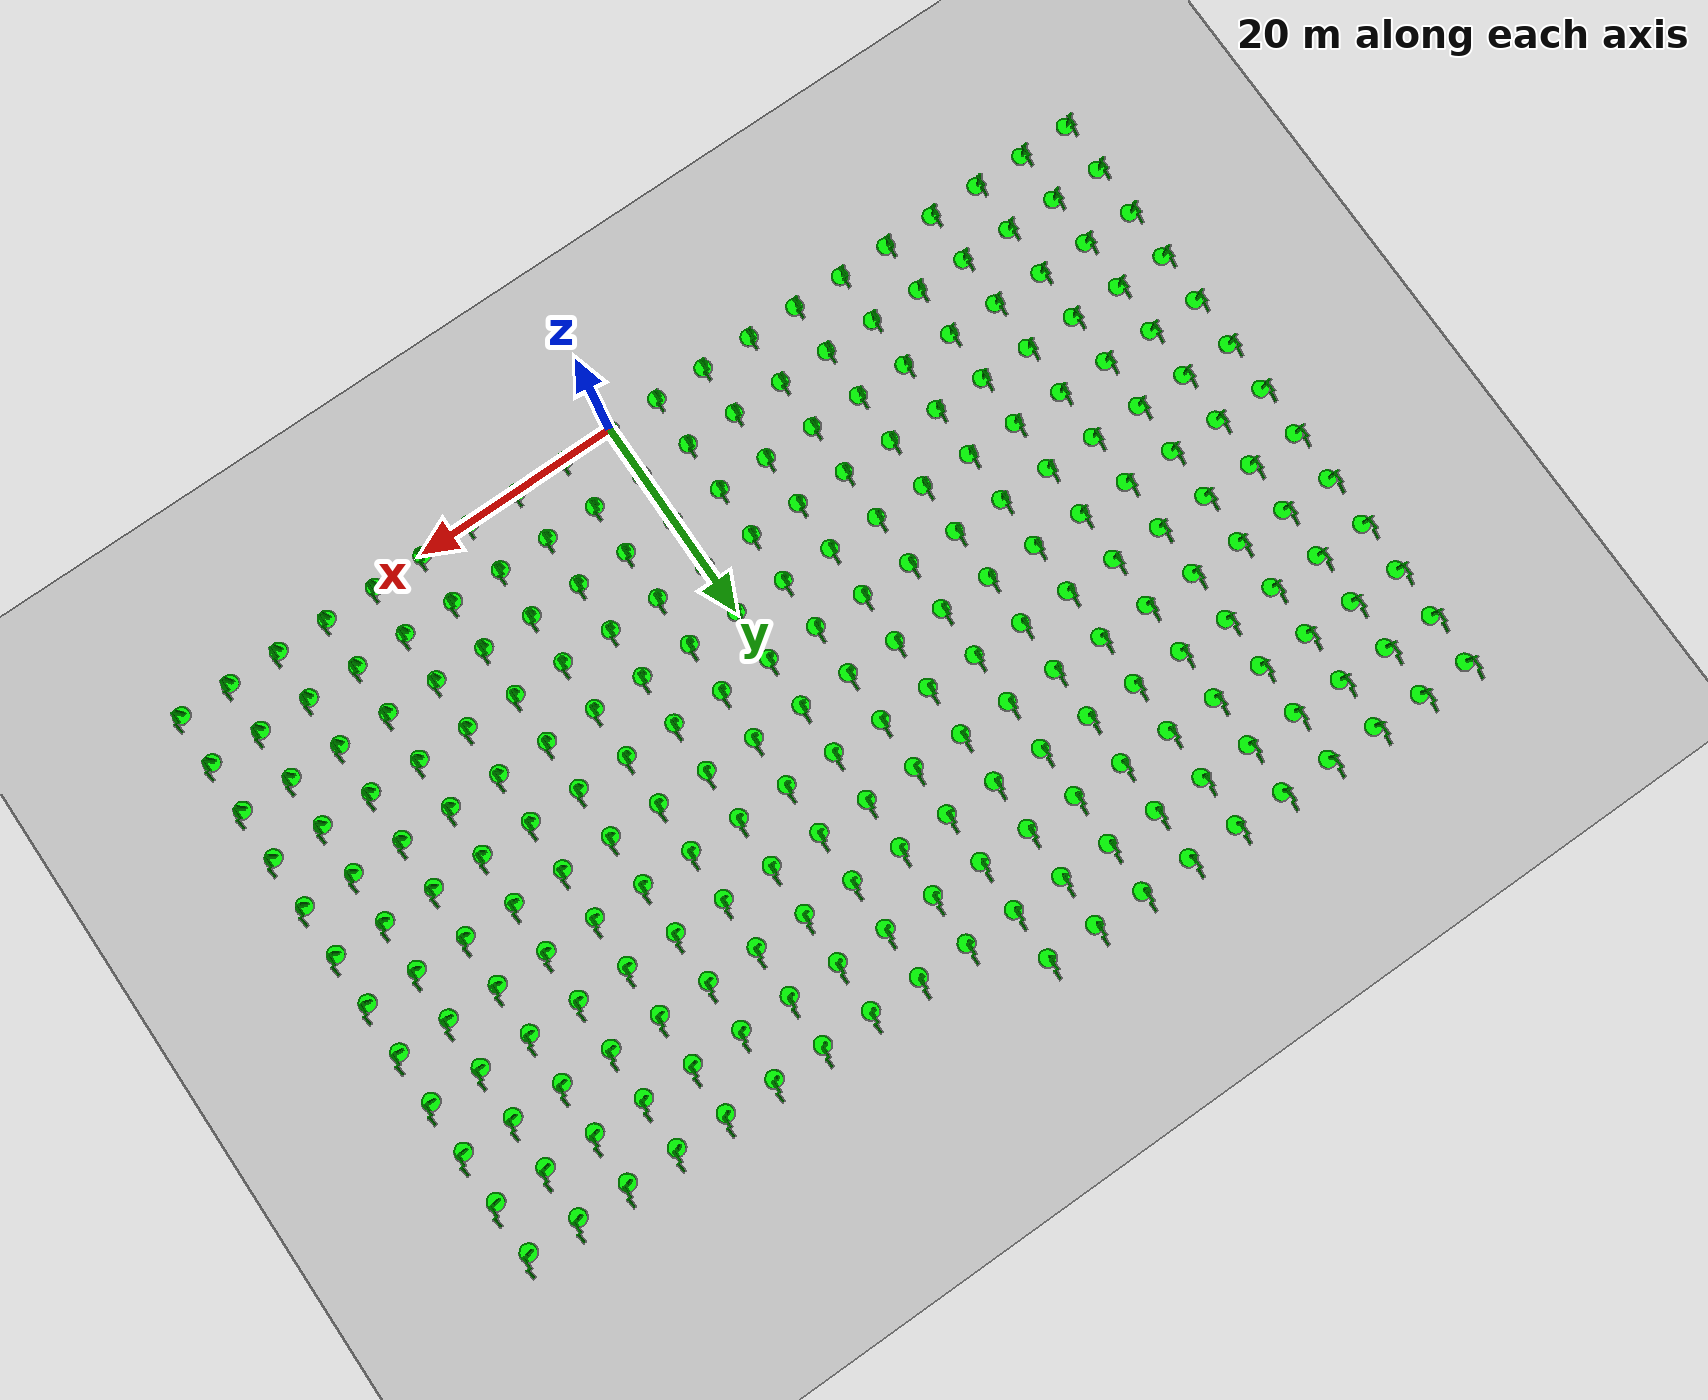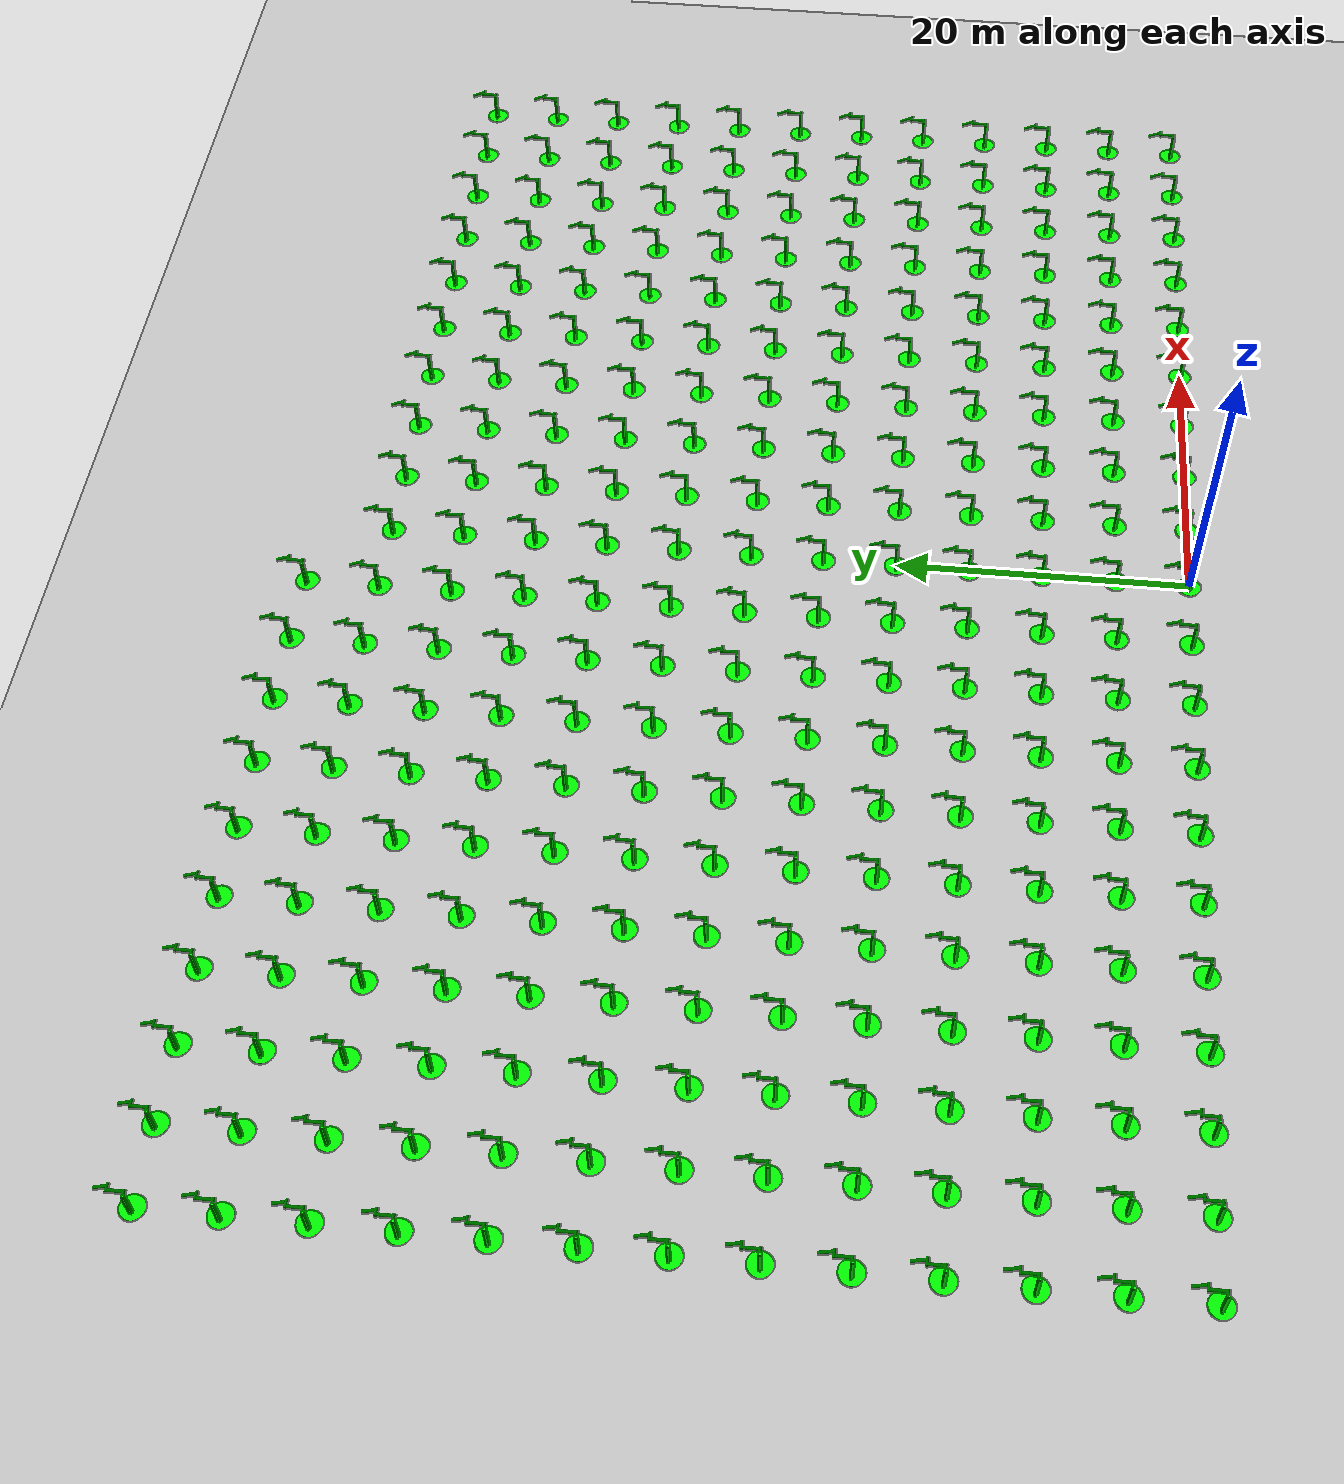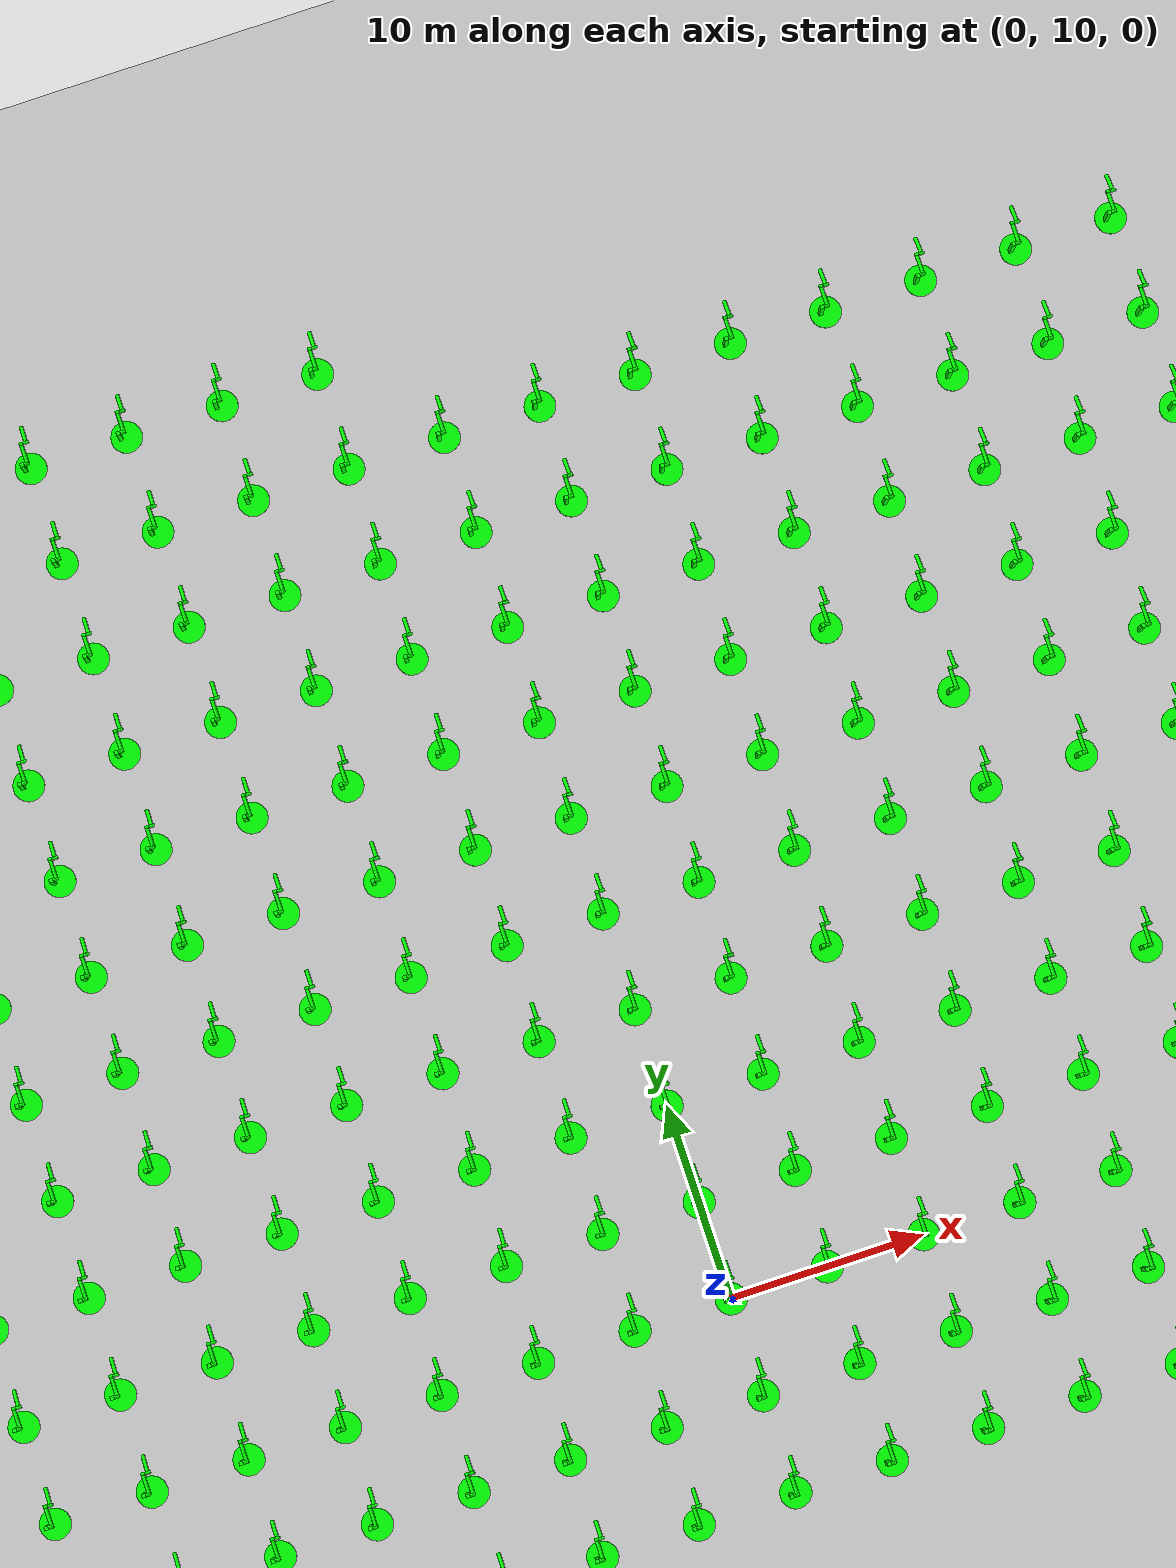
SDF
<sdf version="1.6">
 <world name="double_pendulums">
  <model name="ground_plane">
   <static>true</static>
   <link name="link">
    <collision name="collision">
     <geometry><plane><normal>0 0 1</normal><size>100 100</size></plane></geometry>
    </collision>
    <visual name="visual">
     <geometry><plane><normal>0 0 1</normal><size>100 100</size></plane></geometry>
     <material>
      <ambient>0.8 0.8 0.8 1</ambient>
      <diffuse>0.8 0.8 0.8 1</diffuse>
      <specular>0.8 0.8 0.8 1</specular>
     </material>
    </visual>
   </link>
  </model>
  <model name="dbl_pendulum_0">
   <pose>-50 0 0 0 0 0</pose>
   <link name="base">
    <inertial><mass>100</mass></inertial>
    <visual name="vis_plate_on_ground">
     <pose>0 0 0.01 0 0 0</pose>
     <geometry><cylinder><radius>0.8</radius><length>0.02</length></cylinder></geometry>
     <material><ambient>0 1 0 1</ambient><diffuse>0 1 0 1</diffuse><specular>0 1 0 1</specular></material>
    </visual>
    <visual name="vis_pole">
     <pose>-0.275 0 1.1 0 0 0</pose>
     <geometry><box><size>0.2 0.2 2.2</size></box></geometry>
     <material><ambient>0 1 0 1</ambient><diffuse>0 1 0 1</diffuse><specular>0 1 0 1</specular></material>
    </visual>
    <collision name="col_plate_on_ground">
     <pose>0 0 0.01 0 0 0</pose>
     <geometry><cylinder><radius>0.8</radius><length>0.02</length></cylinder></geometry>
    </collision>
    <collision name="col_pole">
     <pose>-0.275 0 1.1 0 0 0</pose>
     <geometry><box><size>0.2 0.2 2.2</size></box></geometry>
    </collision>
   </link>
   <link name="upper_link">
    <pose>0 0 2.1 -1.5708 0 0</pose>
    <inertial><pose>0 0 0.5 0 0 0</pose></inertial>
    <visual name="vis_upper_joint">
     <pose>-0.05 0 0 0 1.5708 0</pose>
     <geometry><cylinder><radius>0.1</radius><length>0.3</length></cylinder></geometry>
     <material><ambient>0 1 0 1</ambient><diffuse>0 1 0 1</diffuse><specular>0 1 0 1</specular></material>
    </visual>
    <visual name="vis_lower_joint">
     <pose>0 0 1.0 0 1.5708 0</pose>
     <geometry><cylinder><radius>0.1</radius><length>0.2</length></cylinder></geometry>
     <material><ambient>0 1 0 1</ambient><diffuse>0 1 0 1</diffuse><specular>0 1 0 1</specular></material>
    </visual>
    <visual name="vis_cylinder">
     <pose>0 0 0.5 0 0 0</pose>
     <geometry><cylinder><radius>0.1</radius><length>0.9</length></cylinder></geometry>
     <material><ambient>0 1 0 1</ambient><diffuse>0 1 0 1</diffuse><specular>0 1 0 1</specular></material>
    </visual>
    <collision name="col_upper_joint">
     <pose>-0.05 0 0 0 1.5708 0</pose>
     <geometry><cylinder><radius>0.1</radius><length>0.3</length></cylinder></geometry>
    </collision>
    <collision name="col_lower_joint">
     <pose>0 0 1.0 0 1.5708 0</pose>
     <geometry><cylinder><radius>0.1</radius><length>0.2</length></cylinder></geometry>
    </collision>
    <collision name="col_cylinder">
     <pose>0 0 0.5 0 0 0</pose>
     <geometry><cylinder><radius>0.1</radius><length>0.9</length></cylinder></geometry>
    </collision>
   </link>
   <link name="lower_link">
    <pose>0.25 1.0 2.1 -2 0 0</pose>
    <inertial><pose>0 0 0.5 0 0 0</pose></inertial>
    <visual name="vis_lower_joint">
     <pose>0 0 0 0 1.5708 0</pose>
     <geometry><cylinder><radius>0.08</radius><length>0.3</length></cylinder></geometry>
     <material><ambient>0 1 0 1</ambient><diffuse>0 1 0 1</diffuse><specular>0 1 0 1</specular></material>
    </visual>
    <visual name="vis_cylinder">
     <pose>0 0 0.5 0 0 0</pose>
     <geometry><cylinder><radius>0.1</radius><length>0.9</length></cylinder></geometry>
     <material><ambient>0 1 0 1</ambient><diffuse>0 1 0 1</diffuse><specular>0 1 0 1</specular></material>
    </visual>
    <collision name="col_lower_joint">
     <pose>0 0 0 0 1.5708 0</pose>
     <geometry><cylinder><radius>0.08</radius><length>0.3</length></cylinder></geometry>
    </collision>
    <collision name="col_cylinder">
     <pose>0 0 0.5 0 0 0</pose>
     <geometry><cylinder><radius>0.1</radius><length>0.9</length></cylinder></geometry>
    </collision>
   </link>
   <joint name="upper_joint" type="revolute">
    <parent>base</parent>
    <child>upper_link</child>
    <axis><xyz>1.0 0 0</xyz></axis>
   </joint>
   <joint name="lower_joint" type="revolute">
    <parent>upper_link</parent>
    <child>lower_link</child>
    <axis><xyz>1.0 0 0</xyz></axis>
   </joint>
  </model>
  <model name="dbl_pendulum_1">
   <pose>-45 0 0 0 0 0</pose>
   <link name="base">
    <inertial><mass>100</mass></inertial>
    <visual name="vis_plate_on_ground">
     <pose>0 0 0.01 0 0 0</pose>
     <geometry><cylinder><radius>0.8</radius><length>0.02</length></cylinder></geometry>
     <material><ambient>0 1 0 1</ambient><diffuse>0 1 0 1</diffuse><specular>0 1 0 1</specular></material>
    </visual>
    <visual name="vis_pole">
     <pose>-0.275 0 1.1 0 0 0</pose>
     <geometry><box><size>0.2 0.2 2.2</size></box></geometry>
     <material><ambient>0 1 0 1</ambient><diffuse>0 1 0 1</diffuse><specular>0 1 0 1</specular></material>
    </visual>
    <collision name="col_plate_on_ground">
     <pose>0 0 0.01 0 0 0</pose>
     <geometry><cylinder><radius>0.8</radius><length>0.02</length></cylinder></geometry>
    </collision>
    <collision name="col_pole">
     <pose>-0.275 0 1.1 0 0 0</pose>
     <geometry><box><size>0.2 0.2 2.2</size></box></geometry>
    </collision>
   </link>
   <link name="upper_link">
    <pose>0 0 2.1 -1.5708 0 0</pose>
    <inertial><pose>0 0 0.5 0 0 0</pose></inertial>
    <visual name="vis_upper_joint">
     <pose>-0.05 0 0 0 1.5708 0</pose>
     <geometry><cylinder><radius>0.1</radius><length>0.3</length></cylinder></geometry>
     <material><ambient>0 1 0 1</ambient><diffuse>0 1 0 1</diffuse><specular>0 1 0 1</specular></material>
    </visual>
    <visual name="vis_lower_joint">
     <pose>0 0 1.0 0 1.5708 0</pose>
     <geometry><cylinder><radius>0.1</radius><length>0.2</length></cylinder></geometry>
     <material><ambient>0 1 0 1</ambient><diffuse>0 1 0 1</diffuse><specular>0 1 0 1</specular></material>
    </visual>
    <visual name="vis_cylinder">
     <pose>0 0 0.5 0 0 0</pose>
     <geometry><cylinder><radius>0.1</radius><length>0.9</length></cylinder></geometry>
     <material><ambient>0 1 0 1</ambient><diffuse>0 1 0 1</diffuse><specular>0 1 0 1</specular></material>
    </visual>
    <collision name="col_upper_joint">
     <pose>-0.05 0 0 0 1.5708 0</pose>
     <geometry><cylinder><radius>0.1</radius><length>0.3</length></cylinder></geometry>
    </collision>
    <collision name="col_lower_joint">
     <pose>0 0 1.0 0 1.5708 0</pose>
     <geometry><cylinder><radius>0.1</radius><length>0.2</length></cylinder></geometry>
    </collision>
    <collision name="col_cylinder">
     <pose>0 0 0.5 0 0 0</pose>
     <geometry><cylinder><radius>0.1</radius><length>0.9</length></cylinder></geometry>
    </collision>
   </link>
   <link name="lower_link">
    <pose>0.25 1.0 2.1 -2 0 0</pose>
    <inertial><pose>0 0 0.5 0 0 0</pose></inertial>
    <visual name="vis_lower_joint">
     <pose>0 0 0 0 1.5708 0</pose>
     <geometry><cylinder><radius>0.08</radius><length>0.3</length></cylinder></geometry>
     <material><ambient>0 1 0 1</ambient><diffuse>0 1 0 1</diffuse><specular>0 1 0 1</specular></material>
    </visual>
    <visual name="vis_cylinder">
     <pose>0 0 0.5 0 0 0</pose>
     <geometry><cylinder><radius>0.1</radius><length>0.9</length></cylinder></geometry>
     <material><ambient>0 1 0 1</ambient><diffuse>0 1 0 1</diffuse><specular>0 1 0 1</specular></material>
    </visual>
    <collision name="col_lower_joint">
     <pose>0 0 0 0 1.5708 0</pose>
     <geometry><cylinder><radius>0.08</radius><length>0.3</length></cylinder></geometry>
    </collision>
    <collision name="col_cylinder">
     <pose>0 0 0.5 0 0 0</pose>
     <geometry><cylinder><radius>0.1</radius><length>0.9</length></cylinder></geometry>
    </collision>
   </link>
   <joint name="upper_joint" type="revolute">
    <parent>base</parent>
    <child>upper_link</child>
    <axis><xyz>1.0 0 0</xyz></axis>
   </joint>
   <joint name="lower_joint" type="revolute">
    <parent>upper_link</parent>
    <child>lower_link</child>
    <axis><xyz>1.0 0 0</xyz></axis>
   </joint>
  </model>
  <model name="dbl_pendulum_2">
   <pose>-40 0 0 0 0 0</pose>
   <link name="base">
    <inertial><mass>100</mass></inertial>
    <visual name="vis_plate_on_ground">
     <pose>0 0 0.01 0 0 0</pose>
     <geometry><cylinder><radius>0.8</radius><length>0.02</length></cylinder></geometry>
     <material><ambient>0 1 0 1</ambient><diffuse>0 1 0 1</diffuse><specular>0 1 0 1</specular></material>
    </visual>
    <visual name="vis_pole">
     <pose>-0.275 0 1.1 0 0 0</pose>
     <geometry><box><size>0.2 0.2 2.2</size></box></geometry>
     <material><ambient>0 1 0 1</ambient><diffuse>0 1 0 1</diffuse><specular>0 1 0 1</specular></material>
    </visual>
    <collision name="col_plate_on_ground">
     <pose>0 0 0.01 0 0 0</pose>
     <geometry><cylinder><radius>0.8</radius><length>0.02</length></cylinder></geometry>
    </collision>
    <collision name="col_pole">
     <pose>-0.275 0 1.1 0 0 0</pose>
     <geometry><box><size>0.2 0.2 2.2</size></box></geometry>
    </collision>
   </link>
   <link name="upper_link">
    <pose>0 0 2.1 -1.5708 0 0</pose>
    <inertial><pose>0 0 0.5 0 0 0</pose></inertial>
    <visual name="vis_upper_joint">
     <pose>-0.05 0 0 0 1.5708 0</pose>
     <geometry><cylinder><radius>0.1</radius><length>0.3</length></cylinder></geometry>
     <material><ambient>0 1 0 1</ambient><diffuse>0 1 0 1</diffuse><specular>0 1 0 1</specular></material>
    </visual>
    <visual name="vis_lower_joint">
     <pose>0 0 1.0 0 1.5708 0</pose>
     <geometry><cylinder><radius>0.1</radius><length>0.2</length></cylinder></geometry>
     <material><ambient>0 1 0 1</ambient><diffuse>0 1 0 1</diffuse><specular>0 1 0 1</specular></material>
    </visual>
    <visual name="vis_cylinder">
     <pose>0 0 0.5 0 0 0</pose>
     <geometry><cylinder><radius>0.1</radius><length>0.9</length></cylinder></geometry>
     <material><ambient>0 1 0 1</ambient><diffuse>0 1 0 1</diffuse><specular>0 1 0 1</specular></material>
    </visual>
    <collision name="col_upper_joint">
     <pose>-0.05 0 0 0 1.5708 0</pose>
     <geometry><cylinder><radius>0.1</radius><length>0.3</length></cylinder></geometry>
    </collision>
    <collision name="col_lower_joint">
     <pose>0 0 1.0 0 1.5708 0</pose>
     <geometry><cylinder><radius>0.1</radius><length>0.2</length></cylinder></geometry>
    </collision>
    <collision name="col_cylinder">
     <pose>0 0 0.5 0 0 0</pose>
     <geometry><cylinder><radius>0.1</radius><length>0.9</length></cylinder></geometry>
    </collision>
   </link>
   <link name="lower_link">
    <pose>0.25 1.0 2.1 -2 0 0</pose>
    <inertial><pose>0 0 0.5 0 0 0</pose></inertial>
    <visual name="vis_lower_joint">
     <pose>0 0 0 0 1.5708 0</pose>
     <geometry><cylinder><radius>0.08</radius><length>0.3</length></cylinder></geometry>
     <material><ambient>0 1 0 1</ambient><diffuse>0 1 0 1</diffuse><specular>0 1 0 1</specular></material>
    </visual>
    <visual name="vis_cylinder">
     <pose>0 0 0.5 0 0 0</pose>
     <geometry><cylinder><radius>0.1</radius><length>0.9</length></cylinder></geometry>
     <material><ambient>0 1 0 1</ambient><diffuse>0 1 0 1</diffuse><specular>0 1 0 1</specular></material>
    </visual>
    <collision name="col_lower_joint">
     <pose>0 0 0 0 1.5708 0</pose>
     <geometry><cylinder><radius>0.08</radius><length>0.3</length></cylinder></geometry>
    </collision>
    <collision name="col_cylinder">
     <pose>0 0 0.5 0 0 0</pose>
     <geometry><cylinder><radius>0.1</radius><length>0.9</length></cylinder></geometry>
    </collision>
   </link>
   <joint name="upper_joint" type="revolute">
    <parent>base</parent>
    <child>upper_link</child>
    <axis><xyz>1.0 0 0</xyz></axis>
   </joint>
   <joint name="lower_joint" type="revolute">
    <parent>upper_link</parent>
    <child>lower_link</child>
    <axis><xyz>1.0 0 0</xyz></axis>
   </joint>
  </model>
  <model name="dbl_pendulum_3">
   <pose>-35 0 0 0 0 0</pose>
   <link name="base">
    <inertial><mass>100</mass></inertial>
    <visual name="vis_plate_on_ground">
     <pose>0 0 0.01 0 0 0</pose>
     <geometry><cylinder><radius>0.8</radius><length>0.02</length></cylinder></geometry>
     <material><ambient>0 1 0 1</ambient><diffuse>0 1 0 1</diffuse><specular>0 1 0 1</specular></material>
    </visual>
    <visual name="vis_pole">
     <pose>-0.275 0 1.1 0 0 0</pose>
     <geometry><box><size>0.2 0.2 2.2</size></box></geometry>
     <material><ambient>0 1 0 1</ambient><diffuse>0 1 0 1</diffuse><specular>0 1 0 1</specular></material>
    </visual>
    <collision name="col_plate_on_ground">
     <pose>0 0 0.01 0 0 0</pose>
     <geometry><cylinder><radius>0.8</radius><length>0.02</length></cylinder></geometry>
    </collision>
    <collision name="col_pole">
     <pose>-0.275 0 1.1 0 0 0</pose>
     <geometry><box><size>0.2 0.2 2.2</size></box></geometry>
    </collision>
   </link>
   <link name="upper_link">
    <pose>0 0 2.1 -1.5708 0 0</pose>
    <inertial><pose>0 0 0.5 0 0 0</pose></inertial>
    <visual name="vis_upper_joint">
     <pose>-0.05 0 0 0 1.5708 0</pose>
     <geometry><cylinder><radius>0.1</radius><length>0.3</length></cylinder></geometry>
     <material><ambient>0 1 0 1</ambient><diffuse>0 1 0 1</diffuse><specular>0 1 0 1</specular></material>
    </visual>
    <visual name="vis_lower_joint">
     <pose>0 0 1.0 0 1.5708 0</pose>
     <geometry><cylinder><radius>0.1</radius><length>0.2</length></cylinder></geometry>
     <material><ambient>0 1 0 1</ambient><diffuse>0 1 0 1</diffuse><specular>0 1 0 1</specular></material>
    </visual>
    <visual name="vis_cylinder">
     <pose>0 0 0.5 0 0 0</pose>
     <geometry><cylinder><radius>0.1</radius><length>0.9</length></cylinder></geometry>
     <material><ambient>0 1 0 1</ambient><diffuse>0 1 0 1</diffuse><specular>0 1 0 1</specular></material>
    </visual>
    <collision name="col_upper_joint">
     <pose>-0.05 0 0 0 1.5708 0</pose>
     <geometry><cylinder><radius>0.1</radius><length>0.3</length></cylinder></geometry>
    </collision>
    <collision name="col_lower_joint">
     <pose>0 0 1.0 0 1.5708 0</pose>
     <geometry><cylinder><radius>0.1</radius><length>0.2</length></cylinder></geometry>
    </collision>
    <collision name="col_cylinder">
     <pose>0 0 0.5 0 0 0</pose>
     <geometry><cylinder><radius>0.1</radius><length>0.9</length></cylinder></geometry>
    </collision>
   </link>
   <link name="lower_link">
    <pose>0.25 1.0 2.1 -2 0 0</pose>
    <inertial><pose>0 0 0.5 0 0 0</pose></inertial>
    <visual name="vis_lower_joint">
     <pose>0 0 0 0 1.5708 0</pose>
     <geometry><cylinder><radius>0.08</radius><length>0.3</length></cylinder></geometry>
     <material><ambient>0 1 0 1</ambient><diffuse>0 1 0 1</diffuse><specular>0 1 0 1</specular></material>
    </visual>
    <visual name="vis_cylinder">
     <pose>0 0 0.5 0 0 0</pose>
     <geometry><cylinder><radius>0.1</radius><length>0.9</length></cylinder></geometry>
     <material><ambient>0 1 0 1</ambient><diffuse>0 1 0 1</diffuse><specular>0 1 0 1</specular></material>
    </visual>
    <collision name="col_lower_joint">
     <pose>0 0 0 0 1.5708 0</pose>
     <geometry><cylinder><radius>0.08</radius><length>0.3</length></cylinder></geometry>
    </collision>
    <collision name="col_cylinder">
     <pose>0 0 0.5 0 0 0</pose>
     <geometry><cylinder><radius>0.1</radius><length>0.9</length></cylinder></geometry>
    </collision>
   </link>
   <joint name="upper_joint" type="revolute">
    <parent>base</parent>
    <child>upper_link</child>
    <axis><xyz>1.0 0 0</xyz></axis>
   </joint>
   <joint name="lower_joint" type="revolute">
    <parent>upper_link</parent>
    <child>lower_link</child>
    <axis><xyz>1.0 0 0</xyz></axis>
   </joint>
  </model>
  <model name="dbl_pendulum_4">
   <pose>-30 0 0 0 0 0</pose>
   <link name="base">
    <inertial><mass>100</mass></inertial>
    <visual name="vis_plate_on_ground">
     <pose>0 0 0.01 0 0 0</pose>
     <geometry><cylinder><radius>0.8</radius><length>0.02</length></cylinder></geometry>
     <material><ambient>0 1 0 1</ambient><diffuse>0 1 0 1</diffuse><specular>0 1 0 1</specular></material>
    </visual>
    <visual name="vis_pole">
     <pose>-0.275 0 1.1 0 0 0</pose>
     <geometry><box><size>0.2 0.2 2.2</size></box></geometry>
     <material><ambient>0 1 0 1</ambient><diffuse>0 1 0 1</diffuse><specular>0 1 0 1</specular></material>
    </visual>
    <collision name="col_plate_on_ground">
     <pose>0 0 0.01 0 0 0</pose>
     <geometry><cylinder><radius>0.8</radius><length>0.02</length></cylinder></geometry>
    </collision>
    <collision name="col_pole">
     <pose>-0.275 0 1.1 0 0 0</pose>
     <geometry><box><size>0.2 0.2 2.2</size></box></geometry>
    </collision>
   </link>
   <link name="upper_link">
    <pose>0 0 2.1 -1.5708 0 0</pose>
    <inertial><pose>0 0 0.5 0 0 0</pose></inertial>
    <visual name="vis_upper_joint">
     <pose>-0.05 0 0 0 1.5708 0</pose>
     <geometry><cylinder><radius>0.1</radius><length>0.3</length></cylinder></geometry>
     <material><ambient>0 1 0 1</ambient><diffuse>0 1 0 1</diffuse><specular>0 1 0 1</specular></material>
    </visual>
    <visual name="vis_lower_joint">
     <pose>0 0 1.0 0 1.5708 0</pose>
     <geometry><cylinder><radius>0.1</radius><length>0.2</length></cylinder></geometry>
     <material><ambient>0 1 0 1</ambient><diffuse>0 1 0 1</diffuse><specular>0 1 0 1</specular></material>
    </visual>
    <visual name="vis_cylinder">
     <pose>0 0 0.5 0 0 0</pose>
     <geometry><cylinder><radius>0.1</radius><length>0.9</length></cylinder></geometry>
     <material><ambient>0 1 0 1</ambient><diffuse>0 1 0 1</diffuse><specular>0 1 0 1</specular></material>
    </visual>
    <collision name="col_upper_joint">
     <pose>-0.05 0 0 0 1.5708 0</pose>
     <geometry><cylinder><radius>0.1</radius><length>0.3</length></cylinder></geometry>
    </collision>
    <collision name="col_lower_joint">
     <pose>0 0 1.0 0 1.5708 0</pose>
     <geometry><cylinder><radius>0.1</radius><length>0.2</length></cylinder></geometry>
    </collision>
    <collision name="col_cylinder">
     <pose>0 0 0.5 0 0 0</pose>
     <geometry><cylinder><radius>0.1</radius><length>0.9</length></cylinder></geometry>
    </collision>
   </link>
   <link name="lower_link">
    <pose>0.25 1.0 2.1 -2 0 0</pose>
    <inertial><pose>0 0 0.5 0 0 0</pose></inertial>
    <visual name="vis_lower_joint">
     <pose>0 0 0 0 1.5708 0</pose>
     <geometry><cylinder><radius>0.08</radius><length>0.3</length></cylinder></geometry>
     <material><ambient>0 1 0 1</ambient><diffuse>0 1 0 1</diffuse><specular>0 1 0 1</specular></material>
    </visual>
    <visual name="vis_cylinder">
     <pose>0 0 0.5 0 0 0</pose>
     <geometry><cylinder><radius>0.1</radius><length>0.9</length></cylinder></geometry>
     <material><ambient>0 1 0 1</ambient><diffuse>0 1 0 1</diffuse><specular>0 1 0 1</specular></material>
    </visual>
    <collision name="col_lower_joint">
     <pose>0 0 0 0 1.5708 0</pose>
     <geometry><cylinder><radius>0.08</radius><length>0.3</length></cylinder></geometry>
    </collision>
    <collision name="col_cylinder">
     <pose>0 0 0.5 0 0 0</pose>
     <geometry><cylinder><radius>0.1</radius><length>0.9</length></cylinder></geometry>
    </collision>
   </link>
   <joint name="upper_joint" type="revolute">
    <parent>base</parent>
    <child>upper_link</child>
    <axis><xyz>1.0 0 0</xyz></axis>
   </joint>
   <joint name="lower_joint" type="revolute">
    <parent>upper_link</parent>
    <child>lower_link</child>
    <axis><xyz>1.0 0 0</xyz></axis>
   </joint>
  </model>
  <model name="dbl_pendulum_5">
   <pose>-25 0 0 0 0 0</pose>
   <link name="base">
    <inertial><mass>100</mass></inertial>
    <visual name="vis_plate_on_ground">
     <pose>0 0 0.01 0 0 0</pose>
     <geometry><cylinder><radius>0.8</radius><length>0.02</length></cylinder></geometry>
     <material><ambient>0 1 0 1</ambient><diffuse>0 1 0 1</diffuse><specular>0 1 0 1</specular></material>
    </visual>
    <visual name="vis_pole">
     <pose>-0.275 0 1.1 0 0 0</pose>
     <geometry><box><size>0.2 0.2 2.2</size></box></geometry>
     <material><ambient>0 1 0 1</ambient><diffuse>0 1 0 1</diffuse><specular>0 1 0 1</specular></material>
    </visual>
    <collision name="col_plate_on_ground">
     <pose>0 0 0.01 0 0 0</pose>
     <geometry><cylinder><radius>0.8</radius><length>0.02</length></cylinder></geometry>
    </collision>
    <collision name="col_pole">
     <pose>-0.275 0 1.1 0 0 0</pose>
     <geometry><box><size>0.2 0.2 2.2</size></box></geometry>
    </collision>
   </link>
   <link name="upper_link">
    <pose>0 0 2.1 -1.5708 0 0</pose>
    <inertial><pose>0 0 0.5 0 0 0</pose></inertial>
    <visual name="vis_upper_joint">
     <pose>-0.05 0 0 0 1.5708 0</pose>
     <geometry><cylinder><radius>0.1</radius><length>0.3</length></cylinder></geometry>
     <material><ambient>0 1 0 1</ambient><diffuse>0 1 0 1</diffuse><specular>0 1 0 1</specular></material>
    </visual>
    <visual name="vis_lower_joint">
     <pose>0 0 1.0 0 1.5708 0</pose>
     <geometry><cylinder><radius>0.1</radius><length>0.2</length></cylinder></geometry>
     <material><ambient>0 1 0 1</ambient><diffuse>0 1 0 1</diffuse><specular>0 1 0 1</specular></material>
    </visual>
    <visual name="vis_cylinder">
     <pose>0 0 0.5 0 0 0</pose>
     <geometry><cylinder><radius>0.1</radius><length>0.9</length></cylinder></geometry>
     <material><ambient>0 1 0 1</ambient><diffuse>0 1 0 1</diffuse><specular>0 1 0 1</specular></material>
    </visual>
    <collision name="col_upper_joint">
     <pose>-0.05 0 0 0 1.5708 0</pose>
     <geometry><cylinder><radius>0.1</radius><length>0.3</length></cylinder></geometry>
    </collision>
    <collision name="col_lower_joint">
     <pose>0 0 1.0 0 1.5708 0</pose>
     <geometry><cylinder><radius>0.1</radius><length>0.2</length></cylinder></geometry>
    </collision>
    <collision name="col_cylinder">
     <pose>0 0 0.5 0 0 0</pose>
     <geometry><cylinder><radius>0.1</radius><length>0.9</length></cylinder></geometry>
    </collision>
   </link>
   <link name="lower_link">
    <pose>0.25 1.0 2.1 -2 0 0</pose>
    <inertial><pose>0 0 0.5 0 0 0</pose></inertial>
    <visual name="vis_lower_joint">
     <pose>0 0 0 0 1.5708 0</pose>
     <geometry><cylinder><radius>0.08</radius><length>0.3</length></cylinder></geometry>
     <material><ambient>0 1 0 1</ambient><diffuse>0 1 0 1</diffuse><specular>0 1 0 1</specular></material>
    </visual>
    <visual name="vis_cylinder">
     <pose>0 0 0.5 0 0 0</pose>
     <geometry><cylinder><radius>0.1</radius><length>0.9</length></cylinder></geometry>
     <material><ambient>0 1 0 1</ambient><diffuse>0 1 0 1</diffuse><specular>0 1 0 1</specular></material>
    </visual>
    <collision name="col_lower_joint">
     <pose>0 0 0 0 1.5708 0</pose>
     <geometry><cylinder><radius>0.08</radius><length>0.3</length></cylinder></geometry>
    </collision>
    <collision name="col_cylinder">
     <pose>0 0 0.5 0 0 0</pose>
     <geometry><cylinder><radius>0.1</radius><length>0.9</length></cylinder></geometry>
    </collision>
   </link>
   <joint name="upper_joint" type="revolute">
    <parent>base</parent>
    <child>upper_link</child>
    <axis><xyz>1.0 0 0</xyz></axis>
   </joint>
   <joint name="lower_joint" type="revolute">
    <parent>upper_link</parent>
    <child>lower_link</child>
    <axis><xyz>1.0 0 0</xyz></axis>
   </joint>
  </model>
  <model name="dbl_pendulum_6">
   <pose>-20 0 0 0 0 0</pose>
   <link name="base">
    <inertial><mass>100</mass></inertial>
    <visual name="vis_plate_on_ground">
     <pose>0 0 0.01 0 0 0</pose>
     <geometry><cylinder><radius>0.8</radius><length>0.02</length></cylinder></geometry>
     <material><ambient>0 1 0 1</ambient><diffuse>0 1 0 1</diffuse><specular>0 1 0 1</specular></material>
    </visual>
    <visual name="vis_pole">
     <pose>-0.275 0 1.1 0 0 0</pose>
     <geometry><box><size>0.2 0.2 2.2</size></box></geometry>
     <material><ambient>0 1 0 1</ambient><diffuse>0 1 0 1</diffuse><specular>0 1 0 1</specular></material>
    </visual>
    <collision name="col_plate_on_ground">
     <pose>0 0 0.01 0 0 0</pose>
     <geometry><cylinder><radius>0.8</radius><length>0.02</length></cylinder></geometry>
    </collision>
    <collision name="col_pole">
     <pose>-0.275 0 1.1 0 0 0</pose>
     <geometry><box><size>0.2 0.2 2.2</size></box></geometry>
    </collision>
   </link>
   <link name="upper_link">
    <pose>0 0 2.1 -1.5708 0 0</pose>
    <inertial><pose>0 0 0.5 0 0 0</pose></inertial>
    <visual name="vis_upper_joint">
     <pose>-0.05 0 0 0 1.5708 0</pose>
     <geometry><cylinder><radius>0.1</radius><length>0.3</length></cylinder></geometry>
     <material><ambient>0 1 0 1</ambient><diffuse>0 1 0 1</diffuse><specular>0 1 0 1</specular></material>
    </visual>
    <visual name="vis_lower_joint">
     <pose>0 0 1.0 0 1.5708 0</pose>
     <geometry><cylinder><radius>0.1</radius><length>0.2</length></cylinder></geometry>
     <material><ambient>0 1 0 1</ambient><diffuse>0 1 0 1</diffuse><specular>0 1 0 1</specular></material>
    </visual>
    <visual name="vis_cylinder">
     <pose>0 0 0.5 0 0 0</pose>
     <geometry><cylinder><radius>0.1</radius><length>0.9</length></cylinder></geometry>
     <material><ambient>0 1 0 1</ambient><diffuse>0 1 0 1</diffuse><specular>0 1 0 1</specular></material>
    </visual>
    <collision name="col_upper_joint">
     <pose>-0.05 0 0 0 1.5708 0</pose>
     <geometry><cylinder><radius>0.1</radius><length>0.3</length></cylinder></geometry>
    </collision>
    <collision name="col_lower_joint">
     <pose>0 0 1.0 0 1.5708 0</pose>
     <geometry><cylinder><radius>0.1</radius><length>0.2</length></cylinder></geometry>
    </collision>
    <collision name="col_cylinder">
     <pose>0 0 0.5 0 0 0</pose>
     <geometry><cylinder><radius>0.1</radius><length>0.9</length></cylinder></geometry>
    </collision>
   </link>
   <link name="lower_link">
    <pose>0.25 1.0 2.1 -2 0 0</pose>
    <inertial><pose>0 0 0.5 0 0 0</pose></inertial>
    <visual name="vis_lower_joint">
     <pose>0 0 0 0 1.5708 0</pose>
     <geometry><cylinder><radius>0.08</radius><length>0.3</length></cylinder></geometry>
     <material><ambient>0 1 0 1</ambient><diffuse>0 1 0 1</diffuse><specular>0 1 0 1</specular></material>
    </visual>
    <visual name="vis_cylinder">
     <pose>0 0 0.5 0 0 0</pose>
     <geometry><cylinder><radius>0.1</radius><length>0.9</length></cylinder></geometry>
     <material><ambient>0 1 0 1</ambient><diffuse>0 1 0 1</diffuse><specular>0 1 0 1</specular></material>
    </visual>
    <collision name="col_lower_joint">
     <pose>0 0 0 0 1.5708 0</pose>
     <geometry><cylinder><radius>0.08</radius><length>0.3</length></cylinder></geometry>
    </collision>
    <collision name="col_cylinder">
     <pose>0 0 0.5 0 0 0</pose>
     <geometry><cylinder><radius>0.1</radius><length>0.9</length></cylinder></geometry>
    </collision>
   </link>
   <joint name="upper_joint" type="revolute">
    <parent>base</parent>
    <child>upper_link</child>
    <axis><xyz>1.0 0 0</xyz></axis>
   </joint>
   <joint name="lower_joint" type="revolute">
    <parent>upper_link</parent>
    <child>lower_link</child>
    <axis><xyz>1.0 0 0</xyz></axis>
   </joint>
  </model>
  <model name="dbl_pendulum_7">
   <pose>-15 0 0 0 0 0</pose>
   <link name="base">
    <inertial><mass>100</mass></inertial>
    <visual name="vis_plate_on_ground">
     <pose>0 0 0.01 0 0 0</pose>
     <geometry><cylinder><radius>0.8</radius><length>0.02</length></cylinder></geometry>
     <material><ambient>0 1 0 1</ambient><diffuse>0 1 0 1</diffuse><specular>0 1 0 1</specular></material>
    </visual>
    <visual name="vis_pole">
     <pose>-0.275 0 1.1 0 0 0</pose>
     <geometry><box><size>0.2 0.2 2.2</size></box></geometry>
     <material><ambient>0 1 0 1</ambient><diffuse>0 1 0 1</diffuse><specular>0 1 0 1</specular></material>
    </visual>
    <collision name="col_plate_on_ground">
     <pose>0 0 0.01 0 0 0</pose>
     <geometry><cylinder><radius>0.8</radius><length>0.02</length></cylinder></geometry>
    </collision>
    <collision name="col_pole">
     <pose>-0.275 0 1.1 0 0 0</pose>
     <geometry><box><size>0.2 0.2 2.2</size></box></geometry>
    </collision>
   </link>
   <link name="upper_link">
    <pose>0 0 2.1 -1.5708 0 0</pose>
    <inertial><pose>0 0 0.5 0 0 0</pose></inertial>
    <visual name="vis_upper_joint">
     <pose>-0.05 0 0 0 1.5708 0</pose>
     <geometry><cylinder><radius>0.1</radius><length>0.3</length></cylinder></geometry>
     <material><ambient>0 1 0 1</ambient><diffuse>0 1 0 1</diffuse><specular>0 1 0 1</specular></material>
    </visual>
    <visual name="vis_lower_joint">
     <pose>0 0 1.0 0 1.5708 0</pose>
     <geometry><cylinder><radius>0.1</radius><length>0.2</length></cylinder></geometry>
     <material><ambient>0 1 0 1</ambient><diffuse>0 1 0 1</diffuse><specular>0 1 0 1</specular></material>
    </visual>
    <visual name="vis_cylinder">
     <pose>0 0 0.5 0 0 0</pose>
     <geometry><cylinder><radius>0.1</radius><length>0.9</length></cylinder></geometry>
     <material><ambient>0 1 0 1</ambient><diffuse>0 1 0 1</diffuse><specular>0 1 0 1</specular></material>
    </visual>
    <collision name="col_upper_joint">
     <pose>-0.05 0 0 0 1.5708 0</pose>
     <geometry><cylinder><radius>0.1</radius><length>0.3</length></cylinder></geometry>
    </collision>
    <collision name="col_lower_joint">
     <pose>0 0 1.0 0 1.5708 0</pose>
     <geometry><cylinder><radius>0.1</radius><length>0.2</length></cylinder></geometry>
    </collision>
    <collision name="col_cylinder">
     <pose>0 0 0.5 0 0 0</pose>
     <geometry><cylinder><radius>0.1</radius><length>0.9</length></cylinder></geometry>
    </collision>
   </link>
   <link name="lower_link">
    <pose>0.25 1.0 2.1 -2 0 0</pose>
    <inertial><pose>0 0 0.5 0 0 0</pose></inertial>
    <visual name="vis_lower_joint">
     <pose>0 0 0 0 1.5708 0</pose>
     <geometry><cylinder><radius>0.08</radius><length>0.3</length></cylinder></geometry>
     <material><ambient>0 1 0 1</ambient><diffuse>0 1 0 1</diffuse><specular>0 1 0 1</specular></material>
    </visual>
    <visual name="vis_cylinder">
     <pose>0 0 0.5 0 0 0</pose>
     <geometry><cylinder><radius>0.1</radius><length>0.9</length></cylinder></geometry>
     <material><ambient>0 1 0 1</ambient><diffuse>0 1 0 1</diffuse><specular>0 1 0 1</specular></material>
    </visual>
    <collision name="col_lower_joint">
     <pose>0 0 0 0 1.5708 0</pose>
     <geometry><cylinder><radius>0.08</radius><length>0.3</length></cylinder></geometry>
    </collision>
    <collision name="col_cylinder">
     <pose>0 0 0.5 0 0 0</pose>
     <geometry><cylinder><radius>0.1</radius><length>0.9</length></cylinder></geometry>
    </collision>
   </link>
   <joint name="upper_joint" type="revolute">
    <parent>base</parent>
    <child>upper_link</child>
    <axis><xyz>1.0 0 0</xyz></axis>
   </joint>
   <joint name="lower_joint" type="revolute">
    <parent>upper_link</parent>
    <child>lower_link</child>
    <axis><xyz>1.0 0 0</xyz></axis>
   </joint>
  </model>
  <model name="dbl_pendulum_8">
   <pose>-10 0 0 0 0 0</pose>
   <link name="base">
    <inertial><mass>100</mass></inertial>
    <visual name="vis_plate_on_ground">
     <pose>0 0 0.01 0 0 0</pose>
     <geometry><cylinder><radius>0.8</radius><length>0.02</length></cylinder></geometry>
     <material><ambient>0 1 0 1</ambient><diffuse>0 1 0 1</diffuse><specular>0 1 0 1</specular></material>
    </visual>
    <visual name="vis_pole">
     <pose>-0.275 0 1.1 0 0 0</pose>
     <geometry><box><size>0.2 0.2 2.2</size></box></geometry>
     <material><ambient>0 1 0 1</ambient><diffuse>0 1 0 1</diffuse><specular>0 1 0 1</specular></material>
    </visual>
    <collision name="col_plate_on_ground">
     <pose>0 0 0.01 0 0 0</pose>
     <geometry><cylinder><radius>0.8</radius><length>0.02</length></cylinder></geometry>
    </collision>
    <collision name="col_pole">
     <pose>-0.275 0 1.1 0 0 0</pose>
     <geometry><box><size>0.2 0.2 2.2</size></box></geometry>
    </collision>
   </link>
   <link name="upper_link">
    <pose>0 0 2.1 -1.5708 0 0</pose>
    <inertial><pose>0 0 0.5 0 0 0</pose></inertial>
    <visual name="vis_upper_joint">
     <pose>-0.05 0 0 0 1.5708 0</pose>
     <geometry><cylinder><radius>0.1</radius><length>0.3</length></cylinder></geometry>
     <material><ambient>0 1 0 1</ambient><diffuse>0 1 0 1</diffuse><specular>0 1 0 1</specular></material>
    </visual>
    <visual name="vis_lower_joint">
     <pose>0 0 1.0 0 1.5708 0</pose>
     <geometry><cylinder><radius>0.1</radius><length>0.2</length></cylinder></geometry>
     <material><ambient>0 1 0 1</ambient><diffuse>0 1 0 1</diffuse><specular>0 1 0 1</specular></material>
    </visual>
    <visual name="vis_cylinder">
     <pose>0 0 0.5 0 0 0</pose>
     <geometry><cylinder><radius>0.1</radius><length>0.9</length></cylinder></geometry>
     <material><ambient>0 1 0 1</ambient><diffuse>0 1 0 1</diffuse><specular>0 1 0 1</specular></material>
    </visual>
    <collision name="col_upper_joint">
     <pose>-0.05 0 0 0 1.5708 0</pose>
     <geometry><cylinder><radius>0.1</radius><length>0.3</length></cylinder></geometry>
    </collision>
    <collision name="col_lower_joint">
     <pose>0 0 1.0 0 1.5708 0</pose>
     <geometry><cylinder><radius>0.1</radius><length>0.2</length></cylinder></geometry>
    </collision>
    <collision name="col_cylinder">
     <pose>0 0 0.5 0 0 0</pose>
     <geometry><cylinder><radius>0.1</radius><length>0.9</length></cylinder></geometry>
    </collision>
   </link>
   <link name="lower_link">
    <pose>0.25 1.0 2.1 -2 0 0</pose>
    <inertial><pose>0 0 0.5 0 0 0</pose></inertial>
    <visual name="vis_lower_joint">
     <pose>0 0 0 0 1.5708 0</pose>
     <geometry><cylinder><radius>0.08</radius><length>0.3</length></cylinder></geometry>
     <material><ambient>0 1 0 1</ambient><diffuse>0 1 0 1</diffuse><specular>0 1 0 1</specular></material>
    </visual>
    <visual name="vis_cylinder">
     <pose>0 0 0.5 0 0 0</pose>
     <geometry><cylinder><radius>0.1</radius><length>0.9</length></cylinder></geometry>
     <material><ambient>0 1 0 1</ambient><diffuse>0 1 0 1</diffuse><specular>0 1 0 1</specular></material>
    </visual>
    <collision name="col_lower_joint">
     <pose>0 0 0 0 1.5708 0</pose>
     <geometry><cylinder><radius>0.08</radius><length>0.3</length></cylinder></geometry>
    </collision>
    <collision name="col_cylinder">
     <pose>0 0 0.5 0 0 0</pose>
     <geometry><cylinder><radius>0.1</radius><length>0.9</length></cylinder></geometry>
    </collision>
   </link>
   <joint name="upper_joint" type="revolute">
    <parent>base</parent>
    <child>upper_link</child>
    <axis><xyz>1.0 0 0</xyz></axis>
   </joint>
   <joint name="lower_joint" type="revolute">
    <parent>upper_link</parent>
    <child>lower_link</child>
    <axis><xyz>1.0 0 0</xyz></axis>
   </joint>
  </model>
  <model name="dbl_pendulum_9">
   <pose>-5 0 0 0 0 0</pose>
   <link name="base">
    <inertial><mass>100</mass></inertial>
    <visual name="vis_plate_on_ground">
     <pose>0 0 0.01 0 0 0</pose>
     <geometry><cylinder><radius>0.8</radius><length>0.02</length></cylinder></geometry>
     <material><ambient>0 1 0 1</ambient><diffuse>0 1 0 1</diffuse><specular>0 1 0 1</specular></material>
    </visual>
    <visual name="vis_pole">
     <pose>-0.275 0 1.1 0 0 0</pose>
     <geometry><box><size>0.2 0.2 2.2</size></box></geometry>
     <material><ambient>0 1 0 1</ambient><diffuse>0 1 0 1</diffuse><specular>0 1 0 1</specular></material>
    </visual>
    <collision name="col_plate_on_ground">
     <pose>0 0 0.01 0 0 0</pose>
     <geometry><cylinder><radius>0.8</radius><length>0.02</length></cylinder></geometry>
    </collision>
    <collision name="col_pole">
     <pose>-0.275 0 1.1 0 0 0</pose>
     <geometry><box><size>0.2 0.2 2.2</size></box></geometry>
    </collision>
   </link>
   <link name="upper_link">
    <pose>0 0 2.1 -1.5708 0 0</pose>
    <inertial><pose>0 0 0.5 0 0 0</pose></inertial>
    <visual name="vis_upper_joint">
     <pose>-0.05 0 0 0 1.5708 0</pose>
     <geometry><cylinder><radius>0.1</radius><length>0.3</length></cylinder></geometry>
     <material><ambient>0 1 0 1</ambient><diffuse>0 1 0 1</diffuse><specular>0 1 0 1</specular></material>
    </visual>
    <visual name="vis_lower_joint">
     <pose>0 0 1.0 0 1.5708 0</pose>
     <geometry><cylinder><radius>0.1</radius><length>0.2</length></cylinder></geometry>
     <material><ambient>0 1 0 1</ambient><diffuse>0 1 0 1</diffuse><specular>0 1 0 1</specular></material>
    </visual>
    <visual name="vis_cylinder">
     <pose>0 0 0.5 0 0 0</pose>
     <geometry><cylinder><radius>0.1</radius><length>0.9</length></cylinder></geometry>
     <material><ambient>0 1 0 1</ambient><diffuse>0 1 0 1</diffuse><specular>0 1 0 1</specular></material>
    </visual>
    <collision name="col_upper_joint">
     <pose>-0.05 0 0 0 1.5708 0</pose>
     <geometry><cylinder><radius>0.1</radius><length>0.3</length></cylinder></geometry>
    </collision>
    <collision name="col_lower_joint">
     <pose>0 0 1.0 0 1.5708 0</pose>
     <geometry><cylinder><radius>0.1</radius><length>0.2</length></cylinder></geometry>
    </collision>
    <collision name="col_cylinder">
     <pose>0 0 0.5 0 0 0</pose>
     <geometry><cylinder><radius>0.1</radius><length>0.9</length></cylinder></geometry>
    </collision>
   </link>
   <link name="lower_link">
    <pose>0.25 1.0 2.1 -2 0 0</pose>
    <inertial><pose>0 0 0.5 0 0 0</pose></inertial>
    <visual name="vis_lower_joint">
     <pose>0 0 0 0 1.5708 0</pose>
     <geometry><cylinder><radius>0.08</radius><length>0.3</length></cylinder></geometry>
     <material><ambient>0 1 0 1</ambient><diffuse>0 1 0 1</diffuse><specular>0 1 0 1</specular></material>
    </visual>
    <visual name="vis_cylinder">
     <pose>0 0 0.5 0 0 0</pose>
     <geometry><cylinder><radius>0.1</radius><length>0.9</length></cylinder></geometry>
     <material><ambient>0 1 0 1</ambient><diffuse>0 1 0 1</diffuse><specular>0 1 0 1</specular></material>
    </visual>
    <collision name="col_lower_joint">
     <pose>0 0 0 0 1.5708 0</pose>
     <geometry><cylinder><radius>0.08</radius><length>0.3</length></cylinder></geometry>
    </collision>
    <collision name="col_cylinder">
     <pose>0 0 0.5 0 0 0</pose>
     <geometry><cylinder><radius>0.1</radius><length>0.9</length></cylinder></geometry>
    </collision>
   </link>
   <joint name="upper_joint" type="revolute">
    <parent>base</parent>
    <child>upper_link</child>
    <axis><xyz>1.0 0 0</xyz></axis>
   </joint>
   <joint name="lower_joint" type="revolute">
    <parent>upper_link</parent>
    <child>lower_link</child>
    <axis><xyz>1.0 0 0</xyz></axis>
   </joint>
  </model>
  <model name="dbl_pendulum_10">
   <link name="base">
    <inertial><mass>100</mass></inertial>
    <visual name="vis_plate_on_ground">
     <pose>0 0 0.01 0 0 0</pose>
     <geometry><cylinder><radius>0.8</radius><length>0.02</length></cylinder></geometry>
     <material><ambient>0 1 0 1</ambient><diffuse>0 1 0 1</diffuse><specular>0 1 0 1</specular></material>
    </visual>
    <visual name="vis_pole">
     <pose>-0.275 0 1.1 0 0 0</pose>
     <geometry><box><size>0.2 0.2 2.2</size></box></geometry>
     <material><ambient>0 1 0 1</ambient><diffuse>0 1 0 1</diffuse><specular>0 1 0 1</specular></material>
    </visual>
    <collision name="col_plate_on_ground">
     <pose>0 0 0.01 0 0 0</pose>
     <geometry><cylinder><radius>0.8</radius><length>0.02</length></cylinder></geometry>
    </collision>
    <collision name="col_pole">
     <pose>-0.275 0 1.1 0 0 0</pose>
     <geometry><box><size>0.2 0.2 2.2</size></box></geometry>
    </collision>
   </link>
   <link name="upper_link">
    <pose>0 0 2.1 -1.5708 0 0</pose>
    <inertial><pose>0 0 0.5 0 0 0</pose></inertial>
    <visual name="vis_upper_joint">
     <pose>-0.05 0 0 0 1.5708 0</pose>
     <geometry><cylinder><radius>0.1</radius><length>0.3</length></cylinder></geometry>
     <material><ambient>0 1 0 1</ambient><diffuse>0 1 0 1</diffuse><specular>0 1 0 1</specular></material>
    </visual>
    <visual name="vis_lower_joint">
     <pose>0 0 1.0 0 1.5708 0</pose>
     <geometry><cylinder><radius>0.1</radius><length>0.2</length></cylinder></geometry>
     <material><ambient>0 1 0 1</ambient><diffuse>0 1 0 1</diffuse><specular>0 1 0 1</specular></material>
    </visual>
    <visual name="vis_cylinder">
     <pose>0 0 0.5 0 0 0</pose>
     <geometry><cylinder><radius>0.1</radius><length>0.9</length></cylinder></geometry>
     <material><ambient>0 1 0 1</ambient><diffuse>0 1 0 1</diffuse><specular>0 1 0 1</specular></material>
    </visual>
    <collision name="col_upper_joint">
     <pose>-0.05 0 0 0 1.5708 0</pose>
     <geometry><cylinder><radius>0.1</radius><length>0.3</length></cylinder></geometry>
    </collision>
    <collision name="col_lower_joint">
     <pose>0 0 1.0 0 1.5708 0</pose>
     <geometry><cylinder><radius>0.1</radius><length>0.2</length></cylinder></geometry>
    </collision>
    <collision name="col_cylinder">
     <pose>0 0 0.5 0 0 0</pose>
     <geometry><cylinder><radius>0.1</radius><length>0.9</length></cylinder></geometry>
    </collision>
   </link>
   <link name="lower_link">
    <pose>0.25 1.0 2.1 -2 0 0</pose>
    <inertial><pose>0 0 0.5 0 0 0</pose></inertial>
    <visual name="vis_lower_joint">
     <pose>0 0 0 0 1.5708 0</pose>
     <geometry><cylinder><radius>0.08</radius><length>0.3</length></cylinder></geometry>
     <material><ambient>0 1 0 1</ambient><diffuse>0 1 0 1</diffuse><specular>0 1 0 1</specular></material>
    </visual>
    <visual name="vis_cylinder">
     <pose>0 0 0.5 0 0 0</pose>
     <geometry><cylinder><radius>0.1</radius><length>0.9</length></cylinder></geometry>
     <material><ambient>0 1 0 1</ambient><diffuse>0 1 0 1</diffuse><specular>0 1 0 1</specular></material>
    </visual>
    <collision name="col_lower_joint">
     <pose>0 0 0 0 1.5708 0</pose>
     <geometry><cylinder><radius>0.08</radius><length>0.3</length></cylinder></geometry>
    </collision>
    <collision name="col_cylinder">
     <pose>0 0 0.5 0 0 0</pose>
     <geometry><cylinder><radius>0.1</radius><length>0.9</length></cylinder></geometry>
    </collision>
   </link>
   <joint name="upper_joint" type="revolute">
    <parent>base</parent>
    <child>upper_link</child>
    <axis><xyz>1.0 0 0</xyz></axis>
   </joint>
   <joint name="lower_joint" type="revolute">
    <parent>upper_link</parent>
    <child>lower_link</child>
    <axis><xyz>1.0 0 0</xyz></axis>
   </joint>
  </model>
  <model name="dbl_pendulum_11">
   <pose>5 0 0 0 0 0</pose>
   <link name="base">
    <inertial><mass>100</mass></inertial>
    <visual name="vis_plate_on_ground">
     <pose>0 0 0.01 0 0 0</pose>
     <geometry><cylinder><radius>0.8</radius><length>0.02</length></cylinder></geometry>
     <material><ambient>0 1 0 1</ambient><diffuse>0 1 0 1</diffuse><specular>0 1 0 1</specular></material>
    </visual>
    <visual name="vis_pole">
     <pose>-0.275 0 1.1 0 0 0</pose>
     <geometry><box><size>0.2 0.2 2.2</size></box></geometry>
     <material><ambient>0 1 0 1</ambient><diffuse>0 1 0 1</diffuse><specular>0 1 0 1</specular></material>
    </visual>
    <collision name="col_plate_on_ground">
     <pose>0 0 0.01 0 0 0</pose>
     <geometry><cylinder><radius>0.8</radius><length>0.02</length></cylinder></geometry>
    </collision>
    <collision name="col_pole">
     <pose>-0.275 0 1.1 0 0 0</pose>
     <geometry><box><size>0.2 0.2 2.2</size></box></geometry>
    </collision>
   </link>
   <link name="upper_link">
    <pose>0 0 2.1 -1.5708 0 0</pose>
    <inertial><pose>0 0 0.5 0 0 0</pose></inertial>
    <visual name="vis_upper_joint">
     <pose>-0.05 0 0 0 1.5708 0</pose>
     <geometry><cylinder><radius>0.1</radius><length>0.3</length></cylinder></geometry>
     <material><ambient>0 1 0 1</ambient><diffuse>0 1 0 1</diffuse><specular>0 1 0 1</specular></material>
    </visual>
    <visual name="vis_lower_joint">
     <pose>0 0 1.0 0 1.5708 0</pose>
     <geometry><cylinder><radius>0.1</radius><length>0.2</length></cylinder></geometry>
     <material><ambient>0 1 0 1</ambient><diffuse>0 1 0 1</diffuse><specular>0 1 0 1</specular></material>
    </visual>
    <visual name="vis_cylinder">
     <pose>0 0 0.5 0 0 0</pose>
     <geometry><cylinder><radius>0.1</radius><length>0.9</length></cylinder></geometry>
     <material><ambient>0 1 0 1</ambient><diffuse>0 1 0 1</diffuse><specular>0 1 0 1</specular></material>
    </visual>
    <collision name="col_upper_joint">
     <pose>-0.05 0 0 0 1.5708 0</pose>
     <geometry><cylinder><radius>0.1</radius><length>0.3</length></cylinder></geometry>
    </collision>
    <collision name="col_lower_joint">
     <pose>0 0 1.0 0 1.5708 0</pose>
     <geometry><cylinder><radius>0.1</radius><length>0.2</length></cylinder></geometry>
    </collision>
    <collision name="col_cylinder">
     <pose>0 0 0.5 0 0 0</pose>
     <geometry><cylinder><radius>0.1</radius><length>0.9</length></cylinder></geometry>
    </collision>
   </link>
   <link name="lower_link">
    <pose>0.25 1.0 2.1 -2 0 0</pose>
    <inertial><pose>0 0 0.5 0 0 0</pose></inertial>
    <visual name="vis_lower_joint">
     <pose>0 0 0 0 1.5708 0</pose>
     <geometry><cylinder><radius>0.08</radius><length>0.3</length></cylinder></geometry>
     <material><ambient>0 1 0 1</ambient><diffuse>0 1 0 1</diffuse><specular>0 1 0 1</specular></material>
    </visual>
    <visual name="vis_cylinder">
     <pose>0 0 0.5 0 0 0</pose>
     <geometry><cylinder><radius>0.1</radius><length>0.9</length></cylinder></geometry>
     <material><ambient>0 1 0 1</ambient><diffuse>0 1 0 1</diffuse><specular>0 1 0 1</specular></material>
    </visual>
    <collision name="col_lower_joint">
     <pose>0 0 0 0 1.5708 0</pose>
     <geometry><cylinder><radius>0.08</radius><length>0.3</length></cylinder></geometry>
    </collision>
    <collision name="col_cylinder">
     <pose>0 0 0.5 0 0 0</pose>
     <geometry><cylinder><radius>0.1</radius><length>0.9</length></cylinder></geometry>
    </collision>
   </link>
   <joint name="upper_joint" type="revolute">
    <parent>base</parent>
    <child>upper_link</child>
    <axis><xyz>1.0 0 0</xyz></axis>
   </joint>
   <joint name="lower_joint" type="revolute">
    <parent>upper_link</parent>
    <child>lower_link</child>
    <axis><xyz>1.0 0 0</xyz></axis>
   </joint>
  </model>
  <model name="dbl_pendulum_12">
   <pose>10 0 0 0 0 0</pose>
   <link name="base">
    <inertial><mass>100</mass></inertial>
    <visual name="vis_plate_on_ground">
     <pose>0 0 0.01 0 0 0</pose>
     <geometry><cylinder><radius>0.8</radius><length>0.02</length></cylinder></geometry>
     <material><ambient>0 1 0 1</ambient><diffuse>0 1 0 1</diffuse><specular>0 1 0 1</specular></material>
    </visual>
    <visual name="vis_pole">
     <pose>-0.275 0 1.1 0 0 0</pose>
     <geometry><box><size>0.2 0.2 2.2</size></box></geometry>
     <material><ambient>0 1 0 1</ambient><diffuse>0 1 0 1</diffuse><specular>0 1 0 1</specular></material>
    </visual>
    <collision name="col_plate_on_ground">
     <pose>0 0 0.01 0 0 0</pose>
     <geometry><cylinder><radius>0.8</radius><length>0.02</length></cylinder></geometry>
    </collision>
    <collision name="col_pole">
     <pose>-0.275 0 1.1 0 0 0</pose>
     <geometry><box><size>0.2 0.2 2.2</size></box></geometry>
    </collision>
   </link>
   <link name="upper_link">
    <pose>0 0 2.1 -1.5708 0 0</pose>
    <inertial><pose>0 0 0.5 0 0 0</pose></inertial>
    <visual name="vis_upper_joint">
     <pose>-0.05 0 0 0 1.5708 0</pose>
     <geometry><cylinder><radius>0.1</radius><length>0.3</length></cylinder></geometry>
     <material><ambient>0 1 0 1</ambient><diffuse>0 1 0 1</diffuse><specular>0 1 0 1</specular></material>
    </visual>
    <visual name="vis_lower_joint">
     <pose>0 0 1.0 0 1.5708 0</pose>
     <geometry><cylinder><radius>0.1</radius><length>0.2</length></cylinder></geometry>
     <material><ambient>0 1 0 1</ambient><diffuse>0 1 0 1</diffuse><specular>0 1 0 1</specular></material>
    </visual>
    <visual name="vis_cylinder">
     <pose>0 0 0.5 0 0 0</pose>
     <geometry><cylinder><radius>0.1</radius><length>0.9</length></cylinder></geometry>
     <material><ambient>0 1 0 1</ambient><diffuse>0 1 0 1</diffuse><specular>0 1 0 1</specular></material>
    </visual>
    <collision name="col_upper_joint">
     <pose>-0.05 0 0 0 1.5708 0</pose>
     <geometry><cylinder><radius>0.1</radius><length>0.3</length></cylinder></geometry>
    </collision>
    <collision name="col_lower_joint">
     <pose>0 0 1.0 0 1.5708 0</pose>
     <geometry><cylinder><radius>0.1</radius><length>0.2</length></cylinder></geometry>
    </collision>
    <collision name="col_cylinder">
     <pose>0 0 0.5 0 0 0</pose>
     <geometry><cylinder><radius>0.1</radius><length>0.9</length></cylinder></geometry>
    </collision>
   </link>
   <link name="lower_link">
    <pose>0.25 1.0 2.1 -2 0 0</pose>
    <inertial><pose>0 0 0.5 0 0 0</pose></inertial>
    <visual name="vis_lower_joint">
     <pose>0 0 0 0 1.5708 0</pose>
     <geometry><cylinder><radius>0.08</radius><length>0.3</length></cylinder></geometry>
     <material><ambient>0 1 0 1</ambient><diffuse>0 1 0 1</diffuse><specular>0 1 0 1</specular></material>
    </visual>
    <visual name="vis_cylinder">
     <pose>0 0 0.5 0 0 0</pose>
     <geometry><cylinder><radius>0.1</radius><length>0.9</length></cylinder></geometry>
     <material><ambient>0 1 0 1</ambient><diffuse>0 1 0 1</diffuse><specular>0 1 0 1</specular></material>
    </visual>
    <collision name="col_lower_joint">
     <pose>0 0 0 0 1.5708 0</pose>
     <geometry><cylinder><radius>0.08</radius><length>0.3</length></cylinder></geometry>
    </collision>
    <collision name="col_cylinder">
     <pose>0 0 0.5 0 0 0</pose>
     <geometry><cylinder><radius>0.1</radius><length>0.9</length></cylinder></geometry>
    </collision>
   </link>
   <joint name="upper_joint" type="revolute">
    <parent>base</parent>
    <child>upper_link</child>
    <axis><xyz>1.0 0 0</xyz></axis>
   </joint>
   <joint name="lower_joint" type="revolute">
    <parent>upper_link</parent>
    <child>lower_link</child>
    <axis><xyz>1.0 0 0</xyz></axis>
   </joint>
  </model>
  <model name="dbl_pendulum_13">
   <pose>15 0 0 0 0 0</pose>
   <link name="base">
    <inertial><mass>100</mass></inertial>
    <visual name="vis_plate_on_ground">
     <pose>0 0 0.01 0 0 0</pose>
     <geometry><cylinder><radius>0.8</radius><length>0.02</length></cylinder></geometry>
     <material><ambient>0 1 0 1</ambient><diffuse>0 1 0 1</diffuse><specular>0 1 0 1</specular></material>
    </visual>
    <visual name="vis_pole">
     <pose>-0.275 0 1.1 0 0 0</pose>
     <geometry><box><size>0.2 0.2 2.2</size></box></geometry>
     <material><ambient>0 1 0 1</ambient><diffuse>0 1 0 1</diffuse><specular>0 1 0 1</specular></material>
    </visual>
    <collision name="col_plate_on_ground">
     <pose>0 0 0.01 0 0 0</pose>
     <geometry><cylinder><radius>0.8</radius><length>0.02</length></cylinder></geometry>
    </collision>
    <collision name="col_pole">
     <pose>-0.275 0 1.1 0 0 0</pose>
     <geometry><box><size>0.2 0.2 2.2</size></box></geometry>
    </collision>
   </link>
   <link name="upper_link">
    <pose>0 0 2.1 -1.5708 0 0</pose>
    <inertial><pose>0 0 0.5 0 0 0</pose></inertial>
    <visual name="vis_upper_joint">
     <pose>-0.05 0 0 0 1.5708 0</pose>
     <geometry><cylinder><radius>0.1</radius><length>0.3</length></cylinder></geometry>
     <material><ambient>0 1 0 1</ambient><diffuse>0 1 0 1</diffuse><specular>0 1 0 1</specular></material>
    </visual>
    <visual name="vis_lower_joint">
     <pose>0 0 1.0 0 1.5708 0</pose>
     <geometry><cylinder><radius>0.1</radius><length>0.2</length></cylinder></geometry>
     <material><ambient>0 1 0 1</ambient><diffuse>0 1 0 1</diffuse><specular>0 1 0 1</specular></material>
    </visual>
    <visual name="vis_cylinder">
     <pose>0 0 0.5 0 0 0</pose>
     <geometry><cylinder><radius>0.1</radius><length>0.9</length></cylinder></geometry>
     <material><ambient>0 1 0 1</ambient><diffuse>0 1 0 1</diffuse><specular>0 1 0 1</specular></material>
    </visual>
    <collision name="col_upper_joint">
     <pose>-0.05 0 0 0 1.5708 0</pose>
     <geometry><cylinder><radius>0.1</radius><length>0.3</length></cylinder></geometry>
    </collision>
    <collision name="col_lower_joint">
     <pose>0 0 1.0 0 1.5708 0</pose>
     <geometry><cylinder><radius>0.1</radius><length>0.2</length></cylinder></geometry>
    </collision>
    <collision name="col_cylinder">
     <pose>0 0 0.5 0 0 0</pose>
     <geometry><cylinder><radius>0.1</radius><length>0.9</length></cylinder></geometry>
    </collision>
   </link>
   <link name="lower_link">
    <pose>0.25 1.0 2.1 -2 0 0</pose>
    <inertial><pose>0 0 0.5 0 0 0</pose></inertial>
    <visual name="vis_lower_joint">
     <pose>0 0 0 0 1.5708 0</pose>
     <geometry><cylinder><radius>0.08</radius><length>0.3</length></cylinder></geometry>
     <material><ambient>0 1 0 1</ambient><diffuse>0 1 0 1</diffuse><specular>0 1 0 1</specular></material>
    </visual>
    <visual name="vis_cylinder">
     <pose>0 0 0.5 0 0 0</pose>
     <geometry><cylinder><radius>0.1</radius><length>0.9</length></cylinder></geometry>
     <material><ambient>0 1 0 1</ambient><diffuse>0 1 0 1</diffuse><specular>0 1 0 1</specular></material>
    </visual>
    <collision name="col_lower_joint">
     <pose>0 0 0 0 1.5708 0</pose>
     <geometry><cylinder><radius>0.08</radius><length>0.3</length></cylinder></geometry>
    </collision>
    <collision name="col_cylinder">
     <pose>0 0 0.5 0 0 0</pose>
     <geometry><cylinder><radius>0.1</radius><length>0.9</length></cylinder></geometry>
    </collision>
   </link>
   <joint name="upper_joint" type="revolute">
    <parent>base</parent>
    <child>upper_link</child>
    <axis><xyz>1.0 0 0</xyz></axis>
   </joint>
   <joint name="lower_joint" type="revolute">
    <parent>upper_link</parent>
    <child>lower_link</child>
    <axis><xyz>1.0 0 0</xyz></axis>
   </joint>
  </model>
  <model name="dbl_pendulum_14">
   <pose>20 0 0 0 0 0</pose>
   <link name="base">
    <inertial><mass>100</mass></inertial>
    <visual name="vis_plate_on_ground">
     <pose>0 0 0.01 0 0 0</pose>
     <geometry><cylinder><radius>0.8</radius><length>0.02</length></cylinder></geometry>
     <material><ambient>0 1 0 1</ambient><diffuse>0 1 0 1</diffuse><specular>0 1 0 1</specular></material>
    </visual>
    <visual name="vis_pole">
     <pose>-0.275 0 1.1 0 0 0</pose>
     <geometry><box><size>0.2 0.2 2.2</size></box></geometry>
     <material><ambient>0 1 0 1</ambient><diffuse>0 1 0 1</diffuse><specular>0 1 0 1</specular></material>
    </visual>
    <collision name="col_plate_on_ground">
     <pose>0 0 0.01 0 0 0</pose>
     <geometry><cylinder><radius>0.8</radius><length>0.02</length></cylinder></geometry>
    </collision>
    <collision name="col_pole">
     <pose>-0.275 0 1.1 0 0 0</pose>
     <geometry><box><size>0.2 0.2 2.2</size></box></geometry>
    </collision>
   </link>
   <link name="upper_link">
    <pose>0 0 2.1 -1.5708 0 0</pose>
    <inertial><pose>0 0 0.5 0 0 0</pose></inertial>
    <visual name="vis_upper_joint">
     <pose>-0.05 0 0 0 1.5708 0</pose>
     <geometry><cylinder><radius>0.1</radius><length>0.3</length></cylinder></geometry>
     <material><ambient>0 1 0 1</ambient><diffuse>0 1 0 1</diffuse><specular>0 1 0 1</specular></material>
    </visual>
    <visual name="vis_lower_joint">
     <pose>0 0 1.0 0 1.5708 0</pose>
     <geometry><cylinder><radius>0.1</radius><length>0.2</length></cylinder></geometry>
     <material><ambient>0 1 0 1</ambient><diffuse>0 1 0 1</diffuse><specular>0 1 0 1</specular></material>
    </visual>
    <visual name="vis_cylinder">
     <pose>0 0 0.5 0 0 0</pose>
     <geometry><cylinder><radius>0.1</radius><length>0.9</length></cylinder></geometry>
     <material><ambient>0 1 0 1</ambient><diffuse>0 1 0 1</diffuse><specular>0 1 0 1</specular></material>
    </visual>
    <collision name="col_upper_joint">
     <pose>-0.05 0 0 0 1.5708 0</pose>
     <geometry><cylinder><radius>0.1</radius><length>0.3</length></cylinder></geometry>
    </collision>
    <collision name="col_lower_joint">
     <pose>0 0 1.0 0 1.5708 0</pose>
     <geometry><cylinder><radius>0.1</radius><length>0.2</length></cylinder></geometry>
    </collision>
    <collision name="col_cylinder">
     <pose>0 0 0.5 0 0 0</pose>
     <geometry><cylinder><radius>0.1</radius><length>0.9</length></cylinder></geometry>
    </collision>
   </link>
   <link name="lower_link">
    <pose>0.25 1.0 2.1 -2 0 0</pose>
    <inertial><pose>0 0 0.5 0 0 0</pose></inertial>
    <visual name="vis_lower_joint">
     <pose>0 0 0 0 1.5708 0</pose>
     <geometry><cylinder><radius>0.08</radius><length>0.3</length></cylinder></geometry>
     <material><ambient>0 1 0 1</ambient><diffuse>0 1 0 1</diffuse><specular>0 1 0 1</specular></material>
    </visual>
    <visual name="vis_cylinder">
     <pose>0 0 0.5 0 0 0</pose>
     <geometry><cylinder><radius>0.1</radius><length>0.9</length></cylinder></geometry>
     <material><ambient>0 1 0 1</ambient><diffuse>0 1 0 1</diffuse><specular>0 1 0 1</specular></material>
    </visual>
    <collision name="col_lower_joint">
     <pose>0 0 0 0 1.5708 0</pose>
     <geometry><cylinder><radius>0.08</radius><length>0.3</length></cylinder></geometry>
    </collision>
    <collision name="col_cylinder">
     <pose>0 0 0.5 0 0 0</pose>
     <geometry><cylinder><radius>0.1</radius><length>0.9</length></cylinder></geometry>
    </collision>
   </link>
   <joint name="upper_joint" type="revolute">
    <parent>base</parent>
    <child>upper_link</child>
    <axis><xyz>1.0 0 0</xyz></axis>
   </joint>
   <joint name="lower_joint" type="revolute">
    <parent>upper_link</parent>
    <child>lower_link</child>
    <axis><xyz>1.0 0 0</xyz></axis>
   </joint>
  </model>
  <model name="dbl_pendulum_15">
   <pose>25 0 0 0 0 0</pose>
   <link name="base">
    <inertial><mass>100</mass></inertial>
    <visual name="vis_plate_on_ground">
     <pose>0 0 0.01 0 0 0</pose>
     <geometry><cylinder><radius>0.8</radius><length>0.02</length></cylinder></geometry>
     <material><ambient>0 1 0 1</ambient><diffuse>0 1 0 1</diffuse><specular>0 1 0 1</specular></material>
    </visual>
    <visual name="vis_pole">
     <pose>-0.275 0 1.1 0 0 0</pose>
     <geometry><box><size>0.2 0.2 2.2</size></box></geometry>
     <material><ambient>0 1 0 1</ambient><diffuse>0 1 0 1</diffuse><specular>0 1 0 1</specular></material>
    </visual>
    <collision name="col_plate_on_ground">
     <pose>0 0 0.01 0 0 0</pose>
     <geometry><cylinder><radius>0.8</radius><length>0.02</length></cylinder></geometry>
    </collision>
    <collision name="col_pole">
     <pose>-0.275 0 1.1 0 0 0</pose>
     <geometry><box><size>0.2 0.2 2.2</size></box></geometry>
    </collision>
   </link>
   <link name="upper_link">
    <pose>0 0 2.1 -1.5708 0 0</pose>
    <inertial><pose>0 0 0.5 0 0 0</pose></inertial>
    <visual name="vis_upper_joint">
     <pose>-0.05 0 0 0 1.5708 0</pose>
     <geometry><cylinder><radius>0.1</radius><length>0.3</length></cylinder></geometry>
     <material><ambient>0 1 0 1</ambient><diffuse>0 1 0 1</diffuse><specular>0 1 0 1</specular></material>
    </visual>
    <visual name="vis_lower_joint">
     <pose>0 0 1.0 0 1.5708 0</pose>
     <geometry><cylinder><radius>0.1</radius><length>0.2</length></cylinder></geometry>
     <material><ambient>0 1 0 1</ambient><diffuse>0 1 0 1</diffuse><specular>0 1 0 1</specular></material>
    </visual>
    <visual name="vis_cylinder">
     <pose>0 0 0.5 0 0 0</pose>
     <geometry><cylinder><radius>0.1</radius><length>0.9</length></cylinder></geometry>
     <material><ambient>0 1 0 1</ambient><diffuse>0 1 0 1</diffuse><specular>0 1 0 1</specular></material>
    </visual>
    <collision name="col_upper_joint">
     <pose>-0.05 0 0 0 1.5708 0</pose>
     <geometry><cylinder><radius>0.1</radius><length>0.3</length></cylinder></geometry>
    </collision>
    <collision name="col_lower_joint">
     <pose>0 0 1.0 0 1.5708 0</pose>
     <geometry><cylinder><radius>0.1</radius><length>0.2</length></cylinder></geometry>
    </collision>
    <collision name="col_cylinder">
     <pose>0 0 0.5 0 0 0</pose>
     <geometry><cylinder><radius>0.1</radius><length>0.9</length></cylinder></geometry>
    </collision>
   </link>
   <link name="lower_link">
    <pose>0.25 1.0 2.1 -2 0 0</pose>
    <inertial><pose>0 0 0.5 0 0 0</pose></inertial>
    <visual name="vis_lower_joint">
     <pose>0 0 0 0 1.5708 0</pose>
     <geometry><cylinder><radius>0.08</radius><length>0.3</length></cylinder></geometry>
     <material><ambient>0 1 0 1</ambient><diffuse>0 1 0 1</diffuse><specular>0 1 0 1</specular></material>
    </visual>
    <visual name="vis_cylinder">
     <pose>0 0 0.5 0 0 0</pose>
     <geometry><cylinder><radius>0.1</radius><length>0.9</length></cylinder></geometry>
     <material><ambient>0 1 0 1</ambient><diffuse>0 1 0 1</diffuse><specular>0 1 0 1</specular></material>
    </visual>
    <collision name="col_lower_joint">
     <pose>0 0 0 0 1.5708 0</pose>
     <geometry><cylinder><radius>0.08</radius><length>0.3</length></cylinder></geometry>
    </collision>
    <collision name="col_cylinder">
     <pose>0 0 0.5 0 0 0</pose>
     <geometry><cylinder><radius>0.1</radius><length>0.9</length></cylinder></geometry>
    </collision>
   </link>
   <joint name="upper_joint" type="revolute">
    <parent>base</parent>
    <child>upper_link</child>
    <axis><xyz>1.0 0 0</xyz></axis>
   </joint>
   <joint name="lower_joint" type="revolute">
    <parent>upper_link</parent>
    <child>lower_link</child>
    <axis><xyz>1.0 0 0</xyz></axis>
   </joint>
  </model>
  <model name="dbl_pendulum_16">
   <pose>30 0 0 0 0 0</pose>
   <link name="base">
    <inertial><mass>100</mass></inertial>
    <visual name="vis_plate_on_ground">
     <pose>0 0 0.01 0 0 0</pose>
     <geometry><cylinder><radius>0.8</radius><length>0.02</length></cylinder></geometry>
     <material><ambient>0 1 0 1</ambient><diffuse>0 1 0 1</diffuse><specular>0 1 0 1</specular></material>
    </visual>
    <visual name="vis_pole">
     <pose>-0.275 0 1.1 0 0 0</pose>
     <geometry><box><size>0.2 0.2 2.2</size></box></geometry>
     <material><ambient>0 1 0 1</ambient><diffuse>0 1 0 1</diffuse><specular>0 1 0 1</specular></material>
    </visual>
    <collision name="col_plate_on_ground">
     <pose>0 0 0.01 0 0 0</pose>
     <geometry><cylinder><radius>0.8</radius><length>0.02</length></cylinder></geometry>
    </collision>
    <collision name="col_pole">
     <pose>-0.275 0 1.1 0 0 0</pose>
     <geometry><box><size>0.2 0.2 2.2</size></box></geometry>
    </collision>
   </link>
   <link name="upper_link">
    <pose>0 0 2.1 -1.5708 0 0</pose>
    <inertial><pose>0 0 0.5 0 0 0</pose></inertial>
    <visual name="vis_upper_joint">
     <pose>-0.05 0 0 0 1.5708 0</pose>
     <geometry><cylinder><radius>0.1</radius><length>0.3</length></cylinder></geometry>
     <material><ambient>0 1 0 1</ambient><diffuse>0 1 0 1</diffuse><specular>0 1 0 1</specular></material>
    </visual>
    <visual name="vis_lower_joint">
     <pose>0 0 1.0 0 1.5708 0</pose>
     <geometry><cylinder><radius>0.1</radius><length>0.2</length></cylinder></geometry>
     <material><ambient>0 1 0 1</ambient><diffuse>0 1 0 1</diffuse><specular>0 1 0 1</specular></material>
    </visual>
    <visual name="vis_cylinder">
     <pose>0 0 0.5 0 0 0</pose>
     <geometry><cylinder><radius>0.1</radius><length>0.9</length></cylinder></geometry>
     <material><ambient>0 1 0 1</ambient><diffuse>0 1 0 1</diffuse><specular>0 1 0 1</specular></material>
    </visual>
    <collision name="col_upper_joint">
     <pose>-0.05 0 0 0 1.5708 0</pose>
     <geometry><cylinder><radius>0.1</radius><length>0.3</length></cylinder></geometry>
    </collision>
    <collision name="col_lower_joint">
     <pose>0 0 1.0 0 1.5708 0</pose>
     <geometry><cylinder><radius>0.1</radius><length>0.2</length></cylinder></geometry>
    </collision>
    <collision name="col_cylinder">
     <pose>0 0 0.5 0 0 0</pose>
     <geometry><cylinder><radius>0.1</radius><length>0.9</length></cylinder></geometry>
    </collision>
   </link>
   <link name="lower_link">
    <pose>0.25 1.0 2.1 -2 0 0</pose>
    <inertial><pose>0 0 0.5 0 0 0</pose></inertial>
    <visual name="vis_lower_joint">
     <pose>0 0 0 0 1.5708 0</pose>
     <geometry><cylinder><radius>0.08</radius><length>0.3</length></cylinder></geometry>
     <material><ambient>0 1 0 1</ambient><diffuse>0 1 0 1</diffuse><specular>0 1 0 1</specular></material>
    </visual>
    <visual name="vis_cylinder">
     <pose>0 0 0.5 0 0 0</pose>
     <geometry><cylinder><radius>0.1</radius><length>0.9</length></cylinder></geometry>
     <material><ambient>0 1 0 1</ambient><diffuse>0 1 0 1</diffuse><specular>0 1 0 1</specular></material>
    </visual>
    <collision name="col_lower_joint">
     <pose>0 0 0 0 1.5708 0</pose>
     <geometry><cylinder><radius>0.08</radius><length>0.3</length></cylinder></geometry>
    </collision>
    <collision name="col_cylinder">
     <pose>0 0 0.5 0 0 0</pose>
     <geometry><cylinder><radius>0.1</radius><length>0.9</length></cylinder></geometry>
    </collision>
   </link>
   <joint name="upper_joint" type="revolute">
    <parent>base</parent>
    <child>upper_link</child>
    <axis><xyz>1.0 0 0</xyz></axis>
   </joint>
   <joint name="lower_joint" type="revolute">
    <parent>upper_link</parent>
    <child>lower_link</child>
    <axis><xyz>1.0 0 0</xyz></axis>
   </joint>
  </model>
  <model name="dbl_pendulum_17">
   <pose>35 0 0 0 0 0</pose>
   <link name="base">
    <inertial><mass>100</mass></inertial>
    <visual name="vis_plate_on_ground">
     <pose>0 0 0.01 0 0 0</pose>
     <geometry><cylinder><radius>0.8</radius><length>0.02</length></cylinder></geometry>
     <material><ambient>0 1 0 1</ambient><diffuse>0 1 0 1</diffuse><specular>0 1 0 1</specular></material>
    </visual>
    <visual name="vis_pole">
     <pose>-0.275 0 1.1 0 0 0</pose>
     <geometry><box><size>0.2 0.2 2.2</size></box></geometry>
     <material><ambient>0 1 0 1</ambient><diffuse>0 1 0 1</diffuse><specular>0 1 0 1</specular></material>
    </visual>
    <collision name="col_plate_on_ground">
     <pose>0 0 0.01 0 0 0</pose>
     <geometry><cylinder><radius>0.8</radius><length>0.02</length></cylinder></geometry>
    </collision>
    <collision name="col_pole">
     <pose>-0.275 0 1.1 0 0 0</pose>
     <geometry><box><size>0.2 0.2 2.2</size></box></geometry>
    </collision>
   </link>
   <link name="upper_link">
    <pose>0 0 2.1 -1.5708 0 0</pose>
    <inertial><pose>0 0 0.5 0 0 0</pose></inertial>
    <visual name="vis_upper_joint">
     <pose>-0.05 0 0 0 1.5708 0</pose>
     <geometry><cylinder><radius>0.1</radius><length>0.3</length></cylinder></geometry>
     <material><ambient>0 1 0 1</ambient><diffuse>0 1 0 1</diffuse><specular>0 1 0 1</specular></material>
    </visual>
    <visual name="vis_lower_joint">
     <pose>0 0 1.0 0 1.5708 0</pose>
     <geometry><cylinder><radius>0.1</radius><length>0.2</length></cylinder></geometry>
     <material><ambient>0 1 0 1</ambient><diffuse>0 1 0 1</diffuse><specular>0 1 0 1</specular></material>
    </visual>
    <visual name="vis_cylinder">
     <pose>0 0 0.5 0 0 0</pose>
     <geometry><cylinder><radius>0.1</radius><length>0.9</length></cylinder></geometry>
     <material><ambient>0 1 0 1</ambient><diffuse>0 1 0 1</diffuse><specular>0 1 0 1</specular></material>
    </visual>
    <collision name="col_upper_joint">
     <pose>-0.05 0 0 0 1.5708 0</pose>
     <geometry><cylinder><radius>0.1</radius><length>0.3</length></cylinder></geometry>
    </collision>
    <collision name="col_lower_joint">
     <pose>0 0 1.0 0 1.5708 0</pose>
     <geometry><cylinder><radius>0.1</radius><length>0.2</length></cylinder></geometry>
    </collision>
    <collision name="col_cylinder">
     <pose>0 0 0.5 0 0 0</pose>
     <geometry><cylinder><radius>0.1</radius><length>0.9</length></cylinder></geometry>
    </collision>
   </link>
   <link name="lower_link">
    <pose>0.25 1.0 2.1 -2 0 0</pose>
    <inertial><pose>0 0 0.5 0 0 0</pose></inertial>
    <visual name="vis_lower_joint">
     <pose>0 0 0 0 1.5708 0</pose>
     <geometry><cylinder><radius>0.08</radius><length>0.3</length></cylinder></geometry>
     <material><ambient>0 1 0 1</ambient><diffuse>0 1 0 1</diffuse><specular>0 1 0 1</specular></material>
    </visual>
    <visual name="vis_cylinder">
     <pose>0 0 0.5 0 0 0</pose>
     <geometry><cylinder><radius>0.1</radius><length>0.9</length></cylinder></geometry>
     <material><ambient>0 1 0 1</ambient><diffuse>0 1 0 1</diffuse><specular>0 1 0 1</specular></material>
    </visual>
    <collision name="col_lower_joint">
     <pose>0 0 0 0 1.5708 0</pose>
     <geometry><cylinder><radius>0.08</radius><length>0.3</length></cylinder></geometry>
    </collision>
    <collision name="col_cylinder">
     <pose>0 0 0.5 0 0 0</pose>
     <geometry><cylinder><radius>0.1</radius><length>0.9</length></cylinder></geometry>
    </collision>
   </link>
   <joint name="upper_joint" type="revolute">
    <parent>base</parent>
    <child>upper_link</child>
    <axis><xyz>1.0 0 0</xyz></axis>
   </joint>
   <joint name="lower_joint" type="revolute">
    <parent>upper_link</parent>
    <child>lower_link</child>
    <axis><xyz>1.0 0 0</xyz></axis>
   </joint>
  </model>
  <model name="dbl_pendulum_18">
   <pose>40 0 0 0 0 0</pose>
   <link name="base">
    <inertial><mass>100</mass></inertial>
    <visual name="vis_plate_on_ground">
     <pose>0 0 0.01 0 0 0</pose>
     <geometry><cylinder><radius>0.8</radius><length>0.02</length></cylinder></geometry>
     <material><ambient>0 1 0 1</ambient><diffuse>0 1 0 1</diffuse><specular>0 1 0 1</specular></material>
    </visual>
    <visual name="vis_pole">
     <pose>-0.275 0 1.1 0 0 0</pose>
     <geometry><box><size>0.2 0.2 2.2</size></box></geometry>
     <material><ambient>0 1 0 1</ambient><diffuse>0 1 0 1</diffuse><specular>0 1 0 1</specular></material>
    </visual>
    <collision name="col_plate_on_ground">
     <pose>0 0 0.01 0 0 0</pose>
     <geometry><cylinder><radius>0.8</radius><length>0.02</length></cylinder></geometry>
    </collision>
    <collision name="col_pole">
     <pose>-0.275 0 1.1 0 0 0</pose>
     <geometry><box><size>0.2 0.2 2.2</size></box></geometry>
    </collision>
   </link>
   <link name="upper_link">
    <pose>0 0 2.1 -1.5708 0 0</pose>
    <inertial><pose>0 0 0.5 0 0 0</pose></inertial>
    <visual name="vis_upper_joint">
     <pose>-0.05 0 0 0 1.5708 0</pose>
     <geometry><cylinder><radius>0.1</radius><length>0.3</length></cylinder></geometry>
     <material><ambient>0 1 0 1</ambient><diffuse>0 1 0 1</diffuse><specular>0 1 0 1</specular></material>
    </visual>
    <visual name="vis_lower_joint">
     <pose>0 0 1.0 0 1.5708 0</pose>
     <geometry><cylinder><radius>0.1</radius><length>0.2</length></cylinder></geometry>
     <material><ambient>0 1 0 1</ambient><diffuse>0 1 0 1</diffuse><specular>0 1 0 1</specular></material>
    </visual>
    <visual name="vis_cylinder">
     <pose>0 0 0.5 0 0 0</pose>
     <geometry><cylinder><radius>0.1</radius><length>0.9</length></cylinder></geometry>
     <material><ambient>0 1 0 1</ambient><diffuse>0 1 0 1</diffuse><specular>0 1 0 1</specular></material>
    </visual>
    <collision name="col_upper_joint">
     <pose>-0.05 0 0 0 1.5708 0</pose>
     <geometry><cylinder><radius>0.1</radius><length>0.3</length></cylinder></geometry>
    </collision>
    <collision name="col_lower_joint">
     <pose>0 0 1.0 0 1.5708 0</pose>
     <geometry><cylinder><radius>0.1</radius><length>0.2</length></cylinder></geometry>
    </collision>
    <collision name="col_cylinder">
     <pose>0 0 0.5 0 0 0</pose>
     <geometry><cylinder><radius>0.1</radius><length>0.9</length></cylinder></geometry>
    </collision>
   </link>
   <link name="lower_link">
    <pose>0.25 1.0 2.1 -2 0 0</pose>
    <inertial><pose>0 0 0.5 0 0 0</pose></inertial>
    <visual name="vis_lower_joint">
     <pose>0 0 0 0 1.5708 0</pose>
     <geometry><cylinder><radius>0.08</radius><length>0.3</length></cylinder></geometry>
     <material><ambient>0 1 0 1</ambient><diffuse>0 1 0 1</diffuse><specular>0 1 0 1</specular></material>
    </visual>
    <visual name="vis_cylinder">
     <pose>0 0 0.5 0 0 0</pose>
     <geometry><cylinder><radius>0.1</radius><length>0.9</length></cylinder></geometry>
     <material><ambient>0 1 0 1</ambient><diffuse>0 1 0 1</diffuse><specular>0 1 0 1</specular></material>
    </visual>
    <collision name="col_lower_joint">
     <pose>0 0 0 0 1.5708 0</pose>
     <geometry><cylinder><radius>0.08</radius><length>0.3</length></cylinder></geometry>
    </collision>
    <collision name="col_cylinder">
     <pose>0 0 0.5 0 0 0</pose>
     <geometry><cylinder><radius>0.1</radius><length>0.9</length></cylinder></geometry>
    </collision>
   </link>
   <joint name="upper_joint" type="revolute">
    <parent>base</parent>
    <child>upper_link</child>
    <axis><xyz>1.0 0 0</xyz></axis>
   </joint>
   <joint name="lower_joint" type="revolute">
    <parent>upper_link</parent>
    <child>lower_link</child>
    <axis><xyz>1.0 0 0</xyz></axis>
   </joint>
  </model>
  <model name="dbl_pendulum_19">
   <pose>45 0 0 0 0 0</pose>
   <link name="base">
    <inertial><mass>100</mass></inertial>
    <visual name="vis_plate_on_ground">
     <pose>0 0 0.01 0 0 0</pose>
     <geometry><cylinder><radius>0.8</radius><length>0.02</length></cylinder></geometry>
     <material><ambient>0 1 0 1</ambient><diffuse>0 1 0 1</diffuse><specular>0 1 0 1</specular></material>
    </visual>
    <visual name="vis_pole">
     <pose>-0.275 0 1.1 0 0 0</pose>
     <geometry><box><size>0.2 0.2 2.2</size></box></geometry>
     <material><ambient>0 1 0 1</ambient><diffuse>0 1 0 1</diffuse><specular>0 1 0 1</specular></material>
    </visual>
    <collision name="col_plate_on_ground">
     <pose>0 0 0.01 0 0 0</pose>
     <geometry><cylinder><radius>0.8</radius><length>0.02</length></cylinder></geometry>
    </collision>
    <collision name="col_pole">
     <pose>-0.275 0 1.1 0 0 0</pose>
     <geometry><box><size>0.2 0.2 2.2</size></box></geometry>
    </collision>
   </link>
   <link name="upper_link">
    <pose>0 0 2.1 -1.5708 0 0</pose>
    <inertial><pose>0 0 0.5 0 0 0</pose></inertial>
    <visual name="vis_upper_joint">
     <pose>-0.05 0 0 0 1.5708 0</pose>
     <geometry><cylinder><radius>0.1</radius><length>0.3</length></cylinder></geometry>
     <material><ambient>0 1 0 1</ambient><diffuse>0 1 0 1</diffuse><specular>0 1 0 1</specular></material>
    </visual>
    <visual name="vis_lower_joint">
     <pose>0 0 1.0 0 1.5708 0</pose>
     <geometry><cylinder><radius>0.1</radius><length>0.2</length></cylinder></geometry>
     <material><ambient>0 1 0 1</ambient><diffuse>0 1 0 1</diffuse><specular>0 1 0 1</specular></material>
    </visual>
    <visual name="vis_cylinder">
     <pose>0 0 0.5 0 0 0</pose>
     <geometry><cylinder><radius>0.1</radius><length>0.9</length></cylinder></geometry>
     <material><ambient>0 1 0 1</ambient><diffuse>0 1 0 1</diffuse><specular>0 1 0 1</specular></material>
    </visual>
    <collision name="col_upper_joint">
     <pose>-0.05 0 0 0 1.5708 0</pose>
     <geometry><cylinder><radius>0.1</radius><length>0.3</length></cylinder></geometry>
    </collision>
    <collision name="col_lower_joint">
     <pose>0 0 1.0 0 1.5708 0</pose>
     <geometry><cylinder><radius>0.1</radius><length>0.2</length></cylinder></geometry>
    </collision>
    <collision name="col_cylinder">
     <pose>0 0 0.5 0 0 0</pose>
     <geometry><cylinder><radius>0.1</radius><length>0.9</length></cylinder></geometry>
    </collision>
   </link>
   <link name="lower_link">
    <pose>0.25 1.0 2.1 -2 0 0</pose>
    <inertial><pose>0 0 0.5 0 0 0</pose></inertial>
    <visual name="vis_lower_joint">
     <pose>0 0 0 0 1.5708 0</pose>
     <geometry><cylinder><radius>0.08</radius><length>0.3</length></cylinder></geometry>
     <material><ambient>0 1 0 1</ambient><diffuse>0 1 0 1</diffuse><specular>0 1 0 1</specular></material>
    </visual>
    <visual name="vis_cylinder">
     <pose>0 0 0.5 0 0 0</pose>
     <geometry><cylinder><radius>0.1</radius><length>0.9</length></cylinder></geometry>
     <material><ambient>0 1 0 1</ambient><diffuse>0 1 0 1</diffuse><specular>0 1 0 1</specular></material>
    </visual>
    <collision name="col_lower_joint">
     <pose>0 0 0 0 1.5708 0</pose>
     <geometry><cylinder><radius>0.08</radius><length>0.3</length></cylinder></geometry>
    </collision>
    <collision name="col_cylinder">
     <pose>0 0 0.5 0 0 0</pose>
     <geometry><cylinder><radius>0.1</radius><length>0.9</length></cylinder></geometry>
    </collision>
   </link>
   <joint name="upper_joint" type="revolute">
    <parent>base</parent>
    <child>upper_link</child>
    <axis><xyz>1.0 0 0</xyz></axis>
   </joint>
   <joint name="lower_joint" type="revolute">
    <parent>upper_link</parent>
    <child>lower_link</child>
    <axis><xyz>1.0 0 0</xyz></axis>
   </joint>
  </model>
  <model name="dbl_pendulum_25">
   <pose>-50 5 0 0 0 0</pose>
   <link name="base">
    <inertial><mass>100</mass></inertial>
    <visual name="vis_plate_on_ground">
     <pose>0 0 0.01 0 0 0</pose>
     <geometry><cylinder><radius>0.8</radius><length>0.02</length></cylinder></geometry>
     <material><ambient>0 1 0 1</ambient><diffuse>0 1 0 1</diffuse><specular>0 1 0 1</specular></material>
    </visual>
    <visual name="vis_pole">
     <pose>-0.275 0 1.1 0 0 0</pose>
     <geometry><box><size>0.2 0.2 2.2</size></box></geometry>
     <material><ambient>0 1 0 1</ambient><diffuse>0 1 0 1</diffuse><specular>0 1 0 1</specular></material>
    </visual>
    <collision name="col_plate_on_ground">
     <pose>0 0 0.01 0 0 0</pose>
     <geometry><cylinder><radius>0.8</radius><length>0.02</length></cylinder></geometry>
    </collision>
    <collision name="col_pole">
     <pose>-0.275 0 1.1 0 0 0</pose>
     <geometry><box><size>0.2 0.2 2.2</size></box></geometry>
    </collision>
   </link>
   <link name="upper_link">
    <pose>0 0 2.1 -1.5708 0 0</pose>
    <inertial><pose>0 0 0.5 0 0 0</pose></inertial>
    <visual name="vis_upper_joint">
     <pose>-0.05 0 0 0 1.5708 0</pose>
     <geometry><cylinder><radius>0.1</radius><length>0.3</length></cylinder></geometry>
     <material><ambient>0 1 0 1</ambient><diffuse>0 1 0 1</diffuse><specular>0 1 0 1</specular></material>
    </visual>
    <visual name="vis_lower_joint">
     <pose>0 0 1.0 0 1.5708 0</pose>
     <geometry><cylinder><radius>0.1</radius><length>0.2</length></cylinder></geometry>
     <material><ambient>0 1 0 1</ambient><diffuse>0 1 0 1</diffuse><specular>0 1 0 1</specular></material>
    </visual>
    <visual name="vis_cylinder">
     <pose>0 0 0.5 0 0 0</pose>
     <geometry><cylinder><radius>0.1</radius><length>0.9</length></cylinder></geometry>
     <material><ambient>0 1 0 1</ambient><diffuse>0 1 0 1</diffuse><specular>0 1 0 1</specular></material>
    </visual>
    <collision name="col_upper_joint">
     <pose>-0.05 0 0 0 1.5708 0</pose>
     <geometry><cylinder><radius>0.1</radius><length>0.3</length></cylinder></geometry>
    </collision>
    <collision name="col_lower_joint">
     <pose>0 0 1.0 0 1.5708 0</pose>
     <geometry><cylinder><radius>0.1</radius><length>0.2</length></cylinder></geometry>
    </collision>
    <collision name="col_cylinder">
     <pose>0 0 0.5 0 0 0</pose>
     <geometry><cylinder><radius>0.1</radius><length>0.9</length></cylinder></geometry>
    </collision>
   </link>
   <link name="lower_link">
    <pose>0.25 1.0 2.1 -2 0 0</pose>
    <inertial><pose>0 0 0.5 0 0 0</pose></inertial>
    <visual name="vis_lower_joint">
     <pose>0 0 0 0 1.5708 0</pose>
     <geometry><cylinder><radius>0.08</radius><length>0.3</length></cylinder></geometry>
     <material><ambient>0 1 0 1</ambient><diffuse>0 1 0 1</diffuse><specular>0 1 0 1</specular></material>
    </visual>
    <visual name="vis_cylinder">
     <pose>0 0 0.5 0 0 0</pose>
     <geometry><cylinder><radius>0.1</radius><length>0.9</length></cylinder></geometry>
     <material><ambient>0 1 0 1</ambient><diffuse>0 1 0 1</diffuse><specular>0 1 0 1</specular></material>
    </visual>
    <collision name="col_lower_joint">
     <pose>0 0 0 0 1.5708 0</pose>
     <geometry><cylinder><radius>0.08</radius><length>0.3</length></cylinder></geometry>
    </collision>
    <collision name="col_cylinder">
     <pose>0 0 0.5 0 0 0</pose>
     <geometry><cylinder><radius>0.1</radius><length>0.9</length></cylinder></geometry>
    </collision>
   </link>
   <joint name="upper_joint" type="revolute">
    <parent>base</parent>
    <child>upper_link</child>
    <axis><xyz>1.0 0 0</xyz></axis>
   </joint>
   <joint name="lower_joint" type="revolute">
    <parent>upper_link</parent>
    <child>lower_link</child>
    <axis><xyz>1.0 0 0</xyz></axis>
   </joint>
  </model>
  <model name="dbl_pendulum_26">
   <pose>-45 5 0 0 0 0</pose>
   <link name="base">
    <inertial><mass>100</mass></inertial>
    <visual name="vis_plate_on_ground">
     <pose>0 0 0.01 0 0 0</pose>
     <geometry><cylinder><radius>0.8</radius><length>0.02</length></cylinder></geometry>
     <material><ambient>0 1 0 1</ambient><diffuse>0 1 0 1</diffuse><specular>0 1 0 1</specular></material>
    </visual>
    <visual name="vis_pole">
     <pose>-0.275 0 1.1 0 0 0</pose>
     <geometry><box><size>0.2 0.2 2.2</size></box></geometry>
     <material><ambient>0 1 0 1</ambient><diffuse>0 1 0 1</diffuse><specular>0 1 0 1</specular></material>
    </visual>
    <collision name="col_plate_on_ground">
     <pose>0 0 0.01 0 0 0</pose>
     <geometry><cylinder><radius>0.8</radius><length>0.02</length></cylinder></geometry>
    </collision>
    <collision name="col_pole">
     <pose>-0.275 0 1.1 0 0 0</pose>
     <geometry><box><size>0.2 0.2 2.2</size></box></geometry>
    </collision>
   </link>
   <link name="upper_link">
    <pose>0 0 2.1 -1.5708 0 0</pose>
    <inertial><pose>0 0 0.5 0 0 0</pose></inertial>
    <visual name="vis_upper_joint">
     <pose>-0.05 0 0 0 1.5708 0</pose>
     <geometry><cylinder><radius>0.1</radius><length>0.3</length></cylinder></geometry>
     <material><ambient>0 1 0 1</ambient><diffuse>0 1 0 1</diffuse><specular>0 1 0 1</specular></material>
    </visual>
    <visual name="vis_lower_joint">
     <pose>0 0 1.0 0 1.5708 0</pose>
     <geometry><cylinder><radius>0.1</radius><length>0.2</length></cylinder></geometry>
     <material><ambient>0 1 0 1</ambient><diffuse>0 1 0 1</diffuse><specular>0 1 0 1</specular></material>
    </visual>
    <visual name="vis_cylinder">
     <pose>0 0 0.5 0 0 0</pose>
     <geometry><cylinder><radius>0.1</radius><length>0.9</length></cylinder></geometry>
     <material><ambient>0 1 0 1</ambient><diffuse>0 1 0 1</diffuse><specular>0 1 0 1</specular></material>
    </visual>
    <collision name="col_upper_joint">
     <pose>-0.05 0 0 0 1.5708 0</pose>
     <geometry><cylinder><radius>0.1</radius><length>0.3</length></cylinder></geometry>
    </collision>
    <collision name="col_lower_joint">
     <pose>0 0 1.0 0 1.5708 0</pose>
     <geometry><cylinder><radius>0.1</radius><length>0.2</length></cylinder></geometry>
    </collision>
    <collision name="col_cylinder">
     <pose>0 0 0.5 0 0 0</pose>
     <geometry><cylinder><radius>0.1</radius><length>0.9</length></cylinder></geometry>
    </collision>
   </link>
   <link name="lower_link">
    <pose>0.25 1.0 2.1 -2 0 0</pose>
    <inertial><pose>0 0 0.5 0 0 0</pose></inertial>
    <visual name="vis_lower_joint">
     <pose>0 0 0 0 1.5708 0</pose>
     <geometry><cylinder><radius>0.08</radius><length>0.3</length></cylinder></geometry>
     <material><ambient>0 1 0 1</ambient><diffuse>0 1 0 1</diffuse><specular>0 1 0 1</specular></material>
    </visual>
    <visual name="vis_cylinder">
     <pose>0 0 0.5 0 0 0</pose>
     <geometry><cylinder><radius>0.1</radius><length>0.9</length></cylinder></geometry>
     <material><ambient>0 1 0 1</ambient><diffuse>0 1 0 1</diffuse><specular>0 1 0 1</specular></material>
    </visual>
    <collision name="col_lower_joint">
     <pose>0 0 0 0 1.5708 0</pose>
     <geometry><cylinder><radius>0.08</radius><length>0.3</length></cylinder></geometry>
    </collision>
    <collision name="col_cylinder">
     <pose>0 0 0.5 0 0 0</pose>
     <geometry><cylinder><radius>0.1</radius><length>0.9</length></cylinder></geometry>
    </collision>
   </link>
   <joint name="upper_joint" type="revolute">
    <parent>base</parent>
    <child>upper_link</child>
    <axis><xyz>1.0 0 0</xyz></axis>
   </joint>
   <joint name="lower_joint" type="revolute">
    <parent>upper_link</parent>
    <child>lower_link</child>
    <axis><xyz>1.0 0 0</xyz></axis>
   </joint>
  </model>
  <model name="dbl_pendulum_27">
   <pose>-40 5 0 0 0 0</pose>
   <link name="base">
    <inertial><mass>100</mass></inertial>
    <visual name="vis_plate_on_ground">
     <pose>0 0 0.01 0 0 0</pose>
     <geometry><cylinder><radius>0.8</radius><length>0.02</length></cylinder></geometry>
     <material><ambient>0 1 0 1</ambient><diffuse>0 1 0 1</diffuse><specular>0 1 0 1</specular></material>
    </visual>
    <visual name="vis_pole">
     <pose>-0.275 0 1.1 0 0 0</pose>
     <geometry><box><size>0.2 0.2 2.2</size></box></geometry>
     <material><ambient>0 1 0 1</ambient><diffuse>0 1 0 1</diffuse><specular>0 1 0 1</specular></material>
    </visual>
    <collision name="col_plate_on_ground">
     <pose>0 0 0.01 0 0 0</pose>
     <geometry><cylinder><radius>0.8</radius><length>0.02</length></cylinder></geometry>
    </collision>
    <collision name="col_pole">
     <pose>-0.275 0 1.1 0 0 0</pose>
     <geometry><box><size>0.2 0.2 2.2</size></box></geometry>
    </collision>
   </link>
   <link name="upper_link">
    <pose>0 0 2.1 -1.5708 0 0</pose>
    <inertial><pose>0 0 0.5 0 0 0</pose></inertial>
    <visual name="vis_upper_joint">
     <pose>-0.05 0 0 0 1.5708 0</pose>
     <geometry><cylinder><radius>0.1</radius><length>0.3</length></cylinder></geometry>
     <material><ambient>0 1 0 1</ambient><diffuse>0 1 0 1</diffuse><specular>0 1 0 1</specular></material>
    </visual>
    <visual name="vis_lower_joint">
     <pose>0 0 1.0 0 1.5708 0</pose>
     <geometry><cylinder><radius>0.1</radius><length>0.2</length></cylinder></geometry>
     <material><ambient>0 1 0 1</ambient><diffuse>0 1 0 1</diffuse><specular>0 1 0 1</specular></material>
    </visual>
    <visual name="vis_cylinder">
     <pose>0 0 0.5 0 0 0</pose>
     <geometry><cylinder><radius>0.1</radius><length>0.9</length></cylinder></geometry>
     <material><ambient>0 1 0 1</ambient><diffuse>0 1 0 1</diffuse><specular>0 1 0 1</specular></material>
    </visual>
    <collision name="col_upper_joint">
     <pose>-0.05 0 0 0 1.5708 0</pose>
     <geometry><cylinder><radius>0.1</radius><length>0.3</length></cylinder></geometry>
    </collision>
    <collision name="col_lower_joint">
     <pose>0 0 1.0 0 1.5708 0</pose>
     <geometry><cylinder><radius>0.1</radius><length>0.2</length></cylinder></geometry>
    </collision>
    <collision name="col_cylinder">
     <pose>0 0 0.5 0 0 0</pose>
     <geometry><cylinder><radius>0.1</radius><length>0.9</length></cylinder></geometry>
    </collision>
   </link>
   <link name="lower_link">
    <pose>0.25 1.0 2.1 -2 0 0</pose>
    <inertial><pose>0 0 0.5 0 0 0</pose></inertial>
    <visual name="vis_lower_joint">
     <pose>0 0 0 0 1.5708 0</pose>
     <geometry><cylinder><radius>0.08</radius><length>0.3</length></cylinder></geometry>
     <material><ambient>0 1 0 1</ambient><diffuse>0 1 0 1</diffuse><specular>0 1 0 1</specular></material>
    </visual>
    <visual name="vis_cylinder">
     <pose>0 0 0.5 0 0 0</pose>
     <geometry><cylinder><radius>0.1</radius><length>0.9</length></cylinder></geometry>
     <material><ambient>0 1 0 1</ambient><diffuse>0 1 0 1</diffuse><specular>0 1 0 1</specular></material>
    </visual>
    <collision name="col_lower_joint">
     <pose>0 0 0 0 1.5708 0</pose>
     <geometry><cylinder><radius>0.08</radius><length>0.3</length></cylinder></geometry>
    </collision>
    <collision name="col_cylinder">
     <pose>0 0 0.5 0 0 0</pose>
     <geometry><cylinder><radius>0.1</radius><length>0.9</length></cylinder></geometry>
    </collision>
   </link>
   <joint name="upper_joint" type="revolute">
    <parent>base</parent>
    <child>upper_link</child>
    <axis><xyz>1.0 0 0</xyz></axis>
   </joint>
   <joint name="lower_joint" type="revolute">
    <parent>upper_link</parent>
    <child>lower_link</child>
    <axis><xyz>1.0 0 0</xyz></axis>
   </joint>
  </model>
  <model name="dbl_pendulum_28">
   <pose>-35 5 0 0 0 0</pose>
   <link name="base">
    <inertial><mass>100</mass></inertial>
    <visual name="vis_plate_on_ground">
     <pose>0 0 0.01 0 0 0</pose>
     <geometry><cylinder><radius>0.8</radius><length>0.02</length></cylinder></geometry>
     <material><ambient>0 1 0 1</ambient><diffuse>0 1 0 1</diffuse><specular>0 1 0 1</specular></material>
    </visual>
    <visual name="vis_pole">
     <pose>-0.275 0 1.1 0 0 0</pose>
     <geometry><box><size>0.2 0.2 2.2</size></box></geometry>
     <material><ambient>0 1 0 1</ambient><diffuse>0 1 0 1</diffuse><specular>0 1 0 1</specular></material>
    </visual>
    <collision name="col_plate_on_ground">
     <pose>0 0 0.01 0 0 0</pose>
     <geometry><cylinder><radius>0.8</radius><length>0.02</length></cylinder></geometry>
    </collision>
    <collision name="col_pole">
     <pose>-0.275 0 1.1 0 0 0</pose>
     <geometry><box><size>0.2 0.2 2.2</size></box></geometry>
    </collision>
   </link>
   <link name="upper_link">
    <pose>0 0 2.1 -1.5708 0 0</pose>
    <inertial><pose>0 0 0.5 0 0 0</pose></inertial>
    <visual name="vis_upper_joint">
     <pose>-0.05 0 0 0 1.5708 0</pose>
     <geometry><cylinder><radius>0.1</radius><length>0.3</length></cylinder></geometry>
     <material><ambient>0 1 0 1</ambient><diffuse>0 1 0 1</diffuse><specular>0 1 0 1</specular></material>
    </visual>
    <visual name="vis_lower_joint">
     <pose>0 0 1.0 0 1.5708 0</pose>
     <geometry><cylinder><radius>0.1</radius><length>0.2</length></cylinder></geometry>
     <material><ambient>0 1 0 1</ambient><diffuse>0 1 0 1</diffuse><specular>0 1 0 1</specular></material>
    </visual>
    <visual name="vis_cylinder">
     <pose>0 0 0.5 0 0 0</pose>
     <geometry><cylinder><radius>0.1</radius><length>0.9</length></cylinder></geometry>
     <material><ambient>0 1 0 1</ambient><diffuse>0 1 0 1</diffuse><specular>0 1 0 1</specular></material>
    </visual>
    <collision name="col_upper_joint">
     <pose>-0.05 0 0 0 1.5708 0</pose>
     <geometry><cylinder><radius>0.1</radius><length>0.3</length></cylinder></geometry>
    </collision>
    <collision name="col_lower_joint">
     <pose>0 0 1.0 0 1.5708 0</pose>
     <geometry><cylinder><radius>0.1</radius><length>0.2</length></cylinder></geometry>
    </collision>
    <collision name="col_cylinder">
     <pose>0 0 0.5 0 0 0</pose>
     <geometry><cylinder><radius>0.1</radius><length>0.9</length></cylinder></geometry>
    </collision>
   </link>
   <link name="lower_link">
    <pose>0.25 1.0 2.1 -2 0 0</pose>
    <inertial><pose>0 0 0.5 0 0 0</pose></inertial>
    <visual name="vis_lower_joint">
     <pose>0 0 0 0 1.5708 0</pose>
     <geometry><cylinder><radius>0.08</radius><length>0.3</length></cylinder></geometry>
     <material><ambient>0 1 0 1</ambient><diffuse>0 1 0 1</diffuse><specular>0 1 0 1</specular></material>
    </visual>
    <visual name="vis_cylinder">
     <pose>0 0 0.5 0 0 0</pose>
     <geometry><cylinder><radius>0.1</radius><length>0.9</length></cylinder></geometry>
     <material><ambient>0 1 0 1</ambient><diffuse>0 1 0 1</diffuse><specular>0 1 0 1</specular></material>
    </visual>
    <collision name="col_lower_joint">
     <pose>0 0 0 0 1.5708 0</pose>
     <geometry><cylinder><radius>0.08</radius><length>0.3</length></cylinder></geometry>
    </collision>
    <collision name="col_cylinder">
     <pose>0 0 0.5 0 0 0</pose>
     <geometry><cylinder><radius>0.1</radius><length>0.9</length></cylinder></geometry>
    </collision>
   </link>
   <joint name="upper_joint" type="revolute">
    <parent>base</parent>
    <child>upper_link</child>
    <axis><xyz>1.0 0 0</xyz></axis>
   </joint>
   <joint name="lower_joint" type="revolute">
    <parent>upper_link</parent>
    <child>lower_link</child>
    <axis><xyz>1.0 0 0</xyz></axis>
   </joint>
  </model>
  <model name="dbl_pendulum_29">
   <pose>-30 5 0 0 0 0</pose>
   <link name="base">
    <inertial><mass>100</mass></inertial>
    <visual name="vis_plate_on_ground">
     <pose>0 0 0.01 0 0 0</pose>
     <geometry><cylinder><radius>0.8</radius><length>0.02</length></cylinder></geometry>
     <material><ambient>0 1 0 1</ambient><diffuse>0 1 0 1</diffuse><specular>0 1 0 1</specular></material>
    </visual>
    <visual name="vis_pole">
     <pose>-0.275 0 1.1 0 0 0</pose>
     <geometry><box><size>0.2 0.2 2.2</size></box></geometry>
     <material><ambient>0 1 0 1</ambient><diffuse>0 1 0 1</diffuse><specular>0 1 0 1</specular></material>
    </visual>
    <collision name="col_plate_on_ground">
     <pose>0 0 0.01 0 0 0</pose>
     <geometry><cylinder><radius>0.8</radius><length>0.02</length></cylinder></geometry>
    </collision>
    <collision name="col_pole">
     <pose>-0.275 0 1.1 0 0 0</pose>
     <geometry><box><size>0.2 0.2 2.2</size></box></geometry>
    </collision>
   </link>
   <link name="upper_link">
    <pose>0 0 2.1 -1.5708 0 0</pose>
    <inertial><pose>0 0 0.5 0 0 0</pose></inertial>
    <visual name="vis_upper_joint">
     <pose>-0.05 0 0 0 1.5708 0</pose>
     <geometry><cylinder><radius>0.1</radius><length>0.3</length></cylinder></geometry>
     <material><ambient>0 1 0 1</ambient><diffuse>0 1 0 1</diffuse><specular>0 1 0 1</specular></material>
    </visual>
    <visual name="vis_lower_joint">
     <pose>0 0 1.0 0 1.5708 0</pose>
     <geometry><cylinder><radius>0.1</radius><length>0.2</length></cylinder></geometry>
     <material><ambient>0 1 0 1</ambient><diffuse>0 1 0 1</diffuse><specular>0 1 0 1</specular></material>
    </visual>
    <visual name="vis_cylinder">
     <pose>0 0 0.5 0 0 0</pose>
     <geometry><cylinder><radius>0.1</radius><length>0.9</length></cylinder></geometry>
     <material><ambient>0 1 0 1</ambient><diffuse>0 1 0 1</diffuse><specular>0 1 0 1</specular></material>
    </visual>
    <collision name="col_upper_joint">
     <pose>-0.05 0 0 0 1.5708 0</pose>
     <geometry><cylinder><radius>0.1</radius><length>0.3</length></cylinder></geometry>
    </collision>
    <collision name="col_lower_joint">
     <pose>0 0 1.0 0 1.5708 0</pose>
     <geometry><cylinder><radius>0.1</radius><length>0.2</length></cylinder></geometry>
    </collision>
    <collision name="col_cylinder">
     <pose>0 0 0.5 0 0 0</pose>
     <geometry><cylinder><radius>0.1</radius><length>0.9</length></cylinder></geometry>
    </collision>
   </link>
   <link name="lower_link">
    <pose>0.25 1.0 2.1 -2 0 0</pose>
    <inertial><pose>0 0 0.5 0 0 0</pose></inertial>
    <visual name="vis_lower_joint">
     <pose>0 0 0 0 1.5708 0</pose>
     <geometry><cylinder><radius>0.08</radius><length>0.3</length></cylinder></geometry>
     <material><ambient>0 1 0 1</ambient><diffuse>0 1 0 1</diffuse><specular>0 1 0 1</specular></material>
    </visual>
    <visual name="vis_cylinder">
     <pose>0 0 0.5 0 0 0</pose>
     <geometry><cylinder><radius>0.1</radius><length>0.9</length></cylinder></geometry>
     <material><ambient>0 1 0 1</ambient><diffuse>0 1 0 1</diffuse><specular>0 1 0 1</specular></material>
    </visual>
    <collision name="col_lower_joint">
     <pose>0 0 0 0 1.5708 0</pose>
     <geometry><cylinder><radius>0.08</radius><length>0.3</length></cylinder></geometry>
    </collision>
    <collision name="col_cylinder">
     <pose>0 0 0.5 0 0 0</pose>
     <geometry><cylinder><radius>0.1</radius><length>0.9</length></cylinder></geometry>
    </collision>
   </link>
   <joint name="upper_joint" type="revolute">
    <parent>base</parent>
    <child>upper_link</child>
    <axis><xyz>1.0 0 0</xyz></axis>
   </joint>
   <joint name="lower_joint" type="revolute">
    <parent>upper_link</parent>
    <child>lower_link</child>
    <axis><xyz>1.0 0 0</xyz></axis>
   </joint>
  </model>
  <model name="dbl_pendulum_30">
   <pose>-25 5 0 0 0 0</pose>
   <link name="base">
    <inertial><mass>100</mass></inertial>
    <visual name="vis_plate_on_ground">
     <pose>0 0 0.01 0 0 0</pose>
     <geometry><cylinder><radius>0.8</radius><length>0.02</length></cylinder></geometry>
     <material><ambient>0 1 0 1</ambient><diffuse>0 1 0 1</diffuse><specular>0 1 0 1</specular></material>
    </visual>
    <visual name="vis_pole">
     <pose>-0.275 0 1.1 0 0 0</pose>
     <geometry><box><size>0.2 0.2 2.2</size></box></geometry>
     <material><ambient>0 1 0 1</ambient><diffuse>0 1 0 1</diffuse><specular>0 1 0 1</specular></material>
    </visual>
    <collision name="col_plate_on_ground">
     <pose>0 0 0.01 0 0 0</pose>
     <geometry><cylinder><radius>0.8</radius><length>0.02</length></cylinder></geometry>
    </collision>
    <collision name="col_pole">
     <pose>-0.275 0 1.1 0 0 0</pose>
     <geometry><box><size>0.2 0.2 2.2</size></box></geometry>
    </collision>
   </link>
   <link name="upper_link">
    <pose>0 0 2.1 -1.5708 0 0</pose>
    <inertial><pose>0 0 0.5 0 0 0</pose></inertial>
    <visual name="vis_upper_joint">
     <pose>-0.05 0 0 0 1.5708 0</pose>
     <geometry><cylinder><radius>0.1</radius><length>0.3</length></cylinder></geometry>
     <material><ambient>0 1 0 1</ambient><diffuse>0 1 0 1</diffuse><specular>0 1 0 1</specular></material>
    </visual>
    <visual name="vis_lower_joint">
     <pose>0 0 1.0 0 1.5708 0</pose>
     <geometry><cylinder><radius>0.1</radius><length>0.2</length></cylinder></geometry>
     <material><ambient>0 1 0 1</ambient><diffuse>0 1 0 1</diffuse><specular>0 1 0 1</specular></material>
    </visual>
    <visual name="vis_cylinder">
     <pose>0 0 0.5 0 0 0</pose>
     <geometry><cylinder><radius>0.1</radius><length>0.9</length></cylinder></geometry>
     <material><ambient>0 1 0 1</ambient><diffuse>0 1 0 1</diffuse><specular>0 1 0 1</specular></material>
    </visual>
    <collision name="col_upper_joint">
     <pose>-0.05 0 0 0 1.5708 0</pose>
     <geometry><cylinder><radius>0.1</radius><length>0.3</length></cylinder></geometry>
    </collision>
    <collision name="col_lower_joint">
     <pose>0 0 1.0 0 1.5708 0</pose>
     <geometry><cylinder><radius>0.1</radius><length>0.2</length></cylinder></geometry>
    </collision>
    <collision name="col_cylinder">
     <pose>0 0 0.5 0 0 0</pose>
     <geometry><cylinder><radius>0.1</radius><length>0.9</length></cylinder></geometry>
    </collision>
   </link>
   <link name="lower_link">
    <pose>0.25 1.0 2.1 -2 0 0</pose>
    <inertial><pose>0 0 0.5 0 0 0</pose></inertial>
    <visual name="vis_lower_joint">
     <pose>0 0 0 0 1.5708 0</pose>
     <geometry><cylinder><radius>0.08</radius><length>0.3</length></cylinder></geometry>
     <material><ambient>0 1 0 1</ambient><diffuse>0 1 0 1</diffuse><specular>0 1 0 1</specular></material>
    </visual>
    <visual name="vis_cylinder">
     <pose>0 0 0.5 0 0 0</pose>
     <geometry><cylinder><radius>0.1</radius><length>0.9</length></cylinder></geometry>
     <material><ambient>0 1 0 1</ambient><diffuse>0 1 0 1</diffuse><specular>0 1 0 1</specular></material>
    </visual>
    <collision name="col_lower_joint">
     <pose>0 0 0 0 1.5708 0</pose>
     <geometry><cylinder><radius>0.08</radius><length>0.3</length></cylinder></geometry>
    </collision>
    <collision name="col_cylinder">
     <pose>0 0 0.5 0 0 0</pose>
     <geometry><cylinder><radius>0.1</radius><length>0.9</length></cylinder></geometry>
    </collision>
   </link>
   <joint name="upper_joint" type="revolute">
    <parent>base</parent>
    <child>upper_link</child>
    <axis><xyz>1.0 0 0</xyz></axis>
   </joint>
   <joint name="lower_joint" type="revolute">
    <parent>upper_link</parent>
    <child>lower_link</child>
    <axis><xyz>1.0 0 0</xyz></axis>
   </joint>
  </model>
  <model name="dbl_pendulum_31">
   <pose>-20 5 0 0 0 0</pose>
   <link name="base">
    <inertial><mass>100</mass></inertial>
    <visual name="vis_plate_on_ground">
     <pose>0 0 0.01 0 0 0</pose>
     <geometry><cylinder><radius>0.8</radius><length>0.02</length></cylinder></geometry>
     <material><ambient>0 1 0 1</ambient><diffuse>0 1 0 1</diffuse><specular>0 1 0 1</specular></material>
    </visual>
    <visual name="vis_pole">
     <pose>-0.275 0 1.1 0 0 0</pose>
     <geometry><box><size>0.2 0.2 2.2</size></box></geometry>
     <material><ambient>0 1 0 1</ambient><diffuse>0 1 0 1</diffuse><specular>0 1 0 1</specular></material>
    </visual>
    <collision name="col_plate_on_ground">
     <pose>0 0 0.01 0 0 0</pose>
     <geometry><cylinder><radius>0.8</radius><length>0.02</length></cylinder></geometry>
    </collision>
    <collision name="col_pole">
     <pose>-0.275 0 1.1 0 0 0</pose>
     <geometry><box><size>0.2 0.2 2.2</size></box></geometry>
    </collision>
   </link>
   <link name="upper_link">
    <pose>0 0 2.1 -1.5708 0 0</pose>
    <inertial><pose>0 0 0.5 0 0 0</pose></inertial>
    <visual name="vis_upper_joint">
     <pose>-0.05 0 0 0 1.5708 0</pose>
     <geometry><cylinder><radius>0.1</radius><length>0.3</length></cylinder></geometry>
     <material><ambient>0 1 0 1</ambient><diffuse>0 1 0 1</diffuse><specular>0 1 0 1</specular></material>
    </visual>
    <visual name="vis_lower_joint">
     <pose>0 0 1.0 0 1.5708 0</pose>
     <geometry><cylinder><radius>0.1</radius><length>0.2</length></cylinder></geometry>
     <material><ambient>0 1 0 1</ambient><diffuse>0 1 0 1</diffuse><specular>0 1 0 1</specular></material>
    </visual>
    <visual name="vis_cylinder">
     <pose>0 0 0.5 0 0 0</pose>
     <geometry><cylinder><radius>0.1</radius><length>0.9</length></cylinder></geometry>
     <material><ambient>0 1 0 1</ambient><diffuse>0 1 0 1</diffuse><specular>0 1 0 1</specular></material>
    </visual>
    <collision name="col_upper_joint">
     <pose>-0.05 0 0 0 1.5708 0</pose>
     <geometry><cylinder><radius>0.1</radius><length>0.3</length></cylinder></geometry>
    </collision>
    <collision name="col_lower_joint">
     <pose>0 0 1.0 0 1.5708 0</pose>
     <geometry><cylinder><radius>0.1</radius><length>0.2</length></cylinder></geometry>
    </collision>
    <collision name="col_cylinder">
     <pose>0 0 0.5 0 0 0</pose>
     <geometry><cylinder><radius>0.1</radius><length>0.9</length></cylinder></geometry>
    </collision>
   </link>
   <link name="lower_link">
    <pose>0.25 1.0 2.1 -2 0 0</pose>
    <inertial><pose>0 0 0.5 0 0 0</pose></inertial>
    <visual name="vis_lower_joint">
     <pose>0 0 0 0 1.5708 0</pose>
     <geometry><cylinder><radius>0.08</radius><length>0.3</length></cylinder></geometry>
     <material><ambient>0 1 0 1</ambient><diffuse>0 1 0 1</diffuse><specular>0 1 0 1</specular></material>
    </visual>
    <visual name="vis_cylinder">
     <pose>0 0 0.5 0 0 0</pose>
     <geometry><cylinder><radius>0.1</radius><length>0.9</length></cylinder></geometry>
     <material><ambient>0 1 0 1</ambient><diffuse>0 1 0 1</diffuse><specular>0 1 0 1</specular></material>
    </visual>
    <collision name="col_lower_joint">
     <pose>0 0 0 0 1.5708 0</pose>
     <geometry><cylinder><radius>0.08</radius><length>0.3</length></cylinder></geometry>
    </collision>
    <collision name="col_cylinder">
     <pose>0 0 0.5 0 0 0</pose>
     <geometry><cylinder><radius>0.1</radius><length>0.9</length></cylinder></geometry>
    </collision>
   </link>
   <joint name="upper_joint" type="revolute">
    <parent>base</parent>
    <child>upper_link</child>
    <axis><xyz>1.0 0 0</xyz></axis>
   </joint>
   <joint name="lower_joint" type="revolute">
    <parent>upper_link</parent>
    <child>lower_link</child>
    <axis><xyz>1.0 0 0</xyz></axis>
   </joint>
  </model>
  <model name="dbl_pendulum_32">
   <pose>-15 5 0 0 0 0</pose>
   <link name="base">
    <inertial><mass>100</mass></inertial>
    <visual name="vis_plate_on_ground">
     <pose>0 0 0.01 0 0 0</pose>
     <geometry><cylinder><radius>0.8</radius><length>0.02</length></cylinder></geometry>
     <material><ambient>0 1 0 1</ambient><diffuse>0 1 0 1</diffuse><specular>0 1 0 1</specular></material>
    </visual>
    <visual name="vis_pole">
     <pose>-0.275 0 1.1 0 0 0</pose>
     <geometry><box><size>0.2 0.2 2.2</size></box></geometry>
     <material><ambient>0 1 0 1</ambient><diffuse>0 1 0 1</diffuse><specular>0 1 0 1</specular></material>
    </visual>
    <collision name="col_plate_on_ground">
     <pose>0 0 0.01 0 0 0</pose>
     <geometry><cylinder><radius>0.8</radius><length>0.02</length></cylinder></geometry>
    </collision>
    <collision name="col_pole">
     <pose>-0.275 0 1.1 0 0 0</pose>
     <geometry><box><size>0.2 0.2 2.2</size></box></geometry>
    </collision>
   </link>
   <link name="upper_link">
    <pose>0 0 2.1 -1.5708 0 0</pose>
    <inertial><pose>0 0 0.5 0 0 0</pose></inertial>
    <visual name="vis_upper_joint">
     <pose>-0.05 0 0 0 1.5708 0</pose>
     <geometry><cylinder><radius>0.1</radius><length>0.3</length></cylinder></geometry>
     <material><ambient>0 1 0 1</ambient><diffuse>0 1 0 1</diffuse><specular>0 1 0 1</specular></material>
    </visual>
    <visual name="vis_lower_joint">
     <pose>0 0 1.0 0 1.5708 0</pose>
     <geometry><cylinder><radius>0.1</radius><length>0.2</length></cylinder></geometry>
     <material><ambient>0 1 0 1</ambient><diffuse>0 1 0 1</diffuse><specular>0 1 0 1</specular></material>
    </visual>
    <visual name="vis_cylinder">
     <pose>0 0 0.5 0 0 0</pose>
     <geometry><cylinder><radius>0.1</radius><length>0.9</length></cylinder></geometry>
     <material><ambient>0 1 0 1</ambient><diffuse>0 1 0 1</diffuse><specular>0 1 0 1</specular></material>
    </visual>
    <collision name="col_upper_joint">
     <pose>-0.05 0 0 0 1.5708 0</pose>
     <geometry><cylinder><radius>0.1</radius><length>0.3</length></cylinder></geometry>
    </collision>
    <collision name="col_lower_joint">
     <pose>0 0 1.0 0 1.5708 0</pose>
     <geometry><cylinder><radius>0.1</radius><length>0.2</length></cylinder></geometry>
    </collision>
    <collision name="col_cylinder">
     <pose>0 0 0.5 0 0 0</pose>
     <geometry><cylinder><radius>0.1</radius><length>0.9</length></cylinder></geometry>
    </collision>
   </link>
   <link name="lower_link">
    <pose>0.25 1.0 2.1 -2 0 0</pose>
    <inertial><pose>0 0 0.5 0 0 0</pose></inertial>
    <visual name="vis_lower_joint">
     <pose>0 0 0 0 1.5708 0</pose>
     <geometry><cylinder><radius>0.08</radius><length>0.3</length></cylinder></geometry>
     <material><ambient>0 1 0 1</ambient><diffuse>0 1 0 1</diffuse><specular>0 1 0 1</specular></material>
    </visual>
    <visual name="vis_cylinder">
     <pose>0 0 0.5 0 0 0</pose>
     <geometry><cylinder><radius>0.1</radius><length>0.9</length></cylinder></geometry>
     <material><ambient>0 1 0 1</ambient><diffuse>0 1 0 1</diffuse><specular>0 1 0 1</specular></material>
    </visual>
    <collision name="col_lower_joint">
     <pose>0 0 0 0 1.5708 0</pose>
     <geometry><cylinder><radius>0.08</radius><length>0.3</length></cylinder></geometry>
    </collision>
    <collision name="col_cylinder">
     <pose>0 0 0.5 0 0 0</pose>
     <geometry><cylinder><radius>0.1</radius><length>0.9</length></cylinder></geometry>
    </collision>
   </link>
   <joint name="upper_joint" type="revolute">
    <parent>base</parent>
    <child>upper_link</child>
    <axis><xyz>1.0 0 0</xyz></axis>
   </joint>
   <joint name="lower_joint" type="revolute">
    <parent>upper_link</parent>
    <child>lower_link</child>
    <axis><xyz>1.0 0 0</xyz></axis>
   </joint>
  </model>
  <model name="dbl_pendulum_33">
   <pose>-10 5 0 0 0 0</pose>
   <link name="base">
    <inertial><mass>100</mass></inertial>
    <visual name="vis_plate_on_ground">
     <pose>0 0 0.01 0 0 0</pose>
     <geometry><cylinder><radius>0.8</radius><length>0.02</length></cylinder></geometry>
     <material><ambient>0 1 0 1</ambient><diffuse>0 1 0 1</diffuse><specular>0 1 0 1</specular></material>
    </visual>
    <visual name="vis_pole">
     <pose>-0.275 0 1.1 0 0 0</pose>
     <geometry><box><size>0.2 0.2 2.2</size></box></geometry>
     <material><ambient>0 1 0 1</ambient><diffuse>0 1 0 1</diffuse><specular>0 1 0 1</specular></material>
    </visual>
    <collision name="col_plate_on_ground">
     <pose>0 0 0.01 0 0 0</pose>
     <geometry><cylinder><radius>0.8</radius><length>0.02</length></cylinder></geometry>
    </collision>
    <collision name="col_pole">
     <pose>-0.275 0 1.1 0 0 0</pose>
     <geometry><box><size>0.2 0.2 2.2</size></box></geometry>
    </collision>
   </link>
   <link name="upper_link">
    <pose>0 0 2.1 -1.5708 0 0</pose>
    <inertial><pose>0 0 0.5 0 0 0</pose></inertial>
    <visual name="vis_upper_joint">
     <pose>-0.05 0 0 0 1.5708 0</pose>
     <geometry><cylinder><radius>0.1</radius><length>0.3</length></cylinder></geometry>
     <material><ambient>0 1 0 1</ambient><diffuse>0 1 0 1</diffuse><specular>0 1 0 1</specular></material>
    </visual>
    <visual name="vis_lower_joint">
     <pose>0 0 1.0 0 1.5708 0</pose>
     <geometry><cylinder><radius>0.1</radius><length>0.2</length></cylinder></geometry>
     <material><ambient>0 1 0 1</ambient><diffuse>0 1 0 1</diffuse><specular>0 1 0 1</specular></material>
    </visual>
    <visual name="vis_cylinder">
     <pose>0 0 0.5 0 0 0</pose>
     <geometry><cylinder><radius>0.1</radius><length>0.9</length></cylinder></geometry>
     <material><ambient>0 1 0 1</ambient><diffuse>0 1 0 1</diffuse><specular>0 1 0 1</specular></material>
    </visual>
    <collision name="col_upper_joint">
     <pose>-0.05 0 0 0 1.5708 0</pose>
     <geometry><cylinder><radius>0.1</radius><length>0.3</length></cylinder></geometry>
    </collision>
    <collision name="col_lower_joint">
     <pose>0 0 1.0 0 1.5708 0</pose>
     <geometry><cylinder><radius>0.1</radius><length>0.2</length></cylinder></geometry>
    </collision>
    <collision name="col_cylinder">
     <pose>0 0 0.5 0 0 0</pose>
     <geometry><cylinder><radius>0.1</radius><length>0.9</length></cylinder></geometry>
    </collision>
   </link>
   <link name="lower_link">
    <pose>0.25 1.0 2.1 -2 0 0</pose>
    <inertial><pose>0 0 0.5 0 0 0</pose></inertial>
    <visual name="vis_lower_joint">
     <pose>0 0 0 0 1.5708 0</pose>
     <geometry><cylinder><radius>0.08</radius><length>0.3</length></cylinder></geometry>
     <material><ambient>0 1 0 1</ambient><diffuse>0 1 0 1</diffuse><specular>0 1 0 1</specular></material>
    </visual>
    <visual name="vis_cylinder">
     <pose>0 0 0.5 0 0 0</pose>
     <geometry><cylinder><radius>0.1</radius><length>0.9</length></cylinder></geometry>
     <material><ambient>0 1 0 1</ambient><diffuse>0 1 0 1</diffuse><specular>0 1 0 1</specular></material>
    </visual>
    <collision name="col_lower_joint">
     <pose>0 0 0 0 1.5708 0</pose>
     <geometry><cylinder><radius>0.08</radius><length>0.3</length></cylinder></geometry>
    </collision>
    <collision name="col_cylinder">
     <pose>0 0 0.5 0 0 0</pose>
     <geometry><cylinder><radius>0.1</radius><length>0.9</length></cylinder></geometry>
    </collision>
   </link>
   <joint name="upper_joint" type="revolute">
    <parent>base</parent>
    <child>upper_link</child>
    <axis><xyz>1.0 0 0</xyz></axis>
   </joint>
   <joint name="lower_joint" type="revolute">
    <parent>upper_link</parent>
    <child>lower_link</child>
    <axis><xyz>1.0 0 0</xyz></axis>
   </joint>
  </model>
  <model name="dbl_pendulum_34">
   <pose>-5 5 0 0 0 0</pose>
   <link name="base">
    <inertial><mass>100</mass></inertial>
    <visual name="vis_plate_on_ground">
     <pose>0 0 0.01 0 0 0</pose>
     <geometry><cylinder><radius>0.8</radius><length>0.02</length></cylinder></geometry>
     <material><ambient>0 1 0 1</ambient><diffuse>0 1 0 1</diffuse><specular>0 1 0 1</specular></material>
    </visual>
    <visual name="vis_pole">
     <pose>-0.275 0 1.1 0 0 0</pose>
     <geometry><box><size>0.2 0.2 2.2</size></box></geometry>
     <material><ambient>0 1 0 1</ambient><diffuse>0 1 0 1</diffuse><specular>0 1 0 1</specular></material>
    </visual>
    <collision name="col_plate_on_ground">
     <pose>0 0 0.01 0 0 0</pose>
     <geometry><cylinder><radius>0.8</radius><length>0.02</length></cylinder></geometry>
    </collision>
    <collision name="col_pole">
     <pose>-0.275 0 1.1 0 0 0</pose>
     <geometry><box><size>0.2 0.2 2.2</size></box></geometry>
    </collision>
   </link>
   <link name="upper_link">
    <pose>0 0 2.1 -1.5708 0 0</pose>
    <inertial><pose>0 0 0.5 0 0 0</pose></inertial>
    <visual name="vis_upper_joint">
     <pose>-0.05 0 0 0 1.5708 0</pose>
     <geometry><cylinder><radius>0.1</radius><length>0.3</length></cylinder></geometry>
     <material><ambient>0 1 0 1</ambient><diffuse>0 1 0 1</diffuse><specular>0 1 0 1</specular></material>
    </visual>
    <visual name="vis_lower_joint">
     <pose>0 0 1.0 0 1.5708 0</pose>
     <geometry><cylinder><radius>0.1</radius><length>0.2</length></cylinder></geometry>
     <material><ambient>0 1 0 1</ambient><diffuse>0 1 0 1</diffuse><specular>0 1 0 1</specular></material>
    </visual>
    <visual name="vis_cylinder">
     <pose>0 0 0.5 0 0 0</pose>
     <geometry><cylinder><radius>0.1</radius><length>0.9</length></cylinder></geometry>
     <material><ambient>0 1 0 1</ambient><diffuse>0 1 0 1</diffuse><specular>0 1 0 1</specular></material>
    </visual>
    <collision name="col_upper_joint">
     <pose>-0.05 0 0 0 1.5708 0</pose>
     <geometry><cylinder><radius>0.1</radius><length>0.3</length></cylinder></geometry>
    </collision>
    <collision name="col_lower_joint">
     <pose>0 0 1.0 0 1.5708 0</pose>
     <geometry><cylinder><radius>0.1</radius><length>0.2</length></cylinder></geometry>
    </collision>
    <collision name="col_cylinder">
     <pose>0 0 0.5 0 0 0</pose>
     <geometry><cylinder><radius>0.1</radius><length>0.9</length></cylinder></geometry>
    </collision>
   </link>
   <link name="lower_link">
    <pose>0.25 1.0 2.1 -2 0 0</pose>
    <inertial><pose>0 0 0.5 0 0 0</pose></inertial>
    <visual name="vis_lower_joint">
     <pose>0 0 0 0 1.5708 0</pose>
     <geometry><cylinder><radius>0.08</radius><length>0.3</length></cylinder></geometry>
     <material><ambient>0 1 0 1</ambient><diffuse>0 1 0 1</diffuse><specular>0 1 0 1</specular></material>
    </visual>
    <visual name="vis_cylinder">
     <pose>0 0 0.5 0 0 0</pose>
     <geometry><cylinder><radius>0.1</radius><length>0.9</length></cylinder></geometry>
     <material><ambient>0 1 0 1</ambient><diffuse>0 1 0 1</diffuse><specular>0 1 0 1</specular></material>
    </visual>
    <collision name="col_lower_joint">
     <pose>0 0 0 0 1.5708 0</pose>
     <geometry><cylinder><radius>0.08</radius><length>0.3</length></cylinder></geometry>
    </collision>
    <collision name="col_cylinder">
     <pose>0 0 0.5 0 0 0</pose>
     <geometry><cylinder><radius>0.1</radius><length>0.9</length></cylinder></geometry>
    </collision>
   </link>
   <joint name="upper_joint" type="revolute">
    <parent>base</parent>
    <child>upper_link</child>
    <axis><xyz>1.0 0 0</xyz></axis>
   </joint>
   <joint name="lower_joint" type="revolute">
    <parent>upper_link</parent>
    <child>lower_link</child>
    <axis><xyz>1.0 0 0</xyz></axis>
   </joint>
  </model>
  <model name="dbl_pendulum_35">
   <pose>0 5 0 0 0 0</pose>
   <link name="base">
    <inertial><mass>100</mass></inertial>
    <visual name="vis_plate_on_ground">
     <pose>0 0 0.01 0 0 0</pose>
     <geometry><cylinder><radius>0.8</radius><length>0.02</length></cylinder></geometry>
     <material><ambient>0 1 0 1</ambient><diffuse>0 1 0 1</diffuse><specular>0 1 0 1</specular></material>
    </visual>
    <visual name="vis_pole">
     <pose>-0.275 0 1.1 0 0 0</pose>
     <geometry><box><size>0.2 0.2 2.2</size></box></geometry>
     <material><ambient>0 1 0 1</ambient><diffuse>0 1 0 1</diffuse><specular>0 1 0 1</specular></material>
    </visual>
    <collision name="col_plate_on_ground">
     <pose>0 0 0.01 0 0 0</pose>
     <geometry><cylinder><radius>0.8</radius><length>0.02</length></cylinder></geometry>
    </collision>
    <collision name="col_pole">
     <pose>-0.275 0 1.1 0 0 0</pose>
     <geometry><box><size>0.2 0.2 2.2</size></box></geometry>
    </collision>
   </link>
   <link name="upper_link">
    <pose>0 0 2.1 -1.5708 0 0</pose>
    <inertial><pose>0 0 0.5 0 0 0</pose></inertial>
    <visual name="vis_upper_joint">
     <pose>-0.05 0 0 0 1.5708 0</pose>
     <geometry><cylinder><radius>0.1</radius><length>0.3</length></cylinder></geometry>
     <material><ambient>0 1 0 1</ambient><diffuse>0 1 0 1</diffuse><specular>0 1 0 1</specular></material>
    </visual>
    <visual name="vis_lower_joint">
     <pose>0 0 1.0 0 1.5708 0</pose>
     <geometry><cylinder><radius>0.1</radius><length>0.2</length></cylinder></geometry>
     <material><ambient>0 1 0 1</ambient><diffuse>0 1 0 1</diffuse><specular>0 1 0 1</specular></material>
    </visual>
    <visual name="vis_cylinder">
     <pose>0 0 0.5 0 0 0</pose>
     <geometry><cylinder><radius>0.1</radius><length>0.9</length></cylinder></geometry>
     <material><ambient>0 1 0 1</ambient><diffuse>0 1 0 1</diffuse><specular>0 1 0 1</specular></material>
    </visual>
    <collision name="col_upper_joint">
     <pose>-0.05 0 0 0 1.5708 0</pose>
     <geometry><cylinder><radius>0.1</radius><length>0.3</length></cylinder></geometry>
    </collision>
    <collision name="col_lower_joint">
     <pose>0 0 1.0 0 1.5708 0</pose>
     <geometry><cylinder><radius>0.1</radius><length>0.2</length></cylinder></geometry>
    </collision>
    <collision name="col_cylinder">
     <pose>0 0 0.5 0 0 0</pose>
     <geometry><cylinder><radius>0.1</radius><length>0.9</length></cylinder></geometry>
    </collision>
   </link>
   <link name="lower_link">
    <pose>0.25 1.0 2.1 -2 0 0</pose>
    <inertial><pose>0 0 0.5 0 0 0</pose></inertial>
    <visual name="vis_lower_joint">
     <pose>0 0 0 0 1.5708 0</pose>
     <geometry><cylinder><radius>0.08</radius><length>0.3</length></cylinder></geometry>
     <material><ambient>0 1 0 1</ambient><diffuse>0 1 0 1</diffuse><specular>0 1 0 1</specular></material>
    </visual>
    <visual name="vis_cylinder">
     <pose>0 0 0.5 0 0 0</pose>
     <geometry><cylinder><radius>0.1</radius><length>0.9</length></cylinder></geometry>
     <material><ambient>0 1 0 1</ambient><diffuse>0 1 0 1</diffuse><specular>0 1 0 1</specular></material>
    </visual>
    <collision name="col_lower_joint">
     <pose>0 0 0 0 1.5708 0</pose>
     <geometry><cylinder><radius>0.08</radius><length>0.3</length></cylinder></geometry>
    </collision>
    <collision name="col_cylinder">
     <pose>0 0 0.5 0 0 0</pose>
     <geometry><cylinder><radius>0.1</radius><length>0.9</length></cylinder></geometry>
    </collision>
   </link>
   <joint name="upper_joint" type="revolute">
    <parent>base</parent>
    <child>upper_link</child>
    <axis><xyz>1.0 0 0</xyz></axis>
   </joint>
   <joint name="lower_joint" type="revolute">
    <parent>upper_link</parent>
    <child>lower_link</child>
    <axis><xyz>1.0 0 0</xyz></axis>
   </joint>
  </model>
  <model name="dbl_pendulum_36">
   <pose>5 5 0 0 0 0</pose>
   <link name="base">
    <inertial><mass>100</mass></inertial>
    <visual name="vis_plate_on_ground">
     <pose>0 0 0.01 0 0 0</pose>
     <geometry><cylinder><radius>0.8</radius><length>0.02</length></cylinder></geometry>
     <material><ambient>0 1 0 1</ambient><diffuse>0 1 0 1</diffuse><specular>0 1 0 1</specular></material>
    </visual>
    <visual name="vis_pole">
     <pose>-0.275 0 1.1 0 0 0</pose>
     <geometry><box><size>0.2 0.2 2.2</size></box></geometry>
     <material><ambient>0 1 0 1</ambient><diffuse>0 1 0 1</diffuse><specular>0 1 0 1</specular></material>
    </visual>
    <collision name="col_plate_on_ground">
     <pose>0 0 0.01 0 0 0</pose>
     <geometry><cylinder><radius>0.8</radius><length>0.02</length></cylinder></geometry>
    </collision>
    <collision name="col_pole">
     <pose>-0.275 0 1.1 0 0 0</pose>
     <geometry><box><size>0.2 0.2 2.2</size></box></geometry>
    </collision>
   </link>
   <link name="upper_link">
    <pose>0 0 2.1 -1.5708 0 0</pose>
    <inertial><pose>0 0 0.5 0 0 0</pose></inertial>
    <visual name="vis_upper_joint">
     <pose>-0.05 0 0 0 1.5708 0</pose>
     <geometry><cylinder><radius>0.1</radius><length>0.3</length></cylinder></geometry>
     <material><ambient>0 1 0 1</ambient><diffuse>0 1 0 1</diffuse><specular>0 1 0 1</specular></material>
    </visual>
    <visual name="vis_lower_joint">
     <pose>0 0 1.0 0 1.5708 0</pose>
     <geometry><cylinder><radius>0.1</radius><length>0.2</length></cylinder></geometry>
     <material><ambient>0 1 0 1</ambient><diffuse>0 1 0 1</diffuse><specular>0 1 0 1</specular></material>
    </visual>
    <visual name="vis_cylinder">
     <pose>0 0 0.5 0 0 0</pose>
     <geometry><cylinder><radius>0.1</radius><length>0.9</length></cylinder></geometry>
     <material><ambient>0 1 0 1</ambient><diffuse>0 1 0 1</diffuse><specular>0 1 0 1</specular></material>
    </visual>
    <collision name="col_upper_joint">
     <pose>-0.05 0 0 0 1.5708 0</pose>
     <geometry><cylinder><radius>0.1</radius><length>0.3</length></cylinder></geometry>
    </collision>
    <collision name="col_lower_joint">
     <pose>0 0 1.0 0 1.5708 0</pose>
     <geometry><cylinder><radius>0.1</radius><length>0.2</length></cylinder></geometry>
    </collision>
    <collision name="col_cylinder">
     <pose>0 0 0.5 0 0 0</pose>
     <geometry><cylinder><radius>0.1</radius><length>0.9</length></cylinder></geometry>
    </collision>
   </link>
   <link name="lower_link">
    <pose>0.25 1.0 2.1 -2 0 0</pose>
    <inertial><pose>0 0 0.5 0 0 0</pose></inertial>
    <visual name="vis_lower_joint">
     <pose>0 0 0 0 1.5708 0</pose>
     <geometry><cylinder><radius>0.08</radius><length>0.3</length></cylinder></geometry>
     <material><ambient>0 1 0 1</ambient><diffuse>0 1 0 1</diffuse><specular>0 1 0 1</specular></material>
    </visual>
    <visual name="vis_cylinder">
     <pose>0 0 0.5 0 0 0</pose>
     <geometry><cylinder><radius>0.1</radius><length>0.9</length></cylinder></geometry>
     <material><ambient>0 1 0 1</ambient><diffuse>0 1 0 1</diffuse><specular>0 1 0 1</specular></material>
    </visual>
    <collision name="col_lower_joint">
     <pose>0 0 0 0 1.5708 0</pose>
     <geometry><cylinder><radius>0.08</radius><length>0.3</length></cylinder></geometry>
    </collision>
    <collision name="col_cylinder">
     <pose>0 0 0.5 0 0 0</pose>
     <geometry><cylinder><radius>0.1</radius><length>0.9</length></cylinder></geometry>
    </collision>
   </link>
   <joint name="upper_joint" type="revolute">
    <parent>base</parent>
    <child>upper_link</child>
    <axis><xyz>1.0 0 0</xyz></axis>
   </joint>
   <joint name="lower_joint" type="revolute">
    <parent>upper_link</parent>
    <child>lower_link</child>
    <axis><xyz>1.0 0 0</xyz></axis>
   </joint>
  </model>
  <model name="dbl_pendulum_37">
   <pose>10 5 0 0 0 0</pose>
   <link name="base">
    <inertial><mass>100</mass></inertial>
    <visual name="vis_plate_on_ground">
     <pose>0 0 0.01 0 0 0</pose>
     <geometry><cylinder><radius>0.8</radius><length>0.02</length></cylinder></geometry>
     <material><ambient>0 1 0 1</ambient><diffuse>0 1 0 1</diffuse><specular>0 1 0 1</specular></material>
    </visual>
    <visual name="vis_pole">
     <pose>-0.275 0 1.1 0 0 0</pose>
     <geometry><box><size>0.2 0.2 2.2</size></box></geometry>
     <material><ambient>0 1 0 1</ambient><diffuse>0 1 0 1</diffuse><specular>0 1 0 1</specular></material>
    </visual>
    <collision name="col_plate_on_ground">
     <pose>0 0 0.01 0 0 0</pose>
     <geometry><cylinder><radius>0.8</radius><length>0.02</length></cylinder></geometry>
    </collision>
    <collision name="col_pole">
     <pose>-0.275 0 1.1 0 0 0</pose>
     <geometry><box><size>0.2 0.2 2.2</size></box></geometry>
    </collision>
   </link>
   <link name="upper_link">
    <pose>0 0 2.1 -1.5708 0 0</pose>
    <inertial><pose>0 0 0.5 0 0 0</pose></inertial>
    <visual name="vis_upper_joint">
     <pose>-0.05 0 0 0 1.5708 0</pose>
     <geometry><cylinder><radius>0.1</radius><length>0.3</length></cylinder></geometry>
     <material><ambient>0 1 0 1</ambient><diffuse>0 1 0 1</diffuse><specular>0 1 0 1</specular></material>
    </visual>
    <visual name="vis_lower_joint">
     <pose>0 0 1.0 0 1.5708 0</pose>
     <geometry><cylinder><radius>0.1</radius><length>0.2</length></cylinder></geometry>
     <material><ambient>0 1 0 1</ambient><diffuse>0 1 0 1</diffuse><specular>0 1 0 1</specular></material>
    </visual>
    <visual name="vis_cylinder">
     <pose>0 0 0.5 0 0 0</pose>
     <geometry><cylinder><radius>0.1</radius><length>0.9</length></cylinder></geometry>
     <material><ambient>0 1 0 1</ambient><diffuse>0 1 0 1</diffuse><specular>0 1 0 1</specular></material>
    </visual>
    <collision name="col_upper_joint">
     <pose>-0.05 0 0 0 1.5708 0</pose>
     <geometry><cylinder><radius>0.1</radius><length>0.3</length></cylinder></geometry>
    </collision>
    <collision name="col_lower_joint">
     <pose>0 0 1.0 0 1.5708 0</pose>
     <geometry><cylinder><radius>0.1</radius><length>0.2</length></cylinder></geometry>
    </collision>
    <collision name="col_cylinder">
     <pose>0 0 0.5 0 0 0</pose>
     <geometry><cylinder><radius>0.1</radius><length>0.9</length></cylinder></geometry>
    </collision>
   </link>
   <link name="lower_link">
    <pose>0.25 1.0 2.1 -2 0 0</pose>
    <inertial><pose>0 0 0.5 0 0 0</pose></inertial>
    <visual name="vis_lower_joint">
     <pose>0 0 0 0 1.5708 0</pose>
     <geometry><cylinder><radius>0.08</radius><length>0.3</length></cylinder></geometry>
     <material><ambient>0 1 0 1</ambient><diffuse>0 1 0 1</diffuse><specular>0 1 0 1</specular></material>
    </visual>
    <visual name="vis_cylinder">
     <pose>0 0 0.5 0 0 0</pose>
     <geometry><cylinder><radius>0.1</radius><length>0.9</length></cylinder></geometry>
     <material><ambient>0 1 0 1</ambient><diffuse>0 1 0 1</diffuse><specular>0 1 0 1</specular></material>
    </visual>
    <collision name="col_lower_joint">
     <pose>0 0 0 0 1.5708 0</pose>
     <geometry><cylinder><radius>0.08</radius><length>0.3</length></cylinder></geometry>
    </collision>
    <collision name="col_cylinder">
     <pose>0 0 0.5 0 0 0</pose>
     <geometry><cylinder><radius>0.1</radius><length>0.9</length></cylinder></geometry>
    </collision>
   </link>
   <joint name="upper_joint" type="revolute">
    <parent>base</parent>
    <child>upper_link</child>
    <axis><xyz>1.0 0 0</xyz></axis>
   </joint>
   <joint name="lower_joint" type="revolute">
    <parent>upper_link</parent>
    <child>lower_link</child>
    <axis><xyz>1.0 0 0</xyz></axis>
   </joint>
  </model>
  <model name="dbl_pendulum_38">
   <pose>15 5 0 0 0 0</pose>
   <link name="base">
    <inertial><mass>100</mass></inertial>
    <visual name="vis_plate_on_ground">
     <pose>0 0 0.01 0 0 0</pose>
     <geometry><cylinder><radius>0.8</radius><length>0.02</length></cylinder></geometry>
     <material><ambient>0 1 0 1</ambient><diffuse>0 1 0 1</diffuse><specular>0 1 0 1</specular></material>
    </visual>
    <visual name="vis_pole">
     <pose>-0.275 0 1.1 0 0 0</pose>
     <geometry><box><size>0.2 0.2 2.2</size></box></geometry>
     <material><ambient>0 1 0 1</ambient><diffuse>0 1 0 1</diffuse><specular>0 1 0 1</specular></material>
    </visual>
    <collision name="col_plate_on_ground">
     <pose>0 0 0.01 0 0 0</pose>
     <geometry><cylinder><radius>0.8</radius><length>0.02</length></cylinder></geometry>
    </collision>
    <collision name="col_pole">
     <pose>-0.275 0 1.1 0 0 0</pose>
     <geometry><box><size>0.2 0.2 2.2</size></box></geometry>
    </collision>
   </link>
   <link name="upper_link">
    <pose>0 0 2.1 -1.5708 0 0</pose>
    <inertial><pose>0 0 0.5 0 0 0</pose></inertial>
    <visual name="vis_upper_joint">
     <pose>-0.05 0 0 0 1.5708 0</pose>
     <geometry><cylinder><radius>0.1</radius><length>0.3</length></cylinder></geometry>
     <material><ambient>0 1 0 1</ambient><diffuse>0 1 0 1</diffuse><specular>0 1 0 1</specular></material>
    </visual>
    <visual name="vis_lower_joint">
     <pose>0 0 1.0 0 1.5708 0</pose>
     <geometry><cylinder><radius>0.1</radius><length>0.2</length></cylinder></geometry>
     <material><ambient>0 1 0 1</ambient><diffuse>0 1 0 1</diffuse><specular>0 1 0 1</specular></material>
    </visual>
    <visual name="vis_cylinder">
     <pose>0 0 0.5 0 0 0</pose>
     <geometry><cylinder><radius>0.1</radius><length>0.9</length></cylinder></geometry>
     <material><ambient>0 1 0 1</ambient><diffuse>0 1 0 1</diffuse><specular>0 1 0 1</specular></material>
    </visual>
    <collision name="col_upper_joint">
     <pose>-0.05 0 0 0 1.5708 0</pose>
     <geometry><cylinder><radius>0.1</radius><length>0.3</length></cylinder></geometry>
    </collision>
    <collision name="col_lower_joint">
     <pose>0 0 1.0 0 1.5708 0</pose>
     <geometry><cylinder><radius>0.1</radius><length>0.2</length></cylinder></geometry>
    </collision>
    <collision name="col_cylinder">
     <pose>0 0 0.5 0 0 0</pose>
     <geometry><cylinder><radius>0.1</radius><length>0.9</length></cylinder></geometry>
    </collision>
   </link>
   <link name="lower_link">
    <pose>0.25 1.0 2.1 -2 0 0</pose>
    <inertial><pose>0 0 0.5 0 0 0</pose></inertial>
    <visual name="vis_lower_joint">
     <pose>0 0 0 0 1.5708 0</pose>
     <geometry><cylinder><radius>0.08</radius><length>0.3</length></cylinder></geometry>
     <material><ambient>0 1 0 1</ambient><diffuse>0 1 0 1</diffuse><specular>0 1 0 1</specular></material>
    </visual>
    <visual name="vis_cylinder">
     <pose>0 0 0.5 0 0 0</pose>
     <geometry><cylinder><radius>0.1</radius><length>0.9</length></cylinder></geometry>
     <material><ambient>0 1 0 1</ambient><diffuse>0 1 0 1</diffuse><specular>0 1 0 1</specular></material>
    </visual>
    <collision name="col_lower_joint">
     <pose>0 0 0 0 1.5708 0</pose>
     <geometry><cylinder><radius>0.08</radius><length>0.3</length></cylinder></geometry>
    </collision>
    <collision name="col_cylinder">
     <pose>0 0 0.5 0 0 0</pose>
     <geometry><cylinder><radius>0.1</radius><length>0.9</length></cylinder></geometry>
    </collision>
   </link>
   <joint name="upper_joint" type="revolute">
    <parent>base</parent>
    <child>upper_link</child>
    <axis><xyz>1.0 0 0</xyz></axis>
   </joint>
   <joint name="lower_joint" type="revolute">
    <parent>upper_link</parent>
    <child>lower_link</child>
    <axis><xyz>1.0 0 0</xyz></axis>
   </joint>
  </model>
  <model name="dbl_pendulum_39">
   <pose>20 5 0 0 0 0</pose>
   <link name="base">
    <inertial><mass>100</mass></inertial>
    <visual name="vis_plate_on_ground">
     <pose>0 0 0.01 0 0 0</pose>
     <geometry><cylinder><radius>0.8</radius><length>0.02</length></cylinder></geometry>
     <material><ambient>0 1 0 1</ambient><diffuse>0 1 0 1</diffuse><specular>0 1 0 1</specular></material>
    </visual>
    <visual name="vis_pole">
     <pose>-0.275 0 1.1 0 0 0</pose>
     <geometry><box><size>0.2 0.2 2.2</size></box></geometry>
     <material><ambient>0 1 0 1</ambient><diffuse>0 1 0 1</diffuse><specular>0 1 0 1</specular></material>
    </visual>
    <collision name="col_plate_on_ground">
     <pose>0 0 0.01 0 0 0</pose>
     <geometry><cylinder><radius>0.8</radius><length>0.02</length></cylinder></geometry>
    </collision>
    <collision name="col_pole">
     <pose>-0.275 0 1.1 0 0 0</pose>
     <geometry><box><size>0.2 0.2 2.2</size></box></geometry>
    </collision>
   </link>
   <link name="upper_link">
    <pose>0 0 2.1 -1.5708 0 0</pose>
    <inertial><pose>0 0 0.5 0 0 0</pose></inertial>
    <visual name="vis_upper_joint">
     <pose>-0.05 0 0 0 1.5708 0</pose>
     <geometry><cylinder><radius>0.1</radius><length>0.3</length></cylinder></geometry>
     <material><ambient>0 1 0 1</ambient><diffuse>0 1 0 1</diffuse><specular>0 1 0 1</specular></material>
    </visual>
    <visual name="vis_lower_joint">
     <pose>0 0 1.0 0 1.5708 0</pose>
     <geometry><cylinder><radius>0.1</radius><length>0.2</length></cylinder></geometry>
     <material><ambient>0 1 0 1</ambient><diffuse>0 1 0 1</diffuse><specular>0 1 0 1</specular></material>
    </visual>
    <visual name="vis_cylinder">
     <pose>0 0 0.5 0 0 0</pose>
     <geometry><cylinder><radius>0.1</radius><length>0.9</length></cylinder></geometry>
     <material><ambient>0 1 0 1</ambient><diffuse>0 1 0 1</diffuse><specular>0 1 0 1</specular></material>
    </visual>
    <collision name="col_upper_joint">
     <pose>-0.05 0 0 0 1.5708 0</pose>
     <geometry><cylinder><radius>0.1</radius><length>0.3</length></cylinder></geometry>
    </collision>
    <collision name="col_lower_joint">
     <pose>0 0 1.0 0 1.5708 0</pose>
     <geometry><cylinder><radius>0.1</radius><length>0.2</length></cylinder></geometry>
    </collision>
    <collision name="col_cylinder">
     <pose>0 0 0.5 0 0 0</pose>
     <geometry><cylinder><radius>0.1</radius><length>0.9</length></cylinder></geometry>
    </collision>
   </link>
   <link name="lower_link">
    <pose>0.25 1.0 2.1 -2 0 0</pose>
    <inertial><pose>0 0 0.5 0 0 0</pose></inertial>
    <visual name="vis_lower_joint">
     <pose>0 0 0 0 1.5708 0</pose>
     <geometry><cylinder><radius>0.08</radius><length>0.3</length></cylinder></geometry>
     <material><ambient>0 1 0 1</ambient><diffuse>0 1 0 1</diffuse><specular>0 1 0 1</specular></material>
    </visual>
    <visual name="vis_cylinder">
     <pose>0 0 0.5 0 0 0</pose>
     <geometry><cylinder><radius>0.1</radius><length>0.9</length></cylinder></geometry>
     <material><ambient>0 1 0 1</ambient><diffuse>0 1 0 1</diffuse><specular>0 1 0 1</specular></material>
    </visual>
    <collision name="col_lower_joint">
     <pose>0 0 0 0 1.5708 0</pose>
     <geometry><cylinder><radius>0.08</radius><length>0.3</length></cylinder></geometry>
    </collision>
    <collision name="col_cylinder">
     <pose>0 0 0.5 0 0 0</pose>
     <geometry><cylinder><radius>0.1</radius><length>0.9</length></cylinder></geometry>
    </collision>
   </link>
   <joint name="upper_joint" type="revolute">
    <parent>base</parent>
    <child>upper_link</child>
    <axis><xyz>1.0 0 0</xyz></axis>
   </joint>
   <joint name="lower_joint" type="revolute">
    <parent>upper_link</parent>
    <child>lower_link</child>
    <axis><xyz>1.0 0 0</xyz></axis>
   </joint>
  </model>
  <model name="dbl_pendulum_40">
   <pose>25 5 0 0 0 0</pose>
   <link name="base">
    <inertial><mass>100</mass></inertial>
    <visual name="vis_plate_on_ground">
     <pose>0 0 0.01 0 0 0</pose>
     <geometry><cylinder><radius>0.8</radius><length>0.02</length></cylinder></geometry>
     <material><ambient>0 1 0 1</ambient><diffuse>0 1 0 1</diffuse><specular>0 1 0 1</specular></material>
    </visual>
    <visual name="vis_pole">
     <pose>-0.275 0 1.1 0 0 0</pose>
     <geometry><box><size>0.2 0.2 2.2</size></box></geometry>
     <material><ambient>0 1 0 1</ambient><diffuse>0 1 0 1</diffuse><specular>0 1 0 1</specular></material>
    </visual>
    <collision name="col_plate_on_ground">
     <pose>0 0 0.01 0 0 0</pose>
     <geometry><cylinder><radius>0.8</radius><length>0.02</length></cylinder></geometry>
    </collision>
    <collision name="col_pole">
     <pose>-0.275 0 1.1 0 0 0</pose>
     <geometry><box><size>0.2 0.2 2.2</size></box></geometry>
    </collision>
   </link>
   <link name="upper_link">
    <pose>0 0 2.1 -1.5708 0 0</pose>
    <inertial><pose>0 0 0.5 0 0 0</pose></inertial>
    <visual name="vis_upper_joint">
     <pose>-0.05 0 0 0 1.5708 0</pose>
     <geometry><cylinder><radius>0.1</radius><length>0.3</length></cylinder></geometry>
     <material><ambient>0 1 0 1</ambient><diffuse>0 1 0 1</diffuse><specular>0 1 0 1</specular></material>
    </visual>
    <visual name="vis_lower_joint">
     <pose>0 0 1.0 0 1.5708 0</pose>
     <geometry><cylinder><radius>0.1</radius><length>0.2</length></cylinder></geometry>
     <material><ambient>0 1 0 1</ambient><diffuse>0 1 0 1</diffuse><specular>0 1 0 1</specular></material>
    </visual>
    <visual name="vis_cylinder">
     <pose>0 0 0.5 0 0 0</pose>
     <geometry><cylinder><radius>0.1</radius><length>0.9</length></cylinder></geometry>
     <material><ambient>0 1 0 1</ambient><diffuse>0 1 0 1</diffuse><specular>0 1 0 1</specular></material>
    </visual>
    <collision name="col_upper_joint">
     <pose>-0.05 0 0 0 1.5708 0</pose>
     <geometry><cylinder><radius>0.1</radius><length>0.3</length></cylinder></geometry>
    </collision>
    <collision name="col_lower_joint">
     <pose>0 0 1.0 0 1.5708 0</pose>
     <geometry><cylinder><radius>0.1</radius><length>0.2</length></cylinder></geometry>
    </collision>
    <collision name="col_cylinder">
     <pose>0 0 0.5 0 0 0</pose>
     <geometry><cylinder><radius>0.1</radius><length>0.9</length></cylinder></geometry>
    </collision>
   </link>
   <link name="lower_link">
    <pose>0.25 1.0 2.1 -2 0 0</pose>
    <inertial><pose>0 0 0.5 0 0 0</pose></inertial>
    <visual name="vis_lower_joint">
     <pose>0 0 0 0 1.5708 0</pose>
     <geometry><cylinder><radius>0.08</radius><length>0.3</length></cylinder></geometry>
     <material><ambient>0 1 0 1</ambient><diffuse>0 1 0 1</diffuse><specular>0 1 0 1</specular></material>
    </visual>
    <visual name="vis_cylinder">
     <pose>0 0 0.5 0 0 0</pose>
     <geometry><cylinder><radius>0.1</radius><length>0.9</length></cylinder></geometry>
     <material><ambient>0 1 0 1</ambient><diffuse>0 1 0 1</diffuse><specular>0 1 0 1</specular></material>
    </visual>
    <collision name="col_lower_joint">
     <pose>0 0 0 0 1.5708 0</pose>
     <geometry><cylinder><radius>0.08</radius><length>0.3</length></cylinder></geometry>
    </collision>
    <collision name="col_cylinder">
     <pose>0 0 0.5 0 0 0</pose>
     <geometry><cylinder><radius>0.1</radius><length>0.9</length></cylinder></geometry>
    </collision>
   </link>
   <joint name="upper_joint" type="revolute">
    <parent>base</parent>
    <child>upper_link</child>
    <axis><xyz>1.0 0 0</xyz></axis>
   </joint>
   <joint name="lower_joint" type="revolute">
    <parent>upper_link</parent>
    <child>lower_link</child>
    <axis><xyz>1.0 0 0</xyz></axis>
   </joint>
  </model>
  <model name="dbl_pendulum_41">
   <pose>30 5 0 0 0 0</pose>
   <link name="base">
    <inertial><mass>100</mass></inertial>
    <visual name="vis_plate_on_ground">
     <pose>0 0 0.01 0 0 0</pose>
     <geometry><cylinder><radius>0.8</radius><length>0.02</length></cylinder></geometry>
     <material><ambient>0 1 0 1</ambient><diffuse>0 1 0 1</diffuse><specular>0 1 0 1</specular></material>
    </visual>
    <visual name="vis_pole">
     <pose>-0.275 0 1.1 0 0 0</pose>
     <geometry><box><size>0.2 0.2 2.2</size></box></geometry>
     <material><ambient>0 1 0 1</ambient><diffuse>0 1 0 1</diffuse><specular>0 1 0 1</specular></material>
    </visual>
    <collision name="col_plate_on_ground">
     <pose>0 0 0.01 0 0 0</pose>
     <geometry><cylinder><radius>0.8</radius><length>0.02</length></cylinder></geometry>
    </collision>
    <collision name="col_pole">
     <pose>-0.275 0 1.1 0 0 0</pose>
     <geometry><box><size>0.2 0.2 2.2</size></box></geometry>
    </collision>
   </link>
   <link name="upper_link">
    <pose>0 0 2.1 -1.5708 0 0</pose>
    <inertial><pose>0 0 0.5 0 0 0</pose></inertial>
    <visual name="vis_upper_joint">
     <pose>-0.05 0 0 0 1.5708 0</pose>
     <geometry><cylinder><radius>0.1</radius><length>0.3</length></cylinder></geometry>
     <material><ambient>0 1 0 1</ambient><diffuse>0 1 0 1</diffuse><specular>0 1 0 1</specular></material>
    </visual>
    <visual name="vis_lower_joint">
     <pose>0 0 1.0 0 1.5708 0</pose>
     <geometry><cylinder><radius>0.1</radius><length>0.2</length></cylinder></geometry>
     <material><ambient>0 1 0 1</ambient><diffuse>0 1 0 1</diffuse><specular>0 1 0 1</specular></material>
    </visual>
    <visual name="vis_cylinder">
     <pose>0 0 0.5 0 0 0</pose>
     <geometry><cylinder><radius>0.1</radius><length>0.9</length></cylinder></geometry>
     <material><ambient>0 1 0 1</ambient><diffuse>0 1 0 1</diffuse><specular>0 1 0 1</specular></material>
    </visual>
    <collision name="col_upper_joint">
     <pose>-0.05 0 0 0 1.5708 0</pose>
     <geometry><cylinder><radius>0.1</radius><length>0.3</length></cylinder></geometry>
    </collision>
    <collision name="col_lower_joint">
     <pose>0 0 1.0 0 1.5708 0</pose>
     <geometry><cylinder><radius>0.1</radius><length>0.2</length></cylinder></geometry>
    </collision>
    <collision name="col_cylinder">
     <pose>0 0 0.5 0 0 0</pose>
     <geometry><cylinder><radius>0.1</radius><length>0.9</length></cylinder></geometry>
    </collision>
   </link>
   <link name="lower_link">
    <pose>0.25 1.0 2.1 -2 0 0</pose>
    <inertial><pose>0 0 0.5 0 0 0</pose></inertial>
    <visual name="vis_lower_joint">
     <pose>0 0 0 0 1.5708 0</pose>
     <geometry><cylinder><radius>0.08</radius><length>0.3</length></cylinder></geometry>
     <material><ambient>0 1 0 1</ambient><diffuse>0 1 0 1</diffuse><specular>0 1 0 1</specular></material>
    </visual>
    <visual name="vis_cylinder">
     <pose>0 0 0.5 0 0 0</pose>
     <geometry><cylinder><radius>0.1</radius><length>0.9</length></cylinder></geometry>
     <material><ambient>0 1 0 1</ambient><diffuse>0 1 0 1</diffuse><specular>0 1 0 1</specular></material>
    </visual>
    <collision name="col_lower_joint">
     <pose>0 0 0 0 1.5708 0</pose>
     <geometry><cylinder><radius>0.08</radius><length>0.3</length></cylinder></geometry>
    </collision>
    <collision name="col_cylinder">
     <pose>0 0 0.5 0 0 0</pose>
     <geometry><cylinder><radius>0.1</radius><length>0.9</length></cylinder></geometry>
    </collision>
   </link>
   <joint name="upper_joint" type="revolute">
    <parent>base</parent>
    <child>upper_link</child>
    <axis><xyz>1.0 0 0</xyz></axis>
   </joint>
   <joint name="lower_joint" type="revolute">
    <parent>upper_link</parent>
    <child>lower_link</child>
    <axis><xyz>1.0 0 0</xyz></axis>
   </joint>
  </model>
  <model name="dbl_pendulum_42">
   <pose>35 5 0 0 0 0</pose>
   <link name="base">
    <inertial><mass>100</mass></inertial>
    <visual name="vis_plate_on_ground">
     <pose>0 0 0.01 0 0 0</pose>
     <geometry><cylinder><radius>0.8</radius><length>0.02</length></cylinder></geometry>
     <material><ambient>0 1 0 1</ambient><diffuse>0 1 0 1</diffuse><specular>0 1 0 1</specular></material>
    </visual>
    <visual name="vis_pole">
     <pose>-0.275 0 1.1 0 0 0</pose>
     <geometry><box><size>0.2 0.2 2.2</size></box></geometry>
     <material><ambient>0 1 0 1</ambient><diffuse>0 1 0 1</diffuse><specular>0 1 0 1</specular></material>
    </visual>
    <collision name="col_plate_on_ground">
     <pose>0 0 0.01 0 0 0</pose>
     <geometry><cylinder><radius>0.8</radius><length>0.02</length></cylinder></geometry>
    </collision>
    <collision name="col_pole">
     <pose>-0.275 0 1.1 0 0 0</pose>
     <geometry><box><size>0.2 0.2 2.2</size></box></geometry>
    </collision>
   </link>
   <link name="upper_link">
    <pose>0 0 2.1 -1.5708 0 0</pose>
    <inertial><pose>0 0 0.5 0 0 0</pose></inertial>
    <visual name="vis_upper_joint">
     <pose>-0.05 0 0 0 1.5708 0</pose>
     <geometry><cylinder><radius>0.1</radius><length>0.3</length></cylinder></geometry>
     <material><ambient>0 1 0 1</ambient><diffuse>0 1 0 1</diffuse><specular>0 1 0 1</specular></material>
    </visual>
    <visual name="vis_lower_joint">
     <pose>0 0 1.0 0 1.5708 0</pose>
     <geometry><cylinder><radius>0.1</radius><length>0.2</length></cylinder></geometry>
     <material><ambient>0 1 0 1</ambient><diffuse>0 1 0 1</diffuse><specular>0 1 0 1</specular></material>
    </visual>
    <visual name="vis_cylinder">
     <pose>0 0 0.5 0 0 0</pose>
     <geometry><cylinder><radius>0.1</radius><length>0.9</length></cylinder></geometry>
     <material><ambient>0 1 0 1</ambient><diffuse>0 1 0 1</diffuse><specular>0 1 0 1</specular></material>
    </visual>
    <collision name="col_upper_joint">
     <pose>-0.05 0 0 0 1.5708 0</pose>
     <geometry><cylinder><radius>0.1</radius><length>0.3</length></cylinder></geometry>
    </collision>
    <collision name="col_lower_joint">
     <pose>0 0 1.0 0 1.5708 0</pose>
     <geometry><cylinder><radius>0.1</radius><length>0.2</length></cylinder></geometry>
    </collision>
    <collision name="col_cylinder">
     <pose>0 0 0.5 0 0 0</pose>
     <geometry><cylinder><radius>0.1</radius><length>0.9</length></cylinder></geometry>
    </collision>
   </link>
   <link name="lower_link">
    <pose>0.25 1.0 2.1 -2 0 0</pose>
    <inertial><pose>0 0 0.5 0 0 0</pose></inertial>
    <visual name="vis_lower_joint">
     <pose>0 0 0 0 1.5708 0</pose>
     <geometry><cylinder><radius>0.08</radius><length>0.3</length></cylinder></geometry>
     <material><ambient>0 1 0 1</ambient><diffuse>0 1 0 1</diffuse><specular>0 1 0 1</specular></material>
    </visual>
    <visual name="vis_cylinder">
     <pose>0 0 0.5 0 0 0</pose>
     <geometry><cylinder><radius>0.1</radius><length>0.9</length></cylinder></geometry>
     <material><ambient>0 1 0 1</ambient><diffuse>0 1 0 1</diffuse><specular>0 1 0 1</specular></material>
    </visual>
    <collision name="col_lower_joint">
     <pose>0 0 0 0 1.5708 0</pose>
     <geometry><cylinder><radius>0.08</radius><length>0.3</length></cylinder></geometry>
    </collision>
    <collision name="col_cylinder">
     <pose>0 0 0.5 0 0 0</pose>
     <geometry><cylinder><radius>0.1</radius><length>0.9</length></cylinder></geometry>
    </collision>
   </link>
   <joint name="upper_joint" type="revolute">
    <parent>base</parent>
    <child>upper_link</child>
    <axis><xyz>1.0 0 0</xyz></axis>
   </joint>
   <joint name="lower_joint" type="revolute">
    <parent>upper_link</parent>
    <child>lower_link</child>
    <axis><xyz>1.0 0 0</xyz></axis>
   </joint>
  </model>
  <model name="dbl_pendulum_43">
   <pose>40 5 0 0 0 0</pose>
   <link name="base">
    <inertial><mass>100</mass></inertial>
    <visual name="vis_plate_on_ground">
     <pose>0 0 0.01 0 0 0</pose>
     <geometry><cylinder><radius>0.8</radius><length>0.02</length></cylinder></geometry>
     <material><ambient>0 1 0 1</ambient><diffuse>0 1 0 1</diffuse><specular>0 1 0 1</specular></material>
    </visual>
    <visual name="vis_pole">
     <pose>-0.275 0 1.1 0 0 0</pose>
     <geometry><box><size>0.2 0.2 2.2</size></box></geometry>
     <material><ambient>0 1 0 1</ambient><diffuse>0 1 0 1</diffuse><specular>0 1 0 1</specular></material>
    </visual>
    <collision name="col_plate_on_ground">
     <pose>0 0 0.01 0 0 0</pose>
     <geometry><cylinder><radius>0.8</radius><length>0.02</length></cylinder></geometry>
    </collision>
    <collision name="col_pole">
     <pose>-0.275 0 1.1 0 0 0</pose>
     <geometry><box><size>0.2 0.2 2.2</size></box></geometry>
    </collision>
   </link>
   <link name="upper_link">
    <pose>0 0 2.1 -1.5708 0 0</pose>
    <inertial><pose>0 0 0.5 0 0 0</pose></inertial>
    <visual name="vis_upper_joint">
     <pose>-0.05 0 0 0 1.5708 0</pose>
     <geometry><cylinder><radius>0.1</radius><length>0.3</length></cylinder></geometry>
     <material><ambient>0 1 0 1</ambient><diffuse>0 1 0 1</diffuse><specular>0 1 0 1</specular></material>
    </visual>
    <visual name="vis_lower_joint">
     <pose>0 0 1.0 0 1.5708 0</pose>
     <geometry><cylinder><radius>0.1</radius><length>0.2</length></cylinder></geometry>
     <material><ambient>0 1 0 1</ambient><diffuse>0 1 0 1</diffuse><specular>0 1 0 1</specular></material>
    </visual>
    <visual name="vis_cylinder">
     <pose>0 0 0.5 0 0 0</pose>
     <geometry><cylinder><radius>0.1</radius><length>0.9</length></cylinder></geometry>
     <material><ambient>0 1 0 1</ambient><diffuse>0 1 0 1</diffuse><specular>0 1 0 1</specular></material>
    </visual>
    <collision name="col_upper_joint">
     <pose>-0.05 0 0 0 1.5708 0</pose>
     <geometry><cylinder><radius>0.1</radius><length>0.3</length></cylinder></geometry>
    </collision>
    <collision name="col_lower_joint">
     <pose>0 0 1.0 0 1.5708 0</pose>
     <geometry><cylinder><radius>0.1</radius><length>0.2</length></cylinder></geometry>
    </collision>
    <collision name="col_cylinder">
     <pose>0 0 0.5 0 0 0</pose>
     <geometry><cylinder><radius>0.1</radius><length>0.9</length></cylinder></geometry>
    </collision>
   </link>
   <link name="lower_link">
    <pose>0.25 1.0 2.1 -2 0 0</pose>
    <inertial><pose>0 0 0.5 0 0 0</pose></inertial>
    <visual name="vis_lower_joint">
     <pose>0 0 0 0 1.5708 0</pose>
     <geometry><cylinder><radius>0.08</radius><length>0.3</length></cylinder></geometry>
     <material><ambient>0 1 0 1</ambient><diffuse>0 1 0 1</diffuse><specular>0 1 0 1</specular></material>
    </visual>
    <visual name="vis_cylinder">
     <pose>0 0 0.5 0 0 0</pose>
     <geometry><cylinder><radius>0.1</radius><length>0.9</length></cylinder></geometry>
     <material><ambient>0 1 0 1</ambient><diffuse>0 1 0 1</diffuse><specular>0 1 0 1</specular></material>
    </visual>
    <collision name="col_lower_joint">
     <pose>0 0 0 0 1.5708 0</pose>
     <geometry><cylinder><radius>0.08</radius><length>0.3</length></cylinder></geometry>
    </collision>
    <collision name="col_cylinder">
     <pose>0 0 0.5 0 0 0</pose>
     <geometry><cylinder><radius>0.1</radius><length>0.9</length></cylinder></geometry>
    </collision>
   </link>
   <joint name="upper_joint" type="revolute">
    <parent>base</parent>
    <child>upper_link</child>
    <axis><xyz>1.0 0 0</xyz></axis>
   </joint>
   <joint name="lower_joint" type="revolute">
    <parent>upper_link</parent>
    <child>lower_link</child>
    <axis><xyz>1.0 0 0</xyz></axis>
   </joint>
  </model>
  <model name="dbl_pendulum_44">
   <pose>45 5 0 0 0 0</pose>
   <link name="base">
    <inertial><mass>100</mass></inertial>
    <visual name="vis_plate_on_ground">
     <pose>0 0 0.01 0 0 0</pose>
     <geometry><cylinder><radius>0.8</radius><length>0.02</length></cylinder></geometry>
     <material><ambient>0 1 0 1</ambient><diffuse>0 1 0 1</diffuse><specular>0 1 0 1</specular></material>
    </visual>
    <visual name="vis_pole">
     <pose>-0.275 0 1.1 0 0 0</pose>
     <geometry><box><size>0.2 0.2 2.2</size></box></geometry>
     <material><ambient>0 1 0 1</ambient><diffuse>0 1 0 1</diffuse><specular>0 1 0 1</specular></material>
    </visual>
    <collision name="col_plate_on_ground">
     <pose>0 0 0.01 0 0 0</pose>
     <geometry><cylinder><radius>0.8</radius><length>0.02</length></cylinder></geometry>
    </collision>
    <collision name="col_pole">
     <pose>-0.275 0 1.1 0 0 0</pose>
     <geometry><box><size>0.2 0.2 2.2</size></box></geometry>
    </collision>
   </link>
   <link name="upper_link">
    <pose>0 0 2.1 -1.5708 0 0</pose>
    <inertial><pose>0 0 0.5 0 0 0</pose></inertial>
    <visual name="vis_upper_joint">
     <pose>-0.05 0 0 0 1.5708 0</pose>
     <geometry><cylinder><radius>0.1</radius><length>0.3</length></cylinder></geometry>
     <material><ambient>0 1 0 1</ambient><diffuse>0 1 0 1</diffuse><specular>0 1 0 1</specular></material>
    </visual>
    <visual name="vis_lower_joint">
     <pose>0 0 1.0 0 1.5708 0</pose>
     <geometry><cylinder><radius>0.1</radius><length>0.2</length></cylinder></geometry>
     <material><ambient>0 1 0 1</ambient><diffuse>0 1 0 1</diffuse><specular>0 1 0 1</specular></material>
    </visual>
    <visual name="vis_cylinder">
     <pose>0 0 0.5 0 0 0</pose>
     <geometry><cylinder><radius>0.1</radius><length>0.9</length></cylinder></geometry>
     <material><ambient>0 1 0 1</ambient><diffuse>0 1 0 1</diffuse><specular>0 1 0 1</specular></material>
    </visual>
    <collision name="col_upper_joint">
     <pose>-0.05 0 0 0 1.5708 0</pose>
     <geometry><cylinder><radius>0.1</radius><length>0.3</length></cylinder></geometry>
    </collision>
    <collision name="col_lower_joint">
     <pose>0 0 1.0 0 1.5708 0</pose>
     <geometry><cylinder><radius>0.1</radius><length>0.2</length></cylinder></geometry>
    </collision>
    <collision name="col_cylinder">
     <pose>0 0 0.5 0 0 0</pose>
     <geometry><cylinder><radius>0.1</radius><length>0.9</length></cylinder></geometry>
    </collision>
   </link>
   <link name="lower_link">
    <pose>0.25 1.0 2.1 -2 0 0</pose>
    <inertial><pose>0 0 0.5 0 0 0</pose></inertial>
    <visual name="vis_lower_joint">
     <pose>0 0 0 0 1.5708 0</pose>
     <geometry><cylinder><radius>0.08</radius><length>0.3</length></cylinder></geometry>
     <material><ambient>0 1 0 1</ambient><diffuse>0 1 0 1</diffuse><specular>0 1 0 1</specular></material>
    </visual>
    <visual name="vis_cylinder">
     <pose>0 0 0.5 0 0 0</pose>
     <geometry><cylinder><radius>0.1</radius><length>0.9</length></cylinder></geometry>
     <material><ambient>0 1 0 1</ambient><diffuse>0 1 0 1</diffuse><specular>0 1 0 1</specular></material>
    </visual>
    <collision name="col_lower_joint">
     <pose>0 0 0 0 1.5708 0</pose>
     <geometry><cylinder><radius>0.08</radius><length>0.3</length></cylinder></geometry>
    </collision>
    <collision name="col_cylinder">
     <pose>0 0 0.5 0 0 0</pose>
     <geometry><cylinder><radius>0.1</radius><length>0.9</length></cylinder></geometry>
    </collision>
   </link>
   <joint name="upper_joint" type="revolute">
    <parent>base</parent>
    <child>upper_link</child>
    <axis><xyz>1.0 0 0</xyz></axis>
   </joint>
   <joint name="lower_joint" type="revolute">
    <parent>upper_link</parent>
    <child>lower_link</child>
    <axis><xyz>1.0 0 0</xyz></axis>
   </joint>
  </model>
  <model name="dbl_pendulum_50">
   <pose>-50 10 0 0 0 0</pose>
   <link name="base">
    <inertial><mass>100</mass></inertial>
    <visual name="vis_plate_on_ground">
     <pose>0 0 0.01 0 0 0</pose>
     <geometry><cylinder><radius>0.8</radius><length>0.02</length></cylinder></geometry>
     <material><ambient>0 1 0 1</ambient><diffuse>0 1 0 1</diffuse><specular>0 1 0 1</specular></material>
    </visual>
    <visual name="vis_pole">
     <pose>-0.275 0 1.1 0 0 0</pose>
     <geometry><box><size>0.2 0.2 2.2</size></box></geometry>
     <material><ambient>0 1 0 1</ambient><diffuse>0 1 0 1</diffuse><specular>0 1 0 1</specular></material>
    </visual>
    <collision name="col_plate_on_ground">
     <pose>0 0 0.01 0 0 0</pose>
     <geometry><cylinder><radius>0.8</radius><length>0.02</length></cylinder></geometry>
    </collision>
    <collision name="col_pole">
     <pose>-0.275 0 1.1 0 0 0</pose>
     <geometry><box><size>0.2 0.2 2.2</size></box></geometry>
    </collision>
   </link>
   <link name="upper_link">
    <pose>0 0 2.1 -1.5708 0 0</pose>
    <inertial><pose>0 0 0.5 0 0 0</pose></inertial>
    <visual name="vis_upper_joint">
     <pose>-0.05 0 0 0 1.5708 0</pose>
     <geometry><cylinder><radius>0.1</radius><length>0.3</length></cylinder></geometry>
     <material><ambient>0 1 0 1</ambient><diffuse>0 1 0 1</diffuse><specular>0 1 0 1</specular></material>
    </visual>
    <visual name="vis_lower_joint">
     <pose>0 0 1.0 0 1.5708 0</pose>
     <geometry><cylinder><radius>0.1</radius><length>0.2</length></cylinder></geometry>
     <material><ambient>0 1 0 1</ambient><diffuse>0 1 0 1</diffuse><specular>0 1 0 1</specular></material>
    </visual>
    <visual name="vis_cylinder">
     <pose>0 0 0.5 0 0 0</pose>
     <geometry><cylinder><radius>0.1</radius><length>0.9</length></cylinder></geometry>
     <material><ambient>0 1 0 1</ambient><diffuse>0 1 0 1</diffuse><specular>0 1 0 1</specular></material>
    </visual>
    <collision name="col_upper_joint">
     <pose>-0.05 0 0 0 1.5708 0</pose>
     <geometry><cylinder><radius>0.1</radius><length>0.3</length></cylinder></geometry>
    </collision>
    <collision name="col_lower_joint">
     <pose>0 0 1.0 0 1.5708 0</pose>
     <geometry><cylinder><radius>0.1</radius><length>0.2</length></cylinder></geometry>
    </collision>
    <collision name="col_cylinder">
     <pose>0 0 0.5 0 0 0</pose>
     <geometry><cylinder><radius>0.1</radius><length>0.9</length></cylinder></geometry>
    </collision>
   </link>
   <link name="lower_link">
    <pose>0.25 1.0 2.1 -2 0 0</pose>
    <inertial><pose>0 0 0.5 0 0 0</pose></inertial>
    <visual name="vis_lower_joint">
     <pose>0 0 0 0 1.5708 0</pose>
     <geometry><cylinder><radius>0.08</radius><length>0.3</length></cylinder></geometry>
     <material><ambient>0 1 0 1</ambient><diffuse>0 1 0 1</diffuse><specular>0 1 0 1</specular></material>
    </visual>
    <visual name="vis_cylinder">
     <pose>0 0 0.5 0 0 0</pose>
     <geometry><cylinder><radius>0.1</radius><length>0.9</length></cylinder></geometry>
     <material><ambient>0 1 0 1</ambient><diffuse>0 1 0 1</diffuse><specular>0 1 0 1</specular></material>
    </visual>
    <collision name="col_lower_joint">
     <pose>0 0 0 0 1.5708 0</pose>
     <geometry><cylinder><radius>0.08</radius><length>0.3</length></cylinder></geometry>
    </collision>
    <collision name="col_cylinder">
     <pose>0 0 0.5 0 0 0</pose>
     <geometry><cylinder><radius>0.1</radius><length>0.9</length></cylinder></geometry>
    </collision>
   </link>
   <joint name="upper_joint" type="revolute">
    <parent>base</parent>
    <child>upper_link</child>
    <axis><xyz>1.0 0 0</xyz></axis>
   </joint>
   <joint name="lower_joint" type="revolute">
    <parent>upper_link</parent>
    <child>lower_link</child>
    <axis><xyz>1.0 0 0</xyz></axis>
   </joint>
  </model>
  <model name="dbl_pendulum_51">
   <pose>-45 10 0 0 0 0</pose>
   <link name="base">
    <inertial><mass>100</mass></inertial>
    <visual name="vis_plate_on_ground">
     <pose>0 0 0.01 0 0 0</pose>
     <geometry><cylinder><radius>0.8</radius><length>0.02</length></cylinder></geometry>
     <material><ambient>0 1 0 1</ambient><diffuse>0 1 0 1</diffuse><specular>0 1 0 1</specular></material>
    </visual>
    <visual name="vis_pole">
     <pose>-0.275 0 1.1 0 0 0</pose>
     <geometry><box><size>0.2 0.2 2.2</size></box></geometry>
     <material><ambient>0 1 0 1</ambient><diffuse>0 1 0 1</diffuse><specular>0 1 0 1</specular></material>
    </visual>
    <collision name="col_plate_on_ground">
     <pose>0 0 0.01 0 0 0</pose>
     <geometry><cylinder><radius>0.8</radius><length>0.02</length></cylinder></geometry>
    </collision>
    <collision name="col_pole">
     <pose>-0.275 0 1.1 0 0 0</pose>
     <geometry><box><size>0.2 0.2 2.2</size></box></geometry>
    </collision>
   </link>
   <link name="upper_link">
    <pose>0 0 2.1 -1.5708 0 0</pose>
    <inertial><pose>0 0 0.5 0 0 0</pose></inertial>
    <visual name="vis_upper_joint">
     <pose>-0.05 0 0 0 1.5708 0</pose>
     <geometry><cylinder><radius>0.1</radius><length>0.3</length></cylinder></geometry>
     <material><ambient>0 1 0 1</ambient><diffuse>0 1 0 1</diffuse><specular>0 1 0 1</specular></material>
    </visual>
    <visual name="vis_lower_joint">
     <pose>0 0 1.0 0 1.5708 0</pose>
     <geometry><cylinder><radius>0.1</radius><length>0.2</length></cylinder></geometry>
     <material><ambient>0 1 0 1</ambient><diffuse>0 1 0 1</diffuse><specular>0 1 0 1</specular></material>
    </visual>
    <visual name="vis_cylinder">
     <pose>0 0 0.5 0 0 0</pose>
     <geometry><cylinder><radius>0.1</radius><length>0.9</length></cylinder></geometry>
     <material><ambient>0 1 0 1</ambient><diffuse>0 1 0 1</diffuse><specular>0 1 0 1</specular></material>
    </visual>
    <collision name="col_upper_joint">
     <pose>-0.05 0 0 0 1.5708 0</pose>
     <geometry><cylinder><radius>0.1</radius><length>0.3</length></cylinder></geometry>
    </collision>
    <collision name="col_lower_joint">
     <pose>0 0 1.0 0 1.5708 0</pose>
     <geometry><cylinder><radius>0.1</radius><length>0.2</length></cylinder></geometry>
    </collision>
    <collision name="col_cylinder">
     <pose>0 0 0.5 0 0 0</pose>
     <geometry><cylinder><radius>0.1</radius><length>0.9</length></cylinder></geometry>
    </collision>
   </link>
   <link name="lower_link">
    <pose>0.25 1.0 2.1 -2 0 0</pose>
    <inertial><pose>0 0 0.5 0 0 0</pose></inertial>
    <visual name="vis_lower_joint">
     <pose>0 0 0 0 1.5708 0</pose>
     <geometry><cylinder><radius>0.08</radius><length>0.3</length></cylinder></geometry>
     <material><ambient>0 1 0 1</ambient><diffuse>0 1 0 1</diffuse><specular>0 1 0 1</specular></material>
    </visual>
    <visual name="vis_cylinder">
     <pose>0 0 0.5 0 0 0</pose>
     <geometry><cylinder><radius>0.1</radius><length>0.9</length></cylinder></geometry>
     <material><ambient>0 1 0 1</ambient><diffuse>0 1 0 1</diffuse><specular>0 1 0 1</specular></material>
    </visual>
    <collision name="col_lower_joint">
     <pose>0 0 0 0 1.5708 0</pose>
     <geometry><cylinder><radius>0.08</radius><length>0.3</length></cylinder></geometry>
    </collision>
    <collision name="col_cylinder">
     <pose>0 0 0.5 0 0 0</pose>
     <geometry><cylinder><radius>0.1</radius><length>0.9</length></cylinder></geometry>
    </collision>
   </link>
   <joint name="upper_joint" type="revolute">
    <parent>base</parent>
    <child>upper_link</child>
    <axis><xyz>1.0 0 0</xyz></axis>
   </joint>
   <joint name="lower_joint" type="revolute">
    <parent>upper_link</parent>
    <child>lower_link</child>
    <axis><xyz>1.0 0 0</xyz></axis>
   </joint>
  </model>
  <model name="dbl_pendulum_52">
   <pose>-40 10 0 0 0 0</pose>
   <link name="base">
    <inertial><mass>100</mass></inertial>
    <visual name="vis_plate_on_ground">
     <pose>0 0 0.01 0 0 0</pose>
     <geometry><cylinder><radius>0.8</radius><length>0.02</length></cylinder></geometry>
     <material><ambient>0 1 0 1</ambient><diffuse>0 1 0 1</diffuse><specular>0 1 0 1</specular></material>
    </visual>
    <visual name="vis_pole">
     <pose>-0.275 0 1.1 0 0 0</pose>
     <geometry><box><size>0.2 0.2 2.2</size></box></geometry>
     <material><ambient>0 1 0 1</ambient><diffuse>0 1 0 1</diffuse><specular>0 1 0 1</specular></material>
    </visual>
    <collision name="col_plate_on_ground">
     <pose>0 0 0.01 0 0 0</pose>
     <geometry><cylinder><radius>0.8</radius><length>0.02</length></cylinder></geometry>
    </collision>
    <collision name="col_pole">
     <pose>-0.275 0 1.1 0 0 0</pose>
     <geometry><box><size>0.2 0.2 2.2</size></box></geometry>
    </collision>
   </link>
   <link name="upper_link">
    <pose>0 0 2.1 -1.5708 0 0</pose>
    <inertial><pose>0 0 0.5 0 0 0</pose></inertial>
    <visual name="vis_upper_joint">
     <pose>-0.05 0 0 0 1.5708 0</pose>
     <geometry><cylinder><radius>0.1</radius><length>0.3</length></cylinder></geometry>
     <material><ambient>0 1 0 1</ambient><diffuse>0 1 0 1</diffuse><specular>0 1 0 1</specular></material>
    </visual>
    <visual name="vis_lower_joint">
     <pose>0 0 1.0 0 1.5708 0</pose>
     <geometry><cylinder><radius>0.1</radius><length>0.2</length></cylinder></geometry>
     <material><ambient>0 1 0 1</ambient><diffuse>0 1 0 1</diffuse><specular>0 1 0 1</specular></material>
    </visual>
    <visual name="vis_cylinder">
     <pose>0 0 0.5 0 0 0</pose>
     <geometry><cylinder><radius>0.1</radius><length>0.9</length></cylinder></geometry>
     <material><ambient>0 1 0 1</ambient><diffuse>0 1 0 1</diffuse><specular>0 1 0 1</specular></material>
    </visual>
    <collision name="col_upper_joint">
     <pose>-0.05 0 0 0 1.5708 0</pose>
     <geometry><cylinder><radius>0.1</radius><length>0.3</length></cylinder></geometry>
    </collision>
    <collision name="col_lower_joint">
     <pose>0 0 1.0 0 1.5708 0</pose>
     <geometry><cylinder><radius>0.1</radius><length>0.2</length></cylinder></geometry>
    </collision>
    <collision name="col_cylinder">
     <pose>0 0 0.5 0 0 0</pose>
     <geometry><cylinder><radius>0.1</radius><length>0.9</length></cylinder></geometry>
    </collision>
   </link>
   <link name="lower_link">
    <pose>0.25 1.0 2.1 -2 0 0</pose>
    <inertial><pose>0 0 0.5 0 0 0</pose></inertial>
    <visual name="vis_lower_joint">
     <pose>0 0 0 0 1.5708 0</pose>
     <geometry><cylinder><radius>0.08</radius><length>0.3</length></cylinder></geometry>
     <material><ambient>0 1 0 1</ambient><diffuse>0 1 0 1</diffuse><specular>0 1 0 1</specular></material>
    </visual>
    <visual name="vis_cylinder">
     <pose>0 0 0.5 0 0 0</pose>
     <geometry><cylinder><radius>0.1</radius><length>0.9</length></cylinder></geometry>
     <material><ambient>0 1 0 1</ambient><diffuse>0 1 0 1</diffuse><specular>0 1 0 1</specular></material>
    </visual>
    <collision name="col_lower_joint">
     <pose>0 0 0 0 1.5708 0</pose>
     <geometry><cylinder><radius>0.08</radius><length>0.3</length></cylinder></geometry>
    </collision>
    <collision name="col_cylinder">
     <pose>0 0 0.5 0 0 0</pose>
     <geometry><cylinder><radius>0.1</radius><length>0.9</length></cylinder></geometry>
    </collision>
   </link>
   <joint name="upper_joint" type="revolute">
    <parent>base</parent>
    <child>upper_link</child>
    <axis><xyz>1.0 0 0</xyz></axis>
   </joint>
   <joint name="lower_joint" type="revolute">
    <parent>upper_link</parent>
    <child>lower_link</child>
    <axis><xyz>1.0 0 0</xyz></axis>
   </joint>
  </model>
  <model name="dbl_pendulum_53">
   <pose>-35 10 0 0 0 0</pose>
   <link name="base">
    <inertial><mass>100</mass></inertial>
    <visual name="vis_plate_on_ground">
     <pose>0 0 0.01 0 0 0</pose>
     <geometry><cylinder><radius>0.8</radius><length>0.02</length></cylinder></geometry>
     <material><ambient>0 1 0 1</ambient><diffuse>0 1 0 1</diffuse><specular>0 1 0 1</specular></material>
    </visual>
    <visual name="vis_pole">
     <pose>-0.275 0 1.1 0 0 0</pose>
     <geometry><box><size>0.2 0.2 2.2</size></box></geometry>
     <material><ambient>0 1 0 1</ambient><diffuse>0 1 0 1</diffuse><specular>0 1 0 1</specular></material>
    </visual>
    <collision name="col_plate_on_ground">
     <pose>0 0 0.01 0 0 0</pose>
     <geometry><cylinder><radius>0.8</radius><length>0.02</length></cylinder></geometry>
    </collision>
    <collision name="col_pole">
     <pose>-0.275 0 1.1 0 0 0</pose>
     <geometry><box><size>0.2 0.2 2.2</size></box></geometry>
    </collision>
   </link>
   <link name="upper_link">
    <pose>0 0 2.1 -1.5708 0 0</pose>
    <inertial><pose>0 0 0.5 0 0 0</pose></inertial>
    <visual name="vis_upper_joint">
     <pose>-0.05 0 0 0 1.5708 0</pose>
     <geometry><cylinder><radius>0.1</radius><length>0.3</length></cylinder></geometry>
     <material><ambient>0 1 0 1</ambient><diffuse>0 1 0 1</diffuse><specular>0 1 0 1</specular></material>
    </visual>
    <visual name="vis_lower_joint">
     <pose>0 0 1.0 0 1.5708 0</pose>
     <geometry><cylinder><radius>0.1</radius><length>0.2</length></cylinder></geometry>
     <material><ambient>0 1 0 1</ambient><diffuse>0 1 0 1</diffuse><specular>0 1 0 1</specular></material>
    </visual>
    <visual name="vis_cylinder">
     <pose>0 0 0.5 0 0 0</pose>
     <geometry><cylinder><radius>0.1</radius><length>0.9</length></cylinder></geometry>
     <material><ambient>0 1 0 1</ambient><diffuse>0 1 0 1</diffuse><specular>0 1 0 1</specular></material>
    </visual>
    <collision name="col_upper_joint">
     <pose>-0.05 0 0 0 1.5708 0</pose>
     <geometry><cylinder><radius>0.1</radius><length>0.3</length></cylinder></geometry>
    </collision>
    <collision name="col_lower_joint">
     <pose>0 0 1.0 0 1.5708 0</pose>
     <geometry><cylinder><radius>0.1</radius><length>0.2</length></cylinder></geometry>
    </collision>
    <collision name="col_cylinder">
     <pose>0 0 0.5 0 0 0</pose>
     <geometry><cylinder><radius>0.1</radius><length>0.9</length></cylinder></geometry>
    </collision>
   </link>
   <link name="lower_link">
    <pose>0.25 1.0 2.1 -2 0 0</pose>
    <inertial><pose>0 0 0.5 0 0 0</pose></inertial>
    <visual name="vis_lower_joint">
     <pose>0 0 0 0 1.5708 0</pose>
     <geometry><cylinder><radius>0.08</radius><length>0.3</length></cylinder></geometry>
     <material><ambient>0 1 0 1</ambient><diffuse>0 1 0 1</diffuse><specular>0 1 0 1</specular></material>
    </visual>
    <visual name="vis_cylinder">
     <pose>0 0 0.5 0 0 0</pose>
     <geometry><cylinder><radius>0.1</radius><length>0.9</length></cylinder></geometry>
     <material><ambient>0 1 0 1</ambient><diffuse>0 1 0 1</diffuse><specular>0 1 0 1</specular></material>
    </visual>
    <collision name="col_lower_joint">
     <pose>0 0 0 0 1.5708 0</pose>
     <geometry><cylinder><radius>0.08</radius><length>0.3</length></cylinder></geometry>
    </collision>
    <collision name="col_cylinder">
     <pose>0 0 0.5 0 0 0</pose>
     <geometry><cylinder><radius>0.1</radius><length>0.9</length></cylinder></geometry>
    </collision>
   </link>
   <joint name="upper_joint" type="revolute">
    <parent>base</parent>
    <child>upper_link</child>
    <axis><xyz>1.0 0 0</xyz></axis>
   </joint>
   <joint name="lower_joint" type="revolute">
    <parent>upper_link</parent>
    <child>lower_link</child>
    <axis><xyz>1.0 0 0</xyz></axis>
   </joint>
  </model>
  <model name="dbl_pendulum_54">
   <pose>-30 10 0 0 0 0</pose>
   <link name="base">
    <inertial><mass>100</mass></inertial>
    <visual name="vis_plate_on_ground">
     <pose>0 0 0.01 0 0 0</pose>
     <geometry><cylinder><radius>0.8</radius><length>0.02</length></cylinder></geometry>
     <material><ambient>0 1 0 1</ambient><diffuse>0 1 0 1</diffuse><specular>0 1 0 1</specular></material>
    </visual>
    <visual name="vis_pole">
     <pose>-0.275 0 1.1 0 0 0</pose>
     <geometry><box><size>0.2 0.2 2.2</size></box></geometry>
     <material><ambient>0 1 0 1</ambient><diffuse>0 1 0 1</diffuse><specular>0 1 0 1</specular></material>
    </visual>
    <collision name="col_plate_on_ground">
     <pose>0 0 0.01 0 0 0</pose>
     <geometry><cylinder><radius>0.8</radius><length>0.02</length></cylinder></geometry>
    </collision>
    <collision name="col_pole">
     <pose>-0.275 0 1.1 0 0 0</pose>
     <geometry><box><size>0.2 0.2 2.2</size></box></geometry>
    </collision>
   </link>
   <link name="upper_link">
    <pose>0 0 2.1 -1.5708 0 0</pose>
    <inertial><pose>0 0 0.5 0 0 0</pose></inertial>
    <visual name="vis_upper_joint">
     <pose>-0.05 0 0 0 1.5708 0</pose>
     <geometry><cylinder><radius>0.1</radius><length>0.3</length></cylinder></geometry>
     <material><ambient>0 1 0 1</ambient><diffuse>0 1 0 1</diffuse><specular>0 1 0 1</specular></material>
    </visual>
    <visual name="vis_lower_joint">
     <pose>0 0 1.0 0 1.5708 0</pose>
     <geometry><cylinder><radius>0.1</radius><length>0.2</length></cylinder></geometry>
     <material><ambient>0 1 0 1</ambient><diffuse>0 1 0 1</diffuse><specular>0 1 0 1</specular></material>
    </visual>
    <visual name="vis_cylinder">
     <pose>0 0 0.5 0 0 0</pose>
     <geometry><cylinder><radius>0.1</radius><length>0.9</length></cylinder></geometry>
     <material><ambient>0 1 0 1</ambient><diffuse>0 1 0 1</diffuse><specular>0 1 0 1</specular></material>
    </visual>
    <collision name="col_upper_joint">
     <pose>-0.05 0 0 0 1.5708 0</pose>
     <geometry><cylinder><radius>0.1</radius><length>0.3</length></cylinder></geometry>
    </collision>
    <collision name="col_lower_joint">
     <pose>0 0 1.0 0 1.5708 0</pose>
     <geometry><cylinder><radius>0.1</radius><length>0.2</length></cylinder></geometry>
    </collision>
    <collision name="col_cylinder">
     <pose>0 0 0.5 0 0 0</pose>
     <geometry><cylinder><radius>0.1</radius><length>0.9</length></cylinder></geometry>
    </collision>
   </link>
   <link name="lower_link">
    <pose>0.25 1.0 2.1 -2 0 0</pose>
    <inertial><pose>0 0 0.5 0 0 0</pose></inertial>
    <visual name="vis_lower_joint">
     <pose>0 0 0 0 1.5708 0</pose>
     <geometry><cylinder><radius>0.08</radius><length>0.3</length></cylinder></geometry>
     <material><ambient>0 1 0 1</ambient><diffuse>0 1 0 1</diffuse><specular>0 1 0 1</specular></material>
    </visual>
    <visual name="vis_cylinder">
     <pose>0 0 0.5 0 0 0</pose>
     <geometry><cylinder><radius>0.1</radius><length>0.9</length></cylinder></geometry>
     <material><ambient>0 1 0 1</ambient><diffuse>0 1 0 1</diffuse><specular>0 1 0 1</specular></material>
    </visual>
    <collision name="col_lower_joint">
     <pose>0 0 0 0 1.5708 0</pose>
     <geometry><cylinder><radius>0.08</radius><length>0.3</length></cylinder></geometry>
    </collision>
    <collision name="col_cylinder">
     <pose>0 0 0.5 0 0 0</pose>
     <geometry><cylinder><radius>0.1</radius><length>0.9</length></cylinder></geometry>
    </collision>
   </link>
   <joint name="upper_joint" type="revolute">
    <parent>base</parent>
    <child>upper_link</child>
    <axis><xyz>1.0 0 0</xyz></axis>
   </joint>
   <joint name="lower_joint" type="revolute">
    <parent>upper_link</parent>
    <child>lower_link</child>
    <axis><xyz>1.0 0 0</xyz></axis>
   </joint>
  </model>
  <model name="dbl_pendulum_55">
   <pose>-25 10 0 0 0 0</pose>
   <link name="base">
    <inertial><mass>100</mass></inertial>
    <visual name="vis_plate_on_ground">
     <pose>0 0 0.01 0 0 0</pose>
     <geometry><cylinder><radius>0.8</radius><length>0.02</length></cylinder></geometry>
     <material><ambient>0 1 0 1</ambient><diffuse>0 1 0 1</diffuse><specular>0 1 0 1</specular></material>
    </visual>
    <visual name="vis_pole">
     <pose>-0.275 0 1.1 0 0 0</pose>
     <geometry><box><size>0.2 0.2 2.2</size></box></geometry>
     <material><ambient>0 1 0 1</ambient><diffuse>0 1 0 1</diffuse><specular>0 1 0 1</specular></material>
    </visual>
    <collision name="col_plate_on_ground">
     <pose>0 0 0.01 0 0 0</pose>
     <geometry><cylinder><radius>0.8</radius><length>0.02</length></cylinder></geometry>
    </collision>
    <collision name="col_pole">
     <pose>-0.275 0 1.1 0 0 0</pose>
     <geometry><box><size>0.2 0.2 2.2</size></box></geometry>
    </collision>
   </link>
   <link name="upper_link">
    <pose>0 0 2.1 -1.5708 0 0</pose>
    <inertial><pose>0 0 0.5 0 0 0</pose></inertial>
    <visual name="vis_upper_joint">
     <pose>-0.05 0 0 0 1.5708 0</pose>
     <geometry><cylinder><radius>0.1</radius><length>0.3</length></cylinder></geometry>
     <material><ambient>0 1 0 1</ambient><diffuse>0 1 0 1</diffuse><specular>0 1 0 1</specular></material>
    </visual>
    <visual name="vis_lower_joint">
     <pose>0 0 1.0 0 1.5708 0</pose>
     <geometry><cylinder><radius>0.1</radius><length>0.2</length></cylinder></geometry>
     <material><ambient>0 1 0 1</ambient><diffuse>0 1 0 1</diffuse><specular>0 1 0 1</specular></material>
    </visual>
    <visual name="vis_cylinder">
     <pose>0 0 0.5 0 0 0</pose>
     <geometry><cylinder><radius>0.1</radius><length>0.9</length></cylinder></geometry>
     <material><ambient>0 1 0 1</ambient><diffuse>0 1 0 1</diffuse><specular>0 1 0 1</specular></material>
    </visual>
    <collision name="col_upper_joint">
     <pose>-0.05 0 0 0 1.5708 0</pose>
     <geometry><cylinder><radius>0.1</radius><length>0.3</length></cylinder></geometry>
    </collision>
    <collision name="col_lower_joint">
     <pose>0 0 1.0 0 1.5708 0</pose>
     <geometry><cylinder><radius>0.1</radius><length>0.2</length></cylinder></geometry>
    </collision>
    <collision name="col_cylinder">
     <pose>0 0 0.5 0 0 0</pose>
     <geometry><cylinder><radius>0.1</radius><length>0.9</length></cylinder></geometry>
    </collision>
   </link>
   <link name="lower_link">
    <pose>0.25 1.0 2.1 -2 0 0</pose>
    <inertial><pose>0 0 0.5 0 0 0</pose></inertial>
    <visual name="vis_lower_joint">
     <pose>0 0 0 0 1.5708 0</pose>
     <geometry><cylinder><radius>0.08</radius><length>0.3</length></cylinder></geometry>
     <material><ambient>0 1 0 1</ambient><diffuse>0 1 0 1</diffuse><specular>0 1 0 1</specular></material>
    </visual>
    <visual name="vis_cylinder">
     <pose>0 0 0.5 0 0 0</pose>
     <geometry><cylinder><radius>0.1</radius><length>0.9</length></cylinder></geometry>
     <material><ambient>0 1 0 1</ambient><diffuse>0 1 0 1</diffuse><specular>0 1 0 1</specular></material>
    </visual>
    <collision name="col_lower_joint">
     <pose>0 0 0 0 1.5708 0</pose>
     <geometry><cylinder><radius>0.08</radius><length>0.3</length></cylinder></geometry>
    </collision>
    <collision name="col_cylinder">
     <pose>0 0 0.5 0 0 0</pose>
     <geometry><cylinder><radius>0.1</radius><length>0.9</length></cylinder></geometry>
    </collision>
   </link>
   <joint name="upper_joint" type="revolute">
    <parent>base</parent>
    <child>upper_link</child>
    <axis><xyz>1.0 0 0</xyz></axis>
   </joint>
   <joint name="lower_joint" type="revolute">
    <parent>upper_link</parent>
    <child>lower_link</child>
    <axis><xyz>1.0 0 0</xyz></axis>
   </joint>
  </model>
  <model name="dbl_pendulum_56">
   <pose>-20 10 0 0 0 0</pose>
   <link name="base">
    <inertial><mass>100</mass></inertial>
    <visual name="vis_plate_on_ground">
     <pose>0 0 0.01 0 0 0</pose>
     <geometry><cylinder><radius>0.8</radius><length>0.02</length></cylinder></geometry>
     <material><ambient>0 1 0 1</ambient><diffuse>0 1 0 1</diffuse><specular>0 1 0 1</specular></material>
    </visual>
    <visual name="vis_pole">
     <pose>-0.275 0 1.1 0 0 0</pose>
     <geometry><box><size>0.2 0.2 2.2</size></box></geometry>
     <material><ambient>0 1 0 1</ambient><diffuse>0 1 0 1</diffuse><specular>0 1 0 1</specular></material>
    </visual>
    <collision name="col_plate_on_ground">
     <pose>0 0 0.01 0 0 0</pose>
     <geometry><cylinder><radius>0.8</radius><length>0.02</length></cylinder></geometry>
    </collision>
    <collision name="col_pole">
     <pose>-0.275 0 1.1 0 0 0</pose>
     <geometry><box><size>0.2 0.2 2.2</size></box></geometry>
    </collision>
   </link>
   <link name="upper_link">
    <pose>0 0 2.1 -1.5708 0 0</pose>
    <inertial><pose>0 0 0.5 0 0 0</pose></inertial>
    <visual name="vis_upper_joint">
     <pose>-0.05 0 0 0 1.5708 0</pose>
     <geometry><cylinder><radius>0.1</radius><length>0.3</length></cylinder></geometry>
     <material><ambient>0 1 0 1</ambient><diffuse>0 1 0 1</diffuse><specular>0 1 0 1</specular></material>
    </visual>
    <visual name="vis_lower_joint">
     <pose>0 0 1.0 0 1.5708 0</pose>
     <geometry><cylinder><radius>0.1</radius><length>0.2</length></cylinder></geometry>
     <material><ambient>0 1 0 1</ambient><diffuse>0 1 0 1</diffuse><specular>0 1 0 1</specular></material>
    </visual>
    <visual name="vis_cylinder">
     <pose>0 0 0.5 0 0 0</pose>
     <geometry><cylinder><radius>0.1</radius><length>0.9</length></cylinder></geometry>
     <material><ambient>0 1 0 1</ambient><diffuse>0 1 0 1</diffuse><specular>0 1 0 1</specular></material>
    </visual>
    <collision name="col_upper_joint">
     <pose>-0.05 0 0 0 1.5708 0</pose>
     <geometry><cylinder><radius>0.1</radius><length>0.3</length></cylinder></geometry>
    </collision>
    <collision name="col_lower_joint">
     <pose>0 0 1.0 0 1.5708 0</pose>
     <geometry><cylinder><radius>0.1</radius><length>0.2</length></cylinder></geometry>
    </collision>
    <collision name="col_cylinder">
     <pose>0 0 0.5 0 0 0</pose>
     <geometry><cylinder><radius>0.1</radius><length>0.9</length></cylinder></geometry>
    </collision>
   </link>
   <link name="lower_link">
    <pose>0.25 1.0 2.1 -2 0 0</pose>
    <inertial><pose>0 0 0.5 0 0 0</pose></inertial>
    <visual name="vis_lower_joint">
     <pose>0 0 0 0 1.5708 0</pose>
     <geometry><cylinder><radius>0.08</radius><length>0.3</length></cylinder></geometry>
     <material><ambient>0 1 0 1</ambient><diffuse>0 1 0 1</diffuse><specular>0 1 0 1</specular></material>
    </visual>
    <visual name="vis_cylinder">
     <pose>0 0 0.5 0 0 0</pose>
     <geometry><cylinder><radius>0.1</radius><length>0.9</length></cylinder></geometry>
     <material><ambient>0 1 0 1</ambient><diffuse>0 1 0 1</diffuse><specular>0 1 0 1</specular></material>
    </visual>
    <collision name="col_lower_joint">
     <pose>0 0 0 0 1.5708 0</pose>
     <geometry><cylinder><radius>0.08</radius><length>0.3</length></cylinder></geometry>
    </collision>
    <collision name="col_cylinder">
     <pose>0 0 0.5 0 0 0</pose>
     <geometry><cylinder><radius>0.1</radius><length>0.9</length></cylinder></geometry>
    </collision>
   </link>
   <joint name="upper_joint" type="revolute">
    <parent>base</parent>
    <child>upper_link</child>
    <axis><xyz>1.0 0 0</xyz></axis>
   </joint>
   <joint name="lower_joint" type="revolute">
    <parent>upper_link</parent>
    <child>lower_link</child>
    <axis><xyz>1.0 0 0</xyz></axis>
   </joint>
  </model>
  <model name="dbl_pendulum_57">
   <pose>-15 10 0 0 0 0</pose>
   <link name="base">
    <inertial><mass>100</mass></inertial>
    <visual name="vis_plate_on_ground">
     <pose>0 0 0.01 0 0 0</pose>
     <geometry><cylinder><radius>0.8</radius><length>0.02</length></cylinder></geometry>
     <material><ambient>0 1 0 1</ambient><diffuse>0 1 0 1</diffuse><specular>0 1 0 1</specular></material>
    </visual>
    <visual name="vis_pole">
     <pose>-0.275 0 1.1 0 0 0</pose>
     <geometry><box><size>0.2 0.2 2.2</size></box></geometry>
     <material><ambient>0 1 0 1</ambient><diffuse>0 1 0 1</diffuse><specular>0 1 0 1</specular></material>
    </visual>
    <collision name="col_plate_on_ground">
     <pose>0 0 0.01 0 0 0</pose>
     <geometry><cylinder><radius>0.8</radius><length>0.02</length></cylinder></geometry>
    </collision>
    <collision name="col_pole">
     <pose>-0.275 0 1.1 0 0 0</pose>
     <geometry><box><size>0.2 0.2 2.2</size></box></geometry>
    </collision>
   </link>
   <link name="upper_link">
    <pose>0 0 2.1 -1.5708 0 0</pose>
    <inertial><pose>0 0 0.5 0 0 0</pose></inertial>
    <visual name="vis_upper_joint">
     <pose>-0.05 0 0 0 1.5708 0</pose>
     <geometry><cylinder><radius>0.1</radius><length>0.3</length></cylinder></geometry>
     <material><ambient>0 1 0 1</ambient><diffuse>0 1 0 1</diffuse><specular>0 1 0 1</specular></material>
    </visual>
    <visual name="vis_lower_joint">
     <pose>0 0 1.0 0 1.5708 0</pose>
     <geometry><cylinder><radius>0.1</radius><length>0.2</length></cylinder></geometry>
     <material><ambient>0 1 0 1</ambient><diffuse>0 1 0 1</diffuse><specular>0 1 0 1</specular></material>
    </visual>
    <visual name="vis_cylinder">
     <pose>0 0 0.5 0 0 0</pose>
     <geometry><cylinder><radius>0.1</radius><length>0.9</length></cylinder></geometry>
     <material><ambient>0 1 0 1</ambient><diffuse>0 1 0 1</diffuse><specular>0 1 0 1</specular></material>
    </visual>
    <collision name="col_upper_joint">
     <pose>-0.05 0 0 0 1.5708 0</pose>
     <geometry><cylinder><radius>0.1</radius><length>0.3</length></cylinder></geometry>
    </collision>
    <collision name="col_lower_joint">
     <pose>0 0 1.0 0 1.5708 0</pose>
     <geometry><cylinder><radius>0.1</radius><length>0.2</length></cylinder></geometry>
    </collision>
    <collision name="col_cylinder">
     <pose>0 0 0.5 0 0 0</pose>
     <geometry><cylinder><radius>0.1</radius><length>0.9</length></cylinder></geometry>
    </collision>
   </link>
   <link name="lower_link">
    <pose>0.25 1.0 2.1 -2 0 0</pose>
    <inertial><pose>0 0 0.5 0 0 0</pose></inertial>
    <visual name="vis_lower_joint">
     <pose>0 0 0 0 1.5708 0</pose>
     <geometry><cylinder><radius>0.08</radius><length>0.3</length></cylinder></geometry>
     <material><ambient>0 1 0 1</ambient><diffuse>0 1 0 1</diffuse><specular>0 1 0 1</specular></material>
    </visual>
    <visual name="vis_cylinder">
     <pose>0 0 0.5 0 0 0</pose>
     <geometry><cylinder><radius>0.1</radius><length>0.9</length></cylinder></geometry>
     <material><ambient>0 1 0 1</ambient><diffuse>0 1 0 1</diffuse><specular>0 1 0 1</specular></material>
    </visual>
    <collision name="col_lower_joint">
     <pose>0 0 0 0 1.5708 0</pose>
     <geometry><cylinder><radius>0.08</radius><length>0.3</length></cylinder></geometry>
    </collision>
    <collision name="col_cylinder">
     <pose>0 0 0.5 0 0 0</pose>
     <geometry><cylinder><radius>0.1</radius><length>0.9</length></cylinder></geometry>
    </collision>
   </link>
   <joint name="upper_joint" type="revolute">
    <parent>base</parent>
    <child>upper_link</child>
    <axis><xyz>1.0 0 0</xyz></axis>
   </joint>
   <joint name="lower_joint" type="revolute">
    <parent>upper_link</parent>
    <child>lower_link</child>
    <axis><xyz>1.0 0 0</xyz></axis>
   </joint>
  </model>
  <model name="dbl_pendulum_58">
   <pose>-10 10 0 0 0 0</pose>
   <link name="base">
    <inertial><mass>100</mass></inertial>
    <visual name="vis_plate_on_ground">
     <pose>0 0 0.01 0 0 0</pose>
     <geometry><cylinder><radius>0.8</radius><length>0.02</length></cylinder></geometry>
     <material><ambient>0 1 0 1</ambient><diffuse>0 1 0 1</diffuse><specular>0 1 0 1</specular></material>
    </visual>
    <visual name="vis_pole">
     <pose>-0.275 0 1.1 0 0 0</pose>
     <geometry><box><size>0.2 0.2 2.2</size></box></geometry>
     <material><ambient>0 1 0 1</ambient><diffuse>0 1 0 1</diffuse><specular>0 1 0 1</specular></material>
    </visual>
    <collision name="col_plate_on_ground">
     <pose>0 0 0.01 0 0 0</pose>
     <geometry><cylinder><radius>0.8</radius><length>0.02</length></cylinder></geometry>
    </collision>
    <collision name="col_pole">
     <pose>-0.275 0 1.1 0 0 0</pose>
     <geometry><box><size>0.2 0.2 2.2</size></box></geometry>
    </collision>
   </link>
   <link name="upper_link">
    <pose>0 0 2.1 -1.5708 0 0</pose>
    <inertial><pose>0 0 0.5 0 0 0</pose></inertial>
    <visual name="vis_upper_joint">
     <pose>-0.05 0 0 0 1.5708 0</pose>
     <geometry><cylinder><radius>0.1</radius><length>0.3</length></cylinder></geometry>
     <material><ambient>0 1 0 1</ambient><diffuse>0 1 0 1</diffuse><specular>0 1 0 1</specular></material>
    </visual>
    <visual name="vis_lower_joint">
     <pose>0 0 1.0 0 1.5708 0</pose>
     <geometry><cylinder><radius>0.1</radius><length>0.2</length></cylinder></geometry>
     <material><ambient>0 1 0 1</ambient><diffuse>0 1 0 1</diffuse><specular>0 1 0 1</specular></material>
    </visual>
    <visual name="vis_cylinder">
     <pose>0 0 0.5 0 0 0</pose>
     <geometry><cylinder><radius>0.1</radius><length>0.9</length></cylinder></geometry>
     <material><ambient>0 1 0 1</ambient><diffuse>0 1 0 1</diffuse><specular>0 1 0 1</specular></material>
    </visual>
    <collision name="col_upper_joint">
     <pose>-0.05 0 0 0 1.5708 0</pose>
     <geometry><cylinder><radius>0.1</radius><length>0.3</length></cylinder></geometry>
    </collision>
    <collision name="col_lower_joint">
     <pose>0 0 1.0 0 1.5708 0</pose>
     <geometry><cylinder><radius>0.1</radius><length>0.2</length></cylinder></geometry>
    </collision>
    <collision name="col_cylinder">
     <pose>0 0 0.5 0 0 0</pose>
     <geometry><cylinder><radius>0.1</radius><length>0.9</length></cylinder></geometry>
    </collision>
   </link>
   <link name="lower_link">
    <pose>0.25 1.0 2.1 -2 0 0</pose>
    <inertial><pose>0 0 0.5 0 0 0</pose></inertial>
    <visual name="vis_lower_joint">
     <pose>0 0 0 0 1.5708 0</pose>
     <geometry><cylinder><radius>0.08</radius><length>0.3</length></cylinder></geometry>
     <material><ambient>0 1 0 1</ambient><diffuse>0 1 0 1</diffuse><specular>0 1 0 1</specular></material>
    </visual>
    <visual name="vis_cylinder">
     <pose>0 0 0.5 0 0 0</pose>
     <geometry><cylinder><radius>0.1</radius><length>0.9</length></cylinder></geometry>
     <material><ambient>0 1 0 1</ambient><diffuse>0 1 0 1</diffuse><specular>0 1 0 1</specular></material>
    </visual>
    <collision name="col_lower_joint">
     <pose>0 0 0 0 1.5708 0</pose>
     <geometry><cylinder><radius>0.08</radius><length>0.3</length></cylinder></geometry>
    </collision>
    <collision name="col_cylinder">
     <pose>0 0 0.5 0 0 0</pose>
     <geometry><cylinder><radius>0.1</radius><length>0.9</length></cylinder></geometry>
    </collision>
   </link>
   <joint name="upper_joint" type="revolute">
    <parent>base</parent>
    <child>upper_link</child>
    <axis><xyz>1.0 0 0</xyz></axis>
   </joint>
   <joint name="lower_joint" type="revolute">
    <parent>upper_link</parent>
    <child>lower_link</child>
    <axis><xyz>1.0 0 0</xyz></axis>
   </joint>
  </model>
  <model name="dbl_pendulum_59">
   <pose>-5 10 0 0 0 0</pose>
   <link name="base">
    <inertial><mass>100</mass></inertial>
    <visual name="vis_plate_on_ground">
     <pose>0 0 0.01 0 0 0</pose>
     <geometry><cylinder><radius>0.8</radius><length>0.02</length></cylinder></geometry>
     <material><ambient>0 1 0 1</ambient><diffuse>0 1 0 1</diffuse><specular>0 1 0 1</specular></material>
    </visual>
    <visual name="vis_pole">
     <pose>-0.275 0 1.1 0 0 0</pose>
     <geometry><box><size>0.2 0.2 2.2</size></box></geometry>
     <material><ambient>0 1 0 1</ambient><diffuse>0 1 0 1</diffuse><specular>0 1 0 1</specular></material>
    </visual>
    <collision name="col_plate_on_ground">
     <pose>0 0 0.01 0 0 0</pose>
     <geometry><cylinder><radius>0.8</radius><length>0.02</length></cylinder></geometry>
    </collision>
    <collision name="col_pole">
     <pose>-0.275 0 1.1 0 0 0</pose>
     <geometry><box><size>0.2 0.2 2.2</size></box></geometry>
    </collision>
   </link>
   <link name="upper_link">
    <pose>0 0 2.1 -1.5708 0 0</pose>
    <inertial><pose>0 0 0.5 0 0 0</pose></inertial>
    <visual name="vis_upper_joint">
     <pose>-0.05 0 0 0 1.5708 0</pose>
     <geometry><cylinder><radius>0.1</radius><length>0.3</length></cylinder></geometry>
     <material><ambient>0 1 0 1</ambient><diffuse>0 1 0 1</diffuse><specular>0 1 0 1</specular></material>
    </visual>
    <visual name="vis_lower_joint">
     <pose>0 0 1.0 0 1.5708 0</pose>
     <geometry><cylinder><radius>0.1</radius><length>0.2</length></cylinder></geometry>
     <material><ambient>0 1 0 1</ambient><diffuse>0 1 0 1</diffuse><specular>0 1 0 1</specular></material>
    </visual>
    <visual name="vis_cylinder">
     <pose>0 0 0.5 0 0 0</pose>
     <geometry><cylinder><radius>0.1</radius><length>0.9</length></cylinder></geometry>
     <material><ambient>0 1 0 1</ambient><diffuse>0 1 0 1</diffuse><specular>0 1 0 1</specular></material>
    </visual>
    <collision name="col_upper_joint">
     <pose>-0.05 0 0 0 1.5708 0</pose>
     <geometry><cylinder><radius>0.1</radius><length>0.3</length></cylinder></geometry>
    </collision>
    <collision name="col_lower_joint">
     <pose>0 0 1.0 0 1.5708 0</pose>
     <geometry><cylinder><radius>0.1</radius><length>0.2</length></cylinder></geometry>
    </collision>
    <collision name="col_cylinder">
     <pose>0 0 0.5 0 0 0</pose>
     <geometry><cylinder><radius>0.1</radius><length>0.9</length></cylinder></geometry>
    </collision>
   </link>
   <link name="lower_link">
    <pose>0.25 1.0 2.1 -2 0 0</pose>
    <inertial><pose>0 0 0.5 0 0 0</pose></inertial>
    <visual name="vis_lower_joint">
     <pose>0 0 0 0 1.5708 0</pose>
     <geometry><cylinder><radius>0.08</radius><length>0.3</length></cylinder></geometry>
     <material><ambient>0 1 0 1</ambient><diffuse>0 1 0 1</diffuse><specular>0 1 0 1</specular></material>
    </visual>
    <visual name="vis_cylinder">
     <pose>0 0 0.5 0 0 0</pose>
     <geometry><cylinder><radius>0.1</radius><length>0.9</length></cylinder></geometry>
     <material><ambient>0 1 0 1</ambient><diffuse>0 1 0 1</diffuse><specular>0 1 0 1</specular></material>
    </visual>
    <collision name="col_lower_joint">
     <pose>0 0 0 0 1.5708 0</pose>
     <geometry><cylinder><radius>0.08</radius><length>0.3</length></cylinder></geometry>
    </collision>
    <collision name="col_cylinder">
     <pose>0 0 0.5 0 0 0</pose>
     <geometry><cylinder><radius>0.1</radius><length>0.9</length></cylinder></geometry>
    </collision>
   </link>
   <joint name="upper_joint" type="revolute">
    <parent>base</parent>
    <child>upper_link</child>
    <axis><xyz>1.0 0 0</xyz></axis>
   </joint>
   <joint name="lower_joint" type="revolute">
    <parent>upper_link</parent>
    <child>lower_link</child>
    <axis><xyz>1.0 0 0</xyz></axis>
   </joint>
  </model>
  <model name="dbl_pendulum_60">
   <pose>0 10 0 0 0 0</pose>
   <link name="base">
    <inertial><mass>100</mass></inertial>
    <visual name="vis_plate_on_ground">
     <pose>0 0 0.01 0 0 0</pose>
     <geometry><cylinder><radius>0.8</radius><length>0.02</length></cylinder></geometry>
     <material><ambient>0 1 0 1</ambient><diffuse>0 1 0 1</diffuse><specular>0 1 0 1</specular></material>
    </visual>
    <visual name="vis_pole">
     <pose>-0.275 0 1.1 0 0 0</pose>
     <geometry><box><size>0.2 0.2 2.2</size></box></geometry>
     <material><ambient>0 1 0 1</ambient><diffuse>0 1 0 1</diffuse><specular>0 1 0 1</specular></material>
    </visual>
    <collision name="col_plate_on_ground">
     <pose>0 0 0.01 0 0 0</pose>
     <geometry><cylinder><radius>0.8</radius><length>0.02</length></cylinder></geometry>
    </collision>
    <collision name="col_pole">
     <pose>-0.275 0 1.1 0 0 0</pose>
     <geometry><box><size>0.2 0.2 2.2</size></box></geometry>
    </collision>
   </link>
   <link name="upper_link">
    <pose>0 0 2.1 -1.5708 0 0</pose>
    <inertial><pose>0 0 0.5 0 0 0</pose></inertial>
    <visual name="vis_upper_joint">
     <pose>-0.05 0 0 0 1.5708 0</pose>
     <geometry><cylinder><radius>0.1</radius><length>0.3</length></cylinder></geometry>
     <material><ambient>0 1 0 1</ambient><diffuse>0 1 0 1</diffuse><specular>0 1 0 1</specular></material>
    </visual>
    <visual name="vis_lower_joint">
     <pose>0 0 1.0 0 1.5708 0</pose>
     <geometry><cylinder><radius>0.1</radius><length>0.2</length></cylinder></geometry>
     <material><ambient>0 1 0 1</ambient><diffuse>0 1 0 1</diffuse><specular>0 1 0 1</specular></material>
    </visual>
    <visual name="vis_cylinder">
     <pose>0 0 0.5 0 0 0</pose>
     <geometry><cylinder><radius>0.1</radius><length>0.9</length></cylinder></geometry>
     <material><ambient>0 1 0 1</ambient><diffuse>0 1 0 1</diffuse><specular>0 1 0 1</specular></material>
    </visual>
    <collision name="col_upper_joint">
     <pose>-0.05 0 0 0 1.5708 0</pose>
     <geometry><cylinder><radius>0.1</radius><length>0.3</length></cylinder></geometry>
    </collision>
    <collision name="col_lower_joint">
     <pose>0 0 1.0 0 1.5708 0</pose>
     <geometry><cylinder><radius>0.1</radius><length>0.2</length></cylinder></geometry>
    </collision>
    <collision name="col_cylinder">
     <pose>0 0 0.5 0 0 0</pose>
     <geometry><cylinder><radius>0.1</radius><length>0.9</length></cylinder></geometry>
    </collision>
   </link>
   <link name="lower_link">
    <pose>0.25 1.0 2.1 -2 0 0</pose>
    <inertial><pose>0 0 0.5 0 0 0</pose></inertial>
    <visual name="vis_lower_joint">
     <pose>0 0 0 0 1.5708 0</pose>
     <geometry><cylinder><radius>0.08</radius><length>0.3</length></cylinder></geometry>
     <material><ambient>0 1 0 1</ambient><diffuse>0 1 0 1</diffuse><specular>0 1 0 1</specular></material>
    </visual>
    <visual name="vis_cylinder">
     <pose>0 0 0.5 0 0 0</pose>
     <geometry><cylinder><radius>0.1</radius><length>0.9</length></cylinder></geometry>
     <material><ambient>0 1 0 1</ambient><diffuse>0 1 0 1</diffuse><specular>0 1 0 1</specular></material>
    </visual>
    <collision name="col_lower_joint">
     <pose>0 0 0 0 1.5708 0</pose>
     <geometry><cylinder><radius>0.08</radius><length>0.3</length></cylinder></geometry>
    </collision>
    <collision name="col_cylinder">
     <pose>0 0 0.5 0 0 0</pose>
     <geometry><cylinder><radius>0.1</radius><length>0.9</length></cylinder></geometry>
    </collision>
   </link>
   <joint name="upper_joint" type="revolute">
    <parent>base</parent>
    <child>upper_link</child>
    <axis><xyz>1.0 0 0</xyz></axis>
   </joint>
   <joint name="lower_joint" type="revolute">
    <parent>upper_link</parent>
    <child>lower_link</child>
    <axis><xyz>1.0 0 0</xyz></axis>
   </joint>
  </model>
  <model name="dbl_pendulum_61">
   <pose>5 10 0 0 0 0</pose>
   <link name="base">
    <inertial><mass>100</mass></inertial>
    <visual name="vis_plate_on_ground">
     <pose>0 0 0.01 0 0 0</pose>
     <geometry><cylinder><radius>0.8</radius><length>0.02</length></cylinder></geometry>
     <material><ambient>0 1 0 1</ambient><diffuse>0 1 0 1</diffuse><specular>0 1 0 1</specular></material>
    </visual>
    <visual name="vis_pole">
     <pose>-0.275 0 1.1 0 0 0</pose>
     <geometry><box><size>0.2 0.2 2.2</size></box></geometry>
     <material><ambient>0 1 0 1</ambient><diffuse>0 1 0 1</diffuse><specular>0 1 0 1</specular></material>
    </visual>
    <collision name="col_plate_on_ground">
     <pose>0 0 0.01 0 0 0</pose>
     <geometry><cylinder><radius>0.8</radius><length>0.02</length></cylinder></geometry>
    </collision>
    <collision name="col_pole">
     <pose>-0.275 0 1.1 0 0 0</pose>
     <geometry><box><size>0.2 0.2 2.2</size></box></geometry>
    </collision>
   </link>
   <link name="upper_link">
    <pose>0 0 2.1 -1.5708 0 0</pose>
    <inertial><pose>0 0 0.5 0 0 0</pose></inertial>
    <visual name="vis_upper_joint">
     <pose>-0.05 0 0 0 1.5708 0</pose>
     <geometry><cylinder><radius>0.1</radius><length>0.3</length></cylinder></geometry>
     <material><ambient>0 1 0 1</ambient><diffuse>0 1 0 1</diffuse><specular>0 1 0 1</specular></material>
    </visual>
    <visual name="vis_lower_joint">
     <pose>0 0 1.0 0 1.5708 0</pose>
     <geometry><cylinder><radius>0.1</radius><length>0.2</length></cylinder></geometry>
     <material><ambient>0 1 0 1</ambient><diffuse>0 1 0 1</diffuse><specular>0 1 0 1</specular></material>
    </visual>
    <visual name="vis_cylinder">
     <pose>0 0 0.5 0 0 0</pose>
     <geometry><cylinder><radius>0.1</radius><length>0.9</length></cylinder></geometry>
     <material><ambient>0 1 0 1</ambient><diffuse>0 1 0 1</diffuse><specular>0 1 0 1</specular></material>
    </visual>
    <collision name="col_upper_joint">
     <pose>-0.05 0 0 0 1.5708 0</pose>
     <geometry><cylinder><radius>0.1</radius><length>0.3</length></cylinder></geometry>
    </collision>
    <collision name="col_lower_joint">
     <pose>0 0 1.0 0 1.5708 0</pose>
     <geometry><cylinder><radius>0.1</radius><length>0.2</length></cylinder></geometry>
    </collision>
    <collision name="col_cylinder">
     <pose>0 0 0.5 0 0 0</pose>
     <geometry><cylinder><radius>0.1</radius><length>0.9</length></cylinder></geometry>
    </collision>
   </link>
   <link name="lower_link">
    <pose>0.25 1.0 2.1 -2 0 0</pose>
    <inertial><pose>0 0 0.5 0 0 0</pose></inertial>
    <visual name="vis_lower_joint">
     <pose>0 0 0 0 1.5708 0</pose>
     <geometry><cylinder><radius>0.08</radius><length>0.3</length></cylinder></geometry>
     <material><ambient>0 1 0 1</ambient><diffuse>0 1 0 1</diffuse><specular>0 1 0 1</specular></material>
    </visual>
    <visual name="vis_cylinder">
     <pose>0 0 0.5 0 0 0</pose>
     <geometry><cylinder><radius>0.1</radius><length>0.9</length></cylinder></geometry>
     <material><ambient>0 1 0 1</ambient><diffuse>0 1 0 1</diffuse><specular>0 1 0 1</specular></material>
    </visual>
    <collision name="col_lower_joint">
     <pose>0 0 0 0 1.5708 0</pose>
     <geometry><cylinder><radius>0.08</radius><length>0.3</length></cylinder></geometry>
    </collision>
    <collision name="col_cylinder">
     <pose>0 0 0.5 0 0 0</pose>
     <geometry><cylinder><radius>0.1</radius><length>0.9</length></cylinder></geometry>
    </collision>
   </link>
   <joint name="upper_joint" type="revolute">
    <parent>base</parent>
    <child>upper_link</child>
    <axis><xyz>1.0 0 0</xyz></axis>
   </joint>
   <joint name="lower_joint" type="revolute">
    <parent>upper_link</parent>
    <child>lower_link</child>
    <axis><xyz>1.0 0 0</xyz></axis>
   </joint>
  </model>
  <model name="dbl_pendulum_62">
   <pose>10 10 0 0 0 0</pose>
   <link name="base">
    <inertial><mass>100</mass></inertial>
    <visual name="vis_plate_on_ground">
     <pose>0 0 0.01 0 0 0</pose>
     <geometry><cylinder><radius>0.8</radius><length>0.02</length></cylinder></geometry>
     <material><ambient>0 1 0 1</ambient><diffuse>0 1 0 1</diffuse><specular>0 1 0 1</specular></material>
    </visual>
    <visual name="vis_pole">
     <pose>-0.275 0 1.1 0 0 0</pose>
     <geometry><box><size>0.2 0.2 2.2</size></box></geometry>
     <material><ambient>0 1 0 1</ambient><diffuse>0 1 0 1</diffuse><specular>0 1 0 1</specular></material>
    </visual>
    <collision name="col_plate_on_ground">
     <pose>0 0 0.01 0 0 0</pose>
     <geometry><cylinder><radius>0.8</radius><length>0.02</length></cylinder></geometry>
    </collision>
    <collision name="col_pole">
     <pose>-0.275 0 1.1 0 0 0</pose>
     <geometry><box><size>0.2 0.2 2.2</size></box></geometry>
    </collision>
   </link>
   <link name="upper_link">
    <pose>0 0 2.1 -1.5708 0 0</pose>
    <inertial><pose>0 0 0.5 0 0 0</pose></inertial>
    <visual name="vis_upper_joint">
     <pose>-0.05 0 0 0 1.5708 0</pose>
     <geometry><cylinder><radius>0.1</radius><length>0.3</length></cylinder></geometry>
     <material><ambient>0 1 0 1</ambient><diffuse>0 1 0 1</diffuse><specular>0 1 0 1</specular></material>
    </visual>
    <visual name="vis_lower_joint">
     <pose>0 0 1.0 0 1.5708 0</pose>
     <geometry><cylinder><radius>0.1</radius><length>0.2</length></cylinder></geometry>
     <material><ambient>0 1 0 1</ambient><diffuse>0 1 0 1</diffuse><specular>0 1 0 1</specular></material>
    </visual>
    <visual name="vis_cylinder">
     <pose>0 0 0.5 0 0 0</pose>
     <geometry><cylinder><radius>0.1</radius><length>0.9</length></cylinder></geometry>
     <material><ambient>0 1 0 1</ambient><diffuse>0 1 0 1</diffuse><specular>0 1 0 1</specular></material>
    </visual>
    <collision name="col_upper_joint">
     <pose>-0.05 0 0 0 1.5708 0</pose>
     <geometry><cylinder><radius>0.1</radius><length>0.3</length></cylinder></geometry>
    </collision>
    <collision name="col_lower_joint">
     <pose>0 0 1.0 0 1.5708 0</pose>
     <geometry><cylinder><radius>0.1</radius><length>0.2</length></cylinder></geometry>
    </collision>
    <collision name="col_cylinder">
     <pose>0 0 0.5 0 0 0</pose>
     <geometry><cylinder><radius>0.1</radius><length>0.9</length></cylinder></geometry>
    </collision>
   </link>
   <link name="lower_link">
    <pose>0.25 1.0 2.1 -2 0 0</pose>
    <inertial><pose>0 0 0.5 0 0 0</pose></inertial>
    <visual name="vis_lower_joint">
     <pose>0 0 0 0 1.5708 0</pose>
     <geometry><cylinder><radius>0.08</radius><length>0.3</length></cylinder></geometry>
     <material><ambient>0 1 0 1</ambient><diffuse>0 1 0 1</diffuse><specular>0 1 0 1</specular></material>
    </visual>
    <visual name="vis_cylinder">
     <pose>0 0 0.5 0 0 0</pose>
     <geometry><cylinder><radius>0.1</radius><length>0.9</length></cylinder></geometry>
     <material><ambient>0 1 0 1</ambient><diffuse>0 1 0 1</diffuse><specular>0 1 0 1</specular></material>
    </visual>
    <collision name="col_lower_joint">
     <pose>0 0 0 0 1.5708 0</pose>
     <geometry><cylinder><radius>0.08</radius><length>0.3</length></cylinder></geometry>
    </collision>
    <collision name="col_cylinder">
     <pose>0 0 0.5 0 0 0</pose>
     <geometry><cylinder><radius>0.1</radius><length>0.9</length></cylinder></geometry>
    </collision>
   </link>
   <joint name="upper_joint" type="revolute">
    <parent>base</parent>
    <child>upper_link</child>
    <axis><xyz>1.0 0 0</xyz></axis>
   </joint>
   <joint name="lower_joint" type="revolute">
    <parent>upper_link</parent>
    <child>lower_link</child>
    <axis><xyz>1.0 0 0</xyz></axis>
   </joint>
  </model>
  <model name="dbl_pendulum_63">
   <pose>15 10 0 0 0 0</pose>
   <link name="base">
    <inertial><mass>100</mass></inertial>
    <visual name="vis_plate_on_ground">
     <pose>0 0 0.01 0 0 0</pose>
     <geometry><cylinder><radius>0.8</radius><length>0.02</length></cylinder></geometry>
     <material><ambient>0 1 0 1</ambient><diffuse>0 1 0 1</diffuse><specular>0 1 0 1</specular></material>
    </visual>
    <visual name="vis_pole">
     <pose>-0.275 0 1.1 0 0 0</pose>
     <geometry><box><size>0.2 0.2 2.2</size></box></geometry>
     <material><ambient>0 1 0 1</ambient><diffuse>0 1 0 1</diffuse><specular>0 1 0 1</specular></material>
    </visual>
    <collision name="col_plate_on_ground">
     <pose>0 0 0.01 0 0 0</pose>
     <geometry><cylinder><radius>0.8</radius><length>0.02</length></cylinder></geometry>
    </collision>
    <collision name="col_pole">
     <pose>-0.275 0 1.1 0 0 0</pose>
     <geometry><box><size>0.2 0.2 2.2</size></box></geometry>
    </collision>
   </link>
   <link name="upper_link">
    <pose>0 0 2.1 -1.5708 0 0</pose>
    <inertial><pose>0 0 0.5 0 0 0</pose></inertial>
    <visual name="vis_upper_joint">
     <pose>-0.05 0 0 0 1.5708 0</pose>
     <geometry><cylinder><radius>0.1</radius><length>0.3</length></cylinder></geometry>
     <material><ambient>0 1 0 1</ambient><diffuse>0 1 0 1</diffuse><specular>0 1 0 1</specular></material>
    </visual>
    <visual name="vis_lower_joint">
     <pose>0 0 1.0 0 1.5708 0</pose>
     <geometry><cylinder><radius>0.1</radius><length>0.2</length></cylinder></geometry>
     <material><ambient>0 1 0 1</ambient><diffuse>0 1 0 1</diffuse><specular>0 1 0 1</specular></material>
    </visual>
    <visual name="vis_cylinder">
     <pose>0 0 0.5 0 0 0</pose>
     <geometry><cylinder><radius>0.1</radius><length>0.9</length></cylinder></geometry>
     <material><ambient>0 1 0 1</ambient><diffuse>0 1 0 1</diffuse><specular>0 1 0 1</specular></material>
    </visual>
    <collision name="col_upper_joint">
     <pose>-0.05 0 0 0 1.5708 0</pose>
     <geometry><cylinder><radius>0.1</radius><length>0.3</length></cylinder></geometry>
    </collision>
    <collision name="col_lower_joint">
     <pose>0 0 1.0 0 1.5708 0</pose>
     <geometry><cylinder><radius>0.1</radius><length>0.2</length></cylinder></geometry>
    </collision>
    <collision name="col_cylinder">
     <pose>0 0 0.5 0 0 0</pose>
     <geometry><cylinder><radius>0.1</radius><length>0.9</length></cylinder></geometry>
    </collision>
   </link>
   <link name="lower_link">
    <pose>0.25 1.0 2.1 -2 0 0</pose>
    <inertial><pose>0 0 0.5 0 0 0</pose></inertial>
    <visual name="vis_lower_joint">
     <pose>0 0 0 0 1.5708 0</pose>
     <geometry><cylinder><radius>0.08</radius><length>0.3</length></cylinder></geometry>
     <material><ambient>0 1 0 1</ambient><diffuse>0 1 0 1</diffuse><specular>0 1 0 1</specular></material>
    </visual>
    <visual name="vis_cylinder">
     <pose>0 0 0.5 0 0 0</pose>
     <geometry><cylinder><radius>0.1</radius><length>0.9</length></cylinder></geometry>
     <material><ambient>0 1 0 1</ambient><diffuse>0 1 0 1</diffuse><specular>0 1 0 1</specular></material>
    </visual>
    <collision name="col_lower_joint">
     <pose>0 0 0 0 1.5708 0</pose>
     <geometry><cylinder><radius>0.08</radius><length>0.3</length></cylinder></geometry>
    </collision>
    <collision name="col_cylinder">
     <pose>0 0 0.5 0 0 0</pose>
     <geometry><cylinder><radius>0.1</radius><length>0.9</length></cylinder></geometry>
    </collision>
   </link>
   <joint name="upper_joint" type="revolute">
    <parent>base</parent>
    <child>upper_link</child>
    <axis><xyz>1.0 0 0</xyz></axis>
   </joint>
   <joint name="lower_joint" type="revolute">
    <parent>upper_link</parent>
    <child>lower_link</child>
    <axis><xyz>1.0 0 0</xyz></axis>
   </joint>
  </model>
  <model name="dbl_pendulum_64">
   <pose>20 10 0 0 0 0</pose>
   <link name="base">
    <inertial><mass>100</mass></inertial>
    <visual name="vis_plate_on_ground">
     <pose>0 0 0.01 0 0 0</pose>
     <geometry><cylinder><radius>0.8</radius><length>0.02</length></cylinder></geometry>
     <material><ambient>0 1 0 1</ambient><diffuse>0 1 0 1</diffuse><specular>0 1 0 1</specular></material>
    </visual>
    <visual name="vis_pole">
     <pose>-0.275 0 1.1 0 0 0</pose>
     <geometry><box><size>0.2 0.2 2.2</size></box></geometry>
     <material><ambient>0 1 0 1</ambient><diffuse>0 1 0 1</diffuse><specular>0 1 0 1</specular></material>
    </visual>
    <collision name="col_plate_on_ground">
     <pose>0 0 0.01 0 0 0</pose>
     <geometry><cylinder><radius>0.8</radius><length>0.02</length></cylinder></geometry>
    </collision>
    <collision name="col_pole">
     <pose>-0.275 0 1.1 0 0 0</pose>
     <geometry><box><size>0.2 0.2 2.2</size></box></geometry>
    </collision>
   </link>
   <link name="upper_link">
    <pose>0 0 2.1 -1.5708 0 0</pose>
    <inertial><pose>0 0 0.5 0 0 0</pose></inertial>
    <visual name="vis_upper_joint">
     <pose>-0.05 0 0 0 1.5708 0</pose>
     <geometry><cylinder><radius>0.1</radius><length>0.3</length></cylinder></geometry>
     <material><ambient>0 1 0 1</ambient><diffuse>0 1 0 1</diffuse><specular>0 1 0 1</specular></material>
    </visual>
    <visual name="vis_lower_joint">
     <pose>0 0 1.0 0 1.5708 0</pose>
     <geometry><cylinder><radius>0.1</radius><length>0.2</length></cylinder></geometry>
     <material><ambient>0 1 0 1</ambient><diffuse>0 1 0 1</diffuse><specular>0 1 0 1</specular></material>
    </visual>
    <visual name="vis_cylinder">
     <pose>0 0 0.5 0 0 0</pose>
     <geometry><cylinder><radius>0.1</radius><length>0.9</length></cylinder></geometry>
     <material><ambient>0 1 0 1</ambient><diffuse>0 1 0 1</diffuse><specular>0 1 0 1</specular></material>
    </visual>
    <collision name="col_upper_joint">
     <pose>-0.05 0 0 0 1.5708 0</pose>
     <geometry><cylinder><radius>0.1</radius><length>0.3</length></cylinder></geometry>
    </collision>
    <collision name="col_lower_joint">
     <pose>0 0 1.0 0 1.5708 0</pose>
     <geometry><cylinder><radius>0.1</radius><length>0.2</length></cylinder></geometry>
    </collision>
    <collision name="col_cylinder">
     <pose>0 0 0.5 0 0 0</pose>
     <geometry><cylinder><radius>0.1</radius><length>0.9</length></cylinder></geometry>
    </collision>
   </link>
   <link name="lower_link">
    <pose>0.25 1.0 2.1 -2 0 0</pose>
    <inertial><pose>0 0 0.5 0 0 0</pose></inertial>
    <visual name="vis_lower_joint">
     <pose>0 0 0 0 1.5708 0</pose>
     <geometry><cylinder><radius>0.08</radius><length>0.3</length></cylinder></geometry>
     <material><ambient>0 1 0 1</ambient><diffuse>0 1 0 1</diffuse><specular>0 1 0 1</specular></material>
    </visual>
    <visual name="vis_cylinder">
     <pose>0 0 0.5 0 0 0</pose>
     <geometry><cylinder><radius>0.1</radius><length>0.9</length></cylinder></geometry>
     <material><ambient>0 1 0 1</ambient><diffuse>0 1 0 1</diffuse><specular>0 1 0 1</specular></material>
    </visual>
    <collision name="col_lower_joint">
     <pose>0 0 0 0 1.5708 0</pose>
     <geometry><cylinder><radius>0.08</radius><length>0.3</length></cylinder></geometry>
    </collision>
    <collision name="col_cylinder">
     <pose>0 0 0.5 0 0 0</pose>
     <geometry><cylinder><radius>0.1</radius><length>0.9</length></cylinder></geometry>
    </collision>
   </link>
   <joint name="upper_joint" type="revolute">
    <parent>base</parent>
    <child>upper_link</child>
    <axis><xyz>1.0 0 0</xyz></axis>
   </joint>
   <joint name="lower_joint" type="revolute">
    <parent>upper_link</parent>
    <child>lower_link</child>
    <axis><xyz>1.0 0 0</xyz></axis>
   </joint>
  </model>
  <model name="dbl_pendulum_65">
   <pose>25 10 0 0 0 0</pose>
   <link name="base">
    <inertial><mass>100</mass></inertial>
    <visual name="vis_plate_on_ground">
     <pose>0 0 0.01 0 0 0</pose>
     <geometry><cylinder><radius>0.8</radius><length>0.02</length></cylinder></geometry>
     <material><ambient>0 1 0 1</ambient><diffuse>0 1 0 1</diffuse><specular>0 1 0 1</specular></material>
    </visual>
    <visual name="vis_pole">
     <pose>-0.275 0 1.1 0 0 0</pose>
     <geometry><box><size>0.2 0.2 2.2</size></box></geometry>
     <material><ambient>0 1 0 1</ambient><diffuse>0 1 0 1</diffuse><specular>0 1 0 1</specular></material>
    </visual>
    <collision name="col_plate_on_ground">
     <pose>0 0 0.01 0 0 0</pose>
     <geometry><cylinder><radius>0.8</radius><length>0.02</length></cylinder></geometry>
    </collision>
    <collision name="col_pole">
     <pose>-0.275 0 1.1 0 0 0</pose>
     <geometry><box><size>0.2 0.2 2.2</size></box></geometry>
    </collision>
   </link>
   <link name="upper_link">
    <pose>0 0 2.1 -1.5708 0 0</pose>
    <inertial><pose>0 0 0.5 0 0 0</pose></inertial>
    <visual name="vis_upper_joint">
     <pose>-0.05 0 0 0 1.5708 0</pose>
     <geometry><cylinder><radius>0.1</radius><length>0.3</length></cylinder></geometry>
     <material><ambient>0 1 0 1</ambient><diffuse>0 1 0 1</diffuse><specular>0 1 0 1</specular></material>
    </visual>
    <visual name="vis_lower_joint">
     <pose>0 0 1.0 0 1.5708 0</pose>
     <geometry><cylinder><radius>0.1</radius><length>0.2</length></cylinder></geometry>
     <material><ambient>0 1 0 1</ambient><diffuse>0 1 0 1</diffuse><specular>0 1 0 1</specular></material>
    </visual>
    <visual name="vis_cylinder">
     <pose>0 0 0.5 0 0 0</pose>
     <geometry><cylinder><radius>0.1</radius><length>0.9</length></cylinder></geometry>
     <material><ambient>0 1 0 1</ambient><diffuse>0 1 0 1</diffuse><specular>0 1 0 1</specular></material>
    </visual>
    <collision name="col_upper_joint">
     <pose>-0.05 0 0 0 1.5708 0</pose>
     <geometry><cylinder><radius>0.1</radius><length>0.3</length></cylinder></geometry>
    </collision>
    <collision name="col_lower_joint">
     <pose>0 0 1.0 0 1.5708 0</pose>
     <geometry><cylinder><radius>0.1</radius><length>0.2</length></cylinder></geometry>
    </collision>
    <collision name="col_cylinder">
     <pose>0 0 0.5 0 0 0</pose>
     <geometry><cylinder><radius>0.1</radius><length>0.9</length></cylinder></geometry>
    </collision>
   </link>
   <link name="lower_link">
    <pose>0.25 1.0 2.1 -2 0 0</pose>
    <inertial><pose>0 0 0.5 0 0 0</pose></inertial>
    <visual name="vis_lower_joint">
     <pose>0 0 0 0 1.5708 0</pose>
     <geometry><cylinder><radius>0.08</radius><length>0.3</length></cylinder></geometry>
     <material><ambient>0 1 0 1</ambient><diffuse>0 1 0 1</diffuse><specular>0 1 0 1</specular></material>
    </visual>
    <visual name="vis_cylinder">
     <pose>0 0 0.5 0 0 0</pose>
     <geometry><cylinder><radius>0.1</radius><length>0.9</length></cylinder></geometry>
     <material><ambient>0 1 0 1</ambient><diffuse>0 1 0 1</diffuse><specular>0 1 0 1</specular></material>
    </visual>
    <collision name="col_lower_joint">
     <pose>0 0 0 0 1.5708 0</pose>
     <geometry><cylinder><radius>0.08</radius><length>0.3</length></cylinder></geometry>
    </collision>
    <collision name="col_cylinder">
     <pose>0 0 0.5 0 0 0</pose>
     <geometry><cylinder><radius>0.1</radius><length>0.9</length></cylinder></geometry>
    </collision>
   </link>
   <joint name="upper_joint" type="revolute">
    <parent>base</parent>
    <child>upper_link</child>
    <axis><xyz>1.0 0 0</xyz></axis>
   </joint>
   <joint name="lower_joint" type="revolute">
    <parent>upper_link</parent>
    <child>lower_link</child>
    <axis><xyz>1.0 0 0</xyz></axis>
   </joint>
  </model>
  <model name="dbl_pendulum_66">
   <pose>30 10 0 0 0 0</pose>
   <link name="base">
    <inertial><mass>100</mass></inertial>
    <visual name="vis_plate_on_ground">
     <pose>0 0 0.01 0 0 0</pose>
     <geometry><cylinder><radius>0.8</radius><length>0.02</length></cylinder></geometry>
     <material><ambient>0 1 0 1</ambient><diffuse>0 1 0 1</diffuse><specular>0 1 0 1</specular></material>
    </visual>
    <visual name="vis_pole">
     <pose>-0.275 0 1.1 0 0 0</pose>
     <geometry><box><size>0.2 0.2 2.2</size></box></geometry>
     <material><ambient>0 1 0 1</ambient><diffuse>0 1 0 1</diffuse><specular>0 1 0 1</specular></material>
    </visual>
    <collision name="col_plate_on_ground">
     <pose>0 0 0.01 0 0 0</pose>
     <geometry><cylinder><radius>0.8</radius><length>0.02</length></cylinder></geometry>
    </collision>
    <collision name="col_pole">
     <pose>-0.275 0 1.1 0 0 0</pose>
     <geometry><box><size>0.2 0.2 2.2</size></box></geometry>
    </collision>
   </link>
   <link name="upper_link">
    <pose>0 0 2.1 -1.5708 0 0</pose>
    <inertial><pose>0 0 0.5 0 0 0</pose></inertial>
    <visual name="vis_upper_joint">
     <pose>-0.05 0 0 0 1.5708 0</pose>
     <geometry><cylinder><radius>0.1</radius><length>0.3</length></cylinder></geometry>
     <material><ambient>0 1 0 1</ambient><diffuse>0 1 0 1</diffuse><specular>0 1 0 1</specular></material>
    </visual>
    <visual name="vis_lower_joint">
     <pose>0 0 1.0 0 1.5708 0</pose>
     <geometry><cylinder><radius>0.1</radius><length>0.2</length></cylinder></geometry>
     <material><ambient>0 1 0 1</ambient><diffuse>0 1 0 1</diffuse><specular>0 1 0 1</specular></material>
    </visual>
    <visual name="vis_cylinder">
     <pose>0 0 0.5 0 0 0</pose>
     <geometry><cylinder><radius>0.1</radius><length>0.9</length></cylinder></geometry>
     <material><ambient>0 1 0 1</ambient><diffuse>0 1 0 1</diffuse><specular>0 1 0 1</specular></material>
    </visual>
    <collision name="col_upper_joint">
     <pose>-0.05 0 0 0 1.5708 0</pose>
     <geometry><cylinder><radius>0.1</radius><length>0.3</length></cylinder></geometry>
    </collision>
    <collision name="col_lower_joint">
     <pose>0 0 1.0 0 1.5708 0</pose>
     <geometry><cylinder><radius>0.1</radius><length>0.2</length></cylinder></geometry>
    </collision>
    <collision name="col_cylinder">
     <pose>0 0 0.5 0 0 0</pose>
     <geometry><cylinder><radius>0.1</radius><length>0.9</length></cylinder></geometry>
    </collision>
   </link>
   <link name="lower_link">
    <pose>0.25 1.0 2.1 -2 0 0</pose>
    <inertial><pose>0 0 0.5 0 0 0</pose></inertial>
    <visual name="vis_lower_joint">
     <pose>0 0 0 0 1.5708 0</pose>
     <geometry><cylinder><radius>0.08</radius><length>0.3</length></cylinder></geometry>
     <material><ambient>0 1 0 1</ambient><diffuse>0 1 0 1</diffuse><specular>0 1 0 1</specular></material>
    </visual>
    <visual name="vis_cylinder">
     <pose>0 0 0.5 0 0 0</pose>
     <geometry><cylinder><radius>0.1</radius><length>0.9</length></cylinder></geometry>
     <material><ambient>0 1 0 1</ambient><diffuse>0 1 0 1</diffuse><specular>0 1 0 1</specular></material>
    </visual>
    <collision name="col_lower_joint">
     <pose>0 0 0 0 1.5708 0</pose>
     <geometry><cylinder><radius>0.08</radius><length>0.3</length></cylinder></geometry>
    </collision>
    <collision name="col_cylinder">
     <pose>0 0 0.5 0 0 0</pose>
     <geometry><cylinder><radius>0.1</radius><length>0.9</length></cylinder></geometry>
    </collision>
   </link>
   <joint name="upper_joint" type="revolute">
    <parent>base</parent>
    <child>upper_link</child>
    <axis><xyz>1.0 0 0</xyz></axis>
   </joint>
   <joint name="lower_joint" type="revolute">
    <parent>upper_link</parent>
    <child>lower_link</child>
    <axis><xyz>1.0 0 0</xyz></axis>
   </joint>
  </model>
  <model name="dbl_pendulum_67">
   <pose>35 10 0 0 0 0</pose>
   <link name="base">
    <inertial><mass>100</mass></inertial>
    <visual name="vis_plate_on_ground">
     <pose>0 0 0.01 0 0 0</pose>
     <geometry><cylinder><radius>0.8</radius><length>0.02</length></cylinder></geometry>
     <material><ambient>0 1 0 1</ambient><diffuse>0 1 0 1</diffuse><specular>0 1 0 1</specular></material>
    </visual>
    <visual name="vis_pole">
     <pose>-0.275 0 1.1 0 0 0</pose>
     <geometry><box><size>0.2 0.2 2.2</size></box></geometry>
     <material><ambient>0 1 0 1</ambient><diffuse>0 1 0 1</diffuse><specular>0 1 0 1</specular></material>
    </visual>
    <collision name="col_plate_on_ground">
     <pose>0 0 0.01 0 0 0</pose>
     <geometry><cylinder><radius>0.8</radius><length>0.02</length></cylinder></geometry>
    </collision>
    <collision name="col_pole">
     <pose>-0.275 0 1.1 0 0 0</pose>
     <geometry><box><size>0.2 0.2 2.2</size></box></geometry>
    </collision>
   </link>
   <link name="upper_link">
    <pose>0 0 2.1 -1.5708 0 0</pose>
    <inertial><pose>0 0 0.5 0 0 0</pose></inertial>
    <visual name="vis_upper_joint">
     <pose>-0.05 0 0 0 1.5708 0</pose>
     <geometry><cylinder><radius>0.1</radius><length>0.3</length></cylinder></geometry>
     <material><ambient>0 1 0 1</ambient><diffuse>0 1 0 1</diffuse><specular>0 1 0 1</specular></material>
    </visual>
    <visual name="vis_lower_joint">
     <pose>0 0 1.0 0 1.5708 0</pose>
     <geometry><cylinder><radius>0.1</radius><length>0.2</length></cylinder></geometry>
     <material><ambient>0 1 0 1</ambient><diffuse>0 1 0 1</diffuse><specular>0 1 0 1</specular></material>
    </visual>
    <visual name="vis_cylinder">
     <pose>0 0 0.5 0 0 0</pose>
     <geometry><cylinder><radius>0.1</radius><length>0.9</length></cylinder></geometry>
     <material><ambient>0 1 0 1</ambient><diffuse>0 1 0 1</diffuse><specular>0 1 0 1</specular></material>
    </visual>
    <collision name="col_upper_joint">
     <pose>-0.05 0 0 0 1.5708 0</pose>
     <geometry><cylinder><radius>0.1</radius><length>0.3</length></cylinder></geometry>
    </collision>
    <collision name="col_lower_joint">
     <pose>0 0 1.0 0 1.5708 0</pose>
     <geometry><cylinder><radius>0.1</radius><length>0.2</length></cylinder></geometry>
    </collision>
    <collision name="col_cylinder">
     <pose>0 0 0.5 0 0 0</pose>
     <geometry><cylinder><radius>0.1</radius><length>0.9</length></cylinder></geometry>
    </collision>
   </link>
   <link name="lower_link">
    <pose>0.25 1.0 2.1 -2 0 0</pose>
    <inertial><pose>0 0 0.5 0 0 0</pose></inertial>
    <visual name="vis_lower_joint">
     <pose>0 0 0 0 1.5708 0</pose>
     <geometry><cylinder><radius>0.08</radius><length>0.3</length></cylinder></geometry>
     <material><ambient>0 1 0 1</ambient><diffuse>0 1 0 1</diffuse><specular>0 1 0 1</specular></material>
    </visual>
    <visual name="vis_cylinder">
     <pose>0 0 0.5 0 0 0</pose>
     <geometry><cylinder><radius>0.1</radius><length>0.9</length></cylinder></geometry>
     <material><ambient>0 1 0 1</ambient><diffuse>0 1 0 1</diffuse><specular>0 1 0 1</specular></material>
    </visual>
    <collision name="col_lower_joint">
     <pose>0 0 0 0 1.5708 0</pose>
     <geometry><cylinder><radius>0.08</radius><length>0.3</length></cylinder></geometry>
    </collision>
    <collision name="col_cylinder">
     <pose>0 0 0.5 0 0 0</pose>
     <geometry><cylinder><radius>0.1</radius><length>0.9</length></cylinder></geometry>
    </collision>
   </link>
   <joint name="upper_joint" type="revolute">
    <parent>base</parent>
    <child>upper_link</child>
    <axis><xyz>1.0 0 0</xyz></axis>
   </joint>
   <joint name="lower_joint" type="revolute">
    <parent>upper_link</parent>
    <child>lower_link</child>
    <axis><xyz>1.0 0 0</xyz></axis>
   </joint>
  </model>
  <model name="dbl_pendulum_68">
   <pose>40 10 0 0 0 0</pose>
   <link name="base">
    <inertial><mass>100</mass></inertial>
    <visual name="vis_plate_on_ground">
     <pose>0 0 0.01 0 0 0</pose>
     <geometry><cylinder><radius>0.8</radius><length>0.02</length></cylinder></geometry>
     <material><ambient>0 1 0 1</ambient><diffuse>0 1 0 1</diffuse><specular>0 1 0 1</specular></material>
    </visual>
    <visual name="vis_pole">
     <pose>-0.275 0 1.1 0 0 0</pose>
     <geometry><box><size>0.2 0.2 2.2</size></box></geometry>
     <material><ambient>0 1 0 1</ambient><diffuse>0 1 0 1</diffuse><specular>0 1 0 1</specular></material>
    </visual>
    <collision name="col_plate_on_ground">
     <pose>0 0 0.01 0 0 0</pose>
     <geometry><cylinder><radius>0.8</radius><length>0.02</length></cylinder></geometry>
    </collision>
    <collision name="col_pole">
     <pose>-0.275 0 1.1 0 0 0</pose>
     <geometry><box><size>0.2 0.2 2.2</size></box></geometry>
    </collision>
   </link>
   <link name="upper_link">
    <pose>0 0 2.1 -1.5708 0 0</pose>
    <inertial><pose>0 0 0.5 0 0 0</pose></inertial>
    <visual name="vis_upper_joint">
     <pose>-0.05 0 0 0 1.5708 0</pose>
     <geometry><cylinder><radius>0.1</radius><length>0.3</length></cylinder></geometry>
     <material><ambient>0 1 0 1</ambient><diffuse>0 1 0 1</diffuse><specular>0 1 0 1</specular></material>
    </visual>
    <visual name="vis_lower_joint">
     <pose>0 0 1.0 0 1.5708 0</pose>
     <geometry><cylinder><radius>0.1</radius><length>0.2</length></cylinder></geometry>
     <material><ambient>0 1 0 1</ambient><diffuse>0 1 0 1</diffuse><specular>0 1 0 1</specular></material>
    </visual>
    <visual name="vis_cylinder">
     <pose>0 0 0.5 0 0 0</pose>
     <geometry><cylinder><radius>0.1</radius><length>0.9</length></cylinder></geometry>
     <material><ambient>0 1 0 1</ambient><diffuse>0 1 0 1</diffuse><specular>0 1 0 1</specular></material>
    </visual>
    <collision name="col_upper_joint">
     <pose>-0.05 0 0 0 1.5708 0</pose>
     <geometry><cylinder><radius>0.1</radius><length>0.3</length></cylinder></geometry>
    </collision>
    <collision name="col_lower_joint">
     <pose>0 0 1.0 0 1.5708 0</pose>
     <geometry><cylinder><radius>0.1</radius><length>0.2</length></cylinder></geometry>
    </collision>
    <collision name="col_cylinder">
     <pose>0 0 0.5 0 0 0</pose>
     <geometry><cylinder><radius>0.1</radius><length>0.9</length></cylinder></geometry>
    </collision>
   </link>
   <link name="lower_link">
    <pose>0.25 1.0 2.1 -2 0 0</pose>
    <inertial><pose>0 0 0.5 0 0 0</pose></inertial>
    <visual name="vis_lower_joint">
     <pose>0 0 0 0 1.5708 0</pose>
     <geometry><cylinder><radius>0.08</radius><length>0.3</length></cylinder></geometry>
     <material><ambient>0 1 0 1</ambient><diffuse>0 1 0 1</diffuse><specular>0 1 0 1</specular></material>
    </visual>
    <visual name="vis_cylinder">
     <pose>0 0 0.5 0 0 0</pose>
     <geometry><cylinder><radius>0.1</radius><length>0.9</length></cylinder></geometry>
     <material><ambient>0 1 0 1</ambient><diffuse>0 1 0 1</diffuse><specular>0 1 0 1</specular></material>
    </visual>
    <collision name="col_lower_joint">
     <pose>0 0 0 0 1.5708 0</pose>
     <geometry><cylinder><radius>0.08</radius><length>0.3</length></cylinder></geometry>
    </collision>
    <collision name="col_cylinder">
     <pose>0 0 0.5 0 0 0</pose>
     <geometry><cylinder><radius>0.1</radius><length>0.9</length></cylinder></geometry>
    </collision>
   </link>
   <joint name="upper_joint" type="revolute">
    <parent>base</parent>
    <child>upper_link</child>
    <axis><xyz>1.0 0 0</xyz></axis>
   </joint>
   <joint name="lower_joint" type="revolute">
    <parent>upper_link</parent>
    <child>lower_link</child>
    <axis><xyz>1.0 0 0</xyz></axis>
   </joint>
  </model>
  <model name="dbl_pendulum_69">
   <pose>45 10 0 0 0 0</pose>
   <link name="base">
    <inertial><mass>100</mass></inertial>
    <visual name="vis_plate_on_ground">
     <pose>0 0 0.01 0 0 0</pose>
     <geometry><cylinder><radius>0.8</radius><length>0.02</length></cylinder></geometry>
     <material><ambient>0 1 0 1</ambient><diffuse>0 1 0 1</diffuse><specular>0 1 0 1</specular></material>
    </visual>
    <visual name="vis_pole">
     <pose>-0.275 0 1.1 0 0 0</pose>
     <geometry><box><size>0.2 0.2 2.2</size></box></geometry>
     <material><ambient>0 1 0 1</ambient><diffuse>0 1 0 1</diffuse><specular>0 1 0 1</specular></material>
    </visual>
    <collision name="col_plate_on_ground">
     <pose>0 0 0.01 0 0 0</pose>
     <geometry><cylinder><radius>0.8</radius><length>0.02</length></cylinder></geometry>
    </collision>
    <collision name="col_pole">
     <pose>-0.275 0 1.1 0 0 0</pose>
     <geometry><box><size>0.2 0.2 2.2</size></box></geometry>
    </collision>
   </link>
   <link name="upper_link">
    <pose>0 0 2.1 -1.5708 0 0</pose>
    <inertial><pose>0 0 0.5 0 0 0</pose></inertial>
    <visual name="vis_upper_joint">
     <pose>-0.05 0 0 0 1.5708 0</pose>
     <geometry><cylinder><radius>0.1</radius><length>0.3</length></cylinder></geometry>
     <material><ambient>0 1 0 1</ambient><diffuse>0 1 0 1</diffuse><specular>0 1 0 1</specular></material>
    </visual>
    <visual name="vis_lower_joint">
     <pose>0 0 1.0 0 1.5708 0</pose>
     <geometry><cylinder><radius>0.1</radius><length>0.2</length></cylinder></geometry>
     <material><ambient>0 1 0 1</ambient><diffuse>0 1 0 1</diffuse><specular>0 1 0 1</specular></material>
    </visual>
    <visual name="vis_cylinder">
     <pose>0 0 0.5 0 0 0</pose>
     <geometry><cylinder><radius>0.1</radius><length>0.9</length></cylinder></geometry>
     <material><ambient>0 1 0 1</ambient><diffuse>0 1 0 1</diffuse><specular>0 1 0 1</specular></material>
    </visual>
    <collision name="col_upper_joint">
     <pose>-0.05 0 0 0 1.5708 0</pose>
     <geometry><cylinder><radius>0.1</radius><length>0.3</length></cylinder></geometry>
    </collision>
    <collision name="col_lower_joint">
     <pose>0 0 1.0 0 1.5708 0</pose>
     <geometry><cylinder><radius>0.1</radius><length>0.2</length></cylinder></geometry>
    </collision>
    <collision name="col_cylinder">
     <pose>0 0 0.5 0 0 0</pose>
     <geometry><cylinder><radius>0.1</radius><length>0.9</length></cylinder></geometry>
    </collision>
   </link>
   <link name="lower_link">
    <pose>0.25 1.0 2.1 -2 0 0</pose>
    <inertial><pose>0 0 0.5 0 0 0</pose></inertial>
    <visual name="vis_lower_joint">
     <pose>0 0 0 0 1.5708 0</pose>
     <geometry><cylinder><radius>0.08</radius><length>0.3</length></cylinder></geometry>
     <material><ambient>0 1 0 1</ambient><diffuse>0 1 0 1</diffuse><specular>0 1 0 1</specular></material>
    </visual>
    <visual name="vis_cylinder">
     <pose>0 0 0.5 0 0 0</pose>
     <geometry><cylinder><radius>0.1</radius><length>0.9</length></cylinder></geometry>
     <material><ambient>0 1 0 1</ambient><diffuse>0 1 0 1</diffuse><specular>0 1 0 1</specular></material>
    </visual>
    <collision name="col_lower_joint">
     <pose>0 0 0 0 1.5708 0</pose>
     <geometry><cylinder><radius>0.08</radius><length>0.3</length></cylinder></geometry>
    </collision>
    <collision name="col_cylinder">
     <pose>0 0 0.5 0 0 0</pose>
     <geometry><cylinder><radius>0.1</radius><length>0.9</length></cylinder></geometry>
    </collision>
   </link>
   <joint name="upper_joint" type="revolute">
    <parent>base</parent>
    <child>upper_link</child>
    <axis><xyz>1.0 0 0</xyz></axis>
   </joint>
   <joint name="lower_joint" type="revolute">
    <parent>upper_link</parent>
    <child>lower_link</child>
    <axis><xyz>1.0 0 0</xyz></axis>
   </joint>
  </model>
  <model name="dbl_pendulum_75">
   <pose>-50 15 0 0 0 0</pose>
   <link name="base">
    <inertial><mass>100</mass></inertial>
    <visual name="vis_plate_on_ground">
     <pose>0 0 0.01 0 0 0</pose>
     <geometry><cylinder><radius>0.8</radius><length>0.02</length></cylinder></geometry>
     <material><ambient>0 1 0 1</ambient><diffuse>0 1 0 1</diffuse><specular>0 1 0 1</specular></material>
    </visual>
    <visual name="vis_pole">
     <pose>-0.275 0 1.1 0 0 0</pose>
     <geometry><box><size>0.2 0.2 2.2</size></box></geometry>
     <material><ambient>0 1 0 1</ambient><diffuse>0 1 0 1</diffuse><specular>0 1 0 1</specular></material>
    </visual>
    <collision name="col_plate_on_ground">
     <pose>0 0 0.01 0 0 0</pose>
     <geometry><cylinder><radius>0.8</radius><length>0.02</length></cylinder></geometry>
    </collision>
    <collision name="col_pole">
     <pose>-0.275 0 1.1 0 0 0</pose>
     <geometry><box><size>0.2 0.2 2.2</size></box></geometry>
    </collision>
   </link>
   <link name="upper_link">
    <pose>0 0 2.1 -1.5708 0 0</pose>
    <inertial><pose>0 0 0.5 0 0 0</pose></inertial>
    <visual name="vis_upper_joint">
     <pose>-0.05 0 0 0 1.5708 0</pose>
     <geometry><cylinder><radius>0.1</radius><length>0.3</length></cylinder></geometry>
     <material><ambient>0 1 0 1</ambient><diffuse>0 1 0 1</diffuse><specular>0 1 0 1</specular></material>
    </visual>
    <visual name="vis_lower_joint">
     <pose>0 0 1.0 0 1.5708 0</pose>
     <geometry><cylinder><radius>0.1</radius><length>0.2</length></cylinder></geometry>
     <material><ambient>0 1 0 1</ambient><diffuse>0 1 0 1</diffuse><specular>0 1 0 1</specular></material>
    </visual>
    <visual name="vis_cylinder">
     <pose>0 0 0.5 0 0 0</pose>
     <geometry><cylinder><radius>0.1</radius><length>0.9</length></cylinder></geometry>
     <material><ambient>0 1 0 1</ambient><diffuse>0 1 0 1</diffuse><specular>0 1 0 1</specular></material>
    </visual>
    <collision name="col_upper_joint">
     <pose>-0.05 0 0 0 1.5708 0</pose>
     <geometry><cylinder><radius>0.1</radius><length>0.3</length></cylinder></geometry>
    </collision>
    <collision name="col_lower_joint">
     <pose>0 0 1.0 0 1.5708 0</pose>
     <geometry><cylinder><radius>0.1</radius><length>0.2</length></cylinder></geometry>
    </collision>
    <collision name="col_cylinder">
     <pose>0 0 0.5 0 0 0</pose>
     <geometry><cylinder><radius>0.1</radius><length>0.9</length></cylinder></geometry>
    </collision>
   </link>
   <link name="lower_link">
    <pose>0.25 1.0 2.1 -2 0 0</pose>
    <inertial><pose>0 0 0.5 0 0 0</pose></inertial>
    <visual name="vis_lower_joint">
     <pose>0 0 0 0 1.5708 0</pose>
     <geometry><cylinder><radius>0.08</radius><length>0.3</length></cylinder></geometry>
     <material><ambient>0 1 0 1</ambient><diffuse>0 1 0 1</diffuse><specular>0 1 0 1</specular></material>
    </visual>
    <visual name="vis_cylinder">
     <pose>0 0 0.5 0 0 0</pose>
     <geometry><cylinder><radius>0.1</radius><length>0.9</length></cylinder></geometry>
     <material><ambient>0 1 0 1</ambient><diffuse>0 1 0 1</diffuse><specular>0 1 0 1</specular></material>
    </visual>
    <collision name="col_lower_joint">
     <pose>0 0 0 0 1.5708 0</pose>
     <geometry><cylinder><radius>0.08</radius><length>0.3</length></cylinder></geometry>
    </collision>
    <collision name="col_cylinder">
     <pose>0 0 0.5 0 0 0</pose>
     <geometry><cylinder><radius>0.1</radius><length>0.9</length></cylinder></geometry>
    </collision>
   </link>
   <joint name="upper_joint" type="revolute">
    <parent>base</parent>
    <child>upper_link</child>
    <axis><xyz>1.0 0 0</xyz></axis>
   </joint>
   <joint name="lower_joint" type="revolute">
    <parent>upper_link</parent>
    <child>lower_link</child>
    <axis><xyz>1.0 0 0</xyz></axis>
   </joint>
  </model>
  <model name="dbl_pendulum_76">
   <pose>-45 15 0 0 0 0</pose>
   <link name="base">
    <inertial><mass>100</mass></inertial>
    <visual name="vis_plate_on_ground">
     <pose>0 0 0.01 0 0 0</pose>
     <geometry><cylinder><radius>0.8</radius><length>0.02</length></cylinder></geometry>
     <material><ambient>0 1 0 1</ambient><diffuse>0 1 0 1</diffuse><specular>0 1 0 1</specular></material>
    </visual>
    <visual name="vis_pole">
     <pose>-0.275 0 1.1 0 0 0</pose>
     <geometry><box><size>0.2 0.2 2.2</size></box></geometry>
     <material><ambient>0 1 0 1</ambient><diffuse>0 1 0 1</diffuse><specular>0 1 0 1</specular></material>
    </visual>
    <collision name="col_plate_on_ground">
     <pose>0 0 0.01 0 0 0</pose>
     <geometry><cylinder><radius>0.8</radius><length>0.02</length></cylinder></geometry>
    </collision>
    <collision name="col_pole">
     <pose>-0.275 0 1.1 0 0 0</pose>
     <geometry><box><size>0.2 0.2 2.2</size></box></geometry>
    </collision>
   </link>
   <link name="upper_link">
    <pose>0 0 2.1 -1.5708 0 0</pose>
    <inertial><pose>0 0 0.5 0 0 0</pose></inertial>
    <visual name="vis_upper_joint">
     <pose>-0.05 0 0 0 1.5708 0</pose>
     <geometry><cylinder><radius>0.1</radius><length>0.3</length></cylinder></geometry>
     <material><ambient>0 1 0 1</ambient><diffuse>0 1 0 1</diffuse><specular>0 1 0 1</specular></material>
    </visual>
    <visual name="vis_lower_joint">
     <pose>0 0 1.0 0 1.5708 0</pose>
     <geometry><cylinder><radius>0.1</radius><length>0.2</length></cylinder></geometry>
     <material><ambient>0 1 0 1</ambient><diffuse>0 1 0 1</diffuse><specular>0 1 0 1</specular></material>
    </visual>
    <visual name="vis_cylinder">
     <pose>0 0 0.5 0 0 0</pose>
     <geometry><cylinder><radius>0.1</radius><length>0.9</length></cylinder></geometry>
     <material><ambient>0 1 0 1</ambient><diffuse>0 1 0 1</diffuse><specular>0 1 0 1</specular></material>
    </visual>
    <collision name="col_upper_joint">
     <pose>-0.05 0 0 0 1.5708 0</pose>
     <geometry><cylinder><radius>0.1</radius><length>0.3</length></cylinder></geometry>
    </collision>
    <collision name="col_lower_joint">
     <pose>0 0 1.0 0 1.5708 0</pose>
     <geometry><cylinder><radius>0.1</radius><length>0.2</length></cylinder></geometry>
    </collision>
    <collision name="col_cylinder">
     <pose>0 0 0.5 0 0 0</pose>
     <geometry><cylinder><radius>0.1</radius><length>0.9</length></cylinder></geometry>
    </collision>
   </link>
   <link name="lower_link">
    <pose>0.25 1.0 2.1 -2 0 0</pose>
    <inertial><pose>0 0 0.5 0 0 0</pose></inertial>
    <visual name="vis_lower_joint">
     <pose>0 0 0 0 1.5708 0</pose>
     <geometry><cylinder><radius>0.08</radius><length>0.3</length></cylinder></geometry>
     <material><ambient>0 1 0 1</ambient><diffuse>0 1 0 1</diffuse><specular>0 1 0 1</specular></material>
    </visual>
    <visual name="vis_cylinder">
     <pose>0 0 0.5 0 0 0</pose>
     <geometry><cylinder><radius>0.1</radius><length>0.9</length></cylinder></geometry>
     <material><ambient>0 1 0 1</ambient><diffuse>0 1 0 1</diffuse><specular>0 1 0 1</specular></material>
    </visual>
    <collision name="col_lower_joint">
     <pose>0 0 0 0 1.5708 0</pose>
     <geometry><cylinder><radius>0.08</radius><length>0.3</length></cylinder></geometry>
    </collision>
    <collision name="col_cylinder">
     <pose>0 0 0.5 0 0 0</pose>
     <geometry><cylinder><radius>0.1</radius><length>0.9</length></cylinder></geometry>
    </collision>
   </link>
   <joint name="upper_joint" type="revolute">
    <parent>base</parent>
    <child>upper_link</child>
    <axis><xyz>1.0 0 0</xyz></axis>
   </joint>
   <joint name="lower_joint" type="revolute">
    <parent>upper_link</parent>
    <child>lower_link</child>
    <axis><xyz>1.0 0 0</xyz></axis>
   </joint>
  </model>
  <model name="dbl_pendulum_77">
   <pose>-40 15 0 0 0 0</pose>
   <link name="base">
    <inertial><mass>100</mass></inertial>
    <visual name="vis_plate_on_ground">
     <pose>0 0 0.01 0 0 0</pose>
     <geometry><cylinder><radius>0.8</radius><length>0.02</length></cylinder></geometry>
     <material><ambient>0 1 0 1</ambient><diffuse>0 1 0 1</diffuse><specular>0 1 0 1</specular></material>
    </visual>
    <visual name="vis_pole">
     <pose>-0.275 0 1.1 0 0 0</pose>
     <geometry><box><size>0.2 0.2 2.2</size></box></geometry>
     <material><ambient>0 1 0 1</ambient><diffuse>0 1 0 1</diffuse><specular>0 1 0 1</specular></material>
    </visual>
    <collision name="col_plate_on_ground">
     <pose>0 0 0.01 0 0 0</pose>
     <geometry><cylinder><radius>0.8</radius><length>0.02</length></cylinder></geometry>
    </collision>
    <collision name="col_pole">
     <pose>-0.275 0 1.1 0 0 0</pose>
     <geometry><box><size>0.2 0.2 2.2</size></box></geometry>
    </collision>
   </link>
   <link name="upper_link">
    <pose>0 0 2.1 -1.5708 0 0</pose>
    <inertial><pose>0 0 0.5 0 0 0</pose></inertial>
    <visual name="vis_upper_joint">
     <pose>-0.05 0 0 0 1.5708 0</pose>
     <geometry><cylinder><radius>0.1</radius><length>0.3</length></cylinder></geometry>
     <material><ambient>0 1 0 1</ambient><diffuse>0 1 0 1</diffuse><specular>0 1 0 1</specular></material>
    </visual>
    <visual name="vis_lower_joint">
     <pose>0 0 1.0 0 1.5708 0</pose>
     <geometry><cylinder><radius>0.1</radius><length>0.2</length></cylinder></geometry>
     <material><ambient>0 1 0 1</ambient><diffuse>0 1 0 1</diffuse><specular>0 1 0 1</specular></material>
    </visual>
    <visual name="vis_cylinder">
     <pose>0 0 0.5 0 0 0</pose>
     <geometry><cylinder><radius>0.1</radius><length>0.9</length></cylinder></geometry>
     <material><ambient>0 1 0 1</ambient><diffuse>0 1 0 1</diffuse><specular>0 1 0 1</specular></material>
    </visual>
    <collision name="col_upper_joint">
     <pose>-0.05 0 0 0 1.5708 0</pose>
     <geometry><cylinder><radius>0.1</radius><length>0.3</length></cylinder></geometry>
    </collision>
    <collision name="col_lower_joint">
     <pose>0 0 1.0 0 1.5708 0</pose>
     <geometry><cylinder><radius>0.1</radius><length>0.2</length></cylinder></geometry>
    </collision>
    <collision name="col_cylinder">
     <pose>0 0 0.5 0 0 0</pose>
     <geometry><cylinder><radius>0.1</radius><length>0.9</length></cylinder></geometry>
    </collision>
   </link>
   <link name="lower_link">
    <pose>0.25 1.0 2.1 -2 0 0</pose>
    <inertial><pose>0 0 0.5 0 0 0</pose></inertial>
    <visual name="vis_lower_joint">
     <pose>0 0 0 0 1.5708 0</pose>
     <geometry><cylinder><radius>0.08</radius><length>0.3</length></cylinder></geometry>
     <material><ambient>0 1 0 1</ambient><diffuse>0 1 0 1</diffuse><specular>0 1 0 1</specular></material>
    </visual>
    <visual name="vis_cylinder">
     <pose>0 0 0.5 0 0 0</pose>
     <geometry><cylinder><radius>0.1</radius><length>0.9</length></cylinder></geometry>
     <material><ambient>0 1 0 1</ambient><diffuse>0 1 0 1</diffuse><specular>0 1 0 1</specular></material>
    </visual>
    <collision name="col_lower_joint">
     <pose>0 0 0 0 1.5708 0</pose>
     <geometry><cylinder><radius>0.08</radius><length>0.3</length></cylinder></geometry>
    </collision>
    <collision name="col_cylinder">
     <pose>0 0 0.5 0 0 0</pose>
     <geometry><cylinder><radius>0.1</radius><length>0.9</length></cylinder></geometry>
    </collision>
   </link>
   <joint name="upper_joint" type="revolute">
    <parent>base</parent>
    <child>upper_link</child>
    <axis><xyz>1.0 0 0</xyz></axis>
   </joint>
   <joint name="lower_joint" type="revolute">
    <parent>upper_link</parent>
    <child>lower_link</child>
    <axis><xyz>1.0 0 0</xyz></axis>
   </joint>
  </model>
  <model name="dbl_pendulum_78">
   <pose>-35 15 0 0 0 0</pose>
   <link name="base">
    <inertial><mass>100</mass></inertial>
    <visual name="vis_plate_on_ground">
     <pose>0 0 0.01 0 0 0</pose>
     <geometry><cylinder><radius>0.8</radius><length>0.02</length></cylinder></geometry>
     <material><ambient>0 1 0 1</ambient><diffuse>0 1 0 1</diffuse><specular>0 1 0 1</specular></material>
    </visual>
    <visual name="vis_pole">
     <pose>-0.275 0 1.1 0 0 0</pose>
     <geometry><box><size>0.2 0.2 2.2</size></box></geometry>
     <material><ambient>0 1 0 1</ambient><diffuse>0 1 0 1</diffuse><specular>0 1 0 1</specular></material>
    </visual>
    <collision name="col_plate_on_ground">
     <pose>0 0 0.01 0 0 0</pose>
     <geometry><cylinder><radius>0.8</radius><length>0.02</length></cylinder></geometry>
    </collision>
    <collision name="col_pole">
     <pose>-0.275 0 1.1 0 0 0</pose>
     <geometry><box><size>0.2 0.2 2.2</size></box></geometry>
    </collision>
   </link>
   <link name="upper_link">
    <pose>0 0 2.1 -1.5708 0 0</pose>
    <inertial><pose>0 0 0.5 0 0 0</pose></inertial>
    <visual name="vis_upper_joint">
     <pose>-0.05 0 0 0 1.5708 0</pose>
     <geometry><cylinder><radius>0.1</radius><length>0.3</length></cylinder></geometry>
     <material><ambient>0 1 0 1</ambient><diffuse>0 1 0 1</diffuse><specular>0 1 0 1</specular></material>
    </visual>
    <visual name="vis_lower_joint">
     <pose>0 0 1.0 0 1.5708 0</pose>
     <geometry><cylinder><radius>0.1</radius><length>0.2</length></cylinder></geometry>
     <material><ambient>0 1 0 1</ambient><diffuse>0 1 0 1</diffuse><specular>0 1 0 1</specular></material>
    </visual>
    <visual name="vis_cylinder">
     <pose>0 0 0.5 0 0 0</pose>
     <geometry><cylinder><radius>0.1</radius><length>0.9</length></cylinder></geometry>
     <material><ambient>0 1 0 1</ambient><diffuse>0 1 0 1</diffuse><specular>0 1 0 1</specular></material>
    </visual>
    <collision name="col_upper_joint">
     <pose>-0.05 0 0 0 1.5708 0</pose>
     <geometry><cylinder><radius>0.1</radius><length>0.3</length></cylinder></geometry>
    </collision>
    <collision name="col_lower_joint">
     <pose>0 0 1.0 0 1.5708 0</pose>
     <geometry><cylinder><radius>0.1</radius><length>0.2</length></cylinder></geometry>
    </collision>
    <collision name="col_cylinder">
     <pose>0 0 0.5 0 0 0</pose>
     <geometry><cylinder><radius>0.1</radius><length>0.9</length></cylinder></geometry>
    </collision>
   </link>
   <link name="lower_link">
    <pose>0.25 1.0 2.1 -2 0 0</pose>
    <inertial><pose>0 0 0.5 0 0 0</pose></inertial>
    <visual name="vis_lower_joint">
     <pose>0 0 0 0 1.5708 0</pose>
     <geometry><cylinder><radius>0.08</radius><length>0.3</length></cylinder></geometry>
     <material><ambient>0 1 0 1</ambient><diffuse>0 1 0 1</diffuse><specular>0 1 0 1</specular></material>
    </visual>
    <visual name="vis_cylinder">
     <pose>0 0 0.5 0 0 0</pose>
     <geometry><cylinder><radius>0.1</radius><length>0.9</length></cylinder></geometry>
     <material><ambient>0 1 0 1</ambient><diffuse>0 1 0 1</diffuse><specular>0 1 0 1</specular></material>
    </visual>
    <collision name="col_lower_joint">
     <pose>0 0 0 0 1.5708 0</pose>
     <geometry><cylinder><radius>0.08</radius><length>0.3</length></cylinder></geometry>
    </collision>
    <collision name="col_cylinder">
     <pose>0 0 0.5 0 0 0</pose>
     <geometry><cylinder><radius>0.1</radius><length>0.9</length></cylinder></geometry>
    </collision>
   </link>
   <joint name="upper_joint" type="revolute">
    <parent>base</parent>
    <child>upper_link</child>
    <axis><xyz>1.0 0 0</xyz></axis>
   </joint>
   <joint name="lower_joint" type="revolute">
    <parent>upper_link</parent>
    <child>lower_link</child>
    <axis><xyz>1.0 0 0</xyz></axis>
   </joint>
  </model>
  <model name="dbl_pendulum_79">
   <pose>-30 15 0 0 0 0</pose>
   <link name="base">
    <inertial><mass>100</mass></inertial>
    <visual name="vis_plate_on_ground">
     <pose>0 0 0.01 0 0 0</pose>
     <geometry><cylinder><radius>0.8</radius><length>0.02</length></cylinder></geometry>
     <material><ambient>0 1 0 1</ambient><diffuse>0 1 0 1</diffuse><specular>0 1 0 1</specular></material>
    </visual>
    <visual name="vis_pole">
     <pose>-0.275 0 1.1 0 0 0</pose>
     <geometry><box><size>0.2 0.2 2.2</size></box></geometry>
     <material><ambient>0 1 0 1</ambient><diffuse>0 1 0 1</diffuse><specular>0 1 0 1</specular></material>
    </visual>
    <collision name="col_plate_on_ground">
     <pose>0 0 0.01 0 0 0</pose>
     <geometry><cylinder><radius>0.8</radius><length>0.02</length></cylinder></geometry>
    </collision>
    <collision name="col_pole">
     <pose>-0.275 0 1.1 0 0 0</pose>
     <geometry><box><size>0.2 0.2 2.2</size></box></geometry>
    </collision>
   </link>
   <link name="upper_link">
    <pose>0 0 2.1 -1.5708 0 0</pose>
    <inertial><pose>0 0 0.5 0 0 0</pose></inertial>
    <visual name="vis_upper_joint">
     <pose>-0.05 0 0 0 1.5708 0</pose>
     <geometry><cylinder><radius>0.1</radius><length>0.3</length></cylinder></geometry>
     <material><ambient>0 1 0 1</ambient><diffuse>0 1 0 1</diffuse><specular>0 1 0 1</specular></material>
    </visual>
    <visual name="vis_lower_joint">
     <pose>0 0 1.0 0 1.5708 0</pose>
     <geometry><cylinder><radius>0.1</radius><length>0.2</length></cylinder></geometry>
     <material><ambient>0 1 0 1</ambient><diffuse>0 1 0 1</diffuse><specular>0 1 0 1</specular></material>
    </visual>
    <visual name="vis_cylinder">
     <pose>0 0 0.5 0 0 0</pose>
     <geometry><cylinder><radius>0.1</radius><length>0.9</length></cylinder></geometry>
     <material><ambient>0 1 0 1</ambient><diffuse>0 1 0 1</diffuse><specular>0 1 0 1</specular></material>
    </visual>
    <collision name="col_upper_joint">
     <pose>-0.05 0 0 0 1.5708 0</pose>
     <geometry><cylinder><radius>0.1</radius><length>0.3</length></cylinder></geometry>
    </collision>
    <collision name="col_lower_joint">
     <pose>0 0 1.0 0 1.5708 0</pose>
     <geometry><cylinder><radius>0.1</radius><length>0.2</length></cylinder></geometry>
    </collision>
    <collision name="col_cylinder">
     <pose>0 0 0.5 0 0 0</pose>
     <geometry><cylinder><radius>0.1</radius><length>0.9</length></cylinder></geometry>
    </collision>
   </link>
   <link name="lower_link">
    <pose>0.25 1.0 2.1 -2 0 0</pose>
    <inertial><pose>0 0 0.5 0 0 0</pose></inertial>
    <visual name="vis_lower_joint">
     <pose>0 0 0 0 1.5708 0</pose>
     <geometry><cylinder><radius>0.08</radius><length>0.3</length></cylinder></geometry>
     <material><ambient>0 1 0 1</ambient><diffuse>0 1 0 1</diffuse><specular>0 1 0 1</specular></material>
    </visual>
    <visual name="vis_cylinder">
     <pose>0 0 0.5 0 0 0</pose>
     <geometry><cylinder><radius>0.1</radius><length>0.9</length></cylinder></geometry>
     <material><ambient>0 1 0 1</ambient><diffuse>0 1 0 1</diffuse><specular>0 1 0 1</specular></material>
    </visual>
    <collision name="col_lower_joint">
     <pose>0 0 0 0 1.5708 0</pose>
     <geometry><cylinder><radius>0.08</radius><length>0.3</length></cylinder></geometry>
    </collision>
    <collision name="col_cylinder">
     <pose>0 0 0.5 0 0 0</pose>
     <geometry><cylinder><radius>0.1</radius><length>0.9</length></cylinder></geometry>
    </collision>
   </link>
   <joint name="upper_joint" type="revolute">
    <parent>base</parent>
    <child>upper_link</child>
    <axis><xyz>1.0 0 0</xyz></axis>
   </joint>
   <joint name="lower_joint" type="revolute">
    <parent>upper_link</parent>
    <child>lower_link</child>
    <axis><xyz>1.0 0 0</xyz></axis>
   </joint>
  </model>
  <model name="dbl_pendulum_80">
   <pose>-25 15 0 0 0 0</pose>
   <link name="base">
    <inertial><mass>100</mass></inertial>
    <visual name="vis_plate_on_ground">
     <pose>0 0 0.01 0 0 0</pose>
     <geometry><cylinder><radius>0.8</radius><length>0.02</length></cylinder></geometry>
     <material><ambient>0 1 0 1</ambient><diffuse>0 1 0 1</diffuse><specular>0 1 0 1</specular></material>
    </visual>
    <visual name="vis_pole">
     <pose>-0.275 0 1.1 0 0 0</pose>
     <geometry><box><size>0.2 0.2 2.2</size></box></geometry>
     <material><ambient>0 1 0 1</ambient><diffuse>0 1 0 1</diffuse><specular>0 1 0 1</specular></material>
    </visual>
    <collision name="col_plate_on_ground">
     <pose>0 0 0.01 0 0 0</pose>
     <geometry><cylinder><radius>0.8</radius><length>0.02</length></cylinder></geometry>
    </collision>
    <collision name="col_pole">
     <pose>-0.275 0 1.1 0 0 0</pose>
     <geometry><box><size>0.2 0.2 2.2</size></box></geometry>
    </collision>
   </link>
   <link name="upper_link">
    <pose>0 0 2.1 -1.5708 0 0</pose>
    <inertial><pose>0 0 0.5 0 0 0</pose></inertial>
    <visual name="vis_upper_joint">
     <pose>-0.05 0 0 0 1.5708 0</pose>
     <geometry><cylinder><radius>0.1</radius><length>0.3</length></cylinder></geometry>
     <material><ambient>0 1 0 1</ambient><diffuse>0 1 0 1</diffuse><specular>0 1 0 1</specular></material>
    </visual>
    <visual name="vis_lower_joint">
     <pose>0 0 1.0 0 1.5708 0</pose>
     <geometry><cylinder><radius>0.1</radius><length>0.2</length></cylinder></geometry>
     <material><ambient>0 1 0 1</ambient><diffuse>0 1 0 1</diffuse><specular>0 1 0 1</specular></material>
    </visual>
    <visual name="vis_cylinder">
     <pose>0 0 0.5 0 0 0</pose>
     <geometry><cylinder><radius>0.1</radius><length>0.9</length></cylinder></geometry>
     <material><ambient>0 1 0 1</ambient><diffuse>0 1 0 1</diffuse><specular>0 1 0 1</specular></material>
    </visual>
    <collision name="col_upper_joint">
     <pose>-0.05 0 0 0 1.5708 0</pose>
     <geometry><cylinder><radius>0.1</radius><length>0.3</length></cylinder></geometry>
    </collision>
    <collision name="col_lower_joint">
     <pose>0 0 1.0 0 1.5708 0</pose>
     <geometry><cylinder><radius>0.1</radius><length>0.2</length></cylinder></geometry>
    </collision>
    <collision name="col_cylinder">
     <pose>0 0 0.5 0 0 0</pose>
     <geometry><cylinder><radius>0.1</radius><length>0.9</length></cylinder></geometry>
    </collision>
   </link>
   <link name="lower_link">
    <pose>0.25 1.0 2.1 -2 0 0</pose>
    <inertial><pose>0 0 0.5 0 0 0</pose></inertial>
    <visual name="vis_lower_joint">
     <pose>0 0 0 0 1.5708 0</pose>
     <geometry><cylinder><radius>0.08</radius><length>0.3</length></cylinder></geometry>
     <material><ambient>0 1 0 1</ambient><diffuse>0 1 0 1</diffuse><specular>0 1 0 1</specular></material>
    </visual>
    <visual name="vis_cylinder">
     <pose>0 0 0.5 0 0 0</pose>
     <geometry><cylinder><radius>0.1</radius><length>0.9</length></cylinder></geometry>
     <material><ambient>0 1 0 1</ambient><diffuse>0 1 0 1</diffuse><specular>0 1 0 1</specular></material>
    </visual>
    <collision name="col_lower_joint">
     <pose>0 0 0 0 1.5708 0</pose>
     <geometry><cylinder><radius>0.08</radius><length>0.3</length></cylinder></geometry>
    </collision>
    <collision name="col_cylinder">
     <pose>0 0 0.5 0 0 0</pose>
     <geometry><cylinder><radius>0.1</radius><length>0.9</length></cylinder></geometry>
    </collision>
   </link>
   <joint name="upper_joint" type="revolute">
    <parent>base</parent>
    <child>upper_link</child>
    <axis><xyz>1.0 0 0</xyz></axis>
   </joint>
   <joint name="lower_joint" type="revolute">
    <parent>upper_link</parent>
    <child>lower_link</child>
    <axis><xyz>1.0 0 0</xyz></axis>
   </joint>
  </model>
  <model name="dbl_pendulum_81">
   <pose>-20 15 0 0 0 0</pose>
   <link name="base">
    <inertial><mass>100</mass></inertial>
    <visual name="vis_plate_on_ground">
     <pose>0 0 0.01 0 0 0</pose>
     <geometry><cylinder><radius>0.8</radius><length>0.02</length></cylinder></geometry>
     <material><ambient>0 1 0 1</ambient><diffuse>0 1 0 1</diffuse><specular>0 1 0 1</specular></material>
    </visual>
    <visual name="vis_pole">
     <pose>-0.275 0 1.1 0 0 0</pose>
     <geometry><box><size>0.2 0.2 2.2</size></box></geometry>
     <material><ambient>0 1 0 1</ambient><diffuse>0 1 0 1</diffuse><specular>0 1 0 1</specular></material>
    </visual>
    <collision name="col_plate_on_ground">
     <pose>0 0 0.01 0 0 0</pose>
     <geometry><cylinder><radius>0.8</radius><length>0.02</length></cylinder></geometry>
    </collision>
    <collision name="col_pole">
     <pose>-0.275 0 1.1 0 0 0</pose>
     <geometry><box><size>0.2 0.2 2.2</size></box></geometry>
    </collision>
   </link>
   <link name="upper_link">
    <pose>0 0 2.1 -1.5708 0 0</pose>
    <inertial><pose>0 0 0.5 0 0 0</pose></inertial>
    <visual name="vis_upper_joint">
     <pose>-0.05 0 0 0 1.5708 0</pose>
     <geometry><cylinder><radius>0.1</radius><length>0.3</length></cylinder></geometry>
     <material><ambient>0 1 0 1</ambient><diffuse>0 1 0 1</diffuse><specular>0 1 0 1</specular></material>
    </visual>
    <visual name="vis_lower_joint">
     <pose>0 0 1.0 0 1.5708 0</pose>
     <geometry><cylinder><radius>0.1</radius><length>0.2</length></cylinder></geometry>
     <material><ambient>0 1 0 1</ambient><diffuse>0 1 0 1</diffuse><specular>0 1 0 1</specular></material>
    </visual>
    <visual name="vis_cylinder">
     <pose>0 0 0.5 0 0 0</pose>
     <geometry><cylinder><radius>0.1</radius><length>0.9</length></cylinder></geometry>
     <material><ambient>0 1 0 1</ambient><diffuse>0 1 0 1</diffuse><specular>0 1 0 1</specular></material>
    </visual>
    <collision name="col_upper_joint">
     <pose>-0.05 0 0 0 1.5708 0</pose>
     <geometry><cylinder><radius>0.1</radius><length>0.3</length></cylinder></geometry>
    </collision>
    <collision name="col_lower_joint">
     <pose>0 0 1.0 0 1.5708 0</pose>
     <geometry><cylinder><radius>0.1</radius><length>0.2</length></cylinder></geometry>
    </collision>
    <collision name="col_cylinder">
     <pose>0 0 0.5 0 0 0</pose>
     <geometry><cylinder><radius>0.1</radius><length>0.9</length></cylinder></geometry>
    </collision>
   </link>
   <link name="lower_link">
    <pose>0.25 1.0 2.1 -2 0 0</pose>
    <inertial><pose>0 0 0.5 0 0 0</pose></inertial>
    <visual name="vis_lower_joint">
     <pose>0 0 0 0 1.5708 0</pose>
     <geometry><cylinder><radius>0.08</radius><length>0.3</length></cylinder></geometry>
     <material><ambient>0 1 0 1</ambient><diffuse>0 1 0 1</diffuse><specular>0 1 0 1</specular></material>
    </visual>
    <visual name="vis_cylinder">
     <pose>0 0 0.5 0 0 0</pose>
     <geometry><cylinder><radius>0.1</radius><length>0.9</length></cylinder></geometry>
     <material><ambient>0 1 0 1</ambient><diffuse>0 1 0 1</diffuse><specular>0 1 0 1</specular></material>
    </visual>
    <collision name="col_lower_joint">
     <pose>0 0 0 0 1.5708 0</pose>
     <geometry><cylinder><radius>0.08</radius><length>0.3</length></cylinder></geometry>
    </collision>
    <collision name="col_cylinder">
     <pose>0 0 0.5 0 0 0</pose>
     <geometry><cylinder><radius>0.1</radius><length>0.9</length></cylinder></geometry>
    </collision>
   </link>
   <joint name="upper_joint" type="revolute">
    <parent>base</parent>
    <child>upper_link</child>
    <axis><xyz>1.0 0 0</xyz></axis>
   </joint>
   <joint name="lower_joint" type="revolute">
    <parent>upper_link</parent>
    <child>lower_link</child>
    <axis><xyz>1.0 0 0</xyz></axis>
   </joint>
  </model>
  <model name="dbl_pendulum_82">
   <pose>-15 15 0 0 0 0</pose>
   <link name="base">
    <inertial><mass>100</mass></inertial>
    <visual name="vis_plate_on_ground">
     <pose>0 0 0.01 0 0 0</pose>
     <geometry><cylinder><radius>0.8</radius><length>0.02</length></cylinder></geometry>
     <material><ambient>0 1 0 1</ambient><diffuse>0 1 0 1</diffuse><specular>0 1 0 1</specular></material>
    </visual>
    <visual name="vis_pole">
     <pose>-0.275 0 1.1 0 0 0</pose>
     <geometry><box><size>0.2 0.2 2.2</size></box></geometry>
     <material><ambient>0 1 0 1</ambient><diffuse>0 1 0 1</diffuse><specular>0 1 0 1</specular></material>
    </visual>
    <collision name="col_plate_on_ground">
     <pose>0 0 0.01 0 0 0</pose>
     <geometry><cylinder><radius>0.8</radius><length>0.02</length></cylinder></geometry>
    </collision>
    <collision name="col_pole">
     <pose>-0.275 0 1.1 0 0 0</pose>
     <geometry><box><size>0.2 0.2 2.2</size></box></geometry>
    </collision>
   </link>
   <link name="upper_link">
    <pose>0 0 2.1 -1.5708 0 0</pose>
    <inertial><pose>0 0 0.5 0 0 0</pose></inertial>
    <visual name="vis_upper_joint">
     <pose>-0.05 0 0 0 1.5708 0</pose>
     <geometry><cylinder><radius>0.1</radius><length>0.3</length></cylinder></geometry>
     <material><ambient>0 1 0 1</ambient><diffuse>0 1 0 1</diffuse><specular>0 1 0 1</specular></material>
    </visual>
    <visual name="vis_lower_joint">
     <pose>0 0 1.0 0 1.5708 0</pose>
     <geometry><cylinder><radius>0.1</radius><length>0.2</length></cylinder></geometry>
     <material><ambient>0 1 0 1</ambient><diffuse>0 1 0 1</diffuse><specular>0 1 0 1</specular></material>
    </visual>
    <visual name="vis_cylinder">
     <pose>0 0 0.5 0 0 0</pose>
     <geometry><cylinder><radius>0.1</radius><length>0.9</length></cylinder></geometry>
     <material><ambient>0 1 0 1</ambient><diffuse>0 1 0 1</diffuse><specular>0 1 0 1</specular></material>
    </visual>
    <collision name="col_upper_joint">
     <pose>-0.05 0 0 0 1.5708 0</pose>
     <geometry><cylinder><radius>0.1</radius><length>0.3</length></cylinder></geometry>
    </collision>
    <collision name="col_lower_joint">
     <pose>0 0 1.0 0 1.5708 0</pose>
     <geometry><cylinder><radius>0.1</radius><length>0.2</length></cylinder></geometry>
    </collision>
    <collision name="col_cylinder">
     <pose>0 0 0.5 0 0 0</pose>
     <geometry><cylinder><radius>0.1</radius><length>0.9</length></cylinder></geometry>
    </collision>
   </link>
   <link name="lower_link">
    <pose>0.25 1.0 2.1 -2 0 0</pose>
    <inertial><pose>0 0 0.5 0 0 0</pose></inertial>
    <visual name="vis_lower_joint">
     <pose>0 0 0 0 1.5708 0</pose>
     <geometry><cylinder><radius>0.08</radius><length>0.3</length></cylinder></geometry>
     <material><ambient>0 1 0 1</ambient><diffuse>0 1 0 1</diffuse><specular>0 1 0 1</specular></material>
    </visual>
    <visual name="vis_cylinder">
     <pose>0 0 0.5 0 0 0</pose>
     <geometry><cylinder><radius>0.1</radius><length>0.9</length></cylinder></geometry>
     <material><ambient>0 1 0 1</ambient><diffuse>0 1 0 1</diffuse><specular>0 1 0 1</specular></material>
    </visual>
    <collision name="col_lower_joint">
     <pose>0 0 0 0 1.5708 0</pose>
     <geometry><cylinder><radius>0.08</radius><length>0.3</length></cylinder></geometry>
    </collision>
    <collision name="col_cylinder">
     <pose>0 0 0.5 0 0 0</pose>
     <geometry><cylinder><radius>0.1</radius><length>0.9</length></cylinder></geometry>
    </collision>
   </link>
   <joint name="upper_joint" type="revolute">
    <parent>base</parent>
    <child>upper_link</child>
    <axis><xyz>1.0 0 0</xyz></axis>
   </joint>
   <joint name="lower_joint" type="revolute">
    <parent>upper_link</parent>
    <child>lower_link</child>
    <axis><xyz>1.0 0 0</xyz></axis>
   </joint>
  </model>
  <model name="dbl_pendulum_83">
   <pose>-10 15 0 0 0 0</pose>
   <link name="base">
    <inertial><mass>100</mass></inertial>
    <visual name="vis_plate_on_ground">
     <pose>0 0 0.01 0 0 0</pose>
     <geometry><cylinder><radius>0.8</radius><length>0.02</length></cylinder></geometry>
     <material><ambient>0 1 0 1</ambient><diffuse>0 1 0 1</diffuse><specular>0 1 0 1</specular></material>
    </visual>
    <visual name="vis_pole">
     <pose>-0.275 0 1.1 0 0 0</pose>
     <geometry><box><size>0.2 0.2 2.2</size></box></geometry>
     <material><ambient>0 1 0 1</ambient><diffuse>0 1 0 1</diffuse><specular>0 1 0 1</specular></material>
    </visual>
    <collision name="col_plate_on_ground">
     <pose>0 0 0.01 0 0 0</pose>
     <geometry><cylinder><radius>0.8</radius><length>0.02</length></cylinder></geometry>
    </collision>
    <collision name="col_pole">
     <pose>-0.275 0 1.1 0 0 0</pose>
     <geometry><box><size>0.2 0.2 2.2</size></box></geometry>
    </collision>
   </link>
   <link name="upper_link">
    <pose>0 0 2.1 -1.5708 0 0</pose>
    <inertial><pose>0 0 0.5 0 0 0</pose></inertial>
    <visual name="vis_upper_joint">
     <pose>-0.05 0 0 0 1.5708 0</pose>
     <geometry><cylinder><radius>0.1</radius><length>0.3</length></cylinder></geometry>
     <material><ambient>0 1 0 1</ambient><diffuse>0 1 0 1</diffuse><specular>0 1 0 1</specular></material>
    </visual>
    <visual name="vis_lower_joint">
     <pose>0 0 1.0 0 1.5708 0</pose>
     <geometry><cylinder><radius>0.1</radius><length>0.2</length></cylinder></geometry>
     <material><ambient>0 1 0 1</ambient><diffuse>0 1 0 1</diffuse><specular>0 1 0 1</specular></material>
    </visual>
    <visual name="vis_cylinder">
     <pose>0 0 0.5 0 0 0</pose>
     <geometry><cylinder><radius>0.1</radius><length>0.9</length></cylinder></geometry>
     <material><ambient>0 1 0 1</ambient><diffuse>0 1 0 1</diffuse><specular>0 1 0 1</specular></material>
    </visual>
    <collision name="col_upper_joint">
     <pose>-0.05 0 0 0 1.5708 0</pose>
     <geometry><cylinder><radius>0.1</radius><length>0.3</length></cylinder></geometry>
    </collision>
    <collision name="col_lower_joint">
     <pose>0 0 1.0 0 1.5708 0</pose>
     <geometry><cylinder><radius>0.1</radius><length>0.2</length></cylinder></geometry>
    </collision>
    <collision name="col_cylinder">
     <pose>0 0 0.5 0 0 0</pose>
     <geometry><cylinder><radius>0.1</radius><length>0.9</length></cylinder></geometry>
    </collision>
   </link>
   <link name="lower_link">
    <pose>0.25 1.0 2.1 -2 0 0</pose>
    <inertial><pose>0 0 0.5 0 0 0</pose></inertial>
    <visual name="vis_lower_joint">
     <pose>0 0 0 0 1.5708 0</pose>
     <geometry><cylinder><radius>0.08</radius><length>0.3</length></cylinder></geometry>
     <material><ambient>0 1 0 1</ambient><diffuse>0 1 0 1</diffuse><specular>0 1 0 1</specular></material>
    </visual>
    <visual name="vis_cylinder">
     <pose>0 0 0.5 0 0 0</pose>
     <geometry><cylinder><radius>0.1</radius><length>0.9</length></cylinder></geometry>
     <material><ambient>0 1 0 1</ambient><diffuse>0 1 0 1</diffuse><specular>0 1 0 1</specular></material>
    </visual>
    <collision name="col_lower_joint">
     <pose>0 0 0 0 1.5708 0</pose>
     <geometry><cylinder><radius>0.08</radius><length>0.3</length></cylinder></geometry>
    </collision>
    <collision name="col_cylinder">
     <pose>0 0 0.5 0 0 0</pose>
     <geometry><cylinder><radius>0.1</radius><length>0.9</length></cylinder></geometry>
    </collision>
   </link>
   <joint name="upper_joint" type="revolute">
    <parent>base</parent>
    <child>upper_link</child>
    <axis><xyz>1.0 0 0</xyz></axis>
   </joint>
   <joint name="lower_joint" type="revolute">
    <parent>upper_link</parent>
    <child>lower_link</child>
    <axis><xyz>1.0 0 0</xyz></axis>
   </joint>
  </model>
  <model name="dbl_pendulum_84">
   <pose>-5 15 0 0 0 0</pose>
   <link name="base">
    <inertial><mass>100</mass></inertial>
    <visual name="vis_plate_on_ground">
     <pose>0 0 0.01 0 0 0</pose>
     <geometry><cylinder><radius>0.8</radius><length>0.02</length></cylinder></geometry>
     <material><ambient>0 1 0 1</ambient><diffuse>0 1 0 1</diffuse><specular>0 1 0 1</specular></material>
    </visual>
    <visual name="vis_pole">
     <pose>-0.275 0 1.1 0 0 0</pose>
     <geometry><box><size>0.2 0.2 2.2</size></box></geometry>
     <material><ambient>0 1 0 1</ambient><diffuse>0 1 0 1</diffuse><specular>0 1 0 1</specular></material>
    </visual>
    <collision name="col_plate_on_ground">
     <pose>0 0 0.01 0 0 0</pose>
     <geometry><cylinder><radius>0.8</radius><length>0.02</length></cylinder></geometry>
    </collision>
    <collision name="col_pole">
     <pose>-0.275 0 1.1 0 0 0</pose>
     <geometry><box><size>0.2 0.2 2.2</size></box></geometry>
    </collision>
   </link>
   <link name="upper_link">
    <pose>0 0 2.1 -1.5708 0 0</pose>
    <inertial><pose>0 0 0.5 0 0 0</pose></inertial>
    <visual name="vis_upper_joint">
     <pose>-0.05 0 0 0 1.5708 0</pose>
     <geometry><cylinder><radius>0.1</radius><length>0.3</length></cylinder></geometry>
     <material><ambient>0 1 0 1</ambient><diffuse>0 1 0 1</diffuse><specular>0 1 0 1</specular></material>
    </visual>
    <visual name="vis_lower_joint">
     <pose>0 0 1.0 0 1.5708 0</pose>
     <geometry><cylinder><radius>0.1</radius><length>0.2</length></cylinder></geometry>
     <material><ambient>0 1 0 1</ambient><diffuse>0 1 0 1</diffuse><specular>0 1 0 1</specular></material>
    </visual>
    <visual name="vis_cylinder">
     <pose>0 0 0.5 0 0 0</pose>
     <geometry><cylinder><radius>0.1</radius><length>0.9</length></cylinder></geometry>
     <material><ambient>0 1 0 1</ambient><diffuse>0 1 0 1</diffuse><specular>0 1 0 1</specular></material>
    </visual>
    <collision name="col_upper_joint">
     <pose>-0.05 0 0 0 1.5708 0</pose>
     <geometry><cylinder><radius>0.1</radius><length>0.3</length></cylinder></geometry>
    </collision>
    <collision name="col_lower_joint">
     <pose>0 0 1.0 0 1.5708 0</pose>
     <geometry><cylinder><radius>0.1</radius><length>0.2</length></cylinder></geometry>
    </collision>
    <collision name="col_cylinder">
     <pose>0 0 0.5 0 0 0</pose>
     <geometry><cylinder><radius>0.1</radius><length>0.9</length></cylinder></geometry>
    </collision>
   </link>
   <link name="lower_link">
    <pose>0.25 1.0 2.1 -2 0 0</pose>
    <inertial><pose>0 0 0.5 0 0 0</pose></inertial>
    <visual name="vis_lower_joint">
     <pose>0 0 0 0 1.5708 0</pose>
     <geometry><cylinder><radius>0.08</radius><length>0.3</length></cylinder></geometry>
     <material><ambient>0 1 0 1</ambient><diffuse>0 1 0 1</diffuse><specular>0 1 0 1</specular></material>
    </visual>
    <visual name="vis_cylinder">
     <pose>0 0 0.5 0 0 0</pose>
     <geometry><cylinder><radius>0.1</radius><length>0.9</length></cylinder></geometry>
     <material><ambient>0 1 0 1</ambient><diffuse>0 1 0 1</diffuse><specular>0 1 0 1</specular></material>
    </visual>
    <collision name="col_lower_joint">
     <pose>0 0 0 0 1.5708 0</pose>
     <geometry><cylinder><radius>0.08</radius><length>0.3</length></cylinder></geometry>
    </collision>
    <collision name="col_cylinder">
     <pose>0 0 0.5 0 0 0</pose>
     <geometry><cylinder><radius>0.1</radius><length>0.9</length></cylinder></geometry>
    </collision>
   </link>
   <joint name="upper_joint" type="revolute">
    <parent>base</parent>
    <child>upper_link</child>
    <axis><xyz>1.0 0 0</xyz></axis>
   </joint>
   <joint name="lower_joint" type="revolute">
    <parent>upper_link</parent>
    <child>lower_link</child>
    <axis><xyz>1.0 0 0</xyz></axis>
   </joint>
  </model>
  <model name="dbl_pendulum_85">
   <pose>0 15 0 0 0 0</pose>
   <link name="base">
    <inertial><mass>100</mass></inertial>
    <visual name="vis_plate_on_ground">
     <pose>0 0 0.01 0 0 0</pose>
     <geometry><cylinder><radius>0.8</radius><length>0.02</length></cylinder></geometry>
     <material><ambient>0 1 0 1</ambient><diffuse>0 1 0 1</diffuse><specular>0 1 0 1</specular></material>
    </visual>
    <visual name="vis_pole">
     <pose>-0.275 0 1.1 0 0 0</pose>
     <geometry><box><size>0.2 0.2 2.2</size></box></geometry>
     <material><ambient>0 1 0 1</ambient><diffuse>0 1 0 1</diffuse><specular>0 1 0 1</specular></material>
    </visual>
    <collision name="col_plate_on_ground">
     <pose>0 0 0.01 0 0 0</pose>
     <geometry><cylinder><radius>0.8</radius><length>0.02</length></cylinder></geometry>
    </collision>
    <collision name="col_pole">
     <pose>-0.275 0 1.1 0 0 0</pose>
     <geometry><box><size>0.2 0.2 2.2</size></box></geometry>
    </collision>
   </link>
   <link name="upper_link">
    <pose>0 0 2.1 -1.5708 0 0</pose>
    <inertial><pose>0 0 0.5 0 0 0</pose></inertial>
    <visual name="vis_upper_joint">
     <pose>-0.05 0 0 0 1.5708 0</pose>
     <geometry><cylinder><radius>0.1</radius><length>0.3</length></cylinder></geometry>
     <material><ambient>0 1 0 1</ambient><diffuse>0 1 0 1</diffuse><specular>0 1 0 1</specular></material>
    </visual>
    <visual name="vis_lower_joint">
     <pose>0 0 1.0 0 1.5708 0</pose>
     <geometry><cylinder><radius>0.1</radius><length>0.2</length></cylinder></geometry>
     <material><ambient>0 1 0 1</ambient><diffuse>0 1 0 1</diffuse><specular>0 1 0 1</specular></material>
    </visual>
    <visual name="vis_cylinder">
     <pose>0 0 0.5 0 0 0</pose>
     <geometry><cylinder><radius>0.1</radius><length>0.9</length></cylinder></geometry>
     <material><ambient>0 1 0 1</ambient><diffuse>0 1 0 1</diffuse><specular>0 1 0 1</specular></material>
    </visual>
    <collision name="col_upper_joint">
     <pose>-0.05 0 0 0 1.5708 0</pose>
     <geometry><cylinder><radius>0.1</radius><length>0.3</length></cylinder></geometry>
    </collision>
    <collision name="col_lower_joint">
     <pose>0 0 1.0 0 1.5708 0</pose>
     <geometry><cylinder><radius>0.1</radius><length>0.2</length></cylinder></geometry>
    </collision>
    <collision name="col_cylinder">
     <pose>0 0 0.5 0 0 0</pose>
     <geometry><cylinder><radius>0.1</radius><length>0.9</length></cylinder></geometry>
    </collision>
   </link>
   <link name="lower_link">
    <pose>0.25 1.0 2.1 -2 0 0</pose>
    <inertial><pose>0 0 0.5 0 0 0</pose></inertial>
    <visual name="vis_lower_joint">
     <pose>0 0 0 0 1.5708 0</pose>
     <geometry><cylinder><radius>0.08</radius><length>0.3</length></cylinder></geometry>
     <material><ambient>0 1 0 1</ambient><diffuse>0 1 0 1</diffuse><specular>0 1 0 1</specular></material>
    </visual>
    <visual name="vis_cylinder">
     <pose>0 0 0.5 0 0 0</pose>
     <geometry><cylinder><radius>0.1</radius><length>0.9</length></cylinder></geometry>
     <material><ambient>0 1 0 1</ambient><diffuse>0 1 0 1</diffuse><specular>0 1 0 1</specular></material>
    </visual>
    <collision name="col_lower_joint">
     <pose>0 0 0 0 1.5708 0</pose>
     <geometry><cylinder><radius>0.08</radius><length>0.3</length></cylinder></geometry>
    </collision>
    <collision name="col_cylinder">
     <pose>0 0 0.5 0 0 0</pose>
     <geometry><cylinder><radius>0.1</radius><length>0.9</length></cylinder></geometry>
    </collision>
   </link>
   <joint name="upper_joint" type="revolute">
    <parent>base</parent>
    <child>upper_link</child>
    <axis><xyz>1.0 0 0</xyz></axis>
   </joint>
   <joint name="lower_joint" type="revolute">
    <parent>upper_link</parent>
    <child>lower_link</child>
    <axis><xyz>1.0 0 0</xyz></axis>
   </joint>
  </model>
  <model name="dbl_pendulum_86">
   <pose>5 15 0 0 0 0</pose>
   <link name="base">
    <inertial><mass>100</mass></inertial>
    <visual name="vis_plate_on_ground">
     <pose>0 0 0.01 0 0 0</pose>
     <geometry><cylinder><radius>0.8</radius><length>0.02</length></cylinder></geometry>
     <material><ambient>0 1 0 1</ambient><diffuse>0 1 0 1</diffuse><specular>0 1 0 1</specular></material>
    </visual>
    <visual name="vis_pole">
     <pose>-0.275 0 1.1 0 0 0</pose>
     <geometry><box><size>0.2 0.2 2.2</size></box></geometry>
     <material><ambient>0 1 0 1</ambient><diffuse>0 1 0 1</diffuse><specular>0 1 0 1</specular></material>
    </visual>
    <collision name="col_plate_on_ground">
     <pose>0 0 0.01 0 0 0</pose>
     <geometry><cylinder><radius>0.8</radius><length>0.02</length></cylinder></geometry>
    </collision>
    <collision name="col_pole">
     <pose>-0.275 0 1.1 0 0 0</pose>
     <geometry><box><size>0.2 0.2 2.2</size></box></geometry>
    </collision>
   </link>
   <link name="upper_link">
    <pose>0 0 2.1 -1.5708 0 0</pose>
    <inertial><pose>0 0 0.5 0 0 0</pose></inertial>
    <visual name="vis_upper_joint">
     <pose>-0.05 0 0 0 1.5708 0</pose>
     <geometry><cylinder><radius>0.1</radius><length>0.3</length></cylinder></geometry>
     <material><ambient>0 1 0 1</ambient><diffuse>0 1 0 1</diffuse><specular>0 1 0 1</specular></material>
    </visual>
    <visual name="vis_lower_joint">
     <pose>0 0 1.0 0 1.5708 0</pose>
     <geometry><cylinder><radius>0.1</radius><length>0.2</length></cylinder></geometry>
     <material><ambient>0 1 0 1</ambient><diffuse>0 1 0 1</diffuse><specular>0 1 0 1</specular></material>
    </visual>
    <visual name="vis_cylinder">
     <pose>0 0 0.5 0 0 0</pose>
     <geometry><cylinder><radius>0.1</radius><length>0.9</length></cylinder></geometry>
     <material><ambient>0 1 0 1</ambient><diffuse>0 1 0 1</diffuse><specular>0 1 0 1</specular></material>
    </visual>
    <collision name="col_upper_joint">
     <pose>-0.05 0 0 0 1.5708 0</pose>
     <geometry><cylinder><radius>0.1</radius><length>0.3</length></cylinder></geometry>
    </collision>
    <collision name="col_lower_joint">
     <pose>0 0 1.0 0 1.5708 0</pose>
     <geometry><cylinder><radius>0.1</radius><length>0.2</length></cylinder></geometry>
    </collision>
    <collision name="col_cylinder">
     <pose>0 0 0.5 0 0 0</pose>
     <geometry><cylinder><radius>0.1</radius><length>0.9</length></cylinder></geometry>
    </collision>
   </link>
   <link name="lower_link">
    <pose>0.25 1.0 2.1 -2 0 0</pose>
    <inertial><pose>0 0 0.5 0 0 0</pose></inertial>
    <visual name="vis_lower_joint">
     <pose>0 0 0 0 1.5708 0</pose>
     <geometry><cylinder><radius>0.08</radius><length>0.3</length></cylinder></geometry>
     <material><ambient>0 1 0 1</ambient><diffuse>0 1 0 1</diffuse><specular>0 1 0 1</specular></material>
    </visual>
    <visual name="vis_cylinder">
     <pose>0 0 0.5 0 0 0</pose>
     <geometry><cylinder><radius>0.1</radius><length>0.9</length></cylinder></geometry>
     <material><ambient>0 1 0 1</ambient><diffuse>0 1 0 1</diffuse><specular>0 1 0 1</specular></material>
    </visual>
    <collision name="col_lower_joint">
     <pose>0 0 0 0 1.5708 0</pose>
     <geometry><cylinder><radius>0.08</radius><length>0.3</length></cylinder></geometry>
    </collision>
    <collision name="col_cylinder">
     <pose>0 0 0.5 0 0 0</pose>
     <geometry><cylinder><radius>0.1</radius><length>0.9</length></cylinder></geometry>
    </collision>
   </link>
   <joint name="upper_joint" type="revolute">
    <parent>base</parent>
    <child>upper_link</child>
    <axis><xyz>1.0 0 0</xyz></axis>
   </joint>
   <joint name="lower_joint" type="revolute">
    <parent>upper_link</parent>
    <child>lower_link</child>
    <axis><xyz>1.0 0 0</xyz></axis>
   </joint>
  </model>
  <model name="dbl_pendulum_87">
   <pose>10 15 0 0 0 0</pose>
   <link name="base">
    <inertial><mass>100</mass></inertial>
    <visual name="vis_plate_on_ground">
     <pose>0 0 0.01 0 0 0</pose>
     <geometry><cylinder><radius>0.8</radius><length>0.02</length></cylinder></geometry>
     <material><ambient>0 1 0 1</ambient><diffuse>0 1 0 1</diffuse><specular>0 1 0 1</specular></material>
    </visual>
    <visual name="vis_pole">
     <pose>-0.275 0 1.1 0 0 0</pose>
     <geometry><box><size>0.2 0.2 2.2</size></box></geometry>
     <material><ambient>0 1 0 1</ambient><diffuse>0 1 0 1</diffuse><specular>0 1 0 1</specular></material>
    </visual>
    <collision name="col_plate_on_ground">
     <pose>0 0 0.01 0 0 0</pose>
     <geometry><cylinder><radius>0.8</radius><length>0.02</length></cylinder></geometry>
    </collision>
    <collision name="col_pole">
     <pose>-0.275 0 1.1 0 0 0</pose>
     <geometry><box><size>0.2 0.2 2.2</size></box></geometry>
    </collision>
   </link>
   <link name="upper_link">
    <pose>0 0 2.1 -1.5708 0 0</pose>
    <inertial><pose>0 0 0.5 0 0 0</pose></inertial>
    <visual name="vis_upper_joint">
     <pose>-0.05 0 0 0 1.5708 0</pose>
     <geometry><cylinder><radius>0.1</radius><length>0.3</length></cylinder></geometry>
     <material><ambient>0 1 0 1</ambient><diffuse>0 1 0 1</diffuse><specular>0 1 0 1</specular></material>
    </visual>
    <visual name="vis_lower_joint">
     <pose>0 0 1.0 0 1.5708 0</pose>
     <geometry><cylinder><radius>0.1</radius><length>0.2</length></cylinder></geometry>
     <material><ambient>0 1 0 1</ambient><diffuse>0 1 0 1</diffuse><specular>0 1 0 1</specular></material>
    </visual>
    <visual name="vis_cylinder">
     <pose>0 0 0.5 0 0 0</pose>
     <geometry><cylinder><radius>0.1</radius><length>0.9</length></cylinder></geometry>
     <material><ambient>0 1 0 1</ambient><diffuse>0 1 0 1</diffuse><specular>0 1 0 1</specular></material>
    </visual>
    <collision name="col_upper_joint">
     <pose>-0.05 0 0 0 1.5708 0</pose>
     <geometry><cylinder><radius>0.1</radius><length>0.3</length></cylinder></geometry>
    </collision>
    <collision name="col_lower_joint">
     <pose>0 0 1.0 0 1.5708 0</pose>
     <geometry><cylinder><radius>0.1</radius><length>0.2</length></cylinder></geometry>
    </collision>
    <collision name="col_cylinder">
     <pose>0 0 0.5 0 0 0</pose>
     <geometry><cylinder><radius>0.1</radius><length>0.9</length></cylinder></geometry>
    </collision>
   </link>
   <link name="lower_link">
    <pose>0.25 1.0 2.1 -2 0 0</pose>
    <inertial><pose>0 0 0.5 0 0 0</pose></inertial>
    <visual name="vis_lower_joint">
     <pose>0 0 0 0 1.5708 0</pose>
     <geometry><cylinder><radius>0.08</radius><length>0.3</length></cylinder></geometry>
     <material><ambient>0 1 0 1</ambient><diffuse>0 1 0 1</diffuse><specular>0 1 0 1</specular></material>
    </visual>
    <visual name="vis_cylinder">
     <pose>0 0 0.5 0 0 0</pose>
     <geometry><cylinder><radius>0.1</radius><length>0.9</length></cylinder></geometry>
     <material><ambient>0 1 0 1</ambient><diffuse>0 1 0 1</diffuse><specular>0 1 0 1</specular></material>
    </visual>
    <collision name="col_lower_joint">
     <pose>0 0 0 0 1.5708 0</pose>
     <geometry><cylinder><radius>0.08</radius><length>0.3</length></cylinder></geometry>
    </collision>
    <collision name="col_cylinder">
     <pose>0 0 0.5 0 0 0</pose>
     <geometry><cylinder><radius>0.1</radius><length>0.9</length></cylinder></geometry>
    </collision>
   </link>
   <joint name="upper_joint" type="revolute">
    <parent>base</parent>
    <child>upper_link</child>
    <axis><xyz>1.0 0 0</xyz></axis>
   </joint>
   <joint name="lower_joint" type="revolute">
    <parent>upper_link</parent>
    <child>lower_link</child>
    <axis><xyz>1.0 0 0</xyz></axis>
   </joint>
  </model>
  <model name="dbl_pendulum_88">
   <pose>15 15 0 0 0 0</pose>
   <link name="base">
    <inertial><mass>100</mass></inertial>
    <visual name="vis_plate_on_ground">
     <pose>0 0 0.01 0 0 0</pose>
     <geometry><cylinder><radius>0.8</radius><length>0.02</length></cylinder></geometry>
     <material><ambient>0 1 0 1</ambient><diffuse>0 1 0 1</diffuse><specular>0 1 0 1</specular></material>
    </visual>
    <visual name="vis_pole">
     <pose>-0.275 0 1.1 0 0 0</pose>
     <geometry><box><size>0.2 0.2 2.2</size></box></geometry>
     <material><ambient>0 1 0 1</ambient><diffuse>0 1 0 1</diffuse><specular>0 1 0 1</specular></material>
    </visual>
    <collision name="col_plate_on_ground">
     <pose>0 0 0.01 0 0 0</pose>
     <geometry><cylinder><radius>0.8</radius><length>0.02</length></cylinder></geometry>
    </collision>
    <collision name="col_pole">
     <pose>-0.275 0 1.1 0 0 0</pose>
     <geometry><box><size>0.2 0.2 2.2</size></box></geometry>
    </collision>
   </link>
   <link name="upper_link">
    <pose>0 0 2.1 -1.5708 0 0</pose>
    <inertial><pose>0 0 0.5 0 0 0</pose></inertial>
    <visual name="vis_upper_joint">
     <pose>-0.05 0 0 0 1.5708 0</pose>
     <geometry><cylinder><radius>0.1</radius><length>0.3</length></cylinder></geometry>
     <material><ambient>0 1 0 1</ambient><diffuse>0 1 0 1</diffuse><specular>0 1 0 1</specular></material>
    </visual>
    <visual name="vis_lower_joint">
     <pose>0 0 1.0 0 1.5708 0</pose>
     <geometry><cylinder><radius>0.1</radius><length>0.2</length></cylinder></geometry>
     <material><ambient>0 1 0 1</ambient><diffuse>0 1 0 1</diffuse><specular>0 1 0 1</specular></material>
    </visual>
    <visual name="vis_cylinder">
     <pose>0 0 0.5 0 0 0</pose>
     <geometry><cylinder><radius>0.1</radius><length>0.9</length></cylinder></geometry>
     <material><ambient>0 1 0 1</ambient><diffuse>0 1 0 1</diffuse><specular>0 1 0 1</specular></material>
    </visual>
    <collision name="col_upper_joint">
     <pose>-0.05 0 0 0 1.5708 0</pose>
     <geometry><cylinder><radius>0.1</radius><length>0.3</length></cylinder></geometry>
    </collision>
    <collision name="col_lower_joint">
     <pose>0 0 1.0 0 1.5708 0</pose>
     <geometry><cylinder><radius>0.1</radius><length>0.2</length></cylinder></geometry>
    </collision>
    <collision name="col_cylinder">
     <pose>0 0 0.5 0 0 0</pose>
     <geometry><cylinder><radius>0.1</radius><length>0.9</length></cylinder></geometry>
    </collision>
   </link>
   <link name="lower_link">
    <pose>0.25 1.0 2.1 -2 0 0</pose>
    <inertial><pose>0 0 0.5 0 0 0</pose></inertial>
    <visual name="vis_lower_joint">
     <pose>0 0 0 0 1.5708 0</pose>
     <geometry><cylinder><radius>0.08</radius><length>0.3</length></cylinder></geometry>
     <material><ambient>0 1 0 1</ambient><diffuse>0 1 0 1</diffuse><specular>0 1 0 1</specular></material>
    </visual>
    <visual name="vis_cylinder">
     <pose>0 0 0.5 0 0 0</pose>
     <geometry><cylinder><radius>0.1</radius><length>0.9</length></cylinder></geometry>
     <material><ambient>0 1 0 1</ambient><diffuse>0 1 0 1</diffuse><specular>0 1 0 1</specular></material>
    </visual>
    <collision name="col_lower_joint">
     <pose>0 0 0 0 1.5708 0</pose>
     <geometry><cylinder><radius>0.08</radius><length>0.3</length></cylinder></geometry>
    </collision>
    <collision name="col_cylinder">
     <pose>0 0 0.5 0 0 0</pose>
     <geometry><cylinder><radius>0.1</radius><length>0.9</length></cylinder></geometry>
    </collision>
   </link>
   <joint name="upper_joint" type="revolute">
    <parent>base</parent>
    <child>upper_link</child>
    <axis><xyz>1.0 0 0</xyz></axis>
   </joint>
   <joint name="lower_joint" type="revolute">
    <parent>upper_link</parent>
    <child>lower_link</child>
    <axis><xyz>1.0 0 0</xyz></axis>
   </joint>
  </model>
  <model name="dbl_pendulum_89">
   <pose>20 15 0 0 0 0</pose>
   <link name="base">
    <inertial><mass>100</mass></inertial>
    <visual name="vis_plate_on_ground">
     <pose>0 0 0.01 0 0 0</pose>
     <geometry><cylinder><radius>0.8</radius><length>0.02</length></cylinder></geometry>
     <material><ambient>0 1 0 1</ambient><diffuse>0 1 0 1</diffuse><specular>0 1 0 1</specular></material>
    </visual>
    <visual name="vis_pole">
     <pose>-0.275 0 1.1 0 0 0</pose>
     <geometry><box><size>0.2 0.2 2.2</size></box></geometry>
     <material><ambient>0 1 0 1</ambient><diffuse>0 1 0 1</diffuse><specular>0 1 0 1</specular></material>
    </visual>
    <collision name="col_plate_on_ground">
     <pose>0 0 0.01 0 0 0</pose>
     <geometry><cylinder><radius>0.8</radius><length>0.02</length></cylinder></geometry>
    </collision>
    <collision name="col_pole">
     <pose>-0.275 0 1.1 0 0 0</pose>
     <geometry><box><size>0.2 0.2 2.2</size></box></geometry>
    </collision>
   </link>
   <link name="upper_link">
    <pose>0 0 2.1 -1.5708 0 0</pose>
    <inertial><pose>0 0 0.5 0 0 0</pose></inertial>
    <visual name="vis_upper_joint">
     <pose>-0.05 0 0 0 1.5708 0</pose>
     <geometry><cylinder><radius>0.1</radius><length>0.3</length></cylinder></geometry>
     <material><ambient>0 1 0 1</ambient><diffuse>0 1 0 1</diffuse><specular>0 1 0 1</specular></material>
    </visual>
    <visual name="vis_lower_joint">
     <pose>0 0 1.0 0 1.5708 0</pose>
     <geometry><cylinder><radius>0.1</radius><length>0.2</length></cylinder></geometry>
     <material><ambient>0 1 0 1</ambient><diffuse>0 1 0 1</diffuse><specular>0 1 0 1</specular></material>
    </visual>
    <visual name="vis_cylinder">
     <pose>0 0 0.5 0 0 0</pose>
     <geometry><cylinder><radius>0.1</radius><length>0.9</length></cylinder></geometry>
     <material><ambient>0 1 0 1</ambient><diffuse>0 1 0 1</diffuse><specular>0 1 0 1</specular></material>
    </visual>
    <collision name="col_upper_joint">
     <pose>-0.05 0 0 0 1.5708 0</pose>
     <geometry><cylinder><radius>0.1</radius><length>0.3</length></cylinder></geometry>
    </collision>
    <collision name="col_lower_joint">
     <pose>0 0 1.0 0 1.5708 0</pose>
     <geometry><cylinder><radius>0.1</radius><length>0.2</length></cylinder></geometry>
    </collision>
    <collision name="col_cylinder">
     <pose>0 0 0.5 0 0 0</pose>
     <geometry><cylinder><radius>0.1</radius><length>0.9</length></cylinder></geometry>
    </collision>
   </link>
   <link name="lower_link">
    <pose>0.25 1.0 2.1 -2 0 0</pose>
    <inertial><pose>0 0 0.5 0 0 0</pose></inertial>
    <visual name="vis_lower_joint">
     <pose>0 0 0 0 1.5708 0</pose>
     <geometry><cylinder><radius>0.08</radius><length>0.3</length></cylinder></geometry>
     <material><ambient>0 1 0 1</ambient><diffuse>0 1 0 1</diffuse><specular>0 1 0 1</specular></material>
    </visual>
    <visual name="vis_cylinder">
     <pose>0 0 0.5 0 0 0</pose>
     <geometry><cylinder><radius>0.1</radius><length>0.9</length></cylinder></geometry>
     <material><ambient>0 1 0 1</ambient><diffuse>0 1 0 1</diffuse><specular>0 1 0 1</specular></material>
    </visual>
    <collision name="col_lower_joint">
     <pose>0 0 0 0 1.5708 0</pose>
     <geometry><cylinder><radius>0.08</radius><length>0.3</length></cylinder></geometry>
    </collision>
    <collision name="col_cylinder">
     <pose>0 0 0.5 0 0 0</pose>
     <geometry><cylinder><radius>0.1</radius><length>0.9</length></cylinder></geometry>
    </collision>
   </link>
   <joint name="upper_joint" type="revolute">
    <parent>base</parent>
    <child>upper_link</child>
    <axis><xyz>1.0 0 0</xyz></axis>
   </joint>
   <joint name="lower_joint" type="revolute">
    <parent>upper_link</parent>
    <child>lower_link</child>
    <axis><xyz>1.0 0 0</xyz></axis>
   </joint>
  </model>
  <model name="dbl_pendulum_90">
   <pose>25 15 0 0 0 0</pose>
   <link name="base">
    <inertial><mass>100</mass></inertial>
    <visual name="vis_plate_on_ground">
     <pose>0 0 0.01 0 0 0</pose>
     <geometry><cylinder><radius>0.8</radius><length>0.02</length></cylinder></geometry>
     <material><ambient>0 1 0 1</ambient><diffuse>0 1 0 1</diffuse><specular>0 1 0 1</specular></material>
    </visual>
    <visual name="vis_pole">
     <pose>-0.275 0 1.1 0 0 0</pose>
     <geometry><box><size>0.2 0.2 2.2</size></box></geometry>
     <material><ambient>0 1 0 1</ambient><diffuse>0 1 0 1</diffuse><specular>0 1 0 1</specular></material>
    </visual>
    <collision name="col_plate_on_ground">
     <pose>0 0 0.01 0 0 0</pose>
     <geometry><cylinder><radius>0.8</radius><length>0.02</length></cylinder></geometry>
    </collision>
    <collision name="col_pole">
     <pose>-0.275 0 1.1 0 0 0</pose>
     <geometry><box><size>0.2 0.2 2.2</size></box></geometry>
    </collision>
   </link>
   <link name="upper_link">
    <pose>0 0 2.1 -1.5708 0 0</pose>
    <inertial><pose>0 0 0.5 0 0 0</pose></inertial>
    <visual name="vis_upper_joint">
     <pose>-0.05 0 0 0 1.5708 0</pose>
     <geometry><cylinder><radius>0.1</radius><length>0.3</length></cylinder></geometry>
     <material><ambient>0 1 0 1</ambient><diffuse>0 1 0 1</diffuse><specular>0 1 0 1</specular></material>
    </visual>
    <visual name="vis_lower_joint">
     <pose>0 0 1.0 0 1.5708 0</pose>
     <geometry><cylinder><radius>0.1</radius><length>0.2</length></cylinder></geometry>
     <material><ambient>0 1 0 1</ambient><diffuse>0 1 0 1</diffuse><specular>0 1 0 1</specular></material>
    </visual>
    <visual name="vis_cylinder">
     <pose>0 0 0.5 0 0 0</pose>
     <geometry><cylinder><radius>0.1</radius><length>0.9</length></cylinder></geometry>
     <material><ambient>0 1 0 1</ambient><diffuse>0 1 0 1</diffuse><specular>0 1 0 1</specular></material>
    </visual>
    <collision name="col_upper_joint">
     <pose>-0.05 0 0 0 1.5708 0</pose>
     <geometry><cylinder><radius>0.1</radius><length>0.3</length></cylinder></geometry>
    </collision>
    <collision name="col_lower_joint">
     <pose>0 0 1.0 0 1.5708 0</pose>
     <geometry><cylinder><radius>0.1</radius><length>0.2</length></cylinder></geometry>
    </collision>
    <collision name="col_cylinder">
     <pose>0 0 0.5 0 0 0</pose>
     <geometry><cylinder><radius>0.1</radius><length>0.9</length></cylinder></geometry>
    </collision>
   </link>
   <link name="lower_link">
    <pose>0.25 1.0 2.1 -2 0 0</pose>
    <inertial><pose>0 0 0.5 0 0 0</pose></inertial>
    <visual name="vis_lower_joint">
     <pose>0 0 0 0 1.5708 0</pose>
     <geometry><cylinder><radius>0.08</radius><length>0.3</length></cylinder></geometry>
     <material><ambient>0 1 0 1</ambient><diffuse>0 1 0 1</diffuse><specular>0 1 0 1</specular></material>
    </visual>
    <visual name="vis_cylinder">
     <pose>0 0 0.5 0 0 0</pose>
     <geometry><cylinder><radius>0.1</radius><length>0.9</length></cylinder></geometry>
     <material><ambient>0 1 0 1</ambient><diffuse>0 1 0 1</diffuse><specular>0 1 0 1</specular></material>
    </visual>
    <collision name="col_lower_joint">
     <pose>0 0 0 0 1.5708 0</pose>
     <geometry><cylinder><radius>0.08</radius><length>0.3</length></cylinder></geometry>
    </collision>
    <collision name="col_cylinder">
     <pose>0 0 0.5 0 0 0</pose>
     <geometry><cylinder><radius>0.1</radius><length>0.9</length></cylinder></geometry>
    </collision>
   </link>
   <joint name="upper_joint" type="revolute">
    <parent>base</parent>
    <child>upper_link</child>
    <axis><xyz>1.0 0 0</xyz></axis>
   </joint>
   <joint name="lower_joint" type="revolute">
    <parent>upper_link</parent>
    <child>lower_link</child>
    <axis><xyz>1.0 0 0</xyz></axis>
   </joint>
  </model>
  <model name="dbl_pendulum_91">
   <pose>30 15 0 0 0 0</pose>
   <link name="base">
    <inertial><mass>100</mass></inertial>
    <visual name="vis_plate_on_ground">
     <pose>0 0 0.01 0 0 0</pose>
     <geometry><cylinder><radius>0.8</radius><length>0.02</length></cylinder></geometry>
     <material><ambient>0 1 0 1</ambient><diffuse>0 1 0 1</diffuse><specular>0 1 0 1</specular></material>
    </visual>
    <visual name="vis_pole">
     <pose>-0.275 0 1.1 0 0 0</pose>
     <geometry><box><size>0.2 0.2 2.2</size></box></geometry>
     <material><ambient>0 1 0 1</ambient><diffuse>0 1 0 1</diffuse><specular>0 1 0 1</specular></material>
    </visual>
    <collision name="col_plate_on_ground">
     <pose>0 0 0.01 0 0 0</pose>
     <geometry><cylinder><radius>0.8</radius><length>0.02</length></cylinder></geometry>
    </collision>
    <collision name="col_pole">
     <pose>-0.275 0 1.1 0 0 0</pose>
     <geometry><box><size>0.2 0.2 2.2</size></box></geometry>
    </collision>
   </link>
   <link name="upper_link">
    <pose>0 0 2.1 -1.5708 0 0</pose>
    <inertial><pose>0 0 0.5 0 0 0</pose></inertial>
    <visual name="vis_upper_joint">
     <pose>-0.05 0 0 0 1.5708 0</pose>
     <geometry><cylinder><radius>0.1</radius><length>0.3</length></cylinder></geometry>
     <material><ambient>0 1 0 1</ambient><diffuse>0 1 0 1</diffuse><specular>0 1 0 1</specular></material>
    </visual>
    <visual name="vis_lower_joint">
     <pose>0 0 1.0 0 1.5708 0</pose>
     <geometry><cylinder><radius>0.1</radius><length>0.2</length></cylinder></geometry>
     <material><ambient>0 1 0 1</ambient><diffuse>0 1 0 1</diffuse><specular>0 1 0 1</specular></material>
    </visual>
    <visual name="vis_cylinder">
     <pose>0 0 0.5 0 0 0</pose>
     <geometry><cylinder><radius>0.1</radius><length>0.9</length></cylinder></geometry>
     <material><ambient>0 1 0 1</ambient><diffuse>0 1 0 1</diffuse><specular>0 1 0 1</specular></material>
    </visual>
    <collision name="col_upper_joint">
     <pose>-0.05 0 0 0 1.5708 0</pose>
     <geometry><cylinder><radius>0.1</radius><length>0.3</length></cylinder></geometry>
    </collision>
    <collision name="col_lower_joint">
     <pose>0 0 1.0 0 1.5708 0</pose>
     <geometry><cylinder><radius>0.1</radius><length>0.2</length></cylinder></geometry>
    </collision>
    <collision name="col_cylinder">
     <pose>0 0 0.5 0 0 0</pose>
     <geometry><cylinder><radius>0.1</radius><length>0.9</length></cylinder></geometry>
    </collision>
   </link>
   <link name="lower_link">
    <pose>0.25 1.0 2.1 -2 0 0</pose>
    <inertial><pose>0 0 0.5 0 0 0</pose></inertial>
    <visual name="vis_lower_joint">
     <pose>0 0 0 0 1.5708 0</pose>
     <geometry><cylinder><radius>0.08</radius><length>0.3</length></cylinder></geometry>
     <material><ambient>0 1 0 1</ambient><diffuse>0 1 0 1</diffuse><specular>0 1 0 1</specular></material>
    </visual>
    <visual name="vis_cylinder">
     <pose>0 0 0.5 0 0 0</pose>
     <geometry><cylinder><radius>0.1</radius><length>0.9</length></cylinder></geometry>
     <material><ambient>0 1 0 1</ambient><diffuse>0 1 0 1</diffuse><specular>0 1 0 1</specular></material>
    </visual>
    <collision name="col_lower_joint">
     <pose>0 0 0 0 1.5708 0</pose>
     <geometry><cylinder><radius>0.08</radius><length>0.3</length></cylinder></geometry>
    </collision>
    <collision name="col_cylinder">
     <pose>0 0 0.5 0 0 0</pose>
     <geometry><cylinder><radius>0.1</radius><length>0.9</length></cylinder></geometry>
    </collision>
   </link>
   <joint name="upper_joint" type="revolute">
    <parent>base</parent>
    <child>upper_link</child>
    <axis><xyz>1.0 0 0</xyz></axis>
   </joint>
   <joint name="lower_joint" type="revolute">
    <parent>upper_link</parent>
    <child>lower_link</child>
    <axis><xyz>1.0 0 0</xyz></axis>
   </joint>
  </model>
  <model name="dbl_pendulum_92">
   <pose>35 15 0 0 0 0</pose>
   <link name="base">
    <inertial><mass>100</mass></inertial>
    <visual name="vis_plate_on_ground">
     <pose>0 0 0.01 0 0 0</pose>
     <geometry><cylinder><radius>0.8</radius><length>0.02</length></cylinder></geometry>
     <material><ambient>0 1 0 1</ambient><diffuse>0 1 0 1</diffuse><specular>0 1 0 1</specular></material>
    </visual>
    <visual name="vis_pole">
     <pose>-0.275 0 1.1 0 0 0</pose>
     <geometry><box><size>0.2 0.2 2.2</size></box></geometry>
     <material><ambient>0 1 0 1</ambient><diffuse>0 1 0 1</diffuse><specular>0 1 0 1</specular></material>
    </visual>
    <collision name="col_plate_on_ground">
     <pose>0 0 0.01 0 0 0</pose>
     <geometry><cylinder><radius>0.8</radius><length>0.02</length></cylinder></geometry>
    </collision>
    <collision name="col_pole">
     <pose>-0.275 0 1.1 0 0 0</pose>
     <geometry><box><size>0.2 0.2 2.2</size></box></geometry>
    </collision>
   </link>
   <link name="upper_link">
    <pose>0 0 2.1 -1.5708 0 0</pose>
    <inertial><pose>0 0 0.5 0 0 0</pose></inertial>
    <visual name="vis_upper_joint">
     <pose>-0.05 0 0 0 1.5708 0</pose>
     <geometry><cylinder><radius>0.1</radius><length>0.3</length></cylinder></geometry>
     <material><ambient>0 1 0 1</ambient><diffuse>0 1 0 1</diffuse><specular>0 1 0 1</specular></material>
    </visual>
    <visual name="vis_lower_joint">
     <pose>0 0 1.0 0 1.5708 0</pose>
     <geometry><cylinder><radius>0.1</radius><length>0.2</length></cylinder></geometry>
     <material><ambient>0 1 0 1</ambient><diffuse>0 1 0 1</diffuse><specular>0 1 0 1</specular></material>
    </visual>
    <visual name="vis_cylinder">
     <pose>0 0 0.5 0 0 0</pose>
     <geometry><cylinder><radius>0.1</radius><length>0.9</length></cylinder></geometry>
     <material><ambient>0 1 0 1</ambient><diffuse>0 1 0 1</diffuse><specular>0 1 0 1</specular></material>
    </visual>
    <collision name="col_upper_joint">
     <pose>-0.05 0 0 0 1.5708 0</pose>
     <geometry><cylinder><radius>0.1</radius><length>0.3</length></cylinder></geometry>
    </collision>
    <collision name="col_lower_joint">
     <pose>0 0 1.0 0 1.5708 0</pose>
     <geometry><cylinder><radius>0.1</radius><length>0.2</length></cylinder></geometry>
    </collision>
    <collision name="col_cylinder">
     <pose>0 0 0.5 0 0 0</pose>
     <geometry><cylinder><radius>0.1</radius><length>0.9</length></cylinder></geometry>
    </collision>
   </link>
   <link name="lower_link">
    <pose>0.25 1.0 2.1 -2 0 0</pose>
    <inertial><pose>0 0 0.5 0 0 0</pose></inertial>
    <visual name="vis_lower_joint">
     <pose>0 0 0 0 1.5708 0</pose>
     <geometry><cylinder><radius>0.08</radius><length>0.3</length></cylinder></geometry>
     <material><ambient>0 1 0 1</ambient><diffuse>0 1 0 1</diffuse><specular>0 1 0 1</specular></material>
    </visual>
    <visual name="vis_cylinder">
     <pose>0 0 0.5 0 0 0</pose>
     <geometry><cylinder><radius>0.1</radius><length>0.9</length></cylinder></geometry>
     <material><ambient>0 1 0 1</ambient><diffuse>0 1 0 1</diffuse><specular>0 1 0 1</specular></material>
    </visual>
    <collision name="col_lower_joint">
     <pose>0 0 0 0 1.5708 0</pose>
     <geometry><cylinder><radius>0.08</radius><length>0.3</length></cylinder></geometry>
    </collision>
    <collision name="col_cylinder">
     <pose>0 0 0.5 0 0 0</pose>
     <geometry><cylinder><radius>0.1</radius><length>0.9</length></cylinder></geometry>
    </collision>
   </link>
   <joint name="upper_joint" type="revolute">
    <parent>base</parent>
    <child>upper_link</child>
    <axis><xyz>1.0 0 0</xyz></axis>
   </joint>
   <joint name="lower_joint" type="revolute">
    <parent>upper_link</parent>
    <child>lower_link</child>
    <axis><xyz>1.0 0 0</xyz></axis>
   </joint>
  </model>
  <model name="dbl_pendulum_93">
   <pose>40 15 0 0 0 0</pose>
   <link name="base">
    <inertial><mass>100</mass></inertial>
    <visual name="vis_plate_on_ground">
     <pose>0 0 0.01 0 0 0</pose>
     <geometry><cylinder><radius>0.8</radius><length>0.02</length></cylinder></geometry>
     <material><ambient>0 1 0 1</ambient><diffuse>0 1 0 1</diffuse><specular>0 1 0 1</specular></material>
    </visual>
    <visual name="vis_pole">
     <pose>-0.275 0 1.1 0 0 0</pose>
     <geometry><box><size>0.2 0.2 2.2</size></box></geometry>
     <material><ambient>0 1 0 1</ambient><diffuse>0 1 0 1</diffuse><specular>0 1 0 1</specular></material>
    </visual>
    <collision name="col_plate_on_ground">
     <pose>0 0 0.01 0 0 0</pose>
     <geometry><cylinder><radius>0.8</radius><length>0.02</length></cylinder></geometry>
    </collision>
    <collision name="col_pole">
     <pose>-0.275 0 1.1 0 0 0</pose>
     <geometry><box><size>0.2 0.2 2.2</size></box></geometry>
    </collision>
   </link>
   <link name="upper_link">
    <pose>0 0 2.1 -1.5708 0 0</pose>
    <inertial><pose>0 0 0.5 0 0 0</pose></inertial>
    <visual name="vis_upper_joint">
     <pose>-0.05 0 0 0 1.5708 0</pose>
     <geometry><cylinder><radius>0.1</radius><length>0.3</length></cylinder></geometry>
     <material><ambient>0 1 0 1</ambient><diffuse>0 1 0 1</diffuse><specular>0 1 0 1</specular></material>
    </visual>
    <visual name="vis_lower_joint">
     <pose>0 0 1.0 0 1.5708 0</pose>
     <geometry><cylinder><radius>0.1</radius><length>0.2</length></cylinder></geometry>
     <material><ambient>0 1 0 1</ambient><diffuse>0 1 0 1</diffuse><specular>0 1 0 1</specular></material>
    </visual>
    <visual name="vis_cylinder">
     <pose>0 0 0.5 0 0 0</pose>
     <geometry><cylinder><radius>0.1</radius><length>0.9</length></cylinder></geometry>
     <material><ambient>0 1 0 1</ambient><diffuse>0 1 0 1</diffuse><specular>0 1 0 1</specular></material>
    </visual>
    <collision name="col_upper_joint">
     <pose>-0.05 0 0 0 1.5708 0</pose>
     <geometry><cylinder><radius>0.1</radius><length>0.3</length></cylinder></geometry>
    </collision>
    <collision name="col_lower_joint">
     <pose>0 0 1.0 0 1.5708 0</pose>
     <geometry><cylinder><radius>0.1</radius><length>0.2</length></cylinder></geometry>
    </collision>
    <collision name="col_cylinder">
     <pose>0 0 0.5 0 0 0</pose>
     <geometry><cylinder><radius>0.1</radius><length>0.9</length></cylinder></geometry>
    </collision>
   </link>
   <link name="lower_link">
    <pose>0.25 1.0 2.1 -2 0 0</pose>
    <inertial><pose>0 0 0.5 0 0 0</pose></inertial>
    <visual name="vis_lower_joint">
     <pose>0 0 0 0 1.5708 0</pose>
     <geometry><cylinder><radius>0.08</radius><length>0.3</length></cylinder></geometry>
     <material><ambient>0 1 0 1</ambient><diffuse>0 1 0 1</diffuse><specular>0 1 0 1</specular></material>
    </visual>
    <visual name="vis_cylinder">
     <pose>0 0 0.5 0 0 0</pose>
     <geometry><cylinder><radius>0.1</radius><length>0.9</length></cylinder></geometry>
     <material><ambient>0 1 0 1</ambient><diffuse>0 1 0 1</diffuse><specular>0 1 0 1</specular></material>
    </visual>
    <collision name="col_lower_joint">
     <pose>0 0 0 0 1.5708 0</pose>
     <geometry><cylinder><radius>0.08</radius><length>0.3</length></cylinder></geometry>
    </collision>
    <collision name="col_cylinder">
     <pose>0 0 0.5 0 0 0</pose>
     <geometry><cylinder><radius>0.1</radius><length>0.9</length></cylinder></geometry>
    </collision>
   </link>
   <joint name="upper_joint" type="revolute">
    <parent>base</parent>
    <child>upper_link</child>
    <axis><xyz>1.0 0 0</xyz></axis>
   </joint>
   <joint name="lower_joint" type="revolute">
    <parent>upper_link</parent>
    <child>lower_link</child>
    <axis><xyz>1.0 0 0</xyz></axis>
   </joint>
  </model>
  <model name="dbl_pendulum_94">
   <pose>45 15 0 0 0 0</pose>
   <link name="base">
    <inertial><mass>100</mass></inertial>
    <visual name="vis_plate_on_ground">
     <pose>0 0 0.01 0 0 0</pose>
     <geometry><cylinder><radius>0.8</radius><length>0.02</length></cylinder></geometry>
     <material><ambient>0 1 0 1</ambient><diffuse>0 1 0 1</diffuse><specular>0 1 0 1</specular></material>
    </visual>
    <visual name="vis_pole">
     <pose>-0.275 0 1.1 0 0 0</pose>
     <geometry><box><size>0.2 0.2 2.2</size></box></geometry>
     <material><ambient>0 1 0 1</ambient><diffuse>0 1 0 1</diffuse><specular>0 1 0 1</specular></material>
    </visual>
    <collision name="col_plate_on_ground">
     <pose>0 0 0.01 0 0 0</pose>
     <geometry><cylinder><radius>0.8</radius><length>0.02</length></cylinder></geometry>
    </collision>
    <collision name="col_pole">
     <pose>-0.275 0 1.1 0 0 0</pose>
     <geometry><box><size>0.2 0.2 2.2</size></box></geometry>
    </collision>
   </link>
   <link name="upper_link">
    <pose>0 0 2.1 -1.5708 0 0</pose>
    <inertial><pose>0 0 0.5 0 0 0</pose></inertial>
    <visual name="vis_upper_joint">
     <pose>-0.05 0 0 0 1.5708 0</pose>
     <geometry><cylinder><radius>0.1</radius><length>0.3</length></cylinder></geometry>
     <material><ambient>0 1 0 1</ambient><diffuse>0 1 0 1</diffuse><specular>0 1 0 1</specular></material>
    </visual>
    <visual name="vis_lower_joint">
     <pose>0 0 1.0 0 1.5708 0</pose>
     <geometry><cylinder><radius>0.1</radius><length>0.2</length></cylinder></geometry>
     <material><ambient>0 1 0 1</ambient><diffuse>0 1 0 1</diffuse><specular>0 1 0 1</specular></material>
    </visual>
    <visual name="vis_cylinder">
     <pose>0 0 0.5 0 0 0</pose>
     <geometry><cylinder><radius>0.1</radius><length>0.9</length></cylinder></geometry>
     <material><ambient>0 1 0 1</ambient><diffuse>0 1 0 1</diffuse><specular>0 1 0 1</specular></material>
    </visual>
    <collision name="col_upper_joint">
     <pose>-0.05 0 0 0 1.5708 0</pose>
     <geometry><cylinder><radius>0.1</radius><length>0.3</length></cylinder></geometry>
    </collision>
    <collision name="col_lower_joint">
     <pose>0 0 1.0 0 1.5708 0</pose>
     <geometry><cylinder><radius>0.1</radius><length>0.2</length></cylinder></geometry>
    </collision>
    <collision name="col_cylinder">
     <pose>0 0 0.5 0 0 0</pose>
     <geometry><cylinder><radius>0.1</radius><length>0.9</length></cylinder></geometry>
    </collision>
   </link>
   <link name="lower_link">
    <pose>0.25 1.0 2.1 -2 0 0</pose>
    <inertial><pose>0 0 0.5 0 0 0</pose></inertial>
    <visual name="vis_lower_joint">
     <pose>0 0 0 0 1.5708 0</pose>
     <geometry><cylinder><radius>0.08</radius><length>0.3</length></cylinder></geometry>
     <material><ambient>0 1 0 1</ambient><diffuse>0 1 0 1</diffuse><specular>0 1 0 1</specular></material>
    </visual>
    <visual name="vis_cylinder">
     <pose>0 0 0.5 0 0 0</pose>
     <geometry><cylinder><radius>0.1</radius><length>0.9</length></cylinder></geometry>
     <material><ambient>0 1 0 1</ambient><diffuse>0 1 0 1</diffuse><specular>0 1 0 1</specular></material>
    </visual>
    <collision name="col_lower_joint">
     <pose>0 0 0 0 1.5708 0</pose>
     <geometry><cylinder><radius>0.08</radius><length>0.3</length></cylinder></geometry>
    </collision>
    <collision name="col_cylinder">
     <pose>0 0 0.5 0 0 0</pose>
     <geometry><cylinder><radius>0.1</radius><length>0.9</length></cylinder></geometry>
    </collision>
   </link>
   <joint name="upper_joint" type="revolute">
    <parent>base</parent>
    <child>upper_link</child>
    <axis><xyz>1.0 0 0</xyz></axis>
   </joint>
   <joint name="lower_joint" type="revolute">
    <parent>upper_link</parent>
    <child>lower_link</child>
    <axis><xyz>1.0 0 0</xyz></axis>
   </joint>
  </model>
  <model name="dbl_pendulum_100">
   <pose>-50 20 0 0 0 0</pose>
   <link name="base">
    <inertial><mass>100</mass></inertial>
    <visual name="vis_plate_on_ground">
     <pose>0 0 0.01 0 0 0</pose>
     <geometry><cylinder><radius>0.8</radius><length>0.02</length></cylinder></geometry>
     <material><ambient>0 1 0 1</ambient><diffuse>0 1 0 1</diffuse><specular>0 1 0 1</specular></material>
    </visual>
    <visual name="vis_pole">
     <pose>-0.275 0 1.1 0 0 0</pose>
     <geometry><box><size>0.2 0.2 2.2</size></box></geometry>
     <material><ambient>0 1 0 1</ambient><diffuse>0 1 0 1</diffuse><specular>0 1 0 1</specular></material>
    </visual>
    <collision name="col_plate_on_ground">
     <pose>0 0 0.01 0 0 0</pose>
     <geometry><cylinder><radius>0.8</radius><length>0.02</length></cylinder></geometry>
    </collision>
    <collision name="col_pole">
     <pose>-0.275 0 1.1 0 0 0</pose>
     <geometry><box><size>0.2 0.2 2.2</size></box></geometry>
    </collision>
   </link>
   <link name="upper_link">
    <pose>0 0 2.1 -1.5708 0 0</pose>
    <inertial><pose>0 0 0.5 0 0 0</pose></inertial>
    <visual name="vis_upper_joint">
     <pose>-0.05 0 0 0 1.5708 0</pose>
     <geometry><cylinder><radius>0.1</radius><length>0.3</length></cylinder></geometry>
     <material><ambient>0 1 0 1</ambient><diffuse>0 1 0 1</diffuse><specular>0 1 0 1</specular></material>
    </visual>
    <visual name="vis_lower_joint">
     <pose>0 0 1.0 0 1.5708 0</pose>
     <geometry><cylinder><radius>0.1</radius><length>0.2</length></cylinder></geometry>
     <material><ambient>0 1 0 1</ambient><diffuse>0 1 0 1</diffuse><specular>0 1 0 1</specular></material>
    </visual>
    <visual name="vis_cylinder">
     <pose>0 0 0.5 0 0 0</pose>
     <geometry><cylinder><radius>0.1</radius><length>0.9</length></cylinder></geometry>
     <material><ambient>0 1 0 1</ambient><diffuse>0 1 0 1</diffuse><specular>0 1 0 1</specular></material>
    </visual>
    <collision name="col_upper_joint">
     <pose>-0.05 0 0 0 1.5708 0</pose>
     <geometry><cylinder><radius>0.1</radius><length>0.3</length></cylinder></geometry>
    </collision>
    <collision name="col_lower_joint">
     <pose>0 0 1.0 0 1.5708 0</pose>
     <geometry><cylinder><radius>0.1</radius><length>0.2</length></cylinder></geometry>
    </collision>
    <collision name="col_cylinder">
     <pose>0 0 0.5 0 0 0</pose>
     <geometry><cylinder><radius>0.1</radius><length>0.9</length></cylinder></geometry>
    </collision>
   </link>
   <link name="lower_link">
    <pose>0.25 1.0 2.1 -2 0 0</pose>
    <inertial><pose>0 0 0.5 0 0 0</pose></inertial>
    <visual name="vis_lower_joint">
     <pose>0 0 0 0 1.5708 0</pose>
     <geometry><cylinder><radius>0.08</radius><length>0.3</length></cylinder></geometry>
     <material><ambient>0 1 0 1</ambient><diffuse>0 1 0 1</diffuse><specular>0 1 0 1</specular></material>
    </visual>
    <visual name="vis_cylinder">
     <pose>0 0 0.5 0 0 0</pose>
     <geometry><cylinder><radius>0.1</radius><length>0.9</length></cylinder></geometry>
     <material><ambient>0 1 0 1</ambient><diffuse>0 1 0 1</diffuse><specular>0 1 0 1</specular></material>
    </visual>
    <collision name="col_lower_joint">
     <pose>0 0 0 0 1.5708 0</pose>
     <geometry><cylinder><radius>0.08</radius><length>0.3</length></cylinder></geometry>
    </collision>
    <collision name="col_cylinder">
     <pose>0 0 0.5 0 0 0</pose>
     <geometry><cylinder><radius>0.1</radius><length>0.9</length></cylinder></geometry>
    </collision>
   </link>
   <joint name="upper_joint" type="revolute">
    <parent>base</parent>
    <child>upper_link</child>
    <axis><xyz>1.0 0 0</xyz></axis>
   </joint>
   <joint name="lower_joint" type="revolute">
    <parent>upper_link</parent>
    <child>lower_link</child>
    <axis><xyz>1.0 0 0</xyz></axis>
   </joint>
  </model>
  <model name="dbl_pendulum_101">
   <pose>-45 20 0 0 0 0</pose>
   <link name="base">
    <inertial><mass>100</mass></inertial>
    <visual name="vis_plate_on_ground">
     <pose>0 0 0.01 0 0 0</pose>
     <geometry><cylinder><radius>0.8</radius><length>0.02</length></cylinder></geometry>
     <material><ambient>0 1 0 1</ambient><diffuse>0 1 0 1</diffuse><specular>0 1 0 1</specular></material>
    </visual>
    <visual name="vis_pole">
     <pose>-0.275 0 1.1 0 0 0</pose>
     <geometry><box><size>0.2 0.2 2.2</size></box></geometry>
     <material><ambient>0 1 0 1</ambient><diffuse>0 1 0 1</diffuse><specular>0 1 0 1</specular></material>
    </visual>
    <collision name="col_plate_on_ground">
     <pose>0 0 0.01 0 0 0</pose>
     <geometry><cylinder><radius>0.8</radius><length>0.02</length></cylinder></geometry>
    </collision>
    <collision name="col_pole">
     <pose>-0.275 0 1.1 0 0 0</pose>
     <geometry><box><size>0.2 0.2 2.2</size></box></geometry>
    </collision>
   </link>
   <link name="upper_link">
    <pose>0 0 2.1 -1.5708 0 0</pose>
    <inertial><pose>0 0 0.5 0 0 0</pose></inertial>
    <visual name="vis_upper_joint">
     <pose>-0.05 0 0 0 1.5708 0</pose>
     <geometry><cylinder><radius>0.1</radius><length>0.3</length></cylinder></geometry>
     <material><ambient>0 1 0 1</ambient><diffuse>0 1 0 1</diffuse><specular>0 1 0 1</specular></material>
    </visual>
    <visual name="vis_lower_joint">
     <pose>0 0 1.0 0 1.5708 0</pose>
     <geometry><cylinder><radius>0.1</radius><length>0.2</length></cylinder></geometry>
     <material><ambient>0 1 0 1</ambient><diffuse>0 1 0 1</diffuse><specular>0 1 0 1</specular></material>
    </visual>
    <visual name="vis_cylinder">
     <pose>0 0 0.5 0 0 0</pose>
     <geometry><cylinder><radius>0.1</radius><length>0.9</length></cylinder></geometry>
     <material><ambient>0 1 0 1</ambient><diffuse>0 1 0 1</diffuse><specular>0 1 0 1</specular></material>
    </visual>
    <collision name="col_upper_joint">
     <pose>-0.05 0 0 0 1.5708 0</pose>
     <geometry><cylinder><radius>0.1</radius><length>0.3</length></cylinder></geometry>
    </collision>
    <collision name="col_lower_joint">
     <pose>0 0 1.0 0 1.5708 0</pose>
     <geometry><cylinder><radius>0.1</radius><length>0.2</length></cylinder></geometry>
    </collision>
    <collision name="col_cylinder">
     <pose>0 0 0.5 0 0 0</pose>
     <geometry><cylinder><radius>0.1</radius><length>0.9</length></cylinder></geometry>
    </collision>
   </link>
   <link name="lower_link">
    <pose>0.25 1.0 2.1 -2 0 0</pose>
    <inertial><pose>0 0 0.5 0 0 0</pose></inertial>
    <visual name="vis_lower_joint">
     <pose>0 0 0 0 1.5708 0</pose>
     <geometry><cylinder><radius>0.08</radius><length>0.3</length></cylinder></geometry>
     <material><ambient>0 1 0 1</ambient><diffuse>0 1 0 1</diffuse><specular>0 1 0 1</specular></material>
    </visual>
    <visual name="vis_cylinder">
     <pose>0 0 0.5 0 0 0</pose>
     <geometry><cylinder><radius>0.1</radius><length>0.9</length></cylinder></geometry>
     <material><ambient>0 1 0 1</ambient><diffuse>0 1 0 1</diffuse><specular>0 1 0 1</specular></material>
    </visual>
    <collision name="col_lower_joint">
     <pose>0 0 0 0 1.5708 0</pose>
     <geometry><cylinder><radius>0.08</radius><length>0.3</length></cylinder></geometry>
    </collision>
    <collision name="col_cylinder">
     <pose>0 0 0.5 0 0 0</pose>
     <geometry><cylinder><radius>0.1</radius><length>0.9</length></cylinder></geometry>
    </collision>
   </link>
   <joint name="upper_joint" type="revolute">
    <parent>base</parent>
    <child>upper_link</child>
    <axis><xyz>1.0 0 0</xyz></axis>
   </joint>
   <joint name="lower_joint" type="revolute">
    <parent>upper_link</parent>
    <child>lower_link</child>
    <axis><xyz>1.0 0 0</xyz></axis>
   </joint>
  </model>
  <model name="dbl_pendulum_102">
   <pose>-40 20 0 0 0 0</pose>
   <link name="base">
    <inertial><mass>100</mass></inertial>
    <visual name="vis_plate_on_ground">
     <pose>0 0 0.01 0 0 0</pose>
     <geometry><cylinder><radius>0.8</radius><length>0.02</length></cylinder></geometry>
     <material><ambient>0 1 0 1</ambient><diffuse>0 1 0 1</diffuse><specular>0 1 0 1</specular></material>
    </visual>
    <visual name="vis_pole">
     <pose>-0.275 0 1.1 0 0 0</pose>
     <geometry><box><size>0.2 0.2 2.2</size></box></geometry>
     <material><ambient>0 1 0 1</ambient><diffuse>0 1 0 1</diffuse><specular>0 1 0 1</specular></material>
    </visual>
    <collision name="col_plate_on_ground">
     <pose>0 0 0.01 0 0 0</pose>
     <geometry><cylinder><radius>0.8</radius><length>0.02</length></cylinder></geometry>
    </collision>
    <collision name="col_pole">
     <pose>-0.275 0 1.1 0 0 0</pose>
     <geometry><box><size>0.2 0.2 2.2</size></box></geometry>
    </collision>
   </link>
   <link name="upper_link">
    <pose>0 0 2.1 -1.5708 0 0</pose>
    <inertial><pose>0 0 0.5 0 0 0</pose></inertial>
    <visual name="vis_upper_joint">
     <pose>-0.05 0 0 0 1.5708 0</pose>
     <geometry><cylinder><radius>0.1</radius><length>0.3</length></cylinder></geometry>
     <material><ambient>0 1 0 1</ambient><diffuse>0 1 0 1</diffuse><specular>0 1 0 1</specular></material>
    </visual>
    <visual name="vis_lower_joint">
     <pose>0 0 1.0 0 1.5708 0</pose>
     <geometry><cylinder><radius>0.1</radius><length>0.2</length></cylinder></geometry>
     <material><ambient>0 1 0 1</ambient><diffuse>0 1 0 1</diffuse><specular>0 1 0 1</specular></material>
    </visual>
    <visual name="vis_cylinder">
     <pose>0 0 0.5 0 0 0</pose>
     <geometry><cylinder><radius>0.1</radius><length>0.9</length></cylinder></geometry>
     <material><ambient>0 1 0 1</ambient><diffuse>0 1 0 1</diffuse><specular>0 1 0 1</specular></material>
    </visual>
    <collision name="col_upper_joint">
     <pose>-0.05 0 0 0 1.5708 0</pose>
     <geometry><cylinder><radius>0.1</radius><length>0.3</length></cylinder></geometry>
    </collision>
    <collision name="col_lower_joint">
     <pose>0 0 1.0 0 1.5708 0</pose>
     <geometry><cylinder><radius>0.1</radius><length>0.2</length></cylinder></geometry>
    </collision>
    <collision name="col_cylinder">
     <pose>0 0 0.5 0 0 0</pose>
     <geometry><cylinder><radius>0.1</radius><length>0.9</length></cylinder></geometry>
    </collision>
   </link>
   <link name="lower_link">
    <pose>0.25 1.0 2.1 -2 0 0</pose>
    <inertial><pose>0 0 0.5 0 0 0</pose></inertial>
    <visual name="vis_lower_joint">
     <pose>0 0 0 0 1.5708 0</pose>
     <geometry><cylinder><radius>0.08</radius><length>0.3</length></cylinder></geometry>
     <material><ambient>0 1 0 1</ambient><diffuse>0 1 0 1</diffuse><specular>0 1 0 1</specular></material>
    </visual>
    <visual name="vis_cylinder">
     <pose>0 0 0.5 0 0 0</pose>
     <geometry><cylinder><radius>0.1</radius><length>0.9</length></cylinder></geometry>
     <material><ambient>0 1 0 1</ambient><diffuse>0 1 0 1</diffuse><specular>0 1 0 1</specular></material>
    </visual>
    <collision name="col_lower_joint">
     <pose>0 0 0 0 1.5708 0</pose>
     <geometry><cylinder><radius>0.08</radius><length>0.3</length></cylinder></geometry>
    </collision>
    <collision name="col_cylinder">
     <pose>0 0 0.5 0 0 0</pose>
     <geometry><cylinder><radius>0.1</radius><length>0.9</length></cylinder></geometry>
    </collision>
   </link>
   <joint name="upper_joint" type="revolute">
    <parent>base</parent>
    <child>upper_link</child>
    <axis><xyz>1.0 0 0</xyz></axis>
   </joint>
   <joint name="lower_joint" type="revolute">
    <parent>upper_link</parent>
    <child>lower_link</child>
    <axis><xyz>1.0 0 0</xyz></axis>
   </joint>
  </model>
  <model name="dbl_pendulum_103">
   <pose>-35 20 0 0 0 0</pose>
   <link name="base">
    <inertial><mass>100</mass></inertial>
    <visual name="vis_plate_on_ground">
     <pose>0 0 0.01 0 0 0</pose>
     <geometry><cylinder><radius>0.8</radius><length>0.02</length></cylinder></geometry>
     <material><ambient>0 1 0 1</ambient><diffuse>0 1 0 1</diffuse><specular>0 1 0 1</specular></material>
    </visual>
    <visual name="vis_pole">
     <pose>-0.275 0 1.1 0 0 0</pose>
     <geometry><box><size>0.2 0.2 2.2</size></box></geometry>
     <material><ambient>0 1 0 1</ambient><diffuse>0 1 0 1</diffuse><specular>0 1 0 1</specular></material>
    </visual>
    <collision name="col_plate_on_ground">
     <pose>0 0 0.01 0 0 0</pose>
     <geometry><cylinder><radius>0.8</radius><length>0.02</length></cylinder></geometry>
    </collision>
    <collision name="col_pole">
     <pose>-0.275 0 1.1 0 0 0</pose>
     <geometry><box><size>0.2 0.2 2.2</size></box></geometry>
    </collision>
   </link>
   <link name="upper_link">
    <pose>0 0 2.1 -1.5708 0 0</pose>
    <inertial><pose>0 0 0.5 0 0 0</pose></inertial>
    <visual name="vis_upper_joint">
     <pose>-0.05 0 0 0 1.5708 0</pose>
     <geometry><cylinder><radius>0.1</radius><length>0.3</length></cylinder></geometry>
     <material><ambient>0 1 0 1</ambient><diffuse>0 1 0 1</diffuse><specular>0 1 0 1</specular></material>
    </visual>
    <visual name="vis_lower_joint">
     <pose>0 0 1.0 0 1.5708 0</pose>
     <geometry><cylinder><radius>0.1</radius><length>0.2</length></cylinder></geometry>
     <material><ambient>0 1 0 1</ambient><diffuse>0 1 0 1</diffuse><specular>0 1 0 1</specular></material>
    </visual>
    <visual name="vis_cylinder">
     <pose>0 0 0.5 0 0 0</pose>
     <geometry><cylinder><radius>0.1</radius><length>0.9</length></cylinder></geometry>
     <material><ambient>0 1 0 1</ambient><diffuse>0 1 0 1</diffuse><specular>0 1 0 1</specular></material>
    </visual>
    <collision name="col_upper_joint">
     <pose>-0.05 0 0 0 1.5708 0</pose>
     <geometry><cylinder><radius>0.1</radius><length>0.3</length></cylinder></geometry>
    </collision>
    <collision name="col_lower_joint">
     <pose>0 0 1.0 0 1.5708 0</pose>
     <geometry><cylinder><radius>0.1</radius><length>0.2</length></cylinder></geometry>
    </collision>
    <collision name="col_cylinder">
     <pose>0 0 0.5 0 0 0</pose>
     <geometry><cylinder><radius>0.1</radius><length>0.9</length></cylinder></geometry>
    </collision>
   </link>
   <link name="lower_link">
    <pose>0.25 1.0 2.1 -2 0 0</pose>
    <inertial><pose>0 0 0.5 0 0 0</pose></inertial>
    <visual name="vis_lower_joint">
     <pose>0 0 0 0 1.5708 0</pose>
     <geometry><cylinder><radius>0.08</radius><length>0.3</length></cylinder></geometry>
     <material><ambient>0 1 0 1</ambient><diffuse>0 1 0 1</diffuse><specular>0 1 0 1</specular></material>
    </visual>
    <visual name="vis_cylinder">
     <pose>0 0 0.5 0 0 0</pose>
     <geometry><cylinder><radius>0.1</radius><length>0.9</length></cylinder></geometry>
     <material><ambient>0 1 0 1</ambient><diffuse>0 1 0 1</diffuse><specular>0 1 0 1</specular></material>
    </visual>
    <collision name="col_lower_joint">
     <pose>0 0 0 0 1.5708 0</pose>
     <geometry><cylinder><radius>0.08</radius><length>0.3</length></cylinder></geometry>
    </collision>
    <collision name="col_cylinder">
     <pose>0 0 0.5 0 0 0</pose>
     <geometry><cylinder><radius>0.1</radius><length>0.9</length></cylinder></geometry>
    </collision>
   </link>
   <joint name="upper_joint" type="revolute">
    <parent>base</parent>
    <child>upper_link</child>
    <axis><xyz>1.0 0 0</xyz></axis>
   </joint>
   <joint name="lower_joint" type="revolute">
    <parent>upper_link</parent>
    <child>lower_link</child>
    <axis><xyz>1.0 0 0</xyz></axis>
   </joint>
  </model>
  <model name="dbl_pendulum_104">
   <pose>-30 20 0 0 0 0</pose>
   <link name="base">
    <inertial><mass>100</mass></inertial>
    <visual name="vis_plate_on_ground">
     <pose>0 0 0.01 0 0 0</pose>
     <geometry><cylinder><radius>0.8</radius><length>0.02</length></cylinder></geometry>
     <material><ambient>0 1 0 1</ambient><diffuse>0 1 0 1</diffuse><specular>0 1 0 1</specular></material>
    </visual>
    <visual name="vis_pole">
     <pose>-0.275 0 1.1 0 0 0</pose>
     <geometry><box><size>0.2 0.2 2.2</size></box></geometry>
     <material><ambient>0 1 0 1</ambient><diffuse>0 1 0 1</diffuse><specular>0 1 0 1</specular></material>
    </visual>
    <collision name="col_plate_on_ground">
     <pose>0 0 0.01 0 0 0</pose>
     <geometry><cylinder><radius>0.8</radius><length>0.02</length></cylinder></geometry>
    </collision>
    <collision name="col_pole">
     <pose>-0.275 0 1.1 0 0 0</pose>
     <geometry><box><size>0.2 0.2 2.2</size></box></geometry>
    </collision>
   </link>
   <link name="upper_link">
    <pose>0 0 2.1 -1.5708 0 0</pose>
    <inertial><pose>0 0 0.5 0 0 0</pose></inertial>
    <visual name="vis_upper_joint">
     <pose>-0.05 0 0 0 1.5708 0</pose>
     <geometry><cylinder><radius>0.1</radius><length>0.3</length></cylinder></geometry>
     <material><ambient>0 1 0 1</ambient><diffuse>0 1 0 1</diffuse><specular>0 1 0 1</specular></material>
    </visual>
    <visual name="vis_lower_joint">
     <pose>0 0 1.0 0 1.5708 0</pose>
     <geometry><cylinder><radius>0.1</radius><length>0.2</length></cylinder></geometry>
     <material><ambient>0 1 0 1</ambient><diffuse>0 1 0 1</diffuse><specular>0 1 0 1</specular></material>
    </visual>
    <visual name="vis_cylinder">
     <pose>0 0 0.5 0 0 0</pose>
     <geometry><cylinder><radius>0.1</radius><length>0.9</length></cylinder></geometry>
     <material><ambient>0 1 0 1</ambient><diffuse>0 1 0 1</diffuse><specular>0 1 0 1</specular></material>
    </visual>
    <collision name="col_upper_joint">
     <pose>-0.05 0 0 0 1.5708 0</pose>
     <geometry><cylinder><radius>0.1</radius><length>0.3</length></cylinder></geometry>
    </collision>
    <collision name="col_lower_joint">
     <pose>0 0 1.0 0 1.5708 0</pose>
     <geometry><cylinder><radius>0.1</radius><length>0.2</length></cylinder></geometry>
    </collision>
    <collision name="col_cylinder">
     <pose>0 0 0.5 0 0 0</pose>
     <geometry><cylinder><radius>0.1</radius><length>0.9</length></cylinder></geometry>
    </collision>
   </link>
   <link name="lower_link">
    <pose>0.25 1.0 2.1 -2 0 0</pose>
    <inertial><pose>0 0 0.5 0 0 0</pose></inertial>
    <visual name="vis_lower_joint">
     <pose>0 0 0 0 1.5708 0</pose>
     <geometry><cylinder><radius>0.08</radius><length>0.3</length></cylinder></geometry>
     <material><ambient>0 1 0 1</ambient><diffuse>0 1 0 1</diffuse><specular>0 1 0 1</specular></material>
    </visual>
    <visual name="vis_cylinder">
     <pose>0 0 0.5 0 0 0</pose>
     <geometry><cylinder><radius>0.1</radius><length>0.9</length></cylinder></geometry>
     <material><ambient>0 1 0 1</ambient><diffuse>0 1 0 1</diffuse><specular>0 1 0 1</specular></material>
    </visual>
    <collision name="col_lower_joint">
     <pose>0 0 0 0 1.5708 0</pose>
     <geometry><cylinder><radius>0.08</radius><length>0.3</length></cylinder></geometry>
    </collision>
    <collision name="col_cylinder">
     <pose>0 0 0.5 0 0 0</pose>
     <geometry><cylinder><radius>0.1</radius><length>0.9</length></cylinder></geometry>
    </collision>
   </link>
   <joint name="upper_joint" type="revolute">
    <parent>base</parent>
    <child>upper_link</child>
    <axis><xyz>1.0 0 0</xyz></axis>
   </joint>
   <joint name="lower_joint" type="revolute">
    <parent>upper_link</parent>
    <child>lower_link</child>
    <axis><xyz>1.0 0 0</xyz></axis>
   </joint>
  </model>
  <model name="dbl_pendulum_105">
   <pose>-25 20 0 0 0 0</pose>
   <link name="base">
    <inertial><mass>100</mass></inertial>
    <visual name="vis_plate_on_ground">
     <pose>0 0 0.01 0 0 0</pose>
     <geometry><cylinder><radius>0.8</radius><length>0.02</length></cylinder></geometry>
     <material><ambient>0 1 0 1</ambient><diffuse>0 1 0 1</diffuse><specular>0 1 0 1</specular></material>
    </visual>
    <visual name="vis_pole">
     <pose>-0.275 0 1.1 0 0 0</pose>
     <geometry><box><size>0.2 0.2 2.2</size></box></geometry>
     <material><ambient>0 1 0 1</ambient><diffuse>0 1 0 1</diffuse><specular>0 1 0 1</specular></material>
    </visual>
    <collision name="col_plate_on_ground">
     <pose>0 0 0.01 0 0 0</pose>
     <geometry><cylinder><radius>0.8</radius><length>0.02</length></cylinder></geometry>
    </collision>
    <collision name="col_pole">
     <pose>-0.275 0 1.1 0 0 0</pose>
     <geometry><box><size>0.2 0.2 2.2</size></box></geometry>
    </collision>
   </link>
   <link name="upper_link">
    <pose>0 0 2.1 -1.5708 0 0</pose>
    <inertial><pose>0 0 0.5 0 0 0</pose></inertial>
    <visual name="vis_upper_joint">
     <pose>-0.05 0 0 0 1.5708 0</pose>
     <geometry><cylinder><radius>0.1</radius><length>0.3</length></cylinder></geometry>
     <material><ambient>0 1 0 1</ambient><diffuse>0 1 0 1</diffuse><specular>0 1 0 1</specular></material>
    </visual>
    <visual name="vis_lower_joint">
     <pose>0 0 1.0 0 1.5708 0</pose>
     <geometry><cylinder><radius>0.1</radius><length>0.2</length></cylinder></geometry>
     <material><ambient>0 1 0 1</ambient><diffuse>0 1 0 1</diffuse><specular>0 1 0 1</specular></material>
    </visual>
    <visual name="vis_cylinder">
     <pose>0 0 0.5 0 0 0</pose>
     <geometry><cylinder><radius>0.1</radius><length>0.9</length></cylinder></geometry>
     <material><ambient>0 1 0 1</ambient><diffuse>0 1 0 1</diffuse><specular>0 1 0 1</specular></material>
    </visual>
    <collision name="col_upper_joint">
     <pose>-0.05 0 0 0 1.5708 0</pose>
     <geometry><cylinder><radius>0.1</radius><length>0.3</length></cylinder></geometry>
    </collision>
    <collision name="col_lower_joint">
     <pose>0 0 1.0 0 1.5708 0</pose>
     <geometry><cylinder><radius>0.1</radius><length>0.2</length></cylinder></geometry>
    </collision>
    <collision name="col_cylinder">
     <pose>0 0 0.5 0 0 0</pose>
     <geometry><cylinder><radius>0.1</radius><length>0.9</length></cylinder></geometry>
    </collision>
   </link>
   <link name="lower_link">
    <pose>0.25 1.0 2.1 -2 0 0</pose>
    <inertial><pose>0 0 0.5 0 0 0</pose></inertial>
    <visual name="vis_lower_joint">
     <pose>0 0 0 0 1.5708 0</pose>
     <geometry><cylinder><radius>0.08</radius><length>0.3</length></cylinder></geometry>
     <material><ambient>0 1 0 1</ambient><diffuse>0 1 0 1</diffuse><specular>0 1 0 1</specular></material>
    </visual>
    <visual name="vis_cylinder">
     <pose>0 0 0.5 0 0 0</pose>
     <geometry><cylinder><radius>0.1</radius><length>0.9</length></cylinder></geometry>
     <material><ambient>0 1 0 1</ambient><diffuse>0 1 0 1</diffuse><specular>0 1 0 1</specular></material>
    </visual>
    <collision name="col_lower_joint">
     <pose>0 0 0 0 1.5708 0</pose>
     <geometry><cylinder><radius>0.08</radius><length>0.3</length></cylinder></geometry>
    </collision>
    <collision name="col_cylinder">
     <pose>0 0 0.5 0 0 0</pose>
     <geometry><cylinder><radius>0.1</radius><length>0.9</length></cylinder></geometry>
    </collision>
   </link>
   <joint name="upper_joint" type="revolute">
    <parent>base</parent>
    <child>upper_link</child>
    <axis><xyz>1.0 0 0</xyz></axis>
   </joint>
   <joint name="lower_joint" type="revolute">
    <parent>upper_link</parent>
    <child>lower_link</child>
    <axis><xyz>1.0 0 0</xyz></axis>
   </joint>
  </model>
  <model name="dbl_pendulum_106">
   <pose>-20 20 0 0 0 0</pose>
   <link name="base">
    <inertial><mass>100</mass></inertial>
    <visual name="vis_plate_on_ground">
     <pose>0 0 0.01 0 0 0</pose>
     <geometry><cylinder><radius>0.8</radius><length>0.02</length></cylinder></geometry>
     <material><ambient>0 1 0 1</ambient><diffuse>0 1 0 1</diffuse><specular>0 1 0 1</specular></material>
    </visual>
    <visual name="vis_pole">
     <pose>-0.275 0 1.1 0 0 0</pose>
     <geometry><box><size>0.2 0.2 2.2</size></box></geometry>
     <material><ambient>0 1 0 1</ambient><diffuse>0 1 0 1</diffuse><specular>0 1 0 1</specular></material>
    </visual>
    <collision name="col_plate_on_ground">
     <pose>0 0 0.01 0 0 0</pose>
     <geometry><cylinder><radius>0.8</radius><length>0.02</length></cylinder></geometry>
    </collision>
    <collision name="col_pole">
     <pose>-0.275 0 1.1 0 0 0</pose>
     <geometry><box><size>0.2 0.2 2.2</size></box></geometry>
    </collision>
   </link>
   <link name="upper_link">
    <pose>0 0 2.1 -1.5708 0 0</pose>
    <inertial><pose>0 0 0.5 0 0 0</pose></inertial>
    <visual name="vis_upper_joint">
     <pose>-0.05 0 0 0 1.5708 0</pose>
     <geometry><cylinder><radius>0.1</radius><length>0.3</length></cylinder></geometry>
     <material><ambient>0 1 0 1</ambient><diffuse>0 1 0 1</diffuse><specular>0 1 0 1</specular></material>
    </visual>
    <visual name="vis_lower_joint">
     <pose>0 0 1.0 0 1.5708 0</pose>
     <geometry><cylinder><radius>0.1</radius><length>0.2</length></cylinder></geometry>
     <material><ambient>0 1 0 1</ambient><diffuse>0 1 0 1</diffuse><specular>0 1 0 1</specular></material>
    </visual>
    <visual name="vis_cylinder">
     <pose>0 0 0.5 0 0 0</pose>
     <geometry><cylinder><radius>0.1</radius><length>0.9</length></cylinder></geometry>
     <material><ambient>0 1 0 1</ambient><diffuse>0 1 0 1</diffuse><specular>0 1 0 1</specular></material>
    </visual>
    <collision name="col_upper_joint">
     <pose>-0.05 0 0 0 1.5708 0</pose>
     <geometry><cylinder><radius>0.1</radius><length>0.3</length></cylinder></geometry>
    </collision>
    <collision name="col_lower_joint">
     <pose>0 0 1.0 0 1.5708 0</pose>
     <geometry><cylinder><radius>0.1</radius><length>0.2</length></cylinder></geometry>
    </collision>
    <collision name="col_cylinder">
     <pose>0 0 0.5 0 0 0</pose>
     <geometry><cylinder><radius>0.1</radius><length>0.9</length></cylinder></geometry>
    </collision>
   </link>
   <link name="lower_link">
    <pose>0.25 1.0 2.1 -2 0 0</pose>
    <inertial><pose>0 0 0.5 0 0 0</pose></inertial>
    <visual name="vis_lower_joint">
     <pose>0 0 0 0 1.5708 0</pose>
     <geometry><cylinder><radius>0.08</radius><length>0.3</length></cylinder></geometry>
     <material><ambient>0 1 0 1</ambient><diffuse>0 1 0 1</diffuse><specular>0 1 0 1</specular></material>
    </visual>
    <visual name="vis_cylinder">
     <pose>0 0 0.5 0 0 0</pose>
     <geometry><cylinder><radius>0.1</radius><length>0.9</length></cylinder></geometry>
     <material><ambient>0 1 0 1</ambient><diffuse>0 1 0 1</diffuse><specular>0 1 0 1</specular></material>
    </visual>
    <collision name="col_lower_joint">
     <pose>0 0 0 0 1.5708 0</pose>
     <geometry><cylinder><radius>0.08</radius><length>0.3</length></cylinder></geometry>
    </collision>
    <collision name="col_cylinder">
     <pose>0 0 0.5 0 0 0</pose>
     <geometry><cylinder><radius>0.1</radius><length>0.9</length></cylinder></geometry>
    </collision>
   </link>
   <joint name="upper_joint" type="revolute">
    <parent>base</parent>
    <child>upper_link</child>
    <axis><xyz>1.0 0 0</xyz></axis>
   </joint>
   <joint name="lower_joint" type="revolute">
    <parent>upper_link</parent>
    <child>lower_link</child>
    <axis><xyz>1.0 0 0</xyz></axis>
   </joint>
  </model>
  <model name="dbl_pendulum_107">
   <pose>-15 20 0 0 0 0</pose>
   <link name="base">
    <inertial><mass>100</mass></inertial>
    <visual name="vis_plate_on_ground">
     <pose>0 0 0.01 0 0 0</pose>
     <geometry><cylinder><radius>0.8</radius><length>0.02</length></cylinder></geometry>
     <material><ambient>0 1 0 1</ambient><diffuse>0 1 0 1</diffuse><specular>0 1 0 1</specular></material>
    </visual>
    <visual name="vis_pole">
     <pose>-0.275 0 1.1 0 0 0</pose>
     <geometry><box><size>0.2 0.2 2.2</size></box></geometry>
     <material><ambient>0 1 0 1</ambient><diffuse>0 1 0 1</diffuse><specular>0 1 0 1</specular></material>
    </visual>
    <collision name="col_plate_on_ground">
     <pose>0 0 0.01 0 0 0</pose>
     <geometry><cylinder><radius>0.8</radius><length>0.02</length></cylinder></geometry>
    </collision>
    <collision name="col_pole">
     <pose>-0.275 0 1.1 0 0 0</pose>
     <geometry><box><size>0.2 0.2 2.2</size></box></geometry>
    </collision>
   </link>
   <link name="upper_link">
    <pose>0 0 2.1 -1.5708 0 0</pose>
    <inertial><pose>0 0 0.5 0 0 0</pose></inertial>
    <visual name="vis_upper_joint">
     <pose>-0.05 0 0 0 1.5708 0</pose>
     <geometry><cylinder><radius>0.1</radius><length>0.3</length></cylinder></geometry>
     <material><ambient>0 1 0 1</ambient><diffuse>0 1 0 1</diffuse><specular>0 1 0 1</specular></material>
    </visual>
    <visual name="vis_lower_joint">
     <pose>0 0 1.0 0 1.5708 0</pose>
     <geometry><cylinder><radius>0.1</radius><length>0.2</length></cylinder></geometry>
     <material><ambient>0 1 0 1</ambient><diffuse>0 1 0 1</diffuse><specular>0 1 0 1</specular></material>
    </visual>
    <visual name="vis_cylinder">
     <pose>0 0 0.5 0 0 0</pose>
     <geometry><cylinder><radius>0.1</radius><length>0.9</length></cylinder></geometry>
     <material><ambient>0 1 0 1</ambient><diffuse>0 1 0 1</diffuse><specular>0 1 0 1</specular></material>
    </visual>
    <collision name="col_upper_joint">
     <pose>-0.05 0 0 0 1.5708 0</pose>
     <geometry><cylinder><radius>0.1</radius><length>0.3</length></cylinder></geometry>
    </collision>
    <collision name="col_lower_joint">
     <pose>0 0 1.0 0 1.5708 0</pose>
     <geometry><cylinder><radius>0.1</radius><length>0.2</length></cylinder></geometry>
    </collision>
    <collision name="col_cylinder">
     <pose>0 0 0.5 0 0 0</pose>
     <geometry><cylinder><radius>0.1</radius><length>0.9</length></cylinder></geometry>
    </collision>
   </link>
   <link name="lower_link">
    <pose>0.25 1.0 2.1 -2 0 0</pose>
    <inertial><pose>0 0 0.5 0 0 0</pose></inertial>
    <visual name="vis_lower_joint">
     <pose>0 0 0 0 1.5708 0</pose>
     <geometry><cylinder><radius>0.08</radius><length>0.3</length></cylinder></geometry>
     <material><ambient>0 1 0 1</ambient><diffuse>0 1 0 1</diffuse><specular>0 1 0 1</specular></material>
    </visual>
    <visual name="vis_cylinder">
     <pose>0 0 0.5 0 0 0</pose>
     <geometry><cylinder><radius>0.1</radius><length>0.9</length></cylinder></geometry>
     <material><ambient>0 1 0 1</ambient><diffuse>0 1 0 1</diffuse><specular>0 1 0 1</specular></material>
    </visual>
    <collision name="col_lower_joint">
     <pose>0 0 0 0 1.5708 0</pose>
     <geometry><cylinder><radius>0.08</radius><length>0.3</length></cylinder></geometry>
    </collision>
    <collision name="col_cylinder">
     <pose>0 0 0.5 0 0 0</pose>
     <geometry><cylinder><radius>0.1</radius><length>0.9</length></cylinder></geometry>
    </collision>
   </link>
   <joint name="upper_joint" type="revolute">
    <parent>base</parent>
    <child>upper_link</child>
    <axis><xyz>1.0 0 0</xyz></axis>
   </joint>
   <joint name="lower_joint" type="revolute">
    <parent>upper_link</parent>
    <child>lower_link</child>
    <axis><xyz>1.0 0 0</xyz></axis>
   </joint>
  </model>
  <model name="dbl_pendulum_108">
   <pose>-10 20 0 0 0 0</pose>
   <link name="base">
    <inertial><mass>100</mass></inertial>
    <visual name="vis_plate_on_ground">
     <pose>0 0 0.01 0 0 0</pose>
     <geometry><cylinder><radius>0.8</radius><length>0.02</length></cylinder></geometry>
     <material><ambient>0 1 0 1</ambient><diffuse>0 1 0 1</diffuse><specular>0 1 0 1</specular></material>
    </visual>
    <visual name="vis_pole">
     <pose>-0.275 0 1.1 0 0 0</pose>
     <geometry><box><size>0.2 0.2 2.2</size></box></geometry>
     <material><ambient>0 1 0 1</ambient><diffuse>0 1 0 1</diffuse><specular>0 1 0 1</specular></material>
    </visual>
    <collision name="col_plate_on_ground">
     <pose>0 0 0.01 0 0 0</pose>
     <geometry><cylinder><radius>0.8</radius><length>0.02</length></cylinder></geometry>
    </collision>
    <collision name="col_pole">
     <pose>-0.275 0 1.1 0 0 0</pose>
     <geometry><box><size>0.2 0.2 2.2</size></box></geometry>
    </collision>
   </link>
   <link name="upper_link">
    <pose>0 0 2.1 -1.5708 0 0</pose>
    <inertial><pose>0 0 0.5 0 0 0</pose></inertial>
    <visual name="vis_upper_joint">
     <pose>-0.05 0 0 0 1.5708 0</pose>
     <geometry><cylinder><radius>0.1</radius><length>0.3</length></cylinder></geometry>
     <material><ambient>0 1 0 1</ambient><diffuse>0 1 0 1</diffuse><specular>0 1 0 1</specular></material>
    </visual>
    <visual name="vis_lower_joint">
     <pose>0 0 1.0 0 1.5708 0</pose>
     <geometry><cylinder><radius>0.1</radius><length>0.2</length></cylinder></geometry>
     <material><ambient>0 1 0 1</ambient><diffuse>0 1 0 1</diffuse><specular>0 1 0 1</specular></material>
    </visual>
    <visual name="vis_cylinder">
     <pose>0 0 0.5 0 0 0</pose>
     <geometry><cylinder><radius>0.1</radius><length>0.9</length></cylinder></geometry>
     <material><ambient>0 1 0 1</ambient><diffuse>0 1 0 1</diffuse><specular>0 1 0 1</specular></material>
    </visual>
    <collision name="col_upper_joint">
     <pose>-0.05 0 0 0 1.5708 0</pose>
     <geometry><cylinder><radius>0.1</radius><length>0.3</length></cylinder></geometry>
    </collision>
    <collision name="col_lower_joint">
     <pose>0 0 1.0 0 1.5708 0</pose>
     <geometry><cylinder><radius>0.1</radius><length>0.2</length></cylinder></geometry>
    </collision>
    <collision name="col_cylinder">
     <pose>0 0 0.5 0 0 0</pose>
     <geometry><cylinder><radius>0.1</radius><length>0.9</length></cylinder></geometry>
    </collision>
   </link>
   <link name="lower_link">
    <pose>0.25 1.0 2.1 -2 0 0</pose>
    <inertial><pose>0 0 0.5 0 0 0</pose></inertial>
    <visual name="vis_lower_joint">
     <pose>0 0 0 0 1.5708 0</pose>
     <geometry><cylinder><radius>0.08</radius><length>0.3</length></cylinder></geometry>
     <material><ambient>0 1 0 1</ambient><diffuse>0 1 0 1</diffuse><specular>0 1 0 1</specular></material>
    </visual>
    <visual name="vis_cylinder">
     <pose>0 0 0.5 0 0 0</pose>
     <geometry><cylinder><radius>0.1</radius><length>0.9</length></cylinder></geometry>
     <material><ambient>0 1 0 1</ambient><diffuse>0 1 0 1</diffuse><specular>0 1 0 1</specular></material>
    </visual>
    <collision name="col_lower_joint">
     <pose>0 0 0 0 1.5708 0</pose>
     <geometry><cylinder><radius>0.08</radius><length>0.3</length></cylinder></geometry>
    </collision>
    <collision name="col_cylinder">
     <pose>0 0 0.5 0 0 0</pose>
     <geometry><cylinder><radius>0.1</radius><length>0.9</length></cylinder></geometry>
    </collision>
   </link>
   <joint name="upper_joint" type="revolute">
    <parent>base</parent>
    <child>upper_link</child>
    <axis><xyz>1.0 0 0</xyz></axis>
   </joint>
   <joint name="lower_joint" type="revolute">
    <parent>upper_link</parent>
    <child>lower_link</child>
    <axis><xyz>1.0 0 0</xyz></axis>
   </joint>
  </model>
  <model name="dbl_pendulum_109">
   <pose>-5 20 0 0 0 0</pose>
   <link name="base">
    <inertial><mass>100</mass></inertial>
    <visual name="vis_plate_on_ground">
     <pose>0 0 0.01 0 0 0</pose>
     <geometry><cylinder><radius>0.8</radius><length>0.02</length></cylinder></geometry>
     <material><ambient>0 1 0 1</ambient><diffuse>0 1 0 1</diffuse><specular>0 1 0 1</specular></material>
    </visual>
    <visual name="vis_pole">
     <pose>-0.275 0 1.1 0 0 0</pose>
     <geometry><box><size>0.2 0.2 2.2</size></box></geometry>
     <material><ambient>0 1 0 1</ambient><diffuse>0 1 0 1</diffuse><specular>0 1 0 1</specular></material>
    </visual>
    <collision name="col_plate_on_ground">
     <pose>0 0 0.01 0 0 0</pose>
     <geometry><cylinder><radius>0.8</radius><length>0.02</length></cylinder></geometry>
    </collision>
    <collision name="col_pole">
     <pose>-0.275 0 1.1 0 0 0</pose>
     <geometry><box><size>0.2 0.2 2.2</size></box></geometry>
    </collision>
   </link>
   <link name="upper_link">
    <pose>0 0 2.1 -1.5708 0 0</pose>
    <inertial><pose>0 0 0.5 0 0 0</pose></inertial>
    <visual name="vis_upper_joint">
     <pose>-0.05 0 0 0 1.5708 0</pose>
     <geometry><cylinder><radius>0.1</radius><length>0.3</length></cylinder></geometry>
     <material><ambient>0 1 0 1</ambient><diffuse>0 1 0 1</diffuse><specular>0 1 0 1</specular></material>
    </visual>
    <visual name="vis_lower_joint">
     <pose>0 0 1.0 0 1.5708 0</pose>
     <geometry><cylinder><radius>0.1</radius><length>0.2</length></cylinder></geometry>
     <material><ambient>0 1 0 1</ambient><diffuse>0 1 0 1</diffuse><specular>0 1 0 1</specular></material>
    </visual>
    <visual name="vis_cylinder">
     <pose>0 0 0.5 0 0 0</pose>
     <geometry><cylinder><radius>0.1</radius><length>0.9</length></cylinder></geometry>
     <material><ambient>0 1 0 1</ambient><diffuse>0 1 0 1</diffuse><specular>0 1 0 1</specular></material>
    </visual>
    <collision name="col_upper_joint">
     <pose>-0.05 0 0 0 1.5708 0</pose>
     <geometry><cylinder><radius>0.1</radius><length>0.3</length></cylinder></geometry>
    </collision>
    <collision name="col_lower_joint">
     <pose>0 0 1.0 0 1.5708 0</pose>
     <geometry><cylinder><radius>0.1</radius><length>0.2</length></cylinder></geometry>
    </collision>
    <collision name="col_cylinder">
     <pose>0 0 0.5 0 0 0</pose>
     <geometry><cylinder><radius>0.1</radius><length>0.9</length></cylinder></geometry>
    </collision>
   </link>
   <link name="lower_link">
    <pose>0.25 1.0 2.1 -2 0 0</pose>
    <inertial><pose>0 0 0.5 0 0 0</pose></inertial>
    <visual name="vis_lower_joint">
     <pose>0 0 0 0 1.5708 0</pose>
     <geometry><cylinder><radius>0.08</radius><length>0.3</length></cylinder></geometry>
     <material><ambient>0 1 0 1</ambient><diffuse>0 1 0 1</diffuse><specular>0 1 0 1</specular></material>
    </visual>
    <visual name="vis_cylinder">
     <pose>0 0 0.5 0 0 0</pose>
     <geometry><cylinder><radius>0.1</radius><length>0.9</length></cylinder></geometry>
     <material><ambient>0 1 0 1</ambient><diffuse>0 1 0 1</diffuse><specular>0 1 0 1</specular></material>
    </visual>
    <collision name="col_lower_joint">
     <pose>0 0 0 0 1.5708 0</pose>
     <geometry><cylinder><radius>0.08</radius><length>0.3</length></cylinder></geometry>
    </collision>
    <collision name="col_cylinder">
     <pose>0 0 0.5 0 0 0</pose>
     <geometry><cylinder><radius>0.1</radius><length>0.9</length></cylinder></geometry>
    </collision>
   </link>
   <joint name="upper_joint" type="revolute">
    <parent>base</parent>
    <child>upper_link</child>
    <axis><xyz>1.0 0 0</xyz></axis>
   </joint>
   <joint name="lower_joint" type="revolute">
    <parent>upper_link</parent>
    <child>lower_link</child>
    <axis><xyz>1.0 0 0</xyz></axis>
   </joint>
  </model>
  <model name="dbl_pendulum_110">
   <pose>0 20 0 0 0 0</pose>
   <link name="base">
    <inertial><mass>100</mass></inertial>
    <visual name="vis_plate_on_ground">
     <pose>0 0 0.01 0 0 0</pose>
     <geometry><cylinder><radius>0.8</radius><length>0.02</length></cylinder></geometry>
     <material><ambient>0 1 0 1</ambient><diffuse>0 1 0 1</diffuse><specular>0 1 0 1</specular></material>
    </visual>
    <visual name="vis_pole">
     <pose>-0.275 0 1.1 0 0 0</pose>
     <geometry><box><size>0.2 0.2 2.2</size></box></geometry>
     <material><ambient>0 1 0 1</ambient><diffuse>0 1 0 1</diffuse><specular>0 1 0 1</specular></material>
    </visual>
    <collision name="col_plate_on_ground">
     <pose>0 0 0.01 0 0 0</pose>
     <geometry><cylinder><radius>0.8</radius><length>0.02</length></cylinder></geometry>
    </collision>
    <collision name="col_pole">
     <pose>-0.275 0 1.1 0 0 0</pose>
     <geometry><box><size>0.2 0.2 2.2</size></box></geometry>
    </collision>
   </link>
   <link name="upper_link">
    <pose>0 0 2.1 -1.5708 0 0</pose>
    <inertial><pose>0 0 0.5 0 0 0</pose></inertial>
    <visual name="vis_upper_joint">
     <pose>-0.05 0 0 0 1.5708 0</pose>
     <geometry><cylinder><radius>0.1</radius><length>0.3</length></cylinder></geometry>
     <material><ambient>0 1 0 1</ambient><diffuse>0 1 0 1</diffuse><specular>0 1 0 1</specular></material>
    </visual>
    <visual name="vis_lower_joint">
     <pose>0 0 1.0 0 1.5708 0</pose>
     <geometry><cylinder><radius>0.1</radius><length>0.2</length></cylinder></geometry>
     <material><ambient>0 1 0 1</ambient><diffuse>0 1 0 1</diffuse><specular>0 1 0 1</specular></material>
    </visual>
    <visual name="vis_cylinder">
     <pose>0 0 0.5 0 0 0</pose>
     <geometry><cylinder><radius>0.1</radius><length>0.9</length></cylinder></geometry>
     <material><ambient>0 1 0 1</ambient><diffuse>0 1 0 1</diffuse><specular>0 1 0 1</specular></material>
    </visual>
    <collision name="col_upper_joint">
     <pose>-0.05 0 0 0 1.5708 0</pose>
     <geometry><cylinder><radius>0.1</radius><length>0.3</length></cylinder></geometry>
    </collision>
    <collision name="col_lower_joint">
     <pose>0 0 1.0 0 1.5708 0</pose>
     <geometry><cylinder><radius>0.1</radius><length>0.2</length></cylinder></geometry>
    </collision>
    <collision name="col_cylinder">
     <pose>0 0 0.5 0 0 0</pose>
     <geometry><cylinder><radius>0.1</radius><length>0.9</length></cylinder></geometry>
    </collision>
   </link>
   <link name="lower_link">
    <pose>0.25 1.0 2.1 -2 0 0</pose>
    <inertial><pose>0 0 0.5 0 0 0</pose></inertial>
    <visual name="vis_lower_joint">
     <pose>0 0 0 0 1.5708 0</pose>
     <geometry><cylinder><radius>0.08</radius><length>0.3</length></cylinder></geometry>
     <material><ambient>0 1 0 1</ambient><diffuse>0 1 0 1</diffuse><specular>0 1 0 1</specular></material>
    </visual>
    <visual name="vis_cylinder">
     <pose>0 0 0.5 0 0 0</pose>
     <geometry><cylinder><radius>0.1</radius><length>0.9</length></cylinder></geometry>
     <material><ambient>0 1 0 1</ambient><diffuse>0 1 0 1</diffuse><specular>0 1 0 1</specular></material>
    </visual>
    <collision name="col_lower_joint">
     <pose>0 0 0 0 1.5708 0</pose>
     <geometry><cylinder><radius>0.08</radius><length>0.3</length></cylinder></geometry>
    </collision>
    <collision name="col_cylinder">
     <pose>0 0 0.5 0 0 0</pose>
     <geometry><cylinder><radius>0.1</radius><length>0.9</length></cylinder></geometry>
    </collision>
   </link>
   <joint name="upper_joint" type="revolute">
    <parent>base</parent>
    <child>upper_link</child>
    <axis><xyz>1.0 0 0</xyz></axis>
   </joint>
   <joint name="lower_joint" type="revolute">
    <parent>upper_link</parent>
    <child>lower_link</child>
    <axis><xyz>1.0 0 0</xyz></axis>
   </joint>
  </model>
  <model name="dbl_pendulum_111">
   <pose>5 20 0 0 0 0</pose>
   <link name="base">
    <inertial><mass>100</mass></inertial>
    <visual name="vis_plate_on_ground">
     <pose>0 0 0.01 0 0 0</pose>
     <geometry><cylinder><radius>0.8</radius><length>0.02</length></cylinder></geometry>
     <material><ambient>0 1 0 1</ambient><diffuse>0 1 0 1</diffuse><specular>0 1 0 1</specular></material>
    </visual>
    <visual name="vis_pole">
     <pose>-0.275 0 1.1 0 0 0</pose>
     <geometry><box><size>0.2 0.2 2.2</size></box></geometry>
     <material><ambient>0 1 0 1</ambient><diffuse>0 1 0 1</diffuse><specular>0 1 0 1</specular></material>
    </visual>
    <collision name="col_plate_on_ground">
     <pose>0 0 0.01 0 0 0</pose>
     <geometry><cylinder><radius>0.8</radius><length>0.02</length></cylinder></geometry>
    </collision>
    <collision name="col_pole">
     <pose>-0.275 0 1.1 0 0 0</pose>
     <geometry><box><size>0.2 0.2 2.2</size></box></geometry>
    </collision>
   </link>
   <link name="upper_link">
    <pose>0 0 2.1 -1.5708 0 0</pose>
    <inertial><pose>0 0 0.5 0 0 0</pose></inertial>
    <visual name="vis_upper_joint">
     <pose>-0.05 0 0 0 1.5708 0</pose>
     <geometry><cylinder><radius>0.1</radius><length>0.3</length></cylinder></geometry>
     <material><ambient>0 1 0 1</ambient><diffuse>0 1 0 1</diffuse><specular>0 1 0 1</specular></material>
    </visual>
    <visual name="vis_lower_joint">
     <pose>0 0 1.0 0 1.5708 0</pose>
     <geometry><cylinder><radius>0.1</radius><length>0.2</length></cylinder></geometry>
     <material><ambient>0 1 0 1</ambient><diffuse>0 1 0 1</diffuse><specular>0 1 0 1</specular></material>
    </visual>
    <visual name="vis_cylinder">
     <pose>0 0 0.5 0 0 0</pose>
     <geometry><cylinder><radius>0.1</radius><length>0.9</length></cylinder></geometry>
     <material><ambient>0 1 0 1</ambient><diffuse>0 1 0 1</diffuse><specular>0 1 0 1</specular></material>
    </visual>
    <collision name="col_upper_joint">
     <pose>-0.05 0 0 0 1.5708 0</pose>
     <geometry><cylinder><radius>0.1</radius><length>0.3</length></cylinder></geometry>
    </collision>
    <collision name="col_lower_joint">
     <pose>0 0 1.0 0 1.5708 0</pose>
     <geometry><cylinder><radius>0.1</radius><length>0.2</length></cylinder></geometry>
    </collision>
    <collision name="col_cylinder">
     <pose>0 0 0.5 0 0 0</pose>
     <geometry><cylinder><radius>0.1</radius><length>0.9</length></cylinder></geometry>
    </collision>
   </link>
   <link name="lower_link">
    <pose>0.25 1.0 2.1 -2 0 0</pose>
    <inertial><pose>0 0 0.5 0 0 0</pose></inertial>
    <visual name="vis_lower_joint">
     <pose>0 0 0 0 1.5708 0</pose>
     <geometry><cylinder><radius>0.08</radius><length>0.3</length></cylinder></geometry>
     <material><ambient>0 1 0 1</ambient><diffuse>0 1 0 1</diffuse><specular>0 1 0 1</specular></material>
    </visual>
    <visual name="vis_cylinder">
     <pose>0 0 0.5 0 0 0</pose>
     <geometry><cylinder><radius>0.1</radius><length>0.9</length></cylinder></geometry>
     <material><ambient>0 1 0 1</ambient><diffuse>0 1 0 1</diffuse><specular>0 1 0 1</specular></material>
    </visual>
    <collision name="col_lower_joint">
     <pose>0 0 0 0 1.5708 0</pose>
     <geometry><cylinder><radius>0.08</radius><length>0.3</length></cylinder></geometry>
    </collision>
    <collision name="col_cylinder">
     <pose>0 0 0.5 0 0 0</pose>
     <geometry><cylinder><radius>0.1</radius><length>0.9</length></cylinder></geometry>
    </collision>
   </link>
   <joint name="upper_joint" type="revolute">
    <parent>base</parent>
    <child>upper_link</child>
    <axis><xyz>1.0 0 0</xyz></axis>
   </joint>
   <joint name="lower_joint" type="revolute">
    <parent>upper_link</parent>
    <child>lower_link</child>
    <axis><xyz>1.0 0 0</xyz></axis>
   </joint>
  </model>
  <model name="dbl_pendulum_112">
   <pose>10 20 0 0 0 0</pose>
   <link name="base">
    <inertial><mass>100</mass></inertial>
    <visual name="vis_plate_on_ground">
     <pose>0 0 0.01 0 0 0</pose>
     <geometry><cylinder><radius>0.8</radius><length>0.02</length></cylinder></geometry>
     <material><ambient>0 1 0 1</ambient><diffuse>0 1 0 1</diffuse><specular>0 1 0 1</specular></material>
    </visual>
    <visual name="vis_pole">
     <pose>-0.275 0 1.1 0 0 0</pose>
     <geometry><box><size>0.2 0.2 2.2</size></box></geometry>
     <material><ambient>0 1 0 1</ambient><diffuse>0 1 0 1</diffuse><specular>0 1 0 1</specular></material>
    </visual>
    <collision name="col_plate_on_ground">
     <pose>0 0 0.01 0 0 0</pose>
     <geometry><cylinder><radius>0.8</radius><length>0.02</length></cylinder></geometry>
    </collision>
    <collision name="col_pole">
     <pose>-0.275 0 1.1 0 0 0</pose>
     <geometry><box><size>0.2 0.2 2.2</size></box></geometry>
    </collision>
   </link>
   <link name="upper_link">
    <pose>0 0 2.1 -1.5708 0 0</pose>
    <inertial><pose>0 0 0.5 0 0 0</pose></inertial>
    <visual name="vis_upper_joint">
     <pose>-0.05 0 0 0 1.5708 0</pose>
     <geometry><cylinder><radius>0.1</radius><length>0.3</length></cylinder></geometry>
     <material><ambient>0 1 0 1</ambient><diffuse>0 1 0 1</diffuse><specular>0 1 0 1</specular></material>
    </visual>
    <visual name="vis_lower_joint">
     <pose>0 0 1.0 0 1.5708 0</pose>
     <geometry><cylinder><radius>0.1</radius><length>0.2</length></cylinder></geometry>
     <material><ambient>0 1 0 1</ambient><diffuse>0 1 0 1</diffuse><specular>0 1 0 1</specular></material>
    </visual>
    <visual name="vis_cylinder">
     <pose>0 0 0.5 0 0 0</pose>
     <geometry><cylinder><radius>0.1</radius><length>0.9</length></cylinder></geometry>
     <material><ambient>0 1 0 1</ambient><diffuse>0 1 0 1</diffuse><specular>0 1 0 1</specular></material>
    </visual>
    <collision name="col_upper_joint">
     <pose>-0.05 0 0 0 1.5708 0</pose>
     <geometry><cylinder><radius>0.1</radius><length>0.3</length></cylinder></geometry>
    </collision>
    <collision name="col_lower_joint">
     <pose>0 0 1.0 0 1.5708 0</pose>
     <geometry><cylinder><radius>0.1</radius><length>0.2</length></cylinder></geometry>
    </collision>
    <collision name="col_cylinder">
     <pose>0 0 0.5 0 0 0</pose>
     <geometry><cylinder><radius>0.1</radius><length>0.9</length></cylinder></geometry>
    </collision>
   </link>
   <link name="lower_link">
    <pose>0.25 1.0 2.1 -2 0 0</pose>
    <inertial><pose>0 0 0.5 0 0 0</pose></inertial>
    <visual name="vis_lower_joint">
     <pose>0 0 0 0 1.5708 0</pose>
     <geometry><cylinder><radius>0.08</radius><length>0.3</length></cylinder></geometry>
     <material><ambient>0 1 0 1</ambient><diffuse>0 1 0 1</diffuse><specular>0 1 0 1</specular></material>
    </visual>
    <visual name="vis_cylinder">
     <pose>0 0 0.5 0 0 0</pose>
     <geometry><cylinder><radius>0.1</radius><length>0.9</length></cylinder></geometry>
     <material><ambient>0 1 0 1</ambient><diffuse>0 1 0 1</diffuse><specular>0 1 0 1</specular></material>
    </visual>
    <collision name="col_lower_joint">
     <pose>0 0 0 0 1.5708 0</pose>
     <geometry><cylinder><radius>0.08</radius><length>0.3</length></cylinder></geometry>
    </collision>
    <collision name="col_cylinder">
     <pose>0 0 0.5 0 0 0</pose>
     <geometry><cylinder><radius>0.1</radius><length>0.9</length></cylinder></geometry>
    </collision>
   </link>
   <joint name="upper_joint" type="revolute">
    <parent>base</parent>
    <child>upper_link</child>
    <axis><xyz>1.0 0 0</xyz></axis>
   </joint>
   <joint name="lower_joint" type="revolute">
    <parent>upper_link</parent>
    <child>lower_link</child>
    <axis><xyz>1.0 0 0</xyz></axis>
   </joint>
  </model>
  <model name="dbl_pendulum_113">
   <pose>15 20 0 0 0 0</pose>
   <link name="base">
    <inertial><mass>100</mass></inertial>
    <visual name="vis_plate_on_ground">
     <pose>0 0 0.01 0 0 0</pose>
     <geometry><cylinder><radius>0.8</radius><length>0.02</length></cylinder></geometry>
     <material><ambient>0 1 0 1</ambient><diffuse>0 1 0 1</diffuse><specular>0 1 0 1</specular></material>
    </visual>
    <visual name="vis_pole">
     <pose>-0.275 0 1.1 0 0 0</pose>
     <geometry><box><size>0.2 0.2 2.2</size></box></geometry>
     <material><ambient>0 1 0 1</ambient><diffuse>0 1 0 1</diffuse><specular>0 1 0 1</specular></material>
    </visual>
    <collision name="col_plate_on_ground">
     <pose>0 0 0.01 0 0 0</pose>
     <geometry><cylinder><radius>0.8</radius><length>0.02</length></cylinder></geometry>
    </collision>
    <collision name="col_pole">
     <pose>-0.275 0 1.1 0 0 0</pose>
     <geometry><box><size>0.2 0.2 2.2</size></box></geometry>
    </collision>
   </link>
   <link name="upper_link">
    <pose>0 0 2.1 -1.5708 0 0</pose>
    <inertial><pose>0 0 0.5 0 0 0</pose></inertial>
    <visual name="vis_upper_joint">
     <pose>-0.05 0 0 0 1.5708 0</pose>
     <geometry><cylinder><radius>0.1</radius><length>0.3</length></cylinder></geometry>
     <material><ambient>0 1 0 1</ambient><diffuse>0 1 0 1</diffuse><specular>0 1 0 1</specular></material>
    </visual>
    <visual name="vis_lower_joint">
     <pose>0 0 1.0 0 1.5708 0</pose>
     <geometry><cylinder><radius>0.1</radius><length>0.2</length></cylinder></geometry>
     <material><ambient>0 1 0 1</ambient><diffuse>0 1 0 1</diffuse><specular>0 1 0 1</specular></material>
    </visual>
    <visual name="vis_cylinder">
     <pose>0 0 0.5 0 0 0</pose>
     <geometry><cylinder><radius>0.1</radius><length>0.9</length></cylinder></geometry>
     <material><ambient>0 1 0 1</ambient><diffuse>0 1 0 1</diffuse><specular>0 1 0 1</specular></material>
    </visual>
    <collision name="col_upper_joint">
     <pose>-0.05 0 0 0 1.5708 0</pose>
     <geometry><cylinder><radius>0.1</radius><length>0.3</length></cylinder></geometry>
    </collision>
    <collision name="col_lower_joint">
     <pose>0 0 1.0 0 1.5708 0</pose>
     <geometry><cylinder><radius>0.1</radius><length>0.2</length></cylinder></geometry>
    </collision>
    <collision name="col_cylinder">
     <pose>0 0 0.5 0 0 0</pose>
     <geometry><cylinder><radius>0.1</radius><length>0.9</length></cylinder></geometry>
    </collision>
   </link>
   <link name="lower_link">
    <pose>0.25 1.0 2.1 -2 0 0</pose>
    <inertial><pose>0 0 0.5 0 0 0</pose></inertial>
    <visual name="vis_lower_joint">
     <pose>0 0 0 0 1.5708 0</pose>
     <geometry><cylinder><radius>0.08</radius><length>0.3</length></cylinder></geometry>
     <material><ambient>0 1 0 1</ambient><diffuse>0 1 0 1</diffuse><specular>0 1 0 1</specular></material>
    </visual>
    <visual name="vis_cylinder">
     <pose>0 0 0.5 0 0 0</pose>
     <geometry><cylinder><radius>0.1</radius><length>0.9</length></cylinder></geometry>
     <material><ambient>0 1 0 1</ambient><diffuse>0 1 0 1</diffuse><specular>0 1 0 1</specular></material>
    </visual>
    <collision name="col_lower_joint">
     <pose>0 0 0 0 1.5708 0</pose>
     <geometry><cylinder><radius>0.08</radius><length>0.3</length></cylinder></geometry>
    </collision>
    <collision name="col_cylinder">
     <pose>0 0 0.5 0 0 0</pose>
     <geometry><cylinder><radius>0.1</radius><length>0.9</length></cylinder></geometry>
    </collision>
   </link>
   <joint name="upper_joint" type="revolute">
    <parent>base</parent>
    <child>upper_link</child>
    <axis><xyz>1.0 0 0</xyz></axis>
   </joint>
   <joint name="lower_joint" type="revolute">
    <parent>upper_link</parent>
    <child>lower_link</child>
    <axis><xyz>1.0 0 0</xyz></axis>
   </joint>
  </model>
  <model name="dbl_pendulum_114">
   <pose>20 20 0 0 0 0</pose>
   <link name="base">
    <inertial><mass>100</mass></inertial>
    <visual name="vis_plate_on_ground">
     <pose>0 0 0.01 0 0 0</pose>
     <geometry><cylinder><radius>0.8</radius><length>0.02</length></cylinder></geometry>
     <material><ambient>0 1 0 1</ambient><diffuse>0 1 0 1</diffuse><specular>0 1 0 1</specular></material>
    </visual>
    <visual name="vis_pole">
     <pose>-0.275 0 1.1 0 0 0</pose>
     <geometry><box><size>0.2 0.2 2.2</size></box></geometry>
     <material><ambient>0 1 0 1</ambient><diffuse>0 1 0 1</diffuse><specular>0 1 0 1</specular></material>
    </visual>
    <collision name="col_plate_on_ground">
     <pose>0 0 0.01 0 0 0</pose>
     <geometry><cylinder><radius>0.8</radius><length>0.02</length></cylinder></geometry>
    </collision>
    <collision name="col_pole">
     <pose>-0.275 0 1.1 0 0 0</pose>
     <geometry><box><size>0.2 0.2 2.2</size></box></geometry>
    </collision>
   </link>
   <link name="upper_link">
    <pose>0 0 2.1 -1.5708 0 0</pose>
    <inertial><pose>0 0 0.5 0 0 0</pose></inertial>
    <visual name="vis_upper_joint">
     <pose>-0.05 0 0 0 1.5708 0</pose>
     <geometry><cylinder><radius>0.1</radius><length>0.3</length></cylinder></geometry>
     <material><ambient>0 1 0 1</ambient><diffuse>0 1 0 1</diffuse><specular>0 1 0 1</specular></material>
    </visual>
    <visual name="vis_lower_joint">
     <pose>0 0 1.0 0 1.5708 0</pose>
     <geometry><cylinder><radius>0.1</radius><length>0.2</length></cylinder></geometry>
     <material><ambient>0 1 0 1</ambient><diffuse>0 1 0 1</diffuse><specular>0 1 0 1</specular></material>
    </visual>
    <visual name="vis_cylinder">
     <pose>0 0 0.5 0 0 0</pose>
     <geometry><cylinder><radius>0.1</radius><length>0.9</length></cylinder></geometry>
     <material><ambient>0 1 0 1</ambient><diffuse>0 1 0 1</diffuse><specular>0 1 0 1</specular></material>
    </visual>
    <collision name="col_upper_joint">
     <pose>-0.05 0 0 0 1.5708 0</pose>
     <geometry><cylinder><radius>0.1</radius><length>0.3</length></cylinder></geometry>
    </collision>
    <collision name="col_lower_joint">
     <pose>0 0 1.0 0 1.5708 0</pose>
     <geometry><cylinder><radius>0.1</radius><length>0.2</length></cylinder></geometry>
    </collision>
    <collision name="col_cylinder">
     <pose>0 0 0.5 0 0 0</pose>
     <geometry><cylinder><radius>0.1</radius><length>0.9</length></cylinder></geometry>
    </collision>
   </link>
   <link name="lower_link">
    <pose>0.25 1.0 2.1 -2 0 0</pose>
    <inertial><pose>0 0 0.5 0 0 0</pose></inertial>
    <visual name="vis_lower_joint">
     <pose>0 0 0 0 1.5708 0</pose>
     <geometry><cylinder><radius>0.08</radius><length>0.3</length></cylinder></geometry>
     <material><ambient>0 1 0 1</ambient><diffuse>0 1 0 1</diffuse><specular>0 1 0 1</specular></material>
    </visual>
    <visual name="vis_cylinder">
     <pose>0 0 0.5 0 0 0</pose>
     <geometry><cylinder><radius>0.1</radius><length>0.9</length></cylinder></geometry>
     <material><ambient>0 1 0 1</ambient><diffuse>0 1 0 1</diffuse><specular>0 1 0 1</specular></material>
    </visual>
    <collision name="col_lower_joint">
     <pose>0 0 0 0 1.5708 0</pose>
     <geometry><cylinder><radius>0.08</radius><length>0.3</length></cylinder></geometry>
    </collision>
    <collision name="col_cylinder">
     <pose>0 0 0.5 0 0 0</pose>
     <geometry><cylinder><radius>0.1</radius><length>0.9</length></cylinder></geometry>
    </collision>
   </link>
   <joint name="upper_joint" type="revolute">
    <parent>base</parent>
    <child>upper_link</child>
    <axis><xyz>1.0 0 0</xyz></axis>
   </joint>
   <joint name="lower_joint" type="revolute">
    <parent>upper_link</parent>
    <child>lower_link</child>
    <axis><xyz>1.0 0 0</xyz></axis>
   </joint>
  </model>
  <model name="dbl_pendulum_115">
   <pose>25 20 0 0 0 0</pose>
   <link name="base">
    <inertial><mass>100</mass></inertial>
    <visual name="vis_plate_on_ground">
     <pose>0 0 0.01 0 0 0</pose>
     <geometry><cylinder><radius>0.8</radius><length>0.02</length></cylinder></geometry>
     <material><ambient>0 1 0 1</ambient><diffuse>0 1 0 1</diffuse><specular>0 1 0 1</specular></material>
    </visual>
    <visual name="vis_pole">
     <pose>-0.275 0 1.1 0 0 0</pose>
     <geometry><box><size>0.2 0.2 2.2</size></box></geometry>
     <material><ambient>0 1 0 1</ambient><diffuse>0 1 0 1</diffuse><specular>0 1 0 1</specular></material>
    </visual>
    <collision name="col_plate_on_ground">
     <pose>0 0 0.01 0 0 0</pose>
     <geometry><cylinder><radius>0.8</radius><length>0.02</length></cylinder></geometry>
    </collision>
    <collision name="col_pole">
     <pose>-0.275 0 1.1 0 0 0</pose>
     <geometry><box><size>0.2 0.2 2.2</size></box></geometry>
    </collision>
   </link>
   <link name="upper_link">
    <pose>0 0 2.1 -1.5708 0 0</pose>
    <inertial><pose>0 0 0.5 0 0 0</pose></inertial>
    <visual name="vis_upper_joint">
     <pose>-0.05 0 0 0 1.5708 0</pose>
     <geometry><cylinder><radius>0.1</radius><length>0.3</length></cylinder></geometry>
     <material><ambient>0 1 0 1</ambient><diffuse>0 1 0 1</diffuse><specular>0 1 0 1</specular></material>
    </visual>
    <visual name="vis_lower_joint">
     <pose>0 0 1.0 0 1.5708 0</pose>
     <geometry><cylinder><radius>0.1</radius><length>0.2</length></cylinder></geometry>
     <material><ambient>0 1 0 1</ambient><diffuse>0 1 0 1</diffuse><specular>0 1 0 1</specular></material>
    </visual>
    <visual name="vis_cylinder">
     <pose>0 0 0.5 0 0 0</pose>
     <geometry><cylinder><radius>0.1</radius><length>0.9</length></cylinder></geometry>
     <material><ambient>0 1 0 1</ambient><diffuse>0 1 0 1</diffuse><specular>0 1 0 1</specular></material>
    </visual>
    <collision name="col_upper_joint">
     <pose>-0.05 0 0 0 1.5708 0</pose>
     <geometry><cylinder><radius>0.1</radius><length>0.3</length></cylinder></geometry>
    </collision>
    <collision name="col_lower_joint">
     <pose>0 0 1.0 0 1.5708 0</pose>
     <geometry><cylinder><radius>0.1</radius><length>0.2</length></cylinder></geometry>
    </collision>
    <collision name="col_cylinder">
     <pose>0 0 0.5 0 0 0</pose>
     <geometry><cylinder><radius>0.1</radius><length>0.9</length></cylinder></geometry>
    </collision>
   </link>
   <link name="lower_link">
    <pose>0.25 1.0 2.1 -2 0 0</pose>
    <inertial><pose>0 0 0.5 0 0 0</pose></inertial>
    <visual name="vis_lower_joint">
     <pose>0 0 0 0 1.5708 0</pose>
     <geometry><cylinder><radius>0.08</radius><length>0.3</length></cylinder></geometry>
     <material><ambient>0 1 0 1</ambient><diffuse>0 1 0 1</diffuse><specular>0 1 0 1</specular></material>
    </visual>
    <visual name="vis_cylinder">
     <pose>0 0 0.5 0 0 0</pose>
     <geometry><cylinder><radius>0.1</radius><length>0.9</length></cylinder></geometry>
     <material><ambient>0 1 0 1</ambient><diffuse>0 1 0 1</diffuse><specular>0 1 0 1</specular></material>
    </visual>
    <collision name="col_lower_joint">
     <pose>0 0 0 0 1.5708 0</pose>
     <geometry><cylinder><radius>0.08</radius><length>0.3</length></cylinder></geometry>
    </collision>
    <collision name="col_cylinder">
     <pose>0 0 0.5 0 0 0</pose>
     <geometry><cylinder><radius>0.1</radius><length>0.9</length></cylinder></geometry>
    </collision>
   </link>
   <joint name="upper_joint" type="revolute">
    <parent>base</parent>
    <child>upper_link</child>
    <axis><xyz>1.0 0 0</xyz></axis>
   </joint>
   <joint name="lower_joint" type="revolute">
    <parent>upper_link</parent>
    <child>lower_link</child>
    <axis><xyz>1.0 0 0</xyz></axis>
   </joint>
  </model>
  <model name="dbl_pendulum_116">
   <pose>30 20 0 0 0 0</pose>
   <link name="base">
    <inertial><mass>100</mass></inertial>
    <visual name="vis_plate_on_ground">
     <pose>0 0 0.01 0 0 0</pose>
     <geometry><cylinder><radius>0.8</radius><length>0.02</length></cylinder></geometry>
     <material><ambient>0 1 0 1</ambient><diffuse>0 1 0 1</diffuse><specular>0 1 0 1</specular></material>
    </visual>
    <visual name="vis_pole">
     <pose>-0.275 0 1.1 0 0 0</pose>
     <geometry><box><size>0.2 0.2 2.2</size></box></geometry>
     <material><ambient>0 1 0 1</ambient><diffuse>0 1 0 1</diffuse><specular>0 1 0 1</specular></material>
    </visual>
    <collision name="col_plate_on_ground">
     <pose>0 0 0.01 0 0 0</pose>
     <geometry><cylinder><radius>0.8</radius><length>0.02</length></cylinder></geometry>
    </collision>
    <collision name="col_pole">
     <pose>-0.275 0 1.1 0 0 0</pose>
     <geometry><box><size>0.2 0.2 2.2</size></box></geometry>
    </collision>
   </link>
   <link name="upper_link">
    <pose>0 0 2.1 -1.5708 0 0</pose>
    <inertial><pose>0 0 0.5 0 0 0</pose></inertial>
    <visual name="vis_upper_joint">
     <pose>-0.05 0 0 0 1.5708 0</pose>
     <geometry><cylinder><radius>0.1</radius><length>0.3</length></cylinder></geometry>
     <material><ambient>0 1 0 1</ambient><diffuse>0 1 0 1</diffuse><specular>0 1 0 1</specular></material>
    </visual>
    <visual name="vis_lower_joint">
     <pose>0 0 1.0 0 1.5708 0</pose>
     <geometry><cylinder><radius>0.1</radius><length>0.2</length></cylinder></geometry>
     <material><ambient>0 1 0 1</ambient><diffuse>0 1 0 1</diffuse><specular>0 1 0 1</specular></material>
    </visual>
    <visual name="vis_cylinder">
     <pose>0 0 0.5 0 0 0</pose>
     <geometry><cylinder><radius>0.1</radius><length>0.9</length></cylinder></geometry>
     <material><ambient>0 1 0 1</ambient><diffuse>0 1 0 1</diffuse><specular>0 1 0 1</specular></material>
    </visual>
    <collision name="col_upper_joint">
     <pose>-0.05 0 0 0 1.5708 0</pose>
     <geometry><cylinder><radius>0.1</radius><length>0.3</length></cylinder></geometry>
    </collision>
    <collision name="col_lower_joint">
     <pose>0 0 1.0 0 1.5708 0</pose>
     <geometry><cylinder><radius>0.1</radius><length>0.2</length></cylinder></geometry>
    </collision>
    <collision name="col_cylinder">
     <pose>0 0 0.5 0 0 0</pose>
     <geometry><cylinder><radius>0.1</radius><length>0.9</length></cylinder></geometry>
    </collision>
   </link>
   <link name="lower_link">
    <pose>0.25 1.0 2.1 -2 0 0</pose>
    <inertial><pose>0 0 0.5 0 0 0</pose></inertial>
    <visual name="vis_lower_joint">
     <pose>0 0 0 0 1.5708 0</pose>
     <geometry><cylinder><radius>0.08</radius><length>0.3</length></cylinder></geometry>
     <material><ambient>0 1 0 1</ambient><diffuse>0 1 0 1</diffuse><specular>0 1 0 1</specular></material>
    </visual>
    <visual name="vis_cylinder">
     <pose>0 0 0.5 0 0 0</pose>
     <geometry><cylinder><radius>0.1</radius><length>0.9</length></cylinder></geometry>
     <material><ambient>0 1 0 1</ambient><diffuse>0 1 0 1</diffuse><specular>0 1 0 1</specular></material>
    </visual>
    <collision name="col_lower_joint">
     <pose>0 0 0 0 1.5708 0</pose>
     <geometry><cylinder><radius>0.08</radius><length>0.3</length></cylinder></geometry>
    </collision>
    <collision name="col_cylinder">
     <pose>0 0 0.5 0 0 0</pose>
     <geometry><cylinder><radius>0.1</radius><length>0.9</length></cylinder></geometry>
    </collision>
   </link>
   <joint name="upper_joint" type="revolute">
    <parent>base</parent>
    <child>upper_link</child>
    <axis><xyz>1.0 0 0</xyz></axis>
   </joint>
   <joint name="lower_joint" type="revolute">
    <parent>upper_link</parent>
    <child>lower_link</child>
    <axis><xyz>1.0 0 0</xyz></axis>
   </joint>
  </model>
  <model name="dbl_pendulum_117">
   <pose>35 20 0 0 0 0</pose>
   <link name="base">
    <inertial><mass>100</mass></inertial>
    <visual name="vis_plate_on_ground">
     <pose>0 0 0.01 0 0 0</pose>
     <geometry><cylinder><radius>0.8</radius><length>0.02</length></cylinder></geometry>
     <material><ambient>0 1 0 1</ambient><diffuse>0 1 0 1</diffuse><specular>0 1 0 1</specular></material>
    </visual>
    <visual name="vis_pole">
     <pose>-0.275 0 1.1 0 0 0</pose>
     <geometry><box><size>0.2 0.2 2.2</size></box></geometry>
     <material><ambient>0 1 0 1</ambient><diffuse>0 1 0 1</diffuse><specular>0 1 0 1</specular></material>
    </visual>
    <collision name="col_plate_on_ground">
     <pose>0 0 0.01 0 0 0</pose>
     <geometry><cylinder><radius>0.8</radius><length>0.02</length></cylinder></geometry>
    </collision>
    <collision name="col_pole">
     <pose>-0.275 0 1.1 0 0 0</pose>
     <geometry><box><size>0.2 0.2 2.2</size></box></geometry>
    </collision>
   </link>
   <link name="upper_link">
    <pose>0 0 2.1 -1.5708 0 0</pose>
    <inertial><pose>0 0 0.5 0 0 0</pose></inertial>
    <visual name="vis_upper_joint">
     <pose>-0.05 0 0 0 1.5708 0</pose>
     <geometry><cylinder><radius>0.1</radius><length>0.3</length></cylinder></geometry>
     <material><ambient>0 1 0 1</ambient><diffuse>0 1 0 1</diffuse><specular>0 1 0 1</specular></material>
    </visual>
    <visual name="vis_lower_joint">
     <pose>0 0 1.0 0 1.5708 0</pose>
     <geometry><cylinder><radius>0.1</radius><length>0.2</length></cylinder></geometry>
     <material><ambient>0 1 0 1</ambient><diffuse>0 1 0 1</diffuse><specular>0 1 0 1</specular></material>
    </visual>
    <visual name="vis_cylinder">
     <pose>0 0 0.5 0 0 0</pose>
     <geometry><cylinder><radius>0.1</radius><length>0.9</length></cylinder></geometry>
     <material><ambient>0 1 0 1</ambient><diffuse>0 1 0 1</diffuse><specular>0 1 0 1</specular></material>
    </visual>
    <collision name="col_upper_joint">
     <pose>-0.05 0 0 0 1.5708 0</pose>
     <geometry><cylinder><radius>0.1</radius><length>0.3</length></cylinder></geometry>
    </collision>
    <collision name="col_lower_joint">
     <pose>0 0 1.0 0 1.5708 0</pose>
     <geometry><cylinder><radius>0.1</radius><length>0.2</length></cylinder></geometry>
    </collision>
    <collision name="col_cylinder">
     <pose>0 0 0.5 0 0 0</pose>
     <geometry><cylinder><radius>0.1</radius><length>0.9</length></cylinder></geometry>
    </collision>
   </link>
   <link name="lower_link">
    <pose>0.25 1.0 2.1 -2 0 0</pose>
    <inertial><pose>0 0 0.5 0 0 0</pose></inertial>
    <visual name="vis_lower_joint">
     <pose>0 0 0 0 1.5708 0</pose>
     <geometry><cylinder><radius>0.08</radius><length>0.3</length></cylinder></geometry>
     <material><ambient>0 1 0 1</ambient><diffuse>0 1 0 1</diffuse><specular>0 1 0 1</specular></material>
    </visual>
    <visual name="vis_cylinder">
     <pose>0 0 0.5 0 0 0</pose>
     <geometry><cylinder><radius>0.1</radius><length>0.9</length></cylinder></geometry>
     <material><ambient>0 1 0 1</ambient><diffuse>0 1 0 1</diffuse><specular>0 1 0 1</specular></material>
    </visual>
    <collision name="col_lower_joint">
     <pose>0 0 0 0 1.5708 0</pose>
     <geometry><cylinder><radius>0.08</radius><length>0.3</length></cylinder></geometry>
    </collision>
    <collision name="col_cylinder">
     <pose>0 0 0.5 0 0 0</pose>
     <geometry><cylinder><radius>0.1</radius><length>0.9</length></cylinder></geometry>
    </collision>
   </link>
   <joint name="upper_joint" type="revolute">
    <parent>base</parent>
    <child>upper_link</child>
    <axis><xyz>1.0 0 0</xyz></axis>
   </joint>
   <joint name="lower_joint" type="revolute">
    <parent>upper_link</parent>
    <child>lower_link</child>
    <axis><xyz>1.0 0 0</xyz></axis>
   </joint>
  </model>
  <model name="dbl_pendulum_118">
   <pose>40 20 0 0 0 0</pose>
   <link name="base">
    <inertial><mass>100</mass></inertial>
    <visual name="vis_plate_on_ground">
     <pose>0 0 0.01 0 0 0</pose>
     <geometry><cylinder><radius>0.8</radius><length>0.02</length></cylinder></geometry>
     <material><ambient>0 1 0 1</ambient><diffuse>0 1 0 1</diffuse><specular>0 1 0 1</specular></material>
    </visual>
    <visual name="vis_pole">
     <pose>-0.275 0 1.1 0 0 0</pose>
     <geometry><box><size>0.2 0.2 2.2</size></box></geometry>
     <material><ambient>0 1 0 1</ambient><diffuse>0 1 0 1</diffuse><specular>0 1 0 1</specular></material>
    </visual>
    <collision name="col_plate_on_ground">
     <pose>0 0 0.01 0 0 0</pose>
     <geometry><cylinder><radius>0.8</radius><length>0.02</length></cylinder></geometry>
    </collision>
    <collision name="col_pole">
     <pose>-0.275 0 1.1 0 0 0</pose>
     <geometry><box><size>0.2 0.2 2.2</size></box></geometry>
    </collision>
   </link>
   <link name="upper_link">
    <pose>0 0 2.1 -1.5708 0 0</pose>
    <inertial><pose>0 0 0.5 0 0 0</pose></inertial>
    <visual name="vis_upper_joint">
     <pose>-0.05 0 0 0 1.5708 0</pose>
     <geometry><cylinder><radius>0.1</radius><length>0.3</length></cylinder></geometry>
     <material><ambient>0 1 0 1</ambient><diffuse>0 1 0 1</diffuse><specular>0 1 0 1</specular></material>
    </visual>
    <visual name="vis_lower_joint">
     <pose>0 0 1.0 0 1.5708 0</pose>
     <geometry><cylinder><radius>0.1</radius><length>0.2</length></cylinder></geometry>
     <material><ambient>0 1 0 1</ambient><diffuse>0 1 0 1</diffuse><specular>0 1 0 1</specular></material>
    </visual>
    <visual name="vis_cylinder">
     <pose>0 0 0.5 0 0 0</pose>
     <geometry><cylinder><radius>0.1</radius><length>0.9</length></cylinder></geometry>
     <material><ambient>0 1 0 1</ambient><diffuse>0 1 0 1</diffuse><specular>0 1 0 1</specular></material>
    </visual>
    <collision name="col_upper_joint">
     <pose>-0.05 0 0 0 1.5708 0</pose>
     <geometry><cylinder><radius>0.1</radius><length>0.3</length></cylinder></geometry>
    </collision>
    <collision name="col_lower_joint">
     <pose>0 0 1.0 0 1.5708 0</pose>
     <geometry><cylinder><radius>0.1</radius><length>0.2</length></cylinder></geometry>
    </collision>
    <collision name="col_cylinder">
     <pose>0 0 0.5 0 0 0</pose>
     <geometry><cylinder><radius>0.1</radius><length>0.9</length></cylinder></geometry>
    </collision>
   </link>
   <link name="lower_link">
    <pose>0.25 1.0 2.1 -2 0 0</pose>
    <inertial><pose>0 0 0.5 0 0 0</pose></inertial>
    <visual name="vis_lower_joint">
     <pose>0 0 0 0 1.5708 0</pose>
     <geometry><cylinder><radius>0.08</radius><length>0.3</length></cylinder></geometry>
     <material><ambient>0 1 0 1</ambient><diffuse>0 1 0 1</diffuse><specular>0 1 0 1</specular></material>
    </visual>
    <visual name="vis_cylinder">
     <pose>0 0 0.5 0 0 0</pose>
     <geometry><cylinder><radius>0.1</radius><length>0.9</length></cylinder></geometry>
     <material><ambient>0 1 0 1</ambient><diffuse>0 1 0 1</diffuse><specular>0 1 0 1</specular></material>
    </visual>
    <collision name="col_lower_joint">
     <pose>0 0 0 0 1.5708 0</pose>
     <geometry><cylinder><radius>0.08</radius><length>0.3</length></cylinder></geometry>
    </collision>
    <collision name="col_cylinder">
     <pose>0 0 0.5 0 0 0</pose>
     <geometry><cylinder><radius>0.1</radius><length>0.9</length></cylinder></geometry>
    </collision>
   </link>
   <joint name="upper_joint" type="revolute">
    <parent>base</parent>
    <child>upper_link</child>
    <axis><xyz>1.0 0 0</xyz></axis>
   </joint>
   <joint name="lower_joint" type="revolute">
    <parent>upper_link</parent>
    <child>lower_link</child>
    <axis><xyz>1.0 0 0</xyz></axis>
   </joint>
  </model>
  <model name="dbl_pendulum_119">
   <pose>45 20 0 0 0 0</pose>
   <link name="base">
    <inertial><mass>100</mass></inertial>
    <visual name="vis_plate_on_ground">
     <pose>0 0 0.01 0 0 0</pose>
     <geometry><cylinder><radius>0.8</radius><length>0.02</length></cylinder></geometry>
     <material><ambient>0 1 0 1</ambient><diffuse>0 1 0 1</diffuse><specular>0 1 0 1</specular></material>
    </visual>
    <visual name="vis_pole">
     <pose>-0.275 0 1.1 0 0 0</pose>
     <geometry><box><size>0.2 0.2 2.2</size></box></geometry>
     <material><ambient>0 1 0 1</ambient><diffuse>0 1 0 1</diffuse><specular>0 1 0 1</specular></material>
    </visual>
    <collision name="col_plate_on_ground">
     <pose>0 0 0.01 0 0 0</pose>
     <geometry><cylinder><radius>0.8</radius><length>0.02</length></cylinder></geometry>
    </collision>
    <collision name="col_pole">
     <pose>-0.275 0 1.1 0 0 0</pose>
     <geometry><box><size>0.2 0.2 2.2</size></box></geometry>
    </collision>
   </link>
   <link name="upper_link">
    <pose>0 0 2.1 -1.5708 0 0</pose>
    <inertial><pose>0 0 0.5 0 0 0</pose></inertial>
    <visual name="vis_upper_joint">
     <pose>-0.05 0 0 0 1.5708 0</pose>
     <geometry><cylinder><radius>0.1</radius><length>0.3</length></cylinder></geometry>
     <material><ambient>0 1 0 1</ambient><diffuse>0 1 0 1</diffuse><specular>0 1 0 1</specular></material>
    </visual>
    <visual name="vis_lower_joint">
     <pose>0 0 1.0 0 1.5708 0</pose>
     <geometry><cylinder><radius>0.1</radius><length>0.2</length></cylinder></geometry>
     <material><ambient>0 1 0 1</ambient><diffuse>0 1 0 1</diffuse><specular>0 1 0 1</specular></material>
    </visual>
    <visual name="vis_cylinder">
     <pose>0 0 0.5 0 0 0</pose>
     <geometry><cylinder><radius>0.1</radius><length>0.9</length></cylinder></geometry>
     <material><ambient>0 1 0 1</ambient><diffuse>0 1 0 1</diffuse><specular>0 1 0 1</specular></material>
    </visual>
    <collision name="col_upper_joint">
     <pose>-0.05 0 0 0 1.5708 0</pose>
     <geometry><cylinder><radius>0.1</radius><length>0.3</length></cylinder></geometry>
    </collision>
    <collision name="col_lower_joint">
     <pose>0 0 1.0 0 1.5708 0</pose>
     <geometry><cylinder><radius>0.1</radius><length>0.2</length></cylinder></geometry>
    </collision>
    <collision name="col_cylinder">
     <pose>0 0 0.5 0 0 0</pose>
     <geometry><cylinder><radius>0.1</radius><length>0.9</length></cylinder></geometry>
    </collision>
   </link>
   <link name="lower_link">
    <pose>0.25 1.0 2.1 -2 0 0</pose>
    <inertial><pose>0 0 0.5 0 0 0</pose></inertial>
    <visual name="vis_lower_joint">
     <pose>0 0 0 0 1.5708 0</pose>
     <geometry><cylinder><radius>0.08</radius><length>0.3</length></cylinder></geometry>
     <material><ambient>0 1 0 1</ambient><diffuse>0 1 0 1</diffuse><specular>0 1 0 1</specular></material>
    </visual>
    <visual name="vis_cylinder">
     <pose>0 0 0.5 0 0 0</pose>
     <geometry><cylinder><radius>0.1</radius><length>0.9</length></cylinder></geometry>
     <material><ambient>0 1 0 1</ambient><diffuse>0 1 0 1</diffuse><specular>0 1 0 1</specular></material>
    </visual>
    <collision name="col_lower_joint">
     <pose>0 0 0 0 1.5708 0</pose>
     <geometry><cylinder><radius>0.08</radius><length>0.3</length></cylinder></geometry>
    </collision>
    <collision name="col_cylinder">
     <pose>0 0 0.5 0 0 0</pose>
     <geometry><cylinder><radius>0.1</radius><length>0.9</length></cylinder></geometry>
    </collision>
   </link>
   <joint name="upper_joint" type="revolute">
    <parent>base</parent>
    <child>upper_link</child>
    <axis><xyz>1.0 0 0</xyz></axis>
   </joint>
   <joint name="lower_joint" type="revolute">
    <parent>upper_link</parent>
    <child>lower_link</child>
    <axis><xyz>1.0 0 0</xyz></axis>
   </joint>
  </model>
  <model name="dbl_pendulum_125">
   <pose>-50 25 0 0 0 0</pose>
   <link name="base">
    <inertial><mass>100</mass></inertial>
    <visual name="vis_plate_on_ground">
     <pose>0 0 0.01 0 0 0</pose>
     <geometry><cylinder><radius>0.8</radius><length>0.02</length></cylinder></geometry>
     <material><ambient>0 1 0 1</ambient><diffuse>0 1 0 1</diffuse><specular>0 1 0 1</specular></material>
    </visual>
    <visual name="vis_pole">
     <pose>-0.275 0 1.1 0 0 0</pose>
     <geometry><box><size>0.2 0.2 2.2</size></box></geometry>
     <material><ambient>0 1 0 1</ambient><diffuse>0 1 0 1</diffuse><specular>0 1 0 1</specular></material>
    </visual>
    <collision name="col_plate_on_ground">
     <pose>0 0 0.01 0 0 0</pose>
     <geometry><cylinder><radius>0.8</radius><length>0.02</length></cylinder></geometry>
    </collision>
    <collision name="col_pole">
     <pose>-0.275 0 1.1 0 0 0</pose>
     <geometry><box><size>0.2 0.2 2.2</size></box></geometry>
    </collision>
   </link>
   <link name="upper_link">
    <pose>0 0 2.1 -1.5708 0 0</pose>
    <inertial><pose>0 0 0.5 0 0 0</pose></inertial>
    <visual name="vis_upper_joint">
     <pose>-0.05 0 0 0 1.5708 0</pose>
     <geometry><cylinder><radius>0.1</radius><length>0.3</length></cylinder></geometry>
     <material><ambient>0 1 0 1</ambient><diffuse>0 1 0 1</diffuse><specular>0 1 0 1</specular></material>
    </visual>
    <visual name="vis_lower_joint">
     <pose>0 0 1.0 0 1.5708 0</pose>
     <geometry><cylinder><radius>0.1</radius><length>0.2</length></cylinder></geometry>
     <material><ambient>0 1 0 1</ambient><diffuse>0 1 0 1</diffuse><specular>0 1 0 1</specular></material>
    </visual>
    <visual name="vis_cylinder">
     <pose>0 0 0.5 0 0 0</pose>
     <geometry><cylinder><radius>0.1</radius><length>0.9</length></cylinder></geometry>
     <material><ambient>0 1 0 1</ambient><diffuse>0 1 0 1</diffuse><specular>0 1 0 1</specular></material>
    </visual>
    <collision name="col_upper_joint">
     <pose>-0.05 0 0 0 1.5708 0</pose>
     <geometry><cylinder><radius>0.1</radius><length>0.3</length></cylinder></geometry>
    </collision>
    <collision name="col_lower_joint">
     <pose>0 0 1.0 0 1.5708 0</pose>
     <geometry><cylinder><radius>0.1</radius><length>0.2</length></cylinder></geometry>
    </collision>
    <collision name="col_cylinder">
     <pose>0 0 0.5 0 0 0</pose>
     <geometry><cylinder><radius>0.1</radius><length>0.9</length></cylinder></geometry>
    </collision>
   </link>
   <link name="lower_link">
    <pose>0.25 1.0 2.1 -2 0 0</pose>
    <inertial><pose>0 0 0.5 0 0 0</pose></inertial>
    <visual name="vis_lower_joint">
     <pose>0 0 0 0 1.5708 0</pose>
     <geometry><cylinder><radius>0.08</radius><length>0.3</length></cylinder></geometry>
     <material><ambient>0 1 0 1</ambient><diffuse>0 1 0 1</diffuse><specular>0 1 0 1</specular></material>
    </visual>
    <visual name="vis_cylinder">
     <pose>0 0 0.5 0 0 0</pose>
     <geometry><cylinder><radius>0.1</radius><length>0.9</length></cylinder></geometry>
     <material><ambient>0 1 0 1</ambient><diffuse>0 1 0 1</diffuse><specular>0 1 0 1</specular></material>
    </visual>
    <collision name="col_lower_joint">
     <pose>0 0 0 0 1.5708 0</pose>
     <geometry><cylinder><radius>0.08</radius><length>0.3</length></cylinder></geometry>
    </collision>
    <collision name="col_cylinder">
     <pose>0 0 0.5 0 0 0</pose>
     <geometry><cylinder><radius>0.1</radius><length>0.9</length></cylinder></geometry>
    </collision>
   </link>
   <joint name="upper_joint" type="revolute">
    <parent>base</parent>
    <child>upper_link</child>
    <axis><xyz>1.0 0 0</xyz></axis>
   </joint>
   <joint name="lower_joint" type="revolute">
    <parent>upper_link</parent>
    <child>lower_link</child>
    <axis><xyz>1.0 0 0</xyz></axis>
   </joint>
  </model>
  <model name="dbl_pendulum_126">
   <pose>-45 25 0 0 0 0</pose>
   <link name="base">
    <inertial><mass>100</mass></inertial>
    <visual name="vis_plate_on_ground">
     <pose>0 0 0.01 0 0 0</pose>
     <geometry><cylinder><radius>0.8</radius><length>0.02</length></cylinder></geometry>
     <material><ambient>0 1 0 1</ambient><diffuse>0 1 0 1</diffuse><specular>0 1 0 1</specular></material>
    </visual>
    <visual name="vis_pole">
     <pose>-0.275 0 1.1 0 0 0</pose>
     <geometry><box><size>0.2 0.2 2.2</size></box></geometry>
     <material><ambient>0 1 0 1</ambient><diffuse>0 1 0 1</diffuse><specular>0 1 0 1</specular></material>
    </visual>
    <collision name="col_plate_on_ground">
     <pose>0 0 0.01 0 0 0</pose>
     <geometry><cylinder><radius>0.8</radius><length>0.02</length></cylinder></geometry>
    </collision>
    <collision name="col_pole">
     <pose>-0.275 0 1.1 0 0 0</pose>
     <geometry><box><size>0.2 0.2 2.2</size></box></geometry>
    </collision>
   </link>
   <link name="upper_link">
    <pose>0 0 2.1 -1.5708 0 0</pose>
    <inertial><pose>0 0 0.5 0 0 0</pose></inertial>
    <visual name="vis_upper_joint">
     <pose>-0.05 0 0 0 1.5708 0</pose>
     <geometry><cylinder><radius>0.1</radius><length>0.3</length></cylinder></geometry>
     <material><ambient>0 1 0 1</ambient><diffuse>0 1 0 1</diffuse><specular>0 1 0 1</specular></material>
    </visual>
    <visual name="vis_lower_joint">
     <pose>0 0 1.0 0 1.5708 0</pose>
     <geometry><cylinder><radius>0.1</radius><length>0.2</length></cylinder></geometry>
     <material><ambient>0 1 0 1</ambient><diffuse>0 1 0 1</diffuse><specular>0 1 0 1</specular></material>
    </visual>
    <visual name="vis_cylinder">
     <pose>0 0 0.5 0 0 0</pose>
     <geometry><cylinder><radius>0.1</radius><length>0.9</length></cylinder></geometry>
     <material><ambient>0 1 0 1</ambient><diffuse>0 1 0 1</diffuse><specular>0 1 0 1</specular></material>
    </visual>
    <collision name="col_upper_joint">
     <pose>-0.05 0 0 0 1.5708 0</pose>
     <geometry><cylinder><radius>0.1</radius><length>0.3</length></cylinder></geometry>
    </collision>
    <collision name="col_lower_joint">
     <pose>0 0 1.0 0 1.5708 0</pose>
     <geometry><cylinder><radius>0.1</radius><length>0.2</length></cylinder></geometry>
    </collision>
    <collision name="col_cylinder">
     <pose>0 0 0.5 0 0 0</pose>
     <geometry><cylinder><radius>0.1</radius><length>0.9</length></cylinder></geometry>
    </collision>
   </link>
   <link name="lower_link">
    <pose>0.25 1.0 2.1 -2 0 0</pose>
    <inertial><pose>0 0 0.5 0 0 0</pose></inertial>
    <visual name="vis_lower_joint">
     <pose>0 0 0 0 1.5708 0</pose>
     <geometry><cylinder><radius>0.08</radius><length>0.3</length></cylinder></geometry>
     <material><ambient>0 1 0 1</ambient><diffuse>0 1 0 1</diffuse><specular>0 1 0 1</specular></material>
    </visual>
    <visual name="vis_cylinder">
     <pose>0 0 0.5 0 0 0</pose>
     <geometry><cylinder><radius>0.1</radius><length>0.9</length></cylinder></geometry>
     <material><ambient>0 1 0 1</ambient><diffuse>0 1 0 1</diffuse><specular>0 1 0 1</specular></material>
    </visual>
    <collision name="col_lower_joint">
     <pose>0 0 0 0 1.5708 0</pose>
     <geometry><cylinder><radius>0.08</radius><length>0.3</length></cylinder></geometry>
    </collision>
    <collision name="col_cylinder">
     <pose>0 0 0.5 0 0 0</pose>
     <geometry><cylinder><radius>0.1</radius><length>0.9</length></cylinder></geometry>
    </collision>
   </link>
   <joint name="upper_joint" type="revolute">
    <parent>base</parent>
    <child>upper_link</child>
    <axis><xyz>1.0 0 0</xyz></axis>
   </joint>
   <joint name="lower_joint" type="revolute">
    <parent>upper_link</parent>
    <child>lower_link</child>
    <axis><xyz>1.0 0 0</xyz></axis>
   </joint>
  </model>
  <model name="dbl_pendulum_127">
   <pose>-40 25 0 0 0 0</pose>
   <link name="base">
    <inertial><mass>100</mass></inertial>
    <visual name="vis_plate_on_ground">
     <pose>0 0 0.01 0 0 0</pose>
     <geometry><cylinder><radius>0.8</radius><length>0.02</length></cylinder></geometry>
     <material><ambient>0 1 0 1</ambient><diffuse>0 1 0 1</diffuse><specular>0 1 0 1</specular></material>
    </visual>
    <visual name="vis_pole">
     <pose>-0.275 0 1.1 0 0 0</pose>
     <geometry><box><size>0.2 0.2 2.2</size></box></geometry>
     <material><ambient>0 1 0 1</ambient><diffuse>0 1 0 1</diffuse><specular>0 1 0 1</specular></material>
    </visual>
    <collision name="col_plate_on_ground">
     <pose>0 0 0.01 0 0 0</pose>
     <geometry><cylinder><radius>0.8</radius><length>0.02</length></cylinder></geometry>
    </collision>
    <collision name="col_pole">
     <pose>-0.275 0 1.1 0 0 0</pose>
     <geometry><box><size>0.2 0.2 2.2</size></box></geometry>
    </collision>
   </link>
   <link name="upper_link">
    <pose>0 0 2.1 -1.5708 0 0</pose>
    <inertial><pose>0 0 0.5 0 0 0</pose></inertial>
    <visual name="vis_upper_joint">
     <pose>-0.05 0 0 0 1.5708 0</pose>
     <geometry><cylinder><radius>0.1</radius><length>0.3</length></cylinder></geometry>
     <material><ambient>0 1 0 1</ambient><diffuse>0 1 0 1</diffuse><specular>0 1 0 1</specular></material>
    </visual>
    <visual name="vis_lower_joint">
     <pose>0 0 1.0 0 1.5708 0</pose>
     <geometry><cylinder><radius>0.1</radius><length>0.2</length></cylinder></geometry>
     <material><ambient>0 1 0 1</ambient><diffuse>0 1 0 1</diffuse><specular>0 1 0 1</specular></material>
    </visual>
    <visual name="vis_cylinder">
     <pose>0 0 0.5 0 0 0</pose>
     <geometry><cylinder><radius>0.1</radius><length>0.9</length></cylinder></geometry>
     <material><ambient>0 1 0 1</ambient><diffuse>0 1 0 1</diffuse><specular>0 1 0 1</specular></material>
    </visual>
    <collision name="col_upper_joint">
     <pose>-0.05 0 0 0 1.5708 0</pose>
     <geometry><cylinder><radius>0.1</radius><length>0.3</length></cylinder></geometry>
    </collision>
    <collision name="col_lower_joint">
     <pose>0 0 1.0 0 1.5708 0</pose>
     <geometry><cylinder><radius>0.1</radius><length>0.2</length></cylinder></geometry>
    </collision>
    <collision name="col_cylinder">
     <pose>0 0 0.5 0 0 0</pose>
     <geometry><cylinder><radius>0.1</radius><length>0.9</length></cylinder></geometry>
    </collision>
   </link>
   <link name="lower_link">
    <pose>0.25 1.0 2.1 -2 0 0</pose>
    <inertial><pose>0 0 0.5 0 0 0</pose></inertial>
    <visual name="vis_lower_joint">
     <pose>0 0 0 0 1.5708 0</pose>
     <geometry><cylinder><radius>0.08</radius><length>0.3</length></cylinder></geometry>
     <material><ambient>0 1 0 1</ambient><diffuse>0 1 0 1</diffuse><specular>0 1 0 1</specular></material>
    </visual>
    <visual name="vis_cylinder">
     <pose>0 0 0.5 0 0 0</pose>
     <geometry><cylinder><radius>0.1</radius><length>0.9</length></cylinder></geometry>
     <material><ambient>0 1 0 1</ambient><diffuse>0 1 0 1</diffuse><specular>0 1 0 1</specular></material>
    </visual>
    <collision name="col_lower_joint">
     <pose>0 0 0 0 1.5708 0</pose>
     <geometry><cylinder><radius>0.08</radius><length>0.3</length></cylinder></geometry>
    </collision>
    <collision name="col_cylinder">
     <pose>0 0 0.5 0 0 0</pose>
     <geometry><cylinder><radius>0.1</radius><length>0.9</length></cylinder></geometry>
    </collision>
   </link>
   <joint name="upper_joint" type="revolute">
    <parent>base</parent>
    <child>upper_link</child>
    <axis><xyz>1.0 0 0</xyz></axis>
   </joint>
   <joint name="lower_joint" type="revolute">
    <parent>upper_link</parent>
    <child>lower_link</child>
    <axis><xyz>1.0 0 0</xyz></axis>
   </joint>
  </model>
  <model name="dbl_pendulum_128">
   <pose>-35 25 0 0 0 0</pose>
   <link name="base">
    <inertial><mass>100</mass></inertial>
    <visual name="vis_plate_on_ground">
     <pose>0 0 0.01 0 0 0</pose>
     <geometry><cylinder><radius>0.8</radius><length>0.02</length></cylinder></geometry>
     <material><ambient>0 1 0 1</ambient><diffuse>0 1 0 1</diffuse><specular>0 1 0 1</specular></material>
    </visual>
    <visual name="vis_pole">
     <pose>-0.275 0 1.1 0 0 0</pose>
     <geometry><box><size>0.2 0.2 2.2</size></box></geometry>
     <material><ambient>0 1 0 1</ambient><diffuse>0 1 0 1</diffuse><specular>0 1 0 1</specular></material>
    </visual>
    <collision name="col_plate_on_ground">
     <pose>0 0 0.01 0 0 0</pose>
     <geometry><cylinder><radius>0.8</radius><length>0.02</length></cylinder></geometry>
    </collision>
    <collision name="col_pole">
     <pose>-0.275 0 1.1 0 0 0</pose>
     <geometry><box><size>0.2 0.2 2.2</size></box></geometry>
    </collision>
   </link>
   <link name="upper_link">
    <pose>0 0 2.1 -1.5708 0 0</pose>
    <inertial><pose>0 0 0.5 0 0 0</pose></inertial>
    <visual name="vis_upper_joint">
     <pose>-0.05 0 0 0 1.5708 0</pose>
     <geometry><cylinder><radius>0.1</radius><length>0.3</length></cylinder></geometry>
     <material><ambient>0 1 0 1</ambient><diffuse>0 1 0 1</diffuse><specular>0 1 0 1</specular></material>
    </visual>
    <visual name="vis_lower_joint">
     <pose>0 0 1.0 0 1.5708 0</pose>
     <geometry><cylinder><radius>0.1</radius><length>0.2</length></cylinder></geometry>
     <material><ambient>0 1 0 1</ambient><diffuse>0 1 0 1</diffuse><specular>0 1 0 1</specular></material>
    </visual>
    <visual name="vis_cylinder">
     <pose>0 0 0.5 0 0 0</pose>
     <geometry><cylinder><radius>0.1</radius><length>0.9</length></cylinder></geometry>
     <material><ambient>0 1 0 1</ambient><diffuse>0 1 0 1</diffuse><specular>0 1 0 1</specular></material>
    </visual>
    <collision name="col_upper_joint">
     <pose>-0.05 0 0 0 1.5708 0</pose>
     <geometry><cylinder><radius>0.1</radius><length>0.3</length></cylinder></geometry>
    </collision>
    <collision name="col_lower_joint">
     <pose>0 0 1.0 0 1.5708 0</pose>
     <geometry><cylinder><radius>0.1</radius><length>0.2</length></cylinder></geometry>
    </collision>
    <collision name="col_cylinder">
     <pose>0 0 0.5 0 0 0</pose>
     <geometry><cylinder><radius>0.1</radius><length>0.9</length></cylinder></geometry>
    </collision>
   </link>
   <link name="lower_link">
    <pose>0.25 1.0 2.1 -2 0 0</pose>
    <inertial><pose>0 0 0.5 0 0 0</pose></inertial>
    <visual name="vis_lower_joint">
     <pose>0 0 0 0 1.5708 0</pose>
     <geometry><cylinder><radius>0.08</radius><length>0.3</length></cylinder></geometry>
     <material><ambient>0 1 0 1</ambient><diffuse>0 1 0 1</diffuse><specular>0 1 0 1</specular></material>
    </visual>
    <visual name="vis_cylinder">
     <pose>0 0 0.5 0 0 0</pose>
     <geometry><cylinder><radius>0.1</radius><length>0.9</length></cylinder></geometry>
     <material><ambient>0 1 0 1</ambient><diffuse>0 1 0 1</diffuse><specular>0 1 0 1</specular></material>
    </visual>
    <collision name="col_lower_joint">
     <pose>0 0 0 0 1.5708 0</pose>
     <geometry><cylinder><radius>0.08</radius><length>0.3</length></cylinder></geometry>
    </collision>
    <collision name="col_cylinder">
     <pose>0 0 0.5 0 0 0</pose>
     <geometry><cylinder><radius>0.1</radius><length>0.9</length></cylinder></geometry>
    </collision>
   </link>
   <joint name="upper_joint" type="revolute">
    <parent>base</parent>
    <child>upper_link</child>
    <axis><xyz>1.0 0 0</xyz></axis>
   </joint>
   <joint name="lower_joint" type="revolute">
    <parent>upper_link</parent>
    <child>lower_link</child>
    <axis><xyz>1.0 0 0</xyz></axis>
   </joint>
  </model>
  <model name="dbl_pendulum_129">
   <pose>-30 25 0 0 0 0</pose>
   <link name="base">
    <inertial><mass>100</mass></inertial>
    <visual name="vis_plate_on_ground">
     <pose>0 0 0.01 0 0 0</pose>
     <geometry><cylinder><radius>0.8</radius><length>0.02</length></cylinder></geometry>
     <material><ambient>0 1 0 1</ambient><diffuse>0 1 0 1</diffuse><specular>0 1 0 1</specular></material>
    </visual>
    <visual name="vis_pole">
     <pose>-0.275 0 1.1 0 0 0</pose>
     <geometry><box><size>0.2 0.2 2.2</size></box></geometry>
     <material><ambient>0 1 0 1</ambient><diffuse>0 1 0 1</diffuse><specular>0 1 0 1</specular></material>
    </visual>
    <collision name="col_plate_on_ground">
     <pose>0 0 0.01 0 0 0</pose>
     <geometry><cylinder><radius>0.8</radius><length>0.02</length></cylinder></geometry>
    </collision>
    <collision name="col_pole">
     <pose>-0.275 0 1.1 0 0 0</pose>
     <geometry><box><size>0.2 0.2 2.2</size></box></geometry>
    </collision>
   </link>
   <link name="upper_link">
    <pose>0 0 2.1 -1.5708 0 0</pose>
    <inertial><pose>0 0 0.5 0 0 0</pose></inertial>
    <visual name="vis_upper_joint">
     <pose>-0.05 0 0 0 1.5708 0</pose>
     <geometry><cylinder><radius>0.1</radius><length>0.3</length></cylinder></geometry>
     <material><ambient>0 1 0 1</ambient><diffuse>0 1 0 1</diffuse><specular>0 1 0 1</specular></material>
    </visual>
    <visual name="vis_lower_joint">
     <pose>0 0 1.0 0 1.5708 0</pose>
     <geometry><cylinder><radius>0.1</radius><length>0.2</length></cylinder></geometry>
     <material><ambient>0 1 0 1</ambient><diffuse>0 1 0 1</diffuse><specular>0 1 0 1</specular></material>
    </visual>
    <visual name="vis_cylinder">
     <pose>0 0 0.5 0 0 0</pose>
     <geometry><cylinder><radius>0.1</radius><length>0.9</length></cylinder></geometry>
     <material><ambient>0 1 0 1</ambient><diffuse>0 1 0 1</diffuse><specular>0 1 0 1</specular></material>
    </visual>
    <collision name="col_upper_joint">
     <pose>-0.05 0 0 0 1.5708 0</pose>
     <geometry><cylinder><radius>0.1</radius><length>0.3</length></cylinder></geometry>
    </collision>
    <collision name="col_lower_joint">
     <pose>0 0 1.0 0 1.5708 0</pose>
     <geometry><cylinder><radius>0.1</radius><length>0.2</length></cylinder></geometry>
    </collision>
    <collision name="col_cylinder">
     <pose>0 0 0.5 0 0 0</pose>
     <geometry><cylinder><radius>0.1</radius><length>0.9</length></cylinder></geometry>
    </collision>
   </link>
   <link name="lower_link">
    <pose>0.25 1.0 2.1 -2 0 0</pose>
    <inertial><pose>0 0 0.5 0 0 0</pose></inertial>
    <visual name="vis_lower_joint">
     <pose>0 0 0 0 1.5708 0</pose>
     <geometry><cylinder><radius>0.08</radius><length>0.3</length></cylinder></geometry>
     <material><ambient>0 1 0 1</ambient><diffuse>0 1 0 1</diffuse><specular>0 1 0 1</specular></material>
    </visual>
    <visual name="vis_cylinder">
     <pose>0 0 0.5 0 0 0</pose>
     <geometry><cylinder><radius>0.1</radius><length>0.9</length></cylinder></geometry>
     <material><ambient>0 1 0 1</ambient><diffuse>0 1 0 1</diffuse><specular>0 1 0 1</specular></material>
    </visual>
    <collision name="col_lower_joint">
     <pose>0 0 0 0 1.5708 0</pose>
     <geometry><cylinder><radius>0.08</radius><length>0.3</length></cylinder></geometry>
    </collision>
    <collision name="col_cylinder">
     <pose>0 0 0.5 0 0 0</pose>
     <geometry><cylinder><radius>0.1</radius><length>0.9</length></cylinder></geometry>
    </collision>
   </link>
   <joint name="upper_joint" type="revolute">
    <parent>base</parent>
    <child>upper_link</child>
    <axis><xyz>1.0 0 0</xyz></axis>
   </joint>
   <joint name="lower_joint" type="revolute">
    <parent>upper_link</parent>
    <child>lower_link</child>
    <axis><xyz>1.0 0 0</xyz></axis>
   </joint>
  </model>
  <model name="dbl_pendulum_130">
   <pose>-25 25 0 0 0 0</pose>
   <link name="base">
    <inertial><mass>100</mass></inertial>
    <visual name="vis_plate_on_ground">
     <pose>0 0 0.01 0 0 0</pose>
     <geometry><cylinder><radius>0.8</radius><length>0.02</length></cylinder></geometry>
     <material><ambient>0 1 0 1</ambient><diffuse>0 1 0 1</diffuse><specular>0 1 0 1</specular></material>
    </visual>
    <visual name="vis_pole">
     <pose>-0.275 0 1.1 0 0 0</pose>
     <geometry><box><size>0.2 0.2 2.2</size></box></geometry>
     <material><ambient>0 1 0 1</ambient><diffuse>0 1 0 1</diffuse><specular>0 1 0 1</specular></material>
    </visual>
    <collision name="col_plate_on_ground">
     <pose>0 0 0.01 0 0 0</pose>
     <geometry><cylinder><radius>0.8</radius><length>0.02</length></cylinder></geometry>
    </collision>
    <collision name="col_pole">
     <pose>-0.275 0 1.1 0 0 0</pose>
     <geometry><box><size>0.2 0.2 2.2</size></box></geometry>
    </collision>
   </link>
   <link name="upper_link">
    <pose>0 0 2.1 -1.5708 0 0</pose>
    <inertial><pose>0 0 0.5 0 0 0</pose></inertial>
    <visual name="vis_upper_joint">
     <pose>-0.05 0 0 0 1.5708 0</pose>
     <geometry><cylinder><radius>0.1</radius><length>0.3</length></cylinder></geometry>
     <material><ambient>0 1 0 1</ambient><diffuse>0 1 0 1</diffuse><specular>0 1 0 1</specular></material>
    </visual>
    <visual name="vis_lower_joint">
     <pose>0 0 1.0 0 1.5708 0</pose>
     <geometry><cylinder><radius>0.1</radius><length>0.2</length></cylinder></geometry>
     <material><ambient>0 1 0 1</ambient><diffuse>0 1 0 1</diffuse><specular>0 1 0 1</specular></material>
    </visual>
    <visual name="vis_cylinder">
     <pose>0 0 0.5 0 0 0</pose>
     <geometry><cylinder><radius>0.1</radius><length>0.9</length></cylinder></geometry>
     <material><ambient>0 1 0 1</ambient><diffuse>0 1 0 1</diffuse><specular>0 1 0 1</specular></material>
    </visual>
    <collision name="col_upper_joint">
     <pose>-0.05 0 0 0 1.5708 0</pose>
     <geometry><cylinder><radius>0.1</radius><length>0.3</length></cylinder></geometry>
    </collision>
    <collision name="col_lower_joint">
     <pose>0 0 1.0 0 1.5708 0</pose>
     <geometry><cylinder><radius>0.1</radius><length>0.2</length></cylinder></geometry>
    </collision>
    <collision name="col_cylinder">
     <pose>0 0 0.5 0 0 0</pose>
     <geometry><cylinder><radius>0.1</radius><length>0.9</length></cylinder></geometry>
    </collision>
   </link>
   <link name="lower_link">
    <pose>0.25 1.0 2.1 -2 0 0</pose>
    <inertial><pose>0 0 0.5 0 0 0</pose></inertial>
    <visual name="vis_lower_joint">
     <pose>0 0 0 0 1.5708 0</pose>
     <geometry><cylinder><radius>0.08</radius><length>0.3</length></cylinder></geometry>
     <material><ambient>0 1 0 1</ambient><diffuse>0 1 0 1</diffuse><specular>0 1 0 1</specular></material>
    </visual>
    <visual name="vis_cylinder">
     <pose>0 0 0.5 0 0 0</pose>
     <geometry><cylinder><radius>0.1</radius><length>0.9</length></cylinder></geometry>
     <material><ambient>0 1 0 1</ambient><diffuse>0 1 0 1</diffuse><specular>0 1 0 1</specular></material>
    </visual>
    <collision name="col_lower_joint">
     <pose>0 0 0 0 1.5708 0</pose>
     <geometry><cylinder><radius>0.08</radius><length>0.3</length></cylinder></geometry>
    </collision>
    <collision name="col_cylinder">
     <pose>0 0 0.5 0 0 0</pose>
     <geometry><cylinder><radius>0.1</radius><length>0.9</length></cylinder></geometry>
    </collision>
   </link>
   <joint name="upper_joint" type="revolute">
    <parent>base</parent>
    <child>upper_link</child>
    <axis><xyz>1.0 0 0</xyz></axis>
   </joint>
   <joint name="lower_joint" type="revolute">
    <parent>upper_link</parent>
    <child>lower_link</child>
    <axis><xyz>1.0 0 0</xyz></axis>
   </joint>
  </model>
  <model name="dbl_pendulum_131">
   <pose>-20 25 0 0 0 0</pose>
   <link name="base">
    <inertial><mass>100</mass></inertial>
    <visual name="vis_plate_on_ground">
     <pose>0 0 0.01 0 0 0</pose>
     <geometry><cylinder><radius>0.8</radius><length>0.02</length></cylinder></geometry>
     <material><ambient>0 1 0 1</ambient><diffuse>0 1 0 1</diffuse><specular>0 1 0 1</specular></material>
    </visual>
    <visual name="vis_pole">
     <pose>-0.275 0 1.1 0 0 0</pose>
     <geometry><box><size>0.2 0.2 2.2</size></box></geometry>
     <material><ambient>0 1 0 1</ambient><diffuse>0 1 0 1</diffuse><specular>0 1 0 1</specular></material>
    </visual>
    <collision name="col_plate_on_ground">
     <pose>0 0 0.01 0 0 0</pose>
     <geometry><cylinder><radius>0.8</radius><length>0.02</length></cylinder></geometry>
    </collision>
    <collision name="col_pole">
     <pose>-0.275 0 1.1 0 0 0</pose>
     <geometry><box><size>0.2 0.2 2.2</size></box></geometry>
    </collision>
   </link>
   <link name="upper_link">
    <pose>0 0 2.1 -1.5708 0 0</pose>
    <inertial><pose>0 0 0.5 0 0 0</pose></inertial>
    <visual name="vis_upper_joint">
     <pose>-0.05 0 0 0 1.5708 0</pose>
     <geometry><cylinder><radius>0.1</radius><length>0.3</length></cylinder></geometry>
     <material><ambient>0 1 0 1</ambient><diffuse>0 1 0 1</diffuse><specular>0 1 0 1</specular></material>
    </visual>
    <visual name="vis_lower_joint">
     <pose>0 0 1.0 0 1.5708 0</pose>
     <geometry><cylinder><radius>0.1</radius><length>0.2</length></cylinder></geometry>
     <material><ambient>0 1 0 1</ambient><diffuse>0 1 0 1</diffuse><specular>0 1 0 1</specular></material>
    </visual>
    <visual name="vis_cylinder">
     <pose>0 0 0.5 0 0 0</pose>
     <geometry><cylinder><radius>0.1</radius><length>0.9</length></cylinder></geometry>
     <material><ambient>0 1 0 1</ambient><diffuse>0 1 0 1</diffuse><specular>0 1 0 1</specular></material>
    </visual>
    <collision name="col_upper_joint">
     <pose>-0.05 0 0 0 1.5708 0</pose>
     <geometry><cylinder><radius>0.1</radius><length>0.3</length></cylinder></geometry>
    </collision>
    <collision name="col_lower_joint">
     <pose>0 0 1.0 0 1.5708 0</pose>
     <geometry><cylinder><radius>0.1</radius><length>0.2</length></cylinder></geometry>
    </collision>
    <collision name="col_cylinder">
     <pose>0 0 0.5 0 0 0</pose>
     <geometry><cylinder><radius>0.1</radius><length>0.9</length></cylinder></geometry>
    </collision>
   </link>
   <link name="lower_link">
    <pose>0.25 1.0 2.1 -2 0 0</pose>
    <inertial><pose>0 0 0.5 0 0 0</pose></inertial>
    <visual name="vis_lower_joint">
     <pose>0 0 0 0 1.5708 0</pose>
     <geometry><cylinder><radius>0.08</radius><length>0.3</length></cylinder></geometry>
     <material><ambient>0 1 0 1</ambient><diffuse>0 1 0 1</diffuse><specular>0 1 0 1</specular></material>
    </visual>
    <visual name="vis_cylinder">
     <pose>0 0 0.5 0 0 0</pose>
     <geometry><cylinder><radius>0.1</radius><length>0.9</length></cylinder></geometry>
     <material><ambient>0 1 0 1</ambient><diffuse>0 1 0 1</diffuse><specular>0 1 0 1</specular></material>
    </visual>
    <collision name="col_lower_joint">
     <pose>0 0 0 0 1.5708 0</pose>
     <geometry><cylinder><radius>0.08</radius><length>0.3</length></cylinder></geometry>
    </collision>
    <collision name="col_cylinder">
     <pose>0 0 0.5 0 0 0</pose>
     <geometry><cylinder><radius>0.1</radius><length>0.9</length></cylinder></geometry>
    </collision>
   </link>
   <joint name="upper_joint" type="revolute">
    <parent>base</parent>
    <child>upper_link</child>
    <axis><xyz>1.0 0 0</xyz></axis>
   </joint>
   <joint name="lower_joint" type="revolute">
    <parent>upper_link</parent>
    <child>lower_link</child>
    <axis><xyz>1.0 0 0</xyz></axis>
   </joint>
  </model>
  <model name="dbl_pendulum_132">
   <pose>-15 25 0 0 0 0</pose>
   <link name="base">
    <inertial><mass>100</mass></inertial>
    <visual name="vis_plate_on_ground">
     <pose>0 0 0.01 0 0 0</pose>
     <geometry><cylinder><radius>0.8</radius><length>0.02</length></cylinder></geometry>
     <material><ambient>0 1 0 1</ambient><diffuse>0 1 0 1</diffuse><specular>0 1 0 1</specular></material>
    </visual>
    <visual name="vis_pole">
     <pose>-0.275 0 1.1 0 0 0</pose>
     <geometry><box><size>0.2 0.2 2.2</size></box></geometry>
     <material><ambient>0 1 0 1</ambient><diffuse>0 1 0 1</diffuse><specular>0 1 0 1</specular></material>
    </visual>
    <collision name="col_plate_on_ground">
     <pose>0 0 0.01 0 0 0</pose>
     <geometry><cylinder><radius>0.8</radius><length>0.02</length></cylinder></geometry>
    </collision>
    <collision name="col_pole">
     <pose>-0.275 0 1.1 0 0 0</pose>
     <geometry><box><size>0.2 0.2 2.2</size></box></geometry>
    </collision>
   </link>
   <link name="upper_link">
    <pose>0 0 2.1 -1.5708 0 0</pose>
    <inertial><pose>0 0 0.5 0 0 0</pose></inertial>
    <visual name="vis_upper_joint">
     <pose>-0.05 0 0 0 1.5708 0</pose>
     <geometry><cylinder><radius>0.1</radius><length>0.3</length></cylinder></geometry>
     <material><ambient>0 1 0 1</ambient><diffuse>0 1 0 1</diffuse><specular>0 1 0 1</specular></material>
    </visual>
    <visual name="vis_lower_joint">
     <pose>0 0 1.0 0 1.5708 0</pose>
     <geometry><cylinder><radius>0.1</radius><length>0.2</length></cylinder></geometry>
     <material><ambient>0 1 0 1</ambient><diffuse>0 1 0 1</diffuse><specular>0 1 0 1</specular></material>
    </visual>
    <visual name="vis_cylinder">
     <pose>0 0 0.5 0 0 0</pose>
     <geometry><cylinder><radius>0.1</radius><length>0.9</length></cylinder></geometry>
     <material><ambient>0 1 0 1</ambient><diffuse>0 1 0 1</diffuse><specular>0 1 0 1</specular></material>
    </visual>
    <collision name="col_upper_joint">
     <pose>-0.05 0 0 0 1.5708 0</pose>
     <geometry><cylinder><radius>0.1</radius><length>0.3</length></cylinder></geometry>
    </collision>
    <collision name="col_lower_joint">
     <pose>0 0 1.0 0 1.5708 0</pose>
     <geometry><cylinder><radius>0.1</radius><length>0.2</length></cylinder></geometry>
    </collision>
    <collision name="col_cylinder">
     <pose>0 0 0.5 0 0 0</pose>
     <geometry><cylinder><radius>0.1</radius><length>0.9</length></cylinder></geometry>
    </collision>
   </link>
   <link name="lower_link">
    <pose>0.25 1.0 2.1 -2 0 0</pose>
    <inertial><pose>0 0 0.5 0 0 0</pose></inertial>
    <visual name="vis_lower_joint">
     <pose>0 0 0 0 1.5708 0</pose>
     <geometry><cylinder><radius>0.08</radius><length>0.3</length></cylinder></geometry>
     <material><ambient>0 1 0 1</ambient><diffuse>0 1 0 1</diffuse><specular>0 1 0 1</specular></material>
    </visual>
    <visual name="vis_cylinder">
     <pose>0 0 0.5 0 0 0</pose>
     <geometry><cylinder><radius>0.1</radius><length>0.9</length></cylinder></geometry>
     <material><ambient>0 1 0 1</ambient><diffuse>0 1 0 1</diffuse><specular>0 1 0 1</specular></material>
    </visual>
    <collision name="col_lower_joint">
     <pose>0 0 0 0 1.5708 0</pose>
     <geometry><cylinder><radius>0.08</radius><length>0.3</length></cylinder></geometry>
    </collision>
    <collision name="col_cylinder">
     <pose>0 0 0.5 0 0 0</pose>
     <geometry><cylinder><radius>0.1</radius><length>0.9</length></cylinder></geometry>
    </collision>
   </link>
   <joint name="upper_joint" type="revolute">
    <parent>base</parent>
    <child>upper_link</child>
    <axis><xyz>1.0 0 0</xyz></axis>
   </joint>
   <joint name="lower_joint" type="revolute">
    <parent>upper_link</parent>
    <child>lower_link</child>
    <axis><xyz>1.0 0 0</xyz></axis>
   </joint>
  </model>
  <model name="dbl_pendulum_133">
   <pose>-10 25 0 0 0 0</pose>
   <link name="base">
    <inertial><mass>100</mass></inertial>
    <visual name="vis_plate_on_ground">
     <pose>0 0 0.01 0 0 0</pose>
     <geometry><cylinder><radius>0.8</radius><length>0.02</length></cylinder></geometry>
     <material><ambient>0 1 0 1</ambient><diffuse>0 1 0 1</diffuse><specular>0 1 0 1</specular></material>
    </visual>
    <visual name="vis_pole">
     <pose>-0.275 0 1.1 0 0 0</pose>
     <geometry><box><size>0.2 0.2 2.2</size></box></geometry>
     <material><ambient>0 1 0 1</ambient><diffuse>0 1 0 1</diffuse><specular>0 1 0 1</specular></material>
    </visual>
    <collision name="col_plate_on_ground">
     <pose>0 0 0.01 0 0 0</pose>
     <geometry><cylinder><radius>0.8</radius><length>0.02</length></cylinder></geometry>
    </collision>
    <collision name="col_pole">
     <pose>-0.275 0 1.1 0 0 0</pose>
     <geometry><box><size>0.2 0.2 2.2</size></box></geometry>
    </collision>
   </link>
   <link name="upper_link">
    <pose>0 0 2.1 -1.5708 0 0</pose>
    <inertial><pose>0 0 0.5 0 0 0</pose></inertial>
    <visual name="vis_upper_joint">
     <pose>-0.05 0 0 0 1.5708 0</pose>
     <geometry><cylinder><radius>0.1</radius><length>0.3</length></cylinder></geometry>
     <material><ambient>0 1 0 1</ambient><diffuse>0 1 0 1</diffuse><specular>0 1 0 1</specular></material>
    </visual>
    <visual name="vis_lower_joint">
     <pose>0 0 1.0 0 1.5708 0</pose>
     <geometry><cylinder><radius>0.1</radius><length>0.2</length></cylinder></geometry>
     <material><ambient>0 1 0 1</ambient><diffuse>0 1 0 1</diffuse><specular>0 1 0 1</specular></material>
    </visual>
    <visual name="vis_cylinder">
     <pose>0 0 0.5 0 0 0</pose>
     <geometry><cylinder><radius>0.1</radius><length>0.9</length></cylinder></geometry>
     <material><ambient>0 1 0 1</ambient><diffuse>0 1 0 1</diffuse><specular>0 1 0 1</specular></material>
    </visual>
    <collision name="col_upper_joint">
     <pose>-0.05 0 0 0 1.5708 0</pose>
     <geometry><cylinder><radius>0.1</radius><length>0.3</length></cylinder></geometry>
    </collision>
    <collision name="col_lower_joint">
     <pose>0 0 1.0 0 1.5708 0</pose>
     <geometry><cylinder><radius>0.1</radius><length>0.2</length></cylinder></geometry>
    </collision>
    <collision name="col_cylinder">
     <pose>0 0 0.5 0 0 0</pose>
     <geometry><cylinder><radius>0.1</radius><length>0.9</length></cylinder></geometry>
    </collision>
   </link>
   <link name="lower_link">
    <pose>0.25 1.0 2.1 -2 0 0</pose>
    <inertial><pose>0 0 0.5 0 0 0</pose></inertial>
    <visual name="vis_lower_joint">
     <pose>0 0 0 0 1.5708 0</pose>
     <geometry><cylinder><radius>0.08</radius><length>0.3</length></cylinder></geometry>
     <material><ambient>0 1 0 1</ambient><diffuse>0 1 0 1</diffuse><specular>0 1 0 1</specular></material>
    </visual>
    <visual name="vis_cylinder">
     <pose>0 0 0.5 0 0 0</pose>
     <geometry><cylinder><radius>0.1</radius><length>0.9</length></cylinder></geometry>
     <material><ambient>0 1 0 1</ambient><diffuse>0 1 0 1</diffuse><specular>0 1 0 1</specular></material>
    </visual>
    <collision name="col_lower_joint">
     <pose>0 0 0 0 1.5708 0</pose>
     <geometry><cylinder><radius>0.08</radius><length>0.3</length></cylinder></geometry>
    </collision>
    <collision name="col_cylinder">
     <pose>0 0 0.5 0 0 0</pose>
     <geometry><cylinder><radius>0.1</radius><length>0.9</length></cylinder></geometry>
    </collision>
   </link>
   <joint name="upper_joint" type="revolute">
    <parent>base</parent>
    <child>upper_link</child>
    <axis><xyz>1.0 0 0</xyz></axis>
   </joint>
   <joint name="lower_joint" type="revolute">
    <parent>upper_link</parent>
    <child>lower_link</child>
    <axis><xyz>1.0 0 0</xyz></axis>
   </joint>
  </model>
  <model name="dbl_pendulum_134">
   <pose>-5 25 0 0 0 0</pose>
   <link name="base">
    <inertial><mass>100</mass></inertial>
    <visual name="vis_plate_on_ground">
     <pose>0 0 0.01 0 0 0</pose>
     <geometry><cylinder><radius>0.8</radius><length>0.02</length></cylinder></geometry>
     <material><ambient>0 1 0 1</ambient><diffuse>0 1 0 1</diffuse><specular>0 1 0 1</specular></material>
    </visual>
    <visual name="vis_pole">
     <pose>-0.275 0 1.1 0 0 0</pose>
     <geometry><box><size>0.2 0.2 2.2</size></box></geometry>
     <material><ambient>0 1 0 1</ambient><diffuse>0 1 0 1</diffuse><specular>0 1 0 1</specular></material>
    </visual>
    <collision name="col_plate_on_ground">
     <pose>0 0 0.01 0 0 0</pose>
     <geometry><cylinder><radius>0.8</radius><length>0.02</length></cylinder></geometry>
    </collision>
    <collision name="col_pole">
     <pose>-0.275 0 1.1 0 0 0</pose>
     <geometry><box><size>0.2 0.2 2.2</size></box></geometry>
    </collision>
   </link>
   <link name="upper_link">
    <pose>0 0 2.1 -1.5708 0 0</pose>
    <inertial><pose>0 0 0.5 0 0 0</pose></inertial>
    <visual name="vis_upper_joint">
     <pose>-0.05 0 0 0 1.5708 0</pose>
     <geometry><cylinder><radius>0.1</radius><length>0.3</length></cylinder></geometry>
     <material><ambient>0 1 0 1</ambient><diffuse>0 1 0 1</diffuse><specular>0 1 0 1</specular></material>
    </visual>
    <visual name="vis_lower_joint">
     <pose>0 0 1.0 0 1.5708 0</pose>
     <geometry><cylinder><radius>0.1</radius><length>0.2</length></cylinder></geometry>
     <material><ambient>0 1 0 1</ambient><diffuse>0 1 0 1</diffuse><specular>0 1 0 1</specular></material>
    </visual>
    <visual name="vis_cylinder">
     <pose>0 0 0.5 0 0 0</pose>
     <geometry><cylinder><radius>0.1</radius><length>0.9</length></cylinder></geometry>
     <material><ambient>0 1 0 1</ambient><diffuse>0 1 0 1</diffuse><specular>0 1 0 1</specular></material>
    </visual>
    <collision name="col_upper_joint">
     <pose>-0.05 0 0 0 1.5708 0</pose>
     <geometry><cylinder><radius>0.1</radius><length>0.3</length></cylinder></geometry>
    </collision>
    <collision name="col_lower_joint">
     <pose>0 0 1.0 0 1.5708 0</pose>
     <geometry><cylinder><radius>0.1</radius><length>0.2</length></cylinder></geometry>
    </collision>
    <collision name="col_cylinder">
     <pose>0 0 0.5 0 0 0</pose>
     <geometry><cylinder><radius>0.1</radius><length>0.9</length></cylinder></geometry>
    </collision>
   </link>
   <link name="lower_link">
    <pose>0.25 1.0 2.1 -2 0 0</pose>
    <inertial><pose>0 0 0.5 0 0 0</pose></inertial>
    <visual name="vis_lower_joint">
     <pose>0 0 0 0 1.5708 0</pose>
     <geometry><cylinder><radius>0.08</radius><length>0.3</length></cylinder></geometry>
     <material><ambient>0 1 0 1</ambient><diffuse>0 1 0 1</diffuse><specular>0 1 0 1</specular></material>
    </visual>
    <visual name="vis_cylinder">
     <pose>0 0 0.5 0 0 0</pose>
     <geometry><cylinder><radius>0.1</radius><length>0.9</length></cylinder></geometry>
     <material><ambient>0 1 0 1</ambient><diffuse>0 1 0 1</diffuse><specular>0 1 0 1</specular></material>
    </visual>
    <collision name="col_lower_joint">
     <pose>0 0 0 0 1.5708 0</pose>
     <geometry><cylinder><radius>0.08</radius><length>0.3</length></cylinder></geometry>
    </collision>
    <collision name="col_cylinder">
     <pose>0 0 0.5 0 0 0</pose>
     <geometry><cylinder><radius>0.1</radius><length>0.9</length></cylinder></geometry>
    </collision>
   </link>
   <joint name="upper_joint" type="revolute">
    <parent>base</parent>
    <child>upper_link</child>
    <axis><xyz>1.0 0 0</xyz></axis>
   </joint>
   <joint name="lower_joint" type="revolute">
    <parent>upper_link</parent>
    <child>lower_link</child>
    <axis><xyz>1.0 0 0</xyz></axis>
   </joint>
  </model>
  <model name="dbl_pendulum_135">
   <pose>0 25 0 0 0 0</pose>
   <link name="base">
    <inertial><mass>100</mass></inertial>
    <visual name="vis_plate_on_ground">
     <pose>0 0 0.01 0 0 0</pose>
     <geometry><cylinder><radius>0.8</radius><length>0.02</length></cylinder></geometry>
     <material><ambient>0 1 0 1</ambient><diffuse>0 1 0 1</diffuse><specular>0 1 0 1</specular></material>
    </visual>
    <visual name="vis_pole">
     <pose>-0.275 0 1.1 0 0 0</pose>
     <geometry><box><size>0.2 0.2 2.2</size></box></geometry>
     <material><ambient>0 1 0 1</ambient><diffuse>0 1 0 1</diffuse><specular>0 1 0 1</specular></material>
    </visual>
    <collision name="col_plate_on_ground">
     <pose>0 0 0.01 0 0 0</pose>
     <geometry><cylinder><radius>0.8</radius><length>0.02</length></cylinder></geometry>
    </collision>
    <collision name="col_pole">
     <pose>-0.275 0 1.1 0 0 0</pose>
     <geometry><box><size>0.2 0.2 2.2</size></box></geometry>
    </collision>
   </link>
   <link name="upper_link">
    <pose>0 0 2.1 -1.5708 0 0</pose>
    <inertial><pose>0 0 0.5 0 0 0</pose></inertial>
    <visual name="vis_upper_joint">
     <pose>-0.05 0 0 0 1.5708 0</pose>
     <geometry><cylinder><radius>0.1</radius><length>0.3</length></cylinder></geometry>
     <material><ambient>0 1 0 1</ambient><diffuse>0 1 0 1</diffuse><specular>0 1 0 1</specular></material>
    </visual>
    <visual name="vis_lower_joint">
     <pose>0 0 1.0 0 1.5708 0</pose>
     <geometry><cylinder><radius>0.1</radius><length>0.2</length></cylinder></geometry>
     <material><ambient>0 1 0 1</ambient><diffuse>0 1 0 1</diffuse><specular>0 1 0 1</specular></material>
    </visual>
    <visual name="vis_cylinder">
     <pose>0 0 0.5 0 0 0</pose>
     <geometry><cylinder><radius>0.1</radius><length>0.9</length></cylinder></geometry>
     <material><ambient>0 1 0 1</ambient><diffuse>0 1 0 1</diffuse><specular>0 1 0 1</specular></material>
    </visual>
    <collision name="col_upper_joint">
     <pose>-0.05 0 0 0 1.5708 0</pose>
     <geometry><cylinder><radius>0.1</radius><length>0.3</length></cylinder></geometry>
    </collision>
    <collision name="col_lower_joint">
     <pose>0 0 1.0 0 1.5708 0</pose>
     <geometry><cylinder><radius>0.1</radius><length>0.2</length></cylinder></geometry>
    </collision>
    <collision name="col_cylinder">
     <pose>0 0 0.5 0 0 0</pose>
     <geometry><cylinder><radius>0.1</radius><length>0.9</length></cylinder></geometry>
    </collision>
   </link>
   <link name="lower_link">
    <pose>0.25 1.0 2.1 -2 0 0</pose>
    <inertial><pose>0 0 0.5 0 0 0</pose></inertial>
    <visual name="vis_lower_joint">
     <pose>0 0 0 0 1.5708 0</pose>
     <geometry><cylinder><radius>0.08</radius><length>0.3</length></cylinder></geometry>
     <material><ambient>0 1 0 1</ambient><diffuse>0 1 0 1</diffuse><specular>0 1 0 1</specular></material>
    </visual>
    <visual name="vis_cylinder">
     <pose>0 0 0.5 0 0 0</pose>
     <geometry><cylinder><radius>0.1</radius><length>0.9</length></cylinder></geometry>
     <material><ambient>0 1 0 1</ambient><diffuse>0 1 0 1</diffuse><specular>0 1 0 1</specular></material>
    </visual>
    <collision name="col_lower_joint">
     <pose>0 0 0 0 1.5708 0</pose>
     <geometry><cylinder><radius>0.08</radius><length>0.3</length></cylinder></geometry>
    </collision>
    <collision name="col_cylinder">
     <pose>0 0 0.5 0 0 0</pose>
     <geometry><cylinder><radius>0.1</radius><length>0.9</length></cylinder></geometry>
    </collision>
   </link>
   <joint name="upper_joint" type="revolute">
    <parent>base</parent>
    <child>upper_link</child>
    <axis><xyz>1.0 0 0</xyz></axis>
   </joint>
   <joint name="lower_joint" type="revolute">
    <parent>upper_link</parent>
    <child>lower_link</child>
    <axis><xyz>1.0 0 0</xyz></axis>
   </joint>
  </model>
  <model name="dbl_pendulum_136">
   <pose>5 25 0 0 0 0</pose>
   <link name="base">
    <inertial><mass>100</mass></inertial>
    <visual name="vis_plate_on_ground">
     <pose>0 0 0.01 0 0 0</pose>
     <geometry><cylinder><radius>0.8</radius><length>0.02</length></cylinder></geometry>
     <material><ambient>0 1 0 1</ambient><diffuse>0 1 0 1</diffuse><specular>0 1 0 1</specular></material>
    </visual>
    <visual name="vis_pole">
     <pose>-0.275 0 1.1 0 0 0</pose>
     <geometry><box><size>0.2 0.2 2.2</size></box></geometry>
     <material><ambient>0 1 0 1</ambient><diffuse>0 1 0 1</diffuse><specular>0 1 0 1</specular></material>
    </visual>
    <collision name="col_plate_on_ground">
     <pose>0 0 0.01 0 0 0</pose>
     <geometry><cylinder><radius>0.8</radius><length>0.02</length></cylinder></geometry>
    </collision>
    <collision name="col_pole">
     <pose>-0.275 0 1.1 0 0 0</pose>
     <geometry><box><size>0.2 0.2 2.2</size></box></geometry>
    </collision>
   </link>
   <link name="upper_link">
    <pose>0 0 2.1 -1.5708 0 0</pose>
    <inertial><pose>0 0 0.5 0 0 0</pose></inertial>
    <visual name="vis_upper_joint">
     <pose>-0.05 0 0 0 1.5708 0</pose>
     <geometry><cylinder><radius>0.1</radius><length>0.3</length></cylinder></geometry>
     <material><ambient>0 1 0 1</ambient><diffuse>0 1 0 1</diffuse><specular>0 1 0 1</specular></material>
    </visual>
    <visual name="vis_lower_joint">
     <pose>0 0 1.0 0 1.5708 0</pose>
     <geometry><cylinder><radius>0.1</radius><length>0.2</length></cylinder></geometry>
     <material><ambient>0 1 0 1</ambient><diffuse>0 1 0 1</diffuse><specular>0 1 0 1</specular></material>
    </visual>
    <visual name="vis_cylinder">
     <pose>0 0 0.5 0 0 0</pose>
     <geometry><cylinder><radius>0.1</radius><length>0.9</length></cylinder></geometry>
     <material><ambient>0 1 0 1</ambient><diffuse>0 1 0 1</diffuse><specular>0 1 0 1</specular></material>
    </visual>
    <collision name="col_upper_joint">
     <pose>-0.05 0 0 0 1.5708 0</pose>
     <geometry><cylinder><radius>0.1</radius><length>0.3</length></cylinder></geometry>
    </collision>
    <collision name="col_lower_joint">
     <pose>0 0 1.0 0 1.5708 0</pose>
     <geometry><cylinder><radius>0.1</radius><length>0.2</length></cylinder></geometry>
    </collision>
    <collision name="col_cylinder">
     <pose>0 0 0.5 0 0 0</pose>
     <geometry><cylinder><radius>0.1</radius><length>0.9</length></cylinder></geometry>
    </collision>
   </link>
   <link name="lower_link">
    <pose>0.25 1.0 2.1 -2 0 0</pose>
    <inertial><pose>0 0 0.5 0 0 0</pose></inertial>
    <visual name="vis_lower_joint">
     <pose>0 0 0 0 1.5708 0</pose>
     <geometry><cylinder><radius>0.08</radius><length>0.3</length></cylinder></geometry>
     <material><ambient>0 1 0 1</ambient><diffuse>0 1 0 1</diffuse><specular>0 1 0 1</specular></material>
    </visual>
    <visual name="vis_cylinder">
     <pose>0 0 0.5 0 0 0</pose>
     <geometry><cylinder><radius>0.1</radius><length>0.9</length></cylinder></geometry>
     <material><ambient>0 1 0 1</ambient><diffuse>0 1 0 1</diffuse><specular>0 1 0 1</specular></material>
    </visual>
    <collision name="col_lower_joint">
     <pose>0 0 0 0 1.5708 0</pose>
     <geometry><cylinder><radius>0.08</radius><length>0.3</length></cylinder></geometry>
    </collision>
    <collision name="col_cylinder">
     <pose>0 0 0.5 0 0 0</pose>
     <geometry><cylinder><radius>0.1</radius><length>0.9</length></cylinder></geometry>
    </collision>
   </link>
   <joint name="upper_joint" type="revolute">
    <parent>base</parent>
    <child>upper_link</child>
    <axis><xyz>1.0 0 0</xyz></axis>
   </joint>
   <joint name="lower_joint" type="revolute">
    <parent>upper_link</parent>
    <child>lower_link</child>
    <axis><xyz>1.0 0 0</xyz></axis>
   </joint>
  </model>
  <model name="dbl_pendulum_137">
   <pose>10 25 0 0 0 0</pose>
   <link name="base">
    <inertial><mass>100</mass></inertial>
    <visual name="vis_plate_on_ground">
     <pose>0 0 0.01 0 0 0</pose>
     <geometry><cylinder><radius>0.8</radius><length>0.02</length></cylinder></geometry>
     <material><ambient>0 1 0 1</ambient><diffuse>0 1 0 1</diffuse><specular>0 1 0 1</specular></material>
    </visual>
    <visual name="vis_pole">
     <pose>-0.275 0 1.1 0 0 0</pose>
     <geometry><box><size>0.2 0.2 2.2</size></box></geometry>
     <material><ambient>0 1 0 1</ambient><diffuse>0 1 0 1</diffuse><specular>0 1 0 1</specular></material>
    </visual>
    <collision name="col_plate_on_ground">
     <pose>0 0 0.01 0 0 0</pose>
     <geometry><cylinder><radius>0.8</radius><length>0.02</length></cylinder></geometry>
    </collision>
    <collision name="col_pole">
     <pose>-0.275 0 1.1 0 0 0</pose>
     <geometry><box><size>0.2 0.2 2.2</size></box></geometry>
    </collision>
   </link>
   <link name="upper_link">
    <pose>0 0 2.1 -1.5708 0 0</pose>
    <inertial><pose>0 0 0.5 0 0 0</pose></inertial>
    <visual name="vis_upper_joint">
     <pose>-0.05 0 0 0 1.5708 0</pose>
     <geometry><cylinder><radius>0.1</radius><length>0.3</length></cylinder></geometry>
     <material><ambient>0 1 0 1</ambient><diffuse>0 1 0 1</diffuse><specular>0 1 0 1</specular></material>
    </visual>
    <visual name="vis_lower_joint">
     <pose>0 0 1.0 0 1.5708 0</pose>
     <geometry><cylinder><radius>0.1</radius><length>0.2</length></cylinder></geometry>
     <material><ambient>0 1 0 1</ambient><diffuse>0 1 0 1</diffuse><specular>0 1 0 1</specular></material>
    </visual>
    <visual name="vis_cylinder">
     <pose>0 0 0.5 0 0 0</pose>
     <geometry><cylinder><radius>0.1</radius><length>0.9</length></cylinder></geometry>
     <material><ambient>0 1 0 1</ambient><diffuse>0 1 0 1</diffuse><specular>0 1 0 1</specular></material>
    </visual>
    <collision name="col_upper_joint">
     <pose>-0.05 0 0 0 1.5708 0</pose>
     <geometry><cylinder><radius>0.1</radius><length>0.3</length></cylinder></geometry>
    </collision>
    <collision name="col_lower_joint">
     <pose>0 0 1.0 0 1.5708 0</pose>
     <geometry><cylinder><radius>0.1</radius><length>0.2</length></cylinder></geometry>
    </collision>
    <collision name="col_cylinder">
     <pose>0 0 0.5 0 0 0</pose>
     <geometry><cylinder><radius>0.1</radius><length>0.9</length></cylinder></geometry>
    </collision>
   </link>
   <link name="lower_link">
    <pose>0.25 1.0 2.1 -2 0 0</pose>
    <inertial><pose>0 0 0.5 0 0 0</pose></inertial>
    <visual name="vis_lower_joint">
     <pose>0 0 0 0 1.5708 0</pose>
     <geometry><cylinder><radius>0.08</radius><length>0.3</length></cylinder></geometry>
     <material><ambient>0 1 0 1</ambient><diffuse>0 1 0 1</diffuse><specular>0 1 0 1</specular></material>
    </visual>
    <visual name="vis_cylinder">
     <pose>0 0 0.5 0 0 0</pose>
     <geometry><cylinder><radius>0.1</radius><length>0.9</length></cylinder></geometry>
     <material><ambient>0 1 0 1</ambient><diffuse>0 1 0 1</diffuse><specular>0 1 0 1</specular></material>
    </visual>
    <collision name="col_lower_joint">
     <pose>0 0 0 0 1.5708 0</pose>
     <geometry><cylinder><radius>0.08</radius><length>0.3</length></cylinder></geometry>
    </collision>
    <collision name="col_cylinder">
     <pose>0 0 0.5 0 0 0</pose>
     <geometry><cylinder><radius>0.1</radius><length>0.9</length></cylinder></geometry>
    </collision>
   </link>
   <joint name="upper_joint" type="revolute">
    <parent>base</parent>
    <child>upper_link</child>
    <axis><xyz>1.0 0 0</xyz></axis>
   </joint>
   <joint name="lower_joint" type="revolute">
    <parent>upper_link</parent>
    <child>lower_link</child>
    <axis><xyz>1.0 0 0</xyz></axis>
   </joint>
  </model>
  <model name="dbl_pendulum_138">
   <pose>15 25 0 0 0 0</pose>
   <link name="base">
    <inertial><mass>100</mass></inertial>
    <visual name="vis_plate_on_ground">
     <pose>0 0 0.01 0 0 0</pose>
     <geometry><cylinder><radius>0.8</radius><length>0.02</length></cylinder></geometry>
     <material><ambient>0 1 0 1</ambient><diffuse>0 1 0 1</diffuse><specular>0 1 0 1</specular></material>
    </visual>
    <visual name="vis_pole">
     <pose>-0.275 0 1.1 0 0 0</pose>
     <geometry><box><size>0.2 0.2 2.2</size></box></geometry>
     <material><ambient>0 1 0 1</ambient><diffuse>0 1 0 1</diffuse><specular>0 1 0 1</specular></material>
    </visual>
    <collision name="col_plate_on_ground">
     <pose>0 0 0.01 0 0 0</pose>
     <geometry><cylinder><radius>0.8</radius><length>0.02</length></cylinder></geometry>
    </collision>
    <collision name="col_pole">
     <pose>-0.275 0 1.1 0 0 0</pose>
     <geometry><box><size>0.2 0.2 2.2</size></box></geometry>
    </collision>
   </link>
   <link name="upper_link">
    <pose>0 0 2.1 -1.5708 0 0</pose>
    <inertial><pose>0 0 0.5 0 0 0</pose></inertial>
    <visual name="vis_upper_joint">
     <pose>-0.05 0 0 0 1.5708 0</pose>
     <geometry><cylinder><radius>0.1</radius><length>0.3</length></cylinder></geometry>
     <material><ambient>0 1 0 1</ambient><diffuse>0 1 0 1</diffuse><specular>0 1 0 1</specular></material>
    </visual>
    <visual name="vis_lower_joint">
     <pose>0 0 1.0 0 1.5708 0</pose>
     <geometry><cylinder><radius>0.1</radius><length>0.2</length></cylinder></geometry>
     <material><ambient>0 1 0 1</ambient><diffuse>0 1 0 1</diffuse><specular>0 1 0 1</specular></material>
    </visual>
    <visual name="vis_cylinder">
     <pose>0 0 0.5 0 0 0</pose>
     <geometry><cylinder><radius>0.1</radius><length>0.9</length></cylinder></geometry>
     <material><ambient>0 1 0 1</ambient><diffuse>0 1 0 1</diffuse><specular>0 1 0 1</specular></material>
    </visual>
    <collision name="col_upper_joint">
     <pose>-0.05 0 0 0 1.5708 0</pose>
     <geometry><cylinder><radius>0.1</radius><length>0.3</length></cylinder></geometry>
    </collision>
    <collision name="col_lower_joint">
     <pose>0 0 1.0 0 1.5708 0</pose>
     <geometry><cylinder><radius>0.1</radius><length>0.2</length></cylinder></geometry>
    </collision>
    <collision name="col_cylinder">
     <pose>0 0 0.5 0 0 0</pose>
     <geometry><cylinder><radius>0.1</radius><length>0.9</length></cylinder></geometry>
    </collision>
   </link>
   <link name="lower_link">
    <pose>0.25 1.0 2.1 -2 0 0</pose>
    <inertial><pose>0 0 0.5 0 0 0</pose></inertial>
    <visual name="vis_lower_joint">
     <pose>0 0 0 0 1.5708 0</pose>
     <geometry><cylinder><radius>0.08</radius><length>0.3</length></cylinder></geometry>
     <material><ambient>0 1 0 1</ambient><diffuse>0 1 0 1</diffuse><specular>0 1 0 1</specular></material>
    </visual>
    <visual name="vis_cylinder">
     <pose>0 0 0.5 0 0 0</pose>
     <geometry><cylinder><radius>0.1</radius><length>0.9</length></cylinder></geometry>
     <material><ambient>0 1 0 1</ambient><diffuse>0 1 0 1</diffuse><specular>0 1 0 1</specular></material>
    </visual>
    <collision name="col_lower_joint">
     <pose>0 0 0 0 1.5708 0</pose>
     <geometry><cylinder><radius>0.08</radius><length>0.3</length></cylinder></geometry>
    </collision>
    <collision name="col_cylinder">
     <pose>0 0 0.5 0 0 0</pose>
     <geometry><cylinder><radius>0.1</radius><length>0.9</length></cylinder></geometry>
    </collision>
   </link>
   <joint name="upper_joint" type="revolute">
    <parent>base</parent>
    <child>upper_link</child>
    <axis><xyz>1.0 0 0</xyz></axis>
   </joint>
   <joint name="lower_joint" type="revolute">
    <parent>upper_link</parent>
    <child>lower_link</child>
    <axis><xyz>1.0 0 0</xyz></axis>
   </joint>
  </model>
  <model name="dbl_pendulum_139">
   <pose>20 25 0 0 0 0</pose>
   <link name="base">
    <inertial><mass>100</mass></inertial>
    <visual name="vis_plate_on_ground">
     <pose>0 0 0.01 0 0 0</pose>
     <geometry><cylinder><radius>0.8</radius><length>0.02</length></cylinder></geometry>
     <material><ambient>0 1 0 1</ambient><diffuse>0 1 0 1</diffuse><specular>0 1 0 1</specular></material>
    </visual>
    <visual name="vis_pole">
     <pose>-0.275 0 1.1 0 0 0</pose>
     <geometry><box><size>0.2 0.2 2.2</size></box></geometry>
     <material><ambient>0 1 0 1</ambient><diffuse>0 1 0 1</diffuse><specular>0 1 0 1</specular></material>
    </visual>
    <collision name="col_plate_on_ground">
     <pose>0 0 0.01 0 0 0</pose>
     <geometry><cylinder><radius>0.8</radius><length>0.02</length></cylinder></geometry>
    </collision>
    <collision name="col_pole">
     <pose>-0.275 0 1.1 0 0 0</pose>
     <geometry><box><size>0.2 0.2 2.2</size></box></geometry>
    </collision>
   </link>
   <link name="upper_link">
    <pose>0 0 2.1 -1.5708 0 0</pose>
    <inertial><pose>0 0 0.5 0 0 0</pose></inertial>
    <visual name="vis_upper_joint">
     <pose>-0.05 0 0 0 1.5708 0</pose>
     <geometry><cylinder><radius>0.1</radius><length>0.3</length></cylinder></geometry>
     <material><ambient>0 1 0 1</ambient><diffuse>0 1 0 1</diffuse><specular>0 1 0 1</specular></material>
    </visual>
    <visual name="vis_lower_joint">
     <pose>0 0 1.0 0 1.5708 0</pose>
     <geometry><cylinder><radius>0.1</radius><length>0.2</length></cylinder></geometry>
     <material><ambient>0 1 0 1</ambient><diffuse>0 1 0 1</diffuse><specular>0 1 0 1</specular></material>
    </visual>
    <visual name="vis_cylinder">
     <pose>0 0 0.5 0 0 0</pose>
     <geometry><cylinder><radius>0.1</radius><length>0.9</length></cylinder></geometry>
     <material><ambient>0 1 0 1</ambient><diffuse>0 1 0 1</diffuse><specular>0 1 0 1</specular></material>
    </visual>
    <collision name="col_upper_joint">
     <pose>-0.05 0 0 0 1.5708 0</pose>
     <geometry><cylinder><radius>0.1</radius><length>0.3</length></cylinder></geometry>
    </collision>
    <collision name="col_lower_joint">
     <pose>0 0 1.0 0 1.5708 0</pose>
     <geometry><cylinder><radius>0.1</radius><length>0.2</length></cylinder></geometry>
    </collision>
    <collision name="col_cylinder">
     <pose>0 0 0.5 0 0 0</pose>
     <geometry><cylinder><radius>0.1</radius><length>0.9</length></cylinder></geometry>
    </collision>
   </link>
   <link name="lower_link">
    <pose>0.25 1.0 2.1 -2 0 0</pose>
    <inertial><pose>0 0 0.5 0 0 0</pose></inertial>
    <visual name="vis_lower_joint">
     <pose>0 0 0 0 1.5708 0</pose>
     <geometry><cylinder><radius>0.08</radius><length>0.3</length></cylinder></geometry>
     <material><ambient>0 1 0 1</ambient><diffuse>0 1 0 1</diffuse><specular>0 1 0 1</specular></material>
    </visual>
    <visual name="vis_cylinder">
     <pose>0 0 0.5 0 0 0</pose>
     <geometry><cylinder><radius>0.1</radius><length>0.9</length></cylinder></geometry>
     <material><ambient>0 1 0 1</ambient><diffuse>0 1 0 1</diffuse><specular>0 1 0 1</specular></material>
    </visual>
    <collision name="col_lower_joint">
     <pose>0 0 0 0 1.5708 0</pose>
     <geometry><cylinder><radius>0.08</radius><length>0.3</length></cylinder></geometry>
    </collision>
    <collision name="col_cylinder">
     <pose>0 0 0.5 0 0 0</pose>
     <geometry><cylinder><radius>0.1</radius><length>0.9</length></cylinder></geometry>
    </collision>
   </link>
   <joint name="upper_joint" type="revolute">
    <parent>base</parent>
    <child>upper_link</child>
    <axis><xyz>1.0 0 0</xyz></axis>
   </joint>
   <joint name="lower_joint" type="revolute">
    <parent>upper_link</parent>
    <child>lower_link</child>
    <axis><xyz>1.0 0 0</xyz></axis>
   </joint>
  </model>
  <model name="dbl_pendulum_140">
   <pose>25 25 0 0 0 0</pose>
   <link name="base">
    <inertial><mass>100</mass></inertial>
    <visual name="vis_plate_on_ground">
     <pose>0 0 0.01 0 0 0</pose>
     <geometry><cylinder><radius>0.8</radius><length>0.02</length></cylinder></geometry>
     <material><ambient>0 1 0 1</ambient><diffuse>0 1 0 1</diffuse><specular>0 1 0 1</specular></material>
    </visual>
    <visual name="vis_pole">
     <pose>-0.275 0 1.1 0 0 0</pose>
     <geometry><box><size>0.2 0.2 2.2</size></box></geometry>
     <material><ambient>0 1 0 1</ambient><diffuse>0 1 0 1</diffuse><specular>0 1 0 1</specular></material>
    </visual>
    <collision name="col_plate_on_ground">
     <pose>0 0 0.01 0 0 0</pose>
     <geometry><cylinder><radius>0.8</radius><length>0.02</length></cylinder></geometry>
    </collision>
    <collision name="col_pole">
     <pose>-0.275 0 1.1 0 0 0</pose>
     <geometry><box><size>0.2 0.2 2.2</size></box></geometry>
    </collision>
   </link>
   <link name="upper_link">
    <pose>0 0 2.1 -1.5708 0 0</pose>
    <inertial><pose>0 0 0.5 0 0 0</pose></inertial>
    <visual name="vis_upper_joint">
     <pose>-0.05 0 0 0 1.5708 0</pose>
     <geometry><cylinder><radius>0.1</radius><length>0.3</length></cylinder></geometry>
     <material><ambient>0 1 0 1</ambient><diffuse>0 1 0 1</diffuse><specular>0 1 0 1</specular></material>
    </visual>
    <visual name="vis_lower_joint">
     <pose>0 0 1.0 0 1.5708 0</pose>
     <geometry><cylinder><radius>0.1</radius><length>0.2</length></cylinder></geometry>
     <material><ambient>0 1 0 1</ambient><diffuse>0 1 0 1</diffuse><specular>0 1 0 1</specular></material>
    </visual>
    <visual name="vis_cylinder">
     <pose>0 0 0.5 0 0 0</pose>
     <geometry><cylinder><radius>0.1</radius><length>0.9</length></cylinder></geometry>
     <material><ambient>0 1 0 1</ambient><diffuse>0 1 0 1</diffuse><specular>0 1 0 1</specular></material>
    </visual>
    <collision name="col_upper_joint">
     <pose>-0.05 0 0 0 1.5708 0</pose>
     <geometry><cylinder><radius>0.1</radius><length>0.3</length></cylinder></geometry>
    </collision>
    <collision name="col_lower_joint">
     <pose>0 0 1.0 0 1.5708 0</pose>
     <geometry><cylinder><radius>0.1</radius><length>0.2</length></cylinder></geometry>
    </collision>
    <collision name="col_cylinder">
     <pose>0 0 0.5 0 0 0</pose>
     <geometry><cylinder><radius>0.1</radius><length>0.9</length></cylinder></geometry>
    </collision>
   </link>
   <link name="lower_link">
    <pose>0.25 1.0 2.1 -2 0 0</pose>
    <inertial><pose>0 0 0.5 0 0 0</pose></inertial>
    <visual name="vis_lower_joint">
     <pose>0 0 0 0 1.5708 0</pose>
     <geometry><cylinder><radius>0.08</radius><length>0.3</length></cylinder></geometry>
     <material><ambient>0 1 0 1</ambient><diffuse>0 1 0 1</diffuse><specular>0 1 0 1</specular></material>
    </visual>
    <visual name="vis_cylinder">
     <pose>0 0 0.5 0 0 0</pose>
     <geometry><cylinder><radius>0.1</radius><length>0.9</length></cylinder></geometry>
     <material><ambient>0 1 0 1</ambient><diffuse>0 1 0 1</diffuse><specular>0 1 0 1</specular></material>
    </visual>
    <collision name="col_lower_joint">
     <pose>0 0 0 0 1.5708 0</pose>
     <geometry><cylinder><radius>0.08</radius><length>0.3</length></cylinder></geometry>
    </collision>
    <collision name="col_cylinder">
     <pose>0 0 0.5 0 0 0</pose>
     <geometry><cylinder><radius>0.1</radius><length>0.9</length></cylinder></geometry>
    </collision>
   </link>
   <joint name="upper_joint" type="revolute">
    <parent>base</parent>
    <child>upper_link</child>
    <axis><xyz>1.0 0 0</xyz></axis>
   </joint>
   <joint name="lower_joint" type="revolute">
    <parent>upper_link</parent>
    <child>lower_link</child>
    <axis><xyz>1.0 0 0</xyz></axis>
   </joint>
  </model>
  <model name="dbl_pendulum_141">
   <pose>30 25 0 0 0 0</pose>
   <link name="base">
    <inertial><mass>100</mass></inertial>
    <visual name="vis_plate_on_ground">
     <pose>0 0 0.01 0 0 0</pose>
     <geometry><cylinder><radius>0.8</radius><length>0.02</length></cylinder></geometry>
     <material><ambient>0 1 0 1</ambient><diffuse>0 1 0 1</diffuse><specular>0 1 0 1</specular></material>
    </visual>
    <visual name="vis_pole">
     <pose>-0.275 0 1.1 0 0 0</pose>
     <geometry><box><size>0.2 0.2 2.2</size></box></geometry>
     <material><ambient>0 1 0 1</ambient><diffuse>0 1 0 1</diffuse><specular>0 1 0 1</specular></material>
    </visual>
    <collision name="col_plate_on_ground">
     <pose>0 0 0.01 0 0 0</pose>
     <geometry><cylinder><radius>0.8</radius><length>0.02</length></cylinder></geometry>
    </collision>
    <collision name="col_pole">
     <pose>-0.275 0 1.1 0 0 0</pose>
     <geometry><box><size>0.2 0.2 2.2</size></box></geometry>
    </collision>
   </link>
   <link name="upper_link">
    <pose>0 0 2.1 -1.5708 0 0</pose>
    <inertial><pose>0 0 0.5 0 0 0</pose></inertial>
    <visual name="vis_upper_joint">
     <pose>-0.05 0 0 0 1.5708 0</pose>
     <geometry><cylinder><radius>0.1</radius><length>0.3</length></cylinder></geometry>
     <material><ambient>0 1 0 1</ambient><diffuse>0 1 0 1</diffuse><specular>0 1 0 1</specular></material>
    </visual>
    <visual name="vis_lower_joint">
     <pose>0 0 1.0 0 1.5708 0</pose>
     <geometry><cylinder><radius>0.1</radius><length>0.2</length></cylinder></geometry>
     <material><ambient>0 1 0 1</ambient><diffuse>0 1 0 1</diffuse><specular>0 1 0 1</specular></material>
    </visual>
    <visual name="vis_cylinder">
     <pose>0 0 0.5 0 0 0</pose>
     <geometry><cylinder><radius>0.1</radius><length>0.9</length></cylinder></geometry>
     <material><ambient>0 1 0 1</ambient><diffuse>0 1 0 1</diffuse><specular>0 1 0 1</specular></material>
    </visual>
    <collision name="col_upper_joint">
     <pose>-0.05 0 0 0 1.5708 0</pose>
     <geometry><cylinder><radius>0.1</radius><length>0.3</length></cylinder></geometry>
    </collision>
    <collision name="col_lower_joint">
     <pose>0 0 1.0 0 1.5708 0</pose>
     <geometry><cylinder><radius>0.1</radius><length>0.2</length></cylinder></geometry>
    </collision>
    <collision name="col_cylinder">
     <pose>0 0 0.5 0 0 0</pose>
     <geometry><cylinder><radius>0.1</radius><length>0.9</length></cylinder></geometry>
    </collision>
   </link>
   <link name="lower_link">
    <pose>0.25 1.0 2.1 -2 0 0</pose>
    <inertial><pose>0 0 0.5 0 0 0</pose></inertial>
    <visual name="vis_lower_joint">
     <pose>0 0 0 0 1.5708 0</pose>
     <geometry><cylinder><radius>0.08</radius><length>0.3</length></cylinder></geometry>
     <material><ambient>0 1 0 1</ambient><diffuse>0 1 0 1</diffuse><specular>0 1 0 1</specular></material>
    </visual>
    <visual name="vis_cylinder">
     <pose>0 0 0.5 0 0 0</pose>
     <geometry><cylinder><radius>0.1</radius><length>0.9</length></cylinder></geometry>
     <material><ambient>0 1 0 1</ambient><diffuse>0 1 0 1</diffuse><specular>0 1 0 1</specular></material>
    </visual>
    <collision name="col_lower_joint">
     <pose>0 0 0 0 1.5708 0</pose>
     <geometry><cylinder><radius>0.08</radius><length>0.3</length></cylinder></geometry>
    </collision>
    <collision name="col_cylinder">
     <pose>0 0 0.5 0 0 0</pose>
     <geometry><cylinder><radius>0.1</radius><length>0.9</length></cylinder></geometry>
    </collision>
   </link>
   <joint name="upper_joint" type="revolute">
    <parent>base</parent>
    <child>upper_link</child>
    <axis><xyz>1.0 0 0</xyz></axis>
   </joint>
   <joint name="lower_joint" type="revolute">
    <parent>upper_link</parent>
    <child>lower_link</child>
    <axis><xyz>1.0 0 0</xyz></axis>
   </joint>
  </model>
  <model name="dbl_pendulum_142">
   <pose>35 25 0 0 0 0</pose>
   <link name="base">
    <inertial><mass>100</mass></inertial>
    <visual name="vis_plate_on_ground">
     <pose>0 0 0.01 0 0 0</pose>
     <geometry><cylinder><radius>0.8</radius><length>0.02</length></cylinder></geometry>
     <material><ambient>0 1 0 1</ambient><diffuse>0 1 0 1</diffuse><specular>0 1 0 1</specular></material>
    </visual>
    <visual name="vis_pole">
     <pose>-0.275 0 1.1 0 0 0</pose>
     <geometry><box><size>0.2 0.2 2.2</size></box></geometry>
     <material><ambient>0 1 0 1</ambient><diffuse>0 1 0 1</diffuse><specular>0 1 0 1</specular></material>
    </visual>
    <collision name="col_plate_on_ground">
     <pose>0 0 0.01 0 0 0</pose>
     <geometry><cylinder><radius>0.8</radius><length>0.02</length></cylinder></geometry>
    </collision>
    <collision name="col_pole">
     <pose>-0.275 0 1.1 0 0 0</pose>
     <geometry><box><size>0.2 0.2 2.2</size></box></geometry>
    </collision>
   </link>
   <link name="upper_link">
    <pose>0 0 2.1 -1.5708 0 0</pose>
    <inertial><pose>0 0 0.5 0 0 0</pose></inertial>
    <visual name="vis_upper_joint">
     <pose>-0.05 0 0 0 1.5708 0</pose>
     <geometry><cylinder><radius>0.1</radius><length>0.3</length></cylinder></geometry>
     <material><ambient>0 1 0 1</ambient><diffuse>0 1 0 1</diffuse><specular>0 1 0 1</specular></material>
    </visual>
    <visual name="vis_lower_joint">
     <pose>0 0 1.0 0 1.5708 0</pose>
     <geometry><cylinder><radius>0.1</radius><length>0.2</length></cylinder></geometry>
     <material><ambient>0 1 0 1</ambient><diffuse>0 1 0 1</diffuse><specular>0 1 0 1</specular></material>
    </visual>
    <visual name="vis_cylinder">
     <pose>0 0 0.5 0 0 0</pose>
     <geometry><cylinder><radius>0.1</radius><length>0.9</length></cylinder></geometry>
     <material><ambient>0 1 0 1</ambient><diffuse>0 1 0 1</diffuse><specular>0 1 0 1</specular></material>
    </visual>
    <collision name="col_upper_joint">
     <pose>-0.05 0 0 0 1.5708 0</pose>
     <geometry><cylinder><radius>0.1</radius><length>0.3</length></cylinder></geometry>
    </collision>
    <collision name="col_lower_joint">
     <pose>0 0 1.0 0 1.5708 0</pose>
     <geometry><cylinder><radius>0.1</radius><length>0.2</length></cylinder></geometry>
    </collision>
    <collision name="col_cylinder">
     <pose>0 0 0.5 0 0 0</pose>
     <geometry><cylinder><radius>0.1</radius><length>0.9</length></cylinder></geometry>
    </collision>
   </link>
   <link name="lower_link">
    <pose>0.25 1.0 2.1 -2 0 0</pose>
    <inertial><pose>0 0 0.5 0 0 0</pose></inertial>
    <visual name="vis_lower_joint">
     <pose>0 0 0 0 1.5708 0</pose>
     <geometry><cylinder><radius>0.08</radius><length>0.3</length></cylinder></geometry>
     <material><ambient>0 1 0 1</ambient><diffuse>0 1 0 1</diffuse><specular>0 1 0 1</specular></material>
    </visual>
    <visual name="vis_cylinder">
     <pose>0 0 0.5 0 0 0</pose>
     <geometry><cylinder><radius>0.1</radius><length>0.9</length></cylinder></geometry>
     <material><ambient>0 1 0 1</ambient><diffuse>0 1 0 1</diffuse><specular>0 1 0 1</specular></material>
    </visual>
    <collision name="col_lower_joint">
     <pose>0 0 0 0 1.5708 0</pose>
     <geometry><cylinder><radius>0.08</radius><length>0.3</length></cylinder></geometry>
    </collision>
    <collision name="col_cylinder">
     <pose>0 0 0.5 0 0 0</pose>
     <geometry><cylinder><radius>0.1</radius><length>0.9</length></cylinder></geometry>
    </collision>
   </link>
   <joint name="upper_joint" type="revolute">
    <parent>base</parent>
    <child>upper_link</child>
    <axis><xyz>1.0 0 0</xyz></axis>
   </joint>
   <joint name="lower_joint" type="revolute">
    <parent>upper_link</parent>
    <child>lower_link</child>
    <axis><xyz>1.0 0 0</xyz></axis>
   </joint>
  </model>
  <model name="dbl_pendulum_143">
   <pose>40 25 0 0 0 0</pose>
   <link name="base">
    <inertial><mass>100</mass></inertial>
    <visual name="vis_plate_on_ground">
     <pose>0 0 0.01 0 0 0</pose>
     <geometry><cylinder><radius>0.8</radius><length>0.02</length></cylinder></geometry>
     <material><ambient>0 1 0 1</ambient><diffuse>0 1 0 1</diffuse><specular>0 1 0 1</specular></material>
    </visual>
    <visual name="vis_pole">
     <pose>-0.275 0 1.1 0 0 0</pose>
     <geometry><box><size>0.2 0.2 2.2</size></box></geometry>
     <material><ambient>0 1 0 1</ambient><diffuse>0 1 0 1</diffuse><specular>0 1 0 1</specular></material>
    </visual>
    <collision name="col_plate_on_ground">
     <pose>0 0 0.01 0 0 0</pose>
     <geometry><cylinder><radius>0.8</radius><length>0.02</length></cylinder></geometry>
    </collision>
    <collision name="col_pole">
     <pose>-0.275 0 1.1 0 0 0</pose>
     <geometry><box><size>0.2 0.2 2.2</size></box></geometry>
    </collision>
   </link>
   <link name="upper_link">
    <pose>0 0 2.1 -1.5708 0 0</pose>
    <inertial><pose>0 0 0.5 0 0 0</pose></inertial>
    <visual name="vis_upper_joint">
     <pose>-0.05 0 0 0 1.5708 0</pose>
     <geometry><cylinder><radius>0.1</radius><length>0.3</length></cylinder></geometry>
     <material><ambient>0 1 0 1</ambient><diffuse>0 1 0 1</diffuse><specular>0 1 0 1</specular></material>
    </visual>
    <visual name="vis_lower_joint">
     <pose>0 0 1.0 0 1.5708 0</pose>
     <geometry><cylinder><radius>0.1</radius><length>0.2</length></cylinder></geometry>
     <material><ambient>0 1 0 1</ambient><diffuse>0 1 0 1</diffuse><specular>0 1 0 1</specular></material>
    </visual>
    <visual name="vis_cylinder">
     <pose>0 0 0.5 0 0 0</pose>
     <geometry><cylinder><radius>0.1</radius><length>0.9</length></cylinder></geometry>
     <material><ambient>0 1 0 1</ambient><diffuse>0 1 0 1</diffuse><specular>0 1 0 1</specular></material>
    </visual>
    <collision name="col_upper_joint">
     <pose>-0.05 0 0 0 1.5708 0</pose>
     <geometry><cylinder><radius>0.1</radius><length>0.3</length></cylinder></geometry>
    </collision>
    <collision name="col_lower_joint">
     <pose>0 0 1.0 0 1.5708 0</pose>
     <geometry><cylinder><radius>0.1</radius><length>0.2</length></cylinder></geometry>
    </collision>
    <collision name="col_cylinder">
     <pose>0 0 0.5 0 0 0</pose>
     <geometry><cylinder><radius>0.1</radius><length>0.9</length></cylinder></geometry>
    </collision>
   </link>
   <link name="lower_link">
    <pose>0.25 1.0 2.1 -2 0 0</pose>
    <inertial><pose>0 0 0.5 0 0 0</pose></inertial>
    <visual name="vis_lower_joint">
     <pose>0 0 0 0 1.5708 0</pose>
     <geometry><cylinder><radius>0.08</radius><length>0.3</length></cylinder></geometry>
     <material><ambient>0 1 0 1</ambient><diffuse>0 1 0 1</diffuse><specular>0 1 0 1</specular></material>
    </visual>
    <visual name="vis_cylinder">
     <pose>0 0 0.5 0 0 0</pose>
     <geometry><cylinder><radius>0.1</radius><length>0.9</length></cylinder></geometry>
     <material><ambient>0 1 0 1</ambient><diffuse>0 1 0 1</diffuse><specular>0 1 0 1</specular></material>
    </visual>
    <collision name="col_lower_joint">
     <pose>0 0 0 0 1.5708 0</pose>
     <geometry><cylinder><radius>0.08</radius><length>0.3</length></cylinder></geometry>
    </collision>
    <collision name="col_cylinder">
     <pose>0 0 0.5 0 0 0</pose>
     <geometry><cylinder><radius>0.1</radius><length>0.9</length></cylinder></geometry>
    </collision>
   </link>
   <joint name="upper_joint" type="revolute">
    <parent>base</parent>
    <child>upper_link</child>
    <axis><xyz>1.0 0 0</xyz></axis>
   </joint>
   <joint name="lower_joint" type="revolute">
    <parent>upper_link</parent>
    <child>lower_link</child>
    <axis><xyz>1.0 0 0</xyz></axis>
   </joint>
  </model>
  <model name="dbl_pendulum_144">
   <pose>45 25 0 0 0 0</pose>
   <link name="base">
    <inertial><mass>100</mass></inertial>
    <visual name="vis_plate_on_ground">
     <pose>0 0 0.01 0 0 0</pose>
     <geometry><cylinder><radius>0.8</radius><length>0.02</length></cylinder></geometry>
     <material><ambient>0 1 0 1</ambient><diffuse>0 1 0 1</diffuse><specular>0 1 0 1</specular></material>
    </visual>
    <visual name="vis_pole">
     <pose>-0.275 0 1.1 0 0 0</pose>
     <geometry><box><size>0.2 0.2 2.2</size></box></geometry>
     <material><ambient>0 1 0 1</ambient><diffuse>0 1 0 1</diffuse><specular>0 1 0 1</specular></material>
    </visual>
    <collision name="col_plate_on_ground">
     <pose>0 0 0.01 0 0 0</pose>
     <geometry><cylinder><radius>0.8</radius><length>0.02</length></cylinder></geometry>
    </collision>
    <collision name="col_pole">
     <pose>-0.275 0 1.1 0 0 0</pose>
     <geometry><box><size>0.2 0.2 2.2</size></box></geometry>
    </collision>
   </link>
   <link name="upper_link">
    <pose>0 0 2.1 -1.5708 0 0</pose>
    <inertial><pose>0 0 0.5 0 0 0</pose></inertial>
    <visual name="vis_upper_joint">
     <pose>-0.05 0 0 0 1.5708 0</pose>
     <geometry><cylinder><radius>0.1</radius><length>0.3</length></cylinder></geometry>
     <material><ambient>0 1 0 1</ambient><diffuse>0 1 0 1</diffuse><specular>0 1 0 1</specular></material>
    </visual>
    <visual name="vis_lower_joint">
     <pose>0 0 1.0 0 1.5708 0</pose>
     <geometry><cylinder><radius>0.1</radius><length>0.2</length></cylinder></geometry>
     <material><ambient>0 1 0 1</ambient><diffuse>0 1 0 1</diffuse><specular>0 1 0 1</specular></material>
    </visual>
    <visual name="vis_cylinder">
     <pose>0 0 0.5 0 0 0</pose>
     <geometry><cylinder><radius>0.1</radius><length>0.9</length></cylinder></geometry>
     <material><ambient>0 1 0 1</ambient><diffuse>0 1 0 1</diffuse><specular>0 1 0 1</specular></material>
    </visual>
    <collision name="col_upper_joint">
     <pose>-0.05 0 0 0 1.5708 0</pose>
     <geometry><cylinder><radius>0.1</radius><length>0.3</length></cylinder></geometry>
    </collision>
    <collision name="col_lower_joint">
     <pose>0 0 1.0 0 1.5708 0</pose>
     <geometry><cylinder><radius>0.1</radius><length>0.2</length></cylinder></geometry>
    </collision>
    <collision name="col_cylinder">
     <pose>0 0 0.5 0 0 0</pose>
     <geometry><cylinder><radius>0.1</radius><length>0.9</length></cylinder></geometry>
    </collision>
   </link>
   <link name="lower_link">
    <pose>0.25 1.0 2.1 -2 0 0</pose>
    <inertial><pose>0 0 0.5 0 0 0</pose></inertial>
    <visual name="vis_lower_joint">
     <pose>0 0 0 0 1.5708 0</pose>
     <geometry><cylinder><radius>0.08</radius><length>0.3</length></cylinder></geometry>
     <material><ambient>0 1 0 1</ambient><diffuse>0 1 0 1</diffuse><specular>0 1 0 1</specular></material>
    </visual>
    <visual name="vis_cylinder">
     <pose>0 0 0.5 0 0 0</pose>
     <geometry><cylinder><radius>0.1</radius><length>0.9</length></cylinder></geometry>
     <material><ambient>0 1 0 1</ambient><diffuse>0 1 0 1</diffuse><specular>0 1 0 1</specular></material>
    </visual>
    <collision name="col_lower_joint">
     <pose>0 0 0 0 1.5708 0</pose>
     <geometry><cylinder><radius>0.08</radius><length>0.3</length></cylinder></geometry>
    </collision>
    <collision name="col_cylinder">
     <pose>0 0 0.5 0 0 0</pose>
     <geometry><cylinder><radius>0.1</radius><length>0.9</length></cylinder></geometry>
    </collision>
   </link>
   <joint name="upper_joint" type="revolute">
    <parent>base</parent>
    <child>upper_link</child>
    <axis><xyz>1.0 0 0</xyz></axis>
   </joint>
   <joint name="lower_joint" type="revolute">
    <parent>upper_link</parent>
    <child>lower_link</child>
    <axis><xyz>1.0 0 0</xyz></axis>
   </joint>
  </model>
  <model name="dbl_pendulum_150">
   <pose>-50 30 0 0 0 0</pose>
   <link name="base">
    <inertial><mass>100</mass></inertial>
    <visual name="vis_plate_on_ground">
     <pose>0 0 0.01 0 0 0</pose>
     <geometry><cylinder><radius>0.8</radius><length>0.02</length></cylinder></geometry>
     <material><ambient>0 1 0 1</ambient><diffuse>0 1 0 1</diffuse><specular>0 1 0 1</specular></material>
    </visual>
    <visual name="vis_pole">
     <pose>-0.275 0 1.1 0 0 0</pose>
     <geometry><box><size>0.2 0.2 2.2</size></box></geometry>
     <material><ambient>0 1 0 1</ambient><diffuse>0 1 0 1</diffuse><specular>0 1 0 1</specular></material>
    </visual>
    <collision name="col_plate_on_ground">
     <pose>0 0 0.01 0 0 0</pose>
     <geometry><cylinder><radius>0.8</radius><length>0.02</length></cylinder></geometry>
    </collision>
    <collision name="col_pole">
     <pose>-0.275 0 1.1 0 0 0</pose>
     <geometry><box><size>0.2 0.2 2.2</size></box></geometry>
    </collision>
   </link>
   <link name="upper_link">
    <pose>0 0 2.1 -1.5708 0 0</pose>
    <inertial><pose>0 0 0.5 0 0 0</pose></inertial>
    <visual name="vis_upper_joint">
     <pose>-0.05 0 0 0 1.5708 0</pose>
     <geometry><cylinder><radius>0.1</radius><length>0.3</length></cylinder></geometry>
     <material><ambient>0 1 0 1</ambient><diffuse>0 1 0 1</diffuse><specular>0 1 0 1</specular></material>
    </visual>
    <visual name="vis_lower_joint">
     <pose>0 0 1.0 0 1.5708 0</pose>
     <geometry><cylinder><radius>0.1</radius><length>0.2</length></cylinder></geometry>
     <material><ambient>0 1 0 1</ambient><diffuse>0 1 0 1</diffuse><specular>0 1 0 1</specular></material>
    </visual>
    <visual name="vis_cylinder">
     <pose>0 0 0.5 0 0 0</pose>
     <geometry><cylinder><radius>0.1</radius><length>0.9</length></cylinder></geometry>
     <material><ambient>0 1 0 1</ambient><diffuse>0 1 0 1</diffuse><specular>0 1 0 1</specular></material>
    </visual>
    <collision name="col_upper_joint">
     <pose>-0.05 0 0 0 1.5708 0</pose>
     <geometry><cylinder><radius>0.1</radius><length>0.3</length></cylinder></geometry>
    </collision>
    <collision name="col_lower_joint">
     <pose>0 0 1.0 0 1.5708 0</pose>
     <geometry><cylinder><radius>0.1</radius><length>0.2</length></cylinder></geometry>
    </collision>
    <collision name="col_cylinder">
     <pose>0 0 0.5 0 0 0</pose>
     <geometry><cylinder><radius>0.1</radius><length>0.9</length></cylinder></geometry>
    </collision>
   </link>
   <link name="lower_link">
    <pose>0.25 1.0 2.1 -2 0 0</pose>
    <inertial><pose>0 0 0.5 0 0 0</pose></inertial>
    <visual name="vis_lower_joint">
     <pose>0 0 0 0 1.5708 0</pose>
     <geometry><cylinder><radius>0.08</radius><length>0.3</length></cylinder></geometry>
     <material><ambient>0 1 0 1</ambient><diffuse>0 1 0 1</diffuse><specular>0 1 0 1</specular></material>
    </visual>
    <visual name="vis_cylinder">
     <pose>0 0 0.5 0 0 0</pose>
     <geometry><cylinder><radius>0.1</radius><length>0.9</length></cylinder></geometry>
     <material><ambient>0 1 0 1</ambient><diffuse>0 1 0 1</diffuse><specular>0 1 0 1</specular></material>
    </visual>
    <collision name="col_lower_joint">
     <pose>0 0 0 0 1.5708 0</pose>
     <geometry><cylinder><radius>0.08</radius><length>0.3</length></cylinder></geometry>
    </collision>
    <collision name="col_cylinder">
     <pose>0 0 0.5 0 0 0</pose>
     <geometry><cylinder><radius>0.1</radius><length>0.9</length></cylinder></geometry>
    </collision>
   </link>
   <joint name="upper_joint" type="revolute">
    <parent>base</parent>
    <child>upper_link</child>
    <axis><xyz>1.0 0 0</xyz></axis>
   </joint>
   <joint name="lower_joint" type="revolute">
    <parent>upper_link</parent>
    <child>lower_link</child>
    <axis><xyz>1.0 0 0</xyz></axis>
   </joint>
  </model>
  <model name="dbl_pendulum_151">
   <pose>-45 30 0 0 0 0</pose>
   <link name="base">
    <inertial><mass>100</mass></inertial>
    <visual name="vis_plate_on_ground">
     <pose>0 0 0.01 0 0 0</pose>
     <geometry><cylinder><radius>0.8</radius><length>0.02</length></cylinder></geometry>
     <material><ambient>0 1 0 1</ambient><diffuse>0 1 0 1</diffuse><specular>0 1 0 1</specular></material>
    </visual>
    <visual name="vis_pole">
     <pose>-0.275 0 1.1 0 0 0</pose>
     <geometry><box><size>0.2 0.2 2.2</size></box></geometry>
     <material><ambient>0 1 0 1</ambient><diffuse>0 1 0 1</diffuse><specular>0 1 0 1</specular></material>
    </visual>
    <collision name="col_plate_on_ground">
     <pose>0 0 0.01 0 0 0</pose>
     <geometry><cylinder><radius>0.8</radius><length>0.02</length></cylinder></geometry>
    </collision>
    <collision name="col_pole">
     <pose>-0.275 0 1.1 0 0 0</pose>
     <geometry><box><size>0.2 0.2 2.2</size></box></geometry>
    </collision>
   </link>
   <link name="upper_link">
    <pose>0 0 2.1 -1.5708 0 0</pose>
    <inertial><pose>0 0 0.5 0 0 0</pose></inertial>
    <visual name="vis_upper_joint">
     <pose>-0.05 0 0 0 1.5708 0</pose>
     <geometry><cylinder><radius>0.1</radius><length>0.3</length></cylinder></geometry>
     <material><ambient>0 1 0 1</ambient><diffuse>0 1 0 1</diffuse><specular>0 1 0 1</specular></material>
    </visual>
    <visual name="vis_lower_joint">
     <pose>0 0 1.0 0 1.5708 0</pose>
     <geometry><cylinder><radius>0.1</radius><length>0.2</length></cylinder></geometry>
     <material><ambient>0 1 0 1</ambient><diffuse>0 1 0 1</diffuse><specular>0 1 0 1</specular></material>
    </visual>
    <visual name="vis_cylinder">
     <pose>0 0 0.5 0 0 0</pose>
     <geometry><cylinder><radius>0.1</radius><length>0.9</length></cylinder></geometry>
     <material><ambient>0 1 0 1</ambient><diffuse>0 1 0 1</diffuse><specular>0 1 0 1</specular></material>
    </visual>
    <collision name="col_upper_joint">
     <pose>-0.05 0 0 0 1.5708 0</pose>
     <geometry><cylinder><radius>0.1</radius><length>0.3</length></cylinder></geometry>
    </collision>
    <collision name="col_lower_joint">
     <pose>0 0 1.0 0 1.5708 0</pose>
     <geometry><cylinder><radius>0.1</radius><length>0.2</length></cylinder></geometry>
    </collision>
    <collision name="col_cylinder">
     <pose>0 0 0.5 0 0 0</pose>
     <geometry><cylinder><radius>0.1</radius><length>0.9</length></cylinder></geometry>
    </collision>
   </link>
   <link name="lower_link">
    <pose>0.25 1.0 2.1 -2 0 0</pose>
    <inertial><pose>0 0 0.5 0 0 0</pose></inertial>
    <visual name="vis_lower_joint">
     <pose>0 0 0 0 1.5708 0</pose>
     <geometry><cylinder><radius>0.08</radius><length>0.3</length></cylinder></geometry>
     <material><ambient>0 1 0 1</ambient><diffuse>0 1 0 1</diffuse><specular>0 1 0 1</specular></material>
    </visual>
    <visual name="vis_cylinder">
     <pose>0 0 0.5 0 0 0</pose>
     <geometry><cylinder><radius>0.1</radius><length>0.9</length></cylinder></geometry>
     <material><ambient>0 1 0 1</ambient><diffuse>0 1 0 1</diffuse><specular>0 1 0 1</specular></material>
    </visual>
    <collision name="col_lower_joint">
     <pose>0 0 0 0 1.5708 0</pose>
     <geometry><cylinder><radius>0.08</radius><length>0.3</length></cylinder></geometry>
    </collision>
    <collision name="col_cylinder">
     <pose>0 0 0.5 0 0 0</pose>
     <geometry><cylinder><radius>0.1</radius><length>0.9</length></cylinder></geometry>
    </collision>
   </link>
   <joint name="upper_joint" type="revolute">
    <parent>base</parent>
    <child>upper_link</child>
    <axis><xyz>1.0 0 0</xyz></axis>
   </joint>
   <joint name="lower_joint" type="revolute">
    <parent>upper_link</parent>
    <child>lower_link</child>
    <axis><xyz>1.0 0 0</xyz></axis>
   </joint>
  </model>
  <model name="dbl_pendulum_152">
   <pose>-40 30 0 0 0 0</pose>
   <link name="base">
    <inertial><mass>100</mass></inertial>
    <visual name="vis_plate_on_ground">
     <pose>0 0 0.01 0 0 0</pose>
     <geometry><cylinder><radius>0.8</radius><length>0.02</length></cylinder></geometry>
     <material><ambient>0 1 0 1</ambient><diffuse>0 1 0 1</diffuse><specular>0 1 0 1</specular></material>
    </visual>
    <visual name="vis_pole">
     <pose>-0.275 0 1.1 0 0 0</pose>
     <geometry><box><size>0.2 0.2 2.2</size></box></geometry>
     <material><ambient>0 1 0 1</ambient><diffuse>0 1 0 1</diffuse><specular>0 1 0 1</specular></material>
    </visual>
    <collision name="col_plate_on_ground">
     <pose>0 0 0.01 0 0 0</pose>
     <geometry><cylinder><radius>0.8</radius><length>0.02</length></cylinder></geometry>
    </collision>
    <collision name="col_pole">
     <pose>-0.275 0 1.1 0 0 0</pose>
     <geometry><box><size>0.2 0.2 2.2</size></box></geometry>
    </collision>
   </link>
   <link name="upper_link">
    <pose>0 0 2.1 -1.5708 0 0</pose>
    <inertial><pose>0 0 0.5 0 0 0</pose></inertial>
    <visual name="vis_upper_joint">
     <pose>-0.05 0 0 0 1.5708 0</pose>
     <geometry><cylinder><radius>0.1</radius><length>0.3</length></cylinder></geometry>
     <material><ambient>0 1 0 1</ambient><diffuse>0 1 0 1</diffuse><specular>0 1 0 1</specular></material>
    </visual>
    <visual name="vis_lower_joint">
     <pose>0 0 1.0 0 1.5708 0</pose>
     <geometry><cylinder><radius>0.1</radius><length>0.2</length></cylinder></geometry>
     <material><ambient>0 1 0 1</ambient><diffuse>0 1 0 1</diffuse><specular>0 1 0 1</specular></material>
    </visual>
    <visual name="vis_cylinder">
     <pose>0 0 0.5 0 0 0</pose>
     <geometry><cylinder><radius>0.1</radius><length>0.9</length></cylinder></geometry>
     <material><ambient>0 1 0 1</ambient><diffuse>0 1 0 1</diffuse><specular>0 1 0 1</specular></material>
    </visual>
    <collision name="col_upper_joint">
     <pose>-0.05 0 0 0 1.5708 0</pose>
     <geometry><cylinder><radius>0.1</radius><length>0.3</length></cylinder></geometry>
    </collision>
    <collision name="col_lower_joint">
     <pose>0 0 1.0 0 1.5708 0</pose>
     <geometry><cylinder><radius>0.1</radius><length>0.2</length></cylinder></geometry>
    </collision>
    <collision name="col_cylinder">
     <pose>0 0 0.5 0 0 0</pose>
     <geometry><cylinder><radius>0.1</radius><length>0.9</length></cylinder></geometry>
    </collision>
   </link>
   <link name="lower_link">
    <pose>0.25 1.0 2.1 -2 0 0</pose>
    <inertial><pose>0 0 0.5 0 0 0</pose></inertial>
    <visual name="vis_lower_joint">
     <pose>0 0 0 0 1.5708 0</pose>
     <geometry><cylinder><radius>0.08</radius><length>0.3</length></cylinder></geometry>
     <material><ambient>0 1 0 1</ambient><diffuse>0 1 0 1</diffuse><specular>0 1 0 1</specular></material>
    </visual>
    <visual name="vis_cylinder">
     <pose>0 0 0.5 0 0 0</pose>
     <geometry><cylinder><radius>0.1</radius><length>0.9</length></cylinder></geometry>
     <material><ambient>0 1 0 1</ambient><diffuse>0 1 0 1</diffuse><specular>0 1 0 1</specular></material>
    </visual>
    <collision name="col_lower_joint">
     <pose>0 0 0 0 1.5708 0</pose>
     <geometry><cylinder><radius>0.08</radius><length>0.3</length></cylinder></geometry>
    </collision>
    <collision name="col_cylinder">
     <pose>0 0 0.5 0 0 0</pose>
     <geometry><cylinder><radius>0.1</radius><length>0.9</length></cylinder></geometry>
    </collision>
   </link>
   <joint name="upper_joint" type="revolute">
    <parent>base</parent>
    <child>upper_link</child>
    <axis><xyz>1.0 0 0</xyz></axis>
   </joint>
   <joint name="lower_joint" type="revolute">
    <parent>upper_link</parent>
    <child>lower_link</child>
    <axis><xyz>1.0 0 0</xyz></axis>
   </joint>
  </model>
  <model name="dbl_pendulum_153">
   <pose>-35 30 0 0 0 0</pose>
   <link name="base">
    <inertial><mass>100</mass></inertial>
    <visual name="vis_plate_on_ground">
     <pose>0 0 0.01 0 0 0</pose>
     <geometry><cylinder><radius>0.8</radius><length>0.02</length></cylinder></geometry>
     <material><ambient>0 1 0 1</ambient><diffuse>0 1 0 1</diffuse><specular>0 1 0 1</specular></material>
    </visual>
    <visual name="vis_pole">
     <pose>-0.275 0 1.1 0 0 0</pose>
     <geometry><box><size>0.2 0.2 2.2</size></box></geometry>
     <material><ambient>0 1 0 1</ambient><diffuse>0 1 0 1</diffuse><specular>0 1 0 1</specular></material>
    </visual>
    <collision name="col_plate_on_ground">
     <pose>0 0 0.01 0 0 0</pose>
     <geometry><cylinder><radius>0.8</radius><length>0.02</length></cylinder></geometry>
    </collision>
    <collision name="col_pole">
     <pose>-0.275 0 1.1 0 0 0</pose>
     <geometry><box><size>0.2 0.2 2.2</size></box></geometry>
    </collision>
   </link>
   <link name="upper_link">
    <pose>0 0 2.1 -1.5708 0 0</pose>
    <inertial><pose>0 0 0.5 0 0 0</pose></inertial>
    <visual name="vis_upper_joint">
     <pose>-0.05 0 0 0 1.5708 0</pose>
     <geometry><cylinder><radius>0.1</radius><length>0.3</length></cylinder></geometry>
     <material><ambient>0 1 0 1</ambient><diffuse>0 1 0 1</diffuse><specular>0 1 0 1</specular></material>
    </visual>
    <visual name="vis_lower_joint">
     <pose>0 0 1.0 0 1.5708 0</pose>
     <geometry><cylinder><radius>0.1</radius><length>0.2</length></cylinder></geometry>
     <material><ambient>0 1 0 1</ambient><diffuse>0 1 0 1</diffuse><specular>0 1 0 1</specular></material>
    </visual>
    <visual name="vis_cylinder">
     <pose>0 0 0.5 0 0 0</pose>
     <geometry><cylinder><radius>0.1</radius><length>0.9</length></cylinder></geometry>
     <material><ambient>0 1 0 1</ambient><diffuse>0 1 0 1</diffuse><specular>0 1 0 1</specular></material>
    </visual>
    <collision name="col_upper_joint">
     <pose>-0.05 0 0 0 1.5708 0</pose>
     <geometry><cylinder><radius>0.1</radius><length>0.3</length></cylinder></geometry>
    </collision>
    <collision name="col_lower_joint">
     <pose>0 0 1.0 0 1.5708 0</pose>
     <geometry><cylinder><radius>0.1</radius><length>0.2</length></cylinder></geometry>
    </collision>
    <collision name="col_cylinder">
     <pose>0 0 0.5 0 0 0</pose>
     <geometry><cylinder><radius>0.1</radius><length>0.9</length></cylinder></geometry>
    </collision>
   </link>
   <link name="lower_link">
    <pose>0.25 1.0 2.1 -2 0 0</pose>
    <inertial><pose>0 0 0.5 0 0 0</pose></inertial>
    <visual name="vis_lower_joint">
     <pose>0 0 0 0 1.5708 0</pose>
     <geometry><cylinder><radius>0.08</radius><length>0.3</length></cylinder></geometry>
     <material><ambient>0 1 0 1</ambient><diffuse>0 1 0 1</diffuse><specular>0 1 0 1</specular></material>
    </visual>
    <visual name="vis_cylinder">
     <pose>0 0 0.5 0 0 0</pose>
     <geometry><cylinder><radius>0.1</radius><length>0.9</length></cylinder></geometry>
     <material><ambient>0 1 0 1</ambient><diffuse>0 1 0 1</diffuse><specular>0 1 0 1</specular></material>
    </visual>
    <collision name="col_lower_joint">
     <pose>0 0 0 0 1.5708 0</pose>
     <geometry><cylinder><radius>0.08</radius><length>0.3</length></cylinder></geometry>
    </collision>
    <collision name="col_cylinder">
     <pose>0 0 0.5 0 0 0</pose>
     <geometry><cylinder><radius>0.1</radius><length>0.9</length></cylinder></geometry>
    </collision>
   </link>
   <joint name="upper_joint" type="revolute">
    <parent>base</parent>
    <child>upper_link</child>
    <axis><xyz>1.0 0 0</xyz></axis>
   </joint>
   <joint name="lower_joint" type="revolute">
    <parent>upper_link</parent>
    <child>lower_link</child>
    <axis><xyz>1.0 0 0</xyz></axis>
   </joint>
  </model>
  <model name="dbl_pendulum_154">
   <pose>-30 30 0 0 0 0</pose>
   <link name="base">
    <inertial><mass>100</mass></inertial>
    <visual name="vis_plate_on_ground">
     <pose>0 0 0.01 0 0 0</pose>
     <geometry><cylinder><radius>0.8</radius><length>0.02</length></cylinder></geometry>
     <material><ambient>0 1 0 1</ambient><diffuse>0 1 0 1</diffuse><specular>0 1 0 1</specular></material>
    </visual>
    <visual name="vis_pole">
     <pose>-0.275 0 1.1 0 0 0</pose>
     <geometry><box><size>0.2 0.2 2.2</size></box></geometry>
     <material><ambient>0 1 0 1</ambient><diffuse>0 1 0 1</diffuse><specular>0 1 0 1</specular></material>
    </visual>
    <collision name="col_plate_on_ground">
     <pose>0 0 0.01 0 0 0</pose>
     <geometry><cylinder><radius>0.8</radius><length>0.02</length></cylinder></geometry>
    </collision>
    <collision name="col_pole">
     <pose>-0.275 0 1.1 0 0 0</pose>
     <geometry><box><size>0.2 0.2 2.2</size></box></geometry>
    </collision>
   </link>
   <link name="upper_link">
    <pose>0 0 2.1 -1.5708 0 0</pose>
    <inertial><pose>0 0 0.5 0 0 0</pose></inertial>
    <visual name="vis_upper_joint">
     <pose>-0.05 0 0 0 1.5708 0</pose>
     <geometry><cylinder><radius>0.1</radius><length>0.3</length></cylinder></geometry>
     <material><ambient>0 1 0 1</ambient><diffuse>0 1 0 1</diffuse><specular>0 1 0 1</specular></material>
    </visual>
    <visual name="vis_lower_joint">
     <pose>0 0 1.0 0 1.5708 0</pose>
     <geometry><cylinder><radius>0.1</radius><length>0.2</length></cylinder></geometry>
     <material><ambient>0 1 0 1</ambient><diffuse>0 1 0 1</diffuse><specular>0 1 0 1</specular></material>
    </visual>
    <visual name="vis_cylinder">
     <pose>0 0 0.5 0 0 0</pose>
     <geometry><cylinder><radius>0.1</radius><length>0.9</length></cylinder></geometry>
     <material><ambient>0 1 0 1</ambient><diffuse>0 1 0 1</diffuse><specular>0 1 0 1</specular></material>
    </visual>
    <collision name="col_upper_joint">
     <pose>-0.05 0 0 0 1.5708 0</pose>
     <geometry><cylinder><radius>0.1</radius><length>0.3</length></cylinder></geometry>
    </collision>
    <collision name="col_lower_joint">
     <pose>0 0 1.0 0 1.5708 0</pose>
     <geometry><cylinder><radius>0.1</radius><length>0.2</length></cylinder></geometry>
    </collision>
    <collision name="col_cylinder">
     <pose>0 0 0.5 0 0 0</pose>
     <geometry><cylinder><radius>0.1</radius><length>0.9</length></cylinder></geometry>
    </collision>
   </link>
   <link name="lower_link">
    <pose>0.25 1.0 2.1 -2 0 0</pose>
    <inertial><pose>0 0 0.5 0 0 0</pose></inertial>
    <visual name="vis_lower_joint">
     <pose>0 0 0 0 1.5708 0</pose>
     <geometry><cylinder><radius>0.08</radius><length>0.3</length></cylinder></geometry>
     <material><ambient>0 1 0 1</ambient><diffuse>0 1 0 1</diffuse><specular>0 1 0 1</specular></material>
    </visual>
    <visual name="vis_cylinder">
     <pose>0 0 0.5 0 0 0</pose>
     <geometry><cylinder><radius>0.1</radius><length>0.9</length></cylinder></geometry>
     <material><ambient>0 1 0 1</ambient><diffuse>0 1 0 1</diffuse><specular>0 1 0 1</specular></material>
    </visual>
    <collision name="col_lower_joint">
     <pose>0 0 0 0 1.5708 0</pose>
     <geometry><cylinder><radius>0.08</radius><length>0.3</length></cylinder></geometry>
    </collision>
    <collision name="col_cylinder">
     <pose>0 0 0.5 0 0 0</pose>
     <geometry><cylinder><radius>0.1</radius><length>0.9</length></cylinder></geometry>
    </collision>
   </link>
   <joint name="upper_joint" type="revolute">
    <parent>base</parent>
    <child>upper_link</child>
    <axis><xyz>1.0 0 0</xyz></axis>
   </joint>
   <joint name="lower_joint" type="revolute">
    <parent>upper_link</parent>
    <child>lower_link</child>
    <axis><xyz>1.0 0 0</xyz></axis>
   </joint>
  </model>
  <model name="dbl_pendulum_155">
   <pose>-25 30 0 0 0 0</pose>
   <link name="base">
    <inertial><mass>100</mass></inertial>
    <visual name="vis_plate_on_ground">
     <pose>0 0 0.01 0 0 0</pose>
     <geometry><cylinder><radius>0.8</radius><length>0.02</length></cylinder></geometry>
     <material><ambient>0 1 0 1</ambient><diffuse>0 1 0 1</diffuse><specular>0 1 0 1</specular></material>
    </visual>
    <visual name="vis_pole">
     <pose>-0.275 0 1.1 0 0 0</pose>
     <geometry><box><size>0.2 0.2 2.2</size></box></geometry>
     <material><ambient>0 1 0 1</ambient><diffuse>0 1 0 1</diffuse><specular>0 1 0 1</specular></material>
    </visual>
    <collision name="col_plate_on_ground">
     <pose>0 0 0.01 0 0 0</pose>
     <geometry><cylinder><radius>0.8</radius><length>0.02</length></cylinder></geometry>
    </collision>
    <collision name="col_pole">
     <pose>-0.275 0 1.1 0 0 0</pose>
     <geometry><box><size>0.2 0.2 2.2</size></box></geometry>
    </collision>
   </link>
   <link name="upper_link">
    <pose>0 0 2.1 -1.5708 0 0</pose>
    <inertial><pose>0 0 0.5 0 0 0</pose></inertial>
    <visual name="vis_upper_joint">
     <pose>-0.05 0 0 0 1.5708 0</pose>
     <geometry><cylinder><radius>0.1</radius><length>0.3</length></cylinder></geometry>
     <material><ambient>0 1 0 1</ambient><diffuse>0 1 0 1</diffuse><specular>0 1 0 1</specular></material>
    </visual>
    <visual name="vis_lower_joint">
     <pose>0 0 1.0 0 1.5708 0</pose>
     <geometry><cylinder><radius>0.1</radius><length>0.2</length></cylinder></geometry>
     <material><ambient>0 1 0 1</ambient><diffuse>0 1 0 1</diffuse><specular>0 1 0 1</specular></material>
    </visual>
    <visual name="vis_cylinder">
     <pose>0 0 0.5 0 0 0</pose>
     <geometry><cylinder><radius>0.1</radius><length>0.9</length></cylinder></geometry>
     <material><ambient>0 1 0 1</ambient><diffuse>0 1 0 1</diffuse><specular>0 1 0 1</specular></material>
    </visual>
    <collision name="col_upper_joint">
     <pose>-0.05 0 0 0 1.5708 0</pose>
     <geometry><cylinder><radius>0.1</radius><length>0.3</length></cylinder></geometry>
    </collision>
    <collision name="col_lower_joint">
     <pose>0 0 1.0 0 1.5708 0</pose>
     <geometry><cylinder><radius>0.1</radius><length>0.2</length></cylinder></geometry>
    </collision>
    <collision name="col_cylinder">
     <pose>0 0 0.5 0 0 0</pose>
     <geometry><cylinder><radius>0.1</radius><length>0.9</length></cylinder></geometry>
    </collision>
   </link>
   <link name="lower_link">
    <pose>0.25 1.0 2.1 -2 0 0</pose>
    <inertial><pose>0 0 0.5 0 0 0</pose></inertial>
    <visual name="vis_lower_joint">
     <pose>0 0 0 0 1.5708 0</pose>
     <geometry><cylinder><radius>0.08</radius><length>0.3</length></cylinder></geometry>
     <material><ambient>0 1 0 1</ambient><diffuse>0 1 0 1</diffuse><specular>0 1 0 1</specular></material>
    </visual>
    <visual name="vis_cylinder">
     <pose>0 0 0.5 0 0 0</pose>
     <geometry><cylinder><radius>0.1</radius><length>0.9</length></cylinder></geometry>
     <material><ambient>0 1 0 1</ambient><diffuse>0 1 0 1</diffuse><specular>0 1 0 1</specular></material>
    </visual>
    <collision name="col_lower_joint">
     <pose>0 0 0 0 1.5708 0</pose>
     <geometry><cylinder><radius>0.08</radius><length>0.3</length></cylinder></geometry>
    </collision>
    <collision name="col_cylinder">
     <pose>0 0 0.5 0 0 0</pose>
     <geometry><cylinder><radius>0.1</radius><length>0.9</length></cylinder></geometry>
    </collision>
   </link>
   <joint name="upper_joint" type="revolute">
    <parent>base</parent>
    <child>upper_link</child>
    <axis><xyz>1.0 0 0</xyz></axis>
   </joint>
   <joint name="lower_joint" type="revolute">
    <parent>upper_link</parent>
    <child>lower_link</child>
    <axis><xyz>1.0 0 0</xyz></axis>
   </joint>
  </model>
  <model name="dbl_pendulum_156">
   <pose>-20 30 0 0 0 0</pose>
   <link name="base">
    <inertial><mass>100</mass></inertial>
    <visual name="vis_plate_on_ground">
     <pose>0 0 0.01 0 0 0</pose>
     <geometry><cylinder><radius>0.8</radius><length>0.02</length></cylinder></geometry>
     <material><ambient>0 1 0 1</ambient><diffuse>0 1 0 1</diffuse><specular>0 1 0 1</specular></material>
    </visual>
    <visual name="vis_pole">
     <pose>-0.275 0 1.1 0 0 0</pose>
     <geometry><box><size>0.2 0.2 2.2</size></box></geometry>
     <material><ambient>0 1 0 1</ambient><diffuse>0 1 0 1</diffuse><specular>0 1 0 1</specular></material>
    </visual>
    <collision name="col_plate_on_ground">
     <pose>0 0 0.01 0 0 0</pose>
     <geometry><cylinder><radius>0.8</radius><length>0.02</length></cylinder></geometry>
    </collision>
    <collision name="col_pole">
     <pose>-0.275 0 1.1 0 0 0</pose>
     <geometry><box><size>0.2 0.2 2.2</size></box></geometry>
    </collision>
   </link>
   <link name="upper_link">
    <pose>0 0 2.1 -1.5708 0 0</pose>
    <inertial><pose>0 0 0.5 0 0 0</pose></inertial>
    <visual name="vis_upper_joint">
     <pose>-0.05 0 0 0 1.5708 0</pose>
     <geometry><cylinder><radius>0.1</radius><length>0.3</length></cylinder></geometry>
     <material><ambient>0 1 0 1</ambient><diffuse>0 1 0 1</diffuse><specular>0 1 0 1</specular></material>
    </visual>
    <visual name="vis_lower_joint">
     <pose>0 0 1.0 0 1.5708 0</pose>
     <geometry><cylinder><radius>0.1</radius><length>0.2</length></cylinder></geometry>
     <material><ambient>0 1 0 1</ambient><diffuse>0 1 0 1</diffuse><specular>0 1 0 1</specular></material>
    </visual>
    <visual name="vis_cylinder">
     <pose>0 0 0.5 0 0 0</pose>
     <geometry><cylinder><radius>0.1</radius><length>0.9</length></cylinder></geometry>
     <material><ambient>0 1 0 1</ambient><diffuse>0 1 0 1</diffuse><specular>0 1 0 1</specular></material>
    </visual>
    <collision name="col_upper_joint">
     <pose>-0.05 0 0 0 1.5708 0</pose>
     <geometry><cylinder><radius>0.1</radius><length>0.3</length></cylinder></geometry>
    </collision>
    <collision name="col_lower_joint">
     <pose>0 0 1.0 0 1.5708 0</pose>
     <geometry><cylinder><radius>0.1</radius><length>0.2</length></cylinder></geometry>
    </collision>
    <collision name="col_cylinder">
     <pose>0 0 0.5 0 0 0</pose>
     <geometry><cylinder><radius>0.1</radius><length>0.9</length></cylinder></geometry>
    </collision>
   </link>
   <link name="lower_link">
    <pose>0.25 1.0 2.1 -2 0 0</pose>
    <inertial><pose>0 0 0.5 0 0 0</pose></inertial>
    <visual name="vis_lower_joint">
     <pose>0 0 0 0 1.5708 0</pose>
     <geometry><cylinder><radius>0.08</radius><length>0.3</length></cylinder></geometry>
     <material><ambient>0 1 0 1</ambient><diffuse>0 1 0 1</diffuse><specular>0 1 0 1</specular></material>
    </visual>
    <visual name="vis_cylinder">
     <pose>0 0 0.5 0 0 0</pose>
     <geometry><cylinder><radius>0.1</radius><length>0.9</length></cylinder></geometry>
     <material><ambient>0 1 0 1</ambient><diffuse>0 1 0 1</diffuse><specular>0 1 0 1</specular></material>
    </visual>
    <collision name="col_lower_joint">
     <pose>0 0 0 0 1.5708 0</pose>
     <geometry><cylinder><radius>0.08</radius><length>0.3</length></cylinder></geometry>
    </collision>
    <collision name="col_cylinder">
     <pose>0 0 0.5 0 0 0</pose>
     <geometry><cylinder><radius>0.1</radius><length>0.9</length></cylinder></geometry>
    </collision>
   </link>
   <joint name="upper_joint" type="revolute">
    <parent>base</parent>
    <child>upper_link</child>
    <axis><xyz>1.0 0 0</xyz></axis>
   </joint>
   <joint name="lower_joint" type="revolute">
    <parent>upper_link</parent>
    <child>lower_link</child>
    <axis><xyz>1.0 0 0</xyz></axis>
   </joint>
  </model>
  <model name="dbl_pendulum_157">
   <pose>-15 30 0 0 0 0</pose>
   <link name="base">
    <inertial><mass>100</mass></inertial>
    <visual name="vis_plate_on_ground">
     <pose>0 0 0.01 0 0 0</pose>
     <geometry><cylinder><radius>0.8</radius><length>0.02</length></cylinder></geometry>
     <material><ambient>0 1 0 1</ambient><diffuse>0 1 0 1</diffuse><specular>0 1 0 1</specular></material>
    </visual>
    <visual name="vis_pole">
     <pose>-0.275 0 1.1 0 0 0</pose>
     <geometry><box><size>0.2 0.2 2.2</size></box></geometry>
     <material><ambient>0 1 0 1</ambient><diffuse>0 1 0 1</diffuse><specular>0 1 0 1</specular></material>
    </visual>
    <collision name="col_plate_on_ground">
     <pose>0 0 0.01 0 0 0</pose>
     <geometry><cylinder><radius>0.8</radius><length>0.02</length></cylinder></geometry>
    </collision>
    <collision name="col_pole">
     <pose>-0.275 0 1.1 0 0 0</pose>
     <geometry><box><size>0.2 0.2 2.2</size></box></geometry>
    </collision>
   </link>
   <link name="upper_link">
    <pose>0 0 2.1 -1.5708 0 0</pose>
    <inertial><pose>0 0 0.5 0 0 0</pose></inertial>
    <visual name="vis_upper_joint">
     <pose>-0.05 0 0 0 1.5708 0</pose>
     <geometry><cylinder><radius>0.1</radius><length>0.3</length></cylinder></geometry>
     <material><ambient>0 1 0 1</ambient><diffuse>0 1 0 1</diffuse><specular>0 1 0 1</specular></material>
    </visual>
    <visual name="vis_lower_joint">
     <pose>0 0 1.0 0 1.5708 0</pose>
     <geometry><cylinder><radius>0.1</radius><length>0.2</length></cylinder></geometry>
     <material><ambient>0 1 0 1</ambient><diffuse>0 1 0 1</diffuse><specular>0 1 0 1</specular></material>
    </visual>
    <visual name="vis_cylinder">
     <pose>0 0 0.5 0 0 0</pose>
     <geometry><cylinder><radius>0.1</radius><length>0.9</length></cylinder></geometry>
     <material><ambient>0 1 0 1</ambient><diffuse>0 1 0 1</diffuse><specular>0 1 0 1</specular></material>
    </visual>
    <collision name="col_upper_joint">
     <pose>-0.05 0 0 0 1.5708 0</pose>
     <geometry><cylinder><radius>0.1</radius><length>0.3</length></cylinder></geometry>
    </collision>
    <collision name="col_lower_joint">
     <pose>0 0 1.0 0 1.5708 0</pose>
     <geometry><cylinder><radius>0.1</radius><length>0.2</length></cylinder></geometry>
    </collision>
    <collision name="col_cylinder">
     <pose>0 0 0.5 0 0 0</pose>
     <geometry><cylinder><radius>0.1</radius><length>0.9</length></cylinder></geometry>
    </collision>
   </link>
   <link name="lower_link">
    <pose>0.25 1.0 2.1 -2 0 0</pose>
    <inertial><pose>0 0 0.5 0 0 0</pose></inertial>
    <visual name="vis_lower_joint">
     <pose>0 0 0 0 1.5708 0</pose>
     <geometry><cylinder><radius>0.08</radius><length>0.3</length></cylinder></geometry>
     <material><ambient>0 1 0 1</ambient><diffuse>0 1 0 1</diffuse><specular>0 1 0 1</specular></material>
    </visual>
    <visual name="vis_cylinder">
     <pose>0 0 0.5 0 0 0</pose>
     <geometry><cylinder><radius>0.1</radius><length>0.9</length></cylinder></geometry>
     <material><ambient>0 1 0 1</ambient><diffuse>0 1 0 1</diffuse><specular>0 1 0 1</specular></material>
    </visual>
    <collision name="col_lower_joint">
     <pose>0 0 0 0 1.5708 0</pose>
     <geometry><cylinder><radius>0.08</radius><length>0.3</length></cylinder></geometry>
    </collision>
    <collision name="col_cylinder">
     <pose>0 0 0.5 0 0 0</pose>
     <geometry><cylinder><radius>0.1</radius><length>0.9</length></cylinder></geometry>
    </collision>
   </link>
   <joint name="upper_joint" type="revolute">
    <parent>base</parent>
    <child>upper_link</child>
    <axis><xyz>1.0 0 0</xyz></axis>
   </joint>
   <joint name="lower_joint" type="revolute">
    <parent>upper_link</parent>
    <child>lower_link</child>
    <axis><xyz>1.0 0 0</xyz></axis>
   </joint>
  </model>
  <model name="dbl_pendulum_158">
   <pose>-10 30 0 0 0 0</pose>
   <link name="base">
    <inertial><mass>100</mass></inertial>
    <visual name="vis_plate_on_ground">
     <pose>0 0 0.01 0 0 0</pose>
     <geometry><cylinder><radius>0.8</radius><length>0.02</length></cylinder></geometry>
     <material><ambient>0 1 0 1</ambient><diffuse>0 1 0 1</diffuse><specular>0 1 0 1</specular></material>
    </visual>
    <visual name="vis_pole">
     <pose>-0.275 0 1.1 0 0 0</pose>
     <geometry><box><size>0.2 0.2 2.2</size></box></geometry>
     <material><ambient>0 1 0 1</ambient><diffuse>0 1 0 1</diffuse><specular>0 1 0 1</specular></material>
    </visual>
    <collision name="col_plate_on_ground">
     <pose>0 0 0.01 0 0 0</pose>
     <geometry><cylinder><radius>0.8</radius><length>0.02</length></cylinder></geometry>
    </collision>
    <collision name="col_pole">
     <pose>-0.275 0 1.1 0 0 0</pose>
     <geometry><box><size>0.2 0.2 2.2</size></box></geometry>
    </collision>
   </link>
   <link name="upper_link">
    <pose>0 0 2.1 -1.5708 0 0</pose>
    <inertial><pose>0 0 0.5 0 0 0</pose></inertial>
    <visual name="vis_upper_joint">
     <pose>-0.05 0 0 0 1.5708 0</pose>
     <geometry><cylinder><radius>0.1</radius><length>0.3</length></cylinder></geometry>
     <material><ambient>0 1 0 1</ambient><diffuse>0 1 0 1</diffuse><specular>0 1 0 1</specular></material>
    </visual>
    <visual name="vis_lower_joint">
     <pose>0 0 1.0 0 1.5708 0</pose>
     <geometry><cylinder><radius>0.1</radius><length>0.2</length></cylinder></geometry>
     <material><ambient>0 1 0 1</ambient><diffuse>0 1 0 1</diffuse><specular>0 1 0 1</specular></material>
    </visual>
    <visual name="vis_cylinder">
     <pose>0 0 0.5 0 0 0</pose>
     <geometry><cylinder><radius>0.1</radius><length>0.9</length></cylinder></geometry>
     <material><ambient>0 1 0 1</ambient><diffuse>0 1 0 1</diffuse><specular>0 1 0 1</specular></material>
    </visual>
    <collision name="col_upper_joint">
     <pose>-0.05 0 0 0 1.5708 0</pose>
     <geometry><cylinder><radius>0.1</radius><length>0.3</length></cylinder></geometry>
    </collision>
    <collision name="col_lower_joint">
     <pose>0 0 1.0 0 1.5708 0</pose>
     <geometry><cylinder><radius>0.1</radius><length>0.2</length></cylinder></geometry>
    </collision>
    <collision name="col_cylinder">
     <pose>0 0 0.5 0 0 0</pose>
     <geometry><cylinder><radius>0.1</radius><length>0.9</length></cylinder></geometry>
    </collision>
   </link>
   <link name="lower_link">
    <pose>0.25 1.0 2.1 -2 0 0</pose>
    <inertial><pose>0 0 0.5 0 0 0</pose></inertial>
    <visual name="vis_lower_joint">
     <pose>0 0 0 0 1.5708 0</pose>
     <geometry><cylinder><radius>0.08</radius><length>0.3</length></cylinder></geometry>
     <material><ambient>0 1 0 1</ambient><diffuse>0 1 0 1</diffuse><specular>0 1 0 1</specular></material>
    </visual>
    <visual name="vis_cylinder">
     <pose>0 0 0.5 0 0 0</pose>
     <geometry><cylinder><radius>0.1</radius><length>0.9</length></cylinder></geometry>
     <material><ambient>0 1 0 1</ambient><diffuse>0 1 0 1</diffuse><specular>0 1 0 1</specular></material>
    </visual>
    <collision name="col_lower_joint">
     <pose>0 0 0 0 1.5708 0</pose>
     <geometry><cylinder><radius>0.08</radius><length>0.3</length></cylinder></geometry>
    </collision>
    <collision name="col_cylinder">
     <pose>0 0 0.5 0 0 0</pose>
     <geometry><cylinder><radius>0.1</radius><length>0.9</length></cylinder></geometry>
    </collision>
   </link>
   <joint name="upper_joint" type="revolute">
    <parent>base</parent>
    <child>upper_link</child>
    <axis><xyz>1.0 0 0</xyz></axis>
   </joint>
   <joint name="lower_joint" type="revolute">
    <parent>upper_link</parent>
    <child>lower_link</child>
    <axis><xyz>1.0 0 0</xyz></axis>
   </joint>
  </model>
  <model name="dbl_pendulum_159">
   <pose>-5 30 0 0 0 0</pose>
   <link name="base">
    <inertial><mass>100</mass></inertial>
    <visual name="vis_plate_on_ground">
     <pose>0 0 0.01 0 0 0</pose>
     <geometry><cylinder><radius>0.8</radius><length>0.02</length></cylinder></geometry>
     <material><ambient>0 1 0 1</ambient><diffuse>0 1 0 1</diffuse><specular>0 1 0 1</specular></material>
    </visual>
    <visual name="vis_pole">
     <pose>-0.275 0 1.1 0 0 0</pose>
     <geometry><box><size>0.2 0.2 2.2</size></box></geometry>
     <material><ambient>0 1 0 1</ambient><diffuse>0 1 0 1</diffuse><specular>0 1 0 1</specular></material>
    </visual>
    <collision name="col_plate_on_ground">
     <pose>0 0 0.01 0 0 0</pose>
     <geometry><cylinder><radius>0.8</radius><length>0.02</length></cylinder></geometry>
    </collision>
    <collision name="col_pole">
     <pose>-0.275 0 1.1 0 0 0</pose>
     <geometry><box><size>0.2 0.2 2.2</size></box></geometry>
    </collision>
   </link>
   <link name="upper_link">
    <pose>0 0 2.1 -1.5708 0 0</pose>
    <inertial><pose>0 0 0.5 0 0 0</pose></inertial>
    <visual name="vis_upper_joint">
     <pose>-0.05 0 0 0 1.5708 0</pose>
     <geometry><cylinder><radius>0.1</radius><length>0.3</length></cylinder></geometry>
     <material><ambient>0 1 0 1</ambient><diffuse>0 1 0 1</diffuse><specular>0 1 0 1</specular></material>
    </visual>
    <visual name="vis_lower_joint">
     <pose>0 0 1.0 0 1.5708 0</pose>
     <geometry><cylinder><radius>0.1</radius><length>0.2</length></cylinder></geometry>
     <material><ambient>0 1 0 1</ambient><diffuse>0 1 0 1</diffuse><specular>0 1 0 1</specular></material>
    </visual>
    <visual name="vis_cylinder">
     <pose>0 0 0.5 0 0 0</pose>
     <geometry><cylinder><radius>0.1</radius><length>0.9</length></cylinder></geometry>
     <material><ambient>0 1 0 1</ambient><diffuse>0 1 0 1</diffuse><specular>0 1 0 1</specular></material>
    </visual>
    <collision name="col_upper_joint">
     <pose>-0.05 0 0 0 1.5708 0</pose>
     <geometry><cylinder><radius>0.1</radius><length>0.3</length></cylinder></geometry>
    </collision>
    <collision name="col_lower_joint">
     <pose>0 0 1.0 0 1.5708 0</pose>
     <geometry><cylinder><radius>0.1</radius><length>0.2</length></cylinder></geometry>
    </collision>
    <collision name="col_cylinder">
     <pose>0 0 0.5 0 0 0</pose>
     <geometry><cylinder><radius>0.1</radius><length>0.9</length></cylinder></geometry>
    </collision>
   </link>
   <link name="lower_link">
    <pose>0.25 1.0 2.1 -2 0 0</pose>
    <inertial><pose>0 0 0.5 0 0 0</pose></inertial>
    <visual name="vis_lower_joint">
     <pose>0 0 0 0 1.5708 0</pose>
     <geometry><cylinder><radius>0.08</radius><length>0.3</length></cylinder></geometry>
     <material><ambient>0 1 0 1</ambient><diffuse>0 1 0 1</diffuse><specular>0 1 0 1</specular></material>
    </visual>
    <visual name="vis_cylinder">
     <pose>0 0 0.5 0 0 0</pose>
     <geometry><cylinder><radius>0.1</radius><length>0.9</length></cylinder></geometry>
     <material><ambient>0 1 0 1</ambient><diffuse>0 1 0 1</diffuse><specular>0 1 0 1</specular></material>
    </visual>
    <collision name="col_lower_joint">
     <pose>0 0 0 0 1.5708 0</pose>
     <geometry><cylinder><radius>0.08</radius><length>0.3</length></cylinder></geometry>
    </collision>
    <collision name="col_cylinder">
     <pose>0 0 0.5 0 0 0</pose>
     <geometry><cylinder><radius>0.1</radius><length>0.9</length></cylinder></geometry>
    </collision>
   </link>
   <joint name="upper_joint" type="revolute">
    <parent>base</parent>
    <child>upper_link</child>
    <axis><xyz>1.0 0 0</xyz></axis>
   </joint>
   <joint name="lower_joint" type="revolute">
    <parent>upper_link</parent>
    <child>lower_link</child>
    <axis><xyz>1.0 0 0</xyz></axis>
   </joint>
  </model>
  <model name="dbl_pendulum_160">
   <pose>0 30 0 0 0 0</pose>
   <link name="base">
    <inertial><mass>100</mass></inertial>
    <visual name="vis_plate_on_ground">
     <pose>0 0 0.01 0 0 0</pose>
     <geometry><cylinder><radius>0.8</radius><length>0.02</length></cylinder></geometry>
     <material><ambient>0 1 0 1</ambient><diffuse>0 1 0 1</diffuse><specular>0 1 0 1</specular></material>
    </visual>
    <visual name="vis_pole">
     <pose>-0.275 0 1.1 0 0 0</pose>
     <geometry><box><size>0.2 0.2 2.2</size></box></geometry>
     <material><ambient>0 1 0 1</ambient><diffuse>0 1 0 1</diffuse><specular>0 1 0 1</specular></material>
    </visual>
    <collision name="col_plate_on_ground">
     <pose>0 0 0.01 0 0 0</pose>
     <geometry><cylinder><radius>0.8</radius><length>0.02</length></cylinder></geometry>
    </collision>
    <collision name="col_pole">
     <pose>-0.275 0 1.1 0 0 0</pose>
     <geometry><box><size>0.2 0.2 2.2</size></box></geometry>
    </collision>
   </link>
   <link name="upper_link">
    <pose>0 0 2.1 -1.5708 0 0</pose>
    <inertial><pose>0 0 0.5 0 0 0</pose></inertial>
    <visual name="vis_upper_joint">
     <pose>-0.05 0 0 0 1.5708 0</pose>
     <geometry><cylinder><radius>0.1</radius><length>0.3</length></cylinder></geometry>
     <material><ambient>0 1 0 1</ambient><diffuse>0 1 0 1</diffuse><specular>0 1 0 1</specular></material>
    </visual>
    <visual name="vis_lower_joint">
     <pose>0 0 1.0 0 1.5708 0</pose>
     <geometry><cylinder><radius>0.1</radius><length>0.2</length></cylinder></geometry>
     <material><ambient>0 1 0 1</ambient><diffuse>0 1 0 1</diffuse><specular>0 1 0 1</specular></material>
    </visual>
    <visual name="vis_cylinder">
     <pose>0 0 0.5 0 0 0</pose>
     <geometry><cylinder><radius>0.1</radius><length>0.9</length></cylinder></geometry>
     <material><ambient>0 1 0 1</ambient><diffuse>0 1 0 1</diffuse><specular>0 1 0 1</specular></material>
    </visual>
    <collision name="col_upper_joint">
     <pose>-0.05 0 0 0 1.5708 0</pose>
     <geometry><cylinder><radius>0.1</radius><length>0.3</length></cylinder></geometry>
    </collision>
    <collision name="col_lower_joint">
     <pose>0 0 1.0 0 1.5708 0</pose>
     <geometry><cylinder><radius>0.1</radius><length>0.2</length></cylinder></geometry>
    </collision>
    <collision name="col_cylinder">
     <pose>0 0 0.5 0 0 0</pose>
     <geometry><cylinder><radius>0.1</radius><length>0.9</length></cylinder></geometry>
    </collision>
   </link>
   <link name="lower_link">
    <pose>0.25 1.0 2.1 -2 0 0</pose>
    <inertial><pose>0 0 0.5 0 0 0</pose></inertial>
    <visual name="vis_lower_joint">
     <pose>0 0 0 0 1.5708 0</pose>
     <geometry><cylinder><radius>0.08</radius><length>0.3</length></cylinder></geometry>
     <material><ambient>0 1 0 1</ambient><diffuse>0 1 0 1</diffuse><specular>0 1 0 1</specular></material>
    </visual>
    <visual name="vis_cylinder">
     <pose>0 0 0.5 0 0 0</pose>
     <geometry><cylinder><radius>0.1</radius><length>0.9</length></cylinder></geometry>
     <material><ambient>0 1 0 1</ambient><diffuse>0 1 0 1</diffuse><specular>0 1 0 1</specular></material>
    </visual>
    <collision name="col_lower_joint">
     <pose>0 0 0 0 1.5708 0</pose>
     <geometry><cylinder><radius>0.08</radius><length>0.3</length></cylinder></geometry>
    </collision>
    <collision name="col_cylinder">
     <pose>0 0 0.5 0 0 0</pose>
     <geometry><cylinder><radius>0.1</radius><length>0.9</length></cylinder></geometry>
    </collision>
   </link>
   <joint name="upper_joint" type="revolute">
    <parent>base</parent>
    <child>upper_link</child>
    <axis><xyz>1.0 0 0</xyz></axis>
   </joint>
   <joint name="lower_joint" type="revolute">
    <parent>upper_link</parent>
    <child>lower_link</child>
    <axis><xyz>1.0 0 0</xyz></axis>
   </joint>
  </model>
  <model name="dbl_pendulum_161">
   <pose>5 30 0 0 0 0</pose>
   <link name="base">
    <inertial><mass>100</mass></inertial>
    <visual name="vis_plate_on_ground">
     <pose>0 0 0.01 0 0 0</pose>
     <geometry><cylinder><radius>0.8</radius><length>0.02</length></cylinder></geometry>
     <material><ambient>0 1 0 1</ambient><diffuse>0 1 0 1</diffuse><specular>0 1 0 1</specular></material>
    </visual>
    <visual name="vis_pole">
     <pose>-0.275 0 1.1 0 0 0</pose>
     <geometry><box><size>0.2 0.2 2.2</size></box></geometry>
     <material><ambient>0 1 0 1</ambient><diffuse>0 1 0 1</diffuse><specular>0 1 0 1</specular></material>
    </visual>
    <collision name="col_plate_on_ground">
     <pose>0 0 0.01 0 0 0</pose>
     <geometry><cylinder><radius>0.8</radius><length>0.02</length></cylinder></geometry>
    </collision>
    <collision name="col_pole">
     <pose>-0.275 0 1.1 0 0 0</pose>
     <geometry><box><size>0.2 0.2 2.2</size></box></geometry>
    </collision>
   </link>
   <link name="upper_link">
    <pose>0 0 2.1 -1.5708 0 0</pose>
    <inertial><pose>0 0 0.5 0 0 0</pose></inertial>
    <visual name="vis_upper_joint">
     <pose>-0.05 0 0 0 1.5708 0</pose>
     <geometry><cylinder><radius>0.1</radius><length>0.3</length></cylinder></geometry>
     <material><ambient>0 1 0 1</ambient><diffuse>0 1 0 1</diffuse><specular>0 1 0 1</specular></material>
    </visual>
    <visual name="vis_lower_joint">
     <pose>0 0 1.0 0 1.5708 0</pose>
     <geometry><cylinder><radius>0.1</radius><length>0.2</length></cylinder></geometry>
     <material><ambient>0 1 0 1</ambient><diffuse>0 1 0 1</diffuse><specular>0 1 0 1</specular></material>
    </visual>
    <visual name="vis_cylinder">
     <pose>0 0 0.5 0 0 0</pose>
     <geometry><cylinder><radius>0.1</radius><length>0.9</length></cylinder></geometry>
     <material><ambient>0 1 0 1</ambient><diffuse>0 1 0 1</diffuse><specular>0 1 0 1</specular></material>
    </visual>
    <collision name="col_upper_joint">
     <pose>-0.05 0 0 0 1.5708 0</pose>
     <geometry><cylinder><radius>0.1</radius><length>0.3</length></cylinder></geometry>
    </collision>
    <collision name="col_lower_joint">
     <pose>0 0 1.0 0 1.5708 0</pose>
     <geometry><cylinder><radius>0.1</radius><length>0.2</length></cylinder></geometry>
    </collision>
    <collision name="col_cylinder">
     <pose>0 0 0.5 0 0 0</pose>
     <geometry><cylinder><radius>0.1</radius><length>0.9</length></cylinder></geometry>
    </collision>
   </link>
   <link name="lower_link">
    <pose>0.25 1.0 2.1 -2 0 0</pose>
    <inertial><pose>0 0 0.5 0 0 0</pose></inertial>
    <visual name="vis_lower_joint">
     <pose>0 0 0 0 1.5708 0</pose>
     <geometry><cylinder><radius>0.08</radius><length>0.3</length></cylinder></geometry>
     <material><ambient>0 1 0 1</ambient><diffuse>0 1 0 1</diffuse><specular>0 1 0 1</specular></material>
    </visual>
    <visual name="vis_cylinder">
     <pose>0 0 0.5 0 0 0</pose>
     <geometry><cylinder><radius>0.1</radius><length>0.9</length></cylinder></geometry>
     <material><ambient>0 1 0 1</ambient><diffuse>0 1 0 1</diffuse><specular>0 1 0 1</specular></material>
    </visual>
    <collision name="col_lower_joint">
     <pose>0 0 0 0 1.5708 0</pose>
     <geometry><cylinder><radius>0.08</radius><length>0.3</length></cylinder></geometry>
    </collision>
    <collision name="col_cylinder">
     <pose>0 0 0.5 0 0 0</pose>
     <geometry><cylinder><radius>0.1</radius><length>0.9</length></cylinder></geometry>
    </collision>
   </link>
   <joint name="upper_joint" type="revolute">
    <parent>base</parent>
    <child>upper_link</child>
    <axis><xyz>1.0 0 0</xyz></axis>
   </joint>
   <joint name="lower_joint" type="revolute">
    <parent>upper_link</parent>
    <child>lower_link</child>
    <axis><xyz>1.0 0 0</xyz></axis>
   </joint>
  </model>
  <model name="dbl_pendulum_162">
   <pose>10 30 0 0 0 0</pose>
   <link name="base">
    <inertial><mass>100</mass></inertial>
    <visual name="vis_plate_on_ground">
     <pose>0 0 0.01 0 0 0</pose>
     <geometry><cylinder><radius>0.8</radius><length>0.02</length></cylinder></geometry>
     <material><ambient>0 1 0 1</ambient><diffuse>0 1 0 1</diffuse><specular>0 1 0 1</specular></material>
    </visual>
    <visual name="vis_pole">
     <pose>-0.275 0 1.1 0 0 0</pose>
     <geometry><box><size>0.2 0.2 2.2</size></box></geometry>
     <material><ambient>0 1 0 1</ambient><diffuse>0 1 0 1</diffuse><specular>0 1 0 1</specular></material>
    </visual>
    <collision name="col_plate_on_ground">
     <pose>0 0 0.01 0 0 0</pose>
     <geometry><cylinder><radius>0.8</radius><length>0.02</length></cylinder></geometry>
    </collision>
    <collision name="col_pole">
     <pose>-0.275 0 1.1 0 0 0</pose>
     <geometry><box><size>0.2 0.2 2.2</size></box></geometry>
    </collision>
   </link>
   <link name="upper_link">
    <pose>0 0 2.1 -1.5708 0 0</pose>
    <inertial><pose>0 0 0.5 0 0 0</pose></inertial>
    <visual name="vis_upper_joint">
     <pose>-0.05 0 0 0 1.5708 0</pose>
     <geometry><cylinder><radius>0.1</radius><length>0.3</length></cylinder></geometry>
     <material><ambient>0 1 0 1</ambient><diffuse>0 1 0 1</diffuse><specular>0 1 0 1</specular></material>
    </visual>
    <visual name="vis_lower_joint">
     <pose>0 0 1.0 0 1.5708 0</pose>
     <geometry><cylinder><radius>0.1</radius><length>0.2</length></cylinder></geometry>
     <material><ambient>0 1 0 1</ambient><diffuse>0 1 0 1</diffuse><specular>0 1 0 1</specular></material>
    </visual>
    <visual name="vis_cylinder">
     <pose>0 0 0.5 0 0 0</pose>
     <geometry><cylinder><radius>0.1</radius><length>0.9</length></cylinder></geometry>
     <material><ambient>0 1 0 1</ambient><diffuse>0 1 0 1</diffuse><specular>0 1 0 1</specular></material>
    </visual>
    <collision name="col_upper_joint">
     <pose>-0.05 0 0 0 1.5708 0</pose>
     <geometry><cylinder><radius>0.1</radius><length>0.3</length></cylinder></geometry>
    </collision>
    <collision name="col_lower_joint">
     <pose>0 0 1.0 0 1.5708 0</pose>
     <geometry><cylinder><radius>0.1</radius><length>0.2</length></cylinder></geometry>
    </collision>
    <collision name="col_cylinder">
     <pose>0 0 0.5 0 0 0</pose>
     <geometry><cylinder><radius>0.1</radius><length>0.9</length></cylinder></geometry>
    </collision>
   </link>
   <link name="lower_link">
    <pose>0.25 1.0 2.1 -2 0 0</pose>
    <inertial><pose>0 0 0.5 0 0 0</pose></inertial>
    <visual name="vis_lower_joint">
     <pose>0 0 0 0 1.5708 0</pose>
     <geometry><cylinder><radius>0.08</radius><length>0.3</length></cylinder></geometry>
     <material><ambient>0 1 0 1</ambient><diffuse>0 1 0 1</diffuse><specular>0 1 0 1</specular></material>
    </visual>
    <visual name="vis_cylinder">
     <pose>0 0 0.5 0 0 0</pose>
     <geometry><cylinder><radius>0.1</radius><length>0.9</length></cylinder></geometry>
     <material><ambient>0 1 0 1</ambient><diffuse>0 1 0 1</diffuse><specular>0 1 0 1</specular></material>
    </visual>
    <collision name="col_lower_joint">
     <pose>0 0 0 0 1.5708 0</pose>
     <geometry><cylinder><radius>0.08</radius><length>0.3</length></cylinder></geometry>
    </collision>
    <collision name="col_cylinder">
     <pose>0 0 0.5 0 0 0</pose>
     <geometry><cylinder><radius>0.1</radius><length>0.9</length></cylinder></geometry>
    </collision>
   </link>
   <joint name="upper_joint" type="revolute">
    <parent>base</parent>
    <child>upper_link</child>
    <axis><xyz>1.0 0 0</xyz></axis>
   </joint>
   <joint name="lower_joint" type="revolute">
    <parent>upper_link</parent>
    <child>lower_link</child>
    <axis><xyz>1.0 0 0</xyz></axis>
   </joint>
  </model>
  <model name="dbl_pendulum_163">
   <pose>15 30 0 0 0 0</pose>
   <link name="base">
    <inertial><mass>100</mass></inertial>
    <visual name="vis_plate_on_ground">
     <pose>0 0 0.01 0 0 0</pose>
     <geometry><cylinder><radius>0.8</radius><length>0.02</length></cylinder></geometry>
     <material><ambient>0 1 0 1</ambient><diffuse>0 1 0 1</diffuse><specular>0 1 0 1</specular></material>
    </visual>
    <visual name="vis_pole">
     <pose>-0.275 0 1.1 0 0 0</pose>
     <geometry><box><size>0.2 0.2 2.2</size></box></geometry>
     <material><ambient>0 1 0 1</ambient><diffuse>0 1 0 1</diffuse><specular>0 1 0 1</specular></material>
    </visual>
    <collision name="col_plate_on_ground">
     <pose>0 0 0.01 0 0 0</pose>
     <geometry><cylinder><radius>0.8</radius><length>0.02</length></cylinder></geometry>
    </collision>
    <collision name="col_pole">
     <pose>-0.275 0 1.1 0 0 0</pose>
     <geometry><box><size>0.2 0.2 2.2</size></box></geometry>
    </collision>
   </link>
   <link name="upper_link">
    <pose>0 0 2.1 -1.5708 0 0</pose>
    <inertial><pose>0 0 0.5 0 0 0</pose></inertial>
    <visual name="vis_upper_joint">
     <pose>-0.05 0 0 0 1.5708 0</pose>
     <geometry><cylinder><radius>0.1</radius><length>0.3</length></cylinder></geometry>
     <material><ambient>0 1 0 1</ambient><diffuse>0 1 0 1</diffuse><specular>0 1 0 1</specular></material>
    </visual>
    <visual name="vis_lower_joint">
     <pose>0 0 1.0 0 1.5708 0</pose>
     <geometry><cylinder><radius>0.1</radius><length>0.2</length></cylinder></geometry>
     <material><ambient>0 1 0 1</ambient><diffuse>0 1 0 1</diffuse><specular>0 1 0 1</specular></material>
    </visual>
    <visual name="vis_cylinder">
     <pose>0 0 0.5 0 0 0</pose>
     <geometry><cylinder><radius>0.1</radius><length>0.9</length></cylinder></geometry>
     <material><ambient>0 1 0 1</ambient><diffuse>0 1 0 1</diffuse><specular>0 1 0 1</specular></material>
    </visual>
    <collision name="col_upper_joint">
     <pose>-0.05 0 0 0 1.5708 0</pose>
     <geometry><cylinder><radius>0.1</radius><length>0.3</length></cylinder></geometry>
    </collision>
    <collision name="col_lower_joint">
     <pose>0 0 1.0 0 1.5708 0</pose>
     <geometry><cylinder><radius>0.1</radius><length>0.2</length></cylinder></geometry>
    </collision>
    <collision name="col_cylinder">
     <pose>0 0 0.5 0 0 0</pose>
     <geometry><cylinder><radius>0.1</radius><length>0.9</length></cylinder></geometry>
    </collision>
   </link>
   <link name="lower_link">
    <pose>0.25 1.0 2.1 -2 0 0</pose>
    <inertial><pose>0 0 0.5 0 0 0</pose></inertial>
    <visual name="vis_lower_joint">
     <pose>0 0 0 0 1.5708 0</pose>
     <geometry><cylinder><radius>0.08</radius><length>0.3</length></cylinder></geometry>
     <material><ambient>0 1 0 1</ambient><diffuse>0 1 0 1</diffuse><specular>0 1 0 1</specular></material>
    </visual>
    <visual name="vis_cylinder">
     <pose>0 0 0.5 0 0 0</pose>
     <geometry><cylinder><radius>0.1</radius><length>0.9</length></cylinder></geometry>
     <material><ambient>0 1 0 1</ambient><diffuse>0 1 0 1</diffuse><specular>0 1 0 1</specular></material>
    </visual>
    <collision name="col_lower_joint">
     <pose>0 0 0 0 1.5708 0</pose>
     <geometry><cylinder><radius>0.08</radius><length>0.3</length></cylinder></geometry>
    </collision>
    <collision name="col_cylinder">
     <pose>0 0 0.5 0 0 0</pose>
     <geometry><cylinder><radius>0.1</radius><length>0.9</length></cylinder></geometry>
    </collision>
   </link>
   <joint name="upper_joint" type="revolute">
    <parent>base</parent>
    <child>upper_link</child>
    <axis><xyz>1.0 0 0</xyz></axis>
   </joint>
   <joint name="lower_joint" type="revolute">
    <parent>upper_link</parent>
    <child>lower_link</child>
    <axis><xyz>1.0 0 0</xyz></axis>
   </joint>
  </model>
  <model name="dbl_pendulum_164">
   <pose>20 30 0 0 0 0</pose>
   <link name="base">
    <inertial><mass>100</mass></inertial>
    <visual name="vis_plate_on_ground">
     <pose>0 0 0.01 0 0 0</pose>
     <geometry><cylinder><radius>0.8</radius><length>0.02</length></cylinder></geometry>
     <material><ambient>0 1 0 1</ambient><diffuse>0 1 0 1</diffuse><specular>0 1 0 1</specular></material>
    </visual>
    <visual name="vis_pole">
     <pose>-0.275 0 1.1 0 0 0</pose>
     <geometry><box><size>0.2 0.2 2.2</size></box></geometry>
     <material><ambient>0 1 0 1</ambient><diffuse>0 1 0 1</diffuse><specular>0 1 0 1</specular></material>
    </visual>
    <collision name="col_plate_on_ground">
     <pose>0 0 0.01 0 0 0</pose>
     <geometry><cylinder><radius>0.8</radius><length>0.02</length></cylinder></geometry>
    </collision>
    <collision name="col_pole">
     <pose>-0.275 0 1.1 0 0 0</pose>
     <geometry><box><size>0.2 0.2 2.2</size></box></geometry>
    </collision>
   </link>
   <link name="upper_link">
    <pose>0 0 2.1 -1.5708 0 0</pose>
    <inertial><pose>0 0 0.5 0 0 0</pose></inertial>
    <visual name="vis_upper_joint">
     <pose>-0.05 0 0 0 1.5708 0</pose>
     <geometry><cylinder><radius>0.1</radius><length>0.3</length></cylinder></geometry>
     <material><ambient>0 1 0 1</ambient><diffuse>0 1 0 1</diffuse><specular>0 1 0 1</specular></material>
    </visual>
    <visual name="vis_lower_joint">
     <pose>0 0 1.0 0 1.5708 0</pose>
     <geometry><cylinder><radius>0.1</radius><length>0.2</length></cylinder></geometry>
     <material><ambient>0 1 0 1</ambient><diffuse>0 1 0 1</diffuse><specular>0 1 0 1</specular></material>
    </visual>
    <visual name="vis_cylinder">
     <pose>0 0 0.5 0 0 0</pose>
     <geometry><cylinder><radius>0.1</radius><length>0.9</length></cylinder></geometry>
     <material><ambient>0 1 0 1</ambient><diffuse>0 1 0 1</diffuse><specular>0 1 0 1</specular></material>
    </visual>
    <collision name="col_upper_joint">
     <pose>-0.05 0 0 0 1.5708 0</pose>
     <geometry><cylinder><radius>0.1</radius><length>0.3</length></cylinder></geometry>
    </collision>
    <collision name="col_lower_joint">
     <pose>0 0 1.0 0 1.5708 0</pose>
     <geometry><cylinder><radius>0.1</radius><length>0.2</length></cylinder></geometry>
    </collision>
    <collision name="col_cylinder">
     <pose>0 0 0.5 0 0 0</pose>
     <geometry><cylinder><radius>0.1</radius><length>0.9</length></cylinder></geometry>
    </collision>
   </link>
   <link name="lower_link">
    <pose>0.25 1.0 2.1 -2 0 0</pose>
    <inertial><pose>0 0 0.5 0 0 0</pose></inertial>
    <visual name="vis_lower_joint">
     <pose>0 0 0 0 1.5708 0</pose>
     <geometry><cylinder><radius>0.08</radius><length>0.3</length></cylinder></geometry>
     <material><ambient>0 1 0 1</ambient><diffuse>0 1 0 1</diffuse><specular>0 1 0 1</specular></material>
    </visual>
    <visual name="vis_cylinder">
     <pose>0 0 0.5 0 0 0</pose>
     <geometry><cylinder><radius>0.1</radius><length>0.9</length></cylinder></geometry>
     <material><ambient>0 1 0 1</ambient><diffuse>0 1 0 1</diffuse><specular>0 1 0 1</specular></material>
    </visual>
    <collision name="col_lower_joint">
     <pose>0 0 0 0 1.5708 0</pose>
     <geometry><cylinder><radius>0.08</radius><length>0.3</length></cylinder></geometry>
    </collision>
    <collision name="col_cylinder">
     <pose>0 0 0.5 0 0 0</pose>
     <geometry><cylinder><radius>0.1</radius><length>0.9</length></cylinder></geometry>
    </collision>
   </link>
   <joint name="upper_joint" type="revolute">
    <parent>base</parent>
    <child>upper_link</child>
    <axis><xyz>1.0 0 0</xyz></axis>
   </joint>
   <joint name="lower_joint" type="revolute">
    <parent>upper_link</parent>
    <child>lower_link</child>
    <axis><xyz>1.0 0 0</xyz></axis>
   </joint>
  </model>
  <model name="dbl_pendulum_165">
   <pose>25 30 0 0 0 0</pose>
   <link name="base">
    <inertial><mass>100</mass></inertial>
    <visual name="vis_plate_on_ground">
     <pose>0 0 0.01 0 0 0</pose>
     <geometry><cylinder><radius>0.8</radius><length>0.02</length></cylinder></geometry>
     <material><ambient>0 1 0 1</ambient><diffuse>0 1 0 1</diffuse><specular>0 1 0 1</specular></material>
    </visual>
    <visual name="vis_pole">
     <pose>-0.275 0 1.1 0 0 0</pose>
     <geometry><box><size>0.2 0.2 2.2</size></box></geometry>
     <material><ambient>0 1 0 1</ambient><diffuse>0 1 0 1</diffuse><specular>0 1 0 1</specular></material>
    </visual>
    <collision name="col_plate_on_ground">
     <pose>0 0 0.01 0 0 0</pose>
     <geometry><cylinder><radius>0.8</radius><length>0.02</length></cylinder></geometry>
    </collision>
    <collision name="col_pole">
     <pose>-0.275 0 1.1 0 0 0</pose>
     <geometry><box><size>0.2 0.2 2.2</size></box></geometry>
    </collision>
   </link>
   <link name="upper_link">
    <pose>0 0 2.1 -1.5708 0 0</pose>
    <inertial><pose>0 0 0.5 0 0 0</pose></inertial>
    <visual name="vis_upper_joint">
     <pose>-0.05 0 0 0 1.5708 0</pose>
     <geometry><cylinder><radius>0.1</radius><length>0.3</length></cylinder></geometry>
     <material><ambient>0 1 0 1</ambient><diffuse>0 1 0 1</diffuse><specular>0 1 0 1</specular></material>
    </visual>
    <visual name="vis_lower_joint">
     <pose>0 0 1.0 0 1.5708 0</pose>
     <geometry><cylinder><radius>0.1</radius><length>0.2</length></cylinder></geometry>
     <material><ambient>0 1 0 1</ambient><diffuse>0 1 0 1</diffuse><specular>0 1 0 1</specular></material>
    </visual>
    <visual name="vis_cylinder">
     <pose>0 0 0.5 0 0 0</pose>
     <geometry><cylinder><radius>0.1</radius><length>0.9</length></cylinder></geometry>
     <material><ambient>0 1 0 1</ambient><diffuse>0 1 0 1</diffuse><specular>0 1 0 1</specular></material>
    </visual>
    <collision name="col_upper_joint">
     <pose>-0.05 0 0 0 1.5708 0</pose>
     <geometry><cylinder><radius>0.1</radius><length>0.3</length></cylinder></geometry>
    </collision>
    <collision name="col_lower_joint">
     <pose>0 0 1.0 0 1.5708 0</pose>
     <geometry><cylinder><radius>0.1</radius><length>0.2</length></cylinder></geometry>
    </collision>
    <collision name="col_cylinder">
     <pose>0 0 0.5 0 0 0</pose>
     <geometry><cylinder><radius>0.1</radius><length>0.9</length></cylinder></geometry>
    </collision>
   </link>
   <link name="lower_link">
    <pose>0.25 1.0 2.1 -2 0 0</pose>
    <inertial><pose>0 0 0.5 0 0 0</pose></inertial>
    <visual name="vis_lower_joint">
     <pose>0 0 0 0 1.5708 0</pose>
     <geometry><cylinder><radius>0.08</radius><length>0.3</length></cylinder></geometry>
     <material><ambient>0 1 0 1</ambient><diffuse>0 1 0 1</diffuse><specular>0 1 0 1</specular></material>
    </visual>
    <visual name="vis_cylinder">
     <pose>0 0 0.5 0 0 0</pose>
     <geometry><cylinder><radius>0.1</radius><length>0.9</length></cylinder></geometry>
     <material><ambient>0 1 0 1</ambient><diffuse>0 1 0 1</diffuse><specular>0 1 0 1</specular></material>
    </visual>
    <collision name="col_lower_joint">
     <pose>0 0 0 0 1.5708 0</pose>
     <geometry><cylinder><radius>0.08</radius><length>0.3</length></cylinder></geometry>
    </collision>
    <collision name="col_cylinder">
     <pose>0 0 0.5 0 0 0</pose>
     <geometry><cylinder><radius>0.1</radius><length>0.9</length></cylinder></geometry>
    </collision>
   </link>
   <joint name="upper_joint" type="revolute">
    <parent>base</parent>
    <child>upper_link</child>
    <axis><xyz>1.0 0 0</xyz></axis>
   </joint>
   <joint name="lower_joint" type="revolute">
    <parent>upper_link</parent>
    <child>lower_link</child>
    <axis><xyz>1.0 0 0</xyz></axis>
   </joint>
  </model>
  <model name="dbl_pendulum_166">
   <pose>30 30 0 0 0 0</pose>
   <link name="base">
    <inertial><mass>100</mass></inertial>
    <visual name="vis_plate_on_ground">
     <pose>0 0 0.01 0 0 0</pose>
     <geometry><cylinder><radius>0.8</radius><length>0.02</length></cylinder></geometry>
     <material><ambient>0 1 0 1</ambient><diffuse>0 1 0 1</diffuse><specular>0 1 0 1</specular></material>
    </visual>
    <visual name="vis_pole">
     <pose>-0.275 0 1.1 0 0 0</pose>
     <geometry><box><size>0.2 0.2 2.2</size></box></geometry>
     <material><ambient>0 1 0 1</ambient><diffuse>0 1 0 1</diffuse><specular>0 1 0 1</specular></material>
    </visual>
    <collision name="col_plate_on_ground">
     <pose>0 0 0.01 0 0 0</pose>
     <geometry><cylinder><radius>0.8</radius><length>0.02</length></cylinder></geometry>
    </collision>
    <collision name="col_pole">
     <pose>-0.275 0 1.1 0 0 0</pose>
     <geometry><box><size>0.2 0.2 2.2</size></box></geometry>
    </collision>
   </link>
   <link name="upper_link">
    <pose>0 0 2.1 -1.5708 0 0</pose>
    <inertial><pose>0 0 0.5 0 0 0</pose></inertial>
    <visual name="vis_upper_joint">
     <pose>-0.05 0 0 0 1.5708 0</pose>
     <geometry><cylinder><radius>0.1</radius><length>0.3</length></cylinder></geometry>
     <material><ambient>0 1 0 1</ambient><diffuse>0 1 0 1</diffuse><specular>0 1 0 1</specular></material>
    </visual>
    <visual name="vis_lower_joint">
     <pose>0 0 1.0 0 1.5708 0</pose>
     <geometry><cylinder><radius>0.1</radius><length>0.2</length></cylinder></geometry>
     <material><ambient>0 1 0 1</ambient><diffuse>0 1 0 1</diffuse><specular>0 1 0 1</specular></material>
    </visual>
    <visual name="vis_cylinder">
     <pose>0 0 0.5 0 0 0</pose>
     <geometry><cylinder><radius>0.1</radius><length>0.9</length></cylinder></geometry>
     <material><ambient>0 1 0 1</ambient><diffuse>0 1 0 1</diffuse><specular>0 1 0 1</specular></material>
    </visual>
    <collision name="col_upper_joint">
     <pose>-0.05 0 0 0 1.5708 0</pose>
     <geometry><cylinder><radius>0.1</radius><length>0.3</length></cylinder></geometry>
    </collision>
    <collision name="col_lower_joint">
     <pose>0 0 1.0 0 1.5708 0</pose>
     <geometry><cylinder><radius>0.1</radius><length>0.2</length></cylinder></geometry>
    </collision>
    <collision name="col_cylinder">
     <pose>0 0 0.5 0 0 0</pose>
     <geometry><cylinder><radius>0.1</radius><length>0.9</length></cylinder></geometry>
    </collision>
   </link>
   <link name="lower_link">
    <pose>0.25 1.0 2.1 -2 0 0</pose>
    <inertial><pose>0 0 0.5 0 0 0</pose></inertial>
    <visual name="vis_lower_joint">
     <pose>0 0 0 0 1.5708 0</pose>
     <geometry><cylinder><radius>0.08</radius><length>0.3</length></cylinder></geometry>
     <material><ambient>0 1 0 1</ambient><diffuse>0 1 0 1</diffuse><specular>0 1 0 1</specular></material>
    </visual>
    <visual name="vis_cylinder">
     <pose>0 0 0.5 0 0 0</pose>
     <geometry><cylinder><radius>0.1</radius><length>0.9</length></cylinder></geometry>
     <material><ambient>0 1 0 1</ambient><diffuse>0 1 0 1</diffuse><specular>0 1 0 1</specular></material>
    </visual>
    <collision name="col_lower_joint">
     <pose>0 0 0 0 1.5708 0</pose>
     <geometry><cylinder><radius>0.08</radius><length>0.3</length></cylinder></geometry>
    </collision>
    <collision name="col_cylinder">
     <pose>0 0 0.5 0 0 0</pose>
     <geometry><cylinder><radius>0.1</radius><length>0.9</length></cylinder></geometry>
    </collision>
   </link>
   <joint name="upper_joint" type="revolute">
    <parent>base</parent>
    <child>upper_link</child>
    <axis><xyz>1.0 0 0</xyz></axis>
   </joint>
   <joint name="lower_joint" type="revolute">
    <parent>upper_link</parent>
    <child>lower_link</child>
    <axis><xyz>1.0 0 0</xyz></axis>
   </joint>
  </model>
  <model name="dbl_pendulum_167">
   <pose>35 30 0 0 0 0</pose>
   <link name="base">
    <inertial><mass>100</mass></inertial>
    <visual name="vis_plate_on_ground">
     <pose>0 0 0.01 0 0 0</pose>
     <geometry><cylinder><radius>0.8</radius><length>0.02</length></cylinder></geometry>
     <material><ambient>0 1 0 1</ambient><diffuse>0 1 0 1</diffuse><specular>0 1 0 1</specular></material>
    </visual>
    <visual name="vis_pole">
     <pose>-0.275 0 1.1 0 0 0</pose>
     <geometry><box><size>0.2 0.2 2.2</size></box></geometry>
     <material><ambient>0 1 0 1</ambient><diffuse>0 1 0 1</diffuse><specular>0 1 0 1</specular></material>
    </visual>
    <collision name="col_plate_on_ground">
     <pose>0 0 0.01 0 0 0</pose>
     <geometry><cylinder><radius>0.8</radius><length>0.02</length></cylinder></geometry>
    </collision>
    <collision name="col_pole">
     <pose>-0.275 0 1.1 0 0 0</pose>
     <geometry><box><size>0.2 0.2 2.2</size></box></geometry>
    </collision>
   </link>
   <link name="upper_link">
    <pose>0 0 2.1 -1.5708 0 0</pose>
    <inertial><pose>0 0 0.5 0 0 0</pose></inertial>
    <visual name="vis_upper_joint">
     <pose>-0.05 0 0 0 1.5708 0</pose>
     <geometry><cylinder><radius>0.1</radius><length>0.3</length></cylinder></geometry>
     <material><ambient>0 1 0 1</ambient><diffuse>0 1 0 1</diffuse><specular>0 1 0 1</specular></material>
    </visual>
    <visual name="vis_lower_joint">
     <pose>0 0 1.0 0 1.5708 0</pose>
     <geometry><cylinder><radius>0.1</radius><length>0.2</length></cylinder></geometry>
     <material><ambient>0 1 0 1</ambient><diffuse>0 1 0 1</diffuse><specular>0 1 0 1</specular></material>
    </visual>
    <visual name="vis_cylinder">
     <pose>0 0 0.5 0 0 0</pose>
     <geometry><cylinder><radius>0.1</radius><length>0.9</length></cylinder></geometry>
     <material><ambient>0 1 0 1</ambient><diffuse>0 1 0 1</diffuse><specular>0 1 0 1</specular></material>
    </visual>
    <collision name="col_upper_joint">
     <pose>-0.05 0 0 0 1.5708 0</pose>
     <geometry><cylinder><radius>0.1</radius><length>0.3</length></cylinder></geometry>
    </collision>
    <collision name="col_lower_joint">
     <pose>0 0 1.0 0 1.5708 0</pose>
     <geometry><cylinder><radius>0.1</radius><length>0.2</length></cylinder></geometry>
    </collision>
    <collision name="col_cylinder">
     <pose>0 0 0.5 0 0 0</pose>
     <geometry><cylinder><radius>0.1</radius><length>0.9</length></cylinder></geometry>
    </collision>
   </link>
   <link name="lower_link">
    <pose>0.25 1.0 2.1 -2 0 0</pose>
    <inertial><pose>0 0 0.5 0 0 0</pose></inertial>
    <visual name="vis_lower_joint">
     <pose>0 0 0 0 1.5708 0</pose>
     <geometry><cylinder><radius>0.08</radius><length>0.3</length></cylinder></geometry>
     <material><ambient>0 1 0 1</ambient><diffuse>0 1 0 1</diffuse><specular>0 1 0 1</specular></material>
    </visual>
    <visual name="vis_cylinder">
     <pose>0 0 0.5 0 0 0</pose>
     <geometry><cylinder><radius>0.1</radius><length>0.9</length></cylinder></geometry>
     <material><ambient>0 1 0 1</ambient><diffuse>0 1 0 1</diffuse><specular>0 1 0 1</specular></material>
    </visual>
    <collision name="col_lower_joint">
     <pose>0 0 0 0 1.5708 0</pose>
     <geometry><cylinder><radius>0.08</radius><length>0.3</length></cylinder></geometry>
    </collision>
    <collision name="col_cylinder">
     <pose>0 0 0.5 0 0 0</pose>
     <geometry><cylinder><radius>0.1</radius><length>0.9</length></cylinder></geometry>
    </collision>
   </link>
   <joint name="upper_joint" type="revolute">
    <parent>base</parent>
    <child>upper_link</child>
    <axis><xyz>1.0 0 0</xyz></axis>
   </joint>
   <joint name="lower_joint" type="revolute">
    <parent>upper_link</parent>
    <child>lower_link</child>
    <axis><xyz>1.0 0 0</xyz></axis>
   </joint>
  </model>
  <model name="dbl_pendulum_168">
   <pose>40 30 0 0 0 0</pose>
   <link name="base">
    <inertial><mass>100</mass></inertial>
    <visual name="vis_plate_on_ground">
     <pose>0 0 0.01 0 0 0</pose>
     <geometry><cylinder><radius>0.8</radius><length>0.02</length></cylinder></geometry>
     <material><ambient>0 1 0 1</ambient><diffuse>0 1 0 1</diffuse><specular>0 1 0 1</specular></material>
    </visual>
    <visual name="vis_pole">
     <pose>-0.275 0 1.1 0 0 0</pose>
     <geometry><box><size>0.2 0.2 2.2</size></box></geometry>
     <material><ambient>0 1 0 1</ambient><diffuse>0 1 0 1</diffuse><specular>0 1 0 1</specular></material>
    </visual>
    <collision name="col_plate_on_ground">
     <pose>0 0 0.01 0 0 0</pose>
     <geometry><cylinder><radius>0.8</radius><length>0.02</length></cylinder></geometry>
    </collision>
    <collision name="col_pole">
     <pose>-0.275 0 1.1 0 0 0</pose>
     <geometry><box><size>0.2 0.2 2.2</size></box></geometry>
    </collision>
   </link>
   <link name="upper_link">
    <pose>0 0 2.1 -1.5708 0 0</pose>
    <inertial><pose>0 0 0.5 0 0 0</pose></inertial>
    <visual name="vis_upper_joint">
     <pose>-0.05 0 0 0 1.5708 0</pose>
     <geometry><cylinder><radius>0.1</radius><length>0.3</length></cylinder></geometry>
     <material><ambient>0 1 0 1</ambient><diffuse>0 1 0 1</diffuse><specular>0 1 0 1</specular></material>
    </visual>
    <visual name="vis_lower_joint">
     <pose>0 0 1.0 0 1.5708 0</pose>
     <geometry><cylinder><radius>0.1</radius><length>0.2</length></cylinder></geometry>
     <material><ambient>0 1 0 1</ambient><diffuse>0 1 0 1</diffuse><specular>0 1 0 1</specular></material>
    </visual>
    <visual name="vis_cylinder">
     <pose>0 0 0.5 0 0 0</pose>
     <geometry><cylinder><radius>0.1</radius><length>0.9</length></cylinder></geometry>
     <material><ambient>0 1 0 1</ambient><diffuse>0 1 0 1</diffuse><specular>0 1 0 1</specular></material>
    </visual>
    <collision name="col_upper_joint">
     <pose>-0.05 0 0 0 1.5708 0</pose>
     <geometry><cylinder><radius>0.1</radius><length>0.3</length></cylinder></geometry>
    </collision>
    <collision name="col_lower_joint">
     <pose>0 0 1.0 0 1.5708 0</pose>
     <geometry><cylinder><radius>0.1</radius><length>0.2</length></cylinder></geometry>
    </collision>
    <collision name="col_cylinder">
     <pose>0 0 0.5 0 0 0</pose>
     <geometry><cylinder><radius>0.1</radius><length>0.9</length></cylinder></geometry>
    </collision>
   </link>
   <link name="lower_link">
    <pose>0.25 1.0 2.1 -2 0 0</pose>
    <inertial><pose>0 0 0.5 0 0 0</pose></inertial>
    <visual name="vis_lower_joint">
     <pose>0 0 0 0 1.5708 0</pose>
     <geometry><cylinder><radius>0.08</radius><length>0.3</length></cylinder></geometry>
     <material><ambient>0 1 0 1</ambient><diffuse>0 1 0 1</diffuse><specular>0 1 0 1</specular></material>
    </visual>
    <visual name="vis_cylinder">
     <pose>0 0 0.5 0 0 0</pose>
     <geometry><cylinder><radius>0.1</radius><length>0.9</length></cylinder></geometry>
     <material><ambient>0 1 0 1</ambient><diffuse>0 1 0 1</diffuse><specular>0 1 0 1</specular></material>
    </visual>
    <collision name="col_lower_joint">
     <pose>0 0 0 0 1.5708 0</pose>
     <geometry><cylinder><radius>0.08</radius><length>0.3</length></cylinder></geometry>
    </collision>
    <collision name="col_cylinder">
     <pose>0 0 0.5 0 0 0</pose>
     <geometry><cylinder><radius>0.1</radius><length>0.9</length></cylinder></geometry>
    </collision>
   </link>
   <joint name="upper_joint" type="revolute">
    <parent>base</parent>
    <child>upper_link</child>
    <axis><xyz>1.0 0 0</xyz></axis>
   </joint>
   <joint name="lower_joint" type="revolute">
    <parent>upper_link</parent>
    <child>lower_link</child>
    <axis><xyz>1.0 0 0</xyz></axis>
   </joint>
  </model>
  <model name="dbl_pendulum_169">
   <pose>45 30 0 0 0 0</pose>
   <link name="base">
    <inertial><mass>100</mass></inertial>
    <visual name="vis_plate_on_ground">
     <pose>0 0 0.01 0 0 0</pose>
     <geometry><cylinder><radius>0.8</radius><length>0.02</length></cylinder></geometry>
     <material><ambient>0 1 0 1</ambient><diffuse>0 1 0 1</diffuse><specular>0 1 0 1</specular></material>
    </visual>
    <visual name="vis_pole">
     <pose>-0.275 0 1.1 0 0 0</pose>
     <geometry><box><size>0.2 0.2 2.2</size></box></geometry>
     <material><ambient>0 1 0 1</ambient><diffuse>0 1 0 1</diffuse><specular>0 1 0 1</specular></material>
    </visual>
    <collision name="col_plate_on_ground">
     <pose>0 0 0.01 0 0 0</pose>
     <geometry><cylinder><radius>0.8</radius><length>0.02</length></cylinder></geometry>
    </collision>
    <collision name="col_pole">
     <pose>-0.275 0 1.1 0 0 0</pose>
     <geometry><box><size>0.2 0.2 2.2</size></box></geometry>
    </collision>
   </link>
   <link name="upper_link">
    <pose>0 0 2.1 -1.5708 0 0</pose>
    <inertial><pose>0 0 0.5 0 0 0</pose></inertial>
    <visual name="vis_upper_joint">
     <pose>-0.05 0 0 0 1.5708 0</pose>
     <geometry><cylinder><radius>0.1</radius><length>0.3</length></cylinder></geometry>
     <material><ambient>0 1 0 1</ambient><diffuse>0 1 0 1</diffuse><specular>0 1 0 1</specular></material>
    </visual>
    <visual name="vis_lower_joint">
     <pose>0 0 1.0 0 1.5708 0</pose>
     <geometry><cylinder><radius>0.1</radius><length>0.2</length></cylinder></geometry>
     <material><ambient>0 1 0 1</ambient><diffuse>0 1 0 1</diffuse><specular>0 1 0 1</specular></material>
    </visual>
    <visual name="vis_cylinder">
     <pose>0 0 0.5 0 0 0</pose>
     <geometry><cylinder><radius>0.1</radius><length>0.9</length></cylinder></geometry>
     <material><ambient>0 1 0 1</ambient><diffuse>0 1 0 1</diffuse><specular>0 1 0 1</specular></material>
    </visual>
    <collision name="col_upper_joint">
     <pose>-0.05 0 0 0 1.5708 0</pose>
     <geometry><cylinder><radius>0.1</radius><length>0.3</length></cylinder></geometry>
    </collision>
    <collision name="col_lower_joint">
     <pose>0 0 1.0 0 1.5708 0</pose>
     <geometry><cylinder><radius>0.1</radius><length>0.2</length></cylinder></geometry>
    </collision>
    <collision name="col_cylinder">
     <pose>0 0 0.5 0 0 0</pose>
     <geometry><cylinder><radius>0.1</radius><length>0.9</length></cylinder></geometry>
    </collision>
   </link>
   <link name="lower_link">
    <pose>0.25 1.0 2.1 -2 0 0</pose>
    <inertial><pose>0 0 0.5 0 0 0</pose></inertial>
    <visual name="vis_lower_joint">
     <pose>0 0 0 0 1.5708 0</pose>
     <geometry><cylinder><radius>0.08</radius><length>0.3</length></cylinder></geometry>
     <material><ambient>0 1 0 1</ambient><diffuse>0 1 0 1</diffuse><specular>0 1 0 1</specular></material>
    </visual>
    <visual name="vis_cylinder">
     <pose>0 0 0.5 0 0 0</pose>
     <geometry><cylinder><radius>0.1</radius><length>0.9</length></cylinder></geometry>
     <material><ambient>0 1 0 1</ambient><diffuse>0 1 0 1</diffuse><specular>0 1 0 1</specular></material>
    </visual>
    <collision name="col_lower_joint">
     <pose>0 0 0 0 1.5708 0</pose>
     <geometry><cylinder><radius>0.08</radius><length>0.3</length></cylinder></geometry>
    </collision>
    <collision name="col_cylinder">
     <pose>0 0 0.5 0 0 0</pose>
     <geometry><cylinder><radius>0.1</radius><length>0.9</length></cylinder></geometry>
    </collision>
   </link>
   <joint name="upper_joint" type="revolute">
    <parent>base</parent>
    <child>upper_link</child>
    <axis><xyz>1.0 0 0</xyz></axis>
   </joint>
   <joint name="lower_joint" type="revolute">
    <parent>upper_link</parent>
    <child>lower_link</child>
    <axis><xyz>1.0 0 0</xyz></axis>
   </joint>
  </model>
  <model name="dbl_pendulum_175">
   <pose>-50 35 0 0 0 0</pose>
   <link name="base">
    <inertial><mass>100</mass></inertial>
    <visual name="vis_plate_on_ground">
     <pose>0 0 0.01 0 0 0</pose>
     <geometry><cylinder><radius>0.8</radius><length>0.02</length></cylinder></geometry>
     <material><ambient>0 1 0 1</ambient><diffuse>0 1 0 1</diffuse><specular>0 1 0 1</specular></material>
    </visual>
    <visual name="vis_pole">
     <pose>-0.275 0 1.1 0 0 0</pose>
     <geometry><box><size>0.2 0.2 2.2</size></box></geometry>
     <material><ambient>0 1 0 1</ambient><diffuse>0 1 0 1</diffuse><specular>0 1 0 1</specular></material>
    </visual>
    <collision name="col_plate_on_ground">
     <pose>0 0 0.01 0 0 0</pose>
     <geometry><cylinder><radius>0.8</radius><length>0.02</length></cylinder></geometry>
    </collision>
    <collision name="col_pole">
     <pose>-0.275 0 1.1 0 0 0</pose>
     <geometry><box><size>0.2 0.2 2.2</size></box></geometry>
    </collision>
   </link>
   <link name="upper_link">
    <pose>0 0 2.1 -1.5708 0 0</pose>
    <inertial><pose>0 0 0.5 0 0 0</pose></inertial>
    <visual name="vis_upper_joint">
     <pose>-0.05 0 0 0 1.5708 0</pose>
     <geometry><cylinder><radius>0.1</radius><length>0.3</length></cylinder></geometry>
     <material><ambient>0 1 0 1</ambient><diffuse>0 1 0 1</diffuse><specular>0 1 0 1</specular></material>
    </visual>
    <visual name="vis_lower_joint">
     <pose>0 0 1.0 0 1.5708 0</pose>
     <geometry><cylinder><radius>0.1</radius><length>0.2</length></cylinder></geometry>
     <material><ambient>0 1 0 1</ambient><diffuse>0 1 0 1</diffuse><specular>0 1 0 1</specular></material>
    </visual>
    <visual name="vis_cylinder">
     <pose>0 0 0.5 0 0 0</pose>
     <geometry><cylinder><radius>0.1</radius><length>0.9</length></cylinder></geometry>
     <material><ambient>0 1 0 1</ambient><diffuse>0 1 0 1</diffuse><specular>0 1 0 1</specular></material>
    </visual>
    <collision name="col_upper_joint">
     <pose>-0.05 0 0 0 1.5708 0</pose>
     <geometry><cylinder><radius>0.1</radius><length>0.3</length></cylinder></geometry>
    </collision>
    <collision name="col_lower_joint">
     <pose>0 0 1.0 0 1.5708 0</pose>
     <geometry><cylinder><radius>0.1</radius><length>0.2</length></cylinder></geometry>
    </collision>
    <collision name="col_cylinder">
     <pose>0 0 0.5 0 0 0</pose>
     <geometry><cylinder><radius>0.1</radius><length>0.9</length></cylinder></geometry>
    </collision>
   </link>
   <link name="lower_link">
    <pose>0.25 1.0 2.1 -2 0 0</pose>
    <inertial><pose>0 0 0.5 0 0 0</pose></inertial>
    <visual name="vis_lower_joint">
     <pose>0 0 0 0 1.5708 0</pose>
     <geometry><cylinder><radius>0.08</radius><length>0.3</length></cylinder></geometry>
     <material><ambient>0 1 0 1</ambient><diffuse>0 1 0 1</diffuse><specular>0 1 0 1</specular></material>
    </visual>
    <visual name="vis_cylinder">
     <pose>0 0 0.5 0 0 0</pose>
     <geometry><cylinder><radius>0.1</radius><length>0.9</length></cylinder></geometry>
     <material><ambient>0 1 0 1</ambient><diffuse>0 1 0 1</diffuse><specular>0 1 0 1</specular></material>
    </visual>
    <collision name="col_lower_joint">
     <pose>0 0 0 0 1.5708 0</pose>
     <geometry><cylinder><radius>0.08</radius><length>0.3</length></cylinder></geometry>
    </collision>
    <collision name="col_cylinder">
     <pose>0 0 0.5 0 0 0</pose>
     <geometry><cylinder><radius>0.1</radius><length>0.9</length></cylinder></geometry>
    </collision>
   </link>
   <joint name="upper_joint" type="revolute">
    <parent>base</parent>
    <child>upper_link</child>
    <axis><xyz>1.0 0 0</xyz></axis>
   </joint>
   <joint name="lower_joint" type="revolute">
    <parent>upper_link</parent>
    <child>lower_link</child>
    <axis><xyz>1.0 0 0</xyz></axis>
   </joint>
  </model>
  <model name="dbl_pendulum_176">
   <pose>-45 35 0 0 0 0</pose>
   <link name="base">
    <inertial><mass>100</mass></inertial>
    <visual name="vis_plate_on_ground">
     <pose>0 0 0.01 0 0 0</pose>
     <geometry><cylinder><radius>0.8</radius><length>0.02</length></cylinder></geometry>
     <material><ambient>0 1 0 1</ambient><diffuse>0 1 0 1</diffuse><specular>0 1 0 1</specular></material>
    </visual>
    <visual name="vis_pole">
     <pose>-0.275 0 1.1 0 0 0</pose>
     <geometry><box><size>0.2 0.2 2.2</size></box></geometry>
     <material><ambient>0 1 0 1</ambient><diffuse>0 1 0 1</diffuse><specular>0 1 0 1</specular></material>
    </visual>
    <collision name="col_plate_on_ground">
     <pose>0 0 0.01 0 0 0</pose>
     <geometry><cylinder><radius>0.8</radius><length>0.02</length></cylinder></geometry>
    </collision>
    <collision name="col_pole">
     <pose>-0.275 0 1.1 0 0 0</pose>
     <geometry><box><size>0.2 0.2 2.2</size></box></geometry>
    </collision>
   </link>
   <link name="upper_link">
    <pose>0 0 2.1 -1.5708 0 0</pose>
    <inertial><pose>0 0 0.5 0 0 0</pose></inertial>
    <visual name="vis_upper_joint">
     <pose>-0.05 0 0 0 1.5708 0</pose>
     <geometry><cylinder><radius>0.1</radius><length>0.3</length></cylinder></geometry>
     <material><ambient>0 1 0 1</ambient><diffuse>0 1 0 1</diffuse><specular>0 1 0 1</specular></material>
    </visual>
    <visual name="vis_lower_joint">
     <pose>0 0 1.0 0 1.5708 0</pose>
     <geometry><cylinder><radius>0.1</radius><length>0.2</length></cylinder></geometry>
     <material><ambient>0 1 0 1</ambient><diffuse>0 1 0 1</diffuse><specular>0 1 0 1</specular></material>
    </visual>
    <visual name="vis_cylinder">
     <pose>0 0 0.5 0 0 0</pose>
     <geometry><cylinder><radius>0.1</radius><length>0.9</length></cylinder></geometry>
     <material><ambient>0 1 0 1</ambient><diffuse>0 1 0 1</diffuse><specular>0 1 0 1</specular></material>
    </visual>
    <collision name="col_upper_joint">
     <pose>-0.05 0 0 0 1.5708 0</pose>
     <geometry><cylinder><radius>0.1</radius><length>0.3</length></cylinder></geometry>
    </collision>
    <collision name="col_lower_joint">
     <pose>0 0 1.0 0 1.5708 0</pose>
     <geometry><cylinder><radius>0.1</radius><length>0.2</length></cylinder></geometry>
    </collision>
    <collision name="col_cylinder">
     <pose>0 0 0.5 0 0 0</pose>
     <geometry><cylinder><radius>0.1</radius><length>0.9</length></cylinder></geometry>
    </collision>
   </link>
   <link name="lower_link">
    <pose>0.25 1.0 2.1 -2 0 0</pose>
    <inertial><pose>0 0 0.5 0 0 0</pose></inertial>
    <visual name="vis_lower_joint">
     <pose>0 0 0 0 1.5708 0</pose>
     <geometry><cylinder><radius>0.08</radius><length>0.3</length></cylinder></geometry>
     <material><ambient>0 1 0 1</ambient><diffuse>0 1 0 1</diffuse><specular>0 1 0 1</specular></material>
    </visual>
    <visual name="vis_cylinder">
     <pose>0 0 0.5 0 0 0</pose>
     <geometry><cylinder><radius>0.1</radius><length>0.9</length></cylinder></geometry>
     <material><ambient>0 1 0 1</ambient><diffuse>0 1 0 1</diffuse><specular>0 1 0 1</specular></material>
    </visual>
    <collision name="col_lower_joint">
     <pose>0 0 0 0 1.5708 0</pose>
     <geometry><cylinder><radius>0.08</radius><length>0.3</length></cylinder></geometry>
    </collision>
    <collision name="col_cylinder">
     <pose>0 0 0.5 0 0 0</pose>
     <geometry><cylinder><radius>0.1</radius><length>0.9</length></cylinder></geometry>
    </collision>
   </link>
   <joint name="upper_joint" type="revolute">
    <parent>base</parent>
    <child>upper_link</child>
    <axis><xyz>1.0 0 0</xyz></axis>
   </joint>
   <joint name="lower_joint" type="revolute">
    <parent>upper_link</parent>
    <child>lower_link</child>
    <axis><xyz>1.0 0 0</xyz></axis>
   </joint>
  </model>
  <model name="dbl_pendulum_177">
   <pose>-40 35 0 0 0 0</pose>
   <link name="base">
    <inertial><mass>100</mass></inertial>
    <visual name="vis_plate_on_ground">
     <pose>0 0 0.01 0 0 0</pose>
     <geometry><cylinder><radius>0.8</radius><length>0.02</length></cylinder></geometry>
     <material><ambient>0 1 0 1</ambient><diffuse>0 1 0 1</diffuse><specular>0 1 0 1</specular></material>
    </visual>
    <visual name="vis_pole">
     <pose>-0.275 0 1.1 0 0 0</pose>
     <geometry><box><size>0.2 0.2 2.2</size></box></geometry>
     <material><ambient>0 1 0 1</ambient><diffuse>0 1 0 1</diffuse><specular>0 1 0 1</specular></material>
    </visual>
    <collision name="col_plate_on_ground">
     <pose>0 0 0.01 0 0 0</pose>
     <geometry><cylinder><radius>0.8</radius><length>0.02</length></cylinder></geometry>
    </collision>
    <collision name="col_pole">
     <pose>-0.275 0 1.1 0 0 0</pose>
     <geometry><box><size>0.2 0.2 2.2</size></box></geometry>
    </collision>
   </link>
   <link name="upper_link">
    <pose>0 0 2.1 -1.5708 0 0</pose>
    <inertial><pose>0 0 0.5 0 0 0</pose></inertial>
    <visual name="vis_upper_joint">
     <pose>-0.05 0 0 0 1.5708 0</pose>
     <geometry><cylinder><radius>0.1</radius><length>0.3</length></cylinder></geometry>
     <material><ambient>0 1 0 1</ambient><diffuse>0 1 0 1</diffuse><specular>0 1 0 1</specular></material>
    </visual>
    <visual name="vis_lower_joint">
     <pose>0 0 1.0 0 1.5708 0</pose>
     <geometry><cylinder><radius>0.1</radius><length>0.2</length></cylinder></geometry>
     <material><ambient>0 1 0 1</ambient><diffuse>0 1 0 1</diffuse><specular>0 1 0 1</specular></material>
    </visual>
    <visual name="vis_cylinder">
     <pose>0 0 0.5 0 0 0</pose>
     <geometry><cylinder><radius>0.1</radius><length>0.9</length></cylinder></geometry>
     <material><ambient>0 1 0 1</ambient><diffuse>0 1 0 1</diffuse><specular>0 1 0 1</specular></material>
    </visual>
    <collision name="col_upper_joint">
     <pose>-0.05 0 0 0 1.5708 0</pose>
     <geometry><cylinder><radius>0.1</radius><length>0.3</length></cylinder></geometry>
    </collision>
    <collision name="col_lower_joint">
     <pose>0 0 1.0 0 1.5708 0</pose>
     <geometry><cylinder><radius>0.1</radius><length>0.2</length></cylinder></geometry>
    </collision>
    <collision name="col_cylinder">
     <pose>0 0 0.5 0 0 0</pose>
     <geometry><cylinder><radius>0.1</radius><length>0.9</length></cylinder></geometry>
    </collision>
   </link>
   <link name="lower_link">
    <pose>0.25 1.0 2.1 -2 0 0</pose>
    <inertial><pose>0 0 0.5 0 0 0</pose></inertial>
    <visual name="vis_lower_joint">
     <pose>0 0 0 0 1.5708 0</pose>
     <geometry><cylinder><radius>0.08</radius><length>0.3</length></cylinder></geometry>
     <material><ambient>0 1 0 1</ambient><diffuse>0 1 0 1</diffuse><specular>0 1 0 1</specular></material>
    </visual>
    <visual name="vis_cylinder">
     <pose>0 0 0.5 0 0 0</pose>
     <geometry><cylinder><radius>0.1</radius><length>0.9</length></cylinder></geometry>
     <material><ambient>0 1 0 1</ambient><diffuse>0 1 0 1</diffuse><specular>0 1 0 1</specular></material>
    </visual>
    <collision name="col_lower_joint">
     <pose>0 0 0 0 1.5708 0</pose>
     <geometry><cylinder><radius>0.08</radius><length>0.3</length></cylinder></geometry>
    </collision>
    <collision name="col_cylinder">
     <pose>0 0 0.5 0 0 0</pose>
     <geometry><cylinder><radius>0.1</radius><length>0.9</length></cylinder></geometry>
    </collision>
   </link>
   <joint name="upper_joint" type="revolute">
    <parent>base</parent>
    <child>upper_link</child>
    <axis><xyz>1.0 0 0</xyz></axis>
   </joint>
   <joint name="lower_joint" type="revolute">
    <parent>upper_link</parent>
    <child>lower_link</child>
    <axis><xyz>1.0 0 0</xyz></axis>
   </joint>
  </model>
  <model name="dbl_pendulum_178">
   <pose>-35 35 0 0 0 0</pose>
   <link name="base">
    <inertial><mass>100</mass></inertial>
    <visual name="vis_plate_on_ground">
     <pose>0 0 0.01 0 0 0</pose>
     <geometry><cylinder><radius>0.8</radius><length>0.02</length></cylinder></geometry>
     <material><ambient>0 1 0 1</ambient><diffuse>0 1 0 1</diffuse><specular>0 1 0 1</specular></material>
    </visual>
    <visual name="vis_pole">
     <pose>-0.275 0 1.1 0 0 0</pose>
     <geometry><box><size>0.2 0.2 2.2</size></box></geometry>
     <material><ambient>0 1 0 1</ambient><diffuse>0 1 0 1</diffuse><specular>0 1 0 1</specular></material>
    </visual>
    <collision name="col_plate_on_ground">
     <pose>0 0 0.01 0 0 0</pose>
     <geometry><cylinder><radius>0.8</radius><length>0.02</length></cylinder></geometry>
    </collision>
    <collision name="col_pole">
     <pose>-0.275 0 1.1 0 0 0</pose>
     <geometry><box><size>0.2 0.2 2.2</size></box></geometry>
    </collision>
   </link>
   <link name="upper_link">
    <pose>0 0 2.1 -1.5708 0 0</pose>
    <inertial><pose>0 0 0.5 0 0 0</pose></inertial>
    <visual name="vis_upper_joint">
     <pose>-0.05 0 0 0 1.5708 0</pose>
     <geometry><cylinder><radius>0.1</radius><length>0.3</length></cylinder></geometry>
     <material><ambient>0 1 0 1</ambient><diffuse>0 1 0 1</diffuse><specular>0 1 0 1</specular></material>
    </visual>
    <visual name="vis_lower_joint">
     <pose>0 0 1.0 0 1.5708 0</pose>
     <geometry><cylinder><radius>0.1</radius><length>0.2</length></cylinder></geometry>
     <material><ambient>0 1 0 1</ambient><diffuse>0 1 0 1</diffuse><specular>0 1 0 1</specular></material>
    </visual>
    <visual name="vis_cylinder">
     <pose>0 0 0.5 0 0 0</pose>
     <geometry><cylinder><radius>0.1</radius><length>0.9</length></cylinder></geometry>
     <material><ambient>0 1 0 1</ambient><diffuse>0 1 0 1</diffuse><specular>0 1 0 1</specular></material>
    </visual>
    <collision name="col_upper_joint">
     <pose>-0.05 0 0 0 1.5708 0</pose>
     <geometry><cylinder><radius>0.1</radius><length>0.3</length></cylinder></geometry>
    </collision>
    <collision name="col_lower_joint">
     <pose>0 0 1.0 0 1.5708 0</pose>
     <geometry><cylinder><radius>0.1</radius><length>0.2</length></cylinder></geometry>
    </collision>
    <collision name="col_cylinder">
     <pose>0 0 0.5 0 0 0</pose>
     <geometry><cylinder><radius>0.1</radius><length>0.9</length></cylinder></geometry>
    </collision>
   </link>
   <link name="lower_link">
    <pose>0.25 1.0 2.1 -2 0 0</pose>
    <inertial><pose>0 0 0.5 0 0 0</pose></inertial>
    <visual name="vis_lower_joint">
     <pose>0 0 0 0 1.5708 0</pose>
     <geometry><cylinder><radius>0.08</radius><length>0.3</length></cylinder></geometry>
     <material><ambient>0 1 0 1</ambient><diffuse>0 1 0 1</diffuse><specular>0 1 0 1</specular></material>
    </visual>
    <visual name="vis_cylinder">
     <pose>0 0 0.5 0 0 0</pose>
     <geometry><cylinder><radius>0.1</radius><length>0.9</length></cylinder></geometry>
     <material><ambient>0 1 0 1</ambient><diffuse>0 1 0 1</diffuse><specular>0 1 0 1</specular></material>
    </visual>
    <collision name="col_lower_joint">
     <pose>0 0 0 0 1.5708 0</pose>
     <geometry><cylinder><radius>0.08</radius><length>0.3</length></cylinder></geometry>
    </collision>
    <collision name="col_cylinder">
     <pose>0 0 0.5 0 0 0</pose>
     <geometry><cylinder><radius>0.1</radius><length>0.9</length></cylinder></geometry>
    </collision>
   </link>
   <joint name="upper_joint" type="revolute">
    <parent>base</parent>
    <child>upper_link</child>
    <axis><xyz>1.0 0 0</xyz></axis>
   </joint>
   <joint name="lower_joint" type="revolute">
    <parent>upper_link</parent>
    <child>lower_link</child>
    <axis><xyz>1.0 0 0</xyz></axis>
   </joint>
  </model>
  <model name="dbl_pendulum_179">
   <pose>-30 35 0 0 0 0</pose>
   <link name="base">
    <inertial><mass>100</mass></inertial>
    <visual name="vis_plate_on_ground">
     <pose>0 0 0.01 0 0 0</pose>
     <geometry><cylinder><radius>0.8</radius><length>0.02</length></cylinder></geometry>
     <material><ambient>0 1 0 1</ambient><diffuse>0 1 0 1</diffuse><specular>0 1 0 1</specular></material>
    </visual>
    <visual name="vis_pole">
     <pose>-0.275 0 1.1 0 0 0</pose>
     <geometry><box><size>0.2 0.2 2.2</size></box></geometry>
     <material><ambient>0 1 0 1</ambient><diffuse>0 1 0 1</diffuse><specular>0 1 0 1</specular></material>
    </visual>
    <collision name="col_plate_on_ground">
     <pose>0 0 0.01 0 0 0</pose>
     <geometry><cylinder><radius>0.8</radius><length>0.02</length></cylinder></geometry>
    </collision>
    <collision name="col_pole">
     <pose>-0.275 0 1.1 0 0 0</pose>
     <geometry><box><size>0.2 0.2 2.2</size></box></geometry>
    </collision>
   </link>
   <link name="upper_link">
    <pose>0 0 2.1 -1.5708 0 0</pose>
    <inertial><pose>0 0 0.5 0 0 0</pose></inertial>
    <visual name="vis_upper_joint">
     <pose>-0.05 0 0 0 1.5708 0</pose>
     <geometry><cylinder><radius>0.1</radius><length>0.3</length></cylinder></geometry>
     <material><ambient>0 1 0 1</ambient><diffuse>0 1 0 1</diffuse><specular>0 1 0 1</specular></material>
    </visual>
    <visual name="vis_lower_joint">
     <pose>0 0 1.0 0 1.5708 0</pose>
     <geometry><cylinder><radius>0.1</radius><length>0.2</length></cylinder></geometry>
     <material><ambient>0 1 0 1</ambient><diffuse>0 1 0 1</diffuse><specular>0 1 0 1</specular></material>
    </visual>
    <visual name="vis_cylinder">
     <pose>0 0 0.5 0 0 0</pose>
     <geometry><cylinder><radius>0.1</radius><length>0.9</length></cylinder></geometry>
     <material><ambient>0 1 0 1</ambient><diffuse>0 1 0 1</diffuse><specular>0 1 0 1</specular></material>
    </visual>
    <collision name="col_upper_joint">
     <pose>-0.05 0 0 0 1.5708 0</pose>
     <geometry><cylinder><radius>0.1</radius><length>0.3</length></cylinder></geometry>
    </collision>
    <collision name="col_lower_joint">
     <pose>0 0 1.0 0 1.5708 0</pose>
     <geometry><cylinder><radius>0.1</radius><length>0.2</length></cylinder></geometry>
    </collision>
    <collision name="col_cylinder">
     <pose>0 0 0.5 0 0 0</pose>
     <geometry><cylinder><radius>0.1</radius><length>0.9</length></cylinder></geometry>
    </collision>
   </link>
   <link name="lower_link">
    <pose>0.25 1.0 2.1 -2 0 0</pose>
    <inertial><pose>0 0 0.5 0 0 0</pose></inertial>
    <visual name="vis_lower_joint">
     <pose>0 0 0 0 1.5708 0</pose>
     <geometry><cylinder><radius>0.08</radius><length>0.3</length></cylinder></geometry>
     <material><ambient>0 1 0 1</ambient><diffuse>0 1 0 1</diffuse><specular>0 1 0 1</specular></material>
    </visual>
    <visual name="vis_cylinder">
     <pose>0 0 0.5 0 0 0</pose>
     <geometry><cylinder><radius>0.1</radius><length>0.9</length></cylinder></geometry>
     <material><ambient>0 1 0 1</ambient><diffuse>0 1 0 1</diffuse><specular>0 1 0 1</specular></material>
    </visual>
    <collision name="col_lower_joint">
     <pose>0 0 0 0 1.5708 0</pose>
     <geometry><cylinder><radius>0.08</radius><length>0.3</length></cylinder></geometry>
    </collision>
    <collision name="col_cylinder">
     <pose>0 0 0.5 0 0 0</pose>
     <geometry><cylinder><radius>0.1</radius><length>0.9</length></cylinder></geometry>
    </collision>
   </link>
   <joint name="upper_joint" type="revolute">
    <parent>base</parent>
    <child>upper_link</child>
    <axis><xyz>1.0 0 0</xyz></axis>
   </joint>
   <joint name="lower_joint" type="revolute">
    <parent>upper_link</parent>
    <child>lower_link</child>
    <axis><xyz>1.0 0 0</xyz></axis>
   </joint>
  </model>
  <model name="dbl_pendulum_180">
   <pose>-25 35 0 0 0 0</pose>
   <link name="base">
    <inertial><mass>100</mass></inertial>
    <visual name="vis_plate_on_ground">
     <pose>0 0 0.01 0 0 0</pose>
     <geometry><cylinder><radius>0.8</radius><length>0.02</length></cylinder></geometry>
     <material><ambient>0 1 0 1</ambient><diffuse>0 1 0 1</diffuse><specular>0 1 0 1</specular></material>
    </visual>
    <visual name="vis_pole">
     <pose>-0.275 0 1.1 0 0 0</pose>
     <geometry><box><size>0.2 0.2 2.2</size></box></geometry>
     <material><ambient>0 1 0 1</ambient><diffuse>0 1 0 1</diffuse><specular>0 1 0 1</specular></material>
    </visual>
    <collision name="col_plate_on_ground">
     <pose>0 0 0.01 0 0 0</pose>
     <geometry><cylinder><radius>0.8</radius><length>0.02</length></cylinder></geometry>
    </collision>
    <collision name="col_pole">
     <pose>-0.275 0 1.1 0 0 0</pose>
     <geometry><box><size>0.2 0.2 2.2</size></box></geometry>
    </collision>
   </link>
   <link name="upper_link">
    <pose>0 0 2.1 -1.5708 0 0</pose>
    <inertial><pose>0 0 0.5 0 0 0</pose></inertial>
    <visual name="vis_upper_joint">
     <pose>-0.05 0 0 0 1.5708 0</pose>
     <geometry><cylinder><radius>0.1</radius><length>0.3</length></cylinder></geometry>
     <material><ambient>0 1 0 1</ambient><diffuse>0 1 0 1</diffuse><specular>0 1 0 1</specular></material>
    </visual>
    <visual name="vis_lower_joint">
     <pose>0 0 1.0 0 1.5708 0</pose>
     <geometry><cylinder><radius>0.1</radius><length>0.2</length></cylinder></geometry>
     <material><ambient>0 1 0 1</ambient><diffuse>0 1 0 1</diffuse><specular>0 1 0 1</specular></material>
    </visual>
    <visual name="vis_cylinder">
     <pose>0 0 0.5 0 0 0</pose>
     <geometry><cylinder><radius>0.1</radius><length>0.9</length></cylinder></geometry>
     <material><ambient>0 1 0 1</ambient><diffuse>0 1 0 1</diffuse><specular>0 1 0 1</specular></material>
    </visual>
    <collision name="col_upper_joint">
     <pose>-0.05 0 0 0 1.5708 0</pose>
     <geometry><cylinder><radius>0.1</radius><length>0.3</length></cylinder></geometry>
    </collision>
    <collision name="col_lower_joint">
     <pose>0 0 1.0 0 1.5708 0</pose>
     <geometry><cylinder><radius>0.1</radius><length>0.2</length></cylinder></geometry>
    </collision>
    <collision name="col_cylinder">
     <pose>0 0 0.5 0 0 0</pose>
     <geometry><cylinder><radius>0.1</radius><length>0.9</length></cylinder></geometry>
    </collision>
   </link>
   <link name="lower_link">
    <pose>0.25 1.0 2.1 -2 0 0</pose>
    <inertial><pose>0 0 0.5 0 0 0</pose></inertial>
    <visual name="vis_lower_joint">
     <pose>0 0 0 0 1.5708 0</pose>
     <geometry><cylinder><radius>0.08</radius><length>0.3</length></cylinder></geometry>
     <material><ambient>0 1 0 1</ambient><diffuse>0 1 0 1</diffuse><specular>0 1 0 1</specular></material>
    </visual>
    <visual name="vis_cylinder">
     <pose>0 0 0.5 0 0 0</pose>
     <geometry><cylinder><radius>0.1</radius><length>0.9</length></cylinder></geometry>
     <material><ambient>0 1 0 1</ambient><diffuse>0 1 0 1</diffuse><specular>0 1 0 1</specular></material>
    </visual>
    <collision name="col_lower_joint">
     <pose>0 0 0 0 1.5708 0</pose>
     <geometry><cylinder><radius>0.08</radius><length>0.3</length></cylinder></geometry>
    </collision>
    <collision name="col_cylinder">
     <pose>0 0 0.5 0 0 0</pose>
     <geometry><cylinder><radius>0.1</radius><length>0.9</length></cylinder></geometry>
    </collision>
   </link>
   <joint name="upper_joint" type="revolute">
    <parent>base</parent>
    <child>upper_link</child>
    <axis><xyz>1.0 0 0</xyz></axis>
   </joint>
   <joint name="lower_joint" type="revolute">
    <parent>upper_link</parent>
    <child>lower_link</child>
    <axis><xyz>1.0 0 0</xyz></axis>
   </joint>
  </model>
  <model name="dbl_pendulum_181">
   <pose>-20 35 0 0 0 0</pose>
   <link name="base">
    <inertial><mass>100</mass></inertial>
    <visual name="vis_plate_on_ground">
     <pose>0 0 0.01 0 0 0</pose>
     <geometry><cylinder><radius>0.8</radius><length>0.02</length></cylinder></geometry>
     <material><ambient>0 1 0 1</ambient><diffuse>0 1 0 1</diffuse><specular>0 1 0 1</specular></material>
    </visual>
    <visual name="vis_pole">
     <pose>-0.275 0 1.1 0 0 0</pose>
     <geometry><box><size>0.2 0.2 2.2</size></box></geometry>
     <material><ambient>0 1 0 1</ambient><diffuse>0 1 0 1</diffuse><specular>0 1 0 1</specular></material>
    </visual>
    <collision name="col_plate_on_ground">
     <pose>0 0 0.01 0 0 0</pose>
     <geometry><cylinder><radius>0.8</radius><length>0.02</length></cylinder></geometry>
    </collision>
    <collision name="col_pole">
     <pose>-0.275 0 1.1 0 0 0</pose>
     <geometry><box><size>0.2 0.2 2.2</size></box></geometry>
    </collision>
   </link>
   <link name="upper_link">
    <pose>0 0 2.1 -1.5708 0 0</pose>
    <inertial><pose>0 0 0.5 0 0 0</pose></inertial>
    <visual name="vis_upper_joint">
     <pose>-0.05 0 0 0 1.5708 0</pose>
     <geometry><cylinder><radius>0.1</radius><length>0.3</length></cylinder></geometry>
     <material><ambient>0 1 0 1</ambient><diffuse>0 1 0 1</diffuse><specular>0 1 0 1</specular></material>
    </visual>
    <visual name="vis_lower_joint">
     <pose>0 0 1.0 0 1.5708 0</pose>
     <geometry><cylinder><radius>0.1</radius><length>0.2</length></cylinder></geometry>
     <material><ambient>0 1 0 1</ambient><diffuse>0 1 0 1</diffuse><specular>0 1 0 1</specular></material>
    </visual>
    <visual name="vis_cylinder">
     <pose>0 0 0.5 0 0 0</pose>
     <geometry><cylinder><radius>0.1</radius><length>0.9</length></cylinder></geometry>
     <material><ambient>0 1 0 1</ambient><diffuse>0 1 0 1</diffuse><specular>0 1 0 1</specular></material>
    </visual>
    <collision name="col_upper_joint">
     <pose>-0.05 0 0 0 1.5708 0</pose>
     <geometry><cylinder><radius>0.1</radius><length>0.3</length></cylinder></geometry>
    </collision>
    <collision name="col_lower_joint">
     <pose>0 0 1.0 0 1.5708 0</pose>
     <geometry><cylinder><radius>0.1</radius><length>0.2</length></cylinder></geometry>
    </collision>
    <collision name="col_cylinder">
     <pose>0 0 0.5 0 0 0</pose>
     <geometry><cylinder><radius>0.1</radius><length>0.9</length></cylinder></geometry>
    </collision>
   </link>
   <link name="lower_link">
    <pose>0.25 1.0 2.1 -2 0 0</pose>
    <inertial><pose>0 0 0.5 0 0 0</pose></inertial>
    <visual name="vis_lower_joint">
     <pose>0 0 0 0 1.5708 0</pose>
     <geometry><cylinder><radius>0.08</radius><length>0.3</length></cylinder></geometry>
     <material><ambient>0 1 0 1</ambient><diffuse>0 1 0 1</diffuse><specular>0 1 0 1</specular></material>
    </visual>
    <visual name="vis_cylinder">
     <pose>0 0 0.5 0 0 0</pose>
     <geometry><cylinder><radius>0.1</radius><length>0.9</length></cylinder></geometry>
     <material><ambient>0 1 0 1</ambient><diffuse>0 1 0 1</diffuse><specular>0 1 0 1</specular></material>
    </visual>
    <collision name="col_lower_joint">
     <pose>0 0 0 0 1.5708 0</pose>
     <geometry><cylinder><radius>0.08</radius><length>0.3</length></cylinder></geometry>
    </collision>
    <collision name="col_cylinder">
     <pose>0 0 0.5 0 0 0</pose>
     <geometry><cylinder><radius>0.1</radius><length>0.9</length></cylinder></geometry>
    </collision>
   </link>
   <joint name="upper_joint" type="revolute">
    <parent>base</parent>
    <child>upper_link</child>
    <axis><xyz>1.0 0 0</xyz></axis>
   </joint>
   <joint name="lower_joint" type="revolute">
    <parent>upper_link</parent>
    <child>lower_link</child>
    <axis><xyz>1.0 0 0</xyz></axis>
   </joint>
  </model>
  <model name="dbl_pendulum_182">
   <pose>-15 35 0 0 0 0</pose>
   <link name="base">
    <inertial><mass>100</mass></inertial>
    <visual name="vis_plate_on_ground">
     <pose>0 0 0.01 0 0 0</pose>
     <geometry><cylinder><radius>0.8</radius><length>0.02</length></cylinder></geometry>
     <material><ambient>0 1 0 1</ambient><diffuse>0 1 0 1</diffuse><specular>0 1 0 1</specular></material>
    </visual>
    <visual name="vis_pole">
     <pose>-0.275 0 1.1 0 0 0</pose>
     <geometry><box><size>0.2 0.2 2.2</size></box></geometry>
     <material><ambient>0 1 0 1</ambient><diffuse>0 1 0 1</diffuse><specular>0 1 0 1</specular></material>
    </visual>
    <collision name="col_plate_on_ground">
     <pose>0 0 0.01 0 0 0</pose>
     <geometry><cylinder><radius>0.8</radius><length>0.02</length></cylinder></geometry>
    </collision>
    <collision name="col_pole">
     <pose>-0.275 0 1.1 0 0 0</pose>
     <geometry><box><size>0.2 0.2 2.2</size></box></geometry>
    </collision>
   </link>
   <link name="upper_link">
    <pose>0 0 2.1 -1.5708 0 0</pose>
    <inertial><pose>0 0 0.5 0 0 0</pose></inertial>
    <visual name="vis_upper_joint">
     <pose>-0.05 0 0 0 1.5708 0</pose>
     <geometry><cylinder><radius>0.1</radius><length>0.3</length></cylinder></geometry>
     <material><ambient>0 1 0 1</ambient><diffuse>0 1 0 1</diffuse><specular>0 1 0 1</specular></material>
    </visual>
    <visual name="vis_lower_joint">
     <pose>0 0 1.0 0 1.5708 0</pose>
     <geometry><cylinder><radius>0.1</radius><length>0.2</length></cylinder></geometry>
     <material><ambient>0 1 0 1</ambient><diffuse>0 1 0 1</diffuse><specular>0 1 0 1</specular></material>
    </visual>
    <visual name="vis_cylinder">
     <pose>0 0 0.5 0 0 0</pose>
     <geometry><cylinder><radius>0.1</radius><length>0.9</length></cylinder></geometry>
     <material><ambient>0 1 0 1</ambient><diffuse>0 1 0 1</diffuse><specular>0 1 0 1</specular></material>
    </visual>
    <collision name="col_upper_joint">
     <pose>-0.05 0 0 0 1.5708 0</pose>
     <geometry><cylinder><radius>0.1</radius><length>0.3</length></cylinder></geometry>
    </collision>
    <collision name="col_lower_joint">
     <pose>0 0 1.0 0 1.5708 0</pose>
     <geometry><cylinder><radius>0.1</radius><length>0.2</length></cylinder></geometry>
    </collision>
    <collision name="col_cylinder">
     <pose>0 0 0.5 0 0 0</pose>
     <geometry><cylinder><radius>0.1</radius><length>0.9</length></cylinder></geometry>
    </collision>
   </link>
   <link name="lower_link">
    <pose>0.25 1.0 2.1 -2 0 0</pose>
    <inertial><pose>0 0 0.5 0 0 0</pose></inertial>
    <visual name="vis_lower_joint">
     <pose>0 0 0 0 1.5708 0</pose>
     <geometry><cylinder><radius>0.08</radius><length>0.3</length></cylinder></geometry>
     <material><ambient>0 1 0 1</ambient><diffuse>0 1 0 1</diffuse><specular>0 1 0 1</specular></material>
    </visual>
    <visual name="vis_cylinder">
     <pose>0 0 0.5 0 0 0</pose>
     <geometry><cylinder><radius>0.1</radius><length>0.9</length></cylinder></geometry>
     <material><ambient>0 1 0 1</ambient><diffuse>0 1 0 1</diffuse><specular>0 1 0 1</specular></material>
    </visual>
    <collision name="col_lower_joint">
     <pose>0 0 0 0 1.5708 0</pose>
     <geometry><cylinder><radius>0.08</radius><length>0.3</length></cylinder></geometry>
    </collision>
    <collision name="col_cylinder">
     <pose>0 0 0.5 0 0 0</pose>
     <geometry><cylinder><radius>0.1</radius><length>0.9</length></cylinder></geometry>
    </collision>
   </link>
   <joint name="upper_joint" type="revolute">
    <parent>base</parent>
    <child>upper_link</child>
    <axis><xyz>1.0 0 0</xyz></axis>
   </joint>
   <joint name="lower_joint" type="revolute">
    <parent>upper_link</parent>
    <child>lower_link</child>
    <axis><xyz>1.0 0 0</xyz></axis>
   </joint>
  </model>
  <model name="dbl_pendulum_183">
   <pose>-10 35 0 0 0 0</pose>
   <link name="base">
    <inertial><mass>100</mass></inertial>
    <visual name="vis_plate_on_ground">
     <pose>0 0 0.01 0 0 0</pose>
     <geometry><cylinder><radius>0.8</radius><length>0.02</length></cylinder></geometry>
     <material><ambient>0 1 0 1</ambient><diffuse>0 1 0 1</diffuse><specular>0 1 0 1</specular></material>
    </visual>
    <visual name="vis_pole">
     <pose>-0.275 0 1.1 0 0 0</pose>
     <geometry><box><size>0.2 0.2 2.2</size></box></geometry>
     <material><ambient>0 1 0 1</ambient><diffuse>0 1 0 1</diffuse><specular>0 1 0 1</specular></material>
    </visual>
    <collision name="col_plate_on_ground">
     <pose>0 0 0.01 0 0 0</pose>
     <geometry><cylinder><radius>0.8</radius><length>0.02</length></cylinder></geometry>
    </collision>
    <collision name="col_pole">
     <pose>-0.275 0 1.1 0 0 0</pose>
     <geometry><box><size>0.2 0.2 2.2</size></box></geometry>
    </collision>
   </link>
   <link name="upper_link">
    <pose>0 0 2.1 -1.5708 0 0</pose>
    <inertial><pose>0 0 0.5 0 0 0</pose></inertial>
    <visual name="vis_upper_joint">
     <pose>-0.05 0 0 0 1.5708 0</pose>
     <geometry><cylinder><radius>0.1</radius><length>0.3</length></cylinder></geometry>
     <material><ambient>0 1 0 1</ambient><diffuse>0 1 0 1</diffuse><specular>0 1 0 1</specular></material>
    </visual>
    <visual name="vis_lower_joint">
     <pose>0 0 1.0 0 1.5708 0</pose>
     <geometry><cylinder><radius>0.1</radius><length>0.2</length></cylinder></geometry>
     <material><ambient>0 1 0 1</ambient><diffuse>0 1 0 1</diffuse><specular>0 1 0 1</specular></material>
    </visual>
    <visual name="vis_cylinder">
     <pose>0 0 0.5 0 0 0</pose>
     <geometry><cylinder><radius>0.1</radius><length>0.9</length></cylinder></geometry>
     <material><ambient>0 1 0 1</ambient><diffuse>0 1 0 1</diffuse><specular>0 1 0 1</specular></material>
    </visual>
    <collision name="col_upper_joint">
     <pose>-0.05 0 0 0 1.5708 0</pose>
     <geometry><cylinder><radius>0.1</radius><length>0.3</length></cylinder></geometry>
    </collision>
    <collision name="col_lower_joint">
     <pose>0 0 1.0 0 1.5708 0</pose>
     <geometry><cylinder><radius>0.1</radius><length>0.2</length></cylinder></geometry>
    </collision>
    <collision name="col_cylinder">
     <pose>0 0 0.5 0 0 0</pose>
     <geometry><cylinder><radius>0.1</radius><length>0.9</length></cylinder></geometry>
    </collision>
   </link>
   <link name="lower_link">
    <pose>0.25 1.0 2.1 -2 0 0</pose>
    <inertial><pose>0 0 0.5 0 0 0</pose></inertial>
    <visual name="vis_lower_joint">
     <pose>0 0 0 0 1.5708 0</pose>
     <geometry><cylinder><radius>0.08</radius><length>0.3</length></cylinder></geometry>
     <material><ambient>0 1 0 1</ambient><diffuse>0 1 0 1</diffuse><specular>0 1 0 1</specular></material>
    </visual>
    <visual name="vis_cylinder">
     <pose>0 0 0.5 0 0 0</pose>
     <geometry><cylinder><radius>0.1</radius><length>0.9</length></cylinder></geometry>
     <material><ambient>0 1 0 1</ambient><diffuse>0 1 0 1</diffuse><specular>0 1 0 1</specular></material>
    </visual>
    <collision name="col_lower_joint">
     <pose>0 0 0 0 1.5708 0</pose>
     <geometry><cylinder><radius>0.08</radius><length>0.3</length></cylinder></geometry>
    </collision>
    <collision name="col_cylinder">
     <pose>0 0 0.5 0 0 0</pose>
     <geometry><cylinder><radius>0.1</radius><length>0.9</length></cylinder></geometry>
    </collision>
   </link>
   <joint name="upper_joint" type="revolute">
    <parent>base</parent>
    <child>upper_link</child>
    <axis><xyz>1.0 0 0</xyz></axis>
   </joint>
   <joint name="lower_joint" type="revolute">
    <parent>upper_link</parent>
    <child>lower_link</child>
    <axis><xyz>1.0 0 0</xyz></axis>
   </joint>
  </model>
  <model name="dbl_pendulum_184">
   <pose>-5 35 0 0 0 0</pose>
   <link name="base">
    <inertial><mass>100</mass></inertial>
    <visual name="vis_plate_on_ground">
     <pose>0 0 0.01 0 0 0</pose>
     <geometry><cylinder><radius>0.8</radius><length>0.02</length></cylinder></geometry>
     <material><ambient>0 1 0 1</ambient><diffuse>0 1 0 1</diffuse><specular>0 1 0 1</specular></material>
    </visual>
    <visual name="vis_pole">
     <pose>-0.275 0 1.1 0 0 0</pose>
     <geometry><box><size>0.2 0.2 2.2</size></box></geometry>
     <material><ambient>0 1 0 1</ambient><diffuse>0 1 0 1</diffuse><specular>0 1 0 1</specular></material>
    </visual>
    <collision name="col_plate_on_ground">
     <pose>0 0 0.01 0 0 0</pose>
     <geometry><cylinder><radius>0.8</radius><length>0.02</length></cylinder></geometry>
    </collision>
    <collision name="col_pole">
     <pose>-0.275 0 1.1 0 0 0</pose>
     <geometry><box><size>0.2 0.2 2.2</size></box></geometry>
    </collision>
   </link>
   <link name="upper_link">
    <pose>0 0 2.1 -1.5708 0 0</pose>
    <inertial><pose>0 0 0.5 0 0 0</pose></inertial>
    <visual name="vis_upper_joint">
     <pose>-0.05 0 0 0 1.5708 0</pose>
     <geometry><cylinder><radius>0.1</radius><length>0.3</length></cylinder></geometry>
     <material><ambient>0 1 0 1</ambient><diffuse>0 1 0 1</diffuse><specular>0 1 0 1</specular></material>
    </visual>
    <visual name="vis_lower_joint">
     <pose>0 0 1.0 0 1.5708 0</pose>
     <geometry><cylinder><radius>0.1</radius><length>0.2</length></cylinder></geometry>
     <material><ambient>0 1 0 1</ambient><diffuse>0 1 0 1</diffuse><specular>0 1 0 1</specular></material>
    </visual>
    <visual name="vis_cylinder">
     <pose>0 0 0.5 0 0 0</pose>
     <geometry><cylinder><radius>0.1</radius><length>0.9</length></cylinder></geometry>
     <material><ambient>0 1 0 1</ambient><diffuse>0 1 0 1</diffuse><specular>0 1 0 1</specular></material>
    </visual>
    <collision name="col_upper_joint">
     <pose>-0.05 0 0 0 1.5708 0</pose>
     <geometry><cylinder><radius>0.1</radius><length>0.3</length></cylinder></geometry>
    </collision>
    <collision name="col_lower_joint">
     <pose>0 0 1.0 0 1.5708 0</pose>
     <geometry><cylinder><radius>0.1</radius><length>0.2</length></cylinder></geometry>
    </collision>
    <collision name="col_cylinder">
     <pose>0 0 0.5 0 0 0</pose>
     <geometry><cylinder><radius>0.1</radius><length>0.9</length></cylinder></geometry>
    </collision>
   </link>
   <link name="lower_link">
    <pose>0.25 1.0 2.1 -2 0 0</pose>
    <inertial><pose>0 0 0.5 0 0 0</pose></inertial>
    <visual name="vis_lower_joint">
     <pose>0 0 0 0 1.5708 0</pose>
     <geometry><cylinder><radius>0.08</radius><length>0.3</length></cylinder></geometry>
     <material><ambient>0 1 0 1</ambient><diffuse>0 1 0 1</diffuse><specular>0 1 0 1</specular></material>
    </visual>
    <visual name="vis_cylinder">
     <pose>0 0 0.5 0 0 0</pose>
     <geometry><cylinder><radius>0.1</radius><length>0.9</length></cylinder></geometry>
     <material><ambient>0 1 0 1</ambient><diffuse>0 1 0 1</diffuse><specular>0 1 0 1</specular></material>
    </visual>
    <collision name="col_lower_joint">
     <pose>0 0 0 0 1.5708 0</pose>
     <geometry><cylinder><radius>0.08</radius><length>0.3</length></cylinder></geometry>
    </collision>
    <collision name="col_cylinder">
     <pose>0 0 0.5 0 0 0</pose>
     <geometry><cylinder><radius>0.1</radius><length>0.9</length></cylinder></geometry>
    </collision>
   </link>
   <joint name="upper_joint" type="revolute">
    <parent>base</parent>
    <child>upper_link</child>
    <axis><xyz>1.0 0 0</xyz></axis>
   </joint>
   <joint name="lower_joint" type="revolute">
    <parent>upper_link</parent>
    <child>lower_link</child>
    <axis><xyz>1.0 0 0</xyz></axis>
   </joint>
  </model>
  <model name="dbl_pendulum_185">
   <pose>0 35 0 0 0 0</pose>
   <link name="base">
    <inertial><mass>100</mass></inertial>
    <visual name="vis_plate_on_ground">
     <pose>0 0 0.01 0 0 0</pose>
     <geometry><cylinder><radius>0.8</radius><length>0.02</length></cylinder></geometry>
     <material><ambient>0 1 0 1</ambient><diffuse>0 1 0 1</diffuse><specular>0 1 0 1</specular></material>
    </visual>
    <visual name="vis_pole">
     <pose>-0.275 0 1.1 0 0 0</pose>
     <geometry><box><size>0.2 0.2 2.2</size></box></geometry>
     <material><ambient>0 1 0 1</ambient><diffuse>0 1 0 1</diffuse><specular>0 1 0 1</specular></material>
    </visual>
    <collision name="col_plate_on_ground">
     <pose>0 0 0.01 0 0 0</pose>
     <geometry><cylinder><radius>0.8</radius><length>0.02</length></cylinder></geometry>
    </collision>
    <collision name="col_pole">
     <pose>-0.275 0 1.1 0 0 0</pose>
     <geometry><box><size>0.2 0.2 2.2</size></box></geometry>
    </collision>
   </link>
   <link name="upper_link">
    <pose>0 0 2.1 -1.5708 0 0</pose>
    <inertial><pose>0 0 0.5 0 0 0</pose></inertial>
    <visual name="vis_upper_joint">
     <pose>-0.05 0 0 0 1.5708 0</pose>
     <geometry><cylinder><radius>0.1</radius><length>0.3</length></cylinder></geometry>
     <material><ambient>0 1 0 1</ambient><diffuse>0 1 0 1</diffuse><specular>0 1 0 1</specular></material>
    </visual>
    <visual name="vis_lower_joint">
     <pose>0 0 1.0 0 1.5708 0</pose>
     <geometry><cylinder><radius>0.1</radius><length>0.2</length></cylinder></geometry>
     <material><ambient>0 1 0 1</ambient><diffuse>0 1 0 1</diffuse><specular>0 1 0 1</specular></material>
    </visual>
    <visual name="vis_cylinder">
     <pose>0 0 0.5 0 0 0</pose>
     <geometry><cylinder><radius>0.1</radius><length>0.9</length></cylinder></geometry>
     <material><ambient>0 1 0 1</ambient><diffuse>0 1 0 1</diffuse><specular>0 1 0 1</specular></material>
    </visual>
    <collision name="col_upper_joint">
     <pose>-0.05 0 0 0 1.5708 0</pose>
     <geometry><cylinder><radius>0.1</radius><length>0.3</length></cylinder></geometry>
    </collision>
    <collision name="col_lower_joint">
     <pose>0 0 1.0 0 1.5708 0</pose>
     <geometry><cylinder><radius>0.1</radius><length>0.2</length></cylinder></geometry>
    </collision>
    <collision name="col_cylinder">
     <pose>0 0 0.5 0 0 0</pose>
     <geometry><cylinder><radius>0.1</radius><length>0.9</length></cylinder></geometry>
    </collision>
   </link>
   <link name="lower_link">
    <pose>0.25 1.0 2.1 -2 0 0</pose>
    <inertial><pose>0 0 0.5 0 0 0</pose></inertial>
    <visual name="vis_lower_joint">
     <pose>0 0 0 0 1.5708 0</pose>
     <geometry><cylinder><radius>0.08</radius><length>0.3</length></cylinder></geometry>
     <material><ambient>0 1 0 1</ambient><diffuse>0 1 0 1</diffuse><specular>0 1 0 1</specular></material>
    </visual>
    <visual name="vis_cylinder">
     <pose>0 0 0.5 0 0 0</pose>
     <geometry><cylinder><radius>0.1</radius><length>0.9</length></cylinder></geometry>
     <material><ambient>0 1 0 1</ambient><diffuse>0 1 0 1</diffuse><specular>0 1 0 1</specular></material>
    </visual>
    <collision name="col_lower_joint">
     <pose>0 0 0 0 1.5708 0</pose>
     <geometry><cylinder><radius>0.08</radius><length>0.3</length></cylinder></geometry>
    </collision>
    <collision name="col_cylinder">
     <pose>0 0 0.5 0 0 0</pose>
     <geometry><cylinder><radius>0.1</radius><length>0.9</length></cylinder></geometry>
    </collision>
   </link>
   <joint name="upper_joint" type="revolute">
    <parent>base</parent>
    <child>upper_link</child>
    <axis><xyz>1.0 0 0</xyz></axis>
   </joint>
   <joint name="lower_joint" type="revolute">
    <parent>upper_link</parent>
    <child>lower_link</child>
    <axis><xyz>1.0 0 0</xyz></axis>
   </joint>
  </model>
  <model name="dbl_pendulum_186">
   <pose>5 35 0 0 0 0</pose>
   <link name="base">
    <inertial><mass>100</mass></inertial>
    <visual name="vis_plate_on_ground">
     <pose>0 0 0.01 0 0 0</pose>
     <geometry><cylinder><radius>0.8</radius><length>0.02</length></cylinder></geometry>
     <material><ambient>0 1 0 1</ambient><diffuse>0 1 0 1</diffuse><specular>0 1 0 1</specular></material>
    </visual>
    <visual name="vis_pole">
     <pose>-0.275 0 1.1 0 0 0</pose>
     <geometry><box><size>0.2 0.2 2.2</size></box></geometry>
     <material><ambient>0 1 0 1</ambient><diffuse>0 1 0 1</diffuse><specular>0 1 0 1</specular></material>
    </visual>
    <collision name="col_plate_on_ground">
     <pose>0 0 0.01 0 0 0</pose>
     <geometry><cylinder><radius>0.8</radius><length>0.02</length></cylinder></geometry>
    </collision>
    <collision name="col_pole">
     <pose>-0.275 0 1.1 0 0 0</pose>
     <geometry><box><size>0.2 0.2 2.2</size></box></geometry>
    </collision>
   </link>
   <link name="upper_link">
    <pose>0 0 2.1 -1.5708 0 0</pose>
    <inertial><pose>0 0 0.5 0 0 0</pose></inertial>
    <visual name="vis_upper_joint">
     <pose>-0.05 0 0 0 1.5708 0</pose>
     <geometry><cylinder><radius>0.1</radius><length>0.3</length></cylinder></geometry>
     <material><ambient>0 1 0 1</ambient><diffuse>0 1 0 1</diffuse><specular>0 1 0 1</specular></material>
    </visual>
    <visual name="vis_lower_joint">
     <pose>0 0 1.0 0 1.5708 0</pose>
     <geometry><cylinder><radius>0.1</radius><length>0.2</length></cylinder></geometry>
     <material><ambient>0 1 0 1</ambient><diffuse>0 1 0 1</diffuse><specular>0 1 0 1</specular></material>
    </visual>
    <visual name="vis_cylinder">
     <pose>0 0 0.5 0 0 0</pose>
     <geometry><cylinder><radius>0.1</radius><length>0.9</length></cylinder></geometry>
     <material><ambient>0 1 0 1</ambient><diffuse>0 1 0 1</diffuse><specular>0 1 0 1</specular></material>
    </visual>
    <collision name="col_upper_joint">
     <pose>-0.05 0 0 0 1.5708 0</pose>
     <geometry><cylinder><radius>0.1</radius><length>0.3</length></cylinder></geometry>
    </collision>
    <collision name="col_lower_joint">
     <pose>0 0 1.0 0 1.5708 0</pose>
     <geometry><cylinder><radius>0.1</radius><length>0.2</length></cylinder></geometry>
    </collision>
    <collision name="col_cylinder">
     <pose>0 0 0.5 0 0 0</pose>
     <geometry><cylinder><radius>0.1</radius><length>0.9</length></cylinder></geometry>
    </collision>
   </link>
   <link name="lower_link">
    <pose>0.25 1.0 2.1 -2 0 0</pose>
    <inertial><pose>0 0 0.5 0 0 0</pose></inertial>
    <visual name="vis_lower_joint">
     <pose>0 0 0 0 1.5708 0</pose>
     <geometry><cylinder><radius>0.08</radius><length>0.3</length></cylinder></geometry>
     <material><ambient>0 1 0 1</ambient><diffuse>0 1 0 1</diffuse><specular>0 1 0 1</specular></material>
    </visual>
    <visual name="vis_cylinder">
     <pose>0 0 0.5 0 0 0</pose>
     <geometry><cylinder><radius>0.1</radius><length>0.9</length></cylinder></geometry>
     <material><ambient>0 1 0 1</ambient><diffuse>0 1 0 1</diffuse><specular>0 1 0 1</specular></material>
    </visual>
    <collision name="col_lower_joint">
     <pose>0 0 0 0 1.5708 0</pose>
     <geometry><cylinder><radius>0.08</radius><length>0.3</length></cylinder></geometry>
    </collision>
    <collision name="col_cylinder">
     <pose>0 0 0.5 0 0 0</pose>
     <geometry><cylinder><radius>0.1</radius><length>0.9</length></cylinder></geometry>
    </collision>
   </link>
   <joint name="upper_joint" type="revolute">
    <parent>base</parent>
    <child>upper_link</child>
    <axis><xyz>1.0 0 0</xyz></axis>
   </joint>
   <joint name="lower_joint" type="revolute">
    <parent>upper_link</parent>
    <child>lower_link</child>
    <axis><xyz>1.0 0 0</xyz></axis>
   </joint>
  </model>
  <model name="dbl_pendulum_187">
   <pose>10 35 0 0 0 0</pose>
   <link name="base">
    <inertial><mass>100</mass></inertial>
    <visual name="vis_plate_on_ground">
     <pose>0 0 0.01 0 0 0</pose>
     <geometry><cylinder><radius>0.8</radius><length>0.02</length></cylinder></geometry>
     <material><ambient>0 1 0 1</ambient><diffuse>0 1 0 1</diffuse><specular>0 1 0 1</specular></material>
    </visual>
    <visual name="vis_pole">
     <pose>-0.275 0 1.1 0 0 0</pose>
     <geometry><box><size>0.2 0.2 2.2</size></box></geometry>
     <material><ambient>0 1 0 1</ambient><diffuse>0 1 0 1</diffuse><specular>0 1 0 1</specular></material>
    </visual>
    <collision name="col_plate_on_ground">
     <pose>0 0 0.01 0 0 0</pose>
     <geometry><cylinder><radius>0.8</radius><length>0.02</length></cylinder></geometry>
    </collision>
    <collision name="col_pole">
     <pose>-0.275 0 1.1 0 0 0</pose>
     <geometry><box><size>0.2 0.2 2.2</size></box></geometry>
    </collision>
   </link>
   <link name="upper_link">
    <pose>0 0 2.1 -1.5708 0 0</pose>
    <inertial><pose>0 0 0.5 0 0 0</pose></inertial>
    <visual name="vis_upper_joint">
     <pose>-0.05 0 0 0 1.5708 0</pose>
     <geometry><cylinder><radius>0.1</radius><length>0.3</length></cylinder></geometry>
     <material><ambient>0 1 0 1</ambient><diffuse>0 1 0 1</diffuse><specular>0 1 0 1</specular></material>
    </visual>
    <visual name="vis_lower_joint">
     <pose>0 0 1.0 0 1.5708 0</pose>
     <geometry><cylinder><radius>0.1</radius><length>0.2</length></cylinder></geometry>
     <material><ambient>0 1 0 1</ambient><diffuse>0 1 0 1</diffuse><specular>0 1 0 1</specular></material>
    </visual>
    <visual name="vis_cylinder">
     <pose>0 0 0.5 0 0 0</pose>
     <geometry><cylinder><radius>0.1</radius><length>0.9</length></cylinder></geometry>
     <material><ambient>0 1 0 1</ambient><diffuse>0 1 0 1</diffuse><specular>0 1 0 1</specular></material>
    </visual>
    <collision name="col_upper_joint">
     <pose>-0.05 0 0 0 1.5708 0</pose>
     <geometry><cylinder><radius>0.1</radius><length>0.3</length></cylinder></geometry>
    </collision>
    <collision name="col_lower_joint">
     <pose>0 0 1.0 0 1.5708 0</pose>
     <geometry><cylinder><radius>0.1</radius><length>0.2</length></cylinder></geometry>
    </collision>
    <collision name="col_cylinder">
     <pose>0 0 0.5 0 0 0</pose>
     <geometry><cylinder><radius>0.1</radius><length>0.9</length></cylinder></geometry>
    </collision>
   </link>
   <link name="lower_link">
    <pose>0.25 1.0 2.1 -2 0 0</pose>
    <inertial><pose>0 0 0.5 0 0 0</pose></inertial>
    <visual name="vis_lower_joint">
     <pose>0 0 0 0 1.5708 0</pose>
     <geometry><cylinder><radius>0.08</radius><length>0.3</length></cylinder></geometry>
     <material><ambient>0 1 0 1</ambient><diffuse>0 1 0 1</diffuse><specular>0 1 0 1</specular></material>
    </visual>
    <visual name="vis_cylinder">
     <pose>0 0 0.5 0 0 0</pose>
     <geometry><cylinder><radius>0.1</radius><length>0.9</length></cylinder></geometry>
     <material><ambient>0 1 0 1</ambient><diffuse>0 1 0 1</diffuse><specular>0 1 0 1</specular></material>
    </visual>
    <collision name="col_lower_joint">
     <pose>0 0 0 0 1.5708 0</pose>
     <geometry><cylinder><radius>0.08</radius><length>0.3</length></cylinder></geometry>
    </collision>
    <collision name="col_cylinder">
     <pose>0 0 0.5 0 0 0</pose>
     <geometry><cylinder><radius>0.1</radius><length>0.9</length></cylinder></geometry>
    </collision>
   </link>
   <joint name="upper_joint" type="revolute">
    <parent>base</parent>
    <child>upper_link</child>
    <axis><xyz>1.0 0 0</xyz></axis>
   </joint>
   <joint name="lower_joint" type="revolute">
    <parent>upper_link</parent>
    <child>lower_link</child>
    <axis><xyz>1.0 0 0</xyz></axis>
   </joint>
  </model>
  <model name="dbl_pendulum_188">
   <pose>15 35 0 0 0 0</pose>
   <link name="base">
    <inertial><mass>100</mass></inertial>
    <visual name="vis_plate_on_ground">
     <pose>0 0 0.01 0 0 0</pose>
     <geometry><cylinder><radius>0.8</radius><length>0.02</length></cylinder></geometry>
     <material><ambient>0 1 0 1</ambient><diffuse>0 1 0 1</diffuse><specular>0 1 0 1</specular></material>
    </visual>
    <visual name="vis_pole">
     <pose>-0.275 0 1.1 0 0 0</pose>
     <geometry><box><size>0.2 0.2 2.2</size></box></geometry>
     <material><ambient>0 1 0 1</ambient><diffuse>0 1 0 1</diffuse><specular>0 1 0 1</specular></material>
    </visual>
    <collision name="col_plate_on_ground">
     <pose>0 0 0.01 0 0 0</pose>
     <geometry><cylinder><radius>0.8</radius><length>0.02</length></cylinder></geometry>
    </collision>
    <collision name="col_pole">
     <pose>-0.275 0 1.1 0 0 0</pose>
     <geometry><box><size>0.2 0.2 2.2</size></box></geometry>
    </collision>
   </link>
   <link name="upper_link">
    <pose>0 0 2.1 -1.5708 0 0</pose>
    <inertial><pose>0 0 0.5 0 0 0</pose></inertial>
    <visual name="vis_upper_joint">
     <pose>-0.05 0 0 0 1.5708 0</pose>
     <geometry><cylinder><radius>0.1</radius><length>0.3</length></cylinder></geometry>
     <material><ambient>0 1 0 1</ambient><diffuse>0 1 0 1</diffuse><specular>0 1 0 1</specular></material>
    </visual>
    <visual name="vis_lower_joint">
     <pose>0 0 1.0 0 1.5708 0</pose>
     <geometry><cylinder><radius>0.1</radius><length>0.2</length></cylinder></geometry>
     <material><ambient>0 1 0 1</ambient><diffuse>0 1 0 1</diffuse><specular>0 1 0 1</specular></material>
    </visual>
    <visual name="vis_cylinder">
     <pose>0 0 0.5 0 0 0</pose>
     <geometry><cylinder><radius>0.1</radius><length>0.9</length></cylinder></geometry>
     <material><ambient>0 1 0 1</ambient><diffuse>0 1 0 1</diffuse><specular>0 1 0 1</specular></material>
    </visual>
    <collision name="col_upper_joint">
     <pose>-0.05 0 0 0 1.5708 0</pose>
     <geometry><cylinder><radius>0.1</radius><length>0.3</length></cylinder></geometry>
    </collision>
    <collision name="col_lower_joint">
     <pose>0 0 1.0 0 1.5708 0</pose>
     <geometry><cylinder><radius>0.1</radius><length>0.2</length></cylinder></geometry>
    </collision>
    <collision name="col_cylinder">
     <pose>0 0 0.5 0 0 0</pose>
     <geometry><cylinder><radius>0.1</radius><length>0.9</length></cylinder></geometry>
    </collision>
   </link>
   <link name="lower_link">
    <pose>0.25 1.0 2.1 -2 0 0</pose>
    <inertial><pose>0 0 0.5 0 0 0</pose></inertial>
    <visual name="vis_lower_joint">
     <pose>0 0 0 0 1.5708 0</pose>
     <geometry><cylinder><radius>0.08</radius><length>0.3</length></cylinder></geometry>
     <material><ambient>0 1 0 1</ambient><diffuse>0 1 0 1</diffuse><specular>0 1 0 1</specular></material>
    </visual>
    <visual name="vis_cylinder">
     <pose>0 0 0.5 0 0 0</pose>
     <geometry><cylinder><radius>0.1</radius><length>0.9</length></cylinder></geometry>
     <material><ambient>0 1 0 1</ambient><diffuse>0 1 0 1</diffuse><specular>0 1 0 1</specular></material>
    </visual>
    <collision name="col_lower_joint">
     <pose>0 0 0 0 1.5708 0</pose>
     <geometry><cylinder><radius>0.08</radius><length>0.3</length></cylinder></geometry>
    </collision>
    <collision name="col_cylinder">
     <pose>0 0 0.5 0 0 0</pose>
     <geometry><cylinder><radius>0.1</radius><length>0.9</length></cylinder></geometry>
    </collision>
   </link>
   <joint name="upper_joint" type="revolute">
    <parent>base</parent>
    <child>upper_link</child>
    <axis><xyz>1.0 0 0</xyz></axis>
   </joint>
   <joint name="lower_joint" type="revolute">
    <parent>upper_link</parent>
    <child>lower_link</child>
    <axis><xyz>1.0 0 0</xyz></axis>
   </joint>
  </model>
  <model name="dbl_pendulum_189">
   <pose>20 35 0 0 0 0</pose>
   <link name="base">
    <inertial><mass>100</mass></inertial>
    <visual name="vis_plate_on_ground">
     <pose>0 0 0.01 0 0 0</pose>
     <geometry><cylinder><radius>0.8</radius><length>0.02</length></cylinder></geometry>
     <material><ambient>0 1 0 1</ambient><diffuse>0 1 0 1</diffuse><specular>0 1 0 1</specular></material>
    </visual>
    <visual name="vis_pole">
     <pose>-0.275 0 1.1 0 0 0</pose>
     <geometry><box><size>0.2 0.2 2.2</size></box></geometry>
     <material><ambient>0 1 0 1</ambient><diffuse>0 1 0 1</diffuse><specular>0 1 0 1</specular></material>
    </visual>
    <collision name="col_plate_on_ground">
     <pose>0 0 0.01 0 0 0</pose>
     <geometry><cylinder><radius>0.8</radius><length>0.02</length></cylinder></geometry>
    </collision>
    <collision name="col_pole">
     <pose>-0.275 0 1.1 0 0 0</pose>
     <geometry><box><size>0.2 0.2 2.2</size></box></geometry>
    </collision>
   </link>
   <link name="upper_link">
    <pose>0 0 2.1 -1.5708 0 0</pose>
    <inertial><pose>0 0 0.5 0 0 0</pose></inertial>
    <visual name="vis_upper_joint">
     <pose>-0.05 0 0 0 1.5708 0</pose>
     <geometry><cylinder><radius>0.1</radius><length>0.3</length></cylinder></geometry>
     <material><ambient>0 1 0 1</ambient><diffuse>0 1 0 1</diffuse><specular>0 1 0 1</specular></material>
    </visual>
    <visual name="vis_lower_joint">
     <pose>0 0 1.0 0 1.5708 0</pose>
     <geometry><cylinder><radius>0.1</radius><length>0.2</length></cylinder></geometry>
     <material><ambient>0 1 0 1</ambient><diffuse>0 1 0 1</diffuse><specular>0 1 0 1</specular></material>
    </visual>
    <visual name="vis_cylinder">
     <pose>0 0 0.5 0 0 0</pose>
     <geometry><cylinder><radius>0.1</radius><length>0.9</length></cylinder></geometry>
     <material><ambient>0 1 0 1</ambient><diffuse>0 1 0 1</diffuse><specular>0 1 0 1</specular></material>
    </visual>
    <collision name="col_upper_joint">
     <pose>-0.05 0 0 0 1.5708 0</pose>
     <geometry><cylinder><radius>0.1</radius><length>0.3</length></cylinder></geometry>
    </collision>
    <collision name="col_lower_joint">
     <pose>0 0 1.0 0 1.5708 0</pose>
     <geometry><cylinder><radius>0.1</radius><length>0.2</length></cylinder></geometry>
    </collision>
    <collision name="col_cylinder">
     <pose>0 0 0.5 0 0 0</pose>
     <geometry><cylinder><radius>0.1</radius><length>0.9</length></cylinder></geometry>
    </collision>
   </link>
   <link name="lower_link">
    <pose>0.25 1.0 2.1 -2 0 0</pose>
    <inertial><pose>0 0 0.5 0 0 0</pose></inertial>
    <visual name="vis_lower_joint">
     <pose>0 0 0 0 1.5708 0</pose>
     <geometry><cylinder><radius>0.08</radius><length>0.3</length></cylinder></geometry>
     <material><ambient>0 1 0 1</ambient><diffuse>0 1 0 1</diffuse><specular>0 1 0 1</specular></material>
    </visual>
    <visual name="vis_cylinder">
     <pose>0 0 0.5 0 0 0</pose>
     <geometry><cylinder><radius>0.1</radius><length>0.9</length></cylinder></geometry>
     <material><ambient>0 1 0 1</ambient><diffuse>0 1 0 1</diffuse><specular>0 1 0 1</specular></material>
    </visual>
    <collision name="col_lower_joint">
     <pose>0 0 0 0 1.5708 0</pose>
     <geometry><cylinder><radius>0.08</radius><length>0.3</length></cylinder></geometry>
    </collision>
    <collision name="col_cylinder">
     <pose>0 0 0.5 0 0 0</pose>
     <geometry><cylinder><radius>0.1</radius><length>0.9</length></cylinder></geometry>
    </collision>
   </link>
   <joint name="upper_joint" type="revolute">
    <parent>base</parent>
    <child>upper_link</child>
    <axis><xyz>1.0 0 0</xyz></axis>
   </joint>
   <joint name="lower_joint" type="revolute">
    <parent>upper_link</parent>
    <child>lower_link</child>
    <axis><xyz>1.0 0 0</xyz></axis>
   </joint>
  </model>
  <model name="dbl_pendulum_190">
   <pose>25 35 0 0 0 0</pose>
   <link name="base">
    <inertial><mass>100</mass></inertial>
    <visual name="vis_plate_on_ground">
     <pose>0 0 0.01 0 0 0</pose>
     <geometry><cylinder><radius>0.8</radius><length>0.02</length></cylinder></geometry>
     <material><ambient>0 1 0 1</ambient><diffuse>0 1 0 1</diffuse><specular>0 1 0 1</specular></material>
    </visual>
    <visual name="vis_pole">
     <pose>-0.275 0 1.1 0 0 0</pose>
     <geometry><box><size>0.2 0.2 2.2</size></box></geometry>
     <material><ambient>0 1 0 1</ambient><diffuse>0 1 0 1</diffuse><specular>0 1 0 1</specular></material>
    </visual>
    <collision name="col_plate_on_ground">
     <pose>0 0 0.01 0 0 0</pose>
     <geometry><cylinder><radius>0.8</radius><length>0.02</length></cylinder></geometry>
    </collision>
    <collision name="col_pole">
     <pose>-0.275 0 1.1 0 0 0</pose>
     <geometry><box><size>0.2 0.2 2.2</size></box></geometry>
    </collision>
   </link>
   <link name="upper_link">
    <pose>0 0 2.1 -1.5708 0 0</pose>
    <inertial><pose>0 0 0.5 0 0 0</pose></inertial>
    <visual name="vis_upper_joint">
     <pose>-0.05 0 0 0 1.5708 0</pose>
     <geometry><cylinder><radius>0.1</radius><length>0.3</length></cylinder></geometry>
     <material><ambient>0 1 0 1</ambient><diffuse>0 1 0 1</diffuse><specular>0 1 0 1</specular></material>
    </visual>
    <visual name="vis_lower_joint">
     <pose>0 0 1.0 0 1.5708 0</pose>
     <geometry><cylinder><radius>0.1</radius><length>0.2</length></cylinder></geometry>
     <material><ambient>0 1 0 1</ambient><diffuse>0 1 0 1</diffuse><specular>0 1 0 1</specular></material>
    </visual>
    <visual name="vis_cylinder">
     <pose>0 0 0.5 0 0 0</pose>
     <geometry><cylinder><radius>0.1</radius><length>0.9</length></cylinder></geometry>
     <material><ambient>0 1 0 1</ambient><diffuse>0 1 0 1</diffuse><specular>0 1 0 1</specular></material>
    </visual>
    <collision name="col_upper_joint">
     <pose>-0.05 0 0 0 1.5708 0</pose>
     <geometry><cylinder><radius>0.1</radius><length>0.3</length></cylinder></geometry>
    </collision>
    <collision name="col_lower_joint">
     <pose>0 0 1.0 0 1.5708 0</pose>
     <geometry><cylinder><radius>0.1</radius><length>0.2</length></cylinder></geometry>
    </collision>
    <collision name="col_cylinder">
     <pose>0 0 0.5 0 0 0</pose>
     <geometry><cylinder><radius>0.1</radius><length>0.9</length></cylinder></geometry>
    </collision>
   </link>
   <link name="lower_link">
    <pose>0.25 1.0 2.1 -2 0 0</pose>
    <inertial><pose>0 0 0.5 0 0 0</pose></inertial>
    <visual name="vis_lower_joint">
     <pose>0 0 0 0 1.5708 0</pose>
     <geometry><cylinder><radius>0.08</radius><length>0.3</length></cylinder></geometry>
     <material><ambient>0 1 0 1</ambient><diffuse>0 1 0 1</diffuse><specular>0 1 0 1</specular></material>
    </visual>
    <visual name="vis_cylinder">
     <pose>0 0 0.5 0 0 0</pose>
     <geometry><cylinder><radius>0.1</radius><length>0.9</length></cylinder></geometry>
     <material><ambient>0 1 0 1</ambient><diffuse>0 1 0 1</diffuse><specular>0 1 0 1</specular></material>
    </visual>
    <collision name="col_lower_joint">
     <pose>0 0 0 0 1.5708 0</pose>
     <geometry><cylinder><radius>0.08</radius><length>0.3</length></cylinder></geometry>
    </collision>
    <collision name="col_cylinder">
     <pose>0 0 0.5 0 0 0</pose>
     <geometry><cylinder><radius>0.1</radius><length>0.9</length></cylinder></geometry>
    </collision>
   </link>
   <joint name="upper_joint" type="revolute">
    <parent>base</parent>
    <child>upper_link</child>
    <axis><xyz>1.0 0 0</xyz></axis>
   </joint>
   <joint name="lower_joint" type="revolute">
    <parent>upper_link</parent>
    <child>lower_link</child>
    <axis><xyz>1.0 0 0</xyz></axis>
   </joint>
  </model>
  <model name="dbl_pendulum_191">
   <pose>30 35 0 0 0 0</pose>
   <link name="base">
    <inertial><mass>100</mass></inertial>
    <visual name="vis_plate_on_ground">
     <pose>0 0 0.01 0 0 0</pose>
     <geometry><cylinder><radius>0.8</radius><length>0.02</length></cylinder></geometry>
     <material><ambient>0 1 0 1</ambient><diffuse>0 1 0 1</diffuse><specular>0 1 0 1</specular></material>
    </visual>
    <visual name="vis_pole">
     <pose>-0.275 0 1.1 0 0 0</pose>
     <geometry><box><size>0.2 0.2 2.2</size></box></geometry>
     <material><ambient>0 1 0 1</ambient><diffuse>0 1 0 1</diffuse><specular>0 1 0 1</specular></material>
    </visual>
    <collision name="col_plate_on_ground">
     <pose>0 0 0.01 0 0 0</pose>
     <geometry><cylinder><radius>0.8</radius><length>0.02</length></cylinder></geometry>
    </collision>
    <collision name="col_pole">
     <pose>-0.275 0 1.1 0 0 0</pose>
     <geometry><box><size>0.2 0.2 2.2</size></box></geometry>
    </collision>
   </link>
   <link name="upper_link">
    <pose>0 0 2.1 -1.5708 0 0</pose>
    <inertial><pose>0 0 0.5 0 0 0</pose></inertial>
    <visual name="vis_upper_joint">
     <pose>-0.05 0 0 0 1.5708 0</pose>
     <geometry><cylinder><radius>0.1</radius><length>0.3</length></cylinder></geometry>
     <material><ambient>0 1 0 1</ambient><diffuse>0 1 0 1</diffuse><specular>0 1 0 1</specular></material>
    </visual>
    <visual name="vis_lower_joint">
     <pose>0 0 1.0 0 1.5708 0</pose>
     <geometry><cylinder><radius>0.1</radius><length>0.2</length></cylinder></geometry>
     <material><ambient>0 1 0 1</ambient><diffuse>0 1 0 1</diffuse><specular>0 1 0 1</specular></material>
    </visual>
    <visual name="vis_cylinder">
     <pose>0 0 0.5 0 0 0</pose>
     <geometry><cylinder><radius>0.1</radius><length>0.9</length></cylinder></geometry>
     <material><ambient>0 1 0 1</ambient><diffuse>0 1 0 1</diffuse><specular>0 1 0 1</specular></material>
    </visual>
    <collision name="col_upper_joint">
     <pose>-0.05 0 0 0 1.5708 0</pose>
     <geometry><cylinder><radius>0.1</radius><length>0.3</length></cylinder></geometry>
    </collision>
    <collision name="col_lower_joint">
     <pose>0 0 1.0 0 1.5708 0</pose>
     <geometry><cylinder><radius>0.1</radius><length>0.2</length></cylinder></geometry>
    </collision>
    <collision name="col_cylinder">
     <pose>0 0 0.5 0 0 0</pose>
     <geometry><cylinder><radius>0.1</radius><length>0.9</length></cylinder></geometry>
    </collision>
   </link>
   <link name="lower_link">
    <pose>0.25 1.0 2.1 -2 0 0</pose>
    <inertial><pose>0 0 0.5 0 0 0</pose></inertial>
    <visual name="vis_lower_joint">
     <pose>0 0 0 0 1.5708 0</pose>
     <geometry><cylinder><radius>0.08</radius><length>0.3</length></cylinder></geometry>
     <material><ambient>0 1 0 1</ambient><diffuse>0 1 0 1</diffuse><specular>0 1 0 1</specular></material>
    </visual>
    <visual name="vis_cylinder">
     <pose>0 0 0.5 0 0 0</pose>
     <geometry><cylinder><radius>0.1</radius><length>0.9</length></cylinder></geometry>
     <material><ambient>0 1 0 1</ambient><diffuse>0 1 0 1</diffuse><specular>0 1 0 1</specular></material>
    </visual>
    <collision name="col_lower_joint">
     <pose>0 0 0 0 1.5708 0</pose>
     <geometry><cylinder><radius>0.08</radius><length>0.3</length></cylinder></geometry>
    </collision>
    <collision name="col_cylinder">
     <pose>0 0 0.5 0 0 0</pose>
     <geometry><cylinder><radius>0.1</radius><length>0.9</length></cylinder></geometry>
    </collision>
   </link>
   <joint name="upper_joint" type="revolute">
    <parent>base</parent>
    <child>upper_link</child>
    <axis><xyz>1.0 0 0</xyz></axis>
   </joint>
   <joint name="lower_joint" type="revolute">
    <parent>upper_link</parent>
    <child>lower_link</child>
    <axis><xyz>1.0 0 0</xyz></axis>
   </joint>
  </model>
  <model name="dbl_pendulum_192">
   <pose>35 35 0 0 0 0</pose>
   <link name="base">
    <inertial><mass>100</mass></inertial>
    <visual name="vis_plate_on_ground">
     <pose>0 0 0.01 0 0 0</pose>
     <geometry><cylinder><radius>0.8</radius><length>0.02</length></cylinder></geometry>
     <material><ambient>0 1 0 1</ambient><diffuse>0 1 0 1</diffuse><specular>0 1 0 1</specular></material>
    </visual>
    <visual name="vis_pole">
     <pose>-0.275 0 1.1 0 0 0</pose>
     <geometry><box><size>0.2 0.2 2.2</size></box></geometry>
     <material><ambient>0 1 0 1</ambient><diffuse>0 1 0 1</diffuse><specular>0 1 0 1</specular></material>
    </visual>
    <collision name="col_plate_on_ground">
     <pose>0 0 0.01 0 0 0</pose>
     <geometry><cylinder><radius>0.8</radius><length>0.02</length></cylinder></geometry>
    </collision>
    <collision name="col_pole">
     <pose>-0.275 0 1.1 0 0 0</pose>
     <geometry><box><size>0.2 0.2 2.2</size></box></geometry>
    </collision>
   </link>
   <link name="upper_link">
    <pose>0 0 2.1 -1.5708 0 0</pose>
    <inertial><pose>0 0 0.5 0 0 0</pose></inertial>
    <visual name="vis_upper_joint">
     <pose>-0.05 0 0 0 1.5708 0</pose>
     <geometry><cylinder><radius>0.1</radius><length>0.3</length></cylinder></geometry>
     <material><ambient>0 1 0 1</ambient><diffuse>0 1 0 1</diffuse><specular>0 1 0 1</specular></material>
    </visual>
    <visual name="vis_lower_joint">
     <pose>0 0 1.0 0 1.5708 0</pose>
     <geometry><cylinder><radius>0.1</radius><length>0.2</length></cylinder></geometry>
     <material><ambient>0 1 0 1</ambient><diffuse>0 1 0 1</diffuse><specular>0 1 0 1</specular></material>
    </visual>
    <visual name="vis_cylinder">
     <pose>0 0 0.5 0 0 0</pose>
     <geometry><cylinder><radius>0.1</radius><length>0.9</length></cylinder></geometry>
     <material><ambient>0 1 0 1</ambient><diffuse>0 1 0 1</diffuse><specular>0 1 0 1</specular></material>
    </visual>
    <collision name="col_upper_joint">
     <pose>-0.05 0 0 0 1.5708 0</pose>
     <geometry><cylinder><radius>0.1</radius><length>0.3</length></cylinder></geometry>
    </collision>
    <collision name="col_lower_joint">
     <pose>0 0 1.0 0 1.5708 0</pose>
     <geometry><cylinder><radius>0.1</radius><length>0.2</length></cylinder></geometry>
    </collision>
    <collision name="col_cylinder">
     <pose>0 0 0.5 0 0 0</pose>
     <geometry><cylinder><radius>0.1</radius><length>0.9</length></cylinder></geometry>
    </collision>
   </link>
   <link name="lower_link">
    <pose>0.25 1.0 2.1 -2 0 0</pose>
    <inertial><pose>0 0 0.5 0 0 0</pose></inertial>
    <visual name="vis_lower_joint">
     <pose>0 0 0 0 1.5708 0</pose>
     <geometry><cylinder><radius>0.08</radius><length>0.3</length></cylinder></geometry>
     <material><ambient>0 1 0 1</ambient><diffuse>0 1 0 1</diffuse><specular>0 1 0 1</specular></material>
    </visual>
    <visual name="vis_cylinder">
     <pose>0 0 0.5 0 0 0</pose>
     <geometry><cylinder><radius>0.1</radius><length>0.9</length></cylinder></geometry>
     <material><ambient>0 1 0 1</ambient><diffuse>0 1 0 1</diffuse><specular>0 1 0 1</specular></material>
    </visual>
    <collision name="col_lower_joint">
     <pose>0 0 0 0 1.5708 0</pose>
     <geometry><cylinder><radius>0.08</radius><length>0.3</length></cylinder></geometry>
    </collision>
    <collision name="col_cylinder">
     <pose>0 0 0.5 0 0 0</pose>
     <geometry><cylinder><radius>0.1</radius><length>0.9</length></cylinder></geometry>
    </collision>
   </link>
   <joint name="upper_joint" type="revolute">
    <parent>base</parent>
    <child>upper_link</child>
    <axis><xyz>1.0 0 0</xyz></axis>
   </joint>
   <joint name="lower_joint" type="revolute">
    <parent>upper_link</parent>
    <child>lower_link</child>
    <axis><xyz>1.0 0 0</xyz></axis>
   </joint>
  </model>
  <model name="dbl_pendulum_193">
   <pose>40 35 0 0 0 0</pose>
   <link name="base">
    <inertial><mass>100</mass></inertial>
    <visual name="vis_plate_on_ground">
     <pose>0 0 0.01 0 0 0</pose>
     <geometry><cylinder><radius>0.8</radius><length>0.02</length></cylinder></geometry>
     <material><ambient>0 1 0 1</ambient><diffuse>0 1 0 1</diffuse><specular>0 1 0 1</specular></material>
    </visual>
    <visual name="vis_pole">
     <pose>-0.275 0 1.1 0 0 0</pose>
     <geometry><box><size>0.2 0.2 2.2</size></box></geometry>
     <material><ambient>0 1 0 1</ambient><diffuse>0 1 0 1</diffuse><specular>0 1 0 1</specular></material>
    </visual>
    <collision name="col_plate_on_ground">
     <pose>0 0 0.01 0 0 0</pose>
     <geometry><cylinder><radius>0.8</radius><length>0.02</length></cylinder></geometry>
    </collision>
    <collision name="col_pole">
     <pose>-0.275 0 1.1 0 0 0</pose>
     <geometry><box><size>0.2 0.2 2.2</size></box></geometry>
    </collision>
   </link>
   <link name="upper_link">
    <pose>0 0 2.1 -1.5708 0 0</pose>
    <inertial><pose>0 0 0.5 0 0 0</pose></inertial>
    <visual name="vis_upper_joint">
     <pose>-0.05 0 0 0 1.5708 0</pose>
     <geometry><cylinder><radius>0.1</radius><length>0.3</length></cylinder></geometry>
     <material><ambient>0 1 0 1</ambient><diffuse>0 1 0 1</diffuse><specular>0 1 0 1</specular></material>
    </visual>
    <visual name="vis_lower_joint">
     <pose>0 0 1.0 0 1.5708 0</pose>
     <geometry><cylinder><radius>0.1</radius><length>0.2</length></cylinder></geometry>
     <material><ambient>0 1 0 1</ambient><diffuse>0 1 0 1</diffuse><specular>0 1 0 1</specular></material>
    </visual>
    <visual name="vis_cylinder">
     <pose>0 0 0.5 0 0 0</pose>
     <geometry><cylinder><radius>0.1</radius><length>0.9</length></cylinder></geometry>
     <material><ambient>0 1 0 1</ambient><diffuse>0 1 0 1</diffuse><specular>0 1 0 1</specular></material>
    </visual>
    <collision name="col_upper_joint">
     <pose>-0.05 0 0 0 1.5708 0</pose>
     <geometry><cylinder><radius>0.1</radius><length>0.3</length></cylinder></geometry>
    </collision>
    <collision name="col_lower_joint">
     <pose>0 0 1.0 0 1.5708 0</pose>
     <geometry><cylinder><radius>0.1</radius><length>0.2</length></cylinder></geometry>
    </collision>
    <collision name="col_cylinder">
     <pose>0 0 0.5 0 0 0</pose>
     <geometry><cylinder><radius>0.1</radius><length>0.9</length></cylinder></geometry>
    </collision>
   </link>
   <link name="lower_link">
    <pose>0.25 1.0 2.1 -2 0 0</pose>
    <inertial><pose>0 0 0.5 0 0 0</pose></inertial>
    <visual name="vis_lower_joint">
     <pose>0 0 0 0 1.5708 0</pose>
     <geometry><cylinder><radius>0.08</radius><length>0.3</length></cylinder></geometry>
     <material><ambient>0 1 0 1</ambient><diffuse>0 1 0 1</diffuse><specular>0 1 0 1</specular></material>
    </visual>
    <visual name="vis_cylinder">
     <pose>0 0 0.5 0 0 0</pose>
     <geometry><cylinder><radius>0.1</radius><length>0.9</length></cylinder></geometry>
     <material><ambient>0 1 0 1</ambient><diffuse>0 1 0 1</diffuse><specular>0 1 0 1</specular></material>
    </visual>
    <collision name="col_lower_joint">
     <pose>0 0 0 0 1.5708 0</pose>
     <geometry><cylinder><radius>0.08</radius><length>0.3</length></cylinder></geometry>
    </collision>
    <collision name="col_cylinder">
     <pose>0 0 0.5 0 0 0</pose>
     <geometry><cylinder><radius>0.1</radius><length>0.9</length></cylinder></geometry>
    </collision>
   </link>
   <joint name="upper_joint" type="revolute">
    <parent>base</parent>
    <child>upper_link</child>
    <axis><xyz>1.0 0 0</xyz></axis>
   </joint>
   <joint name="lower_joint" type="revolute">
    <parent>upper_link</parent>
    <child>lower_link</child>
    <axis><xyz>1.0 0 0</xyz></axis>
   </joint>
  </model>
  <model name="dbl_pendulum_194">
   <pose>45 35 0 0 0 0</pose>
   <link name="base">
    <inertial><mass>100</mass></inertial>
    <visual name="vis_plate_on_ground">
     <pose>0 0 0.01 0 0 0</pose>
     <geometry><cylinder><radius>0.8</radius><length>0.02</length></cylinder></geometry>
     <material><ambient>0 1 0 1</ambient><diffuse>0 1 0 1</diffuse><specular>0 1 0 1</specular></material>
    </visual>
    <visual name="vis_pole">
     <pose>-0.275 0 1.1 0 0 0</pose>
     <geometry><box><size>0.2 0.2 2.2</size></box></geometry>
     <material><ambient>0 1 0 1</ambient><diffuse>0 1 0 1</diffuse><specular>0 1 0 1</specular></material>
    </visual>
    <collision name="col_plate_on_ground">
     <pose>0 0 0.01 0 0 0</pose>
     <geometry><cylinder><radius>0.8</radius><length>0.02</length></cylinder></geometry>
    </collision>
    <collision name="col_pole">
     <pose>-0.275 0 1.1 0 0 0</pose>
     <geometry><box><size>0.2 0.2 2.2</size></box></geometry>
    </collision>
   </link>
   <link name="upper_link">
    <pose>0 0 2.1 -1.5708 0 0</pose>
    <inertial><pose>0 0 0.5 0 0 0</pose></inertial>
    <visual name="vis_upper_joint">
     <pose>-0.05 0 0 0 1.5708 0</pose>
     <geometry><cylinder><radius>0.1</radius><length>0.3</length></cylinder></geometry>
     <material><ambient>0 1 0 1</ambient><diffuse>0 1 0 1</diffuse><specular>0 1 0 1</specular></material>
    </visual>
    <visual name="vis_lower_joint">
     <pose>0 0 1.0 0 1.5708 0</pose>
     <geometry><cylinder><radius>0.1</radius><length>0.2</length></cylinder></geometry>
     <material><ambient>0 1 0 1</ambient><diffuse>0 1 0 1</diffuse><specular>0 1 0 1</specular></material>
    </visual>
    <visual name="vis_cylinder">
     <pose>0 0 0.5 0 0 0</pose>
     <geometry><cylinder><radius>0.1</radius><length>0.9</length></cylinder></geometry>
     <material><ambient>0 1 0 1</ambient><diffuse>0 1 0 1</diffuse><specular>0 1 0 1</specular></material>
    </visual>
    <collision name="col_upper_joint">
     <pose>-0.05 0 0 0 1.5708 0</pose>
     <geometry><cylinder><radius>0.1</radius><length>0.3</length></cylinder></geometry>
    </collision>
    <collision name="col_lower_joint">
     <pose>0 0 1.0 0 1.5708 0</pose>
     <geometry><cylinder><radius>0.1</radius><length>0.2</length></cylinder></geometry>
    </collision>
    <collision name="col_cylinder">
     <pose>0 0 0.5 0 0 0</pose>
     <geometry><cylinder><radius>0.1</radius><length>0.9</length></cylinder></geometry>
    </collision>
   </link>
   <link name="lower_link">
    <pose>0.25 1.0 2.1 -2 0 0</pose>
    <inertial><pose>0 0 0.5 0 0 0</pose></inertial>
    <visual name="vis_lower_joint">
     <pose>0 0 0 0 1.5708 0</pose>
     <geometry><cylinder><radius>0.08</radius><length>0.3</length></cylinder></geometry>
     <material><ambient>0 1 0 1</ambient><diffuse>0 1 0 1</diffuse><specular>0 1 0 1</specular></material>
    </visual>
    <visual name="vis_cylinder">
     <pose>0 0 0.5 0 0 0</pose>
     <geometry><cylinder><radius>0.1</radius><length>0.9</length></cylinder></geometry>
     <material><ambient>0 1 0 1</ambient><diffuse>0 1 0 1</diffuse><specular>0 1 0 1</specular></material>
    </visual>
    <collision name="col_lower_joint">
     <pose>0 0 0 0 1.5708 0</pose>
     <geometry><cylinder><radius>0.08</radius><length>0.3</length></cylinder></geometry>
    </collision>
    <collision name="col_cylinder">
     <pose>0 0 0.5 0 0 0</pose>
     <geometry><cylinder><radius>0.1</radius><length>0.9</length></cylinder></geometry>
    </collision>
   </link>
   <joint name="upper_joint" type="revolute">
    <parent>base</parent>
    <child>upper_link</child>
    <axis><xyz>1.0 0 0</xyz></axis>
   </joint>
   <joint name="lower_joint" type="revolute">
    <parent>upper_link</parent>
    <child>lower_link</child>
    <axis><xyz>1.0 0 0</xyz></axis>
   </joint>
  </model>
  <model name="dbl_pendulum_200">
   <pose>-50 40 0 0 0 0</pose>
   <link name="base">
    <inertial><mass>100</mass></inertial>
    <visual name="vis_plate_on_ground">
     <pose>0 0 0.01 0 0 0</pose>
     <geometry><cylinder><radius>0.8</radius><length>0.02</length></cylinder></geometry>
     <material><ambient>0 1 0 1</ambient><diffuse>0 1 0 1</diffuse><specular>0 1 0 1</specular></material>
    </visual>
    <visual name="vis_pole">
     <pose>-0.275 0 1.1 0 0 0</pose>
     <geometry><box><size>0.2 0.2 2.2</size></box></geometry>
     <material><ambient>0 1 0 1</ambient><diffuse>0 1 0 1</diffuse><specular>0 1 0 1</specular></material>
    </visual>
    <collision name="col_plate_on_ground">
     <pose>0 0 0.01 0 0 0</pose>
     <geometry><cylinder><radius>0.8</radius><length>0.02</length></cylinder></geometry>
    </collision>
    <collision name="col_pole">
     <pose>-0.275 0 1.1 0 0 0</pose>
     <geometry><box><size>0.2 0.2 2.2</size></box></geometry>
    </collision>
   </link>
   <link name="upper_link">
    <pose>0 0 2.1 -1.5708 0 0</pose>
    <inertial><pose>0 0 0.5 0 0 0</pose></inertial>
    <visual name="vis_upper_joint">
     <pose>-0.05 0 0 0 1.5708 0</pose>
     <geometry><cylinder><radius>0.1</radius><length>0.3</length></cylinder></geometry>
     <material><ambient>0 1 0 1</ambient><diffuse>0 1 0 1</diffuse><specular>0 1 0 1</specular></material>
    </visual>
    <visual name="vis_lower_joint">
     <pose>0 0 1.0 0 1.5708 0</pose>
     <geometry><cylinder><radius>0.1</radius><length>0.2</length></cylinder></geometry>
     <material><ambient>0 1 0 1</ambient><diffuse>0 1 0 1</diffuse><specular>0 1 0 1</specular></material>
    </visual>
    <visual name="vis_cylinder">
     <pose>0 0 0.5 0 0 0</pose>
     <geometry><cylinder><radius>0.1</radius><length>0.9</length></cylinder></geometry>
     <material><ambient>0 1 0 1</ambient><diffuse>0 1 0 1</diffuse><specular>0 1 0 1</specular></material>
    </visual>
    <collision name="col_upper_joint">
     <pose>-0.05 0 0 0 1.5708 0</pose>
     <geometry><cylinder><radius>0.1</radius><length>0.3</length></cylinder></geometry>
    </collision>
    <collision name="col_lower_joint">
     <pose>0 0 1.0 0 1.5708 0</pose>
     <geometry><cylinder><radius>0.1</radius><length>0.2</length></cylinder></geometry>
    </collision>
    <collision name="col_cylinder">
     <pose>0 0 0.5 0 0 0</pose>
     <geometry><cylinder><radius>0.1</radius><length>0.9</length></cylinder></geometry>
    </collision>
   </link>
   <link name="lower_link">
    <pose>0.25 1.0 2.1 -2 0 0</pose>
    <inertial><pose>0 0 0.5 0 0 0</pose></inertial>
    <visual name="vis_lower_joint">
     <pose>0 0 0 0 1.5708 0</pose>
     <geometry><cylinder><radius>0.08</radius><length>0.3</length></cylinder></geometry>
     <material><ambient>0 1 0 1</ambient><diffuse>0 1 0 1</diffuse><specular>0 1 0 1</specular></material>
    </visual>
    <visual name="vis_cylinder">
     <pose>0 0 0.5 0 0 0</pose>
     <geometry><cylinder><radius>0.1</radius><length>0.9</length></cylinder></geometry>
     <material><ambient>0 1 0 1</ambient><diffuse>0 1 0 1</diffuse><specular>0 1 0 1</specular></material>
    </visual>
    <collision name="col_lower_joint">
     <pose>0 0 0 0 1.5708 0</pose>
     <geometry><cylinder><radius>0.08</radius><length>0.3</length></cylinder></geometry>
    </collision>
    <collision name="col_cylinder">
     <pose>0 0 0.5 0 0 0</pose>
     <geometry><cylinder><radius>0.1</radius><length>0.9</length></cylinder></geometry>
    </collision>
   </link>
   <joint name="upper_joint" type="revolute">
    <parent>base</parent>
    <child>upper_link</child>
    <axis><xyz>1.0 0 0</xyz></axis>
   </joint>
   <joint name="lower_joint" type="revolute">
    <parent>upper_link</parent>
    <child>lower_link</child>
    <axis><xyz>1.0 0 0</xyz></axis>
   </joint>
  </model>
  <model name="dbl_pendulum_201">
   <pose>-45 40 0 0 0 0</pose>
   <link name="base">
    <inertial><mass>100</mass></inertial>
    <visual name="vis_plate_on_ground">
     <pose>0 0 0.01 0 0 0</pose>
     <geometry><cylinder><radius>0.8</radius><length>0.02</length></cylinder></geometry>
     <material><ambient>0 1 0 1</ambient><diffuse>0 1 0 1</diffuse><specular>0 1 0 1</specular></material>
    </visual>
    <visual name="vis_pole">
     <pose>-0.275 0 1.1 0 0 0</pose>
     <geometry><box><size>0.2 0.2 2.2</size></box></geometry>
     <material><ambient>0 1 0 1</ambient><diffuse>0 1 0 1</diffuse><specular>0 1 0 1</specular></material>
    </visual>
    <collision name="col_plate_on_ground">
     <pose>0 0 0.01 0 0 0</pose>
     <geometry><cylinder><radius>0.8</radius><length>0.02</length></cylinder></geometry>
    </collision>
    <collision name="col_pole">
     <pose>-0.275 0 1.1 0 0 0</pose>
     <geometry><box><size>0.2 0.2 2.2</size></box></geometry>
    </collision>
   </link>
   <link name="upper_link">
    <pose>0 0 2.1 -1.5708 0 0</pose>
    <inertial><pose>0 0 0.5 0 0 0</pose></inertial>
    <visual name="vis_upper_joint">
     <pose>-0.05 0 0 0 1.5708 0</pose>
     <geometry><cylinder><radius>0.1</radius><length>0.3</length></cylinder></geometry>
     <material><ambient>0 1 0 1</ambient><diffuse>0 1 0 1</diffuse><specular>0 1 0 1</specular></material>
    </visual>
    <visual name="vis_lower_joint">
     <pose>0 0 1.0 0 1.5708 0</pose>
     <geometry><cylinder><radius>0.1</radius><length>0.2</length></cylinder></geometry>
     <material><ambient>0 1 0 1</ambient><diffuse>0 1 0 1</diffuse><specular>0 1 0 1</specular></material>
    </visual>
    <visual name="vis_cylinder">
     <pose>0 0 0.5 0 0 0</pose>
     <geometry><cylinder><radius>0.1</radius><length>0.9</length></cylinder></geometry>
     <material><ambient>0 1 0 1</ambient><diffuse>0 1 0 1</diffuse><specular>0 1 0 1</specular></material>
    </visual>
    <collision name="col_upper_joint">
     <pose>-0.05 0 0 0 1.5708 0</pose>
     <geometry><cylinder><radius>0.1</radius><length>0.3</length></cylinder></geometry>
    </collision>
    <collision name="col_lower_joint">
     <pose>0 0 1.0 0 1.5708 0</pose>
     <geometry><cylinder><radius>0.1</radius><length>0.2</length></cylinder></geometry>
    </collision>
    <collision name="col_cylinder">
     <pose>0 0 0.5 0 0 0</pose>
     <geometry><cylinder><radius>0.1</radius><length>0.9</length></cylinder></geometry>
    </collision>
   </link>
   <link name="lower_link">
    <pose>0.25 1.0 2.1 -2 0 0</pose>
    <inertial><pose>0 0 0.5 0 0 0</pose></inertial>
    <visual name="vis_lower_joint">
     <pose>0 0 0 0 1.5708 0</pose>
     <geometry><cylinder><radius>0.08</radius><length>0.3</length></cylinder></geometry>
     <material><ambient>0 1 0 1</ambient><diffuse>0 1 0 1</diffuse><specular>0 1 0 1</specular></material>
    </visual>
    <visual name="vis_cylinder">
     <pose>0 0 0.5 0 0 0</pose>
     <geometry><cylinder><radius>0.1</radius><length>0.9</length></cylinder></geometry>
     <material><ambient>0 1 0 1</ambient><diffuse>0 1 0 1</diffuse><specular>0 1 0 1</specular></material>
    </visual>
    <collision name="col_lower_joint">
     <pose>0 0 0 0 1.5708 0</pose>
     <geometry><cylinder><radius>0.08</radius><length>0.3</length></cylinder></geometry>
    </collision>
    <collision name="col_cylinder">
     <pose>0 0 0.5 0 0 0</pose>
     <geometry><cylinder><radius>0.1</radius><length>0.9</length></cylinder></geometry>
    </collision>
   </link>
   <joint name="upper_joint" type="revolute">
    <parent>base</parent>
    <child>upper_link</child>
    <axis><xyz>1.0 0 0</xyz></axis>
   </joint>
   <joint name="lower_joint" type="revolute">
    <parent>upper_link</parent>
    <child>lower_link</child>
    <axis><xyz>1.0 0 0</xyz></axis>
   </joint>
  </model>
  <model name="dbl_pendulum_202">
   <pose>-40 40 0 0 0 0</pose>
   <link name="base">
    <inertial><mass>100</mass></inertial>
    <visual name="vis_plate_on_ground">
     <pose>0 0 0.01 0 0 0</pose>
     <geometry><cylinder><radius>0.8</radius><length>0.02</length></cylinder></geometry>
     <material><ambient>0 1 0 1</ambient><diffuse>0 1 0 1</diffuse><specular>0 1 0 1</specular></material>
    </visual>
    <visual name="vis_pole">
     <pose>-0.275 0 1.1 0 0 0</pose>
     <geometry><box><size>0.2 0.2 2.2</size></box></geometry>
     <material><ambient>0 1 0 1</ambient><diffuse>0 1 0 1</diffuse><specular>0 1 0 1</specular></material>
    </visual>
    <collision name="col_plate_on_ground">
     <pose>0 0 0.01 0 0 0</pose>
     <geometry><cylinder><radius>0.8</radius><length>0.02</length></cylinder></geometry>
    </collision>
    <collision name="col_pole">
     <pose>-0.275 0 1.1 0 0 0</pose>
     <geometry><box><size>0.2 0.2 2.2</size></box></geometry>
    </collision>
   </link>
   <link name="upper_link">
    <pose>0 0 2.1 -1.5708 0 0</pose>
    <inertial><pose>0 0 0.5 0 0 0</pose></inertial>
    <visual name="vis_upper_joint">
     <pose>-0.05 0 0 0 1.5708 0</pose>
     <geometry><cylinder><radius>0.1</radius><length>0.3</length></cylinder></geometry>
     <material><ambient>0 1 0 1</ambient><diffuse>0 1 0 1</diffuse><specular>0 1 0 1</specular></material>
    </visual>
    <visual name="vis_lower_joint">
     <pose>0 0 1.0 0 1.5708 0</pose>
     <geometry><cylinder><radius>0.1</radius><length>0.2</length></cylinder></geometry>
     <material><ambient>0 1 0 1</ambient><diffuse>0 1 0 1</diffuse><specular>0 1 0 1</specular></material>
    </visual>
    <visual name="vis_cylinder">
     <pose>0 0 0.5 0 0 0</pose>
     <geometry><cylinder><radius>0.1</radius><length>0.9</length></cylinder></geometry>
     <material><ambient>0 1 0 1</ambient><diffuse>0 1 0 1</diffuse><specular>0 1 0 1</specular></material>
    </visual>
    <collision name="col_upper_joint">
     <pose>-0.05 0 0 0 1.5708 0</pose>
     <geometry><cylinder><radius>0.1</radius><length>0.3</length></cylinder></geometry>
    </collision>
    <collision name="col_lower_joint">
     <pose>0 0 1.0 0 1.5708 0</pose>
     <geometry><cylinder><radius>0.1</radius><length>0.2</length></cylinder></geometry>
    </collision>
    <collision name="col_cylinder">
     <pose>0 0 0.5 0 0 0</pose>
     <geometry><cylinder><radius>0.1</radius><length>0.9</length></cylinder></geometry>
    </collision>
   </link>
   <link name="lower_link">
    <pose>0.25 1.0 2.1 -2 0 0</pose>
    <inertial><pose>0 0 0.5 0 0 0</pose></inertial>
    <visual name="vis_lower_joint">
     <pose>0 0 0 0 1.5708 0</pose>
     <geometry><cylinder><radius>0.08</radius><length>0.3</length></cylinder></geometry>
     <material><ambient>0 1 0 1</ambient><diffuse>0 1 0 1</diffuse><specular>0 1 0 1</specular></material>
    </visual>
    <visual name="vis_cylinder">
     <pose>0 0 0.5 0 0 0</pose>
     <geometry><cylinder><radius>0.1</radius><length>0.9</length></cylinder></geometry>
     <material><ambient>0 1 0 1</ambient><diffuse>0 1 0 1</diffuse><specular>0 1 0 1</specular></material>
    </visual>
    <collision name="col_lower_joint">
     <pose>0 0 0 0 1.5708 0</pose>
     <geometry><cylinder><radius>0.08</radius><length>0.3</length></cylinder></geometry>
    </collision>
    <collision name="col_cylinder">
     <pose>0 0 0.5 0 0 0</pose>
     <geometry><cylinder><radius>0.1</radius><length>0.9</length></cylinder></geometry>
    </collision>
   </link>
   <joint name="upper_joint" type="revolute">
    <parent>base</parent>
    <child>upper_link</child>
    <axis><xyz>1.0 0 0</xyz></axis>
   </joint>
   <joint name="lower_joint" type="revolute">
    <parent>upper_link</parent>
    <child>lower_link</child>
    <axis><xyz>1.0 0 0</xyz></axis>
   </joint>
  </model>
  <model name="dbl_pendulum_203">
   <pose>-35 40 0 0 0 0</pose>
   <link name="base">
    <inertial><mass>100</mass></inertial>
    <visual name="vis_plate_on_ground">
     <pose>0 0 0.01 0 0 0</pose>
     <geometry><cylinder><radius>0.8</radius><length>0.02</length></cylinder></geometry>
     <material><ambient>0 1 0 1</ambient><diffuse>0 1 0 1</diffuse><specular>0 1 0 1</specular></material>
    </visual>
    <visual name="vis_pole">
     <pose>-0.275 0 1.1 0 0 0</pose>
     <geometry><box><size>0.2 0.2 2.2</size></box></geometry>
     <material><ambient>0 1 0 1</ambient><diffuse>0 1 0 1</diffuse><specular>0 1 0 1</specular></material>
    </visual>
    <collision name="col_plate_on_ground">
     <pose>0 0 0.01 0 0 0</pose>
     <geometry><cylinder><radius>0.8</radius><length>0.02</length></cylinder></geometry>
    </collision>
    <collision name="col_pole">
     <pose>-0.275 0 1.1 0 0 0</pose>
     <geometry><box><size>0.2 0.2 2.2</size></box></geometry>
    </collision>
   </link>
   <link name="upper_link">
    <pose>0 0 2.1 -1.5708 0 0</pose>
    <inertial><pose>0 0 0.5 0 0 0</pose></inertial>
    <visual name="vis_upper_joint">
     <pose>-0.05 0 0 0 1.5708 0</pose>
     <geometry><cylinder><radius>0.1</radius><length>0.3</length></cylinder></geometry>
     <material><ambient>0 1 0 1</ambient><diffuse>0 1 0 1</diffuse><specular>0 1 0 1</specular></material>
    </visual>
    <visual name="vis_lower_joint">
     <pose>0 0 1.0 0 1.5708 0</pose>
     <geometry><cylinder><radius>0.1</radius><length>0.2</length></cylinder></geometry>
     <material><ambient>0 1 0 1</ambient><diffuse>0 1 0 1</diffuse><specular>0 1 0 1</specular></material>
    </visual>
    <visual name="vis_cylinder">
     <pose>0 0 0.5 0 0 0</pose>
     <geometry><cylinder><radius>0.1</radius><length>0.9</length></cylinder></geometry>
     <material><ambient>0 1 0 1</ambient><diffuse>0 1 0 1</diffuse><specular>0 1 0 1</specular></material>
    </visual>
    <collision name="col_upper_joint">
     <pose>-0.05 0 0 0 1.5708 0</pose>
     <geometry><cylinder><radius>0.1</radius><length>0.3</length></cylinder></geometry>
    </collision>
    <collision name="col_lower_joint">
     <pose>0 0 1.0 0 1.5708 0</pose>
     <geometry><cylinder><radius>0.1</radius><length>0.2</length></cylinder></geometry>
    </collision>
    <collision name="col_cylinder">
     <pose>0 0 0.5 0 0 0</pose>
     <geometry><cylinder><radius>0.1</radius><length>0.9</length></cylinder></geometry>
    </collision>
   </link>
   <link name="lower_link">
    <pose>0.25 1.0 2.1 -2 0 0</pose>
    <inertial><pose>0 0 0.5 0 0 0</pose></inertial>
    <visual name="vis_lower_joint">
     <pose>0 0 0 0 1.5708 0</pose>
     <geometry><cylinder><radius>0.08</radius><length>0.3</length></cylinder></geometry>
     <material><ambient>0 1 0 1</ambient><diffuse>0 1 0 1</diffuse><specular>0 1 0 1</specular></material>
    </visual>
    <visual name="vis_cylinder">
     <pose>0 0 0.5 0 0 0</pose>
     <geometry><cylinder><radius>0.1</radius><length>0.9</length></cylinder></geometry>
     <material><ambient>0 1 0 1</ambient><diffuse>0 1 0 1</diffuse><specular>0 1 0 1</specular></material>
    </visual>
    <collision name="col_lower_joint">
     <pose>0 0 0 0 1.5708 0</pose>
     <geometry><cylinder><radius>0.08</radius><length>0.3</length></cylinder></geometry>
    </collision>
    <collision name="col_cylinder">
     <pose>0 0 0.5 0 0 0</pose>
     <geometry><cylinder><radius>0.1</radius><length>0.9</length></cylinder></geometry>
    </collision>
   </link>
   <joint name="upper_joint" type="revolute">
    <parent>base</parent>
    <child>upper_link</child>
    <axis><xyz>1.0 0 0</xyz></axis>
   </joint>
   <joint name="lower_joint" type="revolute">
    <parent>upper_link</parent>
    <child>lower_link</child>
    <axis><xyz>1.0 0 0</xyz></axis>
   </joint>
  </model>
  <model name="dbl_pendulum_204">
   <pose>-30 40 0 0 0 0</pose>
   <link name="base">
    <inertial><mass>100</mass></inertial>
    <visual name="vis_plate_on_ground">
     <pose>0 0 0.01 0 0 0</pose>
     <geometry><cylinder><radius>0.8</radius><length>0.02</length></cylinder></geometry>
     <material><ambient>0 1 0 1</ambient><diffuse>0 1 0 1</diffuse><specular>0 1 0 1</specular></material>
    </visual>
    <visual name="vis_pole">
     <pose>-0.275 0 1.1 0 0 0</pose>
     <geometry><box><size>0.2 0.2 2.2</size></box></geometry>
     <material><ambient>0 1 0 1</ambient><diffuse>0 1 0 1</diffuse><specular>0 1 0 1</specular></material>
    </visual>
    <collision name="col_plate_on_ground">
     <pose>0 0 0.01 0 0 0</pose>
     <geometry><cylinder><radius>0.8</radius><length>0.02</length></cylinder></geometry>
    </collision>
    <collision name="col_pole">
     <pose>-0.275 0 1.1 0 0 0</pose>
     <geometry><box><size>0.2 0.2 2.2</size></box></geometry>
    </collision>
   </link>
   <link name="upper_link">
    <pose>0 0 2.1 -1.5708 0 0</pose>
    <inertial><pose>0 0 0.5 0 0 0</pose></inertial>
    <visual name="vis_upper_joint">
     <pose>-0.05 0 0 0 1.5708 0</pose>
     <geometry><cylinder><radius>0.1</radius><length>0.3</length></cylinder></geometry>
     <material><ambient>0 1 0 1</ambient><diffuse>0 1 0 1</diffuse><specular>0 1 0 1</specular></material>
    </visual>
    <visual name="vis_lower_joint">
     <pose>0 0 1.0 0 1.5708 0</pose>
     <geometry><cylinder><radius>0.1</radius><length>0.2</length></cylinder></geometry>
     <material><ambient>0 1 0 1</ambient><diffuse>0 1 0 1</diffuse><specular>0 1 0 1</specular></material>
    </visual>
    <visual name="vis_cylinder">
     <pose>0 0 0.5 0 0 0</pose>
     <geometry><cylinder><radius>0.1</radius><length>0.9</length></cylinder></geometry>
     <material><ambient>0 1 0 1</ambient><diffuse>0 1 0 1</diffuse><specular>0 1 0 1</specular></material>
    </visual>
    <collision name="col_upper_joint">
     <pose>-0.05 0 0 0 1.5708 0</pose>
     <geometry><cylinder><radius>0.1</radius><length>0.3</length></cylinder></geometry>
    </collision>
    <collision name="col_lower_joint">
     <pose>0 0 1.0 0 1.5708 0</pose>
     <geometry><cylinder><radius>0.1</radius><length>0.2</length></cylinder></geometry>
    </collision>
    <collision name="col_cylinder">
     <pose>0 0 0.5 0 0 0</pose>
     <geometry><cylinder><radius>0.1</radius><length>0.9</length></cylinder></geometry>
    </collision>
   </link>
   <link name="lower_link">
    <pose>0.25 1.0 2.1 -2 0 0</pose>
    <inertial><pose>0 0 0.5 0 0 0</pose></inertial>
    <visual name="vis_lower_joint">
     <pose>0 0 0 0 1.5708 0</pose>
     <geometry><cylinder><radius>0.08</radius><length>0.3</length></cylinder></geometry>
     <material><ambient>0 1 0 1</ambient><diffuse>0 1 0 1</diffuse><specular>0 1 0 1</specular></material>
    </visual>
    <visual name="vis_cylinder">
     <pose>0 0 0.5 0 0 0</pose>
     <geometry><cylinder><radius>0.1</radius><length>0.9</length></cylinder></geometry>
     <material><ambient>0 1 0 1</ambient><diffuse>0 1 0 1</diffuse><specular>0 1 0 1</specular></material>
    </visual>
    <collision name="col_lower_joint">
     <pose>0 0 0 0 1.5708 0</pose>
     <geometry><cylinder><radius>0.08</radius><length>0.3</length></cylinder></geometry>
    </collision>
    <collision name="col_cylinder">
     <pose>0 0 0.5 0 0 0</pose>
     <geometry><cylinder><radius>0.1</radius><length>0.9</length></cylinder></geometry>
    </collision>
   </link>
   <joint name="upper_joint" type="revolute">
    <parent>base</parent>
    <child>upper_link</child>
    <axis><xyz>1.0 0 0</xyz></axis>
   </joint>
   <joint name="lower_joint" type="revolute">
    <parent>upper_link</parent>
    <child>lower_link</child>
    <axis><xyz>1.0 0 0</xyz></axis>
   </joint>
  </model>
  <model name="dbl_pendulum_205">
   <pose>-25 40 0 0 0 0</pose>
   <link name="base">
    <inertial><mass>100</mass></inertial>
    <visual name="vis_plate_on_ground">
     <pose>0 0 0.01 0 0 0</pose>
     <geometry><cylinder><radius>0.8</radius><length>0.02</length></cylinder></geometry>
     <material><ambient>0 1 0 1</ambient><diffuse>0 1 0 1</diffuse><specular>0 1 0 1</specular></material>
    </visual>
    <visual name="vis_pole">
     <pose>-0.275 0 1.1 0 0 0</pose>
     <geometry><box><size>0.2 0.2 2.2</size></box></geometry>
     <material><ambient>0 1 0 1</ambient><diffuse>0 1 0 1</diffuse><specular>0 1 0 1</specular></material>
    </visual>
    <collision name="col_plate_on_ground">
     <pose>0 0 0.01 0 0 0</pose>
     <geometry><cylinder><radius>0.8</radius><length>0.02</length></cylinder></geometry>
    </collision>
    <collision name="col_pole">
     <pose>-0.275 0 1.1 0 0 0</pose>
     <geometry><box><size>0.2 0.2 2.2</size></box></geometry>
    </collision>
   </link>
   <link name="upper_link">
    <pose>0 0 2.1 -1.5708 0 0</pose>
    <inertial><pose>0 0 0.5 0 0 0</pose></inertial>
    <visual name="vis_upper_joint">
     <pose>-0.05 0 0 0 1.5708 0</pose>
     <geometry><cylinder><radius>0.1</radius><length>0.3</length></cylinder></geometry>
     <material><ambient>0 1 0 1</ambient><diffuse>0 1 0 1</diffuse><specular>0 1 0 1</specular></material>
    </visual>
    <visual name="vis_lower_joint">
     <pose>0 0 1.0 0 1.5708 0</pose>
     <geometry><cylinder><radius>0.1</radius><length>0.2</length></cylinder></geometry>
     <material><ambient>0 1 0 1</ambient><diffuse>0 1 0 1</diffuse><specular>0 1 0 1</specular></material>
    </visual>
    <visual name="vis_cylinder">
     <pose>0 0 0.5 0 0 0</pose>
     <geometry><cylinder><radius>0.1</radius><length>0.9</length></cylinder></geometry>
     <material><ambient>0 1 0 1</ambient><diffuse>0 1 0 1</diffuse><specular>0 1 0 1</specular></material>
    </visual>
    <collision name="col_upper_joint">
     <pose>-0.05 0 0 0 1.5708 0</pose>
     <geometry><cylinder><radius>0.1</radius><length>0.3</length></cylinder></geometry>
    </collision>
    <collision name="col_lower_joint">
     <pose>0 0 1.0 0 1.5708 0</pose>
     <geometry><cylinder><radius>0.1</radius><length>0.2</length></cylinder></geometry>
    </collision>
    <collision name="col_cylinder">
     <pose>0 0 0.5 0 0 0</pose>
     <geometry><cylinder><radius>0.1</radius><length>0.9</length></cylinder></geometry>
    </collision>
   </link>
   <link name="lower_link">
    <pose>0.25 1.0 2.1 -2 0 0</pose>
    <inertial><pose>0 0 0.5 0 0 0</pose></inertial>
    <visual name="vis_lower_joint">
     <pose>0 0 0 0 1.5708 0</pose>
     <geometry><cylinder><radius>0.08</radius><length>0.3</length></cylinder></geometry>
     <material><ambient>0 1 0 1</ambient><diffuse>0 1 0 1</diffuse><specular>0 1 0 1</specular></material>
    </visual>
    <visual name="vis_cylinder">
     <pose>0 0 0.5 0 0 0</pose>
     <geometry><cylinder><radius>0.1</radius><length>0.9</length></cylinder></geometry>
     <material><ambient>0 1 0 1</ambient><diffuse>0 1 0 1</diffuse><specular>0 1 0 1</specular></material>
    </visual>
    <collision name="col_lower_joint">
     <pose>0 0 0 0 1.5708 0</pose>
     <geometry><cylinder><radius>0.08</radius><length>0.3</length></cylinder></geometry>
    </collision>
    <collision name="col_cylinder">
     <pose>0 0 0.5 0 0 0</pose>
     <geometry><cylinder><radius>0.1</radius><length>0.9</length></cylinder></geometry>
    </collision>
   </link>
   <joint name="upper_joint" type="revolute">
    <parent>base</parent>
    <child>upper_link</child>
    <axis><xyz>1.0 0 0</xyz></axis>
   </joint>
   <joint name="lower_joint" type="revolute">
    <parent>upper_link</parent>
    <child>lower_link</child>
    <axis><xyz>1.0 0 0</xyz></axis>
   </joint>
  </model>
  <model name="dbl_pendulum_206">
   <pose>-20 40 0 0 0 0</pose>
   <link name="base">
    <inertial><mass>100</mass></inertial>
    <visual name="vis_plate_on_ground">
     <pose>0 0 0.01 0 0 0</pose>
     <geometry><cylinder><radius>0.8</radius><length>0.02</length></cylinder></geometry>
     <material><ambient>0 1 0 1</ambient><diffuse>0 1 0 1</diffuse><specular>0 1 0 1</specular></material>
    </visual>
    <visual name="vis_pole">
     <pose>-0.275 0 1.1 0 0 0</pose>
     <geometry><box><size>0.2 0.2 2.2</size></box></geometry>
     <material><ambient>0 1 0 1</ambient><diffuse>0 1 0 1</diffuse><specular>0 1 0 1</specular></material>
    </visual>
    <collision name="col_plate_on_ground">
     <pose>0 0 0.01 0 0 0</pose>
     <geometry><cylinder><radius>0.8</radius><length>0.02</length></cylinder></geometry>
    </collision>
    <collision name="col_pole">
     <pose>-0.275 0 1.1 0 0 0</pose>
     <geometry><box><size>0.2 0.2 2.2</size></box></geometry>
    </collision>
   </link>
   <link name="upper_link">
    <pose>0 0 2.1 -1.5708 0 0</pose>
    <inertial><pose>0 0 0.5 0 0 0</pose></inertial>
    <visual name="vis_upper_joint">
     <pose>-0.05 0 0 0 1.5708 0</pose>
     <geometry><cylinder><radius>0.1</radius><length>0.3</length></cylinder></geometry>
     <material><ambient>0 1 0 1</ambient><diffuse>0 1 0 1</diffuse><specular>0 1 0 1</specular></material>
    </visual>
    <visual name="vis_lower_joint">
     <pose>0 0 1.0 0 1.5708 0</pose>
     <geometry><cylinder><radius>0.1</radius><length>0.2</length></cylinder></geometry>
     <material><ambient>0 1 0 1</ambient><diffuse>0 1 0 1</diffuse><specular>0 1 0 1</specular></material>
    </visual>
    <visual name="vis_cylinder">
     <pose>0 0 0.5 0 0 0</pose>
     <geometry><cylinder><radius>0.1</radius><length>0.9</length></cylinder></geometry>
     <material><ambient>0 1 0 1</ambient><diffuse>0 1 0 1</diffuse><specular>0 1 0 1</specular></material>
    </visual>
    <collision name="col_upper_joint">
     <pose>-0.05 0 0 0 1.5708 0</pose>
     <geometry><cylinder><radius>0.1</radius><length>0.3</length></cylinder></geometry>
    </collision>
    <collision name="col_lower_joint">
     <pose>0 0 1.0 0 1.5708 0</pose>
     <geometry><cylinder><radius>0.1</radius><length>0.2</length></cylinder></geometry>
    </collision>
    <collision name="col_cylinder">
     <pose>0 0 0.5 0 0 0</pose>
     <geometry><cylinder><radius>0.1</radius><length>0.9</length></cylinder></geometry>
    </collision>
   </link>
   <link name="lower_link">
    <pose>0.25 1.0 2.1 -2 0 0</pose>
    <inertial><pose>0 0 0.5 0 0 0</pose></inertial>
    <visual name="vis_lower_joint">
     <pose>0 0 0 0 1.5708 0</pose>
     <geometry><cylinder><radius>0.08</radius><length>0.3</length></cylinder></geometry>
     <material><ambient>0 1 0 1</ambient><diffuse>0 1 0 1</diffuse><specular>0 1 0 1</specular></material>
    </visual>
    <visual name="vis_cylinder">
     <pose>0 0 0.5 0 0 0</pose>
     <geometry><cylinder><radius>0.1</radius><length>0.9</length></cylinder></geometry>
     <material><ambient>0 1 0 1</ambient><diffuse>0 1 0 1</diffuse><specular>0 1 0 1</specular></material>
    </visual>
    <collision name="col_lower_joint">
     <pose>0 0 0 0 1.5708 0</pose>
     <geometry><cylinder><radius>0.08</radius><length>0.3</length></cylinder></geometry>
    </collision>
    <collision name="col_cylinder">
     <pose>0 0 0.5 0 0 0</pose>
     <geometry><cylinder><radius>0.1</radius><length>0.9</length></cylinder></geometry>
    </collision>
   </link>
   <joint name="upper_joint" type="revolute">
    <parent>base</parent>
    <child>upper_link</child>
    <axis><xyz>1.0 0 0</xyz></axis>
   </joint>
   <joint name="lower_joint" type="revolute">
    <parent>upper_link</parent>
    <child>lower_link</child>
    <axis><xyz>1.0 0 0</xyz></axis>
   </joint>
  </model>
  <model name="dbl_pendulum_207">
   <pose>-15 40 0 0 0 0</pose>
   <link name="base">
    <inertial><mass>100</mass></inertial>
    <visual name="vis_plate_on_ground">
     <pose>0 0 0.01 0 0 0</pose>
     <geometry><cylinder><radius>0.8</radius><length>0.02</length></cylinder></geometry>
     <material><ambient>0 1 0 1</ambient><diffuse>0 1 0 1</diffuse><specular>0 1 0 1</specular></material>
    </visual>
    <visual name="vis_pole">
     <pose>-0.275 0 1.1 0 0 0</pose>
     <geometry><box><size>0.2 0.2 2.2</size></box></geometry>
     <material><ambient>0 1 0 1</ambient><diffuse>0 1 0 1</diffuse><specular>0 1 0 1</specular></material>
    </visual>
    <collision name="col_plate_on_ground">
     <pose>0 0 0.01 0 0 0</pose>
     <geometry><cylinder><radius>0.8</radius><length>0.02</length></cylinder></geometry>
    </collision>
    <collision name="col_pole">
     <pose>-0.275 0 1.1 0 0 0</pose>
     <geometry><box><size>0.2 0.2 2.2</size></box></geometry>
    </collision>
   </link>
   <link name="upper_link">
    <pose>0 0 2.1 -1.5708 0 0</pose>
    <inertial><pose>0 0 0.5 0 0 0</pose></inertial>
    <visual name="vis_upper_joint">
     <pose>-0.05 0 0 0 1.5708 0</pose>
     <geometry><cylinder><radius>0.1</radius><length>0.3</length></cylinder></geometry>
     <material><ambient>0 1 0 1</ambient><diffuse>0 1 0 1</diffuse><specular>0 1 0 1</specular></material>
    </visual>
    <visual name="vis_lower_joint">
     <pose>0 0 1.0 0 1.5708 0</pose>
     <geometry><cylinder><radius>0.1</radius><length>0.2</length></cylinder></geometry>
     <material><ambient>0 1 0 1</ambient><diffuse>0 1 0 1</diffuse><specular>0 1 0 1</specular></material>
    </visual>
    <visual name="vis_cylinder">
     <pose>0 0 0.5 0 0 0</pose>
     <geometry><cylinder><radius>0.1</radius><length>0.9</length></cylinder></geometry>
     <material><ambient>0 1 0 1</ambient><diffuse>0 1 0 1</diffuse><specular>0 1 0 1</specular></material>
    </visual>
    <collision name="col_upper_joint">
     <pose>-0.05 0 0 0 1.5708 0</pose>
     <geometry><cylinder><radius>0.1</radius><length>0.3</length></cylinder></geometry>
    </collision>
    <collision name="col_lower_joint">
     <pose>0 0 1.0 0 1.5708 0</pose>
     <geometry><cylinder><radius>0.1</radius><length>0.2</length></cylinder></geometry>
    </collision>
    <collision name="col_cylinder">
     <pose>0 0 0.5 0 0 0</pose>
     <geometry><cylinder><radius>0.1</radius><length>0.9</length></cylinder></geometry>
    </collision>
   </link>
   <link name="lower_link">
    <pose>0.25 1.0 2.1 -2 0 0</pose>
    <inertial><pose>0 0 0.5 0 0 0</pose></inertial>
    <visual name="vis_lower_joint">
     <pose>0 0 0 0 1.5708 0</pose>
     <geometry><cylinder><radius>0.08</radius><length>0.3</length></cylinder></geometry>
     <material><ambient>0 1 0 1</ambient><diffuse>0 1 0 1</diffuse><specular>0 1 0 1</specular></material>
    </visual>
    <visual name="vis_cylinder">
     <pose>0 0 0.5 0 0 0</pose>
     <geometry><cylinder><radius>0.1</radius><length>0.9</length></cylinder></geometry>
     <material><ambient>0 1 0 1</ambient><diffuse>0 1 0 1</diffuse><specular>0 1 0 1</specular></material>
    </visual>
    <collision name="col_lower_joint">
     <pose>0 0 0 0 1.5708 0</pose>
     <geometry><cylinder><radius>0.08</radius><length>0.3</length></cylinder></geometry>
    </collision>
    <collision name="col_cylinder">
     <pose>0 0 0.5 0 0 0</pose>
     <geometry><cylinder><radius>0.1</radius><length>0.9</length></cylinder></geometry>
    </collision>
   </link>
   <joint name="upper_joint" type="revolute">
    <parent>base</parent>
    <child>upper_link</child>
    <axis><xyz>1.0 0 0</xyz></axis>
   </joint>
   <joint name="lower_joint" type="revolute">
    <parent>upper_link</parent>
    <child>lower_link</child>
    <axis><xyz>1.0 0 0</xyz></axis>
   </joint>
  </model>
  <model name="dbl_pendulum_208">
   <pose>-10 40 0 0 0 0</pose>
   <link name="base">
    <inertial><mass>100</mass></inertial>
    <visual name="vis_plate_on_ground">
     <pose>0 0 0.01 0 0 0</pose>
     <geometry><cylinder><radius>0.8</radius><length>0.02</length></cylinder></geometry>
     <material><ambient>0 1 0 1</ambient><diffuse>0 1 0 1</diffuse><specular>0 1 0 1</specular></material>
    </visual>
    <visual name="vis_pole">
     <pose>-0.275 0 1.1 0 0 0</pose>
     <geometry><box><size>0.2 0.2 2.2</size></box></geometry>
     <material><ambient>0 1 0 1</ambient><diffuse>0 1 0 1</diffuse><specular>0 1 0 1</specular></material>
    </visual>
    <collision name="col_plate_on_ground">
     <pose>0 0 0.01 0 0 0</pose>
     <geometry><cylinder><radius>0.8</radius><length>0.02</length></cylinder></geometry>
    </collision>
    <collision name="col_pole">
     <pose>-0.275 0 1.1 0 0 0</pose>
     <geometry><box><size>0.2 0.2 2.2</size></box></geometry>
    </collision>
   </link>
   <link name="upper_link">
    <pose>0 0 2.1 -1.5708 0 0</pose>
    <inertial><pose>0 0 0.5 0 0 0</pose></inertial>
    <visual name="vis_upper_joint">
     <pose>-0.05 0 0 0 1.5708 0</pose>
     <geometry><cylinder><radius>0.1</radius><length>0.3</length></cylinder></geometry>
     <material><ambient>0 1 0 1</ambient><diffuse>0 1 0 1</diffuse><specular>0 1 0 1</specular></material>
    </visual>
    <visual name="vis_lower_joint">
     <pose>0 0 1.0 0 1.5708 0</pose>
     <geometry><cylinder><radius>0.1</radius><length>0.2</length></cylinder></geometry>
     <material><ambient>0 1 0 1</ambient><diffuse>0 1 0 1</diffuse><specular>0 1 0 1</specular></material>
    </visual>
    <visual name="vis_cylinder">
     <pose>0 0 0.5 0 0 0</pose>
     <geometry><cylinder><radius>0.1</radius><length>0.9</length></cylinder></geometry>
     <material><ambient>0 1 0 1</ambient><diffuse>0 1 0 1</diffuse><specular>0 1 0 1</specular></material>
    </visual>
    <collision name="col_upper_joint">
     <pose>-0.05 0 0 0 1.5708 0</pose>
     <geometry><cylinder><radius>0.1</radius><length>0.3</length></cylinder></geometry>
    </collision>
    <collision name="col_lower_joint">
     <pose>0 0 1.0 0 1.5708 0</pose>
     <geometry><cylinder><radius>0.1</radius><length>0.2</length></cylinder></geometry>
    </collision>
    <collision name="col_cylinder">
     <pose>0 0 0.5 0 0 0</pose>
     <geometry><cylinder><radius>0.1</radius><length>0.9</length></cylinder></geometry>
    </collision>
   </link>
   <link name="lower_link">
    <pose>0.25 1.0 2.1 -2 0 0</pose>
    <inertial><pose>0 0 0.5 0 0 0</pose></inertial>
    <visual name="vis_lower_joint">
     <pose>0 0 0 0 1.5708 0</pose>
     <geometry><cylinder><radius>0.08</radius><length>0.3</length></cylinder></geometry>
     <material><ambient>0 1 0 1</ambient><diffuse>0 1 0 1</diffuse><specular>0 1 0 1</specular></material>
    </visual>
    <visual name="vis_cylinder">
     <pose>0 0 0.5 0 0 0</pose>
     <geometry><cylinder><radius>0.1</radius><length>0.9</length></cylinder></geometry>
     <material><ambient>0 1 0 1</ambient><diffuse>0 1 0 1</diffuse><specular>0 1 0 1</specular></material>
    </visual>
    <collision name="col_lower_joint">
     <pose>0 0 0 0 1.5708 0</pose>
     <geometry><cylinder><radius>0.08</radius><length>0.3</length></cylinder></geometry>
    </collision>
    <collision name="col_cylinder">
     <pose>0 0 0.5 0 0 0</pose>
     <geometry><cylinder><radius>0.1</radius><length>0.9</length></cylinder></geometry>
    </collision>
   </link>
   <joint name="upper_joint" type="revolute">
    <parent>base</parent>
    <child>upper_link</child>
    <axis><xyz>1.0 0 0</xyz></axis>
   </joint>
   <joint name="lower_joint" type="revolute">
    <parent>upper_link</parent>
    <child>lower_link</child>
    <axis><xyz>1.0 0 0</xyz></axis>
   </joint>
  </model>
  <model name="dbl_pendulum_209">
   <pose>-5 40 0 0 0 0</pose>
   <link name="base">
    <inertial><mass>100</mass></inertial>
    <visual name="vis_plate_on_ground">
     <pose>0 0 0.01 0 0 0</pose>
     <geometry><cylinder><radius>0.8</radius><length>0.02</length></cylinder></geometry>
     <material><ambient>0 1 0 1</ambient><diffuse>0 1 0 1</diffuse><specular>0 1 0 1</specular></material>
    </visual>
    <visual name="vis_pole">
     <pose>-0.275 0 1.1 0 0 0</pose>
     <geometry><box><size>0.2 0.2 2.2</size></box></geometry>
     <material><ambient>0 1 0 1</ambient><diffuse>0 1 0 1</diffuse><specular>0 1 0 1</specular></material>
    </visual>
    <collision name="col_plate_on_ground">
     <pose>0 0 0.01 0 0 0</pose>
     <geometry><cylinder><radius>0.8</radius><length>0.02</length></cylinder></geometry>
    </collision>
    <collision name="col_pole">
     <pose>-0.275 0 1.1 0 0 0</pose>
     <geometry><box><size>0.2 0.2 2.2</size></box></geometry>
    </collision>
   </link>
   <link name="upper_link">
    <pose>0 0 2.1 -1.5708 0 0</pose>
    <inertial><pose>0 0 0.5 0 0 0</pose></inertial>
    <visual name="vis_upper_joint">
     <pose>-0.05 0 0 0 1.5708 0</pose>
     <geometry><cylinder><radius>0.1</radius><length>0.3</length></cylinder></geometry>
     <material><ambient>0 1 0 1</ambient><diffuse>0 1 0 1</diffuse><specular>0 1 0 1</specular></material>
    </visual>
    <visual name="vis_lower_joint">
     <pose>0 0 1.0 0 1.5708 0</pose>
     <geometry><cylinder><radius>0.1</radius><length>0.2</length></cylinder></geometry>
     <material><ambient>0 1 0 1</ambient><diffuse>0 1 0 1</diffuse><specular>0 1 0 1</specular></material>
    </visual>
    <visual name="vis_cylinder">
     <pose>0 0 0.5 0 0 0</pose>
     <geometry><cylinder><radius>0.1</radius><length>0.9</length></cylinder></geometry>
     <material><ambient>0 1 0 1</ambient><diffuse>0 1 0 1</diffuse><specular>0 1 0 1</specular></material>
    </visual>
    <collision name="col_upper_joint">
     <pose>-0.05 0 0 0 1.5708 0</pose>
     <geometry><cylinder><radius>0.1</radius><length>0.3</length></cylinder></geometry>
    </collision>
    <collision name="col_lower_joint">
     <pose>0 0 1.0 0 1.5708 0</pose>
     <geometry><cylinder><radius>0.1</radius><length>0.2</length></cylinder></geometry>
    </collision>
    <collision name="col_cylinder">
     <pose>0 0 0.5 0 0 0</pose>
     <geometry><cylinder><radius>0.1</radius><length>0.9</length></cylinder></geometry>
    </collision>
   </link>
   <link name="lower_link">
    <pose>0.25 1.0 2.1 -2 0 0</pose>
    <inertial><pose>0 0 0.5 0 0 0</pose></inertial>
    <visual name="vis_lower_joint">
     <pose>0 0 0 0 1.5708 0</pose>
     <geometry><cylinder><radius>0.08</radius><length>0.3</length></cylinder></geometry>
     <material><ambient>0 1 0 1</ambient><diffuse>0 1 0 1</diffuse><specular>0 1 0 1</specular></material>
    </visual>
    <visual name="vis_cylinder">
     <pose>0 0 0.5 0 0 0</pose>
     <geometry><cylinder><radius>0.1</radius><length>0.9</length></cylinder></geometry>
     <material><ambient>0 1 0 1</ambient><diffuse>0 1 0 1</diffuse><specular>0 1 0 1</specular></material>
    </visual>
    <collision name="col_lower_joint">
     <pose>0 0 0 0 1.5708 0</pose>
     <geometry><cylinder><radius>0.08</radius><length>0.3</length></cylinder></geometry>
    </collision>
    <collision name="col_cylinder">
     <pose>0 0 0.5 0 0 0</pose>
     <geometry><cylinder><radius>0.1</radius><length>0.9</length></cylinder></geometry>
    </collision>
   </link>
   <joint name="upper_joint" type="revolute">
    <parent>base</parent>
    <child>upper_link</child>
    <axis><xyz>1.0 0 0</xyz></axis>
   </joint>
   <joint name="lower_joint" type="revolute">
    <parent>upper_link</parent>
    <child>lower_link</child>
    <axis><xyz>1.0 0 0</xyz></axis>
   </joint>
  </model>
  <model name="dbl_pendulum_210">
   <pose>0 40 0 0 0 0</pose>
   <link name="base">
    <inertial><mass>100</mass></inertial>
    <visual name="vis_plate_on_ground">
     <pose>0 0 0.01 0 0 0</pose>
     <geometry><cylinder><radius>0.8</radius><length>0.02</length></cylinder></geometry>
     <material><ambient>0 1 0 1</ambient><diffuse>0 1 0 1</diffuse><specular>0 1 0 1</specular></material>
    </visual>
    <visual name="vis_pole">
     <pose>-0.275 0 1.1 0 0 0</pose>
     <geometry><box><size>0.2 0.2 2.2</size></box></geometry>
     <material><ambient>0 1 0 1</ambient><diffuse>0 1 0 1</diffuse><specular>0 1 0 1</specular></material>
    </visual>
    <collision name="col_plate_on_ground">
     <pose>0 0 0.01 0 0 0</pose>
     <geometry><cylinder><radius>0.8</radius><length>0.02</length></cylinder></geometry>
    </collision>
    <collision name="col_pole">
     <pose>-0.275 0 1.1 0 0 0</pose>
     <geometry><box><size>0.2 0.2 2.2</size></box></geometry>
    </collision>
   </link>
   <link name="upper_link">
    <pose>0 0 2.1 -1.5708 0 0</pose>
    <inertial><pose>0 0 0.5 0 0 0</pose></inertial>
    <visual name="vis_upper_joint">
     <pose>-0.05 0 0 0 1.5708 0</pose>
     <geometry><cylinder><radius>0.1</radius><length>0.3</length></cylinder></geometry>
     <material><ambient>0 1 0 1</ambient><diffuse>0 1 0 1</diffuse><specular>0 1 0 1</specular></material>
    </visual>
    <visual name="vis_lower_joint">
     <pose>0 0 1.0 0 1.5708 0</pose>
     <geometry><cylinder><radius>0.1</radius><length>0.2</length></cylinder></geometry>
     <material><ambient>0 1 0 1</ambient><diffuse>0 1 0 1</diffuse><specular>0 1 0 1</specular></material>
    </visual>
    <visual name="vis_cylinder">
     <pose>0 0 0.5 0 0 0</pose>
     <geometry><cylinder><radius>0.1</radius><length>0.9</length></cylinder></geometry>
     <material><ambient>0 1 0 1</ambient><diffuse>0 1 0 1</diffuse><specular>0 1 0 1</specular></material>
    </visual>
    <collision name="col_upper_joint">
     <pose>-0.05 0 0 0 1.5708 0</pose>
     <geometry><cylinder><radius>0.1</radius><length>0.3</length></cylinder></geometry>
    </collision>
    <collision name="col_lower_joint">
     <pose>0 0 1.0 0 1.5708 0</pose>
     <geometry><cylinder><radius>0.1</radius><length>0.2</length></cylinder></geometry>
    </collision>
    <collision name="col_cylinder">
     <pose>0 0 0.5 0 0 0</pose>
     <geometry><cylinder><radius>0.1</radius><length>0.9</length></cylinder></geometry>
    </collision>
   </link>
   <link name="lower_link">
    <pose>0.25 1.0 2.1 -2 0 0</pose>
    <inertial><pose>0 0 0.5 0 0 0</pose></inertial>
    <visual name="vis_lower_joint">
     <pose>0 0 0 0 1.5708 0</pose>
     <geometry><cylinder><radius>0.08</radius><length>0.3</length></cylinder></geometry>
     <material><ambient>0 1 0 1</ambient><diffuse>0 1 0 1</diffuse><specular>0 1 0 1</specular></material>
    </visual>
    <visual name="vis_cylinder">
     <pose>0 0 0.5 0 0 0</pose>
     <geometry><cylinder><radius>0.1</radius><length>0.9</length></cylinder></geometry>
     <material><ambient>0 1 0 1</ambient><diffuse>0 1 0 1</diffuse><specular>0 1 0 1</specular></material>
    </visual>
    <collision name="col_lower_joint">
     <pose>0 0 0 0 1.5708 0</pose>
     <geometry><cylinder><radius>0.08</radius><length>0.3</length></cylinder></geometry>
    </collision>
    <collision name="col_cylinder">
     <pose>0 0 0.5 0 0 0</pose>
     <geometry><cylinder><radius>0.1</radius><length>0.9</length></cylinder></geometry>
    </collision>
   </link>
   <joint name="upper_joint" type="revolute">
    <parent>base</parent>
    <child>upper_link</child>
    <axis><xyz>1.0 0 0</xyz></axis>
   </joint>
   <joint name="lower_joint" type="revolute">
    <parent>upper_link</parent>
    <child>lower_link</child>
    <axis><xyz>1.0 0 0</xyz></axis>
   </joint>
  </model>
  <model name="dbl_pendulum_211">
   <pose>5 40 0 0 0 0</pose>
   <link name="base">
    <inertial><mass>100</mass></inertial>
    <visual name="vis_plate_on_ground">
     <pose>0 0 0.01 0 0 0</pose>
     <geometry><cylinder><radius>0.8</radius><length>0.02</length></cylinder></geometry>
     <material><ambient>0 1 0 1</ambient><diffuse>0 1 0 1</diffuse><specular>0 1 0 1</specular></material>
    </visual>
    <visual name="vis_pole">
     <pose>-0.275 0 1.1 0 0 0</pose>
     <geometry><box><size>0.2 0.2 2.2</size></box></geometry>
     <material><ambient>0 1 0 1</ambient><diffuse>0 1 0 1</diffuse><specular>0 1 0 1</specular></material>
    </visual>
    <collision name="col_plate_on_ground">
     <pose>0 0 0.01 0 0 0</pose>
     <geometry><cylinder><radius>0.8</radius><length>0.02</length></cylinder></geometry>
    </collision>
    <collision name="col_pole">
     <pose>-0.275 0 1.1 0 0 0</pose>
     <geometry><box><size>0.2 0.2 2.2</size></box></geometry>
    </collision>
   </link>
   <link name="upper_link">
    <pose>0 0 2.1 -1.5708 0 0</pose>
    <inertial><pose>0 0 0.5 0 0 0</pose></inertial>
    <visual name="vis_upper_joint">
     <pose>-0.05 0 0 0 1.5708 0</pose>
     <geometry><cylinder><radius>0.1</radius><length>0.3</length></cylinder></geometry>
     <material><ambient>0 1 0 1</ambient><diffuse>0 1 0 1</diffuse><specular>0 1 0 1</specular></material>
    </visual>
    <visual name="vis_lower_joint">
     <pose>0 0 1.0 0 1.5708 0</pose>
     <geometry><cylinder><radius>0.1</radius><length>0.2</length></cylinder></geometry>
     <material><ambient>0 1 0 1</ambient><diffuse>0 1 0 1</diffuse><specular>0 1 0 1</specular></material>
    </visual>
    <visual name="vis_cylinder">
     <pose>0 0 0.5 0 0 0</pose>
     <geometry><cylinder><radius>0.1</radius><length>0.9</length></cylinder></geometry>
     <material><ambient>0 1 0 1</ambient><diffuse>0 1 0 1</diffuse><specular>0 1 0 1</specular></material>
    </visual>
    <collision name="col_upper_joint">
     <pose>-0.05 0 0 0 1.5708 0</pose>
     <geometry><cylinder><radius>0.1</radius><length>0.3</length></cylinder></geometry>
    </collision>
    <collision name="col_lower_joint">
     <pose>0 0 1.0 0 1.5708 0</pose>
     <geometry><cylinder><radius>0.1</radius><length>0.2</length></cylinder></geometry>
    </collision>
    <collision name="col_cylinder">
     <pose>0 0 0.5 0 0 0</pose>
     <geometry><cylinder><radius>0.1</radius><length>0.9</length></cylinder></geometry>
    </collision>
   </link>
   <link name="lower_link">
    <pose>0.25 1.0 2.1 -2 0 0</pose>
    <inertial><pose>0 0 0.5 0 0 0</pose></inertial>
    <visual name="vis_lower_joint">
     <pose>0 0 0 0 1.5708 0</pose>
     <geometry><cylinder><radius>0.08</radius><length>0.3</length></cylinder></geometry>
     <material><ambient>0 1 0 1</ambient><diffuse>0 1 0 1</diffuse><specular>0 1 0 1</specular></material>
    </visual>
    <visual name="vis_cylinder">
     <pose>0 0 0.5 0 0 0</pose>
     <geometry><cylinder><radius>0.1</radius><length>0.9</length></cylinder></geometry>
     <material><ambient>0 1 0 1</ambient><diffuse>0 1 0 1</diffuse><specular>0 1 0 1</specular></material>
    </visual>
    <collision name="col_lower_joint">
     <pose>0 0 0 0 1.5708 0</pose>
     <geometry><cylinder><radius>0.08</radius><length>0.3</length></cylinder></geometry>
    </collision>
    <collision name="col_cylinder">
     <pose>0 0 0.5 0 0 0</pose>
     <geometry><cylinder><radius>0.1</radius><length>0.9</length></cylinder></geometry>
    </collision>
   </link>
   <joint name="upper_joint" type="revolute">
    <parent>base</parent>
    <child>upper_link</child>
    <axis><xyz>1.0 0 0</xyz></axis>
   </joint>
   <joint name="lower_joint" type="revolute">
    <parent>upper_link</parent>
    <child>lower_link</child>
    <axis><xyz>1.0 0 0</xyz></axis>
   </joint>
  </model>
  <model name="dbl_pendulum_212">
   <pose>10 40 0 0 0 0</pose>
   <link name="base">
    <inertial><mass>100</mass></inertial>
    <visual name="vis_plate_on_ground">
     <pose>0 0 0.01 0 0 0</pose>
     <geometry><cylinder><radius>0.8</radius><length>0.02</length></cylinder></geometry>
     <material><ambient>0 1 0 1</ambient><diffuse>0 1 0 1</diffuse><specular>0 1 0 1</specular></material>
    </visual>
    <visual name="vis_pole">
     <pose>-0.275 0 1.1 0 0 0</pose>
     <geometry><box><size>0.2 0.2 2.2</size></box></geometry>
     <material><ambient>0 1 0 1</ambient><diffuse>0 1 0 1</diffuse><specular>0 1 0 1</specular></material>
    </visual>
    <collision name="col_plate_on_ground">
     <pose>0 0 0.01 0 0 0</pose>
     <geometry><cylinder><radius>0.8</radius><length>0.02</length></cylinder></geometry>
    </collision>
    <collision name="col_pole">
     <pose>-0.275 0 1.1 0 0 0</pose>
     <geometry><box><size>0.2 0.2 2.2</size></box></geometry>
    </collision>
   </link>
   <link name="upper_link">
    <pose>0 0 2.1 -1.5708 0 0</pose>
    <inertial><pose>0 0 0.5 0 0 0</pose></inertial>
    <visual name="vis_upper_joint">
     <pose>-0.05 0 0 0 1.5708 0</pose>
     <geometry><cylinder><radius>0.1</radius><length>0.3</length></cylinder></geometry>
     <material><ambient>0 1 0 1</ambient><diffuse>0 1 0 1</diffuse><specular>0 1 0 1</specular></material>
    </visual>
    <visual name="vis_lower_joint">
     <pose>0 0 1.0 0 1.5708 0</pose>
     <geometry><cylinder><radius>0.1</radius><length>0.2</length></cylinder></geometry>
     <material><ambient>0 1 0 1</ambient><diffuse>0 1 0 1</diffuse><specular>0 1 0 1</specular></material>
    </visual>
    <visual name="vis_cylinder">
     <pose>0 0 0.5 0 0 0</pose>
     <geometry><cylinder><radius>0.1</radius><length>0.9</length></cylinder></geometry>
     <material><ambient>0 1 0 1</ambient><diffuse>0 1 0 1</diffuse><specular>0 1 0 1</specular></material>
    </visual>
    <collision name="col_upper_joint">
     <pose>-0.05 0 0 0 1.5708 0</pose>
     <geometry><cylinder><radius>0.1</radius><length>0.3</length></cylinder></geometry>
    </collision>
    <collision name="col_lower_joint">
     <pose>0 0 1.0 0 1.5708 0</pose>
     <geometry><cylinder><radius>0.1</radius><length>0.2</length></cylinder></geometry>
    </collision>
    <collision name="col_cylinder">
     <pose>0 0 0.5 0 0 0</pose>
     <geometry><cylinder><radius>0.1</radius><length>0.9</length></cylinder></geometry>
    </collision>
   </link>
   <link name="lower_link">
    <pose>0.25 1.0 2.1 -2 0 0</pose>
    <inertial><pose>0 0 0.5 0 0 0</pose></inertial>
    <visual name="vis_lower_joint">
     <pose>0 0 0 0 1.5708 0</pose>
     <geometry><cylinder><radius>0.08</radius><length>0.3</length></cylinder></geometry>
     <material><ambient>0 1 0 1</ambient><diffuse>0 1 0 1</diffuse><specular>0 1 0 1</specular></material>
    </visual>
    <visual name="vis_cylinder">
     <pose>0 0 0.5 0 0 0</pose>
     <geometry><cylinder><radius>0.1</radius><length>0.9</length></cylinder></geometry>
     <material><ambient>0 1 0 1</ambient><diffuse>0 1 0 1</diffuse><specular>0 1 0 1</specular></material>
    </visual>
    <collision name="col_lower_joint">
     <pose>0 0 0 0 1.5708 0</pose>
     <geometry><cylinder><radius>0.08</radius><length>0.3</length></cylinder></geometry>
    </collision>
    <collision name="col_cylinder">
     <pose>0 0 0.5 0 0 0</pose>
     <geometry><cylinder><radius>0.1</radius><length>0.9</length></cylinder></geometry>
    </collision>
   </link>
   <joint name="upper_joint" type="revolute">
    <parent>base</parent>
    <child>upper_link</child>
    <axis><xyz>1.0 0 0</xyz></axis>
   </joint>
   <joint name="lower_joint" type="revolute">
    <parent>upper_link</parent>
    <child>lower_link</child>
    <axis><xyz>1.0 0 0</xyz></axis>
   </joint>
  </model>
  <model name="dbl_pendulum_213">
   <pose>15 40 0 0 0 0</pose>
   <link name="base">
    <inertial><mass>100</mass></inertial>
    <visual name="vis_plate_on_ground">
     <pose>0 0 0.01 0 0 0</pose>
     <geometry><cylinder><radius>0.8</radius><length>0.02</length></cylinder></geometry>
     <material><ambient>0 1 0 1</ambient><diffuse>0 1 0 1</diffuse><specular>0 1 0 1</specular></material>
    </visual>
    <visual name="vis_pole">
     <pose>-0.275 0 1.1 0 0 0</pose>
     <geometry><box><size>0.2 0.2 2.2</size></box></geometry>
     <material><ambient>0 1 0 1</ambient><diffuse>0 1 0 1</diffuse><specular>0 1 0 1</specular></material>
    </visual>
    <collision name="col_plate_on_ground">
     <pose>0 0 0.01 0 0 0</pose>
     <geometry><cylinder><radius>0.8</radius><length>0.02</length></cylinder></geometry>
    </collision>
    <collision name="col_pole">
     <pose>-0.275 0 1.1 0 0 0</pose>
     <geometry><box><size>0.2 0.2 2.2</size></box></geometry>
    </collision>
   </link>
   <link name="upper_link">
    <pose>0 0 2.1 -1.5708 0 0</pose>
    <inertial><pose>0 0 0.5 0 0 0</pose></inertial>
    <visual name="vis_upper_joint">
     <pose>-0.05 0 0 0 1.5708 0</pose>
     <geometry><cylinder><radius>0.1</radius><length>0.3</length></cylinder></geometry>
     <material><ambient>0 1 0 1</ambient><diffuse>0 1 0 1</diffuse><specular>0 1 0 1</specular></material>
    </visual>
    <visual name="vis_lower_joint">
     <pose>0 0 1.0 0 1.5708 0</pose>
     <geometry><cylinder><radius>0.1</radius><length>0.2</length></cylinder></geometry>
     <material><ambient>0 1 0 1</ambient><diffuse>0 1 0 1</diffuse><specular>0 1 0 1</specular></material>
    </visual>
    <visual name="vis_cylinder">
     <pose>0 0 0.5 0 0 0</pose>
     <geometry><cylinder><radius>0.1</radius><length>0.9</length></cylinder></geometry>
     <material><ambient>0 1 0 1</ambient><diffuse>0 1 0 1</diffuse><specular>0 1 0 1</specular></material>
    </visual>
    <collision name="col_upper_joint">
     <pose>-0.05 0 0 0 1.5708 0</pose>
     <geometry><cylinder><radius>0.1</radius><length>0.3</length></cylinder></geometry>
    </collision>
    <collision name="col_lower_joint">
     <pose>0 0 1.0 0 1.5708 0</pose>
     <geometry><cylinder><radius>0.1</radius><length>0.2</length></cylinder></geometry>
    </collision>
    <collision name="col_cylinder">
     <pose>0 0 0.5 0 0 0</pose>
     <geometry><cylinder><radius>0.1</radius><length>0.9</length></cylinder></geometry>
    </collision>
   </link>
   <link name="lower_link">
    <pose>0.25 1.0 2.1 -2 0 0</pose>
    <inertial><pose>0 0 0.5 0 0 0</pose></inertial>
    <visual name="vis_lower_joint">
     <pose>0 0 0 0 1.5708 0</pose>
     <geometry><cylinder><radius>0.08</radius><length>0.3</length></cylinder></geometry>
     <material><ambient>0 1 0 1</ambient><diffuse>0 1 0 1</diffuse><specular>0 1 0 1</specular></material>
    </visual>
    <visual name="vis_cylinder">
     <pose>0 0 0.5 0 0 0</pose>
     <geometry><cylinder><radius>0.1</radius><length>0.9</length></cylinder></geometry>
     <material><ambient>0 1 0 1</ambient><diffuse>0 1 0 1</diffuse><specular>0 1 0 1</specular></material>
    </visual>
    <collision name="col_lower_joint">
     <pose>0 0 0 0 1.5708 0</pose>
     <geometry><cylinder><radius>0.08</radius><length>0.3</length></cylinder></geometry>
    </collision>
    <collision name="col_cylinder">
     <pose>0 0 0.5 0 0 0</pose>
     <geometry><cylinder><radius>0.1</radius><length>0.9</length></cylinder></geometry>
    </collision>
   </link>
   <joint name="upper_joint" type="revolute">
    <parent>base</parent>
    <child>upper_link</child>
    <axis><xyz>1.0 0 0</xyz></axis>
   </joint>
   <joint name="lower_joint" type="revolute">
    <parent>upper_link</parent>
    <child>lower_link</child>
    <axis><xyz>1.0 0 0</xyz></axis>
   </joint>
  </model>
  <model name="dbl_pendulum_214">
   <pose>20 40 0 0 0 0</pose>
   <link name="base">
    <inertial><mass>100</mass></inertial>
    <visual name="vis_plate_on_ground">
     <pose>0 0 0.01 0 0 0</pose>
     <geometry><cylinder><radius>0.8</radius><length>0.02</length></cylinder></geometry>
     <material><ambient>0 1 0 1</ambient><diffuse>0 1 0 1</diffuse><specular>0 1 0 1</specular></material>
    </visual>
    <visual name="vis_pole">
     <pose>-0.275 0 1.1 0 0 0</pose>
     <geometry><box><size>0.2 0.2 2.2</size></box></geometry>
     <material><ambient>0 1 0 1</ambient><diffuse>0 1 0 1</diffuse><specular>0 1 0 1</specular></material>
    </visual>
    <collision name="col_plate_on_ground">
     <pose>0 0 0.01 0 0 0</pose>
     <geometry><cylinder><radius>0.8</radius><length>0.02</length></cylinder></geometry>
    </collision>
    <collision name="col_pole">
     <pose>-0.275 0 1.1 0 0 0</pose>
     <geometry><box><size>0.2 0.2 2.2</size></box></geometry>
    </collision>
   </link>
   <link name="upper_link">
    <pose>0 0 2.1 -1.5708 0 0</pose>
    <inertial><pose>0 0 0.5 0 0 0</pose></inertial>
    <visual name="vis_upper_joint">
     <pose>-0.05 0 0 0 1.5708 0</pose>
     <geometry><cylinder><radius>0.1</radius><length>0.3</length></cylinder></geometry>
     <material><ambient>0 1 0 1</ambient><diffuse>0 1 0 1</diffuse><specular>0 1 0 1</specular></material>
    </visual>
    <visual name="vis_lower_joint">
     <pose>0 0 1.0 0 1.5708 0</pose>
     <geometry><cylinder><radius>0.1</radius><length>0.2</length></cylinder></geometry>
     <material><ambient>0 1 0 1</ambient><diffuse>0 1 0 1</diffuse><specular>0 1 0 1</specular></material>
    </visual>
    <visual name="vis_cylinder">
     <pose>0 0 0.5 0 0 0</pose>
     <geometry><cylinder><radius>0.1</radius><length>0.9</length></cylinder></geometry>
     <material><ambient>0 1 0 1</ambient><diffuse>0 1 0 1</diffuse><specular>0 1 0 1</specular></material>
    </visual>
    <collision name="col_upper_joint">
     <pose>-0.05 0 0 0 1.5708 0</pose>
     <geometry><cylinder><radius>0.1</radius><length>0.3</length></cylinder></geometry>
    </collision>
    <collision name="col_lower_joint">
     <pose>0 0 1.0 0 1.5708 0</pose>
     <geometry><cylinder><radius>0.1</radius><length>0.2</length></cylinder></geometry>
    </collision>
    <collision name="col_cylinder">
     <pose>0 0 0.5 0 0 0</pose>
     <geometry><cylinder><radius>0.1</radius><length>0.9</length></cylinder></geometry>
    </collision>
   </link>
   <link name="lower_link">
    <pose>0.25 1.0 2.1 -2 0 0</pose>
    <inertial><pose>0 0 0.5 0 0 0</pose></inertial>
    <visual name="vis_lower_joint">
     <pose>0 0 0 0 1.5708 0</pose>
     <geometry><cylinder><radius>0.08</radius><length>0.3</length></cylinder></geometry>
     <material><ambient>0 1 0 1</ambient><diffuse>0 1 0 1</diffuse><specular>0 1 0 1</specular></material>
    </visual>
    <visual name="vis_cylinder">
     <pose>0 0 0.5 0 0 0</pose>
     <geometry><cylinder><radius>0.1</radius><length>0.9</length></cylinder></geometry>
     <material><ambient>0 1 0 1</ambient><diffuse>0 1 0 1</diffuse><specular>0 1 0 1</specular></material>
    </visual>
    <collision name="col_lower_joint">
     <pose>0 0 0 0 1.5708 0</pose>
     <geometry><cylinder><radius>0.08</radius><length>0.3</length></cylinder></geometry>
    </collision>
    <collision name="col_cylinder">
     <pose>0 0 0.5 0 0 0</pose>
     <geometry><cylinder><radius>0.1</radius><length>0.9</length></cylinder></geometry>
    </collision>
   </link>
   <joint name="upper_joint" type="revolute">
    <parent>base</parent>
    <child>upper_link</child>
    <axis><xyz>1.0 0 0</xyz></axis>
   </joint>
   <joint name="lower_joint" type="revolute">
    <parent>upper_link</parent>
    <child>lower_link</child>
    <axis><xyz>1.0 0 0</xyz></axis>
   </joint>
  </model>
  <model name="dbl_pendulum_215">
   <pose>25 40 0 0 0 0</pose>
   <link name="base">
    <inertial><mass>100</mass></inertial>
    <visual name="vis_plate_on_ground">
     <pose>0 0 0.01 0 0 0</pose>
     <geometry><cylinder><radius>0.8</radius><length>0.02</length></cylinder></geometry>
     <material><ambient>0 1 0 1</ambient><diffuse>0 1 0 1</diffuse><specular>0 1 0 1</specular></material>
    </visual>
    <visual name="vis_pole">
     <pose>-0.275 0 1.1 0 0 0</pose>
     <geometry><box><size>0.2 0.2 2.2</size></box></geometry>
     <material><ambient>0 1 0 1</ambient><diffuse>0 1 0 1</diffuse><specular>0 1 0 1</specular></material>
    </visual>
    <collision name="col_plate_on_ground">
     <pose>0 0 0.01 0 0 0</pose>
     <geometry><cylinder><radius>0.8</radius><length>0.02</length></cylinder></geometry>
    </collision>
    <collision name="col_pole">
     <pose>-0.275 0 1.1 0 0 0</pose>
     <geometry><box><size>0.2 0.2 2.2</size></box></geometry>
    </collision>
   </link>
   <link name="upper_link">
    <pose>0 0 2.1 -1.5708 0 0</pose>
    <inertial><pose>0 0 0.5 0 0 0</pose></inertial>
    <visual name="vis_upper_joint">
     <pose>-0.05 0 0 0 1.5708 0</pose>
     <geometry><cylinder><radius>0.1</radius><length>0.3</length></cylinder></geometry>
     <material><ambient>0 1 0 1</ambient><diffuse>0 1 0 1</diffuse><specular>0 1 0 1</specular></material>
    </visual>
    <visual name="vis_lower_joint">
     <pose>0 0 1.0 0 1.5708 0</pose>
     <geometry><cylinder><radius>0.1</radius><length>0.2</length></cylinder></geometry>
     <material><ambient>0 1 0 1</ambient><diffuse>0 1 0 1</diffuse><specular>0 1 0 1</specular></material>
    </visual>
    <visual name="vis_cylinder">
     <pose>0 0 0.5 0 0 0</pose>
     <geometry><cylinder><radius>0.1</radius><length>0.9</length></cylinder></geometry>
     <material><ambient>0 1 0 1</ambient><diffuse>0 1 0 1</diffuse><specular>0 1 0 1</specular></material>
    </visual>
    <collision name="col_upper_joint">
     <pose>-0.05 0 0 0 1.5708 0</pose>
     <geometry><cylinder><radius>0.1</radius><length>0.3</length></cylinder></geometry>
    </collision>
    <collision name="col_lower_joint">
     <pose>0 0 1.0 0 1.5708 0</pose>
     <geometry><cylinder><radius>0.1</radius><length>0.2</length></cylinder></geometry>
    </collision>
    <collision name="col_cylinder">
     <pose>0 0 0.5 0 0 0</pose>
     <geometry><cylinder><radius>0.1</radius><length>0.9</length></cylinder></geometry>
    </collision>
   </link>
   <link name="lower_link">
    <pose>0.25 1.0 2.1 -2 0 0</pose>
    <inertial><pose>0 0 0.5 0 0 0</pose></inertial>
    <visual name="vis_lower_joint">
     <pose>0 0 0 0 1.5708 0</pose>
     <geometry><cylinder><radius>0.08</radius><length>0.3</length></cylinder></geometry>
     <material><ambient>0 1 0 1</ambient><diffuse>0 1 0 1</diffuse><specular>0 1 0 1</specular></material>
    </visual>
    <visual name="vis_cylinder">
     <pose>0 0 0.5 0 0 0</pose>
     <geometry><cylinder><radius>0.1</radius><length>0.9</length></cylinder></geometry>
     <material><ambient>0 1 0 1</ambient><diffuse>0 1 0 1</diffuse><specular>0 1 0 1</specular></material>
    </visual>
    <collision name="col_lower_joint">
     <pose>0 0 0 0 1.5708 0</pose>
     <geometry><cylinder><radius>0.08</radius><length>0.3</length></cylinder></geometry>
    </collision>
    <collision name="col_cylinder">
     <pose>0 0 0.5 0 0 0</pose>
     <geometry><cylinder><radius>0.1</radius><length>0.9</length></cylinder></geometry>
    </collision>
   </link>
   <joint name="upper_joint" type="revolute">
    <parent>base</parent>
    <child>upper_link</child>
    <axis><xyz>1.0 0 0</xyz></axis>
   </joint>
   <joint name="lower_joint" type="revolute">
    <parent>upper_link</parent>
    <child>lower_link</child>
    <axis><xyz>1.0 0 0</xyz></axis>
   </joint>
  </model>
  <model name="dbl_pendulum_216">
   <pose>30 40 0 0 0 0</pose>
   <link name="base">
    <inertial><mass>100</mass></inertial>
    <visual name="vis_plate_on_ground">
     <pose>0 0 0.01 0 0 0</pose>
     <geometry><cylinder><radius>0.8</radius><length>0.02</length></cylinder></geometry>
     <material><ambient>0 1 0 1</ambient><diffuse>0 1 0 1</diffuse><specular>0 1 0 1</specular></material>
    </visual>
    <visual name="vis_pole">
     <pose>-0.275 0 1.1 0 0 0</pose>
     <geometry><box><size>0.2 0.2 2.2</size></box></geometry>
     <material><ambient>0 1 0 1</ambient><diffuse>0 1 0 1</diffuse><specular>0 1 0 1</specular></material>
    </visual>
    <collision name="col_plate_on_ground">
     <pose>0 0 0.01 0 0 0</pose>
     <geometry><cylinder><radius>0.8</radius><length>0.02</length></cylinder></geometry>
    </collision>
    <collision name="col_pole">
     <pose>-0.275 0 1.1 0 0 0</pose>
     <geometry><box><size>0.2 0.2 2.2</size></box></geometry>
    </collision>
   </link>
   <link name="upper_link">
    <pose>0 0 2.1 -1.5708 0 0</pose>
    <inertial><pose>0 0 0.5 0 0 0</pose></inertial>
    <visual name="vis_upper_joint">
     <pose>-0.05 0 0 0 1.5708 0</pose>
     <geometry><cylinder><radius>0.1</radius><length>0.3</length></cylinder></geometry>
     <material><ambient>0 1 0 1</ambient><diffuse>0 1 0 1</diffuse><specular>0 1 0 1</specular></material>
    </visual>
    <visual name="vis_lower_joint">
     <pose>0 0 1.0 0 1.5708 0</pose>
     <geometry><cylinder><radius>0.1</radius><length>0.2</length></cylinder></geometry>
     <material><ambient>0 1 0 1</ambient><diffuse>0 1 0 1</diffuse><specular>0 1 0 1</specular></material>
    </visual>
    <visual name="vis_cylinder">
     <pose>0 0 0.5 0 0 0</pose>
     <geometry><cylinder><radius>0.1</radius><length>0.9</length></cylinder></geometry>
     <material><ambient>0 1 0 1</ambient><diffuse>0 1 0 1</diffuse><specular>0 1 0 1</specular></material>
    </visual>
    <collision name="col_upper_joint">
     <pose>-0.05 0 0 0 1.5708 0</pose>
     <geometry><cylinder><radius>0.1</radius><length>0.3</length></cylinder></geometry>
    </collision>
    <collision name="col_lower_joint">
     <pose>0 0 1.0 0 1.5708 0</pose>
     <geometry><cylinder><radius>0.1</radius><length>0.2</length></cylinder></geometry>
    </collision>
    <collision name="col_cylinder">
     <pose>0 0 0.5 0 0 0</pose>
     <geometry><cylinder><radius>0.1</radius><length>0.9</length></cylinder></geometry>
    </collision>
   </link>
   <link name="lower_link">
    <pose>0.25 1.0 2.1 -2 0 0</pose>
    <inertial><pose>0 0 0.5 0 0 0</pose></inertial>
    <visual name="vis_lower_joint">
     <pose>0 0 0 0 1.5708 0</pose>
     <geometry><cylinder><radius>0.08</radius><length>0.3</length></cylinder></geometry>
     <material><ambient>0 1 0 1</ambient><diffuse>0 1 0 1</diffuse><specular>0 1 0 1</specular></material>
    </visual>
    <visual name="vis_cylinder">
     <pose>0 0 0.5 0 0 0</pose>
     <geometry><cylinder><radius>0.1</radius><length>0.9</length></cylinder></geometry>
     <material><ambient>0 1 0 1</ambient><diffuse>0 1 0 1</diffuse><specular>0 1 0 1</specular></material>
    </visual>
    <collision name="col_lower_joint">
     <pose>0 0 0 0 1.5708 0</pose>
     <geometry><cylinder><radius>0.08</radius><length>0.3</length></cylinder></geometry>
    </collision>
    <collision name="col_cylinder">
     <pose>0 0 0.5 0 0 0</pose>
     <geometry><cylinder><radius>0.1</radius><length>0.9</length></cylinder></geometry>
    </collision>
   </link>
   <joint name="upper_joint" type="revolute">
    <parent>base</parent>
    <child>upper_link</child>
    <axis><xyz>1.0 0 0</xyz></axis>
   </joint>
   <joint name="lower_joint" type="revolute">
    <parent>upper_link</parent>
    <child>lower_link</child>
    <axis><xyz>1.0 0 0</xyz></axis>
   </joint>
  </model>
  <model name="dbl_pendulum_217">
   <pose>35 40 0 0 0 0</pose>
   <link name="base">
    <inertial><mass>100</mass></inertial>
    <visual name="vis_plate_on_ground">
     <pose>0 0 0.01 0 0 0</pose>
     <geometry><cylinder><radius>0.8</radius><length>0.02</length></cylinder></geometry>
     <material><ambient>0 1 0 1</ambient><diffuse>0 1 0 1</diffuse><specular>0 1 0 1</specular></material>
    </visual>
    <visual name="vis_pole">
     <pose>-0.275 0 1.1 0 0 0</pose>
     <geometry><box><size>0.2 0.2 2.2</size></box></geometry>
     <material><ambient>0 1 0 1</ambient><diffuse>0 1 0 1</diffuse><specular>0 1 0 1</specular></material>
    </visual>
    <collision name="col_plate_on_ground">
     <pose>0 0 0.01 0 0 0</pose>
     <geometry><cylinder><radius>0.8</radius><length>0.02</length></cylinder></geometry>
    </collision>
    <collision name="col_pole">
     <pose>-0.275 0 1.1 0 0 0</pose>
     <geometry><box><size>0.2 0.2 2.2</size></box></geometry>
    </collision>
   </link>
   <link name="upper_link">
    <pose>0 0 2.1 -1.5708 0 0</pose>
    <inertial><pose>0 0 0.5 0 0 0</pose></inertial>
    <visual name="vis_upper_joint">
     <pose>-0.05 0 0 0 1.5708 0</pose>
     <geometry><cylinder><radius>0.1</radius><length>0.3</length></cylinder></geometry>
     <material><ambient>0 1 0 1</ambient><diffuse>0 1 0 1</diffuse><specular>0 1 0 1</specular></material>
    </visual>
    <visual name="vis_lower_joint">
     <pose>0 0 1.0 0 1.5708 0</pose>
     <geometry><cylinder><radius>0.1</radius><length>0.2</length></cylinder></geometry>
     <material><ambient>0 1 0 1</ambient><diffuse>0 1 0 1</diffuse><specular>0 1 0 1</specular></material>
    </visual>
    <visual name="vis_cylinder">
     <pose>0 0 0.5 0 0 0</pose>
     <geometry><cylinder><radius>0.1</radius><length>0.9</length></cylinder></geometry>
     <material><ambient>0 1 0 1</ambient><diffuse>0 1 0 1</diffuse><specular>0 1 0 1</specular></material>
    </visual>
    <collision name="col_upper_joint">
     <pose>-0.05 0 0 0 1.5708 0</pose>
     <geometry><cylinder><radius>0.1</radius><length>0.3</length></cylinder></geometry>
    </collision>
    <collision name="col_lower_joint">
     <pose>0 0 1.0 0 1.5708 0</pose>
     <geometry><cylinder><radius>0.1</radius><length>0.2</length></cylinder></geometry>
    </collision>
    <collision name="col_cylinder">
     <pose>0 0 0.5 0 0 0</pose>
     <geometry><cylinder><radius>0.1</radius><length>0.9</length></cylinder></geometry>
    </collision>
   </link>
   <link name="lower_link">
    <pose>0.25 1.0 2.1 -2 0 0</pose>
    <inertial><pose>0 0 0.5 0 0 0</pose></inertial>
    <visual name="vis_lower_joint">
     <pose>0 0 0 0 1.5708 0</pose>
     <geometry><cylinder><radius>0.08</radius><length>0.3</length></cylinder></geometry>
     <material><ambient>0 1 0 1</ambient><diffuse>0 1 0 1</diffuse><specular>0 1 0 1</specular></material>
    </visual>
    <visual name="vis_cylinder">
     <pose>0 0 0.5 0 0 0</pose>
     <geometry><cylinder><radius>0.1</radius><length>0.9</length></cylinder></geometry>
     <material><ambient>0 1 0 1</ambient><diffuse>0 1 0 1</diffuse><specular>0 1 0 1</specular></material>
    </visual>
    <collision name="col_lower_joint">
     <pose>0 0 0 0 1.5708 0</pose>
     <geometry><cylinder><radius>0.08</radius><length>0.3</length></cylinder></geometry>
    </collision>
    <collision name="col_cylinder">
     <pose>0 0 0.5 0 0 0</pose>
     <geometry><cylinder><radius>0.1</radius><length>0.9</length></cylinder></geometry>
    </collision>
   </link>
   <joint name="upper_joint" type="revolute">
    <parent>base</parent>
    <child>upper_link</child>
    <axis><xyz>1.0 0 0</xyz></axis>
   </joint>
   <joint name="lower_joint" type="revolute">
    <parent>upper_link</parent>
    <child>lower_link</child>
    <axis><xyz>1.0 0 0</xyz></axis>
   </joint>
  </model>
  <model name="dbl_pendulum_218">
   <pose>40 40 0 0 0 0</pose>
   <link name="base">
    <inertial><mass>100</mass></inertial>
    <visual name="vis_plate_on_ground">
     <pose>0 0 0.01 0 0 0</pose>
     <geometry><cylinder><radius>0.8</radius><length>0.02</length></cylinder></geometry>
     <material><ambient>0 1 0 1</ambient><diffuse>0 1 0 1</diffuse><specular>0 1 0 1</specular></material>
    </visual>
    <visual name="vis_pole">
     <pose>-0.275 0 1.1 0 0 0</pose>
     <geometry><box><size>0.2 0.2 2.2</size></box></geometry>
     <material><ambient>0 1 0 1</ambient><diffuse>0 1 0 1</diffuse><specular>0 1 0 1</specular></material>
    </visual>
    <collision name="col_plate_on_ground">
     <pose>0 0 0.01 0 0 0</pose>
     <geometry><cylinder><radius>0.8</radius><length>0.02</length></cylinder></geometry>
    </collision>
    <collision name="col_pole">
     <pose>-0.275 0 1.1 0 0 0</pose>
     <geometry><box><size>0.2 0.2 2.2</size></box></geometry>
    </collision>
   </link>
   <link name="upper_link">
    <pose>0 0 2.1 -1.5708 0 0</pose>
    <inertial><pose>0 0 0.5 0 0 0</pose></inertial>
    <visual name="vis_upper_joint">
     <pose>-0.05 0 0 0 1.5708 0</pose>
     <geometry><cylinder><radius>0.1</radius><length>0.3</length></cylinder></geometry>
     <material><ambient>0 1 0 1</ambient><diffuse>0 1 0 1</diffuse><specular>0 1 0 1</specular></material>
    </visual>
    <visual name="vis_lower_joint">
     <pose>0 0 1.0 0 1.5708 0</pose>
     <geometry><cylinder><radius>0.1</radius><length>0.2</length></cylinder></geometry>
     <material><ambient>0 1 0 1</ambient><diffuse>0 1 0 1</diffuse><specular>0 1 0 1</specular></material>
    </visual>
    <visual name="vis_cylinder">
     <pose>0 0 0.5 0 0 0</pose>
     <geometry><cylinder><radius>0.1</radius><length>0.9</length></cylinder></geometry>
     <material><ambient>0 1 0 1</ambient><diffuse>0 1 0 1</diffuse><specular>0 1 0 1</specular></material>
    </visual>
    <collision name="col_upper_joint">
     <pose>-0.05 0 0 0 1.5708 0</pose>
     <geometry><cylinder><radius>0.1</radius><length>0.3</length></cylinder></geometry>
    </collision>
    <collision name="col_lower_joint">
     <pose>0 0 1.0 0 1.5708 0</pose>
     <geometry><cylinder><radius>0.1</radius><length>0.2</length></cylinder></geometry>
    </collision>
    <collision name="col_cylinder">
     <pose>0 0 0.5 0 0 0</pose>
     <geometry><cylinder><radius>0.1</radius><length>0.9</length></cylinder></geometry>
    </collision>
   </link>
   <link name="lower_link">
    <pose>0.25 1.0 2.1 -2 0 0</pose>
    <inertial><pose>0 0 0.5 0 0 0</pose></inertial>
    <visual name="vis_lower_joint">
     <pose>0 0 0 0 1.5708 0</pose>
     <geometry><cylinder><radius>0.08</radius><length>0.3</length></cylinder></geometry>
     <material><ambient>0 1 0 1</ambient><diffuse>0 1 0 1</diffuse><specular>0 1 0 1</specular></material>
    </visual>
    <visual name="vis_cylinder">
     <pose>0 0 0.5 0 0 0</pose>
     <geometry><cylinder><radius>0.1</radius><length>0.9</length></cylinder></geometry>
     <material><ambient>0 1 0 1</ambient><diffuse>0 1 0 1</diffuse><specular>0 1 0 1</specular></material>
    </visual>
    <collision name="col_lower_joint">
     <pose>0 0 0 0 1.5708 0</pose>
     <geometry><cylinder><radius>0.08</radius><length>0.3</length></cylinder></geometry>
    </collision>
    <collision name="col_cylinder">
     <pose>0 0 0.5 0 0 0</pose>
     <geometry><cylinder><radius>0.1</radius><length>0.9</length></cylinder></geometry>
    </collision>
   </link>
   <joint name="upper_joint" type="revolute">
    <parent>base</parent>
    <child>upper_link</child>
    <axis><xyz>1.0 0 0</xyz></axis>
   </joint>
   <joint name="lower_joint" type="revolute">
    <parent>upper_link</parent>
    <child>lower_link</child>
    <axis><xyz>1.0 0 0</xyz></axis>
   </joint>
  </model>
  <model name="dbl_pendulum_219">
   <pose>45 40 0 0 0 0</pose>
   <link name="base">
    <inertial><mass>100</mass></inertial>
    <visual name="vis_plate_on_ground">
     <pose>0 0 0.01 0 0 0</pose>
     <geometry><cylinder><radius>0.8</radius><length>0.02</length></cylinder></geometry>
     <material><ambient>0 1 0 1</ambient><diffuse>0 1 0 1</diffuse><specular>0 1 0 1</specular></material>
    </visual>
    <visual name="vis_pole">
     <pose>-0.275 0 1.1 0 0 0</pose>
     <geometry><box><size>0.2 0.2 2.2</size></box></geometry>
     <material><ambient>0 1 0 1</ambient><diffuse>0 1 0 1</diffuse><specular>0 1 0 1</specular></material>
    </visual>
    <collision name="col_plate_on_ground">
     <pose>0 0 0.01 0 0 0</pose>
     <geometry><cylinder><radius>0.8</radius><length>0.02</length></cylinder></geometry>
    </collision>
    <collision name="col_pole">
     <pose>-0.275 0 1.1 0 0 0</pose>
     <geometry><box><size>0.2 0.2 2.2</size></box></geometry>
    </collision>
   </link>
   <link name="upper_link">
    <pose>0 0 2.1 -1.5708 0 0</pose>
    <inertial><pose>0 0 0.5 0 0 0</pose></inertial>
    <visual name="vis_upper_joint">
     <pose>-0.05 0 0 0 1.5708 0</pose>
     <geometry><cylinder><radius>0.1</radius><length>0.3</length></cylinder></geometry>
     <material><ambient>0 1 0 1</ambient><diffuse>0 1 0 1</diffuse><specular>0 1 0 1</specular></material>
    </visual>
    <visual name="vis_lower_joint">
     <pose>0 0 1.0 0 1.5708 0</pose>
     <geometry><cylinder><radius>0.1</radius><length>0.2</length></cylinder></geometry>
     <material><ambient>0 1 0 1</ambient><diffuse>0 1 0 1</diffuse><specular>0 1 0 1</specular></material>
    </visual>
    <visual name="vis_cylinder">
     <pose>0 0 0.5 0 0 0</pose>
     <geometry><cylinder><radius>0.1</radius><length>0.9</length></cylinder></geometry>
     <material><ambient>0 1 0 1</ambient><diffuse>0 1 0 1</diffuse><specular>0 1 0 1</specular></material>
    </visual>
    <collision name="col_upper_joint">
     <pose>-0.05 0 0 0 1.5708 0</pose>
     <geometry><cylinder><radius>0.1</radius><length>0.3</length></cylinder></geometry>
    </collision>
    <collision name="col_lower_joint">
     <pose>0 0 1.0 0 1.5708 0</pose>
     <geometry><cylinder><radius>0.1</radius><length>0.2</length></cylinder></geometry>
    </collision>
    <collision name="col_cylinder">
     <pose>0 0 0.5 0 0 0</pose>
     <geometry><cylinder><radius>0.1</radius><length>0.9</length></cylinder></geometry>
    </collision>
   </link>
   <link name="lower_link">
    <pose>0.25 1.0 2.1 -2 0 0</pose>
    <inertial><pose>0 0 0.5 0 0 0</pose></inertial>
    <visual name="vis_lower_joint">
     <pose>0 0 0 0 1.5708 0</pose>
     <geometry><cylinder><radius>0.08</radius><length>0.3</length></cylinder></geometry>
     <material><ambient>0 1 0 1</ambient><diffuse>0 1 0 1</diffuse><specular>0 1 0 1</specular></material>
    </visual>
    <visual name="vis_cylinder">
     <pose>0 0 0.5 0 0 0</pose>
     <geometry><cylinder><radius>0.1</radius><length>0.9</length></cylinder></geometry>
     <material><ambient>0 1 0 1</ambient><diffuse>0 1 0 1</diffuse><specular>0 1 0 1</specular></material>
    </visual>
    <collision name="col_lower_joint">
     <pose>0 0 0 0 1.5708 0</pose>
     <geometry><cylinder><radius>0.08</radius><length>0.3</length></cylinder></geometry>
    </collision>
    <collision name="col_cylinder">
     <pose>0 0 0.5 0 0 0</pose>
     <geometry><cylinder><radius>0.1</radius><length>0.9</length></cylinder></geometry>
    </collision>
   </link>
   <joint name="upper_joint" type="revolute">
    <parent>base</parent>
    <child>upper_link</child>
    <axis><xyz>1.0 0 0</xyz></axis>
   </joint>
   <joint name="lower_joint" type="revolute">
    <parent>upper_link</parent>
    <child>lower_link</child>
    <axis><xyz>1.0 0 0</xyz></axis>
   </joint>
  </model>
  <model name="dbl_pendulum_225">
   <pose>-50 45 0 0 0 0</pose>
   <link name="base">
    <inertial><mass>100</mass></inertial>
    <visual name="vis_plate_on_ground">
     <pose>0 0 0.01 0 0 0</pose>
     <geometry><cylinder><radius>0.8</radius><length>0.02</length></cylinder></geometry>
     <material><ambient>0 1 0 1</ambient><diffuse>0 1 0 1</diffuse><specular>0 1 0 1</specular></material>
    </visual>
    <visual name="vis_pole">
     <pose>-0.275 0 1.1 0 0 0</pose>
     <geometry><box><size>0.2 0.2 2.2</size></box></geometry>
     <material><ambient>0 1 0 1</ambient><diffuse>0 1 0 1</diffuse><specular>0 1 0 1</specular></material>
    </visual>
    <collision name="col_plate_on_ground">
     <pose>0 0 0.01 0 0 0</pose>
     <geometry><cylinder><radius>0.8</radius><length>0.02</length></cylinder></geometry>
    </collision>
    <collision name="col_pole">
     <pose>-0.275 0 1.1 0 0 0</pose>
     <geometry><box><size>0.2 0.2 2.2</size></box></geometry>
    </collision>
   </link>
   <link name="upper_link">
    <pose>0 0 2.1 -1.5708 0 0</pose>
    <inertial><pose>0 0 0.5 0 0 0</pose></inertial>
    <visual name="vis_upper_joint">
     <pose>-0.05 0 0 0 1.5708 0</pose>
     <geometry><cylinder><radius>0.1</radius><length>0.3</length></cylinder></geometry>
     <material><ambient>0 1 0 1</ambient><diffuse>0 1 0 1</diffuse><specular>0 1 0 1</specular></material>
    </visual>
    <visual name="vis_lower_joint">
     <pose>0 0 1.0 0 1.5708 0</pose>
     <geometry><cylinder><radius>0.1</radius><length>0.2</length></cylinder></geometry>
     <material><ambient>0 1 0 1</ambient><diffuse>0 1 0 1</diffuse><specular>0 1 0 1</specular></material>
    </visual>
    <visual name="vis_cylinder">
     <pose>0 0 0.5 0 0 0</pose>
     <geometry><cylinder><radius>0.1</radius><length>0.9</length></cylinder></geometry>
     <material><ambient>0 1 0 1</ambient><diffuse>0 1 0 1</diffuse><specular>0 1 0 1</specular></material>
    </visual>
    <collision name="col_upper_joint">
     <pose>-0.05 0 0 0 1.5708 0</pose>
     <geometry><cylinder><radius>0.1</radius><length>0.3</length></cylinder></geometry>
    </collision>
    <collision name="col_lower_joint">
     <pose>0 0 1.0 0 1.5708 0</pose>
     <geometry><cylinder><radius>0.1</radius><length>0.2</length></cylinder></geometry>
    </collision>
    <collision name="col_cylinder">
     <pose>0 0 0.5 0 0 0</pose>
     <geometry><cylinder><radius>0.1</radius><length>0.9</length></cylinder></geometry>
    </collision>
   </link>
   <link name="lower_link">
    <pose>0.25 1.0 2.1 -2 0 0</pose>
    <inertial><pose>0 0 0.5 0 0 0</pose></inertial>
    <visual name="vis_lower_joint">
     <pose>0 0 0 0 1.5708 0</pose>
     <geometry><cylinder><radius>0.08</radius><length>0.3</length></cylinder></geometry>
     <material><ambient>0 1 0 1</ambient><diffuse>0 1 0 1</diffuse><specular>0 1 0 1</specular></material>
    </visual>
    <visual name="vis_cylinder">
     <pose>0 0 0.5 0 0 0</pose>
     <geometry><cylinder><radius>0.1</radius><length>0.9</length></cylinder></geometry>
     <material><ambient>0 1 0 1</ambient><diffuse>0 1 0 1</diffuse><specular>0 1 0 1</specular></material>
    </visual>
    <collision name="col_lower_joint">
     <pose>0 0 0 0 1.5708 0</pose>
     <geometry><cylinder><radius>0.08</radius><length>0.3</length></cylinder></geometry>
    </collision>
    <collision name="col_cylinder">
     <pose>0 0 0.5 0 0 0</pose>
     <geometry><cylinder><radius>0.1</radius><length>0.9</length></cylinder></geometry>
    </collision>
   </link>
   <joint name="upper_joint" type="revolute">
    <parent>base</parent>
    <child>upper_link</child>
    <axis><xyz>1.0 0 0</xyz></axis>
   </joint>
   <joint name="lower_joint" type="revolute">
    <parent>upper_link</parent>
    <child>lower_link</child>
    <axis><xyz>1.0 0 0</xyz></axis>
   </joint>
  </model>
  <model name="dbl_pendulum_226">
   <pose>-45 45 0 0 0 0</pose>
   <link name="base">
    <inertial><mass>100</mass></inertial>
    <visual name="vis_plate_on_ground">
     <pose>0 0 0.01 0 0 0</pose>
     <geometry><cylinder><radius>0.8</radius><length>0.02</length></cylinder></geometry>
     <material><ambient>0 1 0 1</ambient><diffuse>0 1 0 1</diffuse><specular>0 1 0 1</specular></material>
    </visual>
    <visual name="vis_pole">
     <pose>-0.275 0 1.1 0 0 0</pose>
     <geometry><box><size>0.2 0.2 2.2</size></box></geometry>
     <material><ambient>0 1 0 1</ambient><diffuse>0 1 0 1</diffuse><specular>0 1 0 1</specular></material>
    </visual>
    <collision name="col_plate_on_ground">
     <pose>0 0 0.01 0 0 0</pose>
     <geometry><cylinder><radius>0.8</radius><length>0.02</length></cylinder></geometry>
    </collision>
    <collision name="col_pole">
     <pose>-0.275 0 1.1 0 0 0</pose>
     <geometry><box><size>0.2 0.2 2.2</size></box></geometry>
    </collision>
   </link>
   <link name="upper_link">
    <pose>0 0 2.1 -1.5708 0 0</pose>
    <inertial><pose>0 0 0.5 0 0 0</pose></inertial>
    <visual name="vis_upper_joint">
     <pose>-0.05 0 0 0 1.5708 0</pose>
     <geometry><cylinder><radius>0.1</radius><length>0.3</length></cylinder></geometry>
     <material><ambient>0 1 0 1</ambient><diffuse>0 1 0 1</diffuse><specular>0 1 0 1</specular></material>
    </visual>
    <visual name="vis_lower_joint">
     <pose>0 0 1.0 0 1.5708 0</pose>
     <geometry><cylinder><radius>0.1</radius><length>0.2</length></cylinder></geometry>
     <material><ambient>0 1 0 1</ambient><diffuse>0 1 0 1</diffuse><specular>0 1 0 1</specular></material>
    </visual>
    <visual name="vis_cylinder">
     <pose>0 0 0.5 0 0 0</pose>
     <geometry><cylinder><radius>0.1</radius><length>0.9</length></cylinder></geometry>
     <material><ambient>0 1 0 1</ambient><diffuse>0 1 0 1</diffuse><specular>0 1 0 1</specular></material>
    </visual>
    <collision name="col_upper_joint">
     <pose>-0.05 0 0 0 1.5708 0</pose>
     <geometry><cylinder><radius>0.1</radius><length>0.3</length></cylinder></geometry>
    </collision>
    <collision name="col_lower_joint">
     <pose>0 0 1.0 0 1.5708 0</pose>
     <geometry><cylinder><radius>0.1</radius><length>0.2</length></cylinder></geometry>
    </collision>
    <collision name="col_cylinder">
     <pose>0 0 0.5 0 0 0</pose>
     <geometry><cylinder><radius>0.1</radius><length>0.9</length></cylinder></geometry>
    </collision>
   </link>
   <link name="lower_link">
    <pose>0.25 1.0 2.1 -2 0 0</pose>
    <inertial><pose>0 0 0.5 0 0 0</pose></inertial>
    <visual name="vis_lower_joint">
     <pose>0 0 0 0 1.5708 0</pose>
     <geometry><cylinder><radius>0.08</radius><length>0.3</length></cylinder></geometry>
     <material><ambient>0 1 0 1</ambient><diffuse>0 1 0 1</diffuse><specular>0 1 0 1</specular></material>
    </visual>
    <visual name="vis_cylinder">
     <pose>0 0 0.5 0 0 0</pose>
     <geometry><cylinder><radius>0.1</radius><length>0.9</length></cylinder></geometry>
     <material><ambient>0 1 0 1</ambient><diffuse>0 1 0 1</diffuse><specular>0 1 0 1</specular></material>
    </visual>
    <collision name="col_lower_joint">
     <pose>0 0 0 0 1.5708 0</pose>
     <geometry><cylinder><radius>0.08</radius><length>0.3</length></cylinder></geometry>
    </collision>
    <collision name="col_cylinder">
     <pose>0 0 0.5 0 0 0</pose>
     <geometry><cylinder><radius>0.1</radius><length>0.9</length></cylinder></geometry>
    </collision>
   </link>
   <joint name="upper_joint" type="revolute">
    <parent>base</parent>
    <child>upper_link</child>
    <axis><xyz>1.0 0 0</xyz></axis>
   </joint>
   <joint name="lower_joint" type="revolute">
    <parent>upper_link</parent>
    <child>lower_link</child>
    <axis><xyz>1.0 0 0</xyz></axis>
   </joint>
  </model>
  <model name="dbl_pendulum_227">
   <pose>-40 45 0 0 0 0</pose>
   <link name="base">
    <inertial><mass>100</mass></inertial>
    <visual name="vis_plate_on_ground">
     <pose>0 0 0.01 0 0 0</pose>
     <geometry><cylinder><radius>0.8</radius><length>0.02</length></cylinder></geometry>
     <material><ambient>0 1 0 1</ambient><diffuse>0 1 0 1</diffuse><specular>0 1 0 1</specular></material>
    </visual>
    <visual name="vis_pole">
     <pose>-0.275 0 1.1 0 0 0</pose>
     <geometry><box><size>0.2 0.2 2.2</size></box></geometry>
     <material><ambient>0 1 0 1</ambient><diffuse>0 1 0 1</diffuse><specular>0 1 0 1</specular></material>
    </visual>
    <collision name="col_plate_on_ground">
     <pose>0 0 0.01 0 0 0</pose>
     <geometry><cylinder><radius>0.8</radius><length>0.02</length></cylinder></geometry>
    </collision>
    <collision name="col_pole">
     <pose>-0.275 0 1.1 0 0 0</pose>
     <geometry><box><size>0.2 0.2 2.2</size></box></geometry>
    </collision>
   </link>
   <link name="upper_link">
    <pose>0 0 2.1 -1.5708 0 0</pose>
    <inertial><pose>0 0 0.5 0 0 0</pose></inertial>
    <visual name="vis_upper_joint">
     <pose>-0.05 0 0 0 1.5708 0</pose>
     <geometry><cylinder><radius>0.1</radius><length>0.3</length></cylinder></geometry>
     <material><ambient>0 1 0 1</ambient><diffuse>0 1 0 1</diffuse><specular>0 1 0 1</specular></material>
    </visual>
    <visual name="vis_lower_joint">
     <pose>0 0 1.0 0 1.5708 0</pose>
     <geometry><cylinder><radius>0.1</radius><length>0.2</length></cylinder></geometry>
     <material><ambient>0 1 0 1</ambient><diffuse>0 1 0 1</diffuse><specular>0 1 0 1</specular></material>
    </visual>
    <visual name="vis_cylinder">
     <pose>0 0 0.5 0 0 0</pose>
     <geometry><cylinder><radius>0.1</radius><length>0.9</length></cylinder></geometry>
     <material><ambient>0 1 0 1</ambient><diffuse>0 1 0 1</diffuse><specular>0 1 0 1</specular></material>
    </visual>
    <collision name="col_upper_joint">
     <pose>-0.05 0 0 0 1.5708 0</pose>
     <geometry><cylinder><radius>0.1</radius><length>0.3</length></cylinder></geometry>
    </collision>
    <collision name="col_lower_joint">
     <pose>0 0 1.0 0 1.5708 0</pose>
     <geometry><cylinder><radius>0.1</radius><length>0.2</length></cylinder></geometry>
    </collision>
    <collision name="col_cylinder">
     <pose>0 0 0.5 0 0 0</pose>
     <geometry><cylinder><radius>0.1</radius><length>0.9</length></cylinder></geometry>
    </collision>
   </link>
   <link name="lower_link">
    <pose>0.25 1.0 2.1 -2 0 0</pose>
    <inertial><pose>0 0 0.5 0 0 0</pose></inertial>
    <visual name="vis_lower_joint">
     <pose>0 0 0 0 1.5708 0</pose>
     <geometry><cylinder><radius>0.08</radius><length>0.3</length></cylinder></geometry>
     <material><ambient>0 1 0 1</ambient><diffuse>0 1 0 1</diffuse><specular>0 1 0 1</specular></material>
    </visual>
    <visual name="vis_cylinder">
     <pose>0 0 0.5 0 0 0</pose>
     <geometry><cylinder><radius>0.1</radius><length>0.9</length></cylinder></geometry>
     <material><ambient>0 1 0 1</ambient><diffuse>0 1 0 1</diffuse><specular>0 1 0 1</specular></material>
    </visual>
    <collision name="col_lower_joint">
     <pose>0 0 0 0 1.5708 0</pose>
     <geometry><cylinder><radius>0.08</radius><length>0.3</length></cylinder></geometry>
    </collision>
    <collision name="col_cylinder">
     <pose>0 0 0.5 0 0 0</pose>
     <geometry><cylinder><radius>0.1</radius><length>0.9</length></cylinder></geometry>
    </collision>
   </link>
   <joint name="upper_joint" type="revolute">
    <parent>base</parent>
    <child>upper_link</child>
    <axis><xyz>1.0 0 0</xyz></axis>
   </joint>
   <joint name="lower_joint" type="revolute">
    <parent>upper_link</parent>
    <child>lower_link</child>
    <axis><xyz>1.0 0 0</xyz></axis>
   </joint>
  </model>
  <model name="dbl_pendulum_228">
   <pose>-35 45 0 0 0 0</pose>
   <link name="base">
    <inertial><mass>100</mass></inertial>
    <visual name="vis_plate_on_ground">
     <pose>0 0 0.01 0 0 0</pose>
     <geometry><cylinder><radius>0.8</radius><length>0.02</length></cylinder></geometry>
     <material><ambient>0 1 0 1</ambient><diffuse>0 1 0 1</diffuse><specular>0 1 0 1</specular></material>
    </visual>
    <visual name="vis_pole">
     <pose>-0.275 0 1.1 0 0 0</pose>
     <geometry><box><size>0.2 0.2 2.2</size></box></geometry>
     <material><ambient>0 1 0 1</ambient><diffuse>0 1 0 1</diffuse><specular>0 1 0 1</specular></material>
    </visual>
    <collision name="col_plate_on_ground">
     <pose>0 0 0.01 0 0 0</pose>
     <geometry><cylinder><radius>0.8</radius><length>0.02</length></cylinder></geometry>
    </collision>
    <collision name="col_pole">
     <pose>-0.275 0 1.1 0 0 0</pose>
     <geometry><box><size>0.2 0.2 2.2</size></box></geometry>
    </collision>
   </link>
   <link name="upper_link">
    <pose>0 0 2.1 -1.5708 0 0</pose>
    <inertial><pose>0 0 0.5 0 0 0</pose></inertial>
    <visual name="vis_upper_joint">
     <pose>-0.05 0 0 0 1.5708 0</pose>
     <geometry><cylinder><radius>0.1</radius><length>0.3</length></cylinder></geometry>
     <material><ambient>0 1 0 1</ambient><diffuse>0 1 0 1</diffuse><specular>0 1 0 1</specular></material>
    </visual>
    <visual name="vis_lower_joint">
     <pose>0 0 1.0 0 1.5708 0</pose>
     <geometry><cylinder><radius>0.1</radius><length>0.2</length></cylinder></geometry>
     <material><ambient>0 1 0 1</ambient><diffuse>0 1 0 1</diffuse><specular>0 1 0 1</specular></material>
    </visual>
    <visual name="vis_cylinder">
     <pose>0 0 0.5 0 0 0</pose>
     <geometry><cylinder><radius>0.1</radius><length>0.9</length></cylinder></geometry>
     <material><ambient>0 1 0 1</ambient><diffuse>0 1 0 1</diffuse><specular>0 1 0 1</specular></material>
    </visual>
    <collision name="col_upper_joint">
     <pose>-0.05 0 0 0 1.5708 0</pose>
     <geometry><cylinder><radius>0.1</radius><length>0.3</length></cylinder></geometry>
    </collision>
    <collision name="col_lower_joint">
     <pose>0 0 1.0 0 1.5708 0</pose>
     <geometry><cylinder><radius>0.1</radius><length>0.2</length></cylinder></geometry>
    </collision>
    <collision name="col_cylinder">
     <pose>0 0 0.5 0 0 0</pose>
     <geometry><cylinder><radius>0.1</radius><length>0.9</length></cylinder></geometry>
    </collision>
   </link>
   <link name="lower_link">
    <pose>0.25 1.0 2.1 -2 0 0</pose>
    <inertial><pose>0 0 0.5 0 0 0</pose></inertial>
    <visual name="vis_lower_joint">
     <pose>0 0 0 0 1.5708 0</pose>
     <geometry><cylinder><radius>0.08</radius><length>0.3</length></cylinder></geometry>
     <material><ambient>0 1 0 1</ambient><diffuse>0 1 0 1</diffuse><specular>0 1 0 1</specular></material>
    </visual>
    <visual name="vis_cylinder">
     <pose>0 0 0.5 0 0 0</pose>
     <geometry><cylinder><radius>0.1</radius><length>0.9</length></cylinder></geometry>
     <material><ambient>0 1 0 1</ambient><diffuse>0 1 0 1</diffuse><specular>0 1 0 1</specular></material>
    </visual>
    <collision name="col_lower_joint">
     <pose>0 0 0 0 1.5708 0</pose>
     <geometry><cylinder><radius>0.08</radius><length>0.3</length></cylinder></geometry>
    </collision>
    <collision name="col_cylinder">
     <pose>0 0 0.5 0 0 0</pose>
     <geometry><cylinder><radius>0.1</radius><length>0.9</length></cylinder></geometry>
    </collision>
   </link>
   <joint name="upper_joint" type="revolute">
    <parent>base</parent>
    <child>upper_link</child>
    <axis><xyz>1.0 0 0</xyz></axis>
   </joint>
   <joint name="lower_joint" type="revolute">
    <parent>upper_link</parent>
    <child>lower_link</child>
    <axis><xyz>1.0 0 0</xyz></axis>
   </joint>
  </model>
  <model name="dbl_pendulum_229">
   <pose>-30 45 0 0 0 0</pose>
   <link name="base">
    <inertial><mass>100</mass></inertial>
    <visual name="vis_plate_on_ground">
     <pose>0 0 0.01 0 0 0</pose>
     <geometry><cylinder><radius>0.8</radius><length>0.02</length></cylinder></geometry>
     <material><ambient>0 1 0 1</ambient><diffuse>0 1 0 1</diffuse><specular>0 1 0 1</specular></material>
    </visual>
    <visual name="vis_pole">
     <pose>-0.275 0 1.1 0 0 0</pose>
     <geometry><box><size>0.2 0.2 2.2</size></box></geometry>
     <material><ambient>0 1 0 1</ambient><diffuse>0 1 0 1</diffuse><specular>0 1 0 1</specular></material>
    </visual>
    <collision name="col_plate_on_ground">
     <pose>0 0 0.01 0 0 0</pose>
     <geometry><cylinder><radius>0.8</radius><length>0.02</length></cylinder></geometry>
    </collision>
    <collision name="col_pole">
     <pose>-0.275 0 1.1 0 0 0</pose>
     <geometry><box><size>0.2 0.2 2.2</size></box></geometry>
    </collision>
   </link>
   <link name="upper_link">
    <pose>0 0 2.1 -1.5708 0 0</pose>
    <inertial><pose>0 0 0.5 0 0 0</pose></inertial>
    <visual name="vis_upper_joint">
     <pose>-0.05 0 0 0 1.5708 0</pose>
     <geometry><cylinder><radius>0.1</radius><length>0.3</length></cylinder></geometry>
     <material><ambient>0 1 0 1</ambient><diffuse>0 1 0 1</diffuse><specular>0 1 0 1</specular></material>
    </visual>
    <visual name="vis_lower_joint">
     <pose>0 0 1.0 0 1.5708 0</pose>
     <geometry><cylinder><radius>0.1</radius><length>0.2</length></cylinder></geometry>
     <material><ambient>0 1 0 1</ambient><diffuse>0 1 0 1</diffuse><specular>0 1 0 1</specular></material>
    </visual>
    <visual name="vis_cylinder">
     <pose>0 0 0.5 0 0 0</pose>
     <geometry><cylinder><radius>0.1</radius><length>0.9</length></cylinder></geometry>
     <material><ambient>0 1 0 1</ambient><diffuse>0 1 0 1</diffuse><specular>0 1 0 1</specular></material>
    </visual>
    <collision name="col_upper_joint">
     <pose>-0.05 0 0 0 1.5708 0</pose>
     <geometry><cylinder><radius>0.1</radius><length>0.3</length></cylinder></geometry>
    </collision>
    <collision name="col_lower_joint">
     <pose>0 0 1.0 0 1.5708 0</pose>
     <geometry><cylinder><radius>0.1</radius><length>0.2</length></cylinder></geometry>
    </collision>
    <collision name="col_cylinder">
     <pose>0 0 0.5 0 0 0</pose>
     <geometry><cylinder><radius>0.1</radius><length>0.9</length></cylinder></geometry>
    </collision>
   </link>
   <link name="lower_link">
    <pose>0.25 1.0 2.1 -2 0 0</pose>
    <inertial><pose>0 0 0.5 0 0 0</pose></inertial>
    <visual name="vis_lower_joint">
     <pose>0 0 0 0 1.5708 0</pose>
     <geometry><cylinder><radius>0.08</radius><length>0.3</length></cylinder></geometry>
     <material><ambient>0 1 0 1</ambient><diffuse>0 1 0 1</diffuse><specular>0 1 0 1</specular></material>
    </visual>
    <visual name="vis_cylinder">
     <pose>0 0 0.5 0 0 0</pose>
     <geometry><cylinder><radius>0.1</radius><length>0.9</length></cylinder></geometry>
     <material><ambient>0 1 0 1</ambient><diffuse>0 1 0 1</diffuse><specular>0 1 0 1</specular></material>
    </visual>
    <collision name="col_lower_joint">
     <pose>0 0 0 0 1.5708 0</pose>
     <geometry><cylinder><radius>0.08</radius><length>0.3</length></cylinder></geometry>
    </collision>
    <collision name="col_cylinder">
     <pose>0 0 0.5 0 0 0</pose>
     <geometry><cylinder><radius>0.1</radius><length>0.9</length></cylinder></geometry>
    </collision>
   </link>
   <joint name="upper_joint" type="revolute">
    <parent>base</parent>
    <child>upper_link</child>
    <axis><xyz>1.0 0 0</xyz></axis>
   </joint>
   <joint name="lower_joint" type="revolute">
    <parent>upper_link</parent>
    <child>lower_link</child>
    <axis><xyz>1.0 0 0</xyz></axis>
   </joint>
  </model>
  <model name="dbl_pendulum_230">
   <pose>-25 45 0 0 0 0</pose>
   <link name="base">
    <inertial><mass>100</mass></inertial>
    <visual name="vis_plate_on_ground">
     <pose>0 0 0.01 0 0 0</pose>
     <geometry><cylinder><radius>0.8</radius><length>0.02</length></cylinder></geometry>
     <material><ambient>0 1 0 1</ambient><diffuse>0 1 0 1</diffuse><specular>0 1 0 1</specular></material>
    </visual>
    <visual name="vis_pole">
     <pose>-0.275 0 1.1 0 0 0</pose>
     <geometry><box><size>0.2 0.2 2.2</size></box></geometry>
     <material><ambient>0 1 0 1</ambient><diffuse>0 1 0 1</diffuse><specular>0 1 0 1</specular></material>
    </visual>
    <collision name="col_plate_on_ground">
     <pose>0 0 0.01 0 0 0</pose>
     <geometry><cylinder><radius>0.8</radius><length>0.02</length></cylinder></geometry>
    </collision>
    <collision name="col_pole">
     <pose>-0.275 0 1.1 0 0 0</pose>
     <geometry><box><size>0.2 0.2 2.2</size></box></geometry>
    </collision>
   </link>
   <link name="upper_link">
    <pose>0 0 2.1 -1.5708 0 0</pose>
    <inertial><pose>0 0 0.5 0 0 0</pose></inertial>
    <visual name="vis_upper_joint">
     <pose>-0.05 0 0 0 1.5708 0</pose>
     <geometry><cylinder><radius>0.1</radius><length>0.3</length></cylinder></geometry>
     <material><ambient>0 1 0 1</ambient><diffuse>0 1 0 1</diffuse><specular>0 1 0 1</specular></material>
    </visual>
    <visual name="vis_lower_joint">
     <pose>0 0 1.0 0 1.5708 0</pose>
     <geometry><cylinder><radius>0.1</radius><length>0.2</length></cylinder></geometry>
     <material><ambient>0 1 0 1</ambient><diffuse>0 1 0 1</diffuse><specular>0 1 0 1</specular></material>
    </visual>
    <visual name="vis_cylinder">
     <pose>0 0 0.5 0 0 0</pose>
     <geometry><cylinder><radius>0.1</radius><length>0.9</length></cylinder></geometry>
     <material><ambient>0 1 0 1</ambient><diffuse>0 1 0 1</diffuse><specular>0 1 0 1</specular></material>
    </visual>
    <collision name="col_upper_joint">
     <pose>-0.05 0 0 0 1.5708 0</pose>
     <geometry><cylinder><radius>0.1</radius><length>0.3</length></cylinder></geometry>
    </collision>
    <collision name="col_lower_joint">
     <pose>0 0 1.0 0 1.5708 0</pose>
     <geometry><cylinder><radius>0.1</radius><length>0.2</length></cylinder></geometry>
    </collision>
    <collision name="col_cylinder">
     <pose>0 0 0.5 0 0 0</pose>
     <geometry><cylinder><radius>0.1</radius><length>0.9</length></cylinder></geometry>
    </collision>
   </link>
   <link name="lower_link">
    <pose>0.25 1.0 2.1 -2 0 0</pose>
    <inertial><pose>0 0 0.5 0 0 0</pose></inertial>
    <visual name="vis_lower_joint">
     <pose>0 0 0 0 1.5708 0</pose>
     <geometry><cylinder><radius>0.08</radius><length>0.3</length></cylinder></geometry>
     <material><ambient>0 1 0 1</ambient><diffuse>0 1 0 1</diffuse><specular>0 1 0 1</specular></material>
    </visual>
    <visual name="vis_cylinder">
     <pose>0 0 0.5 0 0 0</pose>
     <geometry><cylinder><radius>0.1</radius><length>0.9</length></cylinder></geometry>
     <material><ambient>0 1 0 1</ambient><diffuse>0 1 0 1</diffuse><specular>0 1 0 1</specular></material>
    </visual>
    <collision name="col_lower_joint">
     <pose>0 0 0 0 1.5708 0</pose>
     <geometry><cylinder><radius>0.08</radius><length>0.3</length></cylinder></geometry>
    </collision>
    <collision name="col_cylinder">
     <pose>0 0 0.5 0 0 0</pose>
     <geometry><cylinder><radius>0.1</radius><length>0.9</length></cylinder></geometry>
    </collision>
   </link>
   <joint name="upper_joint" type="revolute">
    <parent>base</parent>
    <child>upper_link</child>
    <axis><xyz>1.0 0 0</xyz></axis>
   </joint>
   <joint name="lower_joint" type="revolute">
    <parent>upper_link</parent>
    <child>lower_link</child>
    <axis><xyz>1.0 0 0</xyz></axis>
   </joint>
  </model>
  <model name="dbl_pendulum_231">
   <pose>-20 45 0 0 0 0</pose>
   <link name="base">
    <inertial><mass>100</mass></inertial>
    <visual name="vis_plate_on_ground">
     <pose>0 0 0.01 0 0 0</pose>
     <geometry><cylinder><radius>0.8</radius><length>0.02</length></cylinder></geometry>
     <material><ambient>0 1 0 1</ambient><diffuse>0 1 0 1</diffuse><specular>0 1 0 1</specular></material>
    </visual>
    <visual name="vis_pole">
     <pose>-0.275 0 1.1 0 0 0</pose>
     <geometry><box><size>0.2 0.2 2.2</size></box></geometry>
     <material><ambient>0 1 0 1</ambient><diffuse>0 1 0 1</diffuse><specular>0 1 0 1</specular></material>
    </visual>
    <collision name="col_plate_on_ground">
     <pose>0 0 0.01 0 0 0</pose>
     <geometry><cylinder><radius>0.8</radius><length>0.02</length></cylinder></geometry>
    </collision>
    <collision name="col_pole">
     <pose>-0.275 0 1.1 0 0 0</pose>
     <geometry><box><size>0.2 0.2 2.2</size></box></geometry>
    </collision>
   </link>
   <link name="upper_link">
    <pose>0 0 2.1 -1.5708 0 0</pose>
    <inertial><pose>0 0 0.5 0 0 0</pose></inertial>
    <visual name="vis_upper_joint">
     <pose>-0.05 0 0 0 1.5708 0</pose>
     <geometry><cylinder><radius>0.1</radius><length>0.3</length></cylinder></geometry>
     <material><ambient>0 1 0 1</ambient><diffuse>0 1 0 1</diffuse><specular>0 1 0 1</specular></material>
    </visual>
    <visual name="vis_lower_joint">
     <pose>0 0 1.0 0 1.5708 0</pose>
     <geometry><cylinder><radius>0.1</radius><length>0.2</length></cylinder></geometry>
     <material><ambient>0 1 0 1</ambient><diffuse>0 1 0 1</diffuse><specular>0 1 0 1</specular></material>
    </visual>
    <visual name="vis_cylinder">
     <pose>0 0 0.5 0 0 0</pose>
     <geometry><cylinder><radius>0.1</radius><length>0.9</length></cylinder></geometry>
     <material><ambient>0 1 0 1</ambient><diffuse>0 1 0 1</diffuse><specular>0 1 0 1</specular></material>
    </visual>
    <collision name="col_upper_joint">
     <pose>-0.05 0 0 0 1.5708 0</pose>
     <geometry><cylinder><radius>0.1</radius><length>0.3</length></cylinder></geometry>
    </collision>
    <collision name="col_lower_joint">
     <pose>0 0 1.0 0 1.5708 0</pose>
     <geometry><cylinder><radius>0.1</radius><length>0.2</length></cylinder></geometry>
    </collision>
    <collision name="col_cylinder">
     <pose>0 0 0.5 0 0 0</pose>
     <geometry><cylinder><radius>0.1</radius><length>0.9</length></cylinder></geometry>
    </collision>
   </link>
   <link name="lower_link">
    <pose>0.25 1.0 2.1 -2 0 0</pose>
    <inertial><pose>0 0 0.5 0 0 0</pose></inertial>
    <visual name="vis_lower_joint">
     <pose>0 0 0 0 1.5708 0</pose>
     <geometry><cylinder><radius>0.08</radius><length>0.3</length></cylinder></geometry>
     <material><ambient>0 1 0 1</ambient><diffuse>0 1 0 1</diffuse><specular>0 1 0 1</specular></material>
    </visual>
    <visual name="vis_cylinder">
     <pose>0 0 0.5 0 0 0</pose>
     <geometry><cylinder><radius>0.1</radius><length>0.9</length></cylinder></geometry>
     <material><ambient>0 1 0 1</ambient><diffuse>0 1 0 1</diffuse><specular>0 1 0 1</specular></material>
    </visual>
    <collision name="col_lower_joint">
     <pose>0 0 0 0 1.5708 0</pose>
     <geometry><cylinder><radius>0.08</radius><length>0.3</length></cylinder></geometry>
    </collision>
    <collision name="col_cylinder">
     <pose>0 0 0.5 0 0 0</pose>
     <geometry><cylinder><radius>0.1</radius><length>0.9</length></cylinder></geometry>
    </collision>
   </link>
   <joint name="upper_joint" type="revolute">
    <parent>base</parent>
    <child>upper_link</child>
    <axis><xyz>1.0 0 0</xyz></axis>
   </joint>
   <joint name="lower_joint" type="revolute">
    <parent>upper_link</parent>
    <child>lower_link</child>
    <axis><xyz>1.0 0 0</xyz></axis>
   </joint>
  </model>
  <model name="dbl_pendulum_232">
   <pose>-15 45 0 0 0 0</pose>
   <link name="base">
    <inertial><mass>100</mass></inertial>
    <visual name="vis_plate_on_ground">
     <pose>0 0 0.01 0 0 0</pose>
     <geometry><cylinder><radius>0.8</radius><length>0.02</length></cylinder></geometry>
     <material><ambient>0 1 0 1</ambient><diffuse>0 1 0 1</diffuse><specular>0 1 0 1</specular></material>
    </visual>
    <visual name="vis_pole">
     <pose>-0.275 0 1.1 0 0 0</pose>
     <geometry><box><size>0.2 0.2 2.2</size></box></geometry>
     <material><ambient>0 1 0 1</ambient><diffuse>0 1 0 1</diffuse><specular>0 1 0 1</specular></material>
    </visual>
    <collision name="col_plate_on_ground">
     <pose>0 0 0.01 0 0 0</pose>
     <geometry><cylinder><radius>0.8</radius><length>0.02</length></cylinder></geometry>
    </collision>
    <collision name="col_pole">
     <pose>-0.275 0 1.1 0 0 0</pose>
     <geometry><box><size>0.2 0.2 2.2</size></box></geometry>
    </collision>
   </link>
   <link name="upper_link">
    <pose>0 0 2.1 -1.5708 0 0</pose>
    <inertial><pose>0 0 0.5 0 0 0</pose></inertial>
    <visual name="vis_upper_joint">
     <pose>-0.05 0 0 0 1.5708 0</pose>
     <geometry><cylinder><radius>0.1</radius><length>0.3</length></cylinder></geometry>
     <material><ambient>0 1 0 1</ambient><diffuse>0 1 0 1</diffuse><specular>0 1 0 1</specular></material>
    </visual>
    <visual name="vis_lower_joint">
     <pose>0 0 1.0 0 1.5708 0</pose>
     <geometry><cylinder><radius>0.1</radius><length>0.2</length></cylinder></geometry>
     <material><ambient>0 1 0 1</ambient><diffuse>0 1 0 1</diffuse><specular>0 1 0 1</specular></material>
    </visual>
    <visual name="vis_cylinder">
     <pose>0 0 0.5 0 0 0</pose>
     <geometry><cylinder><radius>0.1</radius><length>0.9</length></cylinder></geometry>
     <material><ambient>0 1 0 1</ambient><diffuse>0 1 0 1</diffuse><specular>0 1 0 1</specular></material>
    </visual>
    <collision name="col_upper_joint">
     <pose>-0.05 0 0 0 1.5708 0</pose>
     <geometry><cylinder><radius>0.1</radius><length>0.3</length></cylinder></geometry>
    </collision>
    <collision name="col_lower_joint">
     <pose>0 0 1.0 0 1.5708 0</pose>
     <geometry><cylinder><radius>0.1</radius><length>0.2</length></cylinder></geometry>
    </collision>
    <collision name="col_cylinder">
     <pose>0 0 0.5 0 0 0</pose>
     <geometry><cylinder><radius>0.1</radius><length>0.9</length></cylinder></geometry>
    </collision>
   </link>
   <link name="lower_link">
    <pose>0.25 1.0 2.1 -2 0 0</pose>
    <inertial><pose>0 0 0.5 0 0 0</pose></inertial>
    <visual name="vis_lower_joint">
     <pose>0 0 0 0 1.5708 0</pose>
     <geometry><cylinder><radius>0.08</radius><length>0.3</length></cylinder></geometry>
     <material><ambient>0 1 0 1</ambient><diffuse>0 1 0 1</diffuse><specular>0 1 0 1</specular></material>
    </visual>
    <visual name="vis_cylinder">
     <pose>0 0 0.5 0 0 0</pose>
     <geometry><cylinder><radius>0.1</radius><length>0.9</length></cylinder></geometry>
     <material><ambient>0 1 0 1</ambient><diffuse>0 1 0 1</diffuse><specular>0 1 0 1</specular></material>
    </visual>
    <collision name="col_lower_joint">
     <pose>0 0 0 0 1.5708 0</pose>
     <geometry><cylinder><radius>0.08</radius><length>0.3</length></cylinder></geometry>
    </collision>
    <collision name="col_cylinder">
     <pose>0 0 0.5 0 0 0</pose>
     <geometry><cylinder><radius>0.1</radius><length>0.9</length></cylinder></geometry>
    </collision>
   </link>
   <joint name="upper_joint" type="revolute">
    <parent>base</parent>
    <child>upper_link</child>
    <axis><xyz>1.0 0 0</xyz></axis>
   </joint>
   <joint name="lower_joint" type="revolute">
    <parent>upper_link</parent>
    <child>lower_link</child>
    <axis><xyz>1.0 0 0</xyz></axis>
   </joint>
  </model>
  <model name="dbl_pendulum_233">
   <pose>-10 45 0 0 0 0</pose>
   <link name="base">
    <inertial><mass>100</mass></inertial>
    <visual name="vis_plate_on_ground">
     <pose>0 0 0.01 0 0 0</pose>
     <geometry><cylinder><radius>0.8</radius><length>0.02</length></cylinder></geometry>
     <material><ambient>0 1 0 1</ambient><diffuse>0 1 0 1</diffuse><specular>0 1 0 1</specular></material>
    </visual>
    <visual name="vis_pole">
     <pose>-0.275 0 1.1 0 0 0</pose>
     <geometry><box><size>0.2 0.2 2.2</size></box></geometry>
     <material><ambient>0 1 0 1</ambient><diffuse>0 1 0 1</diffuse><specular>0 1 0 1</specular></material>
    </visual>
    <collision name="col_plate_on_ground">
     <pose>0 0 0.01 0 0 0</pose>
     <geometry><cylinder><radius>0.8</radius><length>0.02</length></cylinder></geometry>
    </collision>
    <collision name="col_pole">
     <pose>-0.275 0 1.1 0 0 0</pose>
     <geometry><box><size>0.2 0.2 2.2</size></box></geometry>
    </collision>
   </link>
   <link name="upper_link">
    <pose>0 0 2.1 -1.5708 0 0</pose>
    <inertial><pose>0 0 0.5 0 0 0</pose></inertial>
    <visual name="vis_upper_joint">
     <pose>-0.05 0 0 0 1.5708 0</pose>
     <geometry><cylinder><radius>0.1</radius><length>0.3</length></cylinder></geometry>
     <material><ambient>0 1 0 1</ambient><diffuse>0 1 0 1</diffuse><specular>0 1 0 1</specular></material>
    </visual>
    <visual name="vis_lower_joint">
     <pose>0 0 1.0 0 1.5708 0</pose>
     <geometry><cylinder><radius>0.1</radius><length>0.2</length></cylinder></geometry>
     <material><ambient>0 1 0 1</ambient><diffuse>0 1 0 1</diffuse><specular>0 1 0 1</specular></material>
    </visual>
    <visual name="vis_cylinder">
     <pose>0 0 0.5 0 0 0</pose>
     <geometry><cylinder><radius>0.1</radius><length>0.9</length></cylinder></geometry>
     <material><ambient>0 1 0 1</ambient><diffuse>0 1 0 1</diffuse><specular>0 1 0 1</specular></material>
    </visual>
    <collision name="col_upper_joint">
     <pose>-0.05 0 0 0 1.5708 0</pose>
     <geometry><cylinder><radius>0.1</radius><length>0.3</length></cylinder></geometry>
    </collision>
    <collision name="col_lower_joint">
     <pose>0 0 1.0 0 1.5708 0</pose>
     <geometry><cylinder><radius>0.1</radius><length>0.2</length></cylinder></geometry>
    </collision>
    <collision name="col_cylinder">
     <pose>0 0 0.5 0 0 0</pose>
     <geometry><cylinder><radius>0.1</radius><length>0.9</length></cylinder></geometry>
    </collision>
   </link>
   <link name="lower_link">
    <pose>0.25 1.0 2.1 -2 0 0</pose>
    <inertial><pose>0 0 0.5 0 0 0</pose></inertial>
    <visual name="vis_lower_joint">
     <pose>0 0 0 0 1.5708 0</pose>
     <geometry><cylinder><radius>0.08</radius><length>0.3</length></cylinder></geometry>
     <material><ambient>0 1 0 1</ambient><diffuse>0 1 0 1</diffuse><specular>0 1 0 1</specular></material>
    </visual>
    <visual name="vis_cylinder">
     <pose>0 0 0.5 0 0 0</pose>
     <geometry><cylinder><radius>0.1</radius><length>0.9</length></cylinder></geometry>
     <material><ambient>0 1 0 1</ambient><diffuse>0 1 0 1</diffuse><specular>0 1 0 1</specular></material>
    </visual>
    <collision name="col_lower_joint">
     <pose>0 0 0 0 1.5708 0</pose>
     <geometry><cylinder><radius>0.08</radius><length>0.3</length></cylinder></geometry>
    </collision>
    <collision name="col_cylinder">
     <pose>0 0 0.5 0 0 0</pose>
     <geometry><cylinder><radius>0.1</radius><length>0.9</length></cylinder></geometry>
    </collision>
   </link>
   <joint name="upper_joint" type="revolute">
    <parent>base</parent>
    <child>upper_link</child>
    <axis><xyz>1.0 0 0</xyz></axis>
   </joint>
   <joint name="lower_joint" type="revolute">
    <parent>upper_link</parent>
    <child>lower_link</child>
    <axis><xyz>1.0 0 0</xyz></axis>
   </joint>
  </model>
  <model name="dbl_pendulum_234">
   <pose>-5 45 0 0 0 0</pose>
   <link name="base">
    <inertial><mass>100</mass></inertial>
    <visual name="vis_plate_on_ground">
     <pose>0 0 0.01 0 0 0</pose>
     <geometry><cylinder><radius>0.8</radius><length>0.02</length></cylinder></geometry>
     <material><ambient>0 1 0 1</ambient><diffuse>0 1 0 1</diffuse><specular>0 1 0 1</specular></material>
    </visual>
    <visual name="vis_pole">
     <pose>-0.275 0 1.1 0 0 0</pose>
     <geometry><box><size>0.2 0.2 2.2</size></box></geometry>
     <material><ambient>0 1 0 1</ambient><diffuse>0 1 0 1</diffuse><specular>0 1 0 1</specular></material>
    </visual>
    <collision name="col_plate_on_ground">
     <pose>0 0 0.01 0 0 0</pose>
     <geometry><cylinder><radius>0.8</radius><length>0.02</length></cylinder></geometry>
    </collision>
    <collision name="col_pole">
     <pose>-0.275 0 1.1 0 0 0</pose>
     <geometry><box><size>0.2 0.2 2.2</size></box></geometry>
    </collision>
   </link>
   <link name="upper_link">
    <pose>0 0 2.1 -1.5708 0 0</pose>
    <inertial><pose>0 0 0.5 0 0 0</pose></inertial>
    <visual name="vis_upper_joint">
     <pose>-0.05 0 0 0 1.5708 0</pose>
     <geometry><cylinder><radius>0.1</radius><length>0.3</length></cylinder></geometry>
     <material><ambient>0 1 0 1</ambient><diffuse>0 1 0 1</diffuse><specular>0 1 0 1</specular></material>
    </visual>
    <visual name="vis_lower_joint">
     <pose>0 0 1.0 0 1.5708 0</pose>
     <geometry><cylinder><radius>0.1</radius><length>0.2</length></cylinder></geometry>
     <material><ambient>0 1 0 1</ambient><diffuse>0 1 0 1</diffuse><specular>0 1 0 1</specular></material>
    </visual>
    <visual name="vis_cylinder">
     <pose>0 0 0.5 0 0 0</pose>
     <geometry><cylinder><radius>0.1</radius><length>0.9</length></cylinder></geometry>
     <material><ambient>0 1 0 1</ambient><diffuse>0 1 0 1</diffuse><specular>0 1 0 1</specular></material>
    </visual>
    <collision name="col_upper_joint">
     <pose>-0.05 0 0 0 1.5708 0</pose>
     <geometry><cylinder><radius>0.1</radius><length>0.3</length></cylinder></geometry>
    </collision>
    <collision name="col_lower_joint">
     <pose>0 0 1.0 0 1.5708 0</pose>
     <geometry><cylinder><radius>0.1</radius><length>0.2</length></cylinder></geometry>
    </collision>
    <collision name="col_cylinder">
     <pose>0 0 0.5 0 0 0</pose>
     <geometry><cylinder><radius>0.1</radius><length>0.9</length></cylinder></geometry>
    </collision>
   </link>
   <link name="lower_link">
    <pose>0.25 1.0 2.1 -2 0 0</pose>
    <inertial><pose>0 0 0.5 0 0 0</pose></inertial>
    <visual name="vis_lower_joint">
     <pose>0 0 0 0 1.5708 0</pose>
     <geometry><cylinder><radius>0.08</radius><length>0.3</length></cylinder></geometry>
     <material><ambient>0 1 0 1</ambient><diffuse>0 1 0 1</diffuse><specular>0 1 0 1</specular></material>
    </visual>
    <visual name="vis_cylinder">
     <pose>0 0 0.5 0 0 0</pose>
     <geometry><cylinder><radius>0.1</radius><length>0.9</length></cylinder></geometry>
     <material><ambient>0 1 0 1</ambient><diffuse>0 1 0 1</diffuse><specular>0 1 0 1</specular></material>
    </visual>
    <collision name="col_lower_joint">
     <pose>0 0 0 0 1.5708 0</pose>
     <geometry><cylinder><radius>0.08</radius><length>0.3</length></cylinder></geometry>
    </collision>
    <collision name="col_cylinder">
     <pose>0 0 0.5 0 0 0</pose>
     <geometry><cylinder><radius>0.1</radius><length>0.9</length></cylinder></geometry>
    </collision>
   </link>
   <joint name="upper_joint" type="revolute">
    <parent>base</parent>
    <child>upper_link</child>
    <axis><xyz>1.0 0 0</xyz></axis>
   </joint>
   <joint name="lower_joint" type="revolute">
    <parent>upper_link</parent>
    <child>lower_link</child>
    <axis><xyz>1.0 0 0</xyz></axis>
   </joint>
  </model>
  <model name="dbl_pendulum_235">
   <pose>0 45 0 0 0 0</pose>
   <link name="base">
    <inertial><mass>100</mass></inertial>
    <visual name="vis_plate_on_ground">
     <pose>0 0 0.01 0 0 0</pose>
     <geometry><cylinder><radius>0.8</radius><length>0.02</length></cylinder></geometry>
     <material><ambient>0 1 0 1</ambient><diffuse>0 1 0 1</diffuse><specular>0 1 0 1</specular></material>
    </visual>
    <visual name="vis_pole">
     <pose>-0.275 0 1.1 0 0 0</pose>
     <geometry><box><size>0.2 0.2 2.2</size></box></geometry>
     <material><ambient>0 1 0 1</ambient><diffuse>0 1 0 1</diffuse><specular>0 1 0 1</specular></material>
    </visual>
    <collision name="col_plate_on_ground">
     <pose>0 0 0.01 0 0 0</pose>
     <geometry><cylinder><radius>0.8</radius><length>0.02</length></cylinder></geometry>
    </collision>
    <collision name="col_pole">
     <pose>-0.275 0 1.1 0 0 0</pose>
     <geometry><box><size>0.2 0.2 2.2</size></box></geometry>
    </collision>
   </link>
   <link name="upper_link">
    <pose>0 0 2.1 -1.5708 0 0</pose>
    <inertial><pose>0 0 0.5 0 0 0</pose></inertial>
    <visual name="vis_upper_joint">
     <pose>-0.05 0 0 0 1.5708 0</pose>
     <geometry><cylinder><radius>0.1</radius><length>0.3</length></cylinder></geometry>
     <material><ambient>0 1 0 1</ambient><diffuse>0 1 0 1</diffuse><specular>0 1 0 1</specular></material>
    </visual>
    <visual name="vis_lower_joint">
     <pose>0 0 1.0 0 1.5708 0</pose>
     <geometry><cylinder><radius>0.1</radius><length>0.2</length></cylinder></geometry>
     <material><ambient>0 1 0 1</ambient><diffuse>0 1 0 1</diffuse><specular>0 1 0 1</specular></material>
    </visual>
    <visual name="vis_cylinder">
     <pose>0 0 0.5 0 0 0</pose>
     <geometry><cylinder><radius>0.1</radius><length>0.9</length></cylinder></geometry>
     <material><ambient>0 1 0 1</ambient><diffuse>0 1 0 1</diffuse><specular>0 1 0 1</specular></material>
    </visual>
    <collision name="col_upper_joint">
     <pose>-0.05 0 0 0 1.5708 0</pose>
     <geometry><cylinder><radius>0.1</radius><length>0.3</length></cylinder></geometry>
    </collision>
    <collision name="col_lower_joint">
     <pose>0 0 1.0 0 1.5708 0</pose>
     <geometry><cylinder><radius>0.1</radius><length>0.2</length></cylinder></geometry>
    </collision>
    <collision name="col_cylinder">
     <pose>0 0 0.5 0 0 0</pose>
     <geometry><cylinder><radius>0.1</radius><length>0.9</length></cylinder></geometry>
    </collision>
   </link>
   <link name="lower_link">
    <pose>0.25 1.0 2.1 -2 0 0</pose>
    <inertial><pose>0 0 0.5 0 0 0</pose></inertial>
    <visual name="vis_lower_joint">
     <pose>0 0 0 0 1.5708 0</pose>
     <geometry><cylinder><radius>0.08</radius><length>0.3</length></cylinder></geometry>
     <material><ambient>0 1 0 1</ambient><diffuse>0 1 0 1</diffuse><specular>0 1 0 1</specular></material>
    </visual>
    <visual name="vis_cylinder">
     <pose>0 0 0.5 0 0 0</pose>
     <geometry><cylinder><radius>0.1</radius><length>0.9</length></cylinder></geometry>
     <material><ambient>0 1 0 1</ambient><diffuse>0 1 0 1</diffuse><specular>0 1 0 1</specular></material>
    </visual>
    <collision name="col_lower_joint">
     <pose>0 0 0 0 1.5708 0</pose>
     <geometry><cylinder><radius>0.08</radius><length>0.3</length></cylinder></geometry>
    </collision>
    <collision name="col_cylinder">
     <pose>0 0 0.5 0 0 0</pose>
     <geometry><cylinder><radius>0.1</radius><length>0.9</length></cylinder></geometry>
    </collision>
   </link>
   <joint name="upper_joint" type="revolute">
    <parent>base</parent>
    <child>upper_link</child>
    <axis><xyz>1.0 0 0</xyz></axis>
   </joint>
   <joint name="lower_joint" type="revolute">
    <parent>upper_link</parent>
    <child>lower_link</child>
    <axis><xyz>1.0 0 0</xyz></axis>
   </joint>
  </model>
  <model name="dbl_pendulum_236">
   <pose>5 45 0 0 0 0</pose>
   <link name="base">
    <inertial><mass>100</mass></inertial>
    <visual name="vis_plate_on_ground">
     <pose>0 0 0.01 0 0 0</pose>
     <geometry><cylinder><radius>0.8</radius><length>0.02</length></cylinder></geometry>
     <material><ambient>0 1 0 1</ambient><diffuse>0 1 0 1</diffuse><specular>0 1 0 1</specular></material>
    </visual>
    <visual name="vis_pole">
     <pose>-0.275 0 1.1 0 0 0</pose>
     <geometry><box><size>0.2 0.2 2.2</size></box></geometry>
     <material><ambient>0 1 0 1</ambient><diffuse>0 1 0 1</diffuse><specular>0 1 0 1</specular></material>
    </visual>
    <collision name="col_plate_on_ground">
     <pose>0 0 0.01 0 0 0</pose>
     <geometry><cylinder><radius>0.8</radius><length>0.02</length></cylinder></geometry>
    </collision>
    <collision name="col_pole">
     <pose>-0.275 0 1.1 0 0 0</pose>
     <geometry><box><size>0.2 0.2 2.2</size></box></geometry>
    </collision>
   </link>
   <link name="upper_link">
    <pose>0 0 2.1 -1.5708 0 0</pose>
    <inertial><pose>0 0 0.5 0 0 0</pose></inertial>
    <visual name="vis_upper_joint">
     <pose>-0.05 0 0 0 1.5708 0</pose>
     <geometry><cylinder><radius>0.1</radius><length>0.3</length></cylinder></geometry>
     <material><ambient>0 1 0 1</ambient><diffuse>0 1 0 1</diffuse><specular>0 1 0 1</specular></material>
    </visual>
    <visual name="vis_lower_joint">
     <pose>0 0 1.0 0 1.5708 0</pose>
     <geometry><cylinder><radius>0.1</radius><length>0.2</length></cylinder></geometry>
     <material><ambient>0 1 0 1</ambient><diffuse>0 1 0 1</diffuse><specular>0 1 0 1</specular></material>
    </visual>
    <visual name="vis_cylinder">
     <pose>0 0 0.5 0 0 0</pose>
     <geometry><cylinder><radius>0.1</radius><length>0.9</length></cylinder></geometry>
     <material><ambient>0 1 0 1</ambient><diffuse>0 1 0 1</diffuse><specular>0 1 0 1</specular></material>
    </visual>
    <collision name="col_upper_joint">
     <pose>-0.05 0 0 0 1.5708 0</pose>
     <geometry><cylinder><radius>0.1</radius><length>0.3</length></cylinder></geometry>
    </collision>
    <collision name="col_lower_joint">
     <pose>0 0 1.0 0 1.5708 0</pose>
     <geometry><cylinder><radius>0.1</radius><length>0.2</length></cylinder></geometry>
    </collision>
    <collision name="col_cylinder">
     <pose>0 0 0.5 0 0 0</pose>
     <geometry><cylinder><radius>0.1</radius><length>0.9</length></cylinder></geometry>
    </collision>
   </link>
   <link name="lower_link">
    <pose>0.25 1.0 2.1 -2 0 0</pose>
    <inertial><pose>0 0 0.5 0 0 0</pose></inertial>
    <visual name="vis_lower_joint">
     <pose>0 0 0 0 1.5708 0</pose>
     <geometry><cylinder><radius>0.08</radius><length>0.3</length></cylinder></geometry>
     <material><ambient>0 1 0 1</ambient><diffuse>0 1 0 1</diffuse><specular>0 1 0 1</specular></material>
    </visual>
    <visual name="vis_cylinder">
     <pose>0 0 0.5 0 0 0</pose>
     <geometry><cylinder><radius>0.1</radius><length>0.9</length></cylinder></geometry>
     <material><ambient>0 1 0 1</ambient><diffuse>0 1 0 1</diffuse><specular>0 1 0 1</specular></material>
    </visual>
    <collision name="col_lower_joint">
     <pose>0 0 0 0 1.5708 0</pose>
     <geometry><cylinder><radius>0.08</radius><length>0.3</length></cylinder></geometry>
    </collision>
    <collision name="col_cylinder">
     <pose>0 0 0.5 0 0 0</pose>
     <geometry><cylinder><radius>0.1</radius><length>0.9</length></cylinder></geometry>
    </collision>
   </link>
   <joint name="upper_joint" type="revolute">
    <parent>base</parent>
    <child>upper_link</child>
    <axis><xyz>1.0 0 0</xyz></axis>
   </joint>
   <joint name="lower_joint" type="revolute">
    <parent>upper_link</parent>
    <child>lower_link</child>
    <axis><xyz>1.0 0 0</xyz></axis>
   </joint>
  </model>
  <model name="dbl_pendulum_237">
   <pose>10 45 0 0 0 0</pose>
   <link name="base">
    <inertial><mass>100</mass></inertial>
    <visual name="vis_plate_on_ground">
     <pose>0 0 0.01 0 0 0</pose>
     <geometry><cylinder><radius>0.8</radius><length>0.02</length></cylinder></geometry>
     <material><ambient>0 1 0 1</ambient><diffuse>0 1 0 1</diffuse><specular>0 1 0 1</specular></material>
    </visual>
    <visual name="vis_pole">
     <pose>-0.275 0 1.1 0 0 0</pose>
     <geometry><box><size>0.2 0.2 2.2</size></box></geometry>
     <material><ambient>0 1 0 1</ambient><diffuse>0 1 0 1</diffuse><specular>0 1 0 1</specular></material>
    </visual>
    <collision name="col_plate_on_ground">
     <pose>0 0 0.01 0 0 0</pose>
     <geometry><cylinder><radius>0.8</radius><length>0.02</length></cylinder></geometry>
    </collision>
    <collision name="col_pole">
     <pose>-0.275 0 1.1 0 0 0</pose>
     <geometry><box><size>0.2 0.2 2.2</size></box></geometry>
    </collision>
   </link>
   <link name="upper_link">
    <pose>0 0 2.1 -1.5708 0 0</pose>
    <inertial><pose>0 0 0.5 0 0 0</pose></inertial>
    <visual name="vis_upper_joint">
     <pose>-0.05 0 0 0 1.5708 0</pose>
     <geometry><cylinder><radius>0.1</radius><length>0.3</length></cylinder></geometry>
     <material><ambient>0 1 0 1</ambient><diffuse>0 1 0 1</diffuse><specular>0 1 0 1</specular></material>
    </visual>
    <visual name="vis_lower_joint">
     <pose>0 0 1.0 0 1.5708 0</pose>
     <geometry><cylinder><radius>0.1</radius><length>0.2</length></cylinder></geometry>
     <material><ambient>0 1 0 1</ambient><diffuse>0 1 0 1</diffuse><specular>0 1 0 1</specular></material>
    </visual>
    <visual name="vis_cylinder">
     <pose>0 0 0.5 0 0 0</pose>
     <geometry><cylinder><radius>0.1</radius><length>0.9</length></cylinder></geometry>
     <material><ambient>0 1 0 1</ambient><diffuse>0 1 0 1</diffuse><specular>0 1 0 1</specular></material>
    </visual>
    <collision name="col_upper_joint">
     <pose>-0.05 0 0 0 1.5708 0</pose>
     <geometry><cylinder><radius>0.1</radius><length>0.3</length></cylinder></geometry>
    </collision>
    <collision name="col_lower_joint">
     <pose>0 0 1.0 0 1.5708 0</pose>
     <geometry><cylinder><radius>0.1</radius><length>0.2</length></cylinder></geometry>
    </collision>
    <collision name="col_cylinder">
     <pose>0 0 0.5 0 0 0</pose>
     <geometry><cylinder><radius>0.1</radius><length>0.9</length></cylinder></geometry>
    </collision>
   </link>
   <link name="lower_link">
    <pose>0.25 1.0 2.1 -2 0 0</pose>
    <inertial><pose>0 0 0.5 0 0 0</pose></inertial>
    <visual name="vis_lower_joint">
     <pose>0 0 0 0 1.5708 0</pose>
     <geometry><cylinder><radius>0.08</radius><length>0.3</length></cylinder></geometry>
     <material><ambient>0 1 0 1</ambient><diffuse>0 1 0 1</diffuse><specular>0 1 0 1</specular></material>
    </visual>
    <visual name="vis_cylinder">
     <pose>0 0 0.5 0 0 0</pose>
     <geometry><cylinder><radius>0.1</radius><length>0.9</length></cylinder></geometry>
     <material><ambient>0 1 0 1</ambient><diffuse>0 1 0 1</diffuse><specular>0 1 0 1</specular></material>
    </visual>
    <collision name="col_lower_joint">
     <pose>0 0 0 0 1.5708 0</pose>
     <geometry><cylinder><radius>0.08</radius><length>0.3</length></cylinder></geometry>
    </collision>
    <collision name="col_cylinder">
     <pose>0 0 0.5 0 0 0</pose>
     <geometry><cylinder><radius>0.1</radius><length>0.9</length></cylinder></geometry>
    </collision>
   </link>
   <joint name="upper_joint" type="revolute">
    <parent>base</parent>
    <child>upper_link</child>
    <axis><xyz>1.0 0 0</xyz></axis>
   </joint>
   <joint name="lower_joint" type="revolute">
    <parent>upper_link</parent>
    <child>lower_link</child>
    <axis><xyz>1.0 0 0</xyz></axis>
   </joint>
  </model>
  <model name="dbl_pendulum_238">
   <pose>15 45 0 0 0 0</pose>
   <link name="base">
    <inertial><mass>100</mass></inertial>
    <visual name="vis_plate_on_ground">
     <pose>0 0 0.01 0 0 0</pose>
     <geometry><cylinder><radius>0.8</radius><length>0.02</length></cylinder></geometry>
     <material><ambient>0 1 0 1</ambient><diffuse>0 1 0 1</diffuse><specular>0 1 0 1</specular></material>
    </visual>
    <visual name="vis_pole">
     <pose>-0.275 0 1.1 0 0 0</pose>
     <geometry><box><size>0.2 0.2 2.2</size></box></geometry>
     <material><ambient>0 1 0 1</ambient><diffuse>0 1 0 1</diffuse><specular>0 1 0 1</specular></material>
    </visual>
    <collision name="col_plate_on_ground">
     <pose>0 0 0.01 0 0 0</pose>
     <geometry><cylinder><radius>0.8</radius><length>0.02</length></cylinder></geometry>
    </collision>
    <collision name="col_pole">
     <pose>-0.275 0 1.1 0 0 0</pose>
     <geometry><box><size>0.2 0.2 2.2</size></box></geometry>
    </collision>
   </link>
   <link name="upper_link">
    <pose>0 0 2.1 -1.5708 0 0</pose>
    <inertial><pose>0 0 0.5 0 0 0</pose></inertial>
    <visual name="vis_upper_joint">
     <pose>-0.05 0 0 0 1.5708 0</pose>
     <geometry><cylinder><radius>0.1</radius><length>0.3</length></cylinder></geometry>
     <material><ambient>0 1 0 1</ambient><diffuse>0 1 0 1</diffuse><specular>0 1 0 1</specular></material>
    </visual>
    <visual name="vis_lower_joint">
     <pose>0 0 1.0 0 1.5708 0</pose>
     <geometry><cylinder><radius>0.1</radius><length>0.2</length></cylinder></geometry>
     <material><ambient>0 1 0 1</ambient><diffuse>0 1 0 1</diffuse><specular>0 1 0 1</specular></material>
    </visual>
    <visual name="vis_cylinder">
     <pose>0 0 0.5 0 0 0</pose>
     <geometry><cylinder><radius>0.1</radius><length>0.9</length></cylinder></geometry>
     <material><ambient>0 1 0 1</ambient><diffuse>0 1 0 1</diffuse><specular>0 1 0 1</specular></material>
    </visual>
    <collision name="col_upper_joint">
     <pose>-0.05 0 0 0 1.5708 0</pose>
     <geometry><cylinder><radius>0.1</radius><length>0.3</length></cylinder></geometry>
    </collision>
    <collision name="col_lower_joint">
     <pose>0 0 1.0 0 1.5708 0</pose>
     <geometry><cylinder><radius>0.1</radius><length>0.2</length></cylinder></geometry>
    </collision>
    <collision name="col_cylinder">
     <pose>0 0 0.5 0 0 0</pose>
     <geometry><cylinder><radius>0.1</radius><length>0.9</length></cylinder></geometry>
    </collision>
   </link>
   <link name="lower_link">
    <pose>0.25 1.0 2.1 -2 0 0</pose>
    <inertial><pose>0 0 0.5 0 0 0</pose></inertial>
    <visual name="vis_lower_joint">
     <pose>0 0 0 0 1.5708 0</pose>
     <geometry><cylinder><radius>0.08</radius><length>0.3</length></cylinder></geometry>
     <material><ambient>0 1 0 1</ambient><diffuse>0 1 0 1</diffuse><specular>0 1 0 1</specular></material>
    </visual>
    <visual name="vis_cylinder">
     <pose>0 0 0.5 0 0 0</pose>
     <geometry><cylinder><radius>0.1</radius><length>0.9</length></cylinder></geometry>
     <material><ambient>0 1 0 1</ambient><diffuse>0 1 0 1</diffuse><specular>0 1 0 1</specular></material>
    </visual>
    <collision name="col_lower_joint">
     <pose>0 0 0 0 1.5708 0</pose>
     <geometry><cylinder><radius>0.08</radius><length>0.3</length></cylinder></geometry>
    </collision>
    <collision name="col_cylinder">
     <pose>0 0 0.5 0 0 0</pose>
     <geometry><cylinder><radius>0.1</radius><length>0.9</length></cylinder></geometry>
    </collision>
   </link>
   <joint name="upper_joint" type="revolute">
    <parent>base</parent>
    <child>upper_link</child>
    <axis><xyz>1.0 0 0</xyz></axis>
   </joint>
   <joint name="lower_joint" type="revolute">
    <parent>upper_link</parent>
    <child>lower_link</child>
    <axis><xyz>1.0 0 0</xyz></axis>
   </joint>
  </model>
  <model name="dbl_pendulum_239">
   <pose>20 45 0 0 0 0</pose>
   <link name="base">
    <inertial><mass>100</mass></inertial>
    <visual name="vis_plate_on_ground">
     <pose>0 0 0.01 0 0 0</pose>
     <geometry><cylinder><radius>0.8</radius><length>0.02</length></cylinder></geometry>
     <material><ambient>0 1 0 1</ambient><diffuse>0 1 0 1</diffuse><specular>0 1 0 1</specular></material>
    </visual>
    <visual name="vis_pole">
     <pose>-0.275 0 1.1 0 0 0</pose>
     <geometry><box><size>0.2 0.2 2.2</size></box></geometry>
     <material><ambient>0 1 0 1</ambient><diffuse>0 1 0 1</diffuse><specular>0 1 0 1</specular></material>
    </visual>
    <collision name="col_plate_on_ground">
     <pose>0 0 0.01 0 0 0</pose>
     <geometry><cylinder><radius>0.8</radius><length>0.02</length></cylinder></geometry>
    </collision>
    <collision name="col_pole">
     <pose>-0.275 0 1.1 0 0 0</pose>
     <geometry><box><size>0.2 0.2 2.2</size></box></geometry>
    </collision>
   </link>
   <link name="upper_link">
    <pose>0 0 2.1 -1.5708 0 0</pose>
    <inertial><pose>0 0 0.5 0 0 0</pose></inertial>
    <visual name="vis_upper_joint">
     <pose>-0.05 0 0 0 1.5708 0</pose>
     <geometry><cylinder><radius>0.1</radius><length>0.3</length></cylinder></geometry>
     <material><ambient>0 1 0 1</ambient><diffuse>0 1 0 1</diffuse><specular>0 1 0 1</specular></material>
    </visual>
    <visual name="vis_lower_joint">
     <pose>0 0 1.0 0 1.5708 0</pose>
     <geometry><cylinder><radius>0.1</radius><length>0.2</length></cylinder></geometry>
     <material><ambient>0 1 0 1</ambient><diffuse>0 1 0 1</diffuse><specular>0 1 0 1</specular></material>
    </visual>
    <visual name="vis_cylinder">
     <pose>0 0 0.5 0 0 0</pose>
     <geometry><cylinder><radius>0.1</radius><length>0.9</length></cylinder></geometry>
     <material><ambient>0 1 0 1</ambient><diffuse>0 1 0 1</diffuse><specular>0 1 0 1</specular></material>
    </visual>
    <collision name="col_upper_joint">
     <pose>-0.05 0 0 0 1.5708 0</pose>
     <geometry><cylinder><radius>0.1</radius><length>0.3</length></cylinder></geometry>
    </collision>
    <collision name="col_lower_joint">
     <pose>0 0 1.0 0 1.5708 0</pose>
     <geometry><cylinder><radius>0.1</radius><length>0.2</length></cylinder></geometry>
    </collision>
    <collision name="col_cylinder">
     <pose>0 0 0.5 0 0 0</pose>
     <geometry><cylinder><radius>0.1</radius><length>0.9</length></cylinder></geometry>
    </collision>
   </link>
   <link name="lower_link">
    <pose>0.25 1.0 2.1 -2 0 0</pose>
    <inertial><pose>0 0 0.5 0 0 0</pose></inertial>
    <visual name="vis_lower_joint">
     <pose>0 0 0 0 1.5708 0</pose>
     <geometry><cylinder><radius>0.08</radius><length>0.3</length></cylinder></geometry>
     <material><ambient>0 1 0 1</ambient><diffuse>0 1 0 1</diffuse><specular>0 1 0 1</specular></material>
    </visual>
    <visual name="vis_cylinder">
     <pose>0 0 0.5 0 0 0</pose>
     <geometry><cylinder><radius>0.1</radius><length>0.9</length></cylinder></geometry>
     <material><ambient>0 1 0 1</ambient><diffuse>0 1 0 1</diffuse><specular>0 1 0 1</specular></material>
    </visual>
    <collision name="col_lower_joint">
     <pose>0 0 0 0 1.5708 0</pose>
     <geometry><cylinder><radius>0.08</radius><length>0.3</length></cylinder></geometry>
    </collision>
    <collision name="col_cylinder">
     <pose>0 0 0.5 0 0 0</pose>
     <geometry><cylinder><radius>0.1</radius><length>0.9</length></cylinder></geometry>
    </collision>
   </link>
   <joint name="upper_joint" type="revolute">
    <parent>base</parent>
    <child>upper_link</child>
    <axis><xyz>1.0 0 0</xyz></axis>
   </joint>
   <joint name="lower_joint" type="revolute">
    <parent>upper_link</parent>
    <child>lower_link</child>
    <axis><xyz>1.0 0 0</xyz></axis>
   </joint>
  </model>
  <model name="dbl_pendulum_240">
   <pose>25 45 0 0 0 0</pose>
   <link name="base">
    <inertial><mass>100</mass></inertial>
    <visual name="vis_plate_on_ground">
     <pose>0 0 0.01 0 0 0</pose>
     <geometry><cylinder><radius>0.8</radius><length>0.02</length></cylinder></geometry>
     <material><ambient>0 1 0 1</ambient><diffuse>0 1 0 1</diffuse><specular>0 1 0 1</specular></material>
    </visual>
    <visual name="vis_pole">
     <pose>-0.275 0 1.1 0 0 0</pose>
     <geometry><box><size>0.2 0.2 2.2</size></box></geometry>
     <material><ambient>0 1 0 1</ambient><diffuse>0 1 0 1</diffuse><specular>0 1 0 1</specular></material>
    </visual>
    <collision name="col_plate_on_ground">
     <pose>0 0 0.01 0 0 0</pose>
     <geometry><cylinder><radius>0.8</radius><length>0.02</length></cylinder></geometry>
    </collision>
    <collision name="col_pole">
     <pose>-0.275 0 1.1 0 0 0</pose>
     <geometry><box><size>0.2 0.2 2.2</size></box></geometry>
    </collision>
   </link>
   <link name="upper_link">
    <pose>0 0 2.1 -1.5708 0 0</pose>
    <inertial><pose>0 0 0.5 0 0 0</pose></inertial>
    <visual name="vis_upper_joint">
     <pose>-0.05 0 0 0 1.5708 0</pose>
     <geometry><cylinder><radius>0.1</radius><length>0.3</length></cylinder></geometry>
     <material><ambient>0 1 0 1</ambient><diffuse>0 1 0 1</diffuse><specular>0 1 0 1</specular></material>
    </visual>
    <visual name="vis_lower_joint">
     <pose>0 0 1.0 0 1.5708 0</pose>
     <geometry><cylinder><radius>0.1</radius><length>0.2</length></cylinder></geometry>
     <material><ambient>0 1 0 1</ambient><diffuse>0 1 0 1</diffuse><specular>0 1 0 1</specular></material>
    </visual>
    <visual name="vis_cylinder">
     <pose>0 0 0.5 0 0 0</pose>
     <geometry><cylinder><radius>0.1</radius><length>0.9</length></cylinder></geometry>
     <material><ambient>0 1 0 1</ambient><diffuse>0 1 0 1</diffuse><specular>0 1 0 1</specular></material>
    </visual>
    <collision name="col_upper_joint">
     <pose>-0.05 0 0 0 1.5708 0</pose>
     <geometry><cylinder><radius>0.1</radius><length>0.3</length></cylinder></geometry>
    </collision>
    <collision name="col_lower_joint">
     <pose>0 0 1.0 0 1.5708 0</pose>
     <geometry><cylinder><radius>0.1</radius><length>0.2</length></cylinder></geometry>
    </collision>
    <collision name="col_cylinder">
     <pose>0 0 0.5 0 0 0</pose>
     <geometry><cylinder><radius>0.1</radius><length>0.9</length></cylinder></geometry>
    </collision>
   </link>
   <link name="lower_link">
    <pose>0.25 1.0 2.1 -2 0 0</pose>
    <inertial><pose>0 0 0.5 0 0 0</pose></inertial>
    <visual name="vis_lower_joint">
     <pose>0 0 0 0 1.5708 0</pose>
     <geometry><cylinder><radius>0.08</radius><length>0.3</length></cylinder></geometry>
     <material><ambient>0 1 0 1</ambient><diffuse>0 1 0 1</diffuse><specular>0 1 0 1</specular></material>
    </visual>
    <visual name="vis_cylinder">
     <pose>0 0 0.5 0 0 0</pose>
     <geometry><cylinder><radius>0.1</radius><length>0.9</length></cylinder></geometry>
     <material><ambient>0 1 0 1</ambient><diffuse>0 1 0 1</diffuse><specular>0 1 0 1</specular></material>
    </visual>
    <collision name="col_lower_joint">
     <pose>0 0 0 0 1.5708 0</pose>
     <geometry><cylinder><radius>0.08</radius><length>0.3</length></cylinder></geometry>
    </collision>
    <collision name="col_cylinder">
     <pose>0 0 0.5 0 0 0</pose>
     <geometry><cylinder><radius>0.1</radius><length>0.9</length></cylinder></geometry>
    </collision>
   </link>
   <joint name="upper_joint" type="revolute">
    <parent>base</parent>
    <child>upper_link</child>
    <axis><xyz>1.0 0 0</xyz></axis>
   </joint>
   <joint name="lower_joint" type="revolute">
    <parent>upper_link</parent>
    <child>lower_link</child>
    <axis><xyz>1.0 0 0</xyz></axis>
   </joint>
  </model>
  <model name="dbl_pendulum_241">
   <pose>30 45 0 0 0 0</pose>
   <link name="base">
    <inertial><mass>100</mass></inertial>
    <visual name="vis_plate_on_ground">
     <pose>0 0 0.01 0 0 0</pose>
     <geometry><cylinder><radius>0.8</radius><length>0.02</length></cylinder></geometry>
     <material><ambient>0 1 0 1</ambient><diffuse>0 1 0 1</diffuse><specular>0 1 0 1</specular></material>
    </visual>
    <visual name="vis_pole">
     <pose>-0.275 0 1.1 0 0 0</pose>
     <geometry><box><size>0.2 0.2 2.2</size></box></geometry>
     <material><ambient>0 1 0 1</ambient><diffuse>0 1 0 1</diffuse><specular>0 1 0 1</specular></material>
    </visual>
    <collision name="col_plate_on_ground">
     <pose>0 0 0.01 0 0 0</pose>
     <geometry><cylinder><radius>0.8</radius><length>0.02</length></cylinder></geometry>
    </collision>
    <collision name="col_pole">
     <pose>-0.275 0 1.1 0 0 0</pose>
     <geometry><box><size>0.2 0.2 2.2</size></box></geometry>
    </collision>
   </link>
   <link name="upper_link">
    <pose>0 0 2.1 -1.5708 0 0</pose>
    <inertial><pose>0 0 0.5 0 0 0</pose></inertial>
    <visual name="vis_upper_joint">
     <pose>-0.05 0 0 0 1.5708 0</pose>
     <geometry><cylinder><radius>0.1</radius><length>0.3</length></cylinder></geometry>
     <material><ambient>0 1 0 1</ambient><diffuse>0 1 0 1</diffuse><specular>0 1 0 1</specular></material>
    </visual>
    <visual name="vis_lower_joint">
     <pose>0 0 1.0 0 1.5708 0</pose>
     <geometry><cylinder><radius>0.1</radius><length>0.2</length></cylinder></geometry>
     <material><ambient>0 1 0 1</ambient><diffuse>0 1 0 1</diffuse><specular>0 1 0 1</specular></material>
    </visual>
    <visual name="vis_cylinder">
     <pose>0 0 0.5 0 0 0</pose>
     <geometry><cylinder><radius>0.1</radius><length>0.9</length></cylinder></geometry>
     <material><ambient>0 1 0 1</ambient><diffuse>0 1 0 1</diffuse><specular>0 1 0 1</specular></material>
    </visual>
    <collision name="col_upper_joint">
     <pose>-0.05 0 0 0 1.5708 0</pose>
     <geometry><cylinder><radius>0.1</radius><length>0.3</length></cylinder></geometry>
    </collision>
    <collision name="col_lower_joint">
     <pose>0 0 1.0 0 1.5708 0</pose>
     <geometry><cylinder><radius>0.1</radius><length>0.2</length></cylinder></geometry>
    </collision>
    <collision name="col_cylinder">
     <pose>0 0 0.5 0 0 0</pose>
     <geometry><cylinder><radius>0.1</radius><length>0.9</length></cylinder></geometry>
    </collision>
   </link>
   <link name="lower_link">
    <pose>0.25 1.0 2.1 -2 0 0</pose>
    <inertial><pose>0 0 0.5 0 0 0</pose></inertial>
    <visual name="vis_lower_joint">
     <pose>0 0 0 0 1.5708 0</pose>
     <geometry><cylinder><radius>0.08</radius><length>0.3</length></cylinder></geometry>
     <material><ambient>0 1 0 1</ambient><diffuse>0 1 0 1</diffuse><specular>0 1 0 1</specular></material>
    </visual>
    <visual name="vis_cylinder">
     <pose>0 0 0.5 0 0 0</pose>
     <geometry><cylinder><radius>0.1</radius><length>0.9</length></cylinder></geometry>
     <material><ambient>0 1 0 1</ambient><diffuse>0 1 0 1</diffuse><specular>0 1 0 1</specular></material>
    </visual>
    <collision name="col_lower_joint">
     <pose>0 0 0 0 1.5708 0</pose>
     <geometry><cylinder><radius>0.08</radius><length>0.3</length></cylinder></geometry>
    </collision>
    <collision name="col_cylinder">
     <pose>0 0 0.5 0 0 0</pose>
     <geometry><cylinder><radius>0.1</radius><length>0.9</length></cylinder></geometry>
    </collision>
   </link>
   <joint name="upper_joint" type="revolute">
    <parent>base</parent>
    <child>upper_link</child>
    <axis><xyz>1.0 0 0</xyz></axis>
   </joint>
   <joint name="lower_joint" type="revolute">
    <parent>upper_link</parent>
    <child>lower_link</child>
    <axis><xyz>1.0 0 0</xyz></axis>
   </joint>
  </model>
  <model name="dbl_pendulum_242">
   <pose>35 45 0 0 0 0</pose>
   <link name="base">
    <inertial><mass>100</mass></inertial>
    <visual name="vis_plate_on_ground">
     <pose>0 0 0.01 0 0 0</pose>
     <geometry><cylinder><radius>0.8</radius><length>0.02</length></cylinder></geometry>
     <material><ambient>0 1 0 1</ambient><diffuse>0 1 0 1</diffuse><specular>0 1 0 1</specular></material>
    </visual>
    <visual name="vis_pole">
     <pose>-0.275 0 1.1 0 0 0</pose>
     <geometry><box><size>0.2 0.2 2.2</size></box></geometry>
     <material><ambient>0 1 0 1</ambient><diffuse>0 1 0 1</diffuse><specular>0 1 0 1</specular></material>
    </visual>
    <collision name="col_plate_on_ground">
     <pose>0 0 0.01 0 0 0</pose>
     <geometry><cylinder><radius>0.8</radius><length>0.02</length></cylinder></geometry>
    </collision>
    <collision name="col_pole">
     <pose>-0.275 0 1.1 0 0 0</pose>
     <geometry><box><size>0.2 0.2 2.2</size></box></geometry>
    </collision>
   </link>
   <link name="upper_link">
    <pose>0 0 2.1 -1.5708 0 0</pose>
    <inertial><pose>0 0 0.5 0 0 0</pose></inertial>
    <visual name="vis_upper_joint">
     <pose>-0.05 0 0 0 1.5708 0</pose>
     <geometry><cylinder><radius>0.1</radius><length>0.3</length></cylinder></geometry>
     <material><ambient>0 1 0 1</ambient><diffuse>0 1 0 1</diffuse><specular>0 1 0 1</specular></material>
    </visual>
    <visual name="vis_lower_joint">
     <pose>0 0 1.0 0 1.5708 0</pose>
     <geometry><cylinder><radius>0.1</radius><length>0.2</length></cylinder></geometry>
     <material><ambient>0 1 0 1</ambient><diffuse>0 1 0 1</diffuse><specular>0 1 0 1</specular></material>
    </visual>
    <visual name="vis_cylinder">
     <pose>0 0 0.5 0 0 0</pose>
     <geometry><cylinder><radius>0.1</radius><length>0.9</length></cylinder></geometry>
     <material><ambient>0 1 0 1</ambient><diffuse>0 1 0 1</diffuse><specular>0 1 0 1</specular></material>
    </visual>
    <collision name="col_upper_joint">
     <pose>-0.05 0 0 0 1.5708 0</pose>
     <geometry><cylinder><radius>0.1</radius><length>0.3</length></cylinder></geometry>
    </collision>
    <collision name="col_lower_joint">
     <pose>0 0 1.0 0 1.5708 0</pose>
     <geometry><cylinder><radius>0.1</radius><length>0.2</length></cylinder></geometry>
    </collision>
    <collision name="col_cylinder">
     <pose>0 0 0.5 0 0 0</pose>
     <geometry><cylinder><radius>0.1</radius><length>0.9</length></cylinder></geometry>
    </collision>
   </link>
   <link name="lower_link">
    <pose>0.25 1.0 2.1 -2 0 0</pose>
    <inertial><pose>0 0 0.5 0 0 0</pose></inertial>
    <visual name="vis_lower_joint">
     <pose>0 0 0 0 1.5708 0</pose>
     <geometry><cylinder><radius>0.08</radius><length>0.3</length></cylinder></geometry>
     <material><ambient>0 1 0 1</ambient><diffuse>0 1 0 1</diffuse><specular>0 1 0 1</specular></material>
    </visual>
    <visual name="vis_cylinder">
     <pose>0 0 0.5 0 0 0</pose>
     <geometry><cylinder><radius>0.1</radius><length>0.9</length></cylinder></geometry>
     <material><ambient>0 1 0 1</ambient><diffuse>0 1 0 1</diffuse><specular>0 1 0 1</specular></material>
    </visual>
    <collision name="col_lower_joint">
     <pose>0 0 0 0 1.5708 0</pose>
     <geometry><cylinder><radius>0.08</radius><length>0.3</length></cylinder></geometry>
    </collision>
    <collision name="col_cylinder">
     <pose>0 0 0.5 0 0 0</pose>
     <geometry><cylinder><radius>0.1</radius><length>0.9</length></cylinder></geometry>
    </collision>
   </link>
   <joint name="upper_joint" type="revolute">
    <parent>base</parent>
    <child>upper_link</child>
    <axis><xyz>1.0 0 0</xyz></axis>
   </joint>
   <joint name="lower_joint" type="revolute">
    <parent>upper_link</parent>
    <child>lower_link</child>
    <axis><xyz>1.0 0 0</xyz></axis>
   </joint>
  </model>
  <model name="dbl_pendulum_243">
   <pose>40 45 0 0 0 0</pose>
   <link name="base">
    <inertial><mass>100</mass></inertial>
    <visual name="vis_plate_on_ground">
     <pose>0 0 0.01 0 0 0</pose>
     <geometry><cylinder><radius>0.8</radius><length>0.02</length></cylinder></geometry>
     <material><ambient>0 1 0 1</ambient><diffuse>0 1 0 1</diffuse><specular>0 1 0 1</specular></material>
    </visual>
    <visual name="vis_pole">
     <pose>-0.275 0 1.1 0 0 0</pose>
     <geometry><box><size>0.2 0.2 2.2</size></box></geometry>
     <material><ambient>0 1 0 1</ambient><diffuse>0 1 0 1</diffuse><specular>0 1 0 1</specular></material>
    </visual>
    <collision name="col_plate_on_ground">
     <pose>0 0 0.01 0 0 0</pose>
     <geometry><cylinder><radius>0.8</radius><length>0.02</length></cylinder></geometry>
    </collision>
    <collision name="col_pole">
     <pose>-0.275 0 1.1 0 0 0</pose>
     <geometry><box><size>0.2 0.2 2.2</size></box></geometry>
    </collision>
   </link>
   <link name="upper_link">
    <pose>0 0 2.1 -1.5708 0 0</pose>
    <inertial><pose>0 0 0.5 0 0 0</pose></inertial>
    <visual name="vis_upper_joint">
     <pose>-0.05 0 0 0 1.5708 0</pose>
     <geometry><cylinder><radius>0.1</radius><length>0.3</length></cylinder></geometry>
     <material><ambient>0 1 0 1</ambient><diffuse>0 1 0 1</diffuse><specular>0 1 0 1</specular></material>
    </visual>
    <visual name="vis_lower_joint">
     <pose>0 0 1.0 0 1.5708 0</pose>
     <geometry><cylinder><radius>0.1</radius><length>0.2</length></cylinder></geometry>
     <material><ambient>0 1 0 1</ambient><diffuse>0 1 0 1</diffuse><specular>0 1 0 1</specular></material>
    </visual>
    <visual name="vis_cylinder">
     <pose>0 0 0.5 0 0 0</pose>
     <geometry><cylinder><radius>0.1</radius><length>0.9</length></cylinder></geometry>
     <material><ambient>0 1 0 1</ambient><diffuse>0 1 0 1</diffuse><specular>0 1 0 1</specular></material>
    </visual>
    <collision name="col_upper_joint">
     <pose>-0.05 0 0 0 1.5708 0</pose>
     <geometry><cylinder><radius>0.1</radius><length>0.3</length></cylinder></geometry>
    </collision>
    <collision name="col_lower_joint">
     <pose>0 0 1.0 0 1.5708 0</pose>
     <geometry><cylinder><radius>0.1</radius><length>0.2</length></cylinder></geometry>
    </collision>
    <collision name="col_cylinder">
     <pose>0 0 0.5 0 0 0</pose>
     <geometry><cylinder><radius>0.1</radius><length>0.9</length></cylinder></geometry>
    </collision>
   </link>
   <link name="lower_link">
    <pose>0.25 1.0 2.1 -2 0 0</pose>
    <inertial><pose>0 0 0.5 0 0 0</pose></inertial>
    <visual name="vis_lower_joint">
     <pose>0 0 0 0 1.5708 0</pose>
     <geometry><cylinder><radius>0.08</radius><length>0.3</length></cylinder></geometry>
     <material><ambient>0 1 0 1</ambient><diffuse>0 1 0 1</diffuse><specular>0 1 0 1</specular></material>
    </visual>
    <visual name="vis_cylinder">
     <pose>0 0 0.5 0 0 0</pose>
     <geometry><cylinder><radius>0.1</radius><length>0.9</length></cylinder></geometry>
     <material><ambient>0 1 0 1</ambient><diffuse>0 1 0 1</diffuse><specular>0 1 0 1</specular></material>
    </visual>
    <collision name="col_lower_joint">
     <pose>0 0 0 0 1.5708 0</pose>
     <geometry><cylinder><radius>0.08</radius><length>0.3</length></cylinder></geometry>
    </collision>
    <collision name="col_cylinder">
     <pose>0 0 0.5 0 0 0</pose>
     <geometry><cylinder><radius>0.1</radius><length>0.9</length></cylinder></geometry>
    </collision>
   </link>
   <joint name="upper_joint" type="revolute">
    <parent>base</parent>
    <child>upper_link</child>
    <axis><xyz>1.0 0 0</xyz></axis>
   </joint>
   <joint name="lower_joint" type="revolute">
    <parent>upper_link</parent>
    <child>lower_link</child>
    <axis><xyz>1.0 0 0</xyz></axis>
   </joint>
  </model>
  <model name="dbl_pendulum_244">
   <pose>45 45 0 0 0 0</pose>
   <link name="base">
    <inertial><mass>100</mass></inertial>
    <visual name="vis_plate_on_ground">
     <pose>0 0 0.01 0 0 0</pose>
     <geometry><cylinder><radius>0.8</radius><length>0.02</length></cylinder></geometry>
     <material><ambient>0 1 0 1</ambient><diffuse>0 1 0 1</diffuse><specular>0 1 0 1</specular></material>
    </visual>
    <visual name="vis_pole">
     <pose>-0.275 0 1.1 0 0 0</pose>
     <geometry><box><size>0.2 0.2 2.2</size></box></geometry>
     <material><ambient>0 1 0 1</ambient><diffuse>0 1 0 1</diffuse><specular>0 1 0 1</specular></material>
    </visual>
    <collision name="col_plate_on_ground">
     <pose>0 0 0.01 0 0 0</pose>
     <geometry><cylinder><radius>0.8</radius><length>0.02</length></cylinder></geometry>
    </collision>
    <collision name="col_pole">
     <pose>-0.275 0 1.1 0 0 0</pose>
     <geometry><box><size>0.2 0.2 2.2</size></box></geometry>
    </collision>
   </link>
   <link name="upper_link">
    <pose>0 0 2.1 -1.5708 0 0</pose>
    <inertial><pose>0 0 0.5 0 0 0</pose></inertial>
    <visual name="vis_upper_joint">
     <pose>-0.05 0 0 0 1.5708 0</pose>
     <geometry><cylinder><radius>0.1</radius><length>0.3</length></cylinder></geometry>
     <material><ambient>0 1 0 1</ambient><diffuse>0 1 0 1</diffuse><specular>0 1 0 1</specular></material>
    </visual>
    <visual name="vis_lower_joint">
     <pose>0 0 1.0 0 1.5708 0</pose>
     <geometry><cylinder><radius>0.1</radius><length>0.2</length></cylinder></geometry>
     <material><ambient>0 1 0 1</ambient><diffuse>0 1 0 1</diffuse><specular>0 1 0 1</specular></material>
    </visual>
    <visual name="vis_cylinder">
     <pose>0 0 0.5 0 0 0</pose>
     <geometry><cylinder><radius>0.1</radius><length>0.9</length></cylinder></geometry>
     <material><ambient>0 1 0 1</ambient><diffuse>0 1 0 1</diffuse><specular>0 1 0 1</specular></material>
    </visual>
    <collision name="col_upper_joint">
     <pose>-0.05 0 0 0 1.5708 0</pose>
     <geometry><cylinder><radius>0.1</radius><length>0.3</length></cylinder></geometry>
    </collision>
    <collision name="col_lower_joint">
     <pose>0 0 1.0 0 1.5708 0</pose>
     <geometry><cylinder><radius>0.1</radius><length>0.2</length></cylinder></geometry>
    </collision>
    <collision name="col_cylinder">
     <pose>0 0 0.5 0 0 0</pose>
     <geometry><cylinder><radius>0.1</radius><length>0.9</length></cylinder></geometry>
    </collision>
   </link>
   <link name="lower_link">
    <pose>0.25 1.0 2.1 -2 0 0</pose>
    <inertial><pose>0 0 0.5 0 0 0</pose></inertial>
    <visual name="vis_lower_joint">
     <pose>0 0 0 0 1.5708 0</pose>
     <geometry><cylinder><radius>0.08</radius><length>0.3</length></cylinder></geometry>
     <material><ambient>0 1 0 1</ambient><diffuse>0 1 0 1</diffuse><specular>0 1 0 1</specular></material>
    </visual>
    <visual name="vis_cylinder">
     <pose>0 0 0.5 0 0 0</pose>
     <geometry><cylinder><radius>0.1</radius><length>0.9</length></cylinder></geometry>
     <material><ambient>0 1 0 1</ambient><diffuse>0 1 0 1</diffuse><specular>0 1 0 1</specular></material>
    </visual>
    <collision name="col_lower_joint">
     <pose>0 0 0 0 1.5708 0</pose>
     <geometry><cylinder><radius>0.08</radius><length>0.3</length></cylinder></geometry>
    </collision>
    <collision name="col_cylinder">
     <pose>0 0 0.5 0 0 0</pose>
     <geometry><cylinder><radius>0.1</radius><length>0.9</length></cylinder></geometry>
    </collision>
   </link>
   <joint name="upper_joint" type="revolute">
    <parent>base</parent>
    <child>upper_link</child>
    <axis><xyz>1.0 0 0</xyz></axis>
   </joint>
   <joint name="lower_joint" type="revolute">
    <parent>upper_link</parent>
    <child>lower_link</child>
    <axis><xyz>1.0 0 0</xyz></axis>
   </joint>
  </model>
  <model name="dbl_pendulum_250">
   <pose>-50 50 0 0 0 0</pose>
   <link name="base">
    <inertial><mass>100</mass></inertial>
    <visual name="vis_plate_on_ground">
     <pose>0 0 0.01 0 0 0</pose>
     <geometry><cylinder><radius>0.8</radius><length>0.02</length></cylinder></geometry>
     <material><ambient>0 1 0 1</ambient><diffuse>0 1 0 1</diffuse><specular>0 1 0 1</specular></material>
    </visual>
    <visual name="vis_pole">
     <pose>-0.275 0 1.1 0 0 0</pose>
     <geometry><box><size>0.2 0.2 2.2</size></box></geometry>
     <material><ambient>0 1 0 1</ambient><diffuse>0 1 0 1</diffuse><specular>0 1 0 1</specular></material>
    </visual>
    <collision name="col_plate_on_ground">
     <pose>0 0 0.01 0 0 0</pose>
     <geometry><cylinder><radius>0.8</radius><length>0.02</length></cylinder></geometry>
    </collision>
    <collision name="col_pole">
     <pose>-0.275 0 1.1 0 0 0</pose>
     <geometry><box><size>0.2 0.2 2.2</size></box></geometry>
    </collision>
   </link>
   <link name="upper_link">
    <pose>0 0 2.1 -1.5708 0 0</pose>
    <inertial><pose>0 0 0.5 0 0 0</pose></inertial>
    <visual name="vis_upper_joint">
     <pose>-0.05 0 0 0 1.5708 0</pose>
     <geometry><cylinder><radius>0.1</radius><length>0.3</length></cylinder></geometry>
     <material><ambient>0 1 0 1</ambient><diffuse>0 1 0 1</diffuse><specular>0 1 0 1</specular></material>
    </visual>
    <visual name="vis_lower_joint">
     <pose>0 0 1.0 0 1.5708 0</pose>
     <geometry><cylinder><radius>0.1</radius><length>0.2</length></cylinder></geometry>
     <material><ambient>0 1 0 1</ambient><diffuse>0 1 0 1</diffuse><specular>0 1 0 1</specular></material>
    </visual>
    <visual name="vis_cylinder">
     <pose>0 0 0.5 0 0 0</pose>
     <geometry><cylinder><radius>0.1</radius><length>0.9</length></cylinder></geometry>
     <material><ambient>0 1 0 1</ambient><diffuse>0 1 0 1</diffuse><specular>0 1 0 1</specular></material>
    </visual>
    <collision name="col_upper_joint">
     <pose>-0.05 0 0 0 1.5708 0</pose>
     <geometry><cylinder><radius>0.1</radius><length>0.3</length></cylinder></geometry>
    </collision>
    <collision name="col_lower_joint">
     <pose>0 0 1.0 0 1.5708 0</pose>
     <geometry><cylinder><radius>0.1</radius><length>0.2</length></cylinder></geometry>
    </collision>
    <collision name="col_cylinder">
     <pose>0 0 0.5 0 0 0</pose>
     <geometry><cylinder><radius>0.1</radius><length>0.9</length></cylinder></geometry>
    </collision>
   </link>
   <link name="lower_link">
    <pose>0.25 1.0 2.1 -2 0 0</pose>
    <inertial><pose>0 0 0.5 0 0 0</pose></inertial>
    <visual name="vis_lower_joint">
     <pose>0 0 0 0 1.5708 0</pose>
     <geometry><cylinder><radius>0.08</radius><length>0.3</length></cylinder></geometry>
     <material><ambient>0 1 0 1</ambient><diffuse>0 1 0 1</diffuse><specular>0 1 0 1</specular></material>
    </visual>
    <visual name="vis_cylinder">
     <pose>0 0 0.5 0 0 0</pose>
     <geometry><cylinder><radius>0.1</radius><length>0.9</length></cylinder></geometry>
     <material><ambient>0 1 0 1</ambient><diffuse>0 1 0 1</diffuse><specular>0 1 0 1</specular></material>
    </visual>
    <collision name="col_lower_joint">
     <pose>0 0 0 0 1.5708 0</pose>
     <geometry><cylinder><radius>0.08</radius><length>0.3</length></cylinder></geometry>
    </collision>
    <collision name="col_cylinder">
     <pose>0 0 0.5 0 0 0</pose>
     <geometry><cylinder><radius>0.1</radius><length>0.9</length></cylinder></geometry>
    </collision>
   </link>
   <joint name="upper_joint" type="revolute">
    <parent>base</parent>
    <child>upper_link</child>
    <axis><xyz>1.0 0 0</xyz></axis>
   </joint>
   <joint name="lower_joint" type="revolute">
    <parent>upper_link</parent>
    <child>lower_link</child>
    <axis><xyz>1.0 0 0</xyz></axis>
   </joint>
  </model>
  <model name="dbl_pendulum_251">
   <pose>-45 50 0 0 0 0</pose>
   <link name="base">
    <inertial><mass>100</mass></inertial>
    <visual name="vis_plate_on_ground">
     <pose>0 0 0.01 0 0 0</pose>
     <geometry><cylinder><radius>0.8</radius><length>0.02</length></cylinder></geometry>
     <material><ambient>0 1 0 1</ambient><diffuse>0 1 0 1</diffuse><specular>0 1 0 1</specular></material>
    </visual>
    <visual name="vis_pole">
     <pose>-0.275 0 1.1 0 0 0</pose>
     <geometry><box><size>0.2 0.2 2.2</size></box></geometry>
     <material><ambient>0 1 0 1</ambient><diffuse>0 1 0 1</diffuse><specular>0 1 0 1</specular></material>
    </visual>
    <collision name="col_plate_on_ground">
     <pose>0 0 0.01 0 0 0</pose>
     <geometry><cylinder><radius>0.8</radius><length>0.02</length></cylinder></geometry>
    </collision>
    <collision name="col_pole">
     <pose>-0.275 0 1.1 0 0 0</pose>
     <geometry><box><size>0.2 0.2 2.2</size></box></geometry>
    </collision>
   </link>
   <link name="upper_link">
    <pose>0 0 2.1 -1.5708 0 0</pose>
    <inertial><pose>0 0 0.5 0 0 0</pose></inertial>
    <visual name="vis_upper_joint">
     <pose>-0.05 0 0 0 1.5708 0</pose>
     <geometry><cylinder><radius>0.1</radius><length>0.3</length></cylinder></geometry>
     <material><ambient>0 1 0 1</ambient><diffuse>0 1 0 1</diffuse><specular>0 1 0 1</specular></material>
    </visual>
    <visual name="vis_lower_joint">
     <pose>0 0 1.0 0 1.5708 0</pose>
     <geometry><cylinder><radius>0.1</radius><length>0.2</length></cylinder></geometry>
     <material><ambient>0 1 0 1</ambient><diffuse>0 1 0 1</diffuse><specular>0 1 0 1</specular></material>
    </visual>
    <visual name="vis_cylinder">
     <pose>0 0 0.5 0 0 0</pose>
     <geometry><cylinder><radius>0.1</radius><length>0.9</length></cylinder></geometry>
     <material><ambient>0 1 0 1</ambient><diffuse>0 1 0 1</diffuse><specular>0 1 0 1</specular></material>
    </visual>
    <collision name="col_upper_joint">
     <pose>-0.05 0 0 0 1.5708 0</pose>
     <geometry><cylinder><radius>0.1</radius><length>0.3</length></cylinder></geometry>
    </collision>
    <collision name="col_lower_joint">
     <pose>0 0 1.0 0 1.5708 0</pose>
     <geometry><cylinder><radius>0.1</radius><length>0.2</length></cylinder></geometry>
    </collision>
    <collision name="col_cylinder">
     <pose>0 0 0.5 0 0 0</pose>
     <geometry><cylinder><radius>0.1</radius><length>0.9</length></cylinder></geometry>
    </collision>
   </link>
   <link name="lower_link">
    <pose>0.25 1.0 2.1 -2 0 0</pose>
    <inertial><pose>0 0 0.5 0 0 0</pose></inertial>
    <visual name="vis_lower_joint">
     <pose>0 0 0 0 1.5708 0</pose>
     <geometry><cylinder><radius>0.08</radius><length>0.3</length></cylinder></geometry>
     <material><ambient>0 1 0 1</ambient><diffuse>0 1 0 1</diffuse><specular>0 1 0 1</specular></material>
    </visual>
    <visual name="vis_cylinder">
     <pose>0 0 0.5 0 0 0</pose>
     <geometry><cylinder><radius>0.1</radius><length>0.9</length></cylinder></geometry>
     <material><ambient>0 1 0 1</ambient><diffuse>0 1 0 1</diffuse><specular>0 1 0 1</specular></material>
    </visual>
    <collision name="col_lower_joint">
     <pose>0 0 0 0 1.5708 0</pose>
     <geometry><cylinder><radius>0.08</radius><length>0.3</length></cylinder></geometry>
    </collision>
    <collision name="col_cylinder">
     <pose>0 0 0.5 0 0 0</pose>
     <geometry><cylinder><radius>0.1</radius><length>0.9</length></cylinder></geometry>
    </collision>
   </link>
   <joint name="upper_joint" type="revolute">
    <parent>base</parent>
    <child>upper_link</child>
    <axis><xyz>1.0 0 0</xyz></axis>
   </joint>
   <joint name="lower_joint" type="revolute">
    <parent>upper_link</parent>
    <child>lower_link</child>
    <axis><xyz>1.0 0 0</xyz></axis>
   </joint>
  </model>
  <model name="dbl_pendulum_252">
   <pose>-40 50 0 0 0 0</pose>
   <link name="base">
    <inertial><mass>100</mass></inertial>
    <visual name="vis_plate_on_ground">
     <pose>0 0 0.01 0 0 0</pose>
     <geometry><cylinder><radius>0.8</radius><length>0.02</length></cylinder></geometry>
     <material><ambient>0 1 0 1</ambient><diffuse>0 1 0 1</diffuse><specular>0 1 0 1</specular></material>
    </visual>
    <visual name="vis_pole">
     <pose>-0.275 0 1.1 0 0 0</pose>
     <geometry><box><size>0.2 0.2 2.2</size></box></geometry>
     <material><ambient>0 1 0 1</ambient><diffuse>0 1 0 1</diffuse><specular>0 1 0 1</specular></material>
    </visual>
    <collision name="col_plate_on_ground">
     <pose>0 0 0.01 0 0 0</pose>
     <geometry><cylinder><radius>0.8</radius><length>0.02</length></cylinder></geometry>
    </collision>
    <collision name="col_pole">
     <pose>-0.275 0 1.1 0 0 0</pose>
     <geometry><box><size>0.2 0.2 2.2</size></box></geometry>
    </collision>
   </link>
   <link name="upper_link">
    <pose>0 0 2.1 -1.5708 0 0</pose>
    <inertial><pose>0 0 0.5 0 0 0</pose></inertial>
    <visual name="vis_upper_joint">
     <pose>-0.05 0 0 0 1.5708 0</pose>
     <geometry><cylinder><radius>0.1</radius><length>0.3</length></cylinder></geometry>
     <material><ambient>0 1 0 1</ambient><diffuse>0 1 0 1</diffuse><specular>0 1 0 1</specular></material>
    </visual>
    <visual name="vis_lower_joint">
     <pose>0 0 1.0 0 1.5708 0</pose>
     <geometry><cylinder><radius>0.1</radius><length>0.2</length></cylinder></geometry>
     <material><ambient>0 1 0 1</ambient><diffuse>0 1 0 1</diffuse><specular>0 1 0 1</specular></material>
    </visual>
    <visual name="vis_cylinder">
     <pose>0 0 0.5 0 0 0</pose>
     <geometry><cylinder><radius>0.1</radius><length>0.9</length></cylinder></geometry>
     <material><ambient>0 1 0 1</ambient><diffuse>0 1 0 1</diffuse><specular>0 1 0 1</specular></material>
    </visual>
    <collision name="col_upper_joint">
     <pose>-0.05 0 0 0 1.5708 0</pose>
     <geometry><cylinder><radius>0.1</radius><length>0.3</length></cylinder></geometry>
    </collision>
    <collision name="col_lower_joint">
     <pose>0 0 1.0 0 1.5708 0</pose>
     <geometry><cylinder><radius>0.1</radius><length>0.2</length></cylinder></geometry>
    </collision>
    <collision name="col_cylinder">
     <pose>0 0 0.5 0 0 0</pose>
     <geometry><cylinder><radius>0.1</radius><length>0.9</length></cylinder></geometry>
    </collision>
   </link>
   <link name="lower_link">
    <pose>0.25 1.0 2.1 -2 0 0</pose>
    <inertial><pose>0 0 0.5 0 0 0</pose></inertial>
    <visual name="vis_lower_joint">
     <pose>0 0 0 0 1.5708 0</pose>
     <geometry><cylinder><radius>0.08</radius><length>0.3</length></cylinder></geometry>
     <material><ambient>0 1 0 1</ambient><diffuse>0 1 0 1</diffuse><specular>0 1 0 1</specular></material>
    </visual>
    <visual name="vis_cylinder">
     <pose>0 0 0.5 0 0 0</pose>
     <geometry><cylinder><radius>0.1</radius><length>0.9</length></cylinder></geometry>
     <material><ambient>0 1 0 1</ambient><diffuse>0 1 0 1</diffuse><specular>0 1 0 1</specular></material>
    </visual>
    <collision name="col_lower_joint">
     <pose>0 0 0 0 1.5708 0</pose>
     <geometry><cylinder><radius>0.08</radius><length>0.3</length></cylinder></geometry>
    </collision>
    <collision name="col_cylinder">
     <pose>0 0 0.5 0 0 0</pose>
     <geometry><cylinder><radius>0.1</radius><length>0.9</length></cylinder></geometry>
    </collision>
   </link>
   <joint name="upper_joint" type="revolute">
    <parent>base</parent>
    <child>upper_link</child>
    <axis><xyz>1.0 0 0</xyz></axis>
   </joint>
   <joint name="lower_joint" type="revolute">
    <parent>upper_link</parent>
    <child>lower_link</child>
    <axis><xyz>1.0 0 0</xyz></axis>
   </joint>
  </model>
  <model name="dbl_pendulum_253">
   <pose>-35 50 0 0 0 0</pose>
   <link name="base">
    <inertial><mass>100</mass></inertial>
    <visual name="vis_plate_on_ground">
     <pose>0 0 0.01 0 0 0</pose>
     <geometry><cylinder><radius>0.8</radius><length>0.02</length></cylinder></geometry>
     <material><ambient>0 1 0 1</ambient><diffuse>0 1 0 1</diffuse><specular>0 1 0 1</specular></material>
    </visual>
    <visual name="vis_pole">
     <pose>-0.275 0 1.1 0 0 0</pose>
     <geometry><box><size>0.2 0.2 2.2</size></box></geometry>
     <material><ambient>0 1 0 1</ambient><diffuse>0 1 0 1</diffuse><specular>0 1 0 1</specular></material>
    </visual>
    <collision name="col_plate_on_ground">
     <pose>0 0 0.01 0 0 0</pose>
     <geometry><cylinder><radius>0.8</radius><length>0.02</length></cylinder></geometry>
    </collision>
    <collision name="col_pole">
     <pose>-0.275 0 1.1 0 0 0</pose>
     <geometry><box><size>0.2 0.2 2.2</size></box></geometry>
    </collision>
   </link>
   <link name="upper_link">
    <pose>0 0 2.1 -1.5708 0 0</pose>
    <inertial><pose>0 0 0.5 0 0 0</pose></inertial>
    <visual name="vis_upper_joint">
     <pose>-0.05 0 0 0 1.5708 0</pose>
     <geometry><cylinder><radius>0.1</radius><length>0.3</length></cylinder></geometry>
     <material><ambient>0 1 0 1</ambient><diffuse>0 1 0 1</diffuse><specular>0 1 0 1</specular></material>
    </visual>
    <visual name="vis_lower_joint">
     <pose>0 0 1.0 0 1.5708 0</pose>
     <geometry><cylinder><radius>0.1</radius><length>0.2</length></cylinder></geometry>
     <material><ambient>0 1 0 1</ambient><diffuse>0 1 0 1</diffuse><specular>0 1 0 1</specular></material>
    </visual>
    <visual name="vis_cylinder">
     <pose>0 0 0.5 0 0 0</pose>
     <geometry><cylinder><radius>0.1</radius><length>0.9</length></cylinder></geometry>
     <material><ambient>0 1 0 1</ambient><diffuse>0 1 0 1</diffuse><specular>0 1 0 1</specular></material>
    </visual>
    <collision name="col_upper_joint">
     <pose>-0.05 0 0 0 1.5708 0</pose>
     <geometry><cylinder><radius>0.1</radius><length>0.3</length></cylinder></geometry>
    </collision>
    <collision name="col_lower_joint">
     <pose>0 0 1.0 0 1.5708 0</pose>
     <geometry><cylinder><radius>0.1</radius><length>0.2</length></cylinder></geometry>
    </collision>
    <collision name="col_cylinder">
     <pose>0 0 0.5 0 0 0</pose>
     <geometry><cylinder><radius>0.1</radius><length>0.9</length></cylinder></geometry>
    </collision>
   </link>
   <link name="lower_link">
    <pose>0.25 1.0 2.1 -2 0 0</pose>
    <inertial><pose>0 0 0.5 0 0 0</pose></inertial>
    <visual name="vis_lower_joint">
     <pose>0 0 0 0 1.5708 0</pose>
     <geometry><cylinder><radius>0.08</radius><length>0.3</length></cylinder></geometry>
     <material><ambient>0 1 0 1</ambient><diffuse>0 1 0 1</diffuse><specular>0 1 0 1</specular></material>
    </visual>
    <visual name="vis_cylinder">
     <pose>0 0 0.5 0 0 0</pose>
     <geometry><cylinder><radius>0.1</radius><length>0.9</length></cylinder></geometry>
     <material><ambient>0 1 0 1</ambient><diffuse>0 1 0 1</diffuse><specular>0 1 0 1</specular></material>
    </visual>
    <collision name="col_lower_joint">
     <pose>0 0 0 0 1.5708 0</pose>
     <geometry><cylinder><radius>0.08</radius><length>0.3</length></cylinder></geometry>
    </collision>
    <collision name="col_cylinder">
     <pose>0 0 0.5 0 0 0</pose>
     <geometry><cylinder><radius>0.1</radius><length>0.9</length></cylinder></geometry>
    </collision>
   </link>
   <joint name="upper_joint" type="revolute">
    <parent>base</parent>
    <child>upper_link</child>
    <axis><xyz>1.0 0 0</xyz></axis>
   </joint>
   <joint name="lower_joint" type="revolute">
    <parent>upper_link</parent>
    <child>lower_link</child>
    <axis><xyz>1.0 0 0</xyz></axis>
   </joint>
  </model>
  <model name="dbl_pendulum_254">
   <pose>-30 50 0 0 0 0</pose>
   <link name="base">
    <inertial><mass>100</mass></inertial>
    <visual name="vis_plate_on_ground">
     <pose>0 0 0.01 0 0 0</pose>
     <geometry><cylinder><radius>0.8</radius><length>0.02</length></cylinder></geometry>
     <material><ambient>0 1 0 1</ambient><diffuse>0 1 0 1</diffuse><specular>0 1 0 1</specular></material>
    </visual>
    <visual name="vis_pole">
     <pose>-0.275 0 1.1 0 0 0</pose>
     <geometry><box><size>0.2 0.2 2.2</size></box></geometry>
     <material><ambient>0 1 0 1</ambient><diffuse>0 1 0 1</diffuse><specular>0 1 0 1</specular></material>
    </visual>
    <collision name="col_plate_on_ground">
     <pose>0 0 0.01 0 0 0</pose>
     <geometry><cylinder><radius>0.8</radius><length>0.02</length></cylinder></geometry>
    </collision>
    <collision name="col_pole">
     <pose>-0.275 0 1.1 0 0 0</pose>
     <geometry><box><size>0.2 0.2 2.2</size></box></geometry>
    </collision>
   </link>
   <link name="upper_link">
    <pose>0 0 2.1 -1.5708 0 0</pose>
    <inertial><pose>0 0 0.5 0 0 0</pose></inertial>
    <visual name="vis_upper_joint">
     <pose>-0.05 0 0 0 1.5708 0</pose>
     <geometry><cylinder><radius>0.1</radius><length>0.3</length></cylinder></geometry>
     <material><ambient>0 1 0 1</ambient><diffuse>0 1 0 1</diffuse><specular>0 1 0 1</specular></material>
    </visual>
    <visual name="vis_lower_joint">
     <pose>0 0 1.0 0 1.5708 0</pose>
     <geometry><cylinder><radius>0.1</radius><length>0.2</length></cylinder></geometry>
     <material><ambient>0 1 0 1</ambient><diffuse>0 1 0 1</diffuse><specular>0 1 0 1</specular></material>
    </visual>
    <visual name="vis_cylinder">
     <pose>0 0 0.5 0 0 0</pose>
     <geometry><cylinder><radius>0.1</radius><length>0.9</length></cylinder></geometry>
     <material><ambient>0 1 0 1</ambient><diffuse>0 1 0 1</diffuse><specular>0 1 0 1</specular></material>
    </visual>
    <collision name="col_upper_joint">
     <pose>-0.05 0 0 0 1.5708 0</pose>
     <geometry><cylinder><radius>0.1</radius><length>0.3</length></cylinder></geometry>
    </collision>
    <collision name="col_lower_joint">
     <pose>0 0 1.0 0 1.5708 0</pose>
     <geometry><cylinder><radius>0.1</radius><length>0.2</length></cylinder></geometry>
    </collision>
    <collision name="col_cylinder">
     <pose>0 0 0.5 0 0 0</pose>
     <geometry><cylinder><radius>0.1</radius><length>0.9</length></cylinder></geometry>
    </collision>
   </link>
   <link name="lower_link">
    <pose>0.25 1.0 2.1 -2 0 0</pose>
    <inertial><pose>0 0 0.5 0 0 0</pose></inertial>
    <visual name="vis_lower_joint">
     <pose>0 0 0 0 1.5708 0</pose>
     <geometry><cylinder><radius>0.08</radius><length>0.3</length></cylinder></geometry>
     <material><ambient>0 1 0 1</ambient><diffuse>0 1 0 1</diffuse><specular>0 1 0 1</specular></material>
    </visual>
    <visual name="vis_cylinder">
     <pose>0 0 0.5 0 0 0</pose>
     <geometry><cylinder><radius>0.1</radius><length>0.9</length></cylinder></geometry>
     <material><ambient>0 1 0 1</ambient><diffuse>0 1 0 1</diffuse><specular>0 1 0 1</specular></material>
    </visual>
    <collision name="col_lower_joint">
     <pose>0 0 0 0 1.5708 0</pose>
     <geometry><cylinder><radius>0.08</radius><length>0.3</length></cylinder></geometry>
    </collision>
    <collision name="col_cylinder">
     <pose>0 0 0.5 0 0 0</pose>
     <geometry><cylinder><radius>0.1</radius><length>0.9</length></cylinder></geometry>
    </collision>
   </link>
   <joint name="upper_joint" type="revolute">
    <parent>base</parent>
    <child>upper_link</child>
    <axis><xyz>1.0 0 0</xyz></axis>
   </joint>
   <joint name="lower_joint" type="revolute">
    <parent>upper_link</parent>
    <child>lower_link</child>
    <axis><xyz>1.0 0 0</xyz></axis>
   </joint>
  </model>
  <model name="dbl_pendulum_255">
   <pose>-25 50 0 0 0 0</pose>
   <link name="base">
    <inertial><mass>100</mass></inertial>
    <visual name="vis_plate_on_ground">
     <pose>0 0 0.01 0 0 0</pose>
     <geometry><cylinder><radius>0.8</radius><length>0.02</length></cylinder></geometry>
     <material><ambient>0 1 0 1</ambient><diffuse>0 1 0 1</diffuse><specular>0 1 0 1</specular></material>
    </visual>
    <visual name="vis_pole">
     <pose>-0.275 0 1.1 0 0 0</pose>
     <geometry><box><size>0.2 0.2 2.2</size></box></geometry>
     <material><ambient>0 1 0 1</ambient><diffuse>0 1 0 1</diffuse><specular>0 1 0 1</specular></material>
    </visual>
    <collision name="col_plate_on_ground">
     <pose>0 0 0.01 0 0 0</pose>
     <geometry><cylinder><radius>0.8</radius><length>0.02</length></cylinder></geometry>
    </collision>
    <collision name="col_pole">
     <pose>-0.275 0 1.1 0 0 0</pose>
     <geometry><box><size>0.2 0.2 2.2</size></box></geometry>
    </collision>
   </link>
   <link name="upper_link">
    <pose>0 0 2.1 -1.5708 0 0</pose>
    <inertial><pose>0 0 0.5 0 0 0</pose></inertial>
    <visual name="vis_upper_joint">
     <pose>-0.05 0 0 0 1.5708 0</pose>
     <geometry><cylinder><radius>0.1</radius><length>0.3</length></cylinder></geometry>
     <material><ambient>0 1 0 1</ambient><diffuse>0 1 0 1</diffuse><specular>0 1 0 1</specular></material>
    </visual>
    <visual name="vis_lower_joint">
     <pose>0 0 1.0 0 1.5708 0</pose>
     <geometry><cylinder><radius>0.1</radius><length>0.2</length></cylinder></geometry>
     <material><ambient>0 1 0 1</ambient><diffuse>0 1 0 1</diffuse><specular>0 1 0 1</specular></material>
    </visual>
    <visual name="vis_cylinder">
     <pose>0 0 0.5 0 0 0</pose>
     <geometry><cylinder><radius>0.1</radius><length>0.9</length></cylinder></geometry>
     <material><ambient>0 1 0 1</ambient><diffuse>0 1 0 1</diffuse><specular>0 1 0 1</specular></material>
    </visual>
    <collision name="col_upper_joint">
     <pose>-0.05 0 0 0 1.5708 0</pose>
     <geometry><cylinder><radius>0.1</radius><length>0.3</length></cylinder></geometry>
    </collision>
    <collision name="col_lower_joint">
     <pose>0 0 1.0 0 1.5708 0</pose>
     <geometry><cylinder><radius>0.1</radius><length>0.2</length></cylinder></geometry>
    </collision>
    <collision name="col_cylinder">
     <pose>0 0 0.5 0 0 0</pose>
     <geometry><cylinder><radius>0.1</radius><length>0.9</length></cylinder></geometry>
    </collision>
   </link>
   <link name="lower_link">
    <pose>0.25 1.0 2.1 -2 0 0</pose>
    <inertial><pose>0 0 0.5 0 0 0</pose></inertial>
    <visual name="vis_lower_joint">
     <pose>0 0 0 0 1.5708 0</pose>
     <geometry><cylinder><radius>0.08</radius><length>0.3</length></cylinder></geometry>
     <material><ambient>0 1 0 1</ambient><diffuse>0 1 0 1</diffuse><specular>0 1 0 1</specular></material>
    </visual>
    <visual name="vis_cylinder">
     <pose>0 0 0.5 0 0 0</pose>
     <geometry><cylinder><radius>0.1</radius><length>0.9</length></cylinder></geometry>
     <material><ambient>0 1 0 1</ambient><diffuse>0 1 0 1</diffuse><specular>0 1 0 1</specular></material>
    </visual>
    <collision name="col_lower_joint">
     <pose>0 0 0 0 1.5708 0</pose>
     <geometry><cylinder><radius>0.08</radius><length>0.3</length></cylinder></geometry>
    </collision>
    <collision name="col_cylinder">
     <pose>0 0 0.5 0 0 0</pose>
     <geometry><cylinder><radius>0.1</radius><length>0.9</length></cylinder></geometry>
    </collision>
   </link>
   <joint name="upper_joint" type="revolute">
    <parent>base</parent>
    <child>upper_link</child>
    <axis><xyz>1.0 0 0</xyz></axis>
   </joint>
   <joint name="lower_joint" type="revolute">
    <parent>upper_link</parent>
    <child>lower_link</child>
    <axis><xyz>1.0 0 0</xyz></axis>
   </joint>
  </model>
  <model name="dbl_pendulum_256">
   <pose>-20 50 0 0 0 0</pose>
   <link name="base">
    <inertial><mass>100</mass></inertial>
    <visual name="vis_plate_on_ground">
     <pose>0 0 0.01 0 0 0</pose>
     <geometry><cylinder><radius>0.8</radius><length>0.02</length></cylinder></geometry>
     <material><ambient>0 1 0 1</ambient><diffuse>0 1 0 1</diffuse><specular>0 1 0 1</specular></material>
    </visual>
    <visual name="vis_pole">
     <pose>-0.275 0 1.1 0 0 0</pose>
     <geometry><box><size>0.2 0.2 2.2</size></box></geometry>
     <material><ambient>0 1 0 1</ambient><diffuse>0 1 0 1</diffuse><specular>0 1 0 1</specular></material>
    </visual>
    <collision name="col_plate_on_ground">
     <pose>0 0 0.01 0 0 0</pose>
     <geometry><cylinder><radius>0.8</radius><length>0.02</length></cylinder></geometry>
    </collision>
    <collision name="col_pole">
     <pose>-0.275 0 1.1 0 0 0</pose>
     <geometry><box><size>0.2 0.2 2.2</size></box></geometry>
    </collision>
   </link>
   <link name="upper_link">
    <pose>0 0 2.1 -1.5708 0 0</pose>
    <inertial><pose>0 0 0.5 0 0 0</pose></inertial>
    <visual name="vis_upper_joint">
     <pose>-0.05 0 0 0 1.5708 0</pose>
     <geometry><cylinder><radius>0.1</radius><length>0.3</length></cylinder></geometry>
     <material><ambient>0 1 0 1</ambient><diffuse>0 1 0 1</diffuse><specular>0 1 0 1</specular></material>
    </visual>
    <visual name="vis_lower_joint">
     <pose>0 0 1.0 0 1.5708 0</pose>
     <geometry><cylinder><radius>0.1</radius><length>0.2</length></cylinder></geometry>
     <material><ambient>0 1 0 1</ambient><diffuse>0 1 0 1</diffuse><specular>0 1 0 1</specular></material>
    </visual>
    <visual name="vis_cylinder">
     <pose>0 0 0.5 0 0 0</pose>
     <geometry><cylinder><radius>0.1</radius><length>0.9</length></cylinder></geometry>
     <material><ambient>0 1 0 1</ambient><diffuse>0 1 0 1</diffuse><specular>0 1 0 1</specular></material>
    </visual>
    <collision name="col_upper_joint">
     <pose>-0.05 0 0 0 1.5708 0</pose>
     <geometry><cylinder><radius>0.1</radius><length>0.3</length></cylinder></geometry>
    </collision>
    <collision name="col_lower_joint">
     <pose>0 0 1.0 0 1.5708 0</pose>
     <geometry><cylinder><radius>0.1</radius><length>0.2</length></cylinder></geometry>
    </collision>
    <collision name="col_cylinder">
     <pose>0 0 0.5 0 0 0</pose>
     <geometry><cylinder><radius>0.1</radius><length>0.9</length></cylinder></geometry>
    </collision>
   </link>
   <link name="lower_link">
    <pose>0.25 1.0 2.1 -2 0 0</pose>
    <inertial><pose>0 0 0.5 0 0 0</pose></inertial>
    <visual name="vis_lower_joint">
     <pose>0 0 0 0 1.5708 0</pose>
     <geometry><cylinder><radius>0.08</radius><length>0.3</length></cylinder></geometry>
     <material><ambient>0 1 0 1</ambient><diffuse>0 1 0 1</diffuse><specular>0 1 0 1</specular></material>
    </visual>
    <visual name="vis_cylinder">
     <pose>0 0 0.5 0 0 0</pose>
     <geometry><cylinder><radius>0.1</radius><length>0.9</length></cylinder></geometry>
     <material><ambient>0 1 0 1</ambient><diffuse>0 1 0 1</diffuse><specular>0 1 0 1</specular></material>
    </visual>
    <collision name="col_lower_joint">
     <pose>0 0 0 0 1.5708 0</pose>
     <geometry><cylinder><radius>0.08</radius><length>0.3</length></cylinder></geometry>
    </collision>
    <collision name="col_cylinder">
     <pose>0 0 0.5 0 0 0</pose>
     <geometry><cylinder><radius>0.1</radius><length>0.9</length></cylinder></geometry>
    </collision>
   </link>
   <joint name="upper_joint" type="revolute">
    <parent>base</parent>
    <child>upper_link</child>
    <axis><xyz>1.0 0 0</xyz></axis>
   </joint>
   <joint name="lower_joint" type="revolute">
    <parent>upper_link</parent>
    <child>lower_link</child>
    <axis><xyz>1.0 0 0</xyz></axis>
   </joint>
  </model>
  <model name="dbl_pendulum_257">
   <pose>-15 50 0 0 0 0</pose>
   <link name="base">
    <inertial><mass>100</mass></inertial>
    <visual name="vis_plate_on_ground">
     <pose>0 0 0.01 0 0 0</pose>
     <geometry><cylinder><radius>0.8</radius><length>0.02</length></cylinder></geometry>
     <material><ambient>0 1 0 1</ambient><diffuse>0 1 0 1</diffuse><specular>0 1 0 1</specular></material>
    </visual>
    <visual name="vis_pole">
     <pose>-0.275 0 1.1 0 0 0</pose>
     <geometry><box><size>0.2 0.2 2.2</size></box></geometry>
     <material><ambient>0 1 0 1</ambient><diffuse>0 1 0 1</diffuse><specular>0 1 0 1</specular></material>
    </visual>
    <collision name="col_plate_on_ground">
     <pose>0 0 0.01 0 0 0</pose>
     <geometry><cylinder><radius>0.8</radius><length>0.02</length></cylinder></geometry>
    </collision>
    <collision name="col_pole">
     <pose>-0.275 0 1.1 0 0 0</pose>
     <geometry><box><size>0.2 0.2 2.2</size></box></geometry>
    </collision>
   </link>
   <link name="upper_link">
    <pose>0 0 2.1 -1.5708 0 0</pose>
    <inertial><pose>0 0 0.5 0 0 0</pose></inertial>
    <visual name="vis_upper_joint">
     <pose>-0.05 0 0 0 1.5708 0</pose>
     <geometry><cylinder><radius>0.1</radius><length>0.3</length></cylinder></geometry>
     <material><ambient>0 1 0 1</ambient><diffuse>0 1 0 1</diffuse><specular>0 1 0 1</specular></material>
    </visual>
    <visual name="vis_lower_joint">
     <pose>0 0 1.0 0 1.5708 0</pose>
     <geometry><cylinder><radius>0.1</radius><length>0.2</length></cylinder></geometry>
     <material><ambient>0 1 0 1</ambient><diffuse>0 1 0 1</diffuse><specular>0 1 0 1</specular></material>
    </visual>
    <visual name="vis_cylinder">
     <pose>0 0 0.5 0 0 0</pose>
     <geometry><cylinder><radius>0.1</radius><length>0.9</length></cylinder></geometry>
     <material><ambient>0 1 0 1</ambient><diffuse>0 1 0 1</diffuse><specular>0 1 0 1</specular></material>
    </visual>
    <collision name="col_upper_joint">
     <pose>-0.05 0 0 0 1.5708 0</pose>
     <geometry><cylinder><radius>0.1</radius><length>0.3</length></cylinder></geometry>
    </collision>
    <collision name="col_lower_joint">
     <pose>0 0 1.0 0 1.5708 0</pose>
     <geometry><cylinder><radius>0.1</radius><length>0.2</length></cylinder></geometry>
    </collision>
    <collision name="col_cylinder">
     <pose>0 0 0.5 0 0 0</pose>
     <geometry><cylinder><radius>0.1</radius><length>0.9</length></cylinder></geometry>
    </collision>
   </link>
   <link name="lower_link">
    <pose>0.25 1.0 2.1 -2 0 0</pose>
    <inertial><pose>0 0 0.5 0 0 0</pose></inertial>
    <visual name="vis_lower_joint">
     <pose>0 0 0 0 1.5708 0</pose>
     <geometry><cylinder><radius>0.08</radius><length>0.3</length></cylinder></geometry>
     <material><ambient>0 1 0 1</ambient><diffuse>0 1 0 1</diffuse><specular>0 1 0 1</specular></material>
    </visual>
    <visual name="vis_cylinder">
     <pose>0 0 0.5 0 0 0</pose>
     <geometry><cylinder><radius>0.1</radius><length>0.9</length></cylinder></geometry>
     <material><ambient>0 1 0 1</ambient><diffuse>0 1 0 1</diffuse><specular>0 1 0 1</specular></material>
    </visual>
    <collision name="col_lower_joint">
     <pose>0 0 0 0 1.5708 0</pose>
     <geometry><cylinder><radius>0.08</radius><length>0.3</length></cylinder></geometry>
    </collision>
    <collision name="col_cylinder">
     <pose>0 0 0.5 0 0 0</pose>
     <geometry><cylinder><radius>0.1</radius><length>0.9</length></cylinder></geometry>
    </collision>
   </link>
   <joint name="upper_joint" type="revolute">
    <parent>base</parent>
    <child>upper_link</child>
    <axis><xyz>1.0 0 0</xyz></axis>
   </joint>
   <joint name="lower_joint" type="revolute">
    <parent>upper_link</parent>
    <child>lower_link</child>
    <axis><xyz>1.0 0 0</xyz></axis>
   </joint>
  </model>
  <model name="dbl_pendulum_258">
   <pose>-10 50 0 0 0 0</pose>
   <link name="base">
    <inertial><mass>100</mass></inertial>
    <visual name="vis_plate_on_ground">
     <pose>0 0 0.01 0 0 0</pose>
     <geometry><cylinder><radius>0.8</radius><length>0.02</length></cylinder></geometry>
     <material><ambient>0 1 0 1</ambient><diffuse>0 1 0 1</diffuse><specular>0 1 0 1</specular></material>
    </visual>
    <visual name="vis_pole">
     <pose>-0.275 0 1.1 0 0 0</pose>
     <geometry><box><size>0.2 0.2 2.2</size></box></geometry>
     <material><ambient>0 1 0 1</ambient><diffuse>0 1 0 1</diffuse><specular>0 1 0 1</specular></material>
    </visual>
    <collision name="col_plate_on_ground">
     <pose>0 0 0.01 0 0 0</pose>
     <geometry><cylinder><radius>0.8</radius><length>0.02</length></cylinder></geometry>
    </collision>
    <collision name="col_pole">
     <pose>-0.275 0 1.1 0 0 0</pose>
     <geometry><box><size>0.2 0.2 2.2</size></box></geometry>
    </collision>
   </link>
   <link name="upper_link">
    <pose>0 0 2.1 -1.5708 0 0</pose>
    <inertial><pose>0 0 0.5 0 0 0</pose></inertial>
    <visual name="vis_upper_joint">
     <pose>-0.05 0 0 0 1.5708 0</pose>
     <geometry><cylinder><radius>0.1</radius><length>0.3</length></cylinder></geometry>
     <material><ambient>0 1 0 1</ambient><diffuse>0 1 0 1</diffuse><specular>0 1 0 1</specular></material>
    </visual>
    <visual name="vis_lower_joint">
     <pose>0 0 1.0 0 1.5708 0</pose>
     <geometry><cylinder><radius>0.1</radius><length>0.2</length></cylinder></geometry>
     <material><ambient>0 1 0 1</ambient><diffuse>0 1 0 1</diffuse><specular>0 1 0 1</specular></material>
    </visual>
    <visual name="vis_cylinder">
     <pose>0 0 0.5 0 0 0</pose>
     <geometry><cylinder><radius>0.1</radius><length>0.9</length></cylinder></geometry>
     <material><ambient>0 1 0 1</ambient><diffuse>0 1 0 1</diffuse><specular>0 1 0 1</specular></material>
    </visual>
    <collision name="col_upper_joint">
     <pose>-0.05 0 0 0 1.5708 0</pose>
     <geometry><cylinder><radius>0.1</radius><length>0.3</length></cylinder></geometry>
    </collision>
    <collision name="col_lower_joint">
     <pose>0 0 1.0 0 1.5708 0</pose>
     <geometry><cylinder><radius>0.1</radius><length>0.2</length></cylinder></geometry>
    </collision>
    <collision name="col_cylinder">
     <pose>0 0 0.5 0 0 0</pose>
     <geometry><cylinder><radius>0.1</radius><length>0.9</length></cylinder></geometry>
    </collision>
   </link>
   <link name="lower_link">
    <pose>0.25 1.0 2.1 -2 0 0</pose>
    <inertial><pose>0 0 0.5 0 0 0</pose></inertial>
    <visual name="vis_lower_joint">
     <pose>0 0 0 0 1.5708 0</pose>
     <geometry><cylinder><radius>0.08</radius><length>0.3</length></cylinder></geometry>
     <material><ambient>0 1 0 1</ambient><diffuse>0 1 0 1</diffuse><specular>0 1 0 1</specular></material>
    </visual>
    <visual name="vis_cylinder">
     <pose>0 0 0.5 0 0 0</pose>
     <geometry><cylinder><radius>0.1</radius><length>0.9</length></cylinder></geometry>
     <material><ambient>0 1 0 1</ambient><diffuse>0 1 0 1</diffuse><specular>0 1 0 1</specular></material>
    </visual>
    <collision name="col_lower_joint">
     <pose>0 0 0 0 1.5708 0</pose>
     <geometry><cylinder><radius>0.08</radius><length>0.3</length></cylinder></geometry>
    </collision>
    <collision name="col_cylinder">
     <pose>0 0 0.5 0 0 0</pose>
     <geometry><cylinder><radius>0.1</radius><length>0.9</length></cylinder></geometry>
    </collision>
   </link>
   <joint name="upper_joint" type="revolute">
    <parent>base</parent>
    <child>upper_link</child>
    <axis><xyz>1.0 0 0</xyz></axis>
   </joint>
   <joint name="lower_joint" type="revolute">
    <parent>upper_link</parent>
    <child>lower_link</child>
    <axis><xyz>1.0 0 0</xyz></axis>
   </joint>
  </model>
  <model name="dbl_pendulum_259">
   <pose>-5 50 0 0 0 0</pose>
   <link name="base">
    <inertial><mass>100</mass></inertial>
    <visual name="vis_plate_on_ground">
     <pose>0 0 0.01 0 0 0</pose>
     <geometry><cylinder><radius>0.8</radius><length>0.02</length></cylinder></geometry>
     <material><ambient>0 1 0 1</ambient><diffuse>0 1 0 1</diffuse><specular>0 1 0 1</specular></material>
    </visual>
    <visual name="vis_pole">
     <pose>-0.275 0 1.1 0 0 0</pose>
     <geometry><box><size>0.2 0.2 2.2</size></box></geometry>
     <material><ambient>0 1 0 1</ambient><diffuse>0 1 0 1</diffuse><specular>0 1 0 1</specular></material>
    </visual>
    <collision name="col_plate_on_ground">
     <pose>0 0 0.01 0 0 0</pose>
     <geometry><cylinder><radius>0.8</radius><length>0.02</length></cylinder></geometry>
    </collision>
    <collision name="col_pole">
     <pose>-0.275 0 1.1 0 0 0</pose>
     <geometry><box><size>0.2 0.2 2.2</size></box></geometry>
    </collision>
   </link>
   <link name="upper_link">
    <pose>0 0 2.1 -1.5708 0 0</pose>
    <inertial><pose>0 0 0.5 0 0 0</pose></inertial>
    <visual name="vis_upper_joint">
     <pose>-0.05 0 0 0 1.5708 0</pose>
     <geometry><cylinder><radius>0.1</radius><length>0.3</length></cylinder></geometry>
     <material><ambient>0 1 0 1</ambient><diffuse>0 1 0 1</diffuse><specular>0 1 0 1</specular></material>
    </visual>
    <visual name="vis_lower_joint">
     <pose>0 0 1.0 0 1.5708 0</pose>
     <geometry><cylinder><radius>0.1</radius><length>0.2</length></cylinder></geometry>
     <material><ambient>0 1 0 1</ambient><diffuse>0 1 0 1</diffuse><specular>0 1 0 1</specular></material>
    </visual>
    <visual name="vis_cylinder">
     <pose>0 0 0.5 0 0 0</pose>
     <geometry><cylinder><radius>0.1</radius><length>0.9</length></cylinder></geometry>
     <material><ambient>0 1 0 1</ambient><diffuse>0 1 0 1</diffuse><specular>0 1 0 1</specular></material>
    </visual>
    <collision name="col_upper_joint">
     <pose>-0.05 0 0 0 1.5708 0</pose>
     <geometry><cylinder><radius>0.1</radius><length>0.3</length></cylinder></geometry>
    </collision>
    <collision name="col_lower_joint">
     <pose>0 0 1.0 0 1.5708 0</pose>
     <geometry><cylinder><radius>0.1</radius><length>0.2</length></cylinder></geometry>
    </collision>
    <collision name="col_cylinder">
     <pose>0 0 0.5 0 0 0</pose>
     <geometry><cylinder><radius>0.1</radius><length>0.9</length></cylinder></geometry>
    </collision>
   </link>
   <link name="lower_link">
    <pose>0.25 1.0 2.1 -2 0 0</pose>
    <inertial><pose>0 0 0.5 0 0 0</pose></inertial>
    <visual name="vis_lower_joint">
     <pose>0 0 0 0 1.5708 0</pose>
     <geometry><cylinder><radius>0.08</radius><length>0.3</length></cylinder></geometry>
     <material><ambient>0 1 0 1</ambient><diffuse>0 1 0 1</diffuse><specular>0 1 0 1</specular></material>
    </visual>
    <visual name="vis_cylinder">
     <pose>0 0 0.5 0 0 0</pose>
     <geometry><cylinder><radius>0.1</radius><length>0.9</length></cylinder></geometry>
     <material><ambient>0 1 0 1</ambient><diffuse>0 1 0 1</diffuse><specular>0 1 0 1</specular></material>
    </visual>
    <collision name="col_lower_joint">
     <pose>0 0 0 0 1.5708 0</pose>
     <geometry><cylinder><radius>0.08</radius><length>0.3</length></cylinder></geometry>
    </collision>
    <collision name="col_cylinder">
     <pose>0 0 0.5 0 0 0</pose>
     <geometry><cylinder><radius>0.1</radius><length>0.9</length></cylinder></geometry>
    </collision>
   </link>
   <joint name="upper_joint" type="revolute">
    <parent>base</parent>
    <child>upper_link</child>
    <axis><xyz>1.0 0 0</xyz></axis>
   </joint>
   <joint name="lower_joint" type="revolute">
    <parent>upper_link</parent>
    <child>lower_link</child>
    <axis><xyz>1.0 0 0</xyz></axis>
   </joint>
  </model>
  <model name="dbl_pendulum_260">
   <pose>0 50 0 0 0 0</pose>
   <link name="base">
    <inertial><mass>100</mass></inertial>
    <visual name="vis_plate_on_ground">
     <pose>0 0 0.01 0 0 0</pose>
     <geometry><cylinder><radius>0.8</radius><length>0.02</length></cylinder></geometry>
     <material><ambient>0 1 0 1</ambient><diffuse>0 1 0 1</diffuse><specular>0 1 0 1</specular></material>
    </visual>
    <visual name="vis_pole">
     <pose>-0.275 0 1.1 0 0 0</pose>
     <geometry><box><size>0.2 0.2 2.2</size></box></geometry>
     <material><ambient>0 1 0 1</ambient><diffuse>0 1 0 1</diffuse><specular>0 1 0 1</specular></material>
    </visual>
    <collision name="col_plate_on_ground">
     <pose>0 0 0.01 0 0 0</pose>
     <geometry><cylinder><radius>0.8</radius><length>0.02</length></cylinder></geometry>
    </collision>
    <collision name="col_pole">
     <pose>-0.275 0 1.1 0 0 0</pose>
     <geometry><box><size>0.2 0.2 2.2</size></box></geometry>
    </collision>
   </link>
   <link name="upper_link">
    <pose>0 0 2.1 -1.5708 0 0</pose>
    <inertial><pose>0 0 0.5 0 0 0</pose></inertial>
    <visual name="vis_upper_joint">
     <pose>-0.05 0 0 0 1.5708 0</pose>
     <geometry><cylinder><radius>0.1</radius><length>0.3</length></cylinder></geometry>
     <material><ambient>0 1 0 1</ambient><diffuse>0 1 0 1</diffuse><specular>0 1 0 1</specular></material>
    </visual>
    <visual name="vis_lower_joint">
     <pose>0 0 1.0 0 1.5708 0</pose>
     <geometry><cylinder><radius>0.1</radius><length>0.2</length></cylinder></geometry>
     <material><ambient>0 1 0 1</ambient><diffuse>0 1 0 1</diffuse><specular>0 1 0 1</specular></material>
    </visual>
    <visual name="vis_cylinder">
     <pose>0 0 0.5 0 0 0</pose>
     <geometry><cylinder><radius>0.1</radius><length>0.9</length></cylinder></geometry>
     <material><ambient>0 1 0 1</ambient><diffuse>0 1 0 1</diffuse><specular>0 1 0 1</specular></material>
    </visual>
    <collision name="col_upper_joint">
     <pose>-0.05 0 0 0 1.5708 0</pose>
     <geometry><cylinder><radius>0.1</radius><length>0.3</length></cylinder></geometry>
    </collision>
    <collision name="col_lower_joint">
     <pose>0 0 1.0 0 1.5708 0</pose>
     <geometry><cylinder><radius>0.1</radius><length>0.2</length></cylinder></geometry>
    </collision>
    <collision name="col_cylinder">
     <pose>0 0 0.5 0 0 0</pose>
     <geometry><cylinder><radius>0.1</radius><length>0.9</length></cylinder></geometry>
    </collision>
   </link>
   <link name="lower_link">
    <pose>0.25 1.0 2.1 -2 0 0</pose>
    <inertial><pose>0 0 0.5 0 0 0</pose></inertial>
    <visual name="vis_lower_joint">
     <pose>0 0 0 0 1.5708 0</pose>
     <geometry><cylinder><radius>0.08</radius><length>0.3</length></cylinder></geometry>
     <material><ambient>0 1 0 1</ambient><diffuse>0 1 0 1</diffuse><specular>0 1 0 1</specular></material>
    </visual>
    <visual name="vis_cylinder">
     <pose>0 0 0.5 0 0 0</pose>
     <geometry><cylinder><radius>0.1</radius><length>0.9</length></cylinder></geometry>
     <material><ambient>0 1 0 1</ambient><diffuse>0 1 0 1</diffuse><specular>0 1 0 1</specular></material>
    </visual>
    <collision name="col_lower_joint">
     <pose>0 0 0 0 1.5708 0</pose>
     <geometry><cylinder><radius>0.08</radius><length>0.3</length></cylinder></geometry>
    </collision>
    <collision name="col_cylinder">
     <pose>0 0 0.5 0 0 0</pose>
     <geometry><cylinder><radius>0.1</radius><length>0.9</length></cylinder></geometry>
    </collision>
   </link>
   <joint name="upper_joint" type="revolute">
    <parent>base</parent>
    <child>upper_link</child>
    <axis><xyz>1.0 0 0</xyz></axis>
   </joint>
   <joint name="lower_joint" type="revolute">
    <parent>upper_link</parent>
    <child>lower_link</child>
    <axis><xyz>1.0 0 0</xyz></axis>
   </joint>
  </model>
  <model name="dbl_pendulum_261">
   <pose>5 50 0 0 0 0</pose>
   <link name="base">
    <inertial><mass>100</mass></inertial>
    <visual name="vis_plate_on_ground">
     <pose>0 0 0.01 0 0 0</pose>
     <geometry><cylinder><radius>0.8</radius><length>0.02</length></cylinder></geometry>
     <material><ambient>0 1 0 1</ambient><diffuse>0 1 0 1</diffuse><specular>0 1 0 1</specular></material>
    </visual>
    <visual name="vis_pole">
     <pose>-0.275 0 1.1 0 0 0</pose>
     <geometry><box><size>0.2 0.2 2.2</size></box></geometry>
     <material><ambient>0 1 0 1</ambient><diffuse>0 1 0 1</diffuse><specular>0 1 0 1</specular></material>
    </visual>
    <collision name="col_plate_on_ground">
     <pose>0 0 0.01 0 0 0</pose>
     <geometry><cylinder><radius>0.8</radius><length>0.02</length></cylinder></geometry>
    </collision>
    <collision name="col_pole">
     <pose>-0.275 0 1.1 0 0 0</pose>
     <geometry><box><size>0.2 0.2 2.2</size></box></geometry>
    </collision>
   </link>
   <link name="upper_link">
    <pose>0 0 2.1 -1.5708 0 0</pose>
    <inertial><pose>0 0 0.5 0 0 0</pose></inertial>
    <visual name="vis_upper_joint">
     <pose>-0.05 0 0 0 1.5708 0</pose>
     <geometry><cylinder><radius>0.1</radius><length>0.3</length></cylinder></geometry>
     <material><ambient>0 1 0 1</ambient><diffuse>0 1 0 1</diffuse><specular>0 1 0 1</specular></material>
    </visual>
    <visual name="vis_lower_joint">
     <pose>0 0 1.0 0 1.5708 0</pose>
     <geometry><cylinder><radius>0.1</radius><length>0.2</length></cylinder></geometry>
     <material><ambient>0 1 0 1</ambient><diffuse>0 1 0 1</diffuse><specular>0 1 0 1</specular></material>
    </visual>
    <visual name="vis_cylinder">
     <pose>0 0 0.5 0 0 0</pose>
     <geometry><cylinder><radius>0.1</radius><length>0.9</length></cylinder></geometry>
     <material><ambient>0 1 0 1</ambient><diffuse>0 1 0 1</diffuse><specular>0 1 0 1</specular></material>
    </visual>
    <collision name="col_upper_joint">
     <pose>-0.05 0 0 0 1.5708 0</pose>
     <geometry><cylinder><radius>0.1</radius><length>0.3</length></cylinder></geometry>
    </collision>
    <collision name="col_lower_joint">
     <pose>0 0 1.0 0 1.5708 0</pose>
     <geometry><cylinder><radius>0.1</radius><length>0.2</length></cylinder></geometry>
    </collision>
    <collision name="col_cylinder">
     <pose>0 0 0.5 0 0 0</pose>
     <geometry><cylinder><radius>0.1</radius><length>0.9</length></cylinder></geometry>
    </collision>
   </link>
   <link name="lower_link">
    <pose>0.25 1.0 2.1 -2 0 0</pose>
    <inertial><pose>0 0 0.5 0 0 0</pose></inertial>
    <visual name="vis_lower_joint">
     <pose>0 0 0 0 1.5708 0</pose>
     <geometry><cylinder><radius>0.08</radius><length>0.3</length></cylinder></geometry>
     <material><ambient>0 1 0 1</ambient><diffuse>0 1 0 1</diffuse><specular>0 1 0 1</specular></material>
    </visual>
    <visual name="vis_cylinder">
     <pose>0 0 0.5 0 0 0</pose>
     <geometry><cylinder><radius>0.1</radius><length>0.9</length></cylinder></geometry>
     <material><ambient>0 1 0 1</ambient><diffuse>0 1 0 1</diffuse><specular>0 1 0 1</specular></material>
    </visual>
    <collision name="col_lower_joint">
     <pose>0 0 0 0 1.5708 0</pose>
     <geometry><cylinder><radius>0.08</radius><length>0.3</length></cylinder></geometry>
    </collision>
    <collision name="col_cylinder">
     <pose>0 0 0.5 0 0 0</pose>
     <geometry><cylinder><radius>0.1</radius><length>0.9</length></cylinder></geometry>
    </collision>
   </link>
   <joint name="upper_joint" type="revolute">
    <parent>base</parent>
    <child>upper_link</child>
    <axis><xyz>1.0 0 0</xyz></axis>
   </joint>
   <joint name="lower_joint" type="revolute">
    <parent>upper_link</parent>
    <child>lower_link</child>
    <axis><xyz>1.0 0 0</xyz></axis>
   </joint>
  </model>
  <model name="dbl_pendulum_262">
   <pose>10 50 0 0 0 0</pose>
   <link name="base">
    <inertial><mass>100</mass></inertial>
    <visual name="vis_plate_on_ground">
     <pose>0 0 0.01 0 0 0</pose>
     <geometry><cylinder><radius>0.8</radius><length>0.02</length></cylinder></geometry>
     <material><ambient>0 1 0 1</ambient><diffuse>0 1 0 1</diffuse><specular>0 1 0 1</specular></material>
    </visual>
    <visual name="vis_pole">
     <pose>-0.275 0 1.1 0 0 0</pose>
     <geometry><box><size>0.2 0.2 2.2</size></box></geometry>
     <material><ambient>0 1 0 1</ambient><diffuse>0 1 0 1</diffuse><specular>0 1 0 1</specular></material>
    </visual>
    <collision name="col_plate_on_ground">
     <pose>0 0 0.01 0 0 0</pose>
     <geometry><cylinder><radius>0.8</radius><length>0.02</length></cylinder></geometry>
    </collision>
    <collision name="col_pole">
     <pose>-0.275 0 1.1 0 0 0</pose>
     <geometry><box><size>0.2 0.2 2.2</size></box></geometry>
    </collision>
   </link>
   <link name="upper_link">
    <pose>0 0 2.1 -1.5708 0 0</pose>
    <inertial><pose>0 0 0.5 0 0 0</pose></inertial>
    <visual name="vis_upper_joint">
     <pose>-0.05 0 0 0 1.5708 0</pose>
     <geometry><cylinder><radius>0.1</radius><length>0.3</length></cylinder></geometry>
     <material><ambient>0 1 0 1</ambient><diffuse>0 1 0 1</diffuse><specular>0 1 0 1</specular></material>
    </visual>
    <visual name="vis_lower_joint">
     <pose>0 0 1.0 0 1.5708 0</pose>
     <geometry><cylinder><radius>0.1</radius><length>0.2</length></cylinder></geometry>
     <material><ambient>0 1 0 1</ambient><diffuse>0 1 0 1</diffuse><specular>0 1 0 1</specular></material>
    </visual>
    <visual name="vis_cylinder">
     <pose>0 0 0.5 0 0 0</pose>
     <geometry><cylinder><radius>0.1</radius><length>0.9</length></cylinder></geometry>
     <material><ambient>0 1 0 1</ambient><diffuse>0 1 0 1</diffuse><specular>0 1 0 1</specular></material>
    </visual>
    <collision name="col_upper_joint">
     <pose>-0.05 0 0 0 1.5708 0</pose>
     <geometry><cylinder><radius>0.1</radius><length>0.3</length></cylinder></geometry>
    </collision>
    <collision name="col_lower_joint">
     <pose>0 0 1.0 0 1.5708 0</pose>
     <geometry><cylinder><radius>0.1</radius><length>0.2</length></cylinder></geometry>
    </collision>
    <collision name="col_cylinder">
     <pose>0 0 0.5 0 0 0</pose>
     <geometry><cylinder><radius>0.1</radius><length>0.9</length></cylinder></geometry>
    </collision>
   </link>
   <link name="lower_link">
    <pose>0.25 1.0 2.1 -2 0 0</pose>
    <inertial><pose>0 0 0.5 0 0 0</pose></inertial>
    <visual name="vis_lower_joint">
     <pose>0 0 0 0 1.5708 0</pose>
     <geometry><cylinder><radius>0.08</radius><length>0.3</length></cylinder></geometry>
     <material><ambient>0 1 0 1</ambient><diffuse>0 1 0 1</diffuse><specular>0 1 0 1</specular></material>
    </visual>
    <visual name="vis_cylinder">
     <pose>0 0 0.5 0 0 0</pose>
     <geometry><cylinder><radius>0.1</radius><length>0.9</length></cylinder></geometry>
     <material><ambient>0 1 0 1</ambient><diffuse>0 1 0 1</diffuse><specular>0 1 0 1</specular></material>
    </visual>
    <collision name="col_lower_joint">
     <pose>0 0 0 0 1.5708 0</pose>
     <geometry><cylinder><radius>0.08</radius><length>0.3</length></cylinder></geometry>
    </collision>
    <collision name="col_cylinder">
     <pose>0 0 0.5 0 0 0</pose>
     <geometry><cylinder><radius>0.1</radius><length>0.9</length></cylinder></geometry>
    </collision>
   </link>
   <joint name="upper_joint" type="revolute">
    <parent>base</parent>
    <child>upper_link</child>
    <axis><xyz>1.0 0 0</xyz></axis>
   </joint>
   <joint name="lower_joint" type="revolute">
    <parent>upper_link</parent>
    <child>lower_link</child>
    <axis><xyz>1.0 0 0</xyz></axis>
   </joint>
  </model>
  <model name="dbl_pendulum_263">
   <pose>15 50 0 0 0 0</pose>
   <link name="base">
    <inertial><mass>100</mass></inertial>
    <visual name="vis_plate_on_ground">
     <pose>0 0 0.01 0 0 0</pose>
     <geometry><cylinder><radius>0.8</radius><length>0.02</length></cylinder></geometry>
     <material><ambient>0 1 0 1</ambient><diffuse>0 1 0 1</diffuse><specular>0 1 0 1</specular></material>
    </visual>
    <visual name="vis_pole">
     <pose>-0.275 0 1.1 0 0 0</pose>
     <geometry><box><size>0.2 0.2 2.2</size></box></geometry>
     <material><ambient>0 1 0 1</ambient><diffuse>0 1 0 1</diffuse><specular>0 1 0 1</specular></material>
    </visual>
    <collision name="col_plate_on_ground">
     <pose>0 0 0.01 0 0 0</pose>
     <geometry><cylinder><radius>0.8</radius><length>0.02</length></cylinder></geometry>
    </collision>
    <collision name="col_pole">
     <pose>-0.275 0 1.1 0 0 0</pose>
     <geometry><box><size>0.2 0.2 2.2</size></box></geometry>
    </collision>
   </link>
   <link name="upper_link">
    <pose>0 0 2.1 -1.5708 0 0</pose>
    <inertial><pose>0 0 0.5 0 0 0</pose></inertial>
    <visual name="vis_upper_joint">
     <pose>-0.05 0 0 0 1.5708 0</pose>
     <geometry><cylinder><radius>0.1</radius><length>0.3</length></cylinder></geometry>
     <material><ambient>0 1 0 1</ambient><diffuse>0 1 0 1</diffuse><specular>0 1 0 1</specular></material>
    </visual>
    <visual name="vis_lower_joint">
     <pose>0 0 1.0 0 1.5708 0</pose>
     <geometry><cylinder><radius>0.1</radius><length>0.2</length></cylinder></geometry>
     <material><ambient>0 1 0 1</ambient><diffuse>0 1 0 1</diffuse><specular>0 1 0 1</specular></material>
    </visual>
    <visual name="vis_cylinder">
     <pose>0 0 0.5 0 0 0</pose>
     <geometry><cylinder><radius>0.1</radius><length>0.9</length></cylinder></geometry>
     <material><ambient>0 1 0 1</ambient><diffuse>0 1 0 1</diffuse><specular>0 1 0 1</specular></material>
    </visual>
    <collision name="col_upper_joint">
     <pose>-0.05 0 0 0 1.5708 0</pose>
     <geometry><cylinder><radius>0.1</radius><length>0.3</length></cylinder></geometry>
    </collision>
    <collision name="col_lower_joint">
     <pose>0 0 1.0 0 1.5708 0</pose>
     <geometry><cylinder><radius>0.1</radius><length>0.2</length></cylinder></geometry>
    </collision>
    <collision name="col_cylinder">
     <pose>0 0 0.5 0 0 0</pose>
     <geometry><cylinder><radius>0.1</radius><length>0.9</length></cylinder></geometry>
    </collision>
   </link>
   <link name="lower_link">
    <pose>0.25 1.0 2.1 -2 0 0</pose>
    <inertial><pose>0 0 0.5 0 0 0</pose></inertial>
    <visual name="vis_lower_joint">
     <pose>0 0 0 0 1.5708 0</pose>
     <geometry><cylinder><radius>0.08</radius><length>0.3</length></cylinder></geometry>
     <material><ambient>0 1 0 1</ambient><diffuse>0 1 0 1</diffuse><specular>0 1 0 1</specular></material>
    </visual>
    <visual name="vis_cylinder">
     <pose>0 0 0.5 0 0 0</pose>
     <geometry><cylinder><radius>0.1</radius><length>0.9</length></cylinder></geometry>
     <material><ambient>0 1 0 1</ambient><diffuse>0 1 0 1</diffuse><specular>0 1 0 1</specular></material>
    </visual>
    <collision name="col_lower_joint">
     <pose>0 0 0 0 1.5708 0</pose>
     <geometry><cylinder><radius>0.08</radius><length>0.3</length></cylinder></geometry>
    </collision>
    <collision name="col_cylinder">
     <pose>0 0 0.5 0 0 0</pose>
     <geometry><cylinder><radius>0.1</radius><length>0.9</length></cylinder></geometry>
    </collision>
   </link>
   <joint name="upper_joint" type="revolute">
    <parent>base</parent>
    <child>upper_link</child>
    <axis><xyz>1.0 0 0</xyz></axis>
   </joint>
   <joint name="lower_joint" type="revolute">
    <parent>upper_link</parent>
    <child>lower_link</child>
    <axis><xyz>1.0 0 0</xyz></axis>
   </joint>
  </model>
  <model name="dbl_pendulum_264">
   <pose>20 50 0 0 0 0</pose>
   <link name="base">
    <inertial><mass>100</mass></inertial>
    <visual name="vis_plate_on_ground">
     <pose>0 0 0.01 0 0 0</pose>
     <geometry><cylinder><radius>0.8</radius><length>0.02</length></cylinder></geometry>
     <material><ambient>0 1 0 1</ambient><diffuse>0 1 0 1</diffuse><specular>0 1 0 1</specular></material>
    </visual>
    <visual name="vis_pole">
     <pose>-0.275 0 1.1 0 0 0</pose>
     <geometry><box><size>0.2 0.2 2.2</size></box></geometry>
     <material><ambient>0 1 0 1</ambient><diffuse>0 1 0 1</diffuse><specular>0 1 0 1</specular></material>
    </visual>
    <collision name="col_plate_on_ground">
     <pose>0 0 0.01 0 0 0</pose>
     <geometry><cylinder><radius>0.8</radius><length>0.02</length></cylinder></geometry>
    </collision>
    <collision name="col_pole">
     <pose>-0.275 0 1.1 0 0 0</pose>
     <geometry><box><size>0.2 0.2 2.2</size></box></geometry>
    </collision>
   </link>
   <link name="upper_link">
    <pose>0 0 2.1 -1.5708 0 0</pose>
    <inertial><pose>0 0 0.5 0 0 0</pose></inertial>
    <visual name="vis_upper_joint">
     <pose>-0.05 0 0 0 1.5708 0</pose>
     <geometry><cylinder><radius>0.1</radius><length>0.3</length></cylinder></geometry>
     <material><ambient>0 1 0 1</ambient><diffuse>0 1 0 1</diffuse><specular>0 1 0 1</specular></material>
    </visual>
    <visual name="vis_lower_joint">
     <pose>0 0 1.0 0 1.5708 0</pose>
     <geometry><cylinder><radius>0.1</radius><length>0.2</length></cylinder></geometry>
     <material><ambient>0 1 0 1</ambient><diffuse>0 1 0 1</diffuse><specular>0 1 0 1</specular></material>
    </visual>
    <visual name="vis_cylinder">
     <pose>0 0 0.5 0 0 0</pose>
     <geometry><cylinder><radius>0.1</radius><length>0.9</length></cylinder></geometry>
     <material><ambient>0 1 0 1</ambient><diffuse>0 1 0 1</diffuse><specular>0 1 0 1</specular></material>
    </visual>
    <collision name="col_upper_joint">
     <pose>-0.05 0 0 0 1.5708 0</pose>
     <geometry><cylinder><radius>0.1</radius><length>0.3</length></cylinder></geometry>
    </collision>
    <collision name="col_lower_joint">
     <pose>0 0 1.0 0 1.5708 0</pose>
     <geometry><cylinder><radius>0.1</radius><length>0.2</length></cylinder></geometry>
    </collision>
    <collision name="col_cylinder">
     <pose>0 0 0.5 0 0 0</pose>
     <geometry><cylinder><radius>0.1</radius><length>0.9</length></cylinder></geometry>
    </collision>
   </link>
   <link name="lower_link">
    <pose>0.25 1.0 2.1 -2 0 0</pose>
    <inertial><pose>0 0 0.5 0 0 0</pose></inertial>
    <visual name="vis_lower_joint">
     <pose>0 0 0 0 1.5708 0</pose>
     <geometry><cylinder><radius>0.08</radius><length>0.3</length></cylinder></geometry>
     <material><ambient>0 1 0 1</ambient><diffuse>0 1 0 1</diffuse><specular>0 1 0 1</specular></material>
    </visual>
    <visual name="vis_cylinder">
     <pose>0 0 0.5 0 0 0</pose>
     <geometry><cylinder><radius>0.1</radius><length>0.9</length></cylinder></geometry>
     <material><ambient>0 1 0 1</ambient><diffuse>0 1 0 1</diffuse><specular>0 1 0 1</specular></material>
    </visual>
    <collision name="col_lower_joint">
     <pose>0 0 0 0 1.5708 0</pose>
     <geometry><cylinder><radius>0.08</radius><length>0.3</length></cylinder></geometry>
    </collision>
    <collision name="col_cylinder">
     <pose>0 0 0.5 0 0 0</pose>
     <geometry><cylinder><radius>0.1</radius><length>0.9</length></cylinder></geometry>
    </collision>
   </link>
   <joint name="upper_joint" type="revolute">
    <parent>base</parent>
    <child>upper_link</child>
    <axis><xyz>1.0 0 0</xyz></axis>
   </joint>
   <joint name="lower_joint" type="revolute">
    <parent>upper_link</parent>
    <child>lower_link</child>
    <axis><xyz>1.0 0 0</xyz></axis>
   </joint>
  </model>
  <model name="dbl_pendulum_265">
   <pose>25 50 0 0 0 0</pose>
   <link name="base">
    <inertial><mass>100</mass></inertial>
    <visual name="vis_plate_on_ground">
     <pose>0 0 0.01 0 0 0</pose>
     <geometry><cylinder><radius>0.8</radius><length>0.02</length></cylinder></geometry>
     <material><ambient>0 1 0 1</ambient><diffuse>0 1 0 1</diffuse><specular>0 1 0 1</specular></material>
    </visual>
    <visual name="vis_pole">
     <pose>-0.275 0 1.1 0 0 0</pose>
     <geometry><box><size>0.2 0.2 2.2</size></box></geometry>
     <material><ambient>0 1 0 1</ambient><diffuse>0 1 0 1</diffuse><specular>0 1 0 1</specular></material>
    </visual>
    <collision name="col_plate_on_ground">
     <pose>0 0 0.01 0 0 0</pose>
     <geometry><cylinder><radius>0.8</radius><length>0.02</length></cylinder></geometry>
    </collision>
    <collision name="col_pole">
     <pose>-0.275 0 1.1 0 0 0</pose>
     <geometry><box><size>0.2 0.2 2.2</size></box></geometry>
    </collision>
   </link>
   <link name="upper_link">
    <pose>0 0 2.1 -1.5708 0 0</pose>
    <inertial><pose>0 0 0.5 0 0 0</pose></inertial>
    <visual name="vis_upper_joint">
     <pose>-0.05 0 0 0 1.5708 0</pose>
     <geometry><cylinder><radius>0.1</radius><length>0.3</length></cylinder></geometry>
     <material><ambient>0 1 0 1</ambient><diffuse>0 1 0 1</diffuse><specular>0 1 0 1</specular></material>
    </visual>
    <visual name="vis_lower_joint">
     <pose>0 0 1.0 0 1.5708 0</pose>
     <geometry><cylinder><radius>0.1</radius><length>0.2</length></cylinder></geometry>
     <material><ambient>0 1 0 1</ambient><diffuse>0 1 0 1</diffuse><specular>0 1 0 1</specular></material>
    </visual>
    <visual name="vis_cylinder">
     <pose>0 0 0.5 0 0 0</pose>
     <geometry><cylinder><radius>0.1</radius><length>0.9</length></cylinder></geometry>
     <material><ambient>0 1 0 1</ambient><diffuse>0 1 0 1</diffuse><specular>0 1 0 1</specular></material>
    </visual>
    <collision name="col_upper_joint">
     <pose>-0.05 0 0 0 1.5708 0</pose>
     <geometry><cylinder><radius>0.1</radius><length>0.3</length></cylinder></geometry>
    </collision>
    <collision name="col_lower_joint">
     <pose>0 0 1.0 0 1.5708 0</pose>
     <geometry><cylinder><radius>0.1</radius><length>0.2</length></cylinder></geometry>
    </collision>
    <collision name="col_cylinder">
     <pose>0 0 0.5 0 0 0</pose>
     <geometry><cylinder><radius>0.1</radius><length>0.9</length></cylinder></geometry>
    </collision>
   </link>
   <link name="lower_link">
    <pose>0.25 1.0 2.1 -2 0 0</pose>
    <inertial><pose>0 0 0.5 0 0 0</pose></inertial>
    <visual name="vis_lower_joint">
     <pose>0 0 0 0 1.5708 0</pose>
     <geometry><cylinder><radius>0.08</radius><length>0.3</length></cylinder></geometry>
     <material><ambient>0 1 0 1</ambient><diffuse>0 1 0 1</diffuse><specular>0 1 0 1</specular></material>
    </visual>
    <visual name="vis_cylinder">
     <pose>0 0 0.5 0 0 0</pose>
     <geometry><cylinder><radius>0.1</radius><length>0.9</length></cylinder></geometry>
     <material><ambient>0 1 0 1</ambient><diffuse>0 1 0 1</diffuse><specular>0 1 0 1</specular></material>
    </visual>
    <collision name="col_lower_joint">
     <pose>0 0 0 0 1.5708 0</pose>
     <geometry><cylinder><radius>0.08</radius><length>0.3</length></cylinder></geometry>
    </collision>
    <collision name="col_cylinder">
     <pose>0 0 0.5 0 0 0</pose>
     <geometry><cylinder><radius>0.1</radius><length>0.9</length></cylinder></geometry>
    </collision>
   </link>
   <joint name="upper_joint" type="revolute">
    <parent>base</parent>
    <child>upper_link</child>
    <axis><xyz>1.0 0 0</xyz></axis>
   </joint>
   <joint name="lower_joint" type="revolute">
    <parent>upper_link</parent>
    <child>lower_link</child>
    <axis><xyz>1.0 0 0</xyz></axis>
   </joint>
  </model>
  <model name="dbl_pendulum_266">
   <pose>30 50 0 0 0 0</pose>
   <link name="base">
    <inertial><mass>100</mass></inertial>
    <visual name="vis_plate_on_ground">
     <pose>0 0 0.01 0 0 0</pose>
     <geometry><cylinder><radius>0.8</radius><length>0.02</length></cylinder></geometry>
     <material><ambient>0 1 0 1</ambient><diffuse>0 1 0 1</diffuse><specular>0 1 0 1</specular></material>
    </visual>
    <visual name="vis_pole">
     <pose>-0.275 0 1.1 0 0 0</pose>
     <geometry><box><size>0.2 0.2 2.2</size></box></geometry>
     <material><ambient>0 1 0 1</ambient><diffuse>0 1 0 1</diffuse><specular>0 1 0 1</specular></material>
    </visual>
    <collision name="col_plate_on_ground">
     <pose>0 0 0.01 0 0 0</pose>
     <geometry><cylinder><radius>0.8</radius><length>0.02</length></cylinder></geometry>
    </collision>
    <collision name="col_pole">
     <pose>-0.275 0 1.1 0 0 0</pose>
     <geometry><box><size>0.2 0.2 2.2</size></box></geometry>
    </collision>
   </link>
   <link name="upper_link">
    <pose>0 0 2.1 -1.5708 0 0</pose>
    <inertial><pose>0 0 0.5 0 0 0</pose></inertial>
    <visual name="vis_upper_joint">
     <pose>-0.05 0 0 0 1.5708 0</pose>
     <geometry><cylinder><radius>0.1</radius><length>0.3</length></cylinder></geometry>
     <material><ambient>0 1 0 1</ambient><diffuse>0 1 0 1</diffuse><specular>0 1 0 1</specular></material>
    </visual>
    <visual name="vis_lower_joint">
     <pose>0 0 1.0 0 1.5708 0</pose>
     <geometry><cylinder><radius>0.1</radius><length>0.2</length></cylinder></geometry>
     <material><ambient>0 1 0 1</ambient><diffuse>0 1 0 1</diffuse><specular>0 1 0 1</specular></material>
    </visual>
    <visual name="vis_cylinder">
     <pose>0 0 0.5 0 0 0</pose>
     <geometry><cylinder><radius>0.1</radius><length>0.9</length></cylinder></geometry>
     <material><ambient>0 1 0 1</ambient><diffuse>0 1 0 1</diffuse><specular>0 1 0 1</specular></material>
    </visual>
    <collision name="col_upper_joint">
     <pose>-0.05 0 0 0 1.5708 0</pose>
     <geometry><cylinder><radius>0.1</radius><length>0.3</length></cylinder></geometry>
    </collision>
    <collision name="col_lower_joint">
     <pose>0 0 1.0 0 1.5708 0</pose>
     <geometry><cylinder><radius>0.1</radius><length>0.2</length></cylinder></geometry>
    </collision>
    <collision name="col_cylinder">
     <pose>0 0 0.5 0 0 0</pose>
     <geometry><cylinder><radius>0.1</radius><length>0.9</length></cylinder></geometry>
    </collision>
   </link>
   <link name="lower_link">
    <pose>0.25 1.0 2.1 -2 0 0</pose>
    <inertial><pose>0 0 0.5 0 0 0</pose></inertial>
    <visual name="vis_lower_joint">
     <pose>0 0 0 0 1.5708 0</pose>
     <geometry><cylinder><radius>0.08</radius><length>0.3</length></cylinder></geometry>
     <material><ambient>0 1 0 1</ambient><diffuse>0 1 0 1</diffuse><specular>0 1 0 1</specular></material>
    </visual>
    <visual name="vis_cylinder">
     <pose>0 0 0.5 0 0 0</pose>
     <geometry><cylinder><radius>0.1</radius><length>0.9</length></cylinder></geometry>
     <material><ambient>0 1 0 1</ambient><diffuse>0 1 0 1</diffuse><specular>0 1 0 1</specular></material>
    </visual>
    <collision name="col_lower_joint">
     <pose>0 0 0 0 1.5708 0</pose>
     <geometry><cylinder><radius>0.08</radius><length>0.3</length></cylinder></geometry>
    </collision>
    <collision name="col_cylinder">
     <pose>0 0 0.5 0 0 0</pose>
     <geometry><cylinder><radius>0.1</radius><length>0.9</length></cylinder></geometry>
    </collision>
   </link>
   <joint name="upper_joint" type="revolute">
    <parent>base</parent>
    <child>upper_link</child>
    <axis><xyz>1.0 0 0</xyz></axis>
   </joint>
   <joint name="lower_joint" type="revolute">
    <parent>upper_link</parent>
    <child>lower_link</child>
    <axis><xyz>1.0 0 0</xyz></axis>
   </joint>
  </model>
  <model name="dbl_pendulum_267">
   <pose>35 50 0 0 0 0</pose>
   <link name="base">
    <inertial><mass>100</mass></inertial>
    <visual name="vis_plate_on_ground">
     <pose>0 0 0.01 0 0 0</pose>
     <geometry><cylinder><radius>0.8</radius><length>0.02</length></cylinder></geometry>
     <material><ambient>0 1 0 1</ambient><diffuse>0 1 0 1</diffuse><specular>0 1 0 1</specular></material>
    </visual>
    <visual name="vis_pole">
     <pose>-0.275 0 1.1 0 0 0</pose>
     <geometry><box><size>0.2 0.2 2.2</size></box></geometry>
     <material><ambient>0 1 0 1</ambient><diffuse>0 1 0 1</diffuse><specular>0 1 0 1</specular></material>
    </visual>
    <collision name="col_plate_on_ground">
     <pose>0 0 0.01 0 0 0</pose>
     <geometry><cylinder><radius>0.8</radius><length>0.02</length></cylinder></geometry>
    </collision>
    <collision name="col_pole">
     <pose>-0.275 0 1.1 0 0 0</pose>
     <geometry><box><size>0.2 0.2 2.2</size></box></geometry>
    </collision>
   </link>
   <link name="upper_link">
    <pose>0 0 2.1 -1.5708 0 0</pose>
    <inertial><pose>0 0 0.5 0 0 0</pose></inertial>
    <visual name="vis_upper_joint">
     <pose>-0.05 0 0 0 1.5708 0</pose>
     <geometry><cylinder><radius>0.1</radius><length>0.3</length></cylinder></geometry>
     <material><ambient>0 1 0 1</ambient><diffuse>0 1 0 1</diffuse><specular>0 1 0 1</specular></material>
    </visual>
    <visual name="vis_lower_joint">
     <pose>0 0 1.0 0 1.5708 0</pose>
     <geometry><cylinder><radius>0.1</radius><length>0.2</length></cylinder></geometry>
     <material><ambient>0 1 0 1</ambient><diffuse>0 1 0 1</diffuse><specular>0 1 0 1</specular></material>
    </visual>
    <visual name="vis_cylinder">
     <pose>0 0 0.5 0 0 0</pose>
     <geometry><cylinder><radius>0.1</radius><length>0.9</length></cylinder></geometry>
     <material><ambient>0 1 0 1</ambient><diffuse>0 1 0 1</diffuse><specular>0 1 0 1</specular></material>
    </visual>
    <collision name="col_upper_joint">
     <pose>-0.05 0 0 0 1.5708 0</pose>
     <geometry><cylinder><radius>0.1</radius><length>0.3</length></cylinder></geometry>
    </collision>
    <collision name="col_lower_joint">
     <pose>0 0 1.0 0 1.5708 0</pose>
     <geometry><cylinder><radius>0.1</radius><length>0.2</length></cylinder></geometry>
    </collision>
    <collision name="col_cylinder">
     <pose>0 0 0.5 0 0 0</pose>
     <geometry><cylinder><radius>0.1</radius><length>0.9</length></cylinder></geometry>
    </collision>
   </link>
   <link name="lower_link">
    <pose>0.25 1.0 2.1 -2 0 0</pose>
    <inertial><pose>0 0 0.5 0 0 0</pose></inertial>
    <visual name="vis_lower_joint">
     <pose>0 0 0 0 1.5708 0</pose>
     <geometry><cylinder><radius>0.08</radius><length>0.3</length></cylinder></geometry>
     <material><ambient>0 1 0 1</ambient><diffuse>0 1 0 1</diffuse><specular>0 1 0 1</specular></material>
    </visual>
    <visual name="vis_cylinder">
     <pose>0 0 0.5 0 0 0</pose>
     <geometry><cylinder><radius>0.1</radius><length>0.9</length></cylinder></geometry>
     <material><ambient>0 1 0 1</ambient><diffuse>0 1 0 1</diffuse><specular>0 1 0 1</specular></material>
    </visual>
    <collision name="col_lower_joint">
     <pose>0 0 0 0 1.5708 0</pose>
     <geometry><cylinder><radius>0.08</radius><length>0.3</length></cylinder></geometry>
    </collision>
    <collision name="col_cylinder">
     <pose>0 0 0.5 0 0 0</pose>
     <geometry><cylinder><radius>0.1</radius><length>0.9</length></cylinder></geometry>
    </collision>
   </link>
   <joint name="upper_joint" type="revolute">
    <parent>base</parent>
    <child>upper_link</child>
    <axis><xyz>1.0 0 0</xyz></axis>
   </joint>
   <joint name="lower_joint" type="revolute">
    <parent>upper_link</parent>
    <child>lower_link</child>
    <axis><xyz>1.0 0 0</xyz></axis>
   </joint>
  </model>
  <model name="dbl_pendulum_268">
   <pose>40 50 0 0 0 0</pose>
   <link name="base">
    <inertial><mass>100</mass></inertial>
    <visual name="vis_plate_on_ground">
     <pose>0 0 0.01 0 0 0</pose>
     <geometry><cylinder><radius>0.8</radius><length>0.02</length></cylinder></geometry>
     <material><ambient>0 1 0 1</ambient><diffuse>0 1 0 1</diffuse><specular>0 1 0 1</specular></material>
    </visual>
    <visual name="vis_pole">
     <pose>-0.275 0 1.1 0 0 0</pose>
     <geometry><box><size>0.2 0.2 2.2</size></box></geometry>
     <material><ambient>0 1 0 1</ambient><diffuse>0 1 0 1</diffuse><specular>0 1 0 1</specular></material>
    </visual>
    <collision name="col_plate_on_ground">
     <pose>0 0 0.01 0 0 0</pose>
     <geometry><cylinder><radius>0.8</radius><length>0.02</length></cylinder></geometry>
    </collision>
    <collision name="col_pole">
     <pose>-0.275 0 1.1 0 0 0</pose>
     <geometry><box><size>0.2 0.2 2.2</size></box></geometry>
    </collision>
   </link>
   <link name="upper_link">
    <pose>0 0 2.1 -1.5708 0 0</pose>
    <inertial><pose>0 0 0.5 0 0 0</pose></inertial>
    <visual name="vis_upper_joint">
     <pose>-0.05 0 0 0 1.5708 0</pose>
     <geometry><cylinder><radius>0.1</radius><length>0.3</length></cylinder></geometry>
     <material><ambient>0 1 0 1</ambient><diffuse>0 1 0 1</diffuse><specular>0 1 0 1</specular></material>
    </visual>
    <visual name="vis_lower_joint">
     <pose>0 0 1.0 0 1.5708 0</pose>
     <geometry><cylinder><radius>0.1</radius><length>0.2</length></cylinder></geometry>
     <material><ambient>0 1 0 1</ambient><diffuse>0 1 0 1</diffuse><specular>0 1 0 1</specular></material>
    </visual>
    <visual name="vis_cylinder">
     <pose>0 0 0.5 0 0 0</pose>
     <geometry><cylinder><radius>0.1</radius><length>0.9</length></cylinder></geometry>
     <material><ambient>0 1 0 1</ambient><diffuse>0 1 0 1</diffuse><specular>0 1 0 1</specular></material>
    </visual>
    <collision name="col_upper_joint">
     <pose>-0.05 0 0 0 1.5708 0</pose>
     <geometry><cylinder><radius>0.1</radius><length>0.3</length></cylinder></geometry>
    </collision>
    <collision name="col_lower_joint">
     <pose>0 0 1.0 0 1.5708 0</pose>
     <geometry><cylinder><radius>0.1</radius><length>0.2</length></cylinder></geometry>
    </collision>
    <collision name="col_cylinder">
     <pose>0 0 0.5 0 0 0</pose>
     <geometry><cylinder><radius>0.1</radius><length>0.9</length></cylinder></geometry>
    </collision>
   </link>
   <link name="lower_link">
    <pose>0.25 1.0 2.1 -2 0 0</pose>
    <inertial><pose>0 0 0.5 0 0 0</pose></inertial>
    <visual name="vis_lower_joint">
     <pose>0 0 0 0 1.5708 0</pose>
     <geometry><cylinder><radius>0.08</radius><length>0.3</length></cylinder></geometry>
     <material><ambient>0 1 0 1</ambient><diffuse>0 1 0 1</diffuse><specular>0 1 0 1</specular></material>
    </visual>
    <visual name="vis_cylinder">
     <pose>0 0 0.5 0 0 0</pose>
     <geometry><cylinder><radius>0.1</radius><length>0.9</length></cylinder></geometry>
     <material><ambient>0 1 0 1</ambient><diffuse>0 1 0 1</diffuse><specular>0 1 0 1</specular></material>
    </visual>
    <collision name="col_lower_joint">
     <pose>0 0 0 0 1.5708 0</pose>
     <geometry><cylinder><radius>0.08</radius><length>0.3</length></cylinder></geometry>
    </collision>
    <collision name="col_cylinder">
     <pose>0 0 0.5 0 0 0</pose>
     <geometry><cylinder><radius>0.1</radius><length>0.9</length></cylinder></geometry>
    </collision>
   </link>
   <joint name="upper_joint" type="revolute">
    <parent>base</parent>
    <child>upper_link</child>
    <axis><xyz>1.0 0 0</xyz></axis>
   </joint>
   <joint name="lower_joint" type="revolute">
    <parent>upper_link</parent>
    <child>lower_link</child>
    <axis><xyz>1.0 0 0</xyz></axis>
   </joint>
  </model>
  <model name="dbl_pendulum_269">
   <pose>45 50 0 0 0 0</pose>
   <link name="base">
    <inertial><mass>100</mass></inertial>
    <visual name="vis_plate_on_ground">
     <pose>0 0 0.01 0 0 0</pose>
     <geometry><cylinder><radius>0.8</radius><length>0.02</length></cylinder></geometry>
     <material><ambient>0 1 0 1</ambient><diffuse>0 1 0 1</diffuse><specular>0 1 0 1</specular></material>
    </visual>
    <visual name="vis_pole">
     <pose>-0.275 0 1.1 0 0 0</pose>
     <geometry><box><size>0.2 0.2 2.2</size></box></geometry>
     <material><ambient>0 1 0 1</ambient><diffuse>0 1 0 1</diffuse><specular>0 1 0 1</specular></material>
    </visual>
    <collision name="col_plate_on_ground">
     <pose>0 0 0.01 0 0 0</pose>
     <geometry><cylinder><radius>0.8</radius><length>0.02</length></cylinder></geometry>
    </collision>
    <collision name="col_pole">
     <pose>-0.275 0 1.1 0 0 0</pose>
     <geometry><box><size>0.2 0.2 2.2</size></box></geometry>
    </collision>
   </link>
   <link name="upper_link">
    <pose>0 0 2.1 -1.5708 0 0</pose>
    <inertial><pose>0 0 0.5 0 0 0</pose></inertial>
    <visual name="vis_upper_joint">
     <pose>-0.05 0 0 0 1.5708 0</pose>
     <geometry><cylinder><radius>0.1</radius><length>0.3</length></cylinder></geometry>
     <material><ambient>0 1 0 1</ambient><diffuse>0 1 0 1</diffuse><specular>0 1 0 1</specular></material>
    </visual>
    <visual name="vis_lower_joint">
     <pose>0 0 1.0 0 1.5708 0</pose>
     <geometry><cylinder><radius>0.1</radius><length>0.2</length></cylinder></geometry>
     <material><ambient>0 1 0 1</ambient><diffuse>0 1 0 1</diffuse><specular>0 1 0 1</specular></material>
    </visual>
    <visual name="vis_cylinder">
     <pose>0 0 0.5 0 0 0</pose>
     <geometry><cylinder><radius>0.1</radius><length>0.9</length></cylinder></geometry>
     <material><ambient>0 1 0 1</ambient><diffuse>0 1 0 1</diffuse><specular>0 1 0 1</specular></material>
    </visual>
    <collision name="col_upper_joint">
     <pose>-0.05 0 0 0 1.5708 0</pose>
     <geometry><cylinder><radius>0.1</radius><length>0.3</length></cylinder></geometry>
    </collision>
    <collision name="col_lower_joint">
     <pose>0 0 1.0 0 1.5708 0</pose>
     <geometry><cylinder><radius>0.1</radius><length>0.2</length></cylinder></geometry>
    </collision>
    <collision name="col_cylinder">
     <pose>0 0 0.5 0 0 0</pose>
     <geometry><cylinder><radius>0.1</radius><length>0.9</length></cylinder></geometry>
    </collision>
   </link>
   <link name="lower_link">
    <pose>0.25 1.0 2.1 -2 0 0</pose>
    <inertial><pose>0 0 0.5 0 0 0</pose></inertial>
    <visual name="vis_lower_joint">
     <pose>0 0 0 0 1.5708 0</pose>
     <geometry><cylinder><radius>0.08</radius><length>0.3</length></cylinder></geometry>
     <material><ambient>0 1 0 1</ambient><diffuse>0 1 0 1</diffuse><specular>0 1 0 1</specular></material>
    </visual>
    <visual name="vis_cylinder">
     <pose>0 0 0.5 0 0 0</pose>
     <geometry><cylinder><radius>0.1</radius><length>0.9</length></cylinder></geometry>
     <material><ambient>0 1 0 1</ambient><diffuse>0 1 0 1</diffuse><specular>0 1 0 1</specular></material>
    </visual>
    <collision name="col_lower_joint">
     <pose>0 0 0 0 1.5708 0</pose>
     <geometry><cylinder><radius>0.08</radius><length>0.3</length></cylinder></geometry>
    </collision>
    <collision name="col_cylinder">
     <pose>0 0 0.5 0 0 0</pose>
     <geometry><cylinder><radius>0.1</radius><length>0.9</length></cylinder></geometry>
    </collision>
   </link>
   <joint name="upper_joint" type="revolute">
    <parent>base</parent>
    <child>upper_link</child>
    <axis><xyz>1.0 0 0</xyz></axis>
   </joint>
   <joint name="lower_joint" type="revolute">
    <parent>upper_link</parent>
    <child>lower_link</child>
    <axis><xyz>1.0 0 0</xyz></axis>
   </joint>
  </model>
  <model name="dbl_pendulum_275">
   <pose>-50 55 0 0 0 0</pose>
   <link name="base">
    <inertial><mass>100</mass></inertial>
    <visual name="vis_plate_on_ground">
     <pose>0 0 0.01 0 0 0</pose>
     <geometry><cylinder><radius>0.8</radius><length>0.02</length></cylinder></geometry>
     <material><ambient>0 1 0 1</ambient><diffuse>0 1 0 1</diffuse><specular>0 1 0 1</specular></material>
    </visual>
    <visual name="vis_pole">
     <pose>-0.275 0 1.1 0 0 0</pose>
     <geometry><box><size>0.2 0.2 2.2</size></box></geometry>
     <material><ambient>0 1 0 1</ambient><diffuse>0 1 0 1</diffuse><specular>0 1 0 1</specular></material>
    </visual>
    <collision name="col_plate_on_ground">
     <pose>0 0 0.01 0 0 0</pose>
     <geometry><cylinder><radius>0.8</radius><length>0.02</length></cylinder></geometry>
    </collision>
    <collision name="col_pole">
     <pose>-0.275 0 1.1 0 0 0</pose>
     <geometry><box><size>0.2 0.2 2.2</size></box></geometry>
    </collision>
   </link>
   <link name="upper_link">
    <pose>0 0 2.1 -1.5708 0 0</pose>
    <inertial><pose>0 0 0.5 0 0 0</pose></inertial>
    <visual name="vis_upper_joint">
     <pose>-0.05 0 0 0 1.5708 0</pose>
     <geometry><cylinder><radius>0.1</radius><length>0.3</length></cylinder></geometry>
     <material><ambient>0 1 0 1</ambient><diffuse>0 1 0 1</diffuse><specular>0 1 0 1</specular></material>
    </visual>
    <visual name="vis_lower_joint">
     <pose>0 0 1.0 0 1.5708 0</pose>
     <geometry><cylinder><radius>0.1</radius><length>0.2</length></cylinder></geometry>
     <material><ambient>0 1 0 1</ambient><diffuse>0 1 0 1</diffuse><specular>0 1 0 1</specular></material>
    </visual>
    <visual name="vis_cylinder">
     <pose>0 0 0.5 0 0 0</pose>
     <geometry><cylinder><radius>0.1</radius><length>0.9</length></cylinder></geometry>
     <material><ambient>0 1 0 1</ambient><diffuse>0 1 0 1</diffuse><specular>0 1 0 1</specular></material>
    </visual>
    <collision name="col_upper_joint">
     <pose>-0.05 0 0 0 1.5708 0</pose>
     <geometry><cylinder><radius>0.1</radius><length>0.3</length></cylinder></geometry>
    </collision>
    <collision name="col_lower_joint">
     <pose>0 0 1.0 0 1.5708 0</pose>
     <geometry><cylinder><radius>0.1</radius><length>0.2</length></cylinder></geometry>
    </collision>
    <collision name="col_cylinder">
     <pose>0 0 0.5 0 0 0</pose>
     <geometry><cylinder><radius>0.1</radius><length>0.9</length></cylinder></geometry>
    </collision>
   </link>
   <link name="lower_link">
    <pose>0.25 1.0 2.1 -2 0 0</pose>
    <inertial><pose>0 0 0.5 0 0 0</pose></inertial>
    <visual name="vis_lower_joint">
     <pose>0 0 0 0 1.5708 0</pose>
     <geometry><cylinder><radius>0.08</radius><length>0.3</length></cylinder></geometry>
     <material><ambient>0 1 0 1</ambient><diffuse>0 1 0 1</diffuse><specular>0 1 0 1</specular></material>
    </visual>
    <visual name="vis_cylinder">
     <pose>0 0 0.5 0 0 0</pose>
     <geometry><cylinder><radius>0.1</radius><length>0.9</length></cylinder></geometry>
     <material><ambient>0 1 0 1</ambient><diffuse>0 1 0 1</diffuse><specular>0 1 0 1</specular></material>
    </visual>
    <collision name="col_lower_joint">
     <pose>0 0 0 0 1.5708 0</pose>
     <geometry><cylinder><radius>0.08</radius><length>0.3</length></cylinder></geometry>
    </collision>
    <collision name="col_cylinder">
     <pose>0 0 0.5 0 0 0</pose>
     <geometry><cylinder><radius>0.1</radius><length>0.9</length></cylinder></geometry>
    </collision>
   </link>
   <joint name="upper_joint" type="revolute">
    <parent>base</parent>
    <child>upper_link</child>
    <axis><xyz>1.0 0 0</xyz></axis>
   </joint>
   <joint name="lower_joint" type="revolute">
    <parent>upper_link</parent>
    <child>lower_link</child>
    <axis><xyz>1.0 0 0</xyz></axis>
   </joint>
  </model>
  <model name="dbl_pendulum_276">
   <pose>-45 55 0 0 0 0</pose>
   <link name="base">
    <inertial><mass>100</mass></inertial>
    <visual name="vis_plate_on_ground">
     <pose>0 0 0.01 0 0 0</pose>
     <geometry><cylinder><radius>0.8</radius><length>0.02</length></cylinder></geometry>
     <material><ambient>0 1 0 1</ambient><diffuse>0 1 0 1</diffuse><specular>0 1 0 1</specular></material>
    </visual>
    <visual name="vis_pole">
     <pose>-0.275 0 1.1 0 0 0</pose>
     <geometry><box><size>0.2 0.2 2.2</size></box></geometry>
     <material><ambient>0 1 0 1</ambient><diffuse>0 1 0 1</diffuse><specular>0 1 0 1</specular></material>
    </visual>
    <collision name="col_plate_on_ground">
     <pose>0 0 0.01 0 0 0</pose>
     <geometry><cylinder><radius>0.8</radius><length>0.02</length></cylinder></geometry>
    </collision>
    <collision name="col_pole">
     <pose>-0.275 0 1.1 0 0 0</pose>
     <geometry><box><size>0.2 0.2 2.2</size></box></geometry>
    </collision>
   </link>
   <link name="upper_link">
    <pose>0 0 2.1 -1.5708 0 0</pose>
    <inertial><pose>0 0 0.5 0 0 0</pose></inertial>
    <visual name="vis_upper_joint">
     <pose>-0.05 0 0 0 1.5708 0</pose>
     <geometry><cylinder><radius>0.1</radius><length>0.3</length></cylinder></geometry>
     <material><ambient>0 1 0 1</ambient><diffuse>0 1 0 1</diffuse><specular>0 1 0 1</specular></material>
    </visual>
    <visual name="vis_lower_joint">
     <pose>0 0 1.0 0 1.5708 0</pose>
     <geometry><cylinder><radius>0.1</radius><length>0.2</length></cylinder></geometry>
     <material><ambient>0 1 0 1</ambient><diffuse>0 1 0 1</diffuse><specular>0 1 0 1</specular></material>
    </visual>
    <visual name="vis_cylinder">
     <pose>0 0 0.5 0 0 0</pose>
     <geometry><cylinder><radius>0.1</radius><length>0.9</length></cylinder></geometry>
     <material><ambient>0 1 0 1</ambient><diffuse>0 1 0 1</diffuse><specular>0 1 0 1</specular></material>
    </visual>
    <collision name="col_upper_joint">
     <pose>-0.05 0 0 0 1.5708 0</pose>
     <geometry><cylinder><radius>0.1</radius><length>0.3</length></cylinder></geometry>
    </collision>
    <collision name="col_lower_joint">
     <pose>0 0 1.0 0 1.5708 0</pose>
     <geometry><cylinder><radius>0.1</radius><length>0.2</length></cylinder></geometry>
    </collision>
    <collision name="col_cylinder">
     <pose>0 0 0.5 0 0 0</pose>
     <geometry><cylinder><radius>0.1</radius><length>0.9</length></cylinder></geometry>
    </collision>
   </link>
   <link name="lower_link">
    <pose>0.25 1.0 2.1 -2 0 0</pose>
    <inertial><pose>0 0 0.5 0 0 0</pose></inertial>
    <visual name="vis_lower_joint">
     <pose>0 0 0 0 1.5708 0</pose>
     <geometry><cylinder><radius>0.08</radius><length>0.3</length></cylinder></geometry>
     <material><ambient>0 1 0 1</ambient><diffuse>0 1 0 1</diffuse><specular>0 1 0 1</specular></material>
    </visual>
    <visual name="vis_cylinder">
     <pose>0 0 0.5 0 0 0</pose>
     <geometry><cylinder><radius>0.1</radius><length>0.9</length></cylinder></geometry>
     <material><ambient>0 1 0 1</ambient><diffuse>0 1 0 1</diffuse><specular>0 1 0 1</specular></material>
    </visual>
    <collision name="col_lower_joint">
     <pose>0 0 0 0 1.5708 0</pose>
     <geometry><cylinder><radius>0.08</radius><length>0.3</length></cylinder></geometry>
    </collision>
    <collision name="col_cylinder">
     <pose>0 0 0.5 0 0 0</pose>
     <geometry><cylinder><radius>0.1</radius><length>0.9</length></cylinder></geometry>
    </collision>
   </link>
   <joint name="upper_joint" type="revolute">
    <parent>base</parent>
    <child>upper_link</child>
    <axis><xyz>1.0 0 0</xyz></axis>
   </joint>
   <joint name="lower_joint" type="revolute">
    <parent>upper_link</parent>
    <child>lower_link</child>
    <axis><xyz>1.0 0 0</xyz></axis>
   </joint>
  </model>
  <model name="dbl_pendulum_277">
   <pose>-40 55 0 0 0 0</pose>
   <link name="base">
    <inertial><mass>100</mass></inertial>
    <visual name="vis_plate_on_ground">
     <pose>0 0 0.01 0 0 0</pose>
     <geometry><cylinder><radius>0.8</radius><length>0.02</length></cylinder></geometry>
     <material><ambient>0 1 0 1</ambient><diffuse>0 1 0 1</diffuse><specular>0 1 0 1</specular></material>
    </visual>
    <visual name="vis_pole">
     <pose>-0.275 0 1.1 0 0 0</pose>
     <geometry><box><size>0.2 0.2 2.2</size></box></geometry>
     <material><ambient>0 1 0 1</ambient><diffuse>0 1 0 1</diffuse><specular>0 1 0 1</specular></material>
    </visual>
    <collision name="col_plate_on_ground">
     <pose>0 0 0.01 0 0 0</pose>
     <geometry><cylinder><radius>0.8</radius><length>0.02</length></cylinder></geometry>
    </collision>
    <collision name="col_pole">
     <pose>-0.275 0 1.1 0 0 0</pose>
     <geometry><box><size>0.2 0.2 2.2</size></box></geometry>
    </collision>
   </link>
   <link name="upper_link">
    <pose>0 0 2.1 -1.5708 0 0</pose>
    <inertial><pose>0 0 0.5 0 0 0</pose></inertial>
    <visual name="vis_upper_joint">
     <pose>-0.05 0 0 0 1.5708 0</pose>
     <geometry><cylinder><radius>0.1</radius><length>0.3</length></cylinder></geometry>
     <material><ambient>0 1 0 1</ambient><diffuse>0 1 0 1</diffuse><specular>0 1 0 1</specular></material>
    </visual>
    <visual name="vis_lower_joint">
     <pose>0 0 1.0 0 1.5708 0</pose>
     <geometry><cylinder><radius>0.1</radius><length>0.2</length></cylinder></geometry>
     <material><ambient>0 1 0 1</ambient><diffuse>0 1 0 1</diffuse><specular>0 1 0 1</specular></material>
    </visual>
    <visual name="vis_cylinder">
     <pose>0 0 0.5 0 0 0</pose>
     <geometry><cylinder><radius>0.1</radius><length>0.9</length></cylinder></geometry>
     <material><ambient>0 1 0 1</ambient><diffuse>0 1 0 1</diffuse><specular>0 1 0 1</specular></material>
    </visual>
    <collision name="col_upper_joint">
     <pose>-0.05 0 0 0 1.5708 0</pose>
     <geometry><cylinder><radius>0.1</radius><length>0.3</length></cylinder></geometry>
    </collision>
    <collision name="col_lower_joint">
     <pose>0 0 1.0 0 1.5708 0</pose>
     <geometry><cylinder><radius>0.1</radius><length>0.2</length></cylinder></geometry>
    </collision>
    <collision name="col_cylinder">
     <pose>0 0 0.5 0 0 0</pose>
     <geometry><cylinder><radius>0.1</radius><length>0.9</length></cylinder></geometry>
    </collision>
   </link>
   <link name="lower_link">
    <pose>0.25 1.0 2.1 -2 0 0</pose>
    <inertial><pose>0 0 0.5 0 0 0</pose></inertial>
    <visual name="vis_lower_joint">
     <pose>0 0 0 0 1.5708 0</pose>
     <geometry><cylinder><radius>0.08</radius><length>0.3</length></cylinder></geometry>
     <material><ambient>0 1 0 1</ambient><diffuse>0 1 0 1</diffuse><specular>0 1 0 1</specular></material>
    </visual>
    <visual name="vis_cylinder">
     <pose>0 0 0.5 0 0 0</pose>
     <geometry><cylinder><radius>0.1</radius><length>0.9</length></cylinder></geometry>
     <material><ambient>0 1 0 1</ambient><diffuse>0 1 0 1</diffuse><specular>0 1 0 1</specular></material>
    </visual>
    <collision name="col_lower_joint">
     <pose>0 0 0 0 1.5708 0</pose>
     <geometry><cylinder><radius>0.08</radius><length>0.3</length></cylinder></geometry>
    </collision>
    <collision name="col_cylinder">
     <pose>0 0 0.5 0 0 0</pose>
     <geometry><cylinder><radius>0.1</radius><length>0.9</length></cylinder></geometry>
    </collision>
   </link>
   <joint name="upper_joint" type="revolute">
    <parent>base</parent>
    <child>upper_link</child>
    <axis><xyz>1.0 0 0</xyz></axis>
   </joint>
   <joint name="lower_joint" type="revolute">
    <parent>upper_link</parent>
    <child>lower_link</child>
    <axis><xyz>1.0 0 0</xyz></axis>
   </joint>
  </model>
  <model name="dbl_pendulum_278">
   <pose>-35 55 0 0 0 0</pose>
   <link name="base">
    <inertial><mass>100</mass></inertial>
    <visual name="vis_plate_on_ground">
     <pose>0 0 0.01 0 0 0</pose>
     <geometry><cylinder><radius>0.8</radius><length>0.02</length></cylinder></geometry>
     <material><ambient>0 1 0 1</ambient><diffuse>0 1 0 1</diffuse><specular>0 1 0 1</specular></material>
    </visual>
    <visual name="vis_pole">
     <pose>-0.275 0 1.1 0 0 0</pose>
     <geometry><box><size>0.2 0.2 2.2</size></box></geometry>
     <material><ambient>0 1 0 1</ambient><diffuse>0 1 0 1</diffuse><specular>0 1 0 1</specular></material>
    </visual>
    <collision name="col_plate_on_ground">
     <pose>0 0 0.01 0 0 0</pose>
     <geometry><cylinder><radius>0.8</radius><length>0.02</length></cylinder></geometry>
    </collision>
    <collision name="col_pole">
     <pose>-0.275 0 1.1 0 0 0</pose>
     <geometry><box><size>0.2 0.2 2.2</size></box></geometry>
    </collision>
   </link>
   <link name="upper_link">
    <pose>0 0 2.1 -1.5708 0 0</pose>
    <inertial><pose>0 0 0.5 0 0 0</pose></inertial>
    <visual name="vis_upper_joint">
     <pose>-0.05 0 0 0 1.5708 0</pose>
     <geometry><cylinder><radius>0.1</radius><length>0.3</length></cylinder></geometry>
     <material><ambient>0 1 0 1</ambient><diffuse>0 1 0 1</diffuse><specular>0 1 0 1</specular></material>
    </visual>
    <visual name="vis_lower_joint">
     <pose>0 0 1.0 0 1.5708 0</pose>
     <geometry><cylinder><radius>0.1</radius><length>0.2</length></cylinder></geometry>
     <material><ambient>0 1 0 1</ambient><diffuse>0 1 0 1</diffuse><specular>0 1 0 1</specular></material>
    </visual>
    <visual name="vis_cylinder">
     <pose>0 0 0.5 0 0 0</pose>
     <geometry><cylinder><radius>0.1</radius><length>0.9</length></cylinder></geometry>
     <material><ambient>0 1 0 1</ambient><diffuse>0 1 0 1</diffuse><specular>0 1 0 1</specular></material>
    </visual>
    <collision name="col_upper_joint">
     <pose>-0.05 0 0 0 1.5708 0</pose>
     <geometry><cylinder><radius>0.1</radius><length>0.3</length></cylinder></geometry>
    </collision>
    <collision name="col_lower_joint">
     <pose>0 0 1.0 0 1.5708 0</pose>
     <geometry><cylinder><radius>0.1</radius><length>0.2</length></cylinder></geometry>
    </collision>
    <collision name="col_cylinder">
     <pose>0 0 0.5 0 0 0</pose>
     <geometry><cylinder><radius>0.1</radius><length>0.9</length></cylinder></geometry>
    </collision>
   </link>
   <link name="lower_link">
    <pose>0.25 1.0 2.1 -2 0 0</pose>
    <inertial><pose>0 0 0.5 0 0 0</pose></inertial>
    <visual name="vis_lower_joint">
     <pose>0 0 0 0 1.5708 0</pose>
     <geometry><cylinder><radius>0.08</radius><length>0.3</length></cylinder></geometry>
     <material><ambient>0 1 0 1</ambient><diffuse>0 1 0 1</diffuse><specular>0 1 0 1</specular></material>
    </visual>
    <visual name="vis_cylinder">
     <pose>0 0 0.5 0 0 0</pose>
     <geometry><cylinder><radius>0.1</radius><length>0.9</length></cylinder></geometry>
     <material><ambient>0 1 0 1</ambient><diffuse>0 1 0 1</diffuse><specular>0 1 0 1</specular></material>
    </visual>
    <collision name="col_lower_joint">
     <pose>0 0 0 0 1.5708 0</pose>
     <geometry><cylinder><radius>0.08</radius><length>0.3</length></cylinder></geometry>
    </collision>
    <collision name="col_cylinder">
     <pose>0 0 0.5 0 0 0</pose>
     <geometry><cylinder><radius>0.1</radius><length>0.9</length></cylinder></geometry>
    </collision>
   </link>
   <joint name="upper_joint" type="revolute">
    <parent>base</parent>
    <child>upper_link</child>
    <axis><xyz>1.0 0 0</xyz></axis>
   </joint>
   <joint name="lower_joint" type="revolute">
    <parent>upper_link</parent>
    <child>lower_link</child>
    <axis><xyz>1.0 0 0</xyz></axis>
   </joint>
  </model>
  <model name="dbl_pendulum_279">
   <pose>-30 55 0 0 0 0</pose>
   <link name="base">
    <inertial><mass>100</mass></inertial>
    <visual name="vis_plate_on_ground">
     <pose>0 0 0.01 0 0 0</pose>
     <geometry><cylinder><radius>0.8</radius><length>0.02</length></cylinder></geometry>
     <material><ambient>0 1 0 1</ambient><diffuse>0 1 0 1</diffuse><specular>0 1 0 1</specular></material>
    </visual>
    <visual name="vis_pole">
     <pose>-0.275 0 1.1 0 0 0</pose>
     <geometry><box><size>0.2 0.2 2.2</size></box></geometry>
     <material><ambient>0 1 0 1</ambient><diffuse>0 1 0 1</diffuse><specular>0 1 0 1</specular></material>
    </visual>
    <collision name="col_plate_on_ground">
     <pose>0 0 0.01 0 0 0</pose>
     <geometry><cylinder><radius>0.8</radius><length>0.02</length></cylinder></geometry>
    </collision>
    <collision name="col_pole">
     <pose>-0.275 0 1.1 0 0 0</pose>
     <geometry><box><size>0.2 0.2 2.2</size></box></geometry>
    </collision>
   </link>
   <link name="upper_link">
    <pose>0 0 2.1 -1.5708 0 0</pose>
    <inertial><pose>0 0 0.5 0 0 0</pose></inertial>
    <visual name="vis_upper_joint">
     <pose>-0.05 0 0 0 1.5708 0</pose>
     <geometry><cylinder><radius>0.1</radius><length>0.3</length></cylinder></geometry>
     <material><ambient>0 1 0 1</ambient><diffuse>0 1 0 1</diffuse><specular>0 1 0 1</specular></material>
    </visual>
    <visual name="vis_lower_joint">
     <pose>0 0 1.0 0 1.5708 0</pose>
     <geometry><cylinder><radius>0.1</radius><length>0.2</length></cylinder></geometry>
     <material><ambient>0 1 0 1</ambient><diffuse>0 1 0 1</diffuse><specular>0 1 0 1</specular></material>
    </visual>
    <visual name="vis_cylinder">
     <pose>0 0 0.5 0 0 0</pose>
     <geometry><cylinder><radius>0.1</radius><length>0.9</length></cylinder></geometry>
     <material><ambient>0 1 0 1</ambient><diffuse>0 1 0 1</diffuse><specular>0 1 0 1</specular></material>
    </visual>
    <collision name="col_upper_joint">
     <pose>-0.05 0 0 0 1.5708 0</pose>
     <geometry><cylinder><radius>0.1</radius><length>0.3</length></cylinder></geometry>
    </collision>
    <collision name="col_lower_joint">
     <pose>0 0 1.0 0 1.5708 0</pose>
     <geometry><cylinder><radius>0.1</radius><length>0.2</length></cylinder></geometry>
    </collision>
    <collision name="col_cylinder">
     <pose>0 0 0.5 0 0 0</pose>
     <geometry><cylinder><radius>0.1</radius><length>0.9</length></cylinder></geometry>
    </collision>
   </link>
   <link name="lower_link">
    <pose>0.25 1.0 2.1 -2 0 0</pose>
    <inertial><pose>0 0 0.5 0 0 0</pose></inertial>
    <visual name="vis_lower_joint">
     <pose>0 0 0 0 1.5708 0</pose>
     <geometry><cylinder><radius>0.08</radius><length>0.3</length></cylinder></geometry>
     <material><ambient>0 1 0 1</ambient><diffuse>0 1 0 1</diffuse><specular>0 1 0 1</specular></material>
    </visual>
    <visual name="vis_cylinder">
     <pose>0 0 0.5 0 0 0</pose>
     <geometry><cylinder><radius>0.1</radius><length>0.9</length></cylinder></geometry>
     <material><ambient>0 1 0 1</ambient><diffuse>0 1 0 1</diffuse><specular>0 1 0 1</specular></material>
    </visual>
    <collision name="col_lower_joint">
     <pose>0 0 0 0 1.5708 0</pose>
     <geometry><cylinder><radius>0.08</radius><length>0.3</length></cylinder></geometry>
    </collision>
    <collision name="col_cylinder">
     <pose>0 0 0.5 0 0 0</pose>
     <geometry><cylinder><radius>0.1</radius><length>0.9</length></cylinder></geometry>
    </collision>
   </link>
   <joint name="upper_joint" type="revolute">
    <parent>base</parent>
    <child>upper_link</child>
    <axis><xyz>1.0 0 0</xyz></axis>
   </joint>
   <joint name="lower_joint" type="revolute">
    <parent>upper_link</parent>
    <child>lower_link</child>
    <axis><xyz>1.0 0 0</xyz></axis>
   </joint>
  </model>
  <model name="dbl_pendulum_280">
   <pose>-25 55 0 0 0 0</pose>
   <link name="base">
    <inertial><mass>100</mass></inertial>
    <visual name="vis_plate_on_ground">
     <pose>0 0 0.01 0 0 0</pose>
     <geometry><cylinder><radius>0.8</radius><length>0.02</length></cylinder></geometry>
     <material><ambient>0 1 0 1</ambient><diffuse>0 1 0 1</diffuse><specular>0 1 0 1</specular></material>
    </visual>
    <visual name="vis_pole">
     <pose>-0.275 0 1.1 0 0 0</pose>
     <geometry><box><size>0.2 0.2 2.2</size></box></geometry>
     <material><ambient>0 1 0 1</ambient><diffuse>0 1 0 1</diffuse><specular>0 1 0 1</specular></material>
    </visual>
    <collision name="col_plate_on_ground">
     <pose>0 0 0.01 0 0 0</pose>
     <geometry><cylinder><radius>0.8</radius><length>0.02</length></cylinder></geometry>
    </collision>
    <collision name="col_pole">
     <pose>-0.275 0 1.1 0 0 0</pose>
     <geometry><box><size>0.2 0.2 2.2</size></box></geometry>
    </collision>
   </link>
   <link name="upper_link">
    <pose>0 0 2.1 -1.5708 0 0</pose>
    <inertial><pose>0 0 0.5 0 0 0</pose></inertial>
    <visual name="vis_upper_joint">
     <pose>-0.05 0 0 0 1.5708 0</pose>
     <geometry><cylinder><radius>0.1</radius><length>0.3</length></cylinder></geometry>
     <material><ambient>0 1 0 1</ambient><diffuse>0 1 0 1</diffuse><specular>0 1 0 1</specular></material>
    </visual>
    <visual name="vis_lower_joint">
     <pose>0 0 1.0 0 1.5708 0</pose>
     <geometry><cylinder><radius>0.1</radius><length>0.2</length></cylinder></geometry>
     <material><ambient>0 1 0 1</ambient><diffuse>0 1 0 1</diffuse><specular>0 1 0 1</specular></material>
    </visual>
    <visual name="vis_cylinder">
     <pose>0 0 0.5 0 0 0</pose>
     <geometry><cylinder><radius>0.1</radius><length>0.9</length></cylinder></geometry>
     <material><ambient>0 1 0 1</ambient><diffuse>0 1 0 1</diffuse><specular>0 1 0 1</specular></material>
    </visual>
    <collision name="col_upper_joint">
     <pose>-0.05 0 0 0 1.5708 0</pose>
     <geometry><cylinder><radius>0.1</radius><length>0.3</length></cylinder></geometry>
    </collision>
    <collision name="col_lower_joint">
     <pose>0 0 1.0 0 1.5708 0</pose>
     <geometry><cylinder><radius>0.1</radius><length>0.2</length></cylinder></geometry>
    </collision>
    <collision name="col_cylinder">
     <pose>0 0 0.5 0 0 0</pose>
     <geometry><cylinder><radius>0.1</radius><length>0.9</length></cylinder></geometry>
    </collision>
   </link>
   <link name="lower_link">
    <pose>0.25 1.0 2.1 -2 0 0</pose>
    <inertial><pose>0 0 0.5 0 0 0</pose></inertial>
    <visual name="vis_lower_joint">
     <pose>0 0 0 0 1.5708 0</pose>
     <geometry><cylinder><radius>0.08</radius><length>0.3</length></cylinder></geometry>
     <material><ambient>0 1 0 1</ambient><diffuse>0 1 0 1</diffuse><specular>0 1 0 1</specular></material>
    </visual>
    <visual name="vis_cylinder">
     <pose>0 0 0.5 0 0 0</pose>
     <geometry><cylinder><radius>0.1</radius><length>0.9</length></cylinder></geometry>
     <material><ambient>0 1 0 1</ambient><diffuse>0 1 0 1</diffuse><specular>0 1 0 1</specular></material>
    </visual>
    <collision name="col_lower_joint">
     <pose>0 0 0 0 1.5708 0</pose>
     <geometry><cylinder><radius>0.08</radius><length>0.3</length></cylinder></geometry>
    </collision>
    <collision name="col_cylinder">
     <pose>0 0 0.5 0 0 0</pose>
     <geometry><cylinder><radius>0.1</radius><length>0.9</length></cylinder></geometry>
    </collision>
   </link>
   <joint name="upper_joint" type="revolute">
    <parent>base</parent>
    <child>upper_link</child>
    <axis><xyz>1.0 0 0</xyz></axis>
   </joint>
   <joint name="lower_joint" type="revolute">
    <parent>upper_link</parent>
    <child>lower_link</child>
    <axis><xyz>1.0 0 0</xyz></axis>
   </joint>
  </model>
  <model name="dbl_pendulum_281">
   <pose>-20 55 0 0 0 0</pose>
   <link name="base">
    <inertial><mass>100</mass></inertial>
    <visual name="vis_plate_on_ground">
     <pose>0 0 0.01 0 0 0</pose>
     <geometry><cylinder><radius>0.8</radius><length>0.02</length></cylinder></geometry>
     <material><ambient>0 1 0 1</ambient><diffuse>0 1 0 1</diffuse><specular>0 1 0 1</specular></material>
    </visual>
    <visual name="vis_pole">
     <pose>-0.275 0 1.1 0 0 0</pose>
     <geometry><box><size>0.2 0.2 2.2</size></box></geometry>
     <material><ambient>0 1 0 1</ambient><diffuse>0 1 0 1</diffuse><specular>0 1 0 1</specular></material>
    </visual>
    <collision name="col_plate_on_ground">
     <pose>0 0 0.01 0 0 0</pose>
     <geometry><cylinder><radius>0.8</radius><length>0.02</length></cylinder></geometry>
    </collision>
    <collision name="col_pole">
     <pose>-0.275 0 1.1 0 0 0</pose>
     <geometry><box><size>0.2 0.2 2.2</size></box></geometry>
    </collision>
   </link>
   <link name="upper_link">
    <pose>0 0 2.1 -1.5708 0 0</pose>
    <inertial><pose>0 0 0.5 0 0 0</pose></inertial>
    <visual name="vis_upper_joint">
     <pose>-0.05 0 0 0 1.5708 0</pose>
     <geometry><cylinder><radius>0.1</radius><length>0.3</length></cylinder></geometry>
     <material><ambient>0 1 0 1</ambient><diffuse>0 1 0 1</diffuse><specular>0 1 0 1</specular></material>
    </visual>
    <visual name="vis_lower_joint">
     <pose>0 0 1.0 0 1.5708 0</pose>
     <geometry><cylinder><radius>0.1</radius><length>0.2</length></cylinder></geometry>
     <material><ambient>0 1 0 1</ambient><diffuse>0 1 0 1</diffuse><specular>0 1 0 1</specular></material>
    </visual>
    <visual name="vis_cylinder">
     <pose>0 0 0.5 0 0 0</pose>
     <geometry><cylinder><radius>0.1</radius><length>0.9</length></cylinder></geometry>
     <material><ambient>0 1 0 1</ambient><diffuse>0 1 0 1</diffuse><specular>0 1 0 1</specular></material>
    </visual>
    <collision name="col_upper_joint">
     <pose>-0.05 0 0 0 1.5708 0</pose>
     <geometry><cylinder><radius>0.1</radius><length>0.3</length></cylinder></geometry>
    </collision>
    <collision name="col_lower_joint">
     <pose>0 0 1.0 0 1.5708 0</pose>
     <geometry><cylinder><radius>0.1</radius><length>0.2</length></cylinder></geometry>
    </collision>
    <collision name="col_cylinder">
     <pose>0 0 0.5 0 0 0</pose>
     <geometry><cylinder><radius>0.1</radius><length>0.9</length></cylinder></geometry>
    </collision>
   </link>
   <link name="lower_link">
    <pose>0.25 1.0 2.1 -2 0 0</pose>
    <inertial><pose>0 0 0.5 0 0 0</pose></inertial>
    <visual name="vis_lower_joint">
     <pose>0 0 0 0 1.5708 0</pose>
     <geometry><cylinder><radius>0.08</radius><length>0.3</length></cylinder></geometry>
     <material><ambient>0 1 0 1</ambient><diffuse>0 1 0 1</diffuse><specular>0 1 0 1</specular></material>
    </visual>
    <visual name="vis_cylinder">
     <pose>0 0 0.5 0 0 0</pose>
     <geometry><cylinder><radius>0.1</radius><length>0.9</length></cylinder></geometry>
     <material><ambient>0 1 0 1</ambient><diffuse>0 1 0 1</diffuse><specular>0 1 0 1</specular></material>
    </visual>
    <collision name="col_lower_joint">
     <pose>0 0 0 0 1.5708 0</pose>
     <geometry><cylinder><radius>0.08</radius><length>0.3</length></cylinder></geometry>
    </collision>
    <collision name="col_cylinder">
     <pose>0 0 0.5 0 0 0</pose>
     <geometry><cylinder><radius>0.1</radius><length>0.9</length></cylinder></geometry>
    </collision>
   </link>
   <joint name="upper_joint" type="revolute">
    <parent>base</parent>
    <child>upper_link</child>
    <axis><xyz>1.0 0 0</xyz></axis>
   </joint>
   <joint name="lower_joint" type="revolute">
    <parent>upper_link</parent>
    <child>lower_link</child>
    <axis><xyz>1.0 0 0</xyz></axis>
   </joint>
  </model>
  <model name="dbl_pendulum_282">
   <pose>-15 55 0 0 0 0</pose>
   <link name="base">
    <inertial><mass>100</mass></inertial>
    <visual name="vis_plate_on_ground">
     <pose>0 0 0.01 0 0 0</pose>
     <geometry><cylinder><radius>0.8</radius><length>0.02</length></cylinder></geometry>
     <material><ambient>0 1 0 1</ambient><diffuse>0 1 0 1</diffuse><specular>0 1 0 1</specular></material>
    </visual>
    <visual name="vis_pole">
     <pose>-0.275 0 1.1 0 0 0</pose>
     <geometry><box><size>0.2 0.2 2.2</size></box></geometry>
     <material><ambient>0 1 0 1</ambient><diffuse>0 1 0 1</diffuse><specular>0 1 0 1</specular></material>
    </visual>
    <collision name="col_plate_on_ground">
     <pose>0 0 0.01 0 0 0</pose>
     <geometry><cylinder><radius>0.8</radius><length>0.02</length></cylinder></geometry>
    </collision>
    <collision name="col_pole">
     <pose>-0.275 0 1.1 0 0 0</pose>
     <geometry><box><size>0.2 0.2 2.2</size></box></geometry>
    </collision>
   </link>
   <link name="upper_link">
    <pose>0 0 2.1 -1.5708 0 0</pose>
    <inertial><pose>0 0 0.5 0 0 0</pose></inertial>
    <visual name="vis_upper_joint">
     <pose>-0.05 0 0 0 1.5708 0</pose>
     <geometry><cylinder><radius>0.1</radius><length>0.3</length></cylinder></geometry>
     <material><ambient>0 1 0 1</ambient><diffuse>0 1 0 1</diffuse><specular>0 1 0 1</specular></material>
    </visual>
    <visual name="vis_lower_joint">
     <pose>0 0 1.0 0 1.5708 0</pose>
     <geometry><cylinder><radius>0.1</radius><length>0.2</length></cylinder></geometry>
     <material><ambient>0 1 0 1</ambient><diffuse>0 1 0 1</diffuse><specular>0 1 0 1</specular></material>
    </visual>
    <visual name="vis_cylinder">
     <pose>0 0 0.5 0 0 0</pose>
     <geometry><cylinder><radius>0.1</radius><length>0.9</length></cylinder></geometry>
     <material><ambient>0 1 0 1</ambient><diffuse>0 1 0 1</diffuse><specular>0 1 0 1</specular></material>
    </visual>
    <collision name="col_upper_joint">
     <pose>-0.05 0 0 0 1.5708 0</pose>
     <geometry><cylinder><radius>0.1</radius><length>0.3</length></cylinder></geometry>
    </collision>
    <collision name="col_lower_joint">
     <pose>0 0 1.0 0 1.5708 0</pose>
     <geometry><cylinder><radius>0.1</radius><length>0.2</length></cylinder></geometry>
    </collision>
    <collision name="col_cylinder">
     <pose>0 0 0.5 0 0 0</pose>
     <geometry><cylinder><radius>0.1</radius><length>0.9</length></cylinder></geometry>
    </collision>
   </link>
   <link name="lower_link">
    <pose>0.25 1.0 2.1 -2 0 0</pose>
    <inertial><pose>0 0 0.5 0 0 0</pose></inertial>
    <visual name="vis_lower_joint">
     <pose>0 0 0 0 1.5708 0</pose>
     <geometry><cylinder><radius>0.08</radius><length>0.3</length></cylinder></geometry>
     <material><ambient>0 1 0 1</ambient><diffuse>0 1 0 1</diffuse><specular>0 1 0 1</specular></material>
    </visual>
    <visual name="vis_cylinder">
     <pose>0 0 0.5 0 0 0</pose>
     <geometry><cylinder><radius>0.1</radius><length>0.9</length></cylinder></geometry>
     <material><ambient>0 1 0 1</ambient><diffuse>0 1 0 1</diffuse><specular>0 1 0 1</specular></material>
    </visual>
    <collision name="col_lower_joint">
     <pose>0 0 0 0 1.5708 0</pose>
     <geometry><cylinder><radius>0.08</radius><length>0.3</length></cylinder></geometry>
    </collision>
    <collision name="col_cylinder">
     <pose>0 0 0.5 0 0 0</pose>
     <geometry><cylinder><radius>0.1</radius><length>0.9</length></cylinder></geometry>
    </collision>
   </link>
   <joint name="upper_joint" type="revolute">
    <parent>base</parent>
    <child>upper_link</child>
    <axis><xyz>1.0 0 0</xyz></axis>
   </joint>
   <joint name="lower_joint" type="revolute">
    <parent>upper_link</parent>
    <child>lower_link</child>
    <axis><xyz>1.0 0 0</xyz></axis>
   </joint>
  </model>
  <model name="dbl_pendulum_283">
   <pose>-10 55 0 0 0 0</pose>
   <link name="base">
    <inertial><mass>100</mass></inertial>
    <visual name="vis_plate_on_ground">
     <pose>0 0 0.01 0 0 0</pose>
     <geometry><cylinder><radius>0.8</radius><length>0.02</length></cylinder></geometry>
     <material><ambient>0 1 0 1</ambient><diffuse>0 1 0 1</diffuse><specular>0 1 0 1</specular></material>
    </visual>
    <visual name="vis_pole">
     <pose>-0.275 0 1.1 0 0 0</pose>
     <geometry><box><size>0.2 0.2 2.2</size></box></geometry>
     <material><ambient>0 1 0 1</ambient><diffuse>0 1 0 1</diffuse><specular>0 1 0 1</specular></material>
    </visual>
    <collision name="col_plate_on_ground">
     <pose>0 0 0.01 0 0 0</pose>
     <geometry><cylinder><radius>0.8</radius><length>0.02</length></cylinder></geometry>
    </collision>
    <collision name="col_pole">
     <pose>-0.275 0 1.1 0 0 0</pose>
     <geometry><box><size>0.2 0.2 2.2</size></box></geometry>
    </collision>
   </link>
   <link name="upper_link">
    <pose>0 0 2.1 -1.5708 0 0</pose>
    <inertial><pose>0 0 0.5 0 0 0</pose></inertial>
    <visual name="vis_upper_joint">
     <pose>-0.05 0 0 0 1.5708 0</pose>
     <geometry><cylinder><radius>0.1</radius><length>0.3</length></cylinder></geometry>
     <material><ambient>0 1 0 1</ambient><diffuse>0 1 0 1</diffuse><specular>0 1 0 1</specular></material>
    </visual>
    <visual name="vis_lower_joint">
     <pose>0 0 1.0 0 1.5708 0</pose>
     <geometry><cylinder><radius>0.1</radius><length>0.2</length></cylinder></geometry>
     <material><ambient>0 1 0 1</ambient><diffuse>0 1 0 1</diffuse><specular>0 1 0 1</specular></material>
    </visual>
    <visual name="vis_cylinder">
     <pose>0 0 0.5 0 0 0</pose>
     <geometry><cylinder><radius>0.1</radius><length>0.9</length></cylinder></geometry>
     <material><ambient>0 1 0 1</ambient><diffuse>0 1 0 1</diffuse><specular>0 1 0 1</specular></material>
    </visual>
    <collision name="col_upper_joint">
     <pose>-0.05 0 0 0 1.5708 0</pose>
     <geometry><cylinder><radius>0.1</radius><length>0.3</length></cylinder></geometry>
    </collision>
    <collision name="col_lower_joint">
     <pose>0 0 1.0 0 1.5708 0</pose>
     <geometry><cylinder><radius>0.1</radius><length>0.2</length></cylinder></geometry>
    </collision>
    <collision name="col_cylinder">
     <pose>0 0 0.5 0 0 0</pose>
     <geometry><cylinder><radius>0.1</radius><length>0.9</length></cylinder></geometry>
    </collision>
   </link>
   <link name="lower_link">
    <pose>0.25 1.0 2.1 -2 0 0</pose>
    <inertial><pose>0 0 0.5 0 0 0</pose></inertial>
    <visual name="vis_lower_joint">
     <pose>0 0 0 0 1.5708 0</pose>
     <geometry><cylinder><radius>0.08</radius><length>0.3</length></cylinder></geometry>
     <material><ambient>0 1 0 1</ambient><diffuse>0 1 0 1</diffuse><specular>0 1 0 1</specular></material>
    </visual>
    <visual name="vis_cylinder">
     <pose>0 0 0.5 0 0 0</pose>
     <geometry><cylinder><radius>0.1</radius><length>0.9</length></cylinder></geometry>
     <material><ambient>0 1 0 1</ambient><diffuse>0 1 0 1</diffuse><specular>0 1 0 1</specular></material>
    </visual>
    <collision name="col_lower_joint">
     <pose>0 0 0 0 1.5708 0</pose>
     <geometry><cylinder><radius>0.08</radius><length>0.3</length></cylinder></geometry>
    </collision>
    <collision name="col_cylinder">
     <pose>0 0 0.5 0 0 0</pose>
     <geometry><cylinder><radius>0.1</radius><length>0.9</length></cylinder></geometry>
    </collision>
   </link>
   <joint name="upper_joint" type="revolute">
    <parent>base</parent>
    <child>upper_link</child>
    <axis><xyz>1.0 0 0</xyz></axis>
   </joint>
   <joint name="lower_joint" type="revolute">
    <parent>upper_link</parent>
    <child>lower_link</child>
    <axis><xyz>1.0 0 0</xyz></axis>
   </joint>
  </model>
  <model name="dbl_pendulum_284">
   <pose>-5 55 0 0 0 0</pose>
   <link name="base">
    <inertial><mass>100</mass></inertial>
    <visual name="vis_plate_on_ground">
     <pose>0 0 0.01 0 0 0</pose>
     <geometry><cylinder><radius>0.8</radius><length>0.02</length></cylinder></geometry>
     <material><ambient>0 1 0 1</ambient><diffuse>0 1 0 1</diffuse><specular>0 1 0 1</specular></material>
    </visual>
    <visual name="vis_pole">
     <pose>-0.275 0 1.1 0 0 0</pose>
     <geometry><box><size>0.2 0.2 2.2</size></box></geometry>
     <material><ambient>0 1 0 1</ambient><diffuse>0 1 0 1</diffuse><specular>0 1 0 1</specular></material>
    </visual>
    <collision name="col_plate_on_ground">
     <pose>0 0 0.01 0 0 0</pose>
     <geometry><cylinder><radius>0.8</radius><length>0.02</length></cylinder></geometry>
    </collision>
    <collision name="col_pole">
     <pose>-0.275 0 1.1 0 0 0</pose>
     <geometry><box><size>0.2 0.2 2.2</size></box></geometry>
    </collision>
   </link>
   <link name="upper_link">
    <pose>0 0 2.1 -1.5708 0 0</pose>
    <inertial><pose>0 0 0.5 0 0 0</pose></inertial>
    <visual name="vis_upper_joint">
     <pose>-0.05 0 0 0 1.5708 0</pose>
     <geometry><cylinder><radius>0.1</radius><length>0.3</length></cylinder></geometry>
     <material><ambient>0 1 0 1</ambient><diffuse>0 1 0 1</diffuse><specular>0 1 0 1</specular></material>
    </visual>
    <visual name="vis_lower_joint">
     <pose>0 0 1.0 0 1.5708 0</pose>
     <geometry><cylinder><radius>0.1</radius><length>0.2</length></cylinder></geometry>
     <material><ambient>0 1 0 1</ambient><diffuse>0 1 0 1</diffuse><specular>0 1 0 1</specular></material>
    </visual>
    <visual name="vis_cylinder">
     <pose>0 0 0.5 0 0 0</pose>
     <geometry><cylinder><radius>0.1</radius><length>0.9</length></cylinder></geometry>
     <material><ambient>0 1 0 1</ambient><diffuse>0 1 0 1</diffuse><specular>0 1 0 1</specular></material>
    </visual>
    <collision name="col_upper_joint">
     <pose>-0.05 0 0 0 1.5708 0</pose>
     <geometry><cylinder><radius>0.1</radius><length>0.3</length></cylinder></geometry>
    </collision>
    <collision name="col_lower_joint">
     <pose>0 0 1.0 0 1.5708 0</pose>
     <geometry><cylinder><radius>0.1</radius><length>0.2</length></cylinder></geometry>
    </collision>
    <collision name="col_cylinder">
     <pose>0 0 0.5 0 0 0</pose>
     <geometry><cylinder><radius>0.1</radius><length>0.9</length></cylinder></geometry>
    </collision>
   </link>
   <link name="lower_link">
    <pose>0.25 1.0 2.1 -2 0 0</pose>
    <inertial><pose>0 0 0.5 0 0 0</pose></inertial>
    <visual name="vis_lower_joint">
     <pose>0 0 0 0 1.5708 0</pose>
     <geometry><cylinder><radius>0.08</radius><length>0.3</length></cylinder></geometry>
     <material><ambient>0 1 0 1</ambient><diffuse>0 1 0 1</diffuse><specular>0 1 0 1</specular></material>
    </visual>
    <visual name="vis_cylinder">
     <pose>0 0 0.5 0 0 0</pose>
     <geometry><cylinder><radius>0.1</radius><length>0.9</length></cylinder></geometry>
     <material><ambient>0 1 0 1</ambient><diffuse>0 1 0 1</diffuse><specular>0 1 0 1</specular></material>
    </visual>
    <collision name="col_lower_joint">
     <pose>0 0 0 0 1.5708 0</pose>
     <geometry><cylinder><radius>0.08</radius><length>0.3</length></cylinder></geometry>
    </collision>
    <collision name="col_cylinder">
     <pose>0 0 0.5 0 0 0</pose>
     <geometry><cylinder><radius>0.1</radius><length>0.9</length></cylinder></geometry>
    </collision>
   </link>
   <joint name="upper_joint" type="revolute">
    <parent>base</parent>
    <child>upper_link</child>
    <axis><xyz>1.0 0 0</xyz></axis>
   </joint>
   <joint name="lower_joint" type="revolute">
    <parent>upper_link</parent>
    <child>lower_link</child>
    <axis><xyz>1.0 0 0</xyz></axis>
   </joint>
  </model>
  <model name="dbl_pendulum_285">
   <pose>0 55 0 0 0 0</pose>
   <link name="base">
    <inertial><mass>100</mass></inertial>
    <visual name="vis_plate_on_ground">
     <pose>0 0 0.01 0 0 0</pose>
     <geometry><cylinder><radius>0.8</radius><length>0.02</length></cylinder></geometry>
     <material><ambient>0 1 0 1</ambient><diffuse>0 1 0 1</diffuse><specular>0 1 0 1</specular></material>
    </visual>
    <visual name="vis_pole">
     <pose>-0.275 0 1.1 0 0 0</pose>
     <geometry><box><size>0.2 0.2 2.2</size></box></geometry>
     <material><ambient>0 1 0 1</ambient><diffuse>0 1 0 1</diffuse><specular>0 1 0 1</specular></material>
    </visual>
    <collision name="col_plate_on_ground">
     <pose>0 0 0.01 0 0 0</pose>
     <geometry><cylinder><radius>0.8</radius><length>0.02</length></cylinder></geometry>
    </collision>
    <collision name="col_pole">
     <pose>-0.275 0 1.1 0 0 0</pose>
     <geometry><box><size>0.2 0.2 2.2</size></box></geometry>
    </collision>
   </link>
   <link name="upper_link">
    <pose>0 0 2.1 -1.5708 0 0</pose>
    <inertial><pose>0 0 0.5 0 0 0</pose></inertial>
    <visual name="vis_upper_joint">
     <pose>-0.05 0 0 0 1.5708 0</pose>
     <geometry><cylinder><radius>0.1</radius><length>0.3</length></cylinder></geometry>
     <material><ambient>0 1 0 1</ambient><diffuse>0 1 0 1</diffuse><specular>0 1 0 1</specular></material>
    </visual>
    <visual name="vis_lower_joint">
     <pose>0 0 1.0 0 1.5708 0</pose>
     <geometry><cylinder><radius>0.1</radius><length>0.2</length></cylinder></geometry>
     <material><ambient>0 1 0 1</ambient><diffuse>0 1 0 1</diffuse><specular>0 1 0 1</specular></material>
    </visual>
    <visual name="vis_cylinder">
     <pose>0 0 0.5 0 0 0</pose>
     <geometry><cylinder><radius>0.1</radius><length>0.9</length></cylinder></geometry>
     <material><ambient>0 1 0 1</ambient><diffuse>0 1 0 1</diffuse><specular>0 1 0 1</specular></material>
    </visual>
    <collision name="col_upper_joint">
     <pose>-0.05 0 0 0 1.5708 0</pose>
     <geometry><cylinder><radius>0.1</radius><length>0.3</length></cylinder></geometry>
    </collision>
    <collision name="col_lower_joint">
     <pose>0 0 1.0 0 1.5708 0</pose>
     <geometry><cylinder><radius>0.1</radius><length>0.2</length></cylinder></geometry>
    </collision>
    <collision name="col_cylinder">
     <pose>0 0 0.5 0 0 0</pose>
     <geometry><cylinder><radius>0.1</radius><length>0.9</length></cylinder></geometry>
    </collision>
   </link>
   <link name="lower_link">
    <pose>0.25 1.0 2.1 -2 0 0</pose>
    <inertial><pose>0 0 0.5 0 0 0</pose></inertial>
    <visual name="vis_lower_joint">
     <pose>0 0 0 0 1.5708 0</pose>
     <geometry><cylinder><radius>0.08</radius><length>0.3</length></cylinder></geometry>
     <material><ambient>0 1 0 1</ambient><diffuse>0 1 0 1</diffuse><specular>0 1 0 1</specular></material>
    </visual>
    <visual name="vis_cylinder">
     <pose>0 0 0.5 0 0 0</pose>
     <geometry><cylinder><radius>0.1</radius><length>0.9</length></cylinder></geometry>
     <material><ambient>0 1 0 1</ambient><diffuse>0 1 0 1</diffuse><specular>0 1 0 1</specular></material>
    </visual>
    <collision name="col_lower_joint">
     <pose>0 0 0 0 1.5708 0</pose>
     <geometry><cylinder><radius>0.08</radius><length>0.3</length></cylinder></geometry>
    </collision>
    <collision name="col_cylinder">
     <pose>0 0 0.5 0 0 0</pose>
     <geometry><cylinder><radius>0.1</radius><length>0.9</length></cylinder></geometry>
    </collision>
   </link>
   <joint name="upper_joint" type="revolute">
    <parent>base</parent>
    <child>upper_link</child>
    <axis><xyz>1.0 0 0</xyz></axis>
   </joint>
   <joint name="lower_joint" type="revolute">
    <parent>upper_link</parent>
    <child>lower_link</child>
    <axis><xyz>1.0 0 0</xyz></axis>
   </joint>
  </model>
  <model name="dbl_pendulum_286">
   <pose>5 55 0 0 0 0</pose>
   <link name="base">
    <inertial><mass>100</mass></inertial>
    <visual name="vis_plate_on_ground">
     <pose>0 0 0.01 0 0 0</pose>
     <geometry><cylinder><radius>0.8</radius><length>0.02</length></cylinder></geometry>
     <material><ambient>0 1 0 1</ambient><diffuse>0 1 0 1</diffuse><specular>0 1 0 1</specular></material>
    </visual>
    <visual name="vis_pole">
     <pose>-0.275 0 1.1 0 0 0</pose>
     <geometry><box><size>0.2 0.2 2.2</size></box></geometry>
     <material><ambient>0 1 0 1</ambient><diffuse>0 1 0 1</diffuse><specular>0 1 0 1</specular></material>
    </visual>
    <collision name="col_plate_on_ground">
     <pose>0 0 0.01 0 0 0</pose>
     <geometry><cylinder><radius>0.8</radius><length>0.02</length></cylinder></geometry>
    </collision>
    <collision name="col_pole">
     <pose>-0.275 0 1.1 0 0 0</pose>
     <geometry><box><size>0.2 0.2 2.2</size></box></geometry>
    </collision>
   </link>
   <link name="upper_link">
    <pose>0 0 2.1 -1.5708 0 0</pose>
    <inertial><pose>0 0 0.5 0 0 0</pose></inertial>
    <visual name="vis_upper_joint">
     <pose>-0.05 0 0 0 1.5708 0</pose>
     <geometry><cylinder><radius>0.1</radius><length>0.3</length></cylinder></geometry>
     <material><ambient>0 1 0 1</ambient><diffuse>0 1 0 1</diffuse><specular>0 1 0 1</specular></material>
    </visual>
    <visual name="vis_lower_joint">
     <pose>0 0 1.0 0 1.5708 0</pose>
     <geometry><cylinder><radius>0.1</radius><length>0.2</length></cylinder></geometry>
     <material><ambient>0 1 0 1</ambient><diffuse>0 1 0 1</diffuse><specular>0 1 0 1</specular></material>
    </visual>
    <visual name="vis_cylinder">
     <pose>0 0 0.5 0 0 0</pose>
     <geometry><cylinder><radius>0.1</radius><length>0.9</length></cylinder></geometry>
     <material><ambient>0 1 0 1</ambient><diffuse>0 1 0 1</diffuse><specular>0 1 0 1</specular></material>
    </visual>
    <collision name="col_upper_joint">
     <pose>-0.05 0 0 0 1.5708 0</pose>
     <geometry><cylinder><radius>0.1</radius><length>0.3</length></cylinder></geometry>
    </collision>
    <collision name="col_lower_joint">
     <pose>0 0 1.0 0 1.5708 0</pose>
     <geometry><cylinder><radius>0.1</radius><length>0.2</length></cylinder></geometry>
    </collision>
    <collision name="col_cylinder">
     <pose>0 0 0.5 0 0 0</pose>
     <geometry><cylinder><radius>0.1</radius><length>0.9</length></cylinder></geometry>
    </collision>
   </link>
   <link name="lower_link">
    <pose>0.25 1.0 2.1 -2 0 0</pose>
    <inertial><pose>0 0 0.5 0 0 0</pose></inertial>
    <visual name="vis_lower_joint">
     <pose>0 0 0 0 1.5708 0</pose>
     <geometry><cylinder><radius>0.08</radius><length>0.3</length></cylinder></geometry>
     <material><ambient>0 1 0 1</ambient><diffuse>0 1 0 1</diffuse><specular>0 1 0 1</specular></material>
    </visual>
    <visual name="vis_cylinder">
     <pose>0 0 0.5 0 0 0</pose>
     <geometry><cylinder><radius>0.1</radius><length>0.9</length></cylinder></geometry>
     <material><ambient>0 1 0 1</ambient><diffuse>0 1 0 1</diffuse><specular>0 1 0 1</specular></material>
    </visual>
    <collision name="col_lower_joint">
     <pose>0 0 0 0 1.5708 0</pose>
     <geometry><cylinder><radius>0.08</radius><length>0.3</length></cylinder></geometry>
    </collision>
    <collision name="col_cylinder">
     <pose>0 0 0.5 0 0 0</pose>
     <geometry><cylinder><radius>0.1</radius><length>0.9</length></cylinder></geometry>
    </collision>
   </link>
   <joint name="upper_joint" type="revolute">
    <parent>base</parent>
    <child>upper_link</child>
    <axis><xyz>1.0 0 0</xyz></axis>
   </joint>
   <joint name="lower_joint" type="revolute">
    <parent>upper_link</parent>
    <child>lower_link</child>
    <axis><xyz>1.0 0 0</xyz></axis>
   </joint>
  </model>
  <model name="dbl_pendulum_287">
   <pose>10 55 0 0 0 0</pose>
   <link name="base">
    <inertial><mass>100</mass></inertial>
    <visual name="vis_plate_on_ground">
     <pose>0 0 0.01 0 0 0</pose>
     <geometry><cylinder><radius>0.8</radius><length>0.02</length></cylinder></geometry>
     <material><ambient>0 1 0 1</ambient><diffuse>0 1 0 1</diffuse><specular>0 1 0 1</specular></material>
    </visual>
    <visual name="vis_pole">
     <pose>-0.275 0 1.1 0 0 0</pose>
     <geometry><box><size>0.2 0.2 2.2</size></box></geometry>
     <material><ambient>0 1 0 1</ambient><diffuse>0 1 0 1</diffuse><specular>0 1 0 1</specular></material>
    </visual>
    <collision name="col_plate_on_ground">
     <pose>0 0 0.01 0 0 0</pose>
     <geometry><cylinder><radius>0.8</radius><length>0.02</length></cylinder></geometry>
    </collision>
    <collision name="col_pole">
     <pose>-0.275 0 1.1 0 0 0</pose>
     <geometry><box><size>0.2 0.2 2.2</size></box></geometry>
    </collision>
   </link>
   <link name="upper_link">
    <pose>0 0 2.1 -1.5708 0 0</pose>
    <inertial><pose>0 0 0.5 0 0 0</pose></inertial>
    <visual name="vis_upper_joint">
     <pose>-0.05 0 0 0 1.5708 0</pose>
     <geometry><cylinder><radius>0.1</radius><length>0.3</length></cylinder></geometry>
     <material><ambient>0 1 0 1</ambient><diffuse>0 1 0 1</diffuse><specular>0 1 0 1</specular></material>
    </visual>
    <visual name="vis_lower_joint">
     <pose>0 0 1.0 0 1.5708 0</pose>
     <geometry><cylinder><radius>0.1</radius><length>0.2</length></cylinder></geometry>
     <material><ambient>0 1 0 1</ambient><diffuse>0 1 0 1</diffuse><specular>0 1 0 1</specular></material>
    </visual>
    <visual name="vis_cylinder">
     <pose>0 0 0.5 0 0 0</pose>
     <geometry><cylinder><radius>0.1</radius><length>0.9</length></cylinder></geometry>
     <material><ambient>0 1 0 1</ambient><diffuse>0 1 0 1</diffuse><specular>0 1 0 1</specular></material>
    </visual>
    <collision name="col_upper_joint">
     <pose>-0.05 0 0 0 1.5708 0</pose>
     <geometry><cylinder><radius>0.1</radius><length>0.3</length></cylinder></geometry>
    </collision>
    <collision name="col_lower_joint">
     <pose>0 0 1.0 0 1.5708 0</pose>
     <geometry><cylinder><radius>0.1</radius><length>0.2</length></cylinder></geometry>
    </collision>
    <collision name="col_cylinder">
     <pose>0 0 0.5 0 0 0</pose>
     <geometry><cylinder><radius>0.1</radius><length>0.9</length></cylinder></geometry>
    </collision>
   </link>
   <link name="lower_link">
    <pose>0.25 1.0 2.1 -2 0 0</pose>
    <inertial><pose>0 0 0.5 0 0 0</pose></inertial>
    <visual name="vis_lower_joint">
     <pose>0 0 0 0 1.5708 0</pose>
     <geometry><cylinder><radius>0.08</radius><length>0.3</length></cylinder></geometry>
     <material><ambient>0 1 0 1</ambient><diffuse>0 1 0 1</diffuse><specular>0 1 0 1</specular></material>
    </visual>
    <visual name="vis_cylinder">
     <pose>0 0 0.5 0 0 0</pose>
     <geometry><cylinder><radius>0.1</radius><length>0.9</length></cylinder></geometry>
     <material><ambient>0 1 0 1</ambient><diffuse>0 1 0 1</diffuse><specular>0 1 0 1</specular></material>
    </visual>
    <collision name="col_lower_joint">
     <pose>0 0 0 0 1.5708 0</pose>
     <geometry><cylinder><radius>0.08</radius><length>0.3</length></cylinder></geometry>
    </collision>
    <collision name="col_cylinder">
     <pose>0 0 0.5 0 0 0</pose>
     <geometry><cylinder><radius>0.1</radius><length>0.9</length></cylinder></geometry>
    </collision>
   </link>
   <joint name="upper_joint" type="revolute">
    <parent>base</parent>
    <child>upper_link</child>
    <axis><xyz>1.0 0 0</xyz></axis>
   </joint>
   <joint name="lower_joint" type="revolute">
    <parent>upper_link</parent>
    <child>lower_link</child>
    <axis><xyz>1.0 0 0</xyz></axis>
   </joint>
  </model>
  <model name="dbl_pendulum_288">
   <pose>15 55 0 0 0 0</pose>
   <link name="base">
    <inertial><mass>100</mass></inertial>
    <visual name="vis_plate_on_ground">
     <pose>0 0 0.01 0 0 0</pose>
     <geometry><cylinder><radius>0.8</radius><length>0.02</length></cylinder></geometry>
     <material><ambient>0 1 0 1</ambient><diffuse>0 1 0 1</diffuse><specular>0 1 0 1</specular></material>
    </visual>
    <visual name="vis_pole">
     <pose>-0.275 0 1.1 0 0 0</pose>
     <geometry><box><size>0.2 0.2 2.2</size></box></geometry>
     <material><ambient>0 1 0 1</ambient><diffuse>0 1 0 1</diffuse><specular>0 1 0 1</specular></material>
    </visual>
    <collision name="col_plate_on_ground">
     <pose>0 0 0.01 0 0 0</pose>
     <geometry><cylinder><radius>0.8</radius><length>0.02</length></cylinder></geometry>
    </collision>
    <collision name="col_pole">
     <pose>-0.275 0 1.1 0 0 0</pose>
     <geometry><box><size>0.2 0.2 2.2</size></box></geometry>
    </collision>
   </link>
   <link name="upper_link">
    <pose>0 0 2.1 -1.5708 0 0</pose>
    <inertial><pose>0 0 0.5 0 0 0</pose></inertial>
    <visual name="vis_upper_joint">
     <pose>-0.05 0 0 0 1.5708 0</pose>
     <geometry><cylinder><radius>0.1</radius><length>0.3</length></cylinder></geometry>
     <material><ambient>0 1 0 1</ambient><diffuse>0 1 0 1</diffuse><specular>0 1 0 1</specular></material>
    </visual>
    <visual name="vis_lower_joint">
     <pose>0 0 1.0 0 1.5708 0</pose>
     <geometry><cylinder><radius>0.1</radius><length>0.2</length></cylinder></geometry>
     <material><ambient>0 1 0 1</ambient><diffuse>0 1 0 1</diffuse><specular>0 1 0 1</specular></material>
    </visual>
    <visual name="vis_cylinder">
     <pose>0 0 0.5 0 0 0</pose>
     <geometry><cylinder><radius>0.1</radius><length>0.9</length></cylinder></geometry>
     <material><ambient>0 1 0 1</ambient><diffuse>0 1 0 1</diffuse><specular>0 1 0 1</specular></material>
    </visual>
    <collision name="col_upper_joint">
     <pose>-0.05 0 0 0 1.5708 0</pose>
     <geometry><cylinder><radius>0.1</radius><length>0.3</length></cylinder></geometry>
    </collision>
    <collision name="col_lower_joint">
     <pose>0 0 1.0 0 1.5708 0</pose>
     <geometry><cylinder><radius>0.1</radius><length>0.2</length></cylinder></geometry>
    </collision>
    <collision name="col_cylinder">
     <pose>0 0 0.5 0 0 0</pose>
     <geometry><cylinder><radius>0.1</radius><length>0.9</length></cylinder></geometry>
    </collision>
   </link>
   <link name="lower_link">
    <pose>0.25 1.0 2.1 -2 0 0</pose>
    <inertial><pose>0 0 0.5 0 0 0</pose></inertial>
    <visual name="vis_lower_joint">
     <pose>0 0 0 0 1.5708 0</pose>
     <geometry><cylinder><radius>0.08</radius><length>0.3</length></cylinder></geometry>
     <material><ambient>0 1 0 1</ambient><diffuse>0 1 0 1</diffuse><specular>0 1 0 1</specular></material>
    </visual>
    <visual name="vis_cylinder">
     <pose>0 0 0.5 0 0 0</pose>
     <geometry><cylinder><radius>0.1</radius><length>0.9</length></cylinder></geometry>
     <material><ambient>0 1 0 1</ambient><diffuse>0 1 0 1</diffuse><specular>0 1 0 1</specular></material>
    </visual>
    <collision name="col_lower_joint">
     <pose>0 0 0 0 1.5708 0</pose>
     <geometry><cylinder><radius>0.08</radius><length>0.3</length></cylinder></geometry>
    </collision>
    <collision name="col_cylinder">
     <pose>0 0 0.5 0 0 0</pose>
     <geometry><cylinder><radius>0.1</radius><length>0.9</length></cylinder></geometry>
    </collision>
   </link>
   <joint name="upper_joint" type="revolute">
    <parent>base</parent>
    <child>upper_link</child>
    <axis><xyz>1.0 0 0</xyz></axis>
   </joint>
   <joint name="lower_joint" type="revolute">
    <parent>upper_link</parent>
    <child>lower_link</child>
    <axis><xyz>1.0 0 0</xyz></axis>
   </joint>
  </model>
  <model name="dbl_pendulum_289">
   <pose>20 55 0 0 0 0</pose>
   <link name="base">
    <inertial><mass>100</mass></inertial>
    <visual name="vis_plate_on_ground">
     <pose>0 0 0.01 0 0 0</pose>
     <geometry><cylinder><radius>0.8</radius><length>0.02</length></cylinder></geometry>
     <material><ambient>0 1 0 1</ambient><diffuse>0 1 0 1</diffuse><specular>0 1 0 1</specular></material>
    </visual>
    <visual name="vis_pole">
     <pose>-0.275 0 1.1 0 0 0</pose>
     <geometry><box><size>0.2 0.2 2.2</size></box></geometry>
     <material><ambient>0 1 0 1</ambient><diffuse>0 1 0 1</diffuse><specular>0 1 0 1</specular></material>
    </visual>
    <collision name="col_plate_on_ground">
     <pose>0 0 0.01 0 0 0</pose>
     <geometry><cylinder><radius>0.8</radius><length>0.02</length></cylinder></geometry>
    </collision>
    <collision name="col_pole">
     <pose>-0.275 0 1.1 0 0 0</pose>
     <geometry><box><size>0.2 0.2 2.2</size></box></geometry>
    </collision>
   </link>
   <link name="upper_link">
    <pose>0 0 2.1 -1.5708 0 0</pose>
    <inertial><pose>0 0 0.5 0 0 0</pose></inertial>
    <visual name="vis_upper_joint">
     <pose>-0.05 0 0 0 1.5708 0</pose>
     <geometry><cylinder><radius>0.1</radius><length>0.3</length></cylinder></geometry>
     <material><ambient>0 1 0 1</ambient><diffuse>0 1 0 1</diffuse><specular>0 1 0 1</specular></material>
    </visual>
    <visual name="vis_lower_joint">
     <pose>0 0 1.0 0 1.5708 0</pose>
     <geometry><cylinder><radius>0.1</radius><length>0.2</length></cylinder></geometry>
     <material><ambient>0 1 0 1</ambient><diffuse>0 1 0 1</diffuse><specular>0 1 0 1</specular></material>
    </visual>
    <visual name="vis_cylinder">
     <pose>0 0 0.5 0 0 0</pose>
     <geometry><cylinder><radius>0.1</radius><length>0.9</length></cylinder></geometry>
     <material><ambient>0 1 0 1</ambient><diffuse>0 1 0 1</diffuse><specular>0 1 0 1</specular></material>
    </visual>
    <collision name="col_upper_joint">
     <pose>-0.05 0 0 0 1.5708 0</pose>
     <geometry><cylinder><radius>0.1</radius><length>0.3</length></cylinder></geometry>
    </collision>
    <collision name="col_lower_joint">
     <pose>0 0 1.0 0 1.5708 0</pose>
     <geometry><cylinder><radius>0.1</radius><length>0.2</length></cylinder></geometry>
    </collision>
    <collision name="col_cylinder">
     <pose>0 0 0.5 0 0 0</pose>
     <geometry><cylinder><radius>0.1</radius><length>0.9</length></cylinder></geometry>
    </collision>
   </link>
   <link name="lower_link">
    <pose>0.25 1.0 2.1 -2 0 0</pose>
    <inertial><pose>0 0 0.5 0 0 0</pose></inertial>
    <visual name="vis_lower_joint">
     <pose>0 0 0 0 1.5708 0</pose>
     <geometry><cylinder><radius>0.08</radius><length>0.3</length></cylinder></geometry>
     <material><ambient>0 1 0 1</ambient><diffuse>0 1 0 1</diffuse><specular>0 1 0 1</specular></material>
    </visual>
    <visual name="vis_cylinder">
     <pose>0 0 0.5 0 0 0</pose>
     <geometry><cylinder><radius>0.1</radius><length>0.9</length></cylinder></geometry>
     <material><ambient>0 1 0 1</ambient><diffuse>0 1 0 1</diffuse><specular>0 1 0 1</specular></material>
    </visual>
    <collision name="col_lower_joint">
     <pose>0 0 0 0 1.5708 0</pose>
     <geometry><cylinder><radius>0.08</radius><length>0.3</length></cylinder></geometry>
    </collision>
    <collision name="col_cylinder">
     <pose>0 0 0.5 0 0 0</pose>
     <geometry><cylinder><radius>0.1</radius><length>0.9</length></cylinder></geometry>
    </collision>
   </link>
   <joint name="upper_joint" type="revolute">
    <parent>base</parent>
    <child>upper_link</child>
    <axis><xyz>1.0 0 0</xyz></axis>
   </joint>
   <joint name="lower_joint" type="revolute">
    <parent>upper_link</parent>
    <child>lower_link</child>
    <axis><xyz>1.0 0 0</xyz></axis>
   </joint>
  </model>
  <model name="dbl_pendulum_290">
   <pose>25 55 0 0 0 0</pose>
   <link name="base">
    <inertial><mass>100</mass></inertial>
    <visual name="vis_plate_on_ground">
     <pose>0 0 0.01 0 0 0</pose>
     <geometry><cylinder><radius>0.8</radius><length>0.02</length></cylinder></geometry>
     <material><ambient>0 1 0 1</ambient><diffuse>0 1 0 1</diffuse><specular>0 1 0 1</specular></material>
    </visual>
    <visual name="vis_pole">
     <pose>-0.275 0 1.1 0 0 0</pose>
     <geometry><box><size>0.2 0.2 2.2</size></box></geometry>
     <material><ambient>0 1 0 1</ambient><diffuse>0 1 0 1</diffuse><specular>0 1 0 1</specular></material>
    </visual>
    <collision name="col_plate_on_ground">
     <pose>0 0 0.01 0 0 0</pose>
     <geometry><cylinder><radius>0.8</radius><length>0.02</length></cylinder></geometry>
    </collision>
    <collision name="col_pole">
     <pose>-0.275 0 1.1 0 0 0</pose>
     <geometry><box><size>0.2 0.2 2.2</size></box></geometry>
    </collision>
   </link>
   <link name="upper_link">
    <pose>0 0 2.1 -1.5708 0 0</pose>
    <inertial><pose>0 0 0.5 0 0 0</pose></inertial>
    <visual name="vis_upper_joint">
     <pose>-0.05 0 0 0 1.5708 0</pose>
     <geometry><cylinder><radius>0.1</radius><length>0.3</length></cylinder></geometry>
     <material><ambient>0 1 0 1</ambient><diffuse>0 1 0 1</diffuse><specular>0 1 0 1</specular></material>
    </visual>
    <visual name="vis_lower_joint">
     <pose>0 0 1.0 0 1.5708 0</pose>
     <geometry><cylinder><radius>0.1</radius><length>0.2</length></cylinder></geometry>
     <material><ambient>0 1 0 1</ambient><diffuse>0 1 0 1</diffuse><specular>0 1 0 1</specular></material>
    </visual>
    <visual name="vis_cylinder">
     <pose>0 0 0.5 0 0 0</pose>
     <geometry><cylinder><radius>0.1</radius><length>0.9</length></cylinder></geometry>
     <material><ambient>0 1 0 1</ambient><diffuse>0 1 0 1</diffuse><specular>0 1 0 1</specular></material>
    </visual>
    <collision name="col_upper_joint">
     <pose>-0.05 0 0 0 1.5708 0</pose>
     <geometry><cylinder><radius>0.1</radius><length>0.3</length></cylinder></geometry>
    </collision>
    <collision name="col_lower_joint">
     <pose>0 0 1.0 0 1.5708 0</pose>
     <geometry><cylinder><radius>0.1</radius><length>0.2</length></cylinder></geometry>
    </collision>
    <collision name="col_cylinder">
     <pose>0 0 0.5 0 0 0</pose>
     <geometry><cylinder><radius>0.1</radius><length>0.9</length></cylinder></geometry>
    </collision>
   </link>
   <link name="lower_link">
    <pose>0.25 1.0 2.1 -2 0 0</pose>
    <inertial><pose>0 0 0.5 0 0 0</pose></inertial>
    <visual name="vis_lower_joint">
     <pose>0 0 0 0 1.5708 0</pose>
     <geometry><cylinder><radius>0.08</radius><length>0.3</length></cylinder></geometry>
     <material><ambient>0 1 0 1</ambient><diffuse>0 1 0 1</diffuse><specular>0 1 0 1</specular></material>
    </visual>
    <visual name="vis_cylinder">
     <pose>0 0 0.5 0 0 0</pose>
     <geometry><cylinder><radius>0.1</radius><length>0.9</length></cylinder></geometry>
     <material><ambient>0 1 0 1</ambient><diffuse>0 1 0 1</diffuse><specular>0 1 0 1</specular></material>
    </visual>
    <collision name="col_lower_joint">
     <pose>0 0 0 0 1.5708 0</pose>
     <geometry><cylinder><radius>0.08</radius><length>0.3</length></cylinder></geometry>
    </collision>
    <collision name="col_cylinder">
     <pose>0 0 0.5 0 0 0</pose>
     <geometry><cylinder><radius>0.1</radius><length>0.9</length></cylinder></geometry>
    </collision>
   </link>
   <joint name="upper_joint" type="revolute">
    <parent>base</parent>
    <child>upper_link</child>
    <axis><xyz>1.0 0 0</xyz></axis>
   </joint>
   <joint name="lower_joint" type="revolute">
    <parent>upper_link</parent>
    <child>lower_link</child>
    <axis><xyz>1.0 0 0</xyz></axis>
   </joint>
  </model>
  <model name="dbl_pendulum_291">
   <pose>30 55 0 0 0 0</pose>
   <link name="base">
    <inertial><mass>100</mass></inertial>
    <visual name="vis_plate_on_ground">
     <pose>0 0 0.01 0 0 0</pose>
     <geometry><cylinder><radius>0.8</radius><length>0.02</length></cylinder></geometry>
     <material><ambient>0 1 0 1</ambient><diffuse>0 1 0 1</diffuse><specular>0 1 0 1</specular></material>
    </visual>
    <visual name="vis_pole">
     <pose>-0.275 0 1.1 0 0 0</pose>
     <geometry><box><size>0.2 0.2 2.2</size></box></geometry>
     <material><ambient>0 1 0 1</ambient><diffuse>0 1 0 1</diffuse><specular>0 1 0 1</specular></material>
    </visual>
    <collision name="col_plate_on_ground">
     <pose>0 0 0.01 0 0 0</pose>
     <geometry><cylinder><radius>0.8</radius><length>0.02</length></cylinder></geometry>
    </collision>
    <collision name="col_pole">
     <pose>-0.275 0 1.1 0 0 0</pose>
     <geometry><box><size>0.2 0.2 2.2</size></box></geometry>
    </collision>
   </link>
   <link name="upper_link">
    <pose>0 0 2.1 -1.5708 0 0</pose>
    <inertial><pose>0 0 0.5 0 0 0</pose></inertial>
    <visual name="vis_upper_joint">
     <pose>-0.05 0 0 0 1.5708 0</pose>
     <geometry><cylinder><radius>0.1</radius><length>0.3</length></cylinder></geometry>
     <material><ambient>0 1 0 1</ambient><diffuse>0 1 0 1</diffuse><specular>0 1 0 1</specular></material>
    </visual>
    <visual name="vis_lower_joint">
     <pose>0 0 1.0 0 1.5708 0</pose>
     <geometry><cylinder><radius>0.1</radius><length>0.2</length></cylinder></geometry>
     <material><ambient>0 1 0 1</ambient><diffuse>0 1 0 1</diffuse><specular>0 1 0 1</specular></material>
    </visual>
    <visual name="vis_cylinder">
     <pose>0 0 0.5 0 0 0</pose>
     <geometry><cylinder><radius>0.1</radius><length>0.9</length></cylinder></geometry>
     <material><ambient>0 1 0 1</ambient><diffuse>0 1 0 1</diffuse><specular>0 1 0 1</specular></material>
    </visual>
    <collision name="col_upper_joint">
     <pose>-0.05 0 0 0 1.5708 0</pose>
     <geometry><cylinder><radius>0.1</radius><length>0.3</length></cylinder></geometry>
    </collision>
    <collision name="col_lower_joint">
     <pose>0 0 1.0 0 1.5708 0</pose>
     <geometry><cylinder><radius>0.1</radius><length>0.2</length></cylinder></geometry>
    </collision>
    <collision name="col_cylinder">
     <pose>0 0 0.5 0 0 0</pose>
     <geometry><cylinder><radius>0.1</radius><length>0.9</length></cylinder></geometry>
    </collision>
   </link>
   <link name="lower_link">
    <pose>0.25 1.0 2.1 -2 0 0</pose>
    <inertial><pose>0 0 0.5 0 0 0</pose></inertial>
    <visual name="vis_lower_joint">
     <pose>0 0 0 0 1.5708 0</pose>
     <geometry><cylinder><radius>0.08</radius><length>0.3</length></cylinder></geometry>
     <material><ambient>0 1 0 1</ambient><diffuse>0 1 0 1</diffuse><specular>0 1 0 1</specular></material>
    </visual>
    <visual name="vis_cylinder">
     <pose>0 0 0.5 0 0 0</pose>
     <geometry><cylinder><radius>0.1</radius><length>0.9</length></cylinder></geometry>
     <material><ambient>0 1 0 1</ambient><diffuse>0 1 0 1</diffuse><specular>0 1 0 1</specular></material>
    </visual>
    <collision name="col_lower_joint">
     <pose>0 0 0 0 1.5708 0</pose>
     <geometry><cylinder><radius>0.08</radius><length>0.3</length></cylinder></geometry>
    </collision>
    <collision name="col_cylinder">
     <pose>0 0 0.5 0 0 0</pose>
     <geometry><cylinder><radius>0.1</radius><length>0.9</length></cylinder></geometry>
    </collision>
   </link>
   <joint name="upper_joint" type="revolute">
    <parent>base</parent>
    <child>upper_link</child>
    <axis><xyz>1.0 0 0</xyz></axis>
   </joint>
   <joint name="lower_joint" type="revolute">
    <parent>upper_link</parent>
    <child>lower_link</child>
    <axis><xyz>1.0 0 0</xyz></axis>
   </joint>
  </model>
  <model name="dbl_pendulum_292">
   <pose>35 55 0 0 0 0</pose>
   <link name="base">
    <inertial><mass>100</mass></inertial>
    <visual name="vis_plate_on_ground">
     <pose>0 0 0.01 0 0 0</pose>
     <geometry><cylinder><radius>0.8</radius><length>0.02</length></cylinder></geometry>
     <material><ambient>0 1 0 1</ambient><diffuse>0 1 0 1</diffuse><specular>0 1 0 1</specular></material>
    </visual>
    <visual name="vis_pole">
     <pose>-0.275 0 1.1 0 0 0</pose>
     <geometry><box><size>0.2 0.2 2.2</size></box></geometry>
     <material><ambient>0 1 0 1</ambient><diffuse>0 1 0 1</diffuse><specular>0 1 0 1</specular></material>
    </visual>
    <collision name="col_plate_on_ground">
     <pose>0 0 0.01 0 0 0</pose>
     <geometry><cylinder><radius>0.8</radius><length>0.02</length></cylinder></geometry>
    </collision>
    <collision name="col_pole">
     <pose>-0.275 0 1.1 0 0 0</pose>
     <geometry><box><size>0.2 0.2 2.2</size></box></geometry>
    </collision>
   </link>
   <link name="upper_link">
    <pose>0 0 2.1 -1.5708 0 0</pose>
    <inertial><pose>0 0 0.5 0 0 0</pose></inertial>
    <visual name="vis_upper_joint">
     <pose>-0.05 0 0 0 1.5708 0</pose>
     <geometry><cylinder><radius>0.1</radius><length>0.3</length></cylinder></geometry>
     <material><ambient>0 1 0 1</ambient><diffuse>0 1 0 1</diffuse><specular>0 1 0 1</specular></material>
    </visual>
    <visual name="vis_lower_joint">
     <pose>0 0 1.0 0 1.5708 0</pose>
     <geometry><cylinder><radius>0.1</radius><length>0.2</length></cylinder></geometry>
     <material><ambient>0 1 0 1</ambient><diffuse>0 1 0 1</diffuse><specular>0 1 0 1</specular></material>
    </visual>
    <visual name="vis_cylinder">
     <pose>0 0 0.5 0 0 0</pose>
     <geometry><cylinder><radius>0.1</radius><length>0.9</length></cylinder></geometry>
     <material><ambient>0 1 0 1</ambient><diffuse>0 1 0 1</diffuse><specular>0 1 0 1</specular></material>
    </visual>
    <collision name="col_upper_joint">
     <pose>-0.05 0 0 0 1.5708 0</pose>
     <geometry><cylinder><radius>0.1</radius><length>0.3</length></cylinder></geometry>
    </collision>
    <collision name="col_lower_joint">
     <pose>0 0 1.0 0 1.5708 0</pose>
     <geometry><cylinder><radius>0.1</radius><length>0.2</length></cylinder></geometry>
    </collision>
    <collision name="col_cylinder">
     <pose>0 0 0.5 0 0 0</pose>
     <geometry><cylinder><radius>0.1</radius><length>0.9</length></cylinder></geometry>
    </collision>
   </link>
   <link name="lower_link">
    <pose>0.25 1.0 2.1 -2 0 0</pose>
    <inertial><pose>0 0 0.5 0 0 0</pose></inertial>
    <visual name="vis_lower_joint">
     <pose>0 0 0 0 1.5708 0</pose>
     <geometry><cylinder><radius>0.08</radius><length>0.3</length></cylinder></geometry>
     <material><ambient>0 1 0 1</ambient><diffuse>0 1 0 1</diffuse><specular>0 1 0 1</specular></material>
    </visual>
    <visual name="vis_cylinder">
     <pose>0 0 0.5 0 0 0</pose>
     <geometry><cylinder><radius>0.1</radius><length>0.9</length></cylinder></geometry>
     <material><ambient>0 1 0 1</ambient><diffuse>0 1 0 1</diffuse><specular>0 1 0 1</specular></material>
    </visual>
    <collision name="col_lower_joint">
     <pose>0 0 0 0 1.5708 0</pose>
     <geometry><cylinder><radius>0.08</radius><length>0.3</length></cylinder></geometry>
    </collision>
    <collision name="col_cylinder">
     <pose>0 0 0.5 0 0 0</pose>
     <geometry><cylinder><radius>0.1</radius><length>0.9</length></cylinder></geometry>
    </collision>
   </link>
   <joint name="upper_joint" type="revolute">
    <parent>base</parent>
    <child>upper_link</child>
    <axis><xyz>1.0 0 0</xyz></axis>
   </joint>
   <joint name="lower_joint" type="revolute">
    <parent>upper_link</parent>
    <child>lower_link</child>
    <axis><xyz>1.0 0 0</xyz></axis>
   </joint>
  </model>
  <model name="dbl_pendulum_293">
   <pose>40 55 0 0 0 0</pose>
   <link name="base">
    <inertial><mass>100</mass></inertial>
    <visual name="vis_plate_on_ground">
     <pose>0 0 0.01 0 0 0</pose>
     <geometry><cylinder><radius>0.8</radius><length>0.02</length></cylinder></geometry>
     <material><ambient>0 1 0 1</ambient><diffuse>0 1 0 1</diffuse><specular>0 1 0 1</specular></material>
    </visual>
    <visual name="vis_pole">
     <pose>-0.275 0 1.1 0 0 0</pose>
     <geometry><box><size>0.2 0.2 2.2</size></box></geometry>
     <material><ambient>0 1 0 1</ambient><diffuse>0 1 0 1</diffuse><specular>0 1 0 1</specular></material>
    </visual>
    <collision name="col_plate_on_ground">
     <pose>0 0 0.01 0 0 0</pose>
     <geometry><cylinder><radius>0.8</radius><length>0.02</length></cylinder></geometry>
    </collision>
    <collision name="col_pole">
     <pose>-0.275 0 1.1 0 0 0</pose>
     <geometry><box><size>0.2 0.2 2.2</size></box></geometry>
    </collision>
   </link>
   <link name="upper_link">
    <pose>0 0 2.1 -1.5708 0 0</pose>
    <inertial><pose>0 0 0.5 0 0 0</pose></inertial>
    <visual name="vis_upper_joint">
     <pose>-0.05 0 0 0 1.5708 0</pose>
     <geometry><cylinder><radius>0.1</radius><length>0.3</length></cylinder></geometry>
     <material><ambient>0 1 0 1</ambient><diffuse>0 1 0 1</diffuse><specular>0 1 0 1</specular></material>
    </visual>
    <visual name="vis_lower_joint">
     <pose>0 0 1.0 0 1.5708 0</pose>
     <geometry><cylinder><radius>0.1</radius><length>0.2</length></cylinder></geometry>
     <material><ambient>0 1 0 1</ambient><diffuse>0 1 0 1</diffuse><specular>0 1 0 1</specular></material>
    </visual>
    <visual name="vis_cylinder">
     <pose>0 0 0.5 0 0 0</pose>
     <geometry><cylinder><radius>0.1</radius><length>0.9</length></cylinder></geometry>
     <material><ambient>0 1 0 1</ambient><diffuse>0 1 0 1</diffuse><specular>0 1 0 1</specular></material>
    </visual>
    <collision name="col_upper_joint">
     <pose>-0.05 0 0 0 1.5708 0</pose>
     <geometry><cylinder><radius>0.1</radius><length>0.3</length></cylinder></geometry>
    </collision>
    <collision name="col_lower_joint">
     <pose>0 0 1.0 0 1.5708 0</pose>
     <geometry><cylinder><radius>0.1</radius><length>0.2</length></cylinder></geometry>
    </collision>
    <collision name="col_cylinder">
     <pose>0 0 0.5 0 0 0</pose>
     <geometry><cylinder><radius>0.1</radius><length>0.9</length></cylinder></geometry>
    </collision>
   </link>
   <link name="lower_link">
    <pose>0.25 1.0 2.1 -2 0 0</pose>
    <inertial><pose>0 0 0.5 0 0 0</pose></inertial>
    <visual name="vis_lower_joint">
     <pose>0 0 0 0 1.5708 0</pose>
     <geometry><cylinder><radius>0.08</radius><length>0.3</length></cylinder></geometry>
     <material><ambient>0 1 0 1</ambient><diffuse>0 1 0 1</diffuse><specular>0 1 0 1</specular></material>
    </visual>
    <visual name="vis_cylinder">
     <pose>0 0 0.5 0 0 0</pose>
     <geometry><cylinder><radius>0.1</radius><length>0.9</length></cylinder></geometry>
     <material><ambient>0 1 0 1</ambient><diffuse>0 1 0 1</diffuse><specular>0 1 0 1</specular></material>
    </visual>
    <collision name="col_lower_joint">
     <pose>0 0 0 0 1.5708 0</pose>
     <geometry><cylinder><radius>0.08</radius><length>0.3</length></cylinder></geometry>
    </collision>
    <collision name="col_cylinder">
     <pose>0 0 0.5 0 0 0</pose>
     <geometry><cylinder><radius>0.1</radius><length>0.9</length></cylinder></geometry>
    </collision>
   </link>
   <joint name="upper_joint" type="revolute">
    <parent>base</parent>
    <child>upper_link</child>
    <axis><xyz>1.0 0 0</xyz></axis>
   </joint>
   <joint name="lower_joint" type="revolute">
    <parent>upper_link</parent>
    <child>lower_link</child>
    <axis><xyz>1.0 0 0</xyz></axis>
   </joint>
  </model>
  <model name="dbl_pendulum_294">
   <pose>45 55 0 0 0 0</pose>
   <link name="base">
    <inertial><mass>100</mass></inertial>
    <visual name="vis_plate_on_ground">
     <pose>0 0 0.01 0 0 0</pose>
     <geometry><cylinder><radius>0.8</radius><length>0.02</length></cylinder></geometry>
     <material><ambient>0 1 0 1</ambient><diffuse>0 1 0 1</diffuse><specular>0 1 0 1</specular></material>
    </visual>
    <visual name="vis_pole">
     <pose>-0.275 0 1.1 0 0 0</pose>
     <geometry><box><size>0.2 0.2 2.2</size></box></geometry>
     <material><ambient>0 1 0 1</ambient><diffuse>0 1 0 1</diffuse><specular>0 1 0 1</specular></material>
    </visual>
    <collision name="col_plate_on_ground">
     <pose>0 0 0.01 0 0 0</pose>
     <geometry><cylinder><radius>0.8</radius><length>0.02</length></cylinder></geometry>
    </collision>
    <collision name="col_pole">
     <pose>-0.275 0 1.1 0 0 0</pose>
     <geometry><box><size>0.2 0.2 2.2</size></box></geometry>
    </collision>
   </link>
   <link name="upper_link">
    <pose>0 0 2.1 -1.5708 0 0</pose>
    <inertial><pose>0 0 0.5 0 0 0</pose></inertial>
    <visual name="vis_upper_joint">
     <pose>-0.05 0 0 0 1.5708 0</pose>
     <geometry><cylinder><radius>0.1</radius><length>0.3</length></cylinder></geometry>
     <material><ambient>0 1 0 1</ambient><diffuse>0 1 0 1</diffuse><specular>0 1 0 1</specular></material>
    </visual>
    <visual name="vis_lower_joint">
     <pose>0 0 1.0 0 1.5708 0</pose>
     <geometry><cylinder><radius>0.1</radius><length>0.2</length></cylinder></geometry>
     <material><ambient>0 1 0 1</ambient><diffuse>0 1 0 1</diffuse><specular>0 1 0 1</specular></material>
    </visual>
    <visual name="vis_cylinder">
     <pose>0 0 0.5 0 0 0</pose>
     <geometry><cylinder><radius>0.1</radius><length>0.9</length></cylinder></geometry>
     <material><ambient>0 1 0 1</ambient><diffuse>0 1 0 1</diffuse><specular>0 1 0 1</specular></material>
    </visual>
    <collision name="col_upper_joint">
     <pose>-0.05 0 0 0 1.5708 0</pose>
     <geometry><cylinder><radius>0.1</radius><length>0.3</length></cylinder></geometry>
    </collision>
    <collision name="col_lower_joint">
     <pose>0 0 1.0 0 1.5708 0</pose>
     <geometry><cylinder><radius>0.1</radius><length>0.2</length></cylinder></geometry>
    </collision>
    <collision name="col_cylinder">
     <pose>0 0 0.5 0 0 0</pose>
     <geometry><cylinder><radius>0.1</radius><length>0.9</length></cylinder></geometry>
    </collision>
   </link>
   <link name="lower_link">
    <pose>0.25 1.0 2.1 -2 0 0</pose>
    <inertial><pose>0 0 0.5 0 0 0</pose></inertial>
    <visual name="vis_lower_joint">
     <pose>0 0 0 0 1.5708 0</pose>
     <geometry><cylinder><radius>0.08</radius><length>0.3</length></cylinder></geometry>
     <material><ambient>0 1 0 1</ambient><diffuse>0 1 0 1</diffuse><specular>0 1 0 1</specular></material>
    </visual>
    <visual name="vis_cylinder">
     <pose>0 0 0.5 0 0 0</pose>
     <geometry><cylinder><radius>0.1</radius><length>0.9</length></cylinder></geometry>
     <material><ambient>0 1 0 1</ambient><diffuse>0 1 0 1</diffuse><specular>0 1 0 1</specular></material>
    </visual>
    <collision name="col_lower_joint">
     <pose>0 0 0 0 1.5708 0</pose>
     <geometry><cylinder><radius>0.08</radius><length>0.3</length></cylinder></geometry>
    </collision>
    <collision name="col_cylinder">
     <pose>0 0 0.5 0 0 0</pose>
     <geometry><cylinder><radius>0.1</radius><length>0.9</length></cylinder></geometry>
    </collision>
   </link>
   <joint name="upper_joint" type="revolute">
    <parent>base</parent>
    <child>upper_link</child>
    <axis><xyz>1.0 0 0</xyz></axis>
   </joint>
   <joint name="lower_joint" type="revolute">
    <parent>upper_link</parent>
    <child>lower_link</child>
    <axis><xyz>1.0 0 0</xyz></axis>
   </joint>
  </model>
  <model name="dbl_pendulum_300">
   <pose>-50 60 0 0 0 0</pose>
   <link name="base">
    <inertial><mass>100</mass></inertial>
    <visual name="vis_plate_on_ground">
     <pose>0 0 0.01 0 0 0</pose>
     <geometry><cylinder><radius>0.8</radius><length>0.02</length></cylinder></geometry>
     <material><ambient>0 1 0 1</ambient><diffuse>0 1 0 1</diffuse><specular>0 1 0 1</specular></material>
    </visual>
    <visual name="vis_pole">
     <pose>-0.275 0 1.1 0 0 0</pose>
     <geometry><box><size>0.2 0.2 2.2</size></box></geometry>
     <material><ambient>0 1 0 1</ambient><diffuse>0 1 0 1</diffuse><specular>0 1 0 1</specular></material>
    </visual>
    <collision name="col_plate_on_ground">
     <pose>0 0 0.01 0 0 0</pose>
     <geometry><cylinder><radius>0.8</radius><length>0.02</length></cylinder></geometry>
    </collision>
    <collision name="col_pole">
     <pose>-0.275 0 1.1 0 0 0</pose>
     <geometry><box><size>0.2 0.2 2.2</size></box></geometry>
    </collision>
   </link>
   <link name="upper_link">
    <pose>0 0 2.1 -1.5708 0 0</pose>
    <inertial><pose>0 0 0.5 0 0 0</pose></inertial>
    <visual name="vis_upper_joint">
     <pose>-0.05 0 0 0 1.5708 0</pose>
     <geometry><cylinder><radius>0.1</radius><length>0.3</length></cylinder></geometry>
     <material><ambient>0 1 0 1</ambient><diffuse>0 1 0 1</diffuse><specular>0 1 0 1</specular></material>
    </visual>
    <visual name="vis_lower_joint">
     <pose>0 0 1.0 0 1.5708 0</pose>
     <geometry><cylinder><radius>0.1</radius><length>0.2</length></cylinder></geometry>
     <material><ambient>0 1 0 1</ambient><diffuse>0 1 0 1</diffuse><specular>0 1 0 1</specular></material>
    </visual>
    <visual name="vis_cylinder">
     <pose>0 0 0.5 0 0 0</pose>
     <geometry><cylinder><radius>0.1</radius><length>0.9</length></cylinder></geometry>
     <material><ambient>0 1 0 1</ambient><diffuse>0 1 0 1</diffuse><specular>0 1 0 1</specular></material>
    </visual>
    <collision name="col_upper_joint">
     <pose>-0.05 0 0 0 1.5708 0</pose>
     <geometry><cylinder><radius>0.1</radius><length>0.3</length></cylinder></geometry>
    </collision>
    <collision name="col_lower_joint">
     <pose>0 0 1.0 0 1.5708 0</pose>
     <geometry><cylinder><radius>0.1</radius><length>0.2</length></cylinder></geometry>
    </collision>
    <collision name="col_cylinder">
     <pose>0 0 0.5 0 0 0</pose>
     <geometry><cylinder><radius>0.1</radius><length>0.9</length></cylinder></geometry>
    </collision>
   </link>
   <link name="lower_link">
    <pose>0.25 1.0 2.1 -2 0 0</pose>
    <inertial><pose>0 0 0.5 0 0 0</pose></inertial>
    <visual name="vis_lower_joint">
     <pose>0 0 0 0 1.5708 0</pose>
     <geometry><cylinder><radius>0.08</radius><length>0.3</length></cylinder></geometry>
     <material><ambient>0 1 0 1</ambient><diffuse>0 1 0 1</diffuse><specular>0 1 0 1</specular></material>
    </visual>
    <visual name="vis_cylinder">
     <pose>0 0 0.5 0 0 0</pose>
     <geometry><cylinder><radius>0.1</radius><length>0.9</length></cylinder></geometry>
     <material><ambient>0 1 0 1</ambient><diffuse>0 1 0 1</diffuse><specular>0 1 0 1</specular></material>
    </visual>
    <collision name="col_lower_joint">
     <pose>0 0 0 0 1.5708 0</pose>
     <geometry><cylinder><radius>0.08</radius><length>0.3</length></cylinder></geometry>
    </collision>
    <collision name="col_cylinder">
     <pose>0 0 0.5 0 0 0</pose>
     <geometry><cylinder><radius>0.1</radius><length>0.9</length></cylinder></geometry>
    </collision>
   </link>
   <joint name="upper_joint" type="revolute">
    <parent>base</parent>
    <child>upper_link</child>
    <axis><xyz>1.0 0 0</xyz></axis>
   </joint>
   <joint name="lower_joint" type="revolute">
    <parent>upper_link</parent>
    <child>lower_link</child>
    <axis><xyz>1.0 0 0</xyz></axis>
   </joint>
  </model>
  <model name="dbl_pendulum_301">
   <pose>-45 60 0 0 0 0</pose>
   <link name="base">
    <inertial><mass>100</mass></inertial>
    <visual name="vis_plate_on_ground">
     <pose>0 0 0.01 0 0 0</pose>
     <geometry><cylinder><radius>0.8</radius><length>0.02</length></cylinder></geometry>
     <material><ambient>0 1 0 1</ambient><diffuse>0 1 0 1</diffuse><specular>0 1 0 1</specular></material>
    </visual>
    <visual name="vis_pole">
     <pose>-0.275 0 1.1 0 0 0</pose>
     <geometry><box><size>0.2 0.2 2.2</size></box></geometry>
     <material><ambient>0 1 0 1</ambient><diffuse>0 1 0 1</diffuse><specular>0 1 0 1</specular></material>
    </visual>
    <collision name="col_plate_on_ground">
     <pose>0 0 0.01 0 0 0</pose>
     <geometry><cylinder><radius>0.8</radius><length>0.02</length></cylinder></geometry>
    </collision>
    <collision name="col_pole">
     <pose>-0.275 0 1.1 0 0 0</pose>
     <geometry><box><size>0.2 0.2 2.2</size></box></geometry>
    </collision>
   </link>
   <link name="upper_link">
    <pose>0 0 2.1 -1.5708 0 0</pose>
    <inertial><pose>0 0 0.5 0 0 0</pose></inertial>
    <visual name="vis_upper_joint">
     <pose>-0.05 0 0 0 1.5708 0</pose>
     <geometry><cylinder><radius>0.1</radius><length>0.3</length></cylinder></geometry>
     <material><ambient>0 1 0 1</ambient><diffuse>0 1 0 1</diffuse><specular>0 1 0 1</specular></material>
    </visual>
    <visual name="vis_lower_joint">
     <pose>0 0 1.0 0 1.5708 0</pose>
     <geometry><cylinder><radius>0.1</radius><length>0.2</length></cylinder></geometry>
     <material><ambient>0 1 0 1</ambient><diffuse>0 1 0 1</diffuse><specular>0 1 0 1</specular></material>
    </visual>
    <visual name="vis_cylinder">
     <pose>0 0 0.5 0 0 0</pose>
     <geometry><cylinder><radius>0.1</radius><length>0.9</length></cylinder></geometry>
     <material><ambient>0 1 0 1</ambient><diffuse>0 1 0 1</diffuse><specular>0 1 0 1</specular></material>
    </visual>
    <collision name="col_upper_joint">
     <pose>-0.05 0 0 0 1.5708 0</pose>
     <geometry><cylinder><radius>0.1</radius><length>0.3</length></cylinder></geometry>
    </collision>
    <collision name="col_lower_joint">
     <pose>0 0 1.0 0 1.5708 0</pose>
     <geometry><cylinder><radius>0.1</radius><length>0.2</length></cylinder></geometry>
    </collision>
    <collision name="col_cylinder">
     <pose>0 0 0.5 0 0 0</pose>
     <geometry><cylinder><radius>0.1</radius><length>0.9</length></cylinder></geometry>
    </collision>
   </link>
   <link name="lower_link">
    <pose>0.25 1.0 2.1 -2 0 0</pose>
    <inertial><pose>0 0 0.5 0 0 0</pose></inertial>
    <visual name="vis_lower_joint">
     <pose>0 0 0 0 1.5708 0</pose>
     <geometry><cylinder><radius>0.08</radius><length>0.3</length></cylinder></geometry>
     <material><ambient>0 1 0 1</ambient><diffuse>0 1 0 1</diffuse><specular>0 1 0 1</specular></material>
    </visual>
    <visual name="vis_cylinder">
     <pose>0 0 0.5 0 0 0</pose>
     <geometry><cylinder><radius>0.1</radius><length>0.9</length></cylinder></geometry>
     <material><ambient>0 1 0 1</ambient><diffuse>0 1 0 1</diffuse><specular>0 1 0 1</specular></material>
    </visual>
    <collision name="col_lower_joint">
     <pose>0 0 0 0 1.5708 0</pose>
     <geometry><cylinder><radius>0.08</radius><length>0.3</length></cylinder></geometry>
    </collision>
    <collision name="col_cylinder">
     <pose>0 0 0.5 0 0 0</pose>
     <geometry><cylinder><radius>0.1</radius><length>0.9</length></cylinder></geometry>
    </collision>
   </link>
   <joint name="upper_joint" type="revolute">
    <parent>base</parent>
    <child>upper_link</child>
    <axis><xyz>1.0 0 0</xyz></axis>
   </joint>
   <joint name="lower_joint" type="revolute">
    <parent>upper_link</parent>
    <child>lower_link</child>
    <axis><xyz>1.0 0 0</xyz></axis>
   </joint>
  </model>
  <model name="dbl_pendulum_302">
   <pose>-40 60 0 0 0 0</pose>
   <link name="base">
    <inertial><mass>100</mass></inertial>
    <visual name="vis_plate_on_ground">
     <pose>0 0 0.01 0 0 0</pose>
     <geometry><cylinder><radius>0.8</radius><length>0.02</length></cylinder></geometry>
     <material><ambient>0 1 0 1</ambient><diffuse>0 1 0 1</diffuse><specular>0 1 0 1</specular></material>
    </visual>
    <visual name="vis_pole">
     <pose>-0.275 0 1.1 0 0 0</pose>
     <geometry><box><size>0.2 0.2 2.2</size></box></geometry>
     <material><ambient>0 1 0 1</ambient><diffuse>0 1 0 1</diffuse><specular>0 1 0 1</specular></material>
    </visual>
    <collision name="col_plate_on_ground">
     <pose>0 0 0.01 0 0 0</pose>
     <geometry><cylinder><radius>0.8</radius><length>0.02</length></cylinder></geometry>
    </collision>
    <collision name="col_pole">
     <pose>-0.275 0 1.1 0 0 0</pose>
     <geometry><box><size>0.2 0.2 2.2</size></box></geometry>
    </collision>
   </link>
   <link name="upper_link">
    <pose>0 0 2.1 -1.5708 0 0</pose>
    <inertial><pose>0 0 0.5 0 0 0</pose></inertial>
    <visual name="vis_upper_joint">
     <pose>-0.05 0 0 0 1.5708 0</pose>
     <geometry><cylinder><radius>0.1</radius><length>0.3</length></cylinder></geometry>
     <material><ambient>0 1 0 1</ambient><diffuse>0 1 0 1</diffuse><specular>0 1 0 1</specular></material>
    </visual>
    <visual name="vis_lower_joint">
     <pose>0 0 1.0 0 1.5708 0</pose>
     <geometry><cylinder><radius>0.1</radius><length>0.2</length></cylinder></geometry>
     <material><ambient>0 1 0 1</ambient><diffuse>0 1 0 1</diffuse><specular>0 1 0 1</specular></material>
    </visual>
    <visual name="vis_cylinder">
     <pose>0 0 0.5 0 0 0</pose>
     <geometry><cylinder><radius>0.1</radius><length>0.9</length></cylinder></geometry>
     <material><ambient>0 1 0 1</ambient><diffuse>0 1 0 1</diffuse><specular>0 1 0 1</specular></material>
    </visual>
    <collision name="col_upper_joint">
     <pose>-0.05 0 0 0 1.5708 0</pose>
     <geometry><cylinder><radius>0.1</radius><length>0.3</length></cylinder></geometry>
    </collision>
    <collision name="col_lower_joint">
     <pose>0 0 1.0 0 1.5708 0</pose>
     <geometry><cylinder><radius>0.1</radius><length>0.2</length></cylinder></geometry>
    </collision>
    <collision name="col_cylinder">
     <pose>0 0 0.5 0 0 0</pose>
     <geometry><cylinder><radius>0.1</radius><length>0.9</length></cylinder></geometry>
    </collision>
   </link>
   <link name="lower_link">
    <pose>0.25 1.0 2.1 -2 0 0</pose>
    <inertial><pose>0 0 0.5 0 0 0</pose></inertial>
    <visual name="vis_lower_joint">
     <pose>0 0 0 0 1.5708 0</pose>
     <geometry><cylinder><radius>0.08</radius><length>0.3</length></cylinder></geometry>
     <material><ambient>0 1 0 1</ambient><diffuse>0 1 0 1</diffuse><specular>0 1 0 1</specular></material>
    </visual>
    <visual name="vis_cylinder">
     <pose>0 0 0.5 0 0 0</pose>
     <geometry><cylinder><radius>0.1</radius><length>0.9</length></cylinder></geometry>
     <material><ambient>0 1 0 1</ambient><diffuse>0 1 0 1</diffuse><specular>0 1 0 1</specular></material>
    </visual>
    <collision name="col_lower_joint">
     <pose>0 0 0 0 1.5708 0</pose>
     <geometry><cylinder><radius>0.08</radius><length>0.3</length></cylinder></geometry>
    </collision>
    <collision name="col_cylinder">
     <pose>0 0 0.5 0 0 0</pose>
     <geometry><cylinder><radius>0.1</radius><length>0.9</length></cylinder></geometry>
    </collision>
   </link>
   <joint name="upper_joint" type="revolute">
    <parent>base</parent>
    <child>upper_link</child>
    <axis><xyz>1.0 0 0</xyz></axis>
   </joint>
   <joint name="lower_joint" type="revolute">
    <parent>upper_link</parent>
    <child>lower_link</child>
    <axis><xyz>1.0 0 0</xyz></axis>
   </joint>
  </model>
  <model name="dbl_pendulum_303">
   <pose>-35 60 0 0 0 0</pose>
   <link name="base">
    <inertial><mass>100</mass></inertial>
    <visual name="vis_plate_on_ground">
     <pose>0 0 0.01 0 0 0</pose>
     <geometry><cylinder><radius>0.8</radius><length>0.02</length></cylinder></geometry>
     <material><ambient>0 1 0 1</ambient><diffuse>0 1 0 1</diffuse><specular>0 1 0 1</specular></material>
    </visual>
    <visual name="vis_pole">
     <pose>-0.275 0 1.1 0 0 0</pose>
     <geometry><box><size>0.2 0.2 2.2</size></box></geometry>
     <material><ambient>0 1 0 1</ambient><diffuse>0 1 0 1</diffuse><specular>0 1 0 1</specular></material>
    </visual>
    <collision name="col_plate_on_ground">
     <pose>0 0 0.01 0 0 0</pose>
     <geometry><cylinder><radius>0.8</radius><length>0.02</length></cylinder></geometry>
    </collision>
    <collision name="col_pole">
     <pose>-0.275 0 1.1 0 0 0</pose>
     <geometry><box><size>0.2 0.2 2.2</size></box></geometry>
    </collision>
   </link>
   <link name="upper_link">
    <pose>0 0 2.1 -1.5708 0 0</pose>
    <inertial><pose>0 0 0.5 0 0 0</pose></inertial>
    <visual name="vis_upper_joint">
     <pose>-0.05 0 0 0 1.5708 0</pose>
     <geometry><cylinder><radius>0.1</radius><length>0.3</length></cylinder></geometry>
     <material><ambient>0 1 0 1</ambient><diffuse>0 1 0 1</diffuse><specular>0 1 0 1</specular></material>
    </visual>
    <visual name="vis_lower_joint">
     <pose>0 0 1.0 0 1.5708 0</pose>
     <geometry><cylinder><radius>0.1</radius><length>0.2</length></cylinder></geometry>
     <material><ambient>0 1 0 1</ambient><diffuse>0 1 0 1</diffuse><specular>0 1 0 1</specular></material>
    </visual>
    <visual name="vis_cylinder">
     <pose>0 0 0.5 0 0 0</pose>
     <geometry><cylinder><radius>0.1</radius><length>0.9</length></cylinder></geometry>
     <material><ambient>0 1 0 1</ambient><diffuse>0 1 0 1</diffuse><specular>0 1 0 1</specular></material>
    </visual>
    <collision name="col_upper_joint">
     <pose>-0.05 0 0 0 1.5708 0</pose>
     <geometry><cylinder><radius>0.1</radius><length>0.3</length></cylinder></geometry>
    </collision>
    <collision name="col_lower_joint">
     <pose>0 0 1.0 0 1.5708 0</pose>
     <geometry><cylinder><radius>0.1</radius><length>0.2</length></cylinder></geometry>
    </collision>
    <collision name="col_cylinder">
     <pose>0 0 0.5 0 0 0</pose>
     <geometry><cylinder><radius>0.1</radius><length>0.9</length></cylinder></geometry>
    </collision>
   </link>
   <link name="lower_link">
    <pose>0.25 1.0 2.1 -2 0 0</pose>
    <inertial><pose>0 0 0.5 0 0 0</pose></inertial>
    <visual name="vis_lower_joint">
     <pose>0 0 0 0 1.5708 0</pose>
     <geometry><cylinder><radius>0.08</radius><length>0.3</length></cylinder></geometry>
     <material><ambient>0 1 0 1</ambient><diffuse>0 1 0 1</diffuse><specular>0 1 0 1</specular></material>
    </visual>
    <visual name="vis_cylinder">
     <pose>0 0 0.5 0 0 0</pose>
     <geometry><cylinder><radius>0.1</radius><length>0.9</length></cylinder></geometry>
     <material><ambient>0 1 0 1</ambient><diffuse>0 1 0 1</diffuse><specular>0 1 0 1</specular></material>
    </visual>
    <collision name="col_lower_joint">
     <pose>0 0 0 0 1.5708 0</pose>
     <geometry><cylinder><radius>0.08</radius><length>0.3</length></cylinder></geometry>
    </collision>
    <collision name="col_cylinder">
     <pose>0 0 0.5 0 0 0</pose>
     <geometry><cylinder><radius>0.1</radius><length>0.9</length></cylinder></geometry>
    </collision>
   </link>
   <joint name="upper_joint" type="revolute">
    <parent>base</parent>
    <child>upper_link</child>
    <axis><xyz>1.0 0 0</xyz></axis>
   </joint>
   <joint name="lower_joint" type="revolute">
    <parent>upper_link</parent>
    <child>lower_link</child>
    <axis><xyz>1.0 0 0</xyz></axis>
   </joint>
  </model>
  <model name="dbl_pendulum_304">
   <pose>-30 60 0 0 0 0</pose>
   <link name="base">
    <inertial><mass>100</mass></inertial>
    <visual name="vis_plate_on_ground">
     <pose>0 0 0.01 0 0 0</pose>
     <geometry><cylinder><radius>0.8</radius><length>0.02</length></cylinder></geometry>
     <material><ambient>0 1 0 1</ambient><diffuse>0 1 0 1</diffuse><specular>0 1 0 1</specular></material>
    </visual>
    <visual name="vis_pole">
     <pose>-0.275 0 1.1 0 0 0</pose>
     <geometry><box><size>0.2 0.2 2.2</size></box></geometry>
     <material><ambient>0 1 0 1</ambient><diffuse>0 1 0 1</diffuse><specular>0 1 0 1</specular></material>
    </visual>
    <collision name="col_plate_on_ground">
     <pose>0 0 0.01 0 0 0</pose>
     <geometry><cylinder><radius>0.8</radius><length>0.02</length></cylinder></geometry>
    </collision>
    <collision name="col_pole">
     <pose>-0.275 0 1.1 0 0 0</pose>
     <geometry><box><size>0.2 0.2 2.2</size></box></geometry>
    </collision>
   </link>
   <link name="upper_link">
    <pose>0 0 2.1 -1.5708 0 0</pose>
    <inertial><pose>0 0 0.5 0 0 0</pose></inertial>
    <visual name="vis_upper_joint">
     <pose>-0.05 0 0 0 1.5708 0</pose>
     <geometry><cylinder><radius>0.1</radius><length>0.3</length></cylinder></geometry>
     <material><ambient>0 1 0 1</ambient><diffuse>0 1 0 1</diffuse><specular>0 1 0 1</specular></material>
    </visual>
    <visual name="vis_lower_joint">
     <pose>0 0 1.0 0 1.5708 0</pose>
     <geometry><cylinder><radius>0.1</radius><length>0.2</length></cylinder></geometry>
     <material><ambient>0 1 0 1</ambient><diffuse>0 1 0 1</diffuse><specular>0 1 0 1</specular></material>
    </visual>
    <visual name="vis_cylinder">
     <pose>0 0 0.5 0 0 0</pose>
     <geometry><cylinder><radius>0.1</radius><length>0.9</length></cylinder></geometry>
     <material><ambient>0 1 0 1</ambient><diffuse>0 1 0 1</diffuse><specular>0 1 0 1</specular></material>
    </visual>
    <collision name="col_upper_joint">
     <pose>-0.05 0 0 0 1.5708 0</pose>
     <geometry><cylinder><radius>0.1</radius><length>0.3</length></cylinder></geometry>
    </collision>
    <collision name="col_lower_joint">
     <pose>0 0 1.0 0 1.5708 0</pose>
     <geometry><cylinder><radius>0.1</radius><length>0.2</length></cylinder></geometry>
    </collision>
    <collision name="col_cylinder">
     <pose>0 0 0.5 0 0 0</pose>
     <geometry><cylinder><radius>0.1</radius><length>0.9</length></cylinder></geometry>
    </collision>
   </link>
   <link name="lower_link">
    <pose>0.25 1.0 2.1 -2 0 0</pose>
    <inertial><pose>0 0 0.5 0 0 0</pose></inertial>
    <visual name="vis_lower_joint">
     <pose>0 0 0 0 1.5708 0</pose>
     <geometry><cylinder><radius>0.08</radius><length>0.3</length></cylinder></geometry>
     <material><ambient>0 1 0 1</ambient><diffuse>0 1 0 1</diffuse><specular>0 1 0 1</specular></material>
    </visual>
    <visual name="vis_cylinder">
     <pose>0 0 0.5 0 0 0</pose>
     <geometry><cylinder><radius>0.1</radius><length>0.9</length></cylinder></geometry>
     <material><ambient>0 1 0 1</ambient><diffuse>0 1 0 1</diffuse><specular>0 1 0 1</specular></material>
    </visual>
    <collision name="col_lower_joint">
     <pose>0 0 0 0 1.5708 0</pose>
     <geometry><cylinder><radius>0.08</radius><length>0.3</length></cylinder></geometry>
    </collision>
    <collision name="col_cylinder">
     <pose>0 0 0.5 0 0 0</pose>
     <geometry><cylinder><radius>0.1</radius><length>0.9</length></cylinder></geometry>
    </collision>
   </link>
   <joint name="upper_joint" type="revolute">
    <parent>base</parent>
    <child>upper_link</child>
    <axis><xyz>1.0 0 0</xyz></axis>
   </joint>
   <joint name="lower_joint" type="revolute">
    <parent>upper_link</parent>
    <child>lower_link</child>
    <axis><xyz>1.0 0 0</xyz></axis>
   </joint>
  </model>
  <model name="dbl_pendulum_305">
   <pose>-25 60 0 0 0 0</pose>
   <link name="base">
    <inertial><mass>100</mass></inertial>
    <visual name="vis_plate_on_ground">
     <pose>0 0 0.01 0 0 0</pose>
     <geometry><cylinder><radius>0.8</radius><length>0.02</length></cylinder></geometry>
     <material><ambient>0 1 0 1</ambient><diffuse>0 1 0 1</diffuse><specular>0 1 0 1</specular></material>
    </visual>
    <visual name="vis_pole">
     <pose>-0.275 0 1.1 0 0 0</pose>
     <geometry><box><size>0.2 0.2 2.2</size></box></geometry>
     <material><ambient>0 1 0 1</ambient><diffuse>0 1 0 1</diffuse><specular>0 1 0 1</specular></material>
    </visual>
    <collision name="col_plate_on_ground">
     <pose>0 0 0.01 0 0 0</pose>
     <geometry><cylinder><radius>0.8</radius><length>0.02</length></cylinder></geometry>
    </collision>
    <collision name="col_pole">
     <pose>-0.275 0 1.1 0 0 0</pose>
     <geometry><box><size>0.2 0.2 2.2</size></box></geometry>
    </collision>
   </link>
   <link name="upper_link">
    <pose>0 0 2.1 -1.5708 0 0</pose>
    <inertial><pose>0 0 0.5 0 0 0</pose></inertial>
    <visual name="vis_upper_joint">
     <pose>-0.05 0 0 0 1.5708 0</pose>
     <geometry><cylinder><radius>0.1</radius><length>0.3</length></cylinder></geometry>
     <material><ambient>0 1 0 1</ambient><diffuse>0 1 0 1</diffuse><specular>0 1 0 1</specular></material>
    </visual>
    <visual name="vis_lower_joint">
     <pose>0 0 1.0 0 1.5708 0</pose>
     <geometry><cylinder><radius>0.1</radius><length>0.2</length></cylinder></geometry>
     <material><ambient>0 1 0 1</ambient><diffuse>0 1 0 1</diffuse><specular>0 1 0 1</specular></material>
    </visual>
    <visual name="vis_cylinder">
     <pose>0 0 0.5 0 0 0</pose>
     <geometry><cylinder><radius>0.1</radius><length>0.9</length></cylinder></geometry>
     <material><ambient>0 1 0 1</ambient><diffuse>0 1 0 1</diffuse><specular>0 1 0 1</specular></material>
    </visual>
    <collision name="col_upper_joint">
     <pose>-0.05 0 0 0 1.5708 0</pose>
     <geometry><cylinder><radius>0.1</radius><length>0.3</length></cylinder></geometry>
    </collision>
    <collision name="col_lower_joint">
     <pose>0 0 1.0 0 1.5708 0</pose>
     <geometry><cylinder><radius>0.1</radius><length>0.2</length></cylinder></geometry>
    </collision>
    <collision name="col_cylinder">
     <pose>0 0 0.5 0 0 0</pose>
     <geometry><cylinder><radius>0.1</radius><length>0.9</length></cylinder></geometry>
    </collision>
   </link>
   <link name="lower_link">
    <pose>0.25 1.0 2.1 -2 0 0</pose>
    <inertial><pose>0 0 0.5 0 0 0</pose></inertial>
    <visual name="vis_lower_joint">
     <pose>0 0 0 0 1.5708 0</pose>
     <geometry><cylinder><radius>0.08</radius><length>0.3</length></cylinder></geometry>
     <material><ambient>0 1 0 1</ambient><diffuse>0 1 0 1</diffuse><specular>0 1 0 1</specular></material>
    </visual>
    <visual name="vis_cylinder">
     <pose>0 0 0.5 0 0 0</pose>
     <geometry><cylinder><radius>0.1</radius><length>0.9</length></cylinder></geometry>
     <material><ambient>0 1 0 1</ambient><diffuse>0 1 0 1</diffuse><specular>0 1 0 1</specular></material>
    </visual>
    <collision name="col_lower_joint">
     <pose>0 0 0 0 1.5708 0</pose>
     <geometry><cylinder><radius>0.08</radius><length>0.3</length></cylinder></geometry>
    </collision>
    <collision name="col_cylinder">
     <pose>0 0 0.5 0 0 0</pose>
     <geometry><cylinder><radius>0.1</radius><length>0.9</length></cylinder></geometry>
    </collision>
   </link>
   <joint name="upper_joint" type="revolute">
    <parent>base</parent>
    <child>upper_link</child>
    <axis><xyz>1.0 0 0</xyz></axis>
   </joint>
   <joint name="lower_joint" type="revolute">
    <parent>upper_link</parent>
    <child>lower_link</child>
    <axis><xyz>1.0 0 0</xyz></axis>
   </joint>
  </model>
  <model name="dbl_pendulum_306">
   <pose>-20 60 0 0 0 0</pose>
   <link name="base">
    <inertial><mass>100</mass></inertial>
    <visual name="vis_plate_on_ground">
     <pose>0 0 0.01 0 0 0</pose>
     <geometry><cylinder><radius>0.8</radius><length>0.02</length></cylinder></geometry>
     <material><ambient>0 1 0 1</ambient><diffuse>0 1 0 1</diffuse><specular>0 1 0 1</specular></material>
    </visual>
    <visual name="vis_pole">
     <pose>-0.275 0 1.1 0 0 0</pose>
     <geometry><box><size>0.2 0.2 2.2</size></box></geometry>
     <material><ambient>0 1 0 1</ambient><diffuse>0 1 0 1</diffuse><specular>0 1 0 1</specular></material>
    </visual>
    <collision name="col_plate_on_ground">
     <pose>0 0 0.01 0 0 0</pose>
     <geometry><cylinder><radius>0.8</radius><length>0.02</length></cylinder></geometry>
    </collision>
    <collision name="col_pole">
     <pose>-0.275 0 1.1 0 0 0</pose>
     <geometry><box><size>0.2 0.2 2.2</size></box></geometry>
    </collision>
   </link>
   <link name="upper_link">
    <pose>0 0 2.1 -1.5708 0 0</pose>
    <inertial><pose>0 0 0.5 0 0 0</pose></inertial>
    <visual name="vis_upper_joint">
     <pose>-0.05 0 0 0 1.5708 0</pose>
     <geometry><cylinder><radius>0.1</radius><length>0.3</length></cylinder></geometry>
     <material><ambient>0 1 0 1</ambient><diffuse>0 1 0 1</diffuse><specular>0 1 0 1</specular></material>
    </visual>
    <visual name="vis_lower_joint">
     <pose>0 0 1.0 0 1.5708 0</pose>
     <geometry><cylinder><radius>0.1</radius><length>0.2</length></cylinder></geometry>
     <material><ambient>0 1 0 1</ambient><diffuse>0 1 0 1</diffuse><specular>0 1 0 1</specular></material>
    </visual>
    <visual name="vis_cylinder">
     <pose>0 0 0.5 0 0 0</pose>
     <geometry><cylinder><radius>0.1</radius><length>0.9</length></cylinder></geometry>
     <material><ambient>0 1 0 1</ambient><diffuse>0 1 0 1</diffuse><specular>0 1 0 1</specular></material>
    </visual>
    <collision name="col_upper_joint">
     <pose>-0.05 0 0 0 1.5708 0</pose>
     <geometry><cylinder><radius>0.1</radius><length>0.3</length></cylinder></geometry>
    </collision>
    <collision name="col_lower_joint">
     <pose>0 0 1.0 0 1.5708 0</pose>
     <geometry><cylinder><radius>0.1</radius><length>0.2</length></cylinder></geometry>
    </collision>
    <collision name="col_cylinder">
     <pose>0 0 0.5 0 0 0</pose>
     <geometry><cylinder><radius>0.1</radius><length>0.9</length></cylinder></geometry>
    </collision>
   </link>
   <link name="lower_link">
    <pose>0.25 1.0 2.1 -2 0 0</pose>
    <inertial><pose>0 0 0.5 0 0 0</pose></inertial>
    <visual name="vis_lower_joint">
     <pose>0 0 0 0 1.5708 0</pose>
     <geometry><cylinder><radius>0.08</radius><length>0.3</length></cylinder></geometry>
     <material><ambient>0 1 0 1</ambient><diffuse>0 1 0 1</diffuse><specular>0 1 0 1</specular></material>
    </visual>
    <visual name="vis_cylinder">
     <pose>0 0 0.5 0 0 0</pose>
     <geometry><cylinder><radius>0.1</radius><length>0.9</length></cylinder></geometry>
     <material><ambient>0 1 0 1</ambient><diffuse>0 1 0 1</diffuse><specular>0 1 0 1</specular></material>
    </visual>
    <collision name="col_lower_joint">
     <pose>0 0 0 0 1.5708 0</pose>
     <geometry><cylinder><radius>0.08</radius><length>0.3</length></cylinder></geometry>
    </collision>
    <collision name="col_cylinder">
     <pose>0 0 0.5 0 0 0</pose>
     <geometry><cylinder><radius>0.1</radius><length>0.9</length></cylinder></geometry>
    </collision>
   </link>
   <joint name="upper_joint" type="revolute">
    <parent>base</parent>
    <child>upper_link</child>
    <axis><xyz>1.0 0 0</xyz></axis>
   </joint>
   <joint name="lower_joint" type="revolute">
    <parent>upper_link</parent>
    <child>lower_link</child>
    <axis><xyz>1.0 0 0</xyz></axis>
   </joint>
  </model>
  <model name="dbl_pendulum_307">
   <pose>-15 60 0 0 0 0</pose>
   <link name="base">
    <inertial><mass>100</mass></inertial>
    <visual name="vis_plate_on_ground">
     <pose>0 0 0.01 0 0 0</pose>
     <geometry><cylinder><radius>0.8</radius><length>0.02</length></cylinder></geometry>
     <material><ambient>0 1 0 1</ambient><diffuse>0 1 0 1</diffuse><specular>0 1 0 1</specular></material>
    </visual>
    <visual name="vis_pole">
     <pose>-0.275 0 1.1 0 0 0</pose>
     <geometry><box><size>0.2 0.2 2.2</size></box></geometry>
     <material><ambient>0 1 0 1</ambient><diffuse>0 1 0 1</diffuse><specular>0 1 0 1</specular></material>
    </visual>
    <collision name="col_plate_on_ground">
     <pose>0 0 0.01 0 0 0</pose>
     <geometry><cylinder><radius>0.8</radius><length>0.02</length></cylinder></geometry>
    </collision>
    <collision name="col_pole">
     <pose>-0.275 0 1.1 0 0 0</pose>
     <geometry><box><size>0.2 0.2 2.2</size></box></geometry>
    </collision>
   </link>
   <link name="upper_link">
    <pose>0 0 2.1 -1.5708 0 0</pose>
    <inertial><pose>0 0 0.5 0 0 0</pose></inertial>
    <visual name="vis_upper_joint">
     <pose>-0.05 0 0 0 1.5708 0</pose>
     <geometry><cylinder><radius>0.1</radius><length>0.3</length></cylinder></geometry>
     <material><ambient>0 1 0 1</ambient><diffuse>0 1 0 1</diffuse><specular>0 1 0 1</specular></material>
    </visual>
    <visual name="vis_lower_joint">
     <pose>0 0 1.0 0 1.5708 0</pose>
     <geometry><cylinder><radius>0.1</radius><length>0.2</length></cylinder></geometry>
     <material><ambient>0 1 0 1</ambient><diffuse>0 1 0 1</diffuse><specular>0 1 0 1</specular></material>
    </visual>
    <visual name="vis_cylinder">
     <pose>0 0 0.5 0 0 0</pose>
     <geometry><cylinder><radius>0.1</radius><length>0.9</length></cylinder></geometry>
     <material><ambient>0 1 0 1</ambient><diffuse>0 1 0 1</diffuse><specular>0 1 0 1</specular></material>
    </visual>
    <collision name="col_upper_joint">
     <pose>-0.05 0 0 0 1.5708 0</pose>
     <geometry><cylinder><radius>0.1</radius><length>0.3</length></cylinder></geometry>
    </collision>
    <collision name="col_lower_joint">
     <pose>0 0 1.0 0 1.5708 0</pose>
     <geometry><cylinder><radius>0.1</radius><length>0.2</length></cylinder></geometry>
    </collision>
    <collision name="col_cylinder">
     <pose>0 0 0.5 0 0 0</pose>
     <geometry><cylinder><radius>0.1</radius><length>0.9</length></cylinder></geometry>
    </collision>
   </link>
   <link name="lower_link">
    <pose>0.25 1.0 2.1 -2 0 0</pose>
    <inertial><pose>0 0 0.5 0 0 0</pose></inertial>
    <visual name="vis_lower_joint">
     <pose>0 0 0 0 1.5708 0</pose>
     <geometry><cylinder><radius>0.08</radius><length>0.3</length></cylinder></geometry>
     <material><ambient>0 1 0 1</ambient><diffuse>0 1 0 1</diffuse><specular>0 1 0 1</specular></material>
    </visual>
    <visual name="vis_cylinder">
     <pose>0 0 0.5 0 0 0</pose>
     <geometry><cylinder><radius>0.1</radius><length>0.9</length></cylinder></geometry>
     <material><ambient>0 1 0 1</ambient><diffuse>0 1 0 1</diffuse><specular>0 1 0 1</specular></material>
    </visual>
    <collision name="col_lower_joint">
     <pose>0 0 0 0 1.5708 0</pose>
     <geometry><cylinder><radius>0.08</radius><length>0.3</length></cylinder></geometry>
    </collision>
    <collision name="col_cylinder">
     <pose>0 0 0.5 0 0 0</pose>
     <geometry><cylinder><radius>0.1</radius><length>0.9</length></cylinder></geometry>
    </collision>
   </link>
   <joint name="upper_joint" type="revolute">
    <parent>base</parent>
    <child>upper_link</child>
    <axis><xyz>1.0 0 0</xyz></axis>
   </joint>
   <joint name="lower_joint" type="revolute">
    <parent>upper_link</parent>
    <child>lower_link</child>
    <axis><xyz>1.0 0 0</xyz></axis>
   </joint>
  </model>
  <model name="dbl_pendulum_308">
   <pose>-10 60 0 0 0 0</pose>
   <link name="base">
    <inertial><mass>100</mass></inertial>
    <visual name="vis_plate_on_ground">
     <pose>0 0 0.01 0 0 0</pose>
     <geometry><cylinder><radius>0.8</radius><length>0.02</length></cylinder></geometry>
     <material><ambient>0 1 0 1</ambient><diffuse>0 1 0 1</diffuse><specular>0 1 0 1</specular></material>
    </visual>
    <visual name="vis_pole">
     <pose>-0.275 0 1.1 0 0 0</pose>
     <geometry><box><size>0.2 0.2 2.2</size></box></geometry>
     <material><ambient>0 1 0 1</ambient><diffuse>0 1 0 1</diffuse><specular>0 1 0 1</specular></material>
    </visual>
    <collision name="col_plate_on_ground">
     <pose>0 0 0.01 0 0 0</pose>
     <geometry><cylinder><radius>0.8</radius><length>0.02</length></cylinder></geometry>
    </collision>
    <collision name="col_pole">
     <pose>-0.275 0 1.1 0 0 0</pose>
     <geometry><box><size>0.2 0.2 2.2</size></box></geometry>
    </collision>
   </link>
   <link name="upper_link">
    <pose>0 0 2.1 -1.5708 0 0</pose>
    <inertial><pose>0 0 0.5 0 0 0</pose></inertial>
    <visual name="vis_upper_joint">
     <pose>-0.05 0 0 0 1.5708 0</pose>
     <geometry><cylinder><radius>0.1</radius><length>0.3</length></cylinder></geometry>
     <material><ambient>0 1 0 1</ambient><diffuse>0 1 0 1</diffuse><specular>0 1 0 1</specular></material>
    </visual>
    <visual name="vis_lower_joint">
     <pose>0 0 1.0 0 1.5708 0</pose>
     <geometry><cylinder><radius>0.1</radius><length>0.2</length></cylinder></geometry>
     <material><ambient>0 1 0 1</ambient><diffuse>0 1 0 1</diffuse><specular>0 1 0 1</specular></material>
    </visual>
    <visual name="vis_cylinder">
     <pose>0 0 0.5 0 0 0</pose>
     <geometry><cylinder><radius>0.1</radius><length>0.9</length></cylinder></geometry>
     <material><ambient>0 1 0 1</ambient><diffuse>0 1 0 1</diffuse><specular>0 1 0 1</specular></material>
    </visual>
    <collision name="col_upper_joint">
     <pose>-0.05 0 0 0 1.5708 0</pose>
     <geometry><cylinder><radius>0.1</radius><length>0.3</length></cylinder></geometry>
    </collision>
    <collision name="col_lower_joint">
     <pose>0 0 1.0 0 1.5708 0</pose>
     <geometry><cylinder><radius>0.1</radius><length>0.2</length></cylinder></geometry>
    </collision>
    <collision name="col_cylinder">
     <pose>0 0 0.5 0 0 0</pose>
     <geometry><cylinder><radius>0.1</radius><length>0.9</length></cylinder></geometry>
    </collision>
   </link>
   <link name="lower_link">
    <pose>0.25 1.0 2.1 -2 0 0</pose>
    <inertial><pose>0 0 0.5 0 0 0</pose></inertial>
    <visual name="vis_lower_joint">
     <pose>0 0 0 0 1.5708 0</pose>
     <geometry><cylinder><radius>0.08</radius><length>0.3</length></cylinder></geometry>
     <material><ambient>0 1 0 1</ambient><diffuse>0 1 0 1</diffuse><specular>0 1 0 1</specular></material>
    </visual>
    <visual name="vis_cylinder">
     <pose>0 0 0.5 0 0 0</pose>
     <geometry><cylinder><radius>0.1</radius><length>0.9</length></cylinder></geometry>
     <material><ambient>0 1 0 1</ambient><diffuse>0 1 0 1</diffuse><specular>0 1 0 1</specular></material>
    </visual>
    <collision name="col_lower_joint">
     <pose>0 0 0 0 1.5708 0</pose>
     <geometry><cylinder><radius>0.08</radius><length>0.3</length></cylinder></geometry>
    </collision>
    <collision name="col_cylinder">
     <pose>0 0 0.5 0 0 0</pose>
     <geometry><cylinder><radius>0.1</radius><length>0.9</length></cylinder></geometry>
    </collision>
   </link>
   <joint name="upper_joint" type="revolute">
    <parent>base</parent>
    <child>upper_link</child>
    <axis><xyz>1.0 0 0</xyz></axis>
   </joint>
   <joint name="lower_joint" type="revolute">
    <parent>upper_link</parent>
    <child>lower_link</child>
    <axis><xyz>1.0 0 0</xyz></axis>
   </joint>
  </model>
  <model name="dbl_pendulum_309">
   <pose>-5 60 0 0 0 0</pose>
   <link name="base">
    <inertial><mass>100</mass></inertial>
    <visual name="vis_plate_on_ground">
     <pose>0 0 0.01 0 0 0</pose>
     <geometry><cylinder><radius>0.8</radius><length>0.02</length></cylinder></geometry>
     <material><ambient>0 1 0 1</ambient><diffuse>0 1 0 1</diffuse><specular>0 1 0 1</specular></material>
    </visual>
    <visual name="vis_pole">
     <pose>-0.275 0 1.1 0 0 0</pose>
     <geometry><box><size>0.2 0.2 2.2</size></box></geometry>
     <material><ambient>0 1 0 1</ambient><diffuse>0 1 0 1</diffuse><specular>0 1 0 1</specular></material>
    </visual>
    <collision name="col_plate_on_ground">
     <pose>0 0 0.01 0 0 0</pose>
     <geometry><cylinder><radius>0.8</radius><length>0.02</length></cylinder></geometry>
    </collision>
    <collision name="col_pole">
     <pose>-0.275 0 1.1 0 0 0</pose>
     <geometry><box><size>0.2 0.2 2.2</size></box></geometry>
    </collision>
   </link>
   <link name="upper_link">
    <pose>0 0 2.1 -1.5708 0 0</pose>
    <inertial><pose>0 0 0.5 0 0 0</pose></inertial>
    <visual name="vis_upper_joint">
     <pose>-0.05 0 0 0 1.5708 0</pose>
     <geometry><cylinder><radius>0.1</radius><length>0.3</length></cylinder></geometry>
     <material><ambient>0 1 0 1</ambient><diffuse>0 1 0 1</diffuse><specular>0 1 0 1</specular></material>
    </visual>
    <visual name="vis_lower_joint">
     <pose>0 0 1.0 0 1.5708 0</pose>
     <geometry><cylinder><radius>0.1</radius><length>0.2</length></cylinder></geometry>
     <material><ambient>0 1 0 1</ambient><diffuse>0 1 0 1</diffuse><specular>0 1 0 1</specular></material>
    </visual>
    <visual name="vis_cylinder">
     <pose>0 0 0.5 0 0 0</pose>
     <geometry><cylinder><radius>0.1</radius><length>0.9</length></cylinder></geometry>
     <material><ambient>0 1 0 1</ambient><diffuse>0 1 0 1</diffuse><specular>0 1 0 1</specular></material>
    </visual>
    <collision name="col_upper_joint">
     <pose>-0.05 0 0 0 1.5708 0</pose>
     <geometry><cylinder><radius>0.1</radius><length>0.3</length></cylinder></geometry>
    </collision>
    <collision name="col_lower_joint">
     <pose>0 0 1.0 0 1.5708 0</pose>
     <geometry><cylinder><radius>0.1</radius><length>0.2</length></cylinder></geometry>
    </collision>
    <collision name="col_cylinder">
     <pose>0 0 0.5 0 0 0</pose>
     <geometry><cylinder><radius>0.1</radius><length>0.9</length></cylinder></geometry>
    </collision>
   </link>
   <link name="lower_link">
    <pose>0.25 1.0 2.1 -2 0 0</pose>
    <inertial><pose>0 0 0.5 0 0 0</pose></inertial>
    <visual name="vis_lower_joint">
     <pose>0 0 0 0 1.5708 0</pose>
     <geometry><cylinder><radius>0.08</radius><length>0.3</length></cylinder></geometry>
     <material><ambient>0 1 0 1</ambient><diffuse>0 1 0 1</diffuse><specular>0 1 0 1</specular></material>
    </visual>
    <visual name="vis_cylinder">
     <pose>0 0 0.5 0 0 0</pose>
     <geometry><cylinder><radius>0.1</radius><length>0.9</length></cylinder></geometry>
     <material><ambient>0 1 0 1</ambient><diffuse>0 1 0 1</diffuse><specular>0 1 0 1</specular></material>
    </visual>
    <collision name="col_lower_joint">
     <pose>0 0 0 0 1.5708 0</pose>
     <geometry><cylinder><radius>0.08</radius><length>0.3</length></cylinder></geometry>
    </collision>
    <collision name="col_cylinder">
     <pose>0 0 0.5 0 0 0</pose>
     <geometry><cylinder><radius>0.1</radius><length>0.9</length></cylinder></geometry>
    </collision>
   </link>
   <joint name="upper_joint" type="revolute">
    <parent>base</parent>
    <child>upper_link</child>
    <axis><xyz>1.0 0 0</xyz></axis>
   </joint>
   <joint name="lower_joint" type="revolute">
    <parent>upper_link</parent>
    <child>lower_link</child>
    <axis><xyz>1.0 0 0</xyz></axis>
   </joint>
  </model>
 </world>
</sdf>
